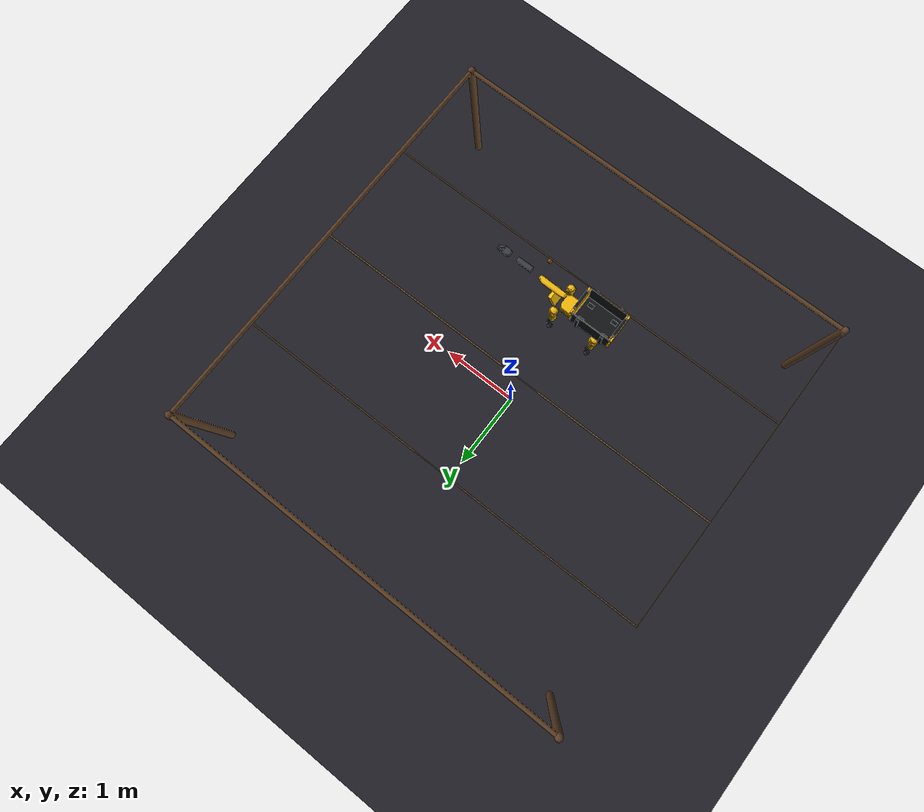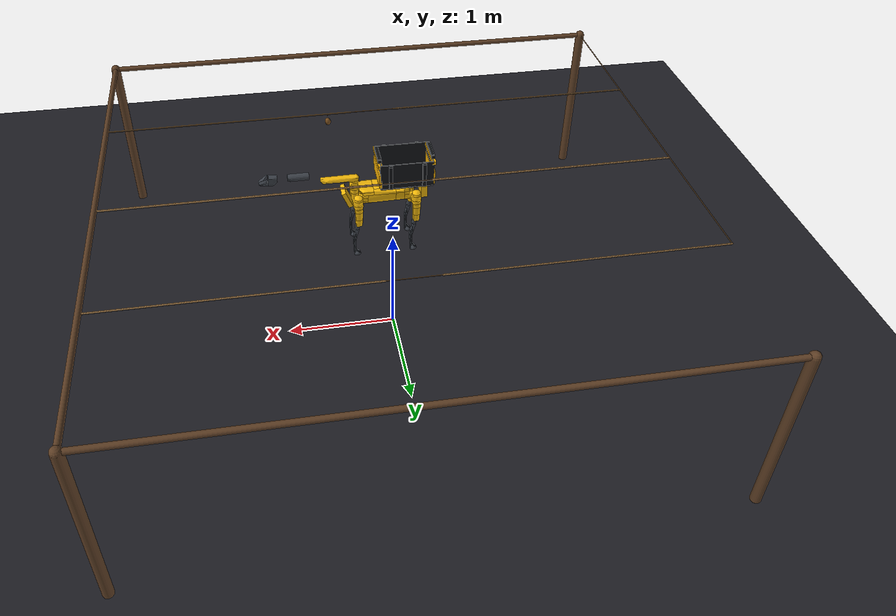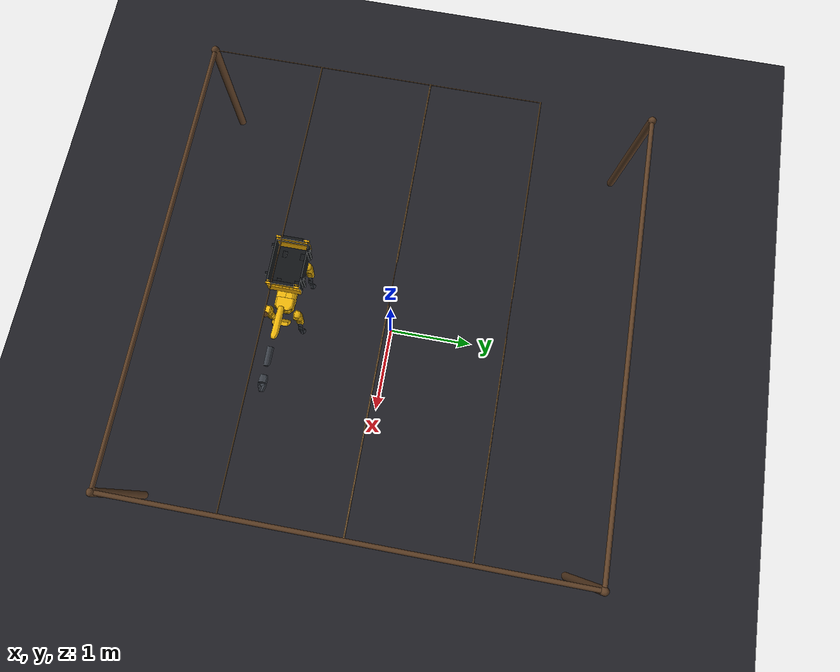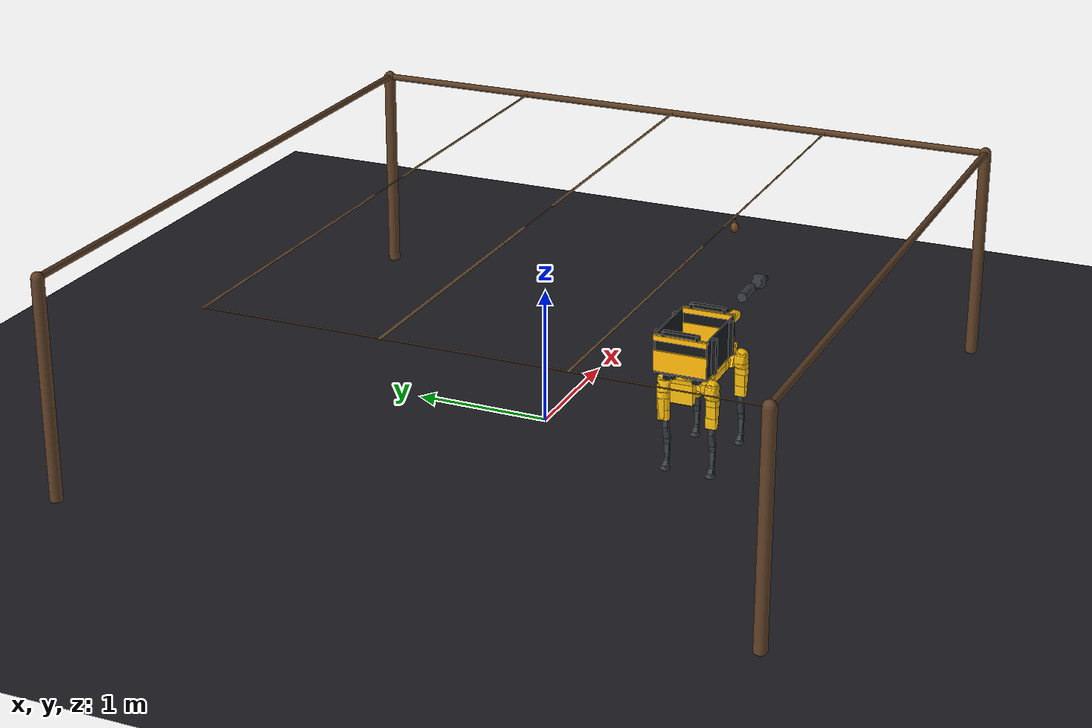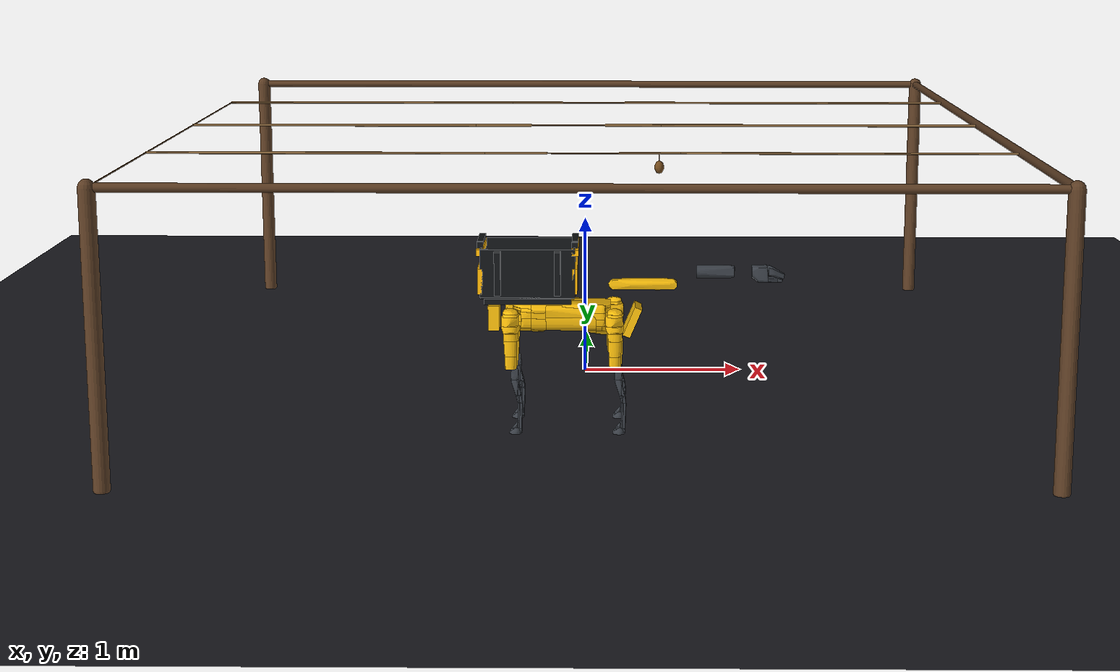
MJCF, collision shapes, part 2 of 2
0.039509000000000002 -0.040918999999999997 0.14663999999999999 0.040773999999999991 -0.040252999999999983 0.22736500000000001 -0.011800999999999996 -0.037497000000000003 0.22830299999999998 -0.0091969999999999968 -0.036964999999999998 0.22292000000000001 -0.011790999999999992 -0.040035999999999988 0.147036 -0.036811999999999984 -0.041954000000000005 0.14608399999999999 -0.035991999999999996 -0.041438999999999976 0.14627699999999999 -0.036507999999999985 -0.043675000000000005 0.15229300000000001 -0.038293999999999995 -0.040174999999999988 0.20288600000000001 -0.012535999999999995 -0.040180999999999994 0.197571 -0.014623999999999995 -0.041562999999999989 0.20243499999999998 0.012636000000000001 -0.04018300000000001 0.19759499999999997 0.014625000000000001 -0.041565000000000005 0.20048199999999999 0.013354000000000001 -0.04163399999999999 0.20808699999999999 0.011977 -0.041591000000000003 0.20243499999999998 0.012636000000000001 -0.04018300000000001 0.20402500000000001 0.012481000000000003 -0.04163399999999999 0.20243499999999998 0.012636000000000001 -0.04018300000000001 0.20048199999999999 0.013354000000000001 -0.04163399999999999 0.20402500000000001 0.012481000000000003 -0.04163399999999999 0.19759499999999997 0.014625000000000001 -0.041565000000000005 0.20243499999999998 0.012636000000000001 -0.04018300000000001 0.15709100000000001 0.036103999999999997 -0.041491 0.1487 0.036677000000000001 -0.040182999999999996 0.148614 0.036077999999999999 -0.041542999999999997 0.14957899999999999 0.037395999999999999 -0.041581999999999994 0.1487 0.036677000000000001 -0.040182999999999996 0.14854400000000001 -0.035406000000000007 -0.041600999999999999 0.148614 0.036077999999999999 -0.041542999999999997 0.1487 0.036677000000000001 -0.040182999999999996 0.14880399999999999 -0.036852999999999983 -0.040175999999999989 0.14854400000000001 -0.035406000000000007 -0.041600999999999999 0.14902699999999999 -0.036830999999999989 -0.04157799999999999 0.14880399999999999 -0.036852999999999983 -0.040175999999999989 0.15174499999999999 -0.038278999999999994 -0.041564000000000004 0.14854400000000001 -0.035406000000000007 -0.041600999999999999 0.14880399999999999 -0.036852999999999983 -0.040175999999999989 0.14902699999999999 -0.036830999999999989 -0.04157799999999999 0.22514499999999998 -0.012047999999999993 -0.037054000000000004 0.22736500000000001 -0.011800999999999996 -0.037497000000000003 0.222549 -0.011877999999999996 -0.040133000000000002 0.21736800000000001 0.011991 -0.041458000000000009 0.22031099999999998 0.012051000000000001 -0.039807999999999996 0.20808699999999999 0.011977 -0.041591000000000003 0.22031099999999998 0.012051000000000001 -0.039807999999999996 0.20243499999999998 0.012636000000000001 -0.04018300000000001 0.20808699999999999 0.011977 -0.041591000000000003 0.222916 0.011821999999999999 -0.040028999999999981 0.22278300000000001 0.011853000000000002 -0.04005199999999999 0.22762099999999999 0.011112000000000002 -0.037357999999999995 0.22278300000000001 0.011853000000000002 -0.04005199999999999 0.22830299999999998 -0.0091969999999999968 -0.036964999999999998 0.22830299999999998 0.0091999999999999998 -0.036964999999999998 0.21706300000000001 0.011769000000000002 -0.041662999999999992 0.20982200000000001 -0.011761999999999998 -0.041664999999999994 0.21706300000000001 -0.011757 -0.041664999999999994 0.21706300000000001 0.011769000000000002 -0.041662999999999992 0.20982200000000001 0.011762999999999999 -0.041662999999999992 0.20982200000000001 -0.011761999999999998 -0.041664999999999994 0.20982200000000001 0.011762999999999999 -0.041662999999999992 0.207012 -0.012101999999999991 -0.041561000000000015 0.20982200000000001 -0.011761999999999998 -0.041664999999999994 0.20808699999999999 0.011977 -0.041591000000000003 0.207012 -0.012101999999999991 -0.041561000000000015 0.20982200000000001 0.011762999999999999 -0.041662999999999992 0.20503299999999997 0.012143000000000001 -0.04166499999999998 0.20402500000000001 0.012481000000000003 -0.04163399999999999 0.20037199999999999 -0.013310999999999993 -0.041664999999999994 0.20174500000000001 -0.013047 -0.041620000000000004 0.20503299999999997 0.012143000000000001 -0.04166499999999998 0.20037199999999999 -0.013310999999999993 -0.041664999999999994 0.20808699999999999 0.011977 -0.041591000000000003 0.20174500000000001 -0.013047 -0.041620000000000004 0.20503199999999999 -0.012137999999999993 -0.04166499999999998 0.20048199999999999 0.013354000000000001 -0.04163399999999999 0.19759499999999997 0.014625000000000001 -0.041565000000000005 0.15957399999999999 -0.03458399999999999 -0.041665999999999995 0.15958 0.034595000000000001 -0.041666999999999996 0.156024 -0.036306999999999992 -0.041663999999999979 0.195964 0.015221000000000002 -0.041664999999999994 0.15958 0.034595000000000001 -0.041666999999999996 0.15127299999999999 -0.037817999999999991 -0.041675000000000018 0.15234300000000001 -0.037727999999999984 -0.041663999999999993 0.148614 0.036077999999999999 -0.041542999999999997 0.14854400000000001 -0.035406000000000007 -0.041600999999999999 0.156024 0.036306999999999992 -0.041663999999999993 0.15958 0.034595000000000001 -0.041666999999999996 0.14902699999999999 -0.036830999999999989 -0.04157799999999999 0.15006 -0.037512999999999991 -0.04166099999999999 0.15124799999999999 0.037815000000000001 -0.041675000000000004 0.14957899999999999 0.037395999999999999 -0.041581999999999994 0.152341 0.037723 -0.041666000000000009 0.22278300000000001 0.011853000000000002 -0.04005199999999999 0.22148200000000001 0.011818000000000002 -0.040745999999999977 0.22164099999999998 -0.011768999999999991 -0.040710999999999997 0.22148200000000001 0.011818000000000002 -0.040745999999999977 0.22016199999999997 0.011825000000000002 -0.041154999999999997 0.22002299999999997 -0.011854999999999994 -0.041207000000000008 0.22002299999999997 -0.011854999999999994 -0.041207000000000008 0.22016199999999997 0.011825000000000002 -0.041154999999999997 0.21851400000000001 -0.011856000000000002 -0.041494999999999976 0.22016199999999997 0.011825000000000002 -0.041154999999999997 0.218414 0.011817000000000001 -0.041525999999999993 0.21851400000000001 -0.011856000000000002 -0.041494999999999976 0.219587 -0.011828999999999996 -0.041247999999999993 0.22002299999999997 -0.011854999999999994 -0.041207000000000008 0.21851400000000001 -0.011856000000000002 -0.041494999999999976 0.22002299999999997 -0.011854999999999994 -0.041207000000000008 0.22021099999999999 -0.012059999999999991 -0.039916999999999994 0.22164099999999998 -0.011768999999999991 -0.040710999999999997 0.22021099999999999 -0.012059999999999991 -0.039916999999999994 0.222549 -0.011877999999999996 -0.040133000000000002 0.22164099999999998 -0.011768999999999991 -0.040710999999999997 0.197571 -0.014623999999999995 -0.041562999999999989 0.20174500000000001 -0.013047 -0.041620000000000004 0.20037199999999999 -0.013310999999999993 -0.041664999999999994 0.20174500000000001 -0.013047 -0.041620000000000004 0.207012 -0.012101999999999991 -0.041561000000000015 0.20503199999999999 -0.012137999999999993 -0.04166499999999998 0.15124799999999999 0.037815000000000001 -0.041675000000000004 0.15149199999999999 0.038073999999999997 -0.041616 0.15005299999999999 0.037516000000000001 -0.041660000000000003 0.15958 0.034595000000000001 -0.041666999999999996 0.15709100000000001 0.036103999999999997 -0.041491 0.156024 0.036306999999999992 -0.041663999999999993 0.15709100000000001 0.036103999999999997 -0.041491 0.152341 0.037723 -0.041666000000000009 0.156024 0.036306999999999992 -0.041663999999999993 0.19759499999999997 0.014625000000000001 -0.041565000000000005 0.15709100000000001 0.036103999999999997 -0.041491 0.195964 0.015221000000000002 -0.041664999999999994 0.15709100000000001 0.036103999999999997 -0.041491 0.15958 0.034595000000000001 -0.041666999999999996 0.195964 0.015221000000000002 -0.041664999999999994 0.20808699999999999 0.011977 -0.041591000000000003 0.20402500000000001 0.012481000000000003 -0.04163399999999999 0.20503299999999997 0.012143000000000001 -0.04166499999999998 0.21736800000000001 0.011991 -0.041458000000000009 0.20808699999999999 0.011977 -0.041591000000000003 0.21706300000000001 0.011769000000000002 -0.041662999999999992 0.20808699999999999 0.011977 -0.041591000000000003 0.20982200000000001 0.011762999999999999 -0.041662999999999992 0.21706300000000001 0.011769000000000002 -0.041662999999999992 0.22148200000000001 0.011818000000000002 -0.040745999999999977 0.22031099999999998 0.012051000000000001 -0.039807999999999996 0.22016199999999997 0.011825000000000002 -0.041154999999999997 0.222916 0.011821999999999999 -0.040028999999999981 0.22608200000000001 0.012123999999999999 -0.037479999999999992 0.22278300000000001 0.011853000000000002 -0.04005199999999999 0.14621700000000001 -0.04050999999999999 -0.041415999999999981 0.152305 -0.038592999999999988 -0.044800999999999994 0.15232699999999999 -0.039101999999999984 -0.045014999999999999 0.153557 -0.038743999999999987 -0.045114000000000001 0.152305 -0.038592999999999988 -0.044800999999999994 0.15232699999999999 -0.039101999999999984 -0.045014999999999999 0.15523899999999999 -0.037519999999999984 -0.046147000000000007 0.15718299999999999 -0.036490000000000009 -0.046804999999999986 0.154948 -0.038134999999999988 -0.046109999999999998 0.15718299999999999 -0.036490000000000009 -0.046804999999999986 0.154948 -0.038134999999999988 -0.046109999999999998 0.15731400000000001 -0.03710999999999999 -0.047010999999999983 0.19661400000000001 -0.016015999999999992 -0.052822999999999995 0.198549 -0.015152000000000009 -0.052634999999999987 0.19642899999999999 -0.016122999999999995 -0.052485999999999977 0.20641899999999999 -0.013103999999999994 -0.052941000000000002 0.198549 -0.015152000000000009 -0.052634999999999987 0.203291 -0.013751999999999997 -0.053143999999999997 0.225159 -0.012886999999999999 -0.053139000000000006 0.22715099999999999 -0.011114000000000002 -0.052793999999999994 0.22536600000000001 -0.012074999999999992 -0.053032999999999997 0.22942499999999999 0.0097390000000000011 -0.052886000000000002 0.227742 0.012125 -0.053039000000000003 0.22976299999999997 0.010991000000000001 -0.052930999999999992 0.227742 0.012125 -0.053039000000000003 0.23003000000000001 0.010866000000000001 -0.052914000000000003 0.22976299999999997 0.010991000000000001 -0.052930999999999992 0.227742 0.012125 -0.053039000000000003 0.23003000000000001 0.010866000000000001 -0.052914000000000003 0.227989 0.012151000000000002 -0.053170000000000009 0.22517000000000001 0.012903000000000001 -0.053071999999999994 0.20970899999999998 0.012886999999999999 -0.053031000000000023 0.22539899999999996 0.012007000000000002 -0.053018999999999997 0.20970899999999998 0.012886999999999999 -0.053031000000000023 0.22539899999999996 0.012007000000000002 -0.053018999999999997 0.209704 0.012054 -0.053032000000000024 0.19661600000000001 0.016004999999999998 -0.052812000000000012 0.19867199999999996 0.015161000000000001 -0.05254099999999999 0.19720399999999999 0.015454000000000002 -0.052711999999999981 0.17568099999999998 0.027463000000000001 -0.049952999999999997 0.18585499999999999 0.021066999999999999 -0.051616000000000009 0.177981 0.025583999999999999 -0.050540000000000002 0.16617399999999999 0.031106999999999999 -0.048540000000000014 0.17568099999999998 0.027463000000000001 -0.049952999999999997 0.16811100000000001 0.031315999999999997 -0.049086000000000005 0.16617399999999999 0.031106999999999999 -0.048540000000000014 0.17568099999999998 0.027463000000000001 -0.049952999999999997 0.177981 0.025583999999999999 -0.050540000000000002 0.17568099999999998 0.027463000000000001 -0.049952999999999997 0.16811100000000001 0.031315999999999997 -0.049086000000000005 0.16001499999999999 0.035637000000000002 -0.047369000000000008 0.16617399999999999 0.031106999999999999 -0.048540000000000014 0.16811100000000001 0.031315999999999997 -0.049086000000000005 0.16001499999999999 0.035637000000000002 -0.047369000000000008 0.15925 0.036199999999999996 -0.047121999999999983 0.159884 0.035952999999999999 -0.047029000000000001 0.16001499999999999 0.035637000000000002 -0.047369000000000008 0.15749299999999999 0.036339999999999997 -0.046901999999999985 0.155693 0.037388999999999999 -0.046307000000000001 0.15437400000000001 0.038261000000000003 -0.045915999999999998 0.15427099999999999 0.038529000000000001 -0.045445999999999986 0.14621799999999999 0.040514999999999995 -0.041419999999999998 0.14663999999999999 0.040773999999999991 -0.040252999999999983 0.150314 0.038383 -0.043556999999999998 0.15226200000000001 0.037504999999999997 -0.044753000000000001 0.15231500000000001 0.037311999999999998 -0.044482000000000008 0.15749299999999999 0.036339999999999997 -0.046901999999999985 0.159306 0.034446999999999998 -0.047135999999999997 0.159442 0.035400000000000001 -0.047361 0.15636700000000001 0.036177000000000001 -0.046398000000000009 0.15551999999999999 0.036462000000000001 -0.046093000000000009 0.15427199999999999 0.036600999999999995 -0.045458999999999999 0.15431900000000001 0.037383 -0.045772999999999994 0.15636700000000001 0.036177000000000001 -0.046398000000000009 0.15551999999999999 0.036462000000000001 -0.046093000000000009 0.15431900000000001 0.037383 -0.045772999999999994 0.15226200000000001 0.037504999999999997 -0.044753000000000001 0.15231500000000001 0.037311999999999998 -0.044482000000000008 0.15431900000000001 0.037383 -0.045772999999999994 0.15231500000000001 0.037311999999999998 -0.044482000000000008 0.15427199999999999 0.036600999999999995 -0.045458999999999999 0.16617399999999999 0.031106999999999999 -0.048540000000000014 0.177981 0.025583999999999999 -0.050540000000000002 0.17766499999999999 0.024951000000000001 -0.050302999999999987 0.16617399999999999 0.031106999999999999 -0.048540000000000014 0.159306 0.034446999999999998 -0.047135999999999997 0.159442 0.035400000000000001 -0.047361 0.19720399999999999 0.015454000000000002 -0.052711999999999981 0.197016 0.014298999999999999 -0.052410999999999999 0.19617799999999999 0.015207999999999999 -0.052444000000000005 0.20280400000000001 0.012638999999999999 -0.052784999999999999 0.20022400000000001 0.013013 -0.052437999999999999 0.20022999999999999 0.013231 -0.052786 0.19932800000000001 0.013752 -0.052726000000000009 0.20022400000000001 0.013013 -0.052437999999999999 0.20022999999999999 0.013231 -0.052786 0.20280400000000001 0.012638999999999999 -0.052784999999999999 0.20349499999999998 0.012118000000000002 -0.052574999999999997 0.203481 0.012278000000000001 -0.052943000000000004 0.19932800000000001 0.013752 -0.052726000000000009 0.20035500000000001 0.014338 -0.053019999999999998 0.20022999999999999 0.013231 -0.052786 0.227273 0.011132 -0.052599999999999994 0.22740899999999997 0.011057000000000001 -0.05297700000000001 0.22539899999999996 0.012007000000000002 -0.053018999999999997 0.227742 0.012125 -0.053039000000000003 0.22740899999999997 0.011057000000000001 -0.05297700000000001 0.22539899999999996 0.012007000000000002 -0.053018999999999997 0.22809099999999999 -0.011060999999999991 -0.052963999999999997 0.22821900000000001 -0.010231999999999998 -0.052560999999999997 0.22959199999999996 -0.0089609999999999967 -0.052982000000000001 0.206654 -0.012094000000000004 -0.052988999999999994 0.20499200000000001 -0.011899999999999997 -0.052610000000000018 0.20348099999999997 -0.012260000000000004 -0.052947000000000008 0.20288999999999999 -0.012691999999999991 -0.052798999999999999 0.20348099999999997 -0.012260000000000004 -0.052947000000000008 0.20349499999999998 -0.012146000000000001 -0.052574999999999997 0.206654 -0.012094000000000004 -0.052988999999999994 0.20348099999999997 -0.012260000000000004 -0.052947000000000008 0.20349500000000001 -0.013230000000000002 -0.053056000000000006 0.20288999999999999 -0.012691999999999991 -0.052798999999999999 0.20348099999999997 -0.012260000000000004 -0.052947000000000008 0.20349500000000001 -0.013230000000000002 -0.053056000000000006 0.198549 -0.015152000000000009 -0.052634999999999987 0.19872699999999999 -0.013971999999999995 -0.052517999999999995 0.200239 -0.013233999999999992 -0.052805000000000005 0.20288999999999999 -0.012691999999999991 -0.052798999999999999 0.200239 -0.013233999999999992 -0.052805000000000005 0.20022999999999999 -0.013052999999999992 -0.052439 0.19872699999999999 -0.013971999999999995 -0.052517999999999995 0.19720399999999999 -0.015453999999999999 -0.052711999999999995 0.19658900000000001 -0.015096999999999996 -0.052660999999999986 0.19872699999999999 -0.013971999999999995 -0.052517999999999995 0.19617799999999996 -0.015207999999999989 -0.052444000000000005 0.19700400000000001 -0.014347000000000002 -0.052547999999999984 0.189106 -0.019668999999999996 -0.052000000000000005 0.17768500000000001 -0.02493699999999999 -0.050327999999999998 0.178008 -0.025595999999999997 -0.050543999999999978 0.16212299999999999 -0.033755000000000007 -0.047865000000000005 0.17768500000000001 -0.02493699999999999 -0.050327999999999998 0.178008 -0.025595999999999997 -0.050543999999999978 0.15718299999999999 -0.036490000000000009 -0.046804999999999986 0.159305 -0.034443000000000001 -0.04713299999999998 0.157141 -0.035398999999999986 -0.046496999999999997 0.155198 -0.036561999999999997 -0.045987 0.15718299999999999 -0.036490000000000009 -0.046804999999999986 0.157141 -0.035398999999999986 -0.046496999999999997 0.150474 -0.038235999999999992 -0.043750999999999998 0.152305 -0.038592999999999988 -0.044800999999999994 0.15226100000000001 -0.037506999999999985 -0.044749999999999998 0.150474 -0.038235999999999992 -0.043750999999999998 0.149731 -0.038505999999999985 -0.043348999999999999 0.152313 -0.037324999999999983 -0.044485999999999998 0.22830299999999998 0.0091999999999999998 -0.036964999999999998 0.23565399999999997 0.0094369999999999992 -0.039330999999999977 0.22813899999999998 0.010185000000000001 -0.03706000000000001 0.22514499999999998 -0.012047999999999993 -0.037054000000000004 0.22111500000000001 -0.013398999999999998 -0.039412000000000003 0.23169000000000001 -0.012908999999999986 -0.040197999999999984 0.080996000000000012 -0.0035549999999999957 -0.049121999999999999 0.080068000000000014 -0.004550999999999996 -0.036202999999999992 0.080997000000000013 -0.0021669999999999918 -0.049204999999999985 0.080997000000000013 -0.0021669999999999918 -0.049204999999999985 0.080069000000000001 -0.004489999999999994 -0.036205999999999995 0.080998000000000001 0.00078000000000000291 -0.049248 0.080963000000000007 0.013743000000000002 -0.047233999999999998 0.080071000000000003 0.0048850000000000005 -0.036190999999999994 0.080958000000000002 0.016102000000000005 -0.0465 0.080970000000000014 0.012311000000000001 -0.047639999999999988 0.080071000000000017 0.0048170000000000018 -0.036198000000000001 0.080963000000000007 0.013743000000000002 -0.047233999999999998 0.080982000000000012 0.0094720000000000013 -0.048305000000000001 0.080070000000000016 0.004779000000000002 -0.036200999999999997 0.080970000000000014 0.012311000000000001 -0.047639999999999988 0.145949 -0.040667000000000009 -0.049167000000000002 0.14618 -0.028680000000000001 -0.052186999999999997 0.146204 -0.040771999999999989 -0.048526 0.14623900000000001 -0.035145999999999983 -0.050026000000000001 0.14624400000000001 -0.036369999999999986 -0.048996999999999999 0.146204 -0.040771999999999989 -0.048526 0.12610199999999999 0.035077999999999998 -0.053955000000000003 0.12606800000000001 0.038511999999999998 -0.051879999999999982 0.14422099999999999 0.040913999999999992 -0.048763000000000001 0.14294999999999999 -0.015778999999999991 -0.022359000000000004 0.14299700000000001 -0.013999999999999995 -0.022328000000000001 0.080750000000000016 -0.027765999999999989 -0.022419999999999989 0.14405899999999999 0.014000000000000002 -0.023246000000000003 0.14299700000000001 -0.013999999999999995 -0.022328000000000001 0.14412 -0.013999999999999995 -0.023273999999999996 0.132766 -0.0001460000000000003 -0.059994000000000006 0.13830700000000001 0.0074820000000000008 -0.057492999999999989 0.13835 -0.0074819999999999956 -0.057472999999999996 0.090378000000000014 0.039206999999999992 0.026263000000000002 0.08135400000000001 0.023827000000000001 0.028802000000000001 0.081217000000000011 0.021205999999999999 0.030682999999999998 0.08135400000000001 0.018520999999999999 0.032469999999999999 0.093192999999999998 0.039290999999999993 0.028670000000000001 0.081217000000000011 0.021205999999999999 0.030682999999999998 0.081217000000000011 0.026165999999999998 0.026579999999999999 0.080181000000000002 0.025949 0.025193 0.080982999999999999 0.023602999999999999 0.028531000000000001 0.12601999999999999 0.041727 -0.044706999999999997 0.095901000000000014 0.040783 -0.048279000000000002 0.094742999999999994 0.041387 -0.04579699999999999 0.081183000000000019 0.028303999999999999 0.024174000000000001 0.080179000000000014 0.028105999999999999 0.022734000000000001 0.080176999999999998 0.026172999999999998 0.024967 0.081153000000000003 0.030273999999999999 0.021634 0.080183000000000004 0.028228 0.022571000000000001 0.080180000000000001 0.028170000000000001 0.022655000000000002 0.081153000000000003 0.030273999999999999 0.021634 0.087162000000000017 0.039100000000000003 0.021465000000000001 0.081249000000000016 0.032117 0.018994 0.087162000000000017 0.039100000000000003 0.021465000000000001 0.08115 0.033534000000000001 0.016102999999999999 0.081249000000000016 0.032117 0.018994 0.086749000000000021 0.03941299999999999 0.019401000000000002 0.086073000000000011 0.039326 0.015849000000000002 0.086174000000000001 0.039240999999999998 0.017866 0.086073000000000011 0.039326 0.015849000000000002 0.081220000000000001 0.037097999999999992 0.0038009999999999988 0.086174000000000001 0.039240999999999998 0.017866 0.081220000000000001 0.037097999999999992 0.0038009999999999988 0.081110000000000002 0.036442000000000002 0.0069239999999999996 0.086174000000000001 0.039240999999999998 0.017866 0.081110000000000002 0.036442000000000002 0.0069239999999999996 0.081328000000000011 0.035970000000000002 0.010144999999999998 0.086174000000000001 0.039240999999999998 0.017866 0.080227000000000021 0.035492999999999997 0.0060499999999999998 0.081110000000000002 0.036442000000000002 0.0069239999999999996 0.081220000000000001 0.037097999999999992 0.0038009999999999988 0.081191000000000013 0.037215999999999999 0 0.080147999999999997 0.036297000000000003 0.00032000000000000084 0.081220000000000001 0.037097999999999992 0.0038009999999999988 0.096684999999999993 0.039588999999999999 -0.050479999999999997 0.12603900000000001 0.040854000000000001 -0.048623 0.12606800000000001 0.038511999999999998 -0.051879999999999982 0.08114200000000002 0.037187999999999999 -0.032104999999999995 0.080156000000000005 0.036235000000000003 -0.0030559999999999997 0.080140000000000017 0.036303000000000002 -0.0026660000000000017 0.097910999999999998 -0.039825999999999986 0.030095 0.096084000000000003 -0.039778000000000008 0.029388000000000001 0.087992000000000001 -0.041711999999999985 -0.027786000000000005 0.091308 -0.039652999999999994 0.025814 0.085721000000000019 -0.041637999999999994 -0.029867999999999999 0.087992000000000001 -0.041711999999999985 -0.027786000000000005 0.10164900000000002 -0.039280999999999996 0.031731000000000002 0.10248500000000002 -0.039838999999999986 0.031308999999999997 0.11745 -0.040337999999999985 0.030425000000000001 0.10248500000000002 -0.039838999999999986 0.031308999999999997 0.101522 -0.039879999999999999 0.031022999999999998 0.11745 -0.040337999999999985 0.030425000000000001 0.101522 -0.039879999999999999 0.031022999999999998 0.10295000000000001 -0.039958000000000007 0.030425000000000001 0.11745 -0.040337999999999985 0.030425000000000001 0.091308 -0.039652999999999994 0.025814 0.088574 -0.039581999999999992 0.022124999999999999 0.085721000000000019 -0.041637999999999994 -0.029867999999999999 0.088574 -0.039581999999999992 0.022124999999999999 0.086908000000000013 -0.03953799999999999 0.018137 0.085721000000000019 -0.041637999999999994 -0.029867999999999999 0.086908000000000013 -0.03953799999999999 0.018137 0.08476800000000001 -0.04153599999999999 -0.032844999999999992 0.085721000000000019 -0.041637999999999994 -0.029867999999999999 0.101522 -0.039879999999999999 0.031022999999999998 0.097910999999999998 -0.039825999999999986 0.030095 0.10295000000000001 -0.039958000000000007 0.030425000000000001 0.101522 -0.039879999999999999 0.031022999999999998 0.099388000000000004 -0.039684999999999984 0.030942000000000001 0.097910999999999998 -0.039825999999999986 0.030095 0.094114000000000003 -0.039543999999999996 0.028838000000000003 0.092813000000000007 -0.039637999999999993 0.027682999999999999 0.096084000000000003 -0.039778000000000008 0.029388000000000001 0.092813000000000007 -0.039637999999999993 0.027682999999999999 0.091308 -0.039652999999999994 0.025814 0.096084000000000003 -0.039778000000000008 0.029388000000000001 0.092813000000000007 -0.039637999999999993 0.027682999999999999 0.089932000000000012 -0.039555999999999994 0.024903000000000002 0.091308 -0.039652999999999994 0.025814 0.089932000000000012 -0.039555999999999994 0.024903000000000002 0.088574 -0.039581999999999992 0.022124999999999999 0.091308 -0.039652999999999994 0.025814 0.13125300000000001 -0.021253000000000005 -0.058387000000000008 0.13153799999999999 -0.020423999999999994 -0.058523000000000019 0.13228999999999999 -0.021968999999999999 -0.057673000000000002 0.132766 -0.014047 -0.059055999999999997 0.13245299999999999 -0.021057999999999997 -0.057729000000000016 0.13228999999999999 -0.021968999999999999 -0.057673000000000002 0.13245299999999999 -0.021057999999999997 -0.057729000000000016 0.12547800000000001 -0.039499999999999993 -0.013185999999999996 0.13228999999999999 -0.021968999999999999 -0.057673000000000002 0.12606800000000001 -0.038511999999999991 -0.051879999999999996 0.12610199999999999 -0.035077999999999984 -0.053955000000000003 0.13228999999999999 -0.021968999999999999 -0.057673000000000002 0.141127 -0.039139999999999994 0.027104 0.139066 -0.04038499999999999 0.029139999999999999 0.139131 -0.040433999999999984 0.026977999999999999 0.117289 0.0058390000000000039 0.037580000000000002 0.081173000000000009 3.4694469519536142e-18 0.037152999999999999 0.116259 -0.0060719999999999975 0.037524000000000002 0.100077 -0.0058999999999999955 0.037266000000000001 0.098833000000000004 -0.0059409999999999949 0.037238 0.116259 -0.0060719999999999975 0.037524000000000002 0.102492 -0.033593999999999985 0.032738000000000003 0.10164900000000002 -0.039280999999999996 0.031731000000000002 0.116259 -0.0060719999999999975 0.037524000000000002 0.102492 -0.033593999999999985 0.032738000000000003 0.081240000000000007 -0.0064139999999999961 0.036752999999999994 0.10164900000000002 -0.039280999999999996 0.031731000000000002 0.081240000000000007 -0.0064139999999999961 0.036752999999999994 0.099292000000000019 -0.039035999999999987 0.031473000000000001 0.10164900000000002 -0.039280999999999996 0.031731000000000002 0.099388000000000004 -0.039684999999999984 0.030942000000000001 0.10248500000000002 -0.039838999999999986 0.031308999999999997 0.10164900000000002 -0.039280999999999996 0.031731000000000002 0.099388000000000004 -0.039684999999999984 0.030942000000000001 0.101522 -0.039879999999999999 0.031022999999999998 0.10248500000000002 -0.039838999999999986 0.031308999999999997 0.13250100000000001 0.021142999999999999 -0.057759000000000005 0.13152900000000001 0.020417000000000001 -0.05852400000000002 0.13123699999999999 0.021325 -0.058372999999999994 0.081217000000000011 -0.037103999999999984 0.0038019999999999998 0.081207000000000001 -0.037286 0.00058599999999999972 0.08476800000000001 -0.04153599999999999 -0.032844999999999992 0.089932000000000012 -0.039555999999999994 0.024903000000000002 0.088732000000000005 -0.039470999999999992 0.023602999999999999 0.088574 -0.039581999999999992 0.022124999999999999 0.088732000000000005 -0.039470999999999992 0.023602999999999999 0.087914999999999993 -0.039499999999999993 0.021735999999999998 0.088574 -0.039581999999999992 0.022124999999999999 0.087914999999999993 -0.039499999999999993 0.021735999999999998 0.086908000000000013 -0.03953799999999999 0.018137 0.088574 -0.039581999999999992 0.022124999999999999 0.087914999999999993 -0.039499999999999993 0.021735999999999998 0.086964000000000014 -0.039349000000000009 0.01992 0.086908000000000013 -0.03953799999999999 0.018137 0.086249999999999993 -0.039217999999999989 0.018317 0.086114999999999997 -0.039325999999999986 0.016237999999999999 0.086908000000000013 -0.03953799999999999 0.018137 0.095213000000000006 -0.038920999999999997 0.030027999999999999 0.095784999999999995 -0.039321999999999996 0.030068000000000001 0.097750000000000004 -0.039344999999999991 0.030848 0.099292000000000019 -0.039035999999999987 0.031473000000000001 0.081395999999999996 -0.012665999999999993 0.035181999999999998 0.097750000000000004 -0.039344999999999991 0.030848 0.095213000000000006 -0.038920999999999997 0.030027999999999999 0.093846000000000013 -0.038880999999999985 0.0293 0.095784999999999995 -0.039321999999999996 0.030068000000000001 0.093846000000000013 -0.038880999999999985 0.0293 0.092467999999999995 -0.039269999999999985 0.028146000000000001 0.095784999999999995 -0.039321999999999996 0.030068000000000001 0.092467999999999995 -0.039269999999999985 0.028146000000000001 0.094114000000000003 -0.039543999999999996 0.028838000000000003 0.095784999999999995 -0.039321999999999996 0.030068000000000001 0.091024999999999995 -0.039380999999999985 0.026669999999999999 0.089932000000000012 -0.039555999999999994 0.024903000000000002 0.092813000000000007 -0.039637999999999993 0.027682999999999999 0.10295000000000001 -0.039958000000000007 0.030425000000000001 0.12056 -0.041971999999999995 -0.028160000000000004 0.11745 -0.040337999999999985 0.030425000000000001 0.13128500000000001 -0.015382000000000003 -0.059492000000000003 0.132766 -0.014047 -0.059055999999999997 0.13153799999999999 -0.020423999999999994 -0.058523000000000019 0.13128500000000001 -0.015382000000000003 -0.059492000000000003 0.13131000000000001 -0.010315999999999995 -0.060109999999999997 0.132766 -0.014047 -0.059055999999999997 0.132766 -0.0080530000000000011 -0.059692000000000009 0.132766 -0.0064679999999999981 -0.059803000000000009 0.132766 -0.0012059999999999953 -0.059976000000000002 0.132766 -0.0080530000000000011 -0.059692000000000009 0.132766 -0.0012059999999999953 -0.059976000000000002 0.132766 -0.0001460000000000003 -0.059994000000000006 0.132766 -0.0080530000000000011 -0.059692000000000009 0.132766 -0.0001460000000000003 -0.059994000000000006 0.132766 0.005587 -0.05985299999999999 0.132766 -0.0080530000000000011 -0.059692000000000009 0.132766 0.005587 -0.05985299999999999 0.132766 0.006714000000000003 -0.059786999999999993 0.132766 -0.0080530000000000011 -0.059692000000000009 0.132766 0.012141000000000001 -0.059281 0.132766 0.012720000000000002 -0.059227000000000002 0.098833000000000004 0.0059410000000000001 0.037238 0.100065 0.0058990000000000032 0.037266000000000001 0.117289 0.0058390000000000039 0.037580000000000002 0.100065 0.0058990000000000032 0.037266000000000001 0.081173000000000009 3.4694469519536142e-18 0.037152999999999999 0.117289 0.0058390000000000039 0.037580000000000002 0.098833000000000004 0.0059410000000000001 0.037238 0.081240000000000007 0.0064139999999999996 0.036753000000000001 0.081173000000000009 3.4694469519536142e-18 0.037152999999999999 0.081240000000000007 0.0064139999999999996 0.036753000000000001 0.081060999999999994 0.0031720000000000047 0.036873999999999997 0.081173000000000009 3.4694469519536142e-18 0.037152999999999999 0.081060999999999994 0.0031720000000000047 0.036873999999999997 0.080139000000000016 0.0042300000000000046 0.036020999999999997 0.081173000000000009 3.4694469519536142e-18 0.037152999999999999 0.081191000000000013 0.037215999999999999 0 0.081220000000000001 0.037097999999999992 0.0038009999999999988 0.084810999999999998 0.041406999999999999 -0.031504999999999991 0.081076000000000009 -0.0031809999999999998 0.036887000000000003 0.081240000000000007 -0.0064139999999999961 0.036752999999999994 0.081173000000000009 3.4694469519536142e-18 0.037152999999999999 0.081240000000000007 -0.0064139999999999961 0.036752999999999994 0.098833000000000004 -0.0059409999999999949 0.037238 0.081173000000000009 3.4694469519536142e-18 0.037152999999999999 0.086749000000000021 0.03941299999999999 0.019401000000000002 0.086857000000000018 0.039537000000000003 0.017926000000000001 0.084810999999999998 0.041406999999999999 -0.031504999999999991 0.081240000000000007 -0.0064139999999999961 0.036752999999999994 0.097908999999999996 -0.0064039999999999965 0.037144000000000003 0.098833000000000004 -0.0059409999999999949 0.037238 0.097908999999999996 -0.0064039999999999965 0.037144000000000003 0.102492 -0.033593999999999985 0.032738000000000003 0.098833000000000004 -0.0059409999999999949 0.037238 0.097908999999999996 -0.0064039999999999965 0.037144000000000003 0.081240000000000007 -0.0064139999999999961 0.036752999999999994 0.102492 -0.033593999999999985 0.032738000000000003 0.081076000000000009 -0.0031809999999999998 0.036887000000000003 0.080130000000000021 -0.0047249999999999966 0.035985999999999997 0.081240000000000007 -0.0064139999999999961 0.036752999999999994 0.087482000000000018 0.039434999999999998 0.021318 0.089695000000000011 0.039611 0.024184000000000001 0.087909000000000015 0.039564000000000002 0.021124 0.087482000000000018 0.039434999999999998 0.021318 0.088294000000000011 0.039299000000000001 0.023234999999999999 0.089695000000000011 0.039611 0.024184000000000001 0.081153000000000003 -0.0095369999999999969 0.035966999999999999 0.099292000000000019 -0.039035999999999987 0.031473000000000001 0.081240000000000007 -0.0064139999999999961 0.036752999999999994 0.088294000000000011 0.039299000000000001 0.023234999999999999 0.089164999999999994 0.039302999999999998 0.024580000000000001 0.089695000000000011 0.039611 0.024184000000000001 0.081153000000000003 -0.0095369999999999969 0.035966999999999999 0.081395999999999996 -0.012665999999999993 0.035181999999999998 0.099292000000000019 -0.039035999999999987 0.031473000000000001 0.090948000000000001 0.039607000000000003 0.025753999999999999 0.092409000000000019 0.039682000000000002 0.02707 0.089695000000000011 0.039611 0.024184000000000001 0.093384999999999996 0.039598999999999995 0.028376999999999999 0.095323000000000019 0.039759000000000003 0.029016 0.093639 0.039713999999999999 0.028003 0.14288999999999999 -0.033545999999999992 -0.018289 0.14270099999999999 -0.034083000000000002 -0.018720000000000001 0.14294999999999999 -0.032382999999999995 -0.018412999999999999 0.093384999999999996 0.039598999999999995 0.028376999999999999 0.097043000000000018 0.039745000000000003 0.030053 0.095323000000000019 0.039759000000000003 0.029016 0.097043000000000018 0.039745000000000003 0.030053 0.10049500000000001 0.039841000000000001 0.030919000000000002 0.098636000000000001 0.039844999999999992 0.030029 0.097043000000000018 0.039745000000000003 0.030053 0.098346000000000017 0.039361 0.031022999999999998 0.10049500000000001 0.039841000000000001 0.030919000000000002 0.081120999999999999 -0.036451999999999984 0.0069269999999999991 0.08022600000000002 -0.035522999999999999 0.0060249999999999991 0.081217000000000011 -0.037103999999999984 0.0038019999999999998 0.086114999999999997 -0.039325999999999986 0.016237999999999999 0.086249999999999993 -0.039217999999999989 0.018317 0.081217000000000011 -0.037103999999999984 0.0038019999999999998 0.086249999999999993 -0.039217999999999989 0.018317 0.081120999999999999 -0.036451999999999984 0.0069269999999999991 0.081217000000000011 -0.037103999999999984 0.0038019999999999998 0.081178 -0.03722700000000001 -0.032274999999999998 0.080156000000000005 -0.036237999999999992 -0.0030559999999999962 0.081025000000000014 -0.036320999999999992 -0.033234 0.093192999999999998 0.039290999999999993 0.028670000000000001 0.08135400000000001 0.018520999999999999 0.032469999999999999 0.095033999999999993 0.038915999999999992 0.029954999999999999 0.092008999999999994 0.039409 0.027556000000000001 0.090378000000000014 0.039206999999999992 0.026263000000000002 0.091797000000000017 0.038816000000000003 0.027829 0.089164999999999994 0.039302999999999998 0.024580000000000001 0.081217000000000011 0.026165999999999998 0.026579999999999999 0.090378000000000014 0.039206999999999992 0.026263000000000002 0.081217000000000011 0.026165999999999998 0.026579999999999999 0.08135400000000001 0.023827000000000001 0.028802000000000001 0.090378000000000014 0.039206999999999992 0.026263000000000002 0.092008999999999994 0.039409 0.027556000000000001 0.089164999999999994 0.039302999999999998 0.024580000000000001 0.090378000000000014 0.039206999999999992 0.026263000000000002 0.092008999999999994 0.039409 0.027556000000000001 0.090948000000000001 0.039607000000000003 0.025753999999999999 0.089164999999999994 0.039302999999999998 0.024580000000000001 0.095039000000000012 0.039492999999999993 0.029572999999999999 0.097043000000000018 0.039745000000000003 0.030053 0.093384999999999996 0.039598999999999995 0.028376999999999999 0.087410000000000015 -0.039109000000000005 0.021988000000000001 0.086249999999999993 -0.039217999999999989 0.018317 0.086964000000000014 -0.039349000000000009 0.01992 0.081328000000000011 -0.035969999999999988 0.010145 0.081120999999999999 -0.036451999999999984 0.0069269999999999991 0.086249999999999993 -0.039217999999999989 0.018317 0.081395999999999996 -0.012665999999999993 0.035181999999999998 0.081165000000000015 -0.015581999999999995 0.033799000000000003 0.095213000000000006 -0.038920999999999997 0.030027999999999999 0.081165000000000015 -0.015581999999999995 0.033799000000000003 0.081349000000000005 -0.018519999999999991 0.032468999999999998 0.095213000000000006 -0.038920999999999997 0.030027999999999999 0.081349000000000005 -0.018519999999999991 0.032468999999999998 0.093846000000000013 -0.038880999999999985 0.0293 0.095213000000000006 -0.038920999999999997 0.030027999999999999 0.081349000000000005 -0.018519999999999991 0.032468999999999998 0.092467999999999995 -0.039269999999999985 0.028146000000000001 0.093846000000000013 -0.038880999999999985 0.0293 0.081349000000000005 -0.018519999999999991 0.032468999999999998 0.081207000000000001 -0.021201999999999988 0.030675999999999995 0.092467999999999995 -0.039269999999999985 0.028146000000000001 0.081207000000000001 -0.021201999999999988 0.030675999999999995 0.090788000000000008 -0.038770999999999986 0.026919999999999999 0.092467999999999995 -0.039269999999999985 0.028146000000000001 0.090788000000000008 -0.038770999999999986 0.026919999999999999 0.081336000000000019 -0.023824000000000001 0.028798000000000001 0.089499999999999996 -0.039179999999999993 0.025257999999999999 0.081336000000000019 -0.023824000000000001 0.028798000000000001 0.081228999999999996 -0.026169999999999995 0.026584 0.089499999999999996 -0.039179999999999993 0.025257999999999999 0.080180000000000015 0.028149 0.022682999999999998 0.080179000000000014 0.028105999999999999 0.022734000000000001 0.081183000000000019 0.028303999999999999 0.024174000000000001 0.132766 0.012141000000000001 -0.059281 0.13128400000000001 0.010072000000000001 -0.060138000000000011 0.132766 0.012720000000000002 -0.059227000000000002 0.13131000000000001 0.015133000000000001 -0.059524000000000007 0.13276499999999999 0.017628999999999999 -0.058482999999999979 0.132766 0.012720000000000002 -0.059227000000000002 0.13276499999999999 0.017628999999999999 -0.058482999999999979 0.13276499999999999 0.018679999999999999 -0.058323000000000014 0.132766 0.012720000000000002 -0.059227000000000002 0.13276499999999999 0.018679999999999999 -0.058323000000000014 0.13276499999999999 0.02 -0.058075000000000002 0.132766 0.012720000000000002 -0.059227000000000002 0.13152900000000001 0.020417000000000001 -0.05852400000000002 0.13276499999999999 0.018679999999999999 -0.058323000000000014 0.13131000000000001 0.015133000000000001 -0.059524000000000007 0.13276499999999999 0.018679999999999999 -0.058323000000000014 0.13152900000000001 0.020417000000000001 -0.05852400000000002 0.13276499999999999 0.02 -0.058075000000000002 0.13276499999999999 0.018679999999999999 -0.058323000000000014 0.13276499999999999 0.017628999999999999 -0.058482999999999979 0.13131000000000001 0.015133000000000001 -0.059524000000000007 0.13250100000000001 0.021142999999999999 -0.057759000000000005 0.131025 0.041816999999999993 -0.041937000000000016 0.13276499999999999 0.02 -0.058075000000000002 0.131879 0.022383 -0.057508999999999991 0.12606800000000001 0.038511999999999998 -0.051879999999999982 0.13250100000000001 0.021142999999999999 -0.057759000000000005 0.132766 -0.0001460000000000003 -0.059994000000000006 0.131328 0.0049800000000000018 -0.060496000000000008 0.132766 0.005587 -0.05985299999999999 0.102492 0.033593999999999999 0.032738000000000003 0.081240000000000007 0.0064139999999999996 0.036753000000000001 0.119325 0.039560999999999999 0.032215000000000001 0.081240000000000007 0.0064139999999999996 0.036753000000000001 0.097949999999999995 0.0063500000000000015 0.037155000000000001 0.119325 0.039560999999999999 0.032215000000000001 0.080146999999999996 0.036309000000000001 -0.0019629999999999995 0.080144999999999994 0.036306999999999999 0 0.081191000000000013 0.037215999999999999 0 0.097949999999999995 0.0063500000000000015 0.037155000000000001 0.098833000000000004 0.0059410000000000001 0.037238 0.119325 0.039560999999999999 0.032215000000000001 0.097949999999999995 0.0063500000000000015 0.037155000000000001 0.081240000000000007 0.0064139999999999996 0.036753000000000001 0.098833000000000004 0.0059410000000000001 0.037238 0.080142000000000005 0.0050160000000000014 0.035933 0.081240000000000007 0.0064139999999999996 0.036753000000000001 0.081159000000000009 0.0095370000000000021 0.035970000000000002 0.10087699999999999 0.039077000000000001 0.031711000000000003 0.100414 0.039276999999999992 0.031580999999999998 0.081159000000000009 0.0095370000000000021 0.035970000000000002 0.100414 0.039276999999999992 0.031580999999999998 0.081400000000000014 0.012667000000000001 0.035182999999999999 0.081159000000000009 0.0095370000000000021 0.035970000000000002 0.102492 0.033593999999999999 0.032738000000000003 0.10248699999999999 0.039387999999999999 0.031729 0.081240000000000007 0.0064139999999999996 0.036753000000000001 0.081150000000000014 0.015573999999999999 0.033783000000000007 0.080203999999999998 0.016187 0.032160000000000001 0.080988000000000004 0.012550000000000002 0.034859000000000001 0.10248699999999999 0.039387999999999999 0.031729 0.10087699999999999 0.039077000000000001 0.031711000000000003 0.081240000000000007 0.0064139999999999996 0.036753000000000001 0.10087699999999999 0.039077000000000001 0.031711000000000003 0.081159000000000009 0.0095370000000000021 0.035970000000000002 0.081240000000000007 0.0064139999999999996 0.036753000000000001 0.081150000000000014 0.015573999999999999 0.033783000000000007 0.080151000000000014 0.018925999999999998 0.030764 0.080203999999999998 0.016204 0.032152 0.081217000000000011 0.021205999999999999 0.030682999999999998 0.080168000000000017 0.021475999999999999 0.029099 0.080151000000000014 0.018942000000000001 0.030755000000000005 0.081159000000000009 0.0095370000000000021 0.035970000000000002 0.080165000000000014 0.0055830000000000046 0.035798000000000003 0.080142000000000005 0.0050160000000000014 0.035933 0.080988000000000004 0.018356999999999998 0.032183000000000003 0.080151000000000014 0.018925999999999998 0.030764 0.081150000000000014 0.015573999999999999 0.033783000000000007 0.080988000000000004 0.018356999999999998 0.032183000000000003 0.080151000000000014 0.018942000000000001 0.030755000000000005 0.080151000000000014 0.018933999999999999 0.030759999999999999 0.081217000000000011 0.021205999999999999 0.030682999999999998 0.080171000000000006 0.021573999999999999 0.029027000000000001 0.080168000000000017 0.021475999999999999 0.029099 0.081153000000000003 -0.0095369999999999969 0.035966999999999999 0.08016100000000001 -0.0055849999999999927 0.035790000000000002 0.080969000000000013 -0.012651999999999993 0.034782 0.08115 0.033534000000000001 0.016102999999999999 0.080156000000000005 0.033972000000000002 0.012687 0.081249000000000016 0.032117 0.018994 0.086412000000000017 0.039069999999999994 0.019508999999999999 0.080138000000000015 0.034216000000000003 0.012185 0.087162000000000017 0.039100000000000003 0.021465000000000001 0.086174000000000001 0.039240999999999998 0.017866 0.080138000000000015 0.034222000000000002 0.012171 0.086412000000000017 0.039069999999999994 0.019508999999999999 0.081328000000000011 0.035970000000000002 0.010144999999999998 0.080154000000000003 0.034380000000000001 0.011559000000000002 0.080143000000000006 0.034287999999999999 0.011925 0.086574000000000012 0.041681000000000003 -0.028899000000000001 0.102492 0.039946000000000002 0.030859999999999999 0.119325 0.040386999999999992 0.031230999999999998 0.089499999999999996 -0.039179999999999993 0.025257999999999999 0.088732000000000005 -0.039470999999999992 0.023602999999999999 0.089932000000000012 -0.039555999999999994 0.024903000000000002 0.14288999999999999 -0.033545999999999992 -0.018289 0.14294999999999999 -0.032382999999999995 -0.018412999999999999 0.14293800000000001 -0.035221000000000002 -0.017468999999999998 0.14285800000000001 -0.035073999999999994 -0.017891000000000004 0.14288999999999999 -0.033545999999999992 -0.018289 0.14293800000000001 -0.035221000000000002 -0.017468999999999998 0.131879 0.022383 -0.057508999999999991 0.12610199999999999 0.035077999999999998 -0.053955000000000003 0.12606800000000001 0.038511999999999998 -0.051879999999999982 0.14107500000000001 0.039061999999999999 -0.017459000000000002 0.13913700000000001 0.040433999999999998 0.026325000000000001 0.14113700000000001 0.039143999999999998 0.026325000000000001 0.081328000000000011 -0.035969999999999988 0.010145 0.080159000000000008 -0.03438999999999999 0.011540000000000002 0.081120999999999999 -0.036451999999999984 0.0069269999999999991 0.131879 0.022383 -0.057508999999999991 0.13123699999999999 0.021325 -0.058372999999999994 0.13097800000000001 0.022065000000000001 -0.058176999999999993 0.084810999999999998 0.041406999999999999 -0.031504999999999991 0.086857000000000018 0.039537000000000003 0.017926000000000001 0.086574000000000012 0.041681000000000003 -0.028899000000000001 0.086857000000000018 0.039537000000000003 0.017926000000000001 0.0872 0.039545999999999998 0.019258000000000001 0.086574000000000012 0.041681000000000003 -0.028899000000000001 0.0872 0.039545999999999998 0.019258000000000001 0.087909000000000015 0.039564000000000002 0.021124 0.086574000000000012 0.041681000000000003 -0.028899000000000001 0.092409000000000019 0.039682000000000002 0.02707 0.093639 0.039713999999999999 0.028003 0.086574000000000012 0.041681000000000003 -0.028899000000000001 0.093639 0.039713999999999999 0.028003 0.095323000000000019 0.039759000000000003 0.029016 0.086574000000000012 0.041681000000000003 -0.028899000000000001 0.095323000000000019 0.039759000000000003 0.029016 0.098636000000000001 0.039844999999999992 0.030029 0.086574000000000012 0.041681000000000003 -0.028899000000000001 0.098636000000000001 0.039844999999999992 0.030029 0.10049500000000001 0.039841000000000001 0.030919000000000002 0.102492 0.039946000000000002 0.030859999999999999 0.080969000000000013 -0.012651999999999993 0.034782 0.080213000000000007 -0.016201999999999998 0.032134999999999997 0.081165000000000015 -0.015581999999999995 0.033799000000000003 0.080213000000000007 -0.016201999999999998 0.032134999999999997 0.080147999999999997 -0.018902999999999993 0.030803000000000001 0.081165000000000015 -0.015581999999999995 0.033799000000000003 0.080303000000000013 -0.01338 0.033298000000000001 0.080213000000000007 -0.016201999999999998 0.032134999999999997 0.080969000000000013 -0.012651999999999993 0.034782 0.081336000000000019 -0.023824000000000001 0.028798000000000001 0.090788000000000008 -0.038770999999999986 0.026919999999999999 0.081207000000000001 -0.021201999999999988 0.030675999999999995 0.080982999999999999 -0.018345999999999991 0.032164999999999999 0.08014700000000001 -0.018968999999999989 0.030765000000000001 0.081207000000000001 -0.021201999999999988 0.030675999999999995 0.080183000000000004 -0.025970999999999998 0.025139000000000005 0.081228999999999996 -0.026169999999999995 0.026584 0.080982999999999999 -0.023602999999999996 0.028531000000000001 0.080177000000000012 0.026152000000000002 0.024990999999999999 0.080177000000000012 0.026088 0.025061000000000003 0.081217000000000011 0.026165999999999998 0.026579999999999999 0.132766 -0.0001460000000000003 -0.059994000000000006 0.132766 -0.0012059999999999953 -0.059976000000000002 0.13144 -0.00012199999999999711 -0.060593999999999995 0.100414 0.039276999999999992 0.031580999999999998 0.10248500000000001 0.039838999999999999 0.031308999999999997 0.10049500000000001 0.039841000000000001 0.030919000000000002 0.10248500000000001 0.039838999999999999 0.031308999999999997 0.119325 0.040386999999999992 0.031230999999999998 0.102492 0.039946000000000002 0.030859999999999999 0.12610199999999999 0.035077999999999998 -0.053955000000000003 0.13097800000000001 0.022065000000000001 -0.058176999999999993 0.13034999999999999 0.022433000000000002 -0.058172000000000001 0.098346000000000017 0.039361 0.031022999999999998 0.081400000000000014 0.012667000000000001 0.035182999999999999 0.100414 0.039276999999999992 0.031580999999999998 0.098346000000000017 0.039361 0.031022999999999998 0.096828999999999998 0.03918 0.03066 0.081400000000000014 0.012667000000000001 0.035182999999999999 0.096828999999999998 0.03918 0.03066 0.095033999999999993 0.038915999999999992 0.029954999999999999 0.081400000000000014 0.012667000000000001 0.035182999999999999 0.095033999999999993 0.038915999999999992 0.029954999999999999 0.081150000000000014 0.015573999999999999 0.033783000000000007 0.081400000000000014 0.012667000000000001 0.035182999999999999 0.095033999999999993 0.038915999999999992 0.029954999999999999 0.08135400000000001 0.018520999999999999 0.032469999999999999 0.081150000000000014 0.015573999999999999 0.033783000000000007 0.093192999999999998 0.039290999999999993 0.028670000000000001 0.091797000000000017 0.038816000000000003 0.027829 0.081217000000000011 0.021205999999999999 0.030682999999999998 0.119325 0.040386999999999992 0.031230999999999998 0.13594999999999999 0.040821999999999997 -0.017498000000000007 0.128188 0.040619000000000002 -0.011413 0.13594999999999999 0.040821999999999997 -0.017498000000000007 0.13594999999999999 0.040515000000000002 -0.018189999999999998 0.128188 0.040619000000000002 -0.011413 0.136818 0.040530999999999998 -0.018169000000000005 0.13594999999999999 0.040821999999999997 -0.017498000000000007 0.13681499999999999 0.040844999999999999 -0.017528999999999996 0.14027800000000001 0.039059999999999997 0.032500000000000001 0.139345 0.039217000000000002 0.032754999999999999 0.13988800000000001 0.038740999999999998 0.032853 0.13892399999999999 -0.040295999999999985 0.031175000000000001 0.14099200000000001 -0.039084000000000008 0.029397 0.14015 -0.039399999999999991 0.032046999999999999 0.140704 0.038975999999999997 0.031611 0.141682 0.038238999999999995 0.029489999999999999 0.14099200000000001 0.039083999999999994 0.029397 0.14175299999999999 -0.038442999999999991 -0.017448999999999999 0.14261099999999999 -0.036748000000000003 0.025238 0.14246700000000001 -0.037173999999999985 0.025375999999999999 0.14193 0.035430000000000003 0.033014000000000002 0.14132600000000001 0.030214999999999999 0.034079999999999999 0.14189099999999999 0.030119 0.033523999999999998 0.14095299999999999 -0.038529999999999995 0.032224999999999997 0.140704 -0.038975999999999997 0.031611 0.141655 -0.038319999999999993 0.029356 0.13924500000000001 0.040357999999999991 -0.017485000000000001 0.14107500000000001 0.039061999999999999 -0.017459000000000002 0.139318 0.040153000000000001 -0.018035999999999996 0.14107500000000001 0.039061999999999999 -0.017459000000000002 0.14153299999999999 0.038719000000000003 -0.017451999999999995 0.139318 0.040153000000000001 -0.018035999999999996 0.136771 0.040779000000000003 0.031875000000000001 0.11931799999999999 0.040113999999999997 0.031877999999999997 0.13675100000000001 0.040322999999999991 0.032465000000000001 0.14099200000000001 -0.039084000000000008 0.029397 0.14166799999999999 -0.038527999999999993 0.027300999999999999 0.141655 -0.038319999999999993 0.029356 0.142927 0.032587999999999999 0.025877000000000001 0.14291400000000001 0.033408 0.025242000000000001 0.142932 0.031766999999999997 0.027276999999999999 0.14113700000000001 0.039143999999999998 0.026325000000000001 0.141127 0.039140000000000008 0.027104 0.14197799999999999 0.038121000000000002 0.026325000000000001 0.1391 0.039648000000000003 -0.018431000000000003 0.136852 0.038516999999999996 -0.019173999999999997 0.136818 0.040530999999999998 -0.018169000000000005 0.142876 0.035223999999999998 0.024868000000000001 0.14285800000000001 0.031703000000000002 0.028462999999999999 0.142932 0.031766999999999997 0.027276999999999999 0.14285800000000001 0.031703000000000002 0.028462999999999999 0.140815 0.027770999999999997 0.034514000000000003 0.142932 0.031766999999999997 0.027276999999999999 0.14280100000000001 0.036162 -0.017434000000000005 0.142927 0.032587999999999999 0.025877000000000001 0.142932 0.031766999999999997 0.027276999999999999 0.141373 -0.037881999999999985 0.032344999999999999 0.141655 -0.038319999999999993 0.029356 0.14188100000000001 -0.037072000000000008 0.031912999999999997 0.14185500000000001 0.036424999999999999 0.032749 0.14235800000000001 0.034852000000000001 0.031724000000000002 0.14213000000000001 0.037004000000000002 0.030745000000000001 0.14280100000000001 0.036162 -0.017434000000000005 0.14291400000000001 0.033408 0.025242000000000001 0.142927 0.032587999999999999 0.025877000000000001 0.14280100000000001 0.036162 -0.017434000000000005 0.142876 0.035223999999999998 0.024868000000000001 0.14291400000000001 0.033408 0.025242000000000001 0.141127 0.039140000000000008 0.027104 0.141682 0.038238999999999995 0.029489999999999999 0.14197799999999999 0.038121000000000002 0.026325000000000001 0.14280100000000001 0.036162 -0.017434000000000005 0.142759 0.036270999999999998 0.024974 0.142876 0.035223999999999998 0.024868000000000001 0.14117299999999999 0.038213999999999998 0.032285000000000001 0.14027800000000001 0.039059999999999997 0.032500000000000001 0.140846 0.038099999999999995 0.032813000000000002 0.14113700000000001 0.039143999999999998 0.026325000000000001 0.14153299999999999 0.038719000000000003 -0.017451999999999995 0.14107500000000001 0.039061999999999999 -0.017459000000000002 0.1391 0.039648000000000003 -0.018431000000000003 0.14004 0.037656999999999996 -0.019075000000000009 0.13916500000000001 0.038072999999999996 -0.019137000000000001 0.14189099999999999 0.030119 0.033523999999999998 0.14132600000000001 0.030214999999999999 0.034079999999999999 0.140815 0.027770999999999997 0.034514000000000003 0.13786499999999999 0.040196999999999997 0.032494000000000002 0.13819600000000001 0.039775999999999992 0.032643999999999999 0.139345 0.039217000000000002 0.032754999999999999 0.14132600000000001 0.030214999999999999 0.034079999999999999 0.14125699999999999 0.035219 0.033480000000000003 0.140815 0.027770999999999997 0.034514000000000003 0.13675100000000001 0.040322999999999991 0.032465000000000001 0.136049 0.040077000000000002 0.032555000000000001 0.13819600000000001 0.039775999999999992 0.032643999999999999 0.13924500000000001 0.040357999999999991 -0.017485000000000001 0.136818 0.040530999999999998 -0.018169000000000005 0.13681499999999999 0.040844999999999999 -0.017528999999999996 0.142927 -0.032587999999999992 0.025877000000000001 0.14291699999999999 -0.033402000000000001 0.025232000000000001 0.14294999999999999 -0.034846999999999989 -0.017517999999999999 0.136771 0.040779000000000003 0.031875000000000001 0.136851 0.040839 0.030980000000000001 0.119325 0.040386999999999992 0.031230999999999998 0.136851 0.040839 0.030980000000000001 0.136798 0.040842000000000003 0.028930999999999998 0.119325 0.040386999999999992 0.031230999999999998 0.136794 0.040843999999999991 0.026751 0.136793 0.040843999999999991 0.026325000000000001 0.119325 0.040386999999999992 0.031230999999999998 0.14121500000000001 0.038438 -0.018172000000000001 0.14235900000000001 0.037116999999999997 -0.017439999999999997 0.14280100000000001 0.036162 -0.017434000000000005 0.14131099999999999 -0.036482000000000001 0.033182999999999997 0.14133399999999999 -0.03500099999999999 0.033500000000000002 0.14050799999999999 -0.037542999999999993 0.033123 0.132518 0.040732999999999991 0.018863000000000001 0.136793 0.040843999999999991 0.026325000000000001 0.13594999999999999 0.040821999999999997 -0.017498000000000007 0.14293800000000001 -0.035221000000000002 -0.017468999999999998 0.14294999999999999 -0.032382999999999995 -0.018412999999999999 0.14294999999999999 -0.034846999999999989 -0.017517999999999999 0.13877 0.040233999999999992 0.032014000000000001 0.139345 0.039217000000000002 0.032754999999999999 0.139679 0.039584999999999995 0.032388 0.136793 0.040843999999999991 0.026325000000000001 0.136794 0.040843999999999991 0.026751 0.13681499999999999 0.040844999999999999 -0.017528999999999996 0.14131099999999999 -0.036482000000000001 0.033182999999999997 0.14101900000000001 -0.037782999999999983 0.032883000000000003 0.14189299999999999 -0.03624899999999999 0.032759999999999997 0.142093 0.034865 0.032815999999999998 0.14189099999999999 0.030119 0.033523999999999998 0.14235800000000001 0.034852000000000001 0.031724000000000002 0.136851 0.040839 0.030980000000000001 0.13913700000000001 0.040433999999999998 0.026325000000000001 0.13681499999999999 0.040844999999999999 -0.017528999999999996 0.14189099999999999 0.030119 0.033523999999999998 0.14260200000000001 0.032712999999999992 0.030481000000000001 0.14235800000000001 0.034852000000000001 0.031724000000000002 0.14189099999999999 0.030119 0.033523999999999998 0.14272299999999999 0.032141999999999997 0.029522 0.14260200000000001 0.032712999999999992 0.030481000000000001 0.136852 0.038516999999999996 -0.019173999999999997 0.13594999999999999 0.040515000000000002 -0.018189999999999998 0.136818 0.040530999999999998 -0.018169000000000005 0.142093 0.034865 0.032815999999999998 0.14193 0.035430000000000003 0.033014000000000002 0.14189099999999999 0.030119 0.033523999999999998 0.142759 0.036270999999999998 0.024974 0.14235900000000001 0.037116999999999997 -0.017439999999999997 0.14247099999999999 0.037176000000000001 0.025364000000000001 0.141373 -0.037881999999999985 0.032344999999999999 0.14095299999999999 -0.038529999999999995 0.032224999999999997 0.141655 -0.038319999999999993 0.029356 0.141509 0.035727000000000002 0.033347000000000002 0.14125699999999999 0.035219 0.033480000000000003 0.14132600000000001 0.030214999999999999 0.034079999999999999 0.14118700000000001 0.036358000000000001 0.033286999999999997 0.14049900000000001 0.037537000000000001 0.033124000000000001 0.14125699999999999 0.035219 0.033480000000000003 0.13892399999999999 0.040295999999999998 0.031175000000000001 0.140237 0.039282999999999998 0.032070000000000001 0.14099200000000001 0.039083999999999994 0.029397 0.14049900000000001 0.037537000000000001 0.033124000000000001 0.119325 0.039560999999999999 0.032215000000000001 0.13594999999999999 0.027812 0.034408000000000001 0.140237 0.039282999999999998 0.032070000000000001 0.140704 0.038975999999999997 0.031611 0.14099200000000001 0.039083999999999994 0.029397 0.119325 0.039560999999999999 0.032215000000000001 0.11745 0.040337999999999999 0.030425000000000001 0.13594999999999999 0.027812 0.034408000000000001 0.140237 0.039282999999999998 0.032070000000000001 0.14027800000000001 0.039059999999999997 0.032500000000000001 0.14117299999999999 0.038213999999999998 0.032285000000000001 0.140237 0.039282999999999998 0.032070000000000001 0.13892399999999999 0.040295999999999998 0.031175000000000001 0.139679 0.039584999999999995 0.032388 0.13892399999999999 0.040295999999999998 0.031175000000000001 0.13877 0.040233999999999992 0.032014000000000001 0.139679 0.039584999999999995 0.032388 0.14188799999999999 -0.034932999999999992 0.033202000000000002 0.142093 -0.034865000000000007 0.032815999999999998 0.14258299999999999 -0.032832999999999987 0.030592999999999999 0.13877 0.040233999999999992 0.032014000000000001 0.138013 0.040525999999999993 0.031966000000000001 0.13786499999999999 0.040196999999999997 0.032494000000000002 0.141127 -0.039139999999999994 0.027104 0.14113700000000001 -0.039143999999999984 0.026325000000000001 0.14166799999999999 -0.038527999999999993 0.027300999999999999 0.136794 0.040843999999999991 0.026751 0.136798 0.040842000000000003 0.028930999999999998 0.136851 0.040839 0.030980000000000001 0.138013 0.040525999999999993 0.031966000000000001 0.139066 0.040384999999999997 0.029139999999999999 0.136851 0.040839 0.030980000000000001 0.136852 0.038516999999999996 -0.019173999999999997 0.13916500000000001 0.038072999999999996 -0.019137000000000001 0.13594999999999999 0.038486999999999993 -0.019168999999999999 0.13916500000000001 0.038072999999999996 -0.019137000000000001 0.14004 0.037656999999999996 -0.019075000000000009 0.13594999999999999 0.038486999999999993 -0.019168999999999999 0.139066 0.040384999999999997 0.029139999999999999 0.13913200000000001 0.040430999999999995 0.027038 0.136851 0.040839 0.030980000000000001 0.13913200000000001 0.040430999999999995 0.027038 0.13913700000000001 0.040433999999999998 0.026325000000000001 0.136851 0.040839 0.030980000000000001 0.14188799999999999 -0.034932999999999992 0.033202000000000002 0.14258299999999999 -0.032832999999999987 0.030592999999999999 0.14133399999999999 -0.03500099999999999 0.033500000000000002 0.138013 0.040525999999999993 0.031966000000000001 0.13892399999999999 0.040295999999999998 0.031175000000000001 0.139066 0.040384999999999997 0.029139999999999999 0.139318 0.040153000000000001 -0.018035999999999996 0.14153299999999999 0.038719000000000003 -0.017451999999999995 0.14121500000000001 0.038438 -0.018172000000000001 0.14153299999999999 0.038719000000000003 -0.017451999999999995 0.14235900000000001 0.037116999999999997 -0.017439999999999997 0.14121500000000001 0.038438 -0.018172000000000001 0.14153299999999999 0.038719000000000003 -0.017451999999999995 0.14247099999999999 0.037176000000000001 0.025364000000000001 0.14235900000000001 0.037116999999999997 -0.017439999999999997 0.14155000000000001 0.037536 0.032405999999999997 0.14188100000000001 0.037072000000000008 0.031912999999999997 0.14213000000000001 0.037004000000000002 0.030745000000000001 0.14188100000000001 0.037072000000000008 0.031912999999999997 0.14185500000000001 0.036424999999999999 0.032749 0.14213000000000001 0.037004000000000002 0.030745000000000001 0.14101900000000001 -0.037782999999999983 0.032883000000000003 0.14172999999999999 -0.037045999999999996 0.032487000000000002 0.14189299999999999 -0.03624899999999999 0.032759999999999997 0.14172199999999999 0.037044000000000001 0.032487000000000002 0.14155000000000001 0.037536 0.032405999999999997 0.14185500000000001 0.036424999999999999 0.032749 0.14155000000000001 0.037536 0.032405999999999997 0.14122199999999999 0.037470999999999997 0.032908 0.14185500000000001 0.036424999999999999 0.032749 0.14122199999999999 0.037470999999999997 0.032908 0.141509 0.035727000000000002 0.033347000000000002 0.14185500000000001 0.036424999999999999 0.032749 0.14193 0.035430000000000003 0.033014000000000002 0.142093 0.034865 0.032815999999999998 0.14185500000000001 0.036424999999999999 0.032749 0.14122199999999999 0.037470999999999997 0.032908 0.14118700000000001 0.036358000000000001 0.033286999999999997 0.141509 0.035727000000000002 0.033347000000000002 0.13988800000000001 0.038740999999999998 0.032853 0.139345 0.039217000000000002 0.032754999999999999 0.14049900000000001 0.037537000000000001 0.033124000000000001 0.139345 0.039217000000000002 0.032754999999999999 0.13819600000000001 0.039775999999999992 0.032643999999999999 0.14049900000000001 0.037537000000000001 0.033124000000000001 0.136049 0.040077000000000002 0.032555000000000001 0.139353 0.038063 0.033005 0.14049900000000001 0.037537000000000001 0.033124000000000001 0.139353 0.038063 0.033005 0.119325 0.039560999999999999 0.032215000000000001 0.14049900000000001 0.037537000000000001 0.033124000000000001 0.139353 0.038063 0.033005 0.136049 0.040077000000000002 0.032555000000000001 0.119325 0.039560999999999999 0.032215000000000001 0.136049 0.040077000000000002 0.032555000000000001 0.13675100000000001 0.040322999999999991 0.032465000000000001 0.119325 0.039560999999999999 0.032215000000000001 0.13675100000000001 0.040322999999999991 0.032465000000000001 0.11931799999999999 0.040113999999999997 0.031877999999999997 0.119325 0.039560999999999999 0.032215000000000001 0.11931799999999999 0.040113999999999997 0.031877999999999997 0.11745 0.040337999999999999 0.030425000000000001 0.119325 0.039560999999999999 0.032215000000000001 0.11931799999999999 0.040113999999999997 0.031877999999999997 0.119325 0.040386999999999992 0.031230999999999998 0.11745 0.040337999999999999 0.030425000000000001 0.080146000000000009 -0.035242999999999997 -0.0090849999999999959 0.080130000000000007 -0.034949000000000008 -0.010244000000000003 0.080313999999999997 -0.034720999999999988 -0.0090410000000000004 0.080172999999999994 -0.028354000000000001 -0.022652000000000005 0.080313999999999997 -0.029725999999999999 -0.020090999999999991 0.080170000000000019 -0.030192 -0.02019 0.080232999999999999 -0.024373999999999996 0.026627000000000001 0.079949999999999993 -0.025126999999999993 0.027295000000000003 0.079916000000000015 -0.027387000000000005 0.025211999999999998 0.080121000000000012 -0.008196999999999996 -0.035519000000000002 0.080106000000000011 -0.0067469999999999995 -0.035927000000000001 0.080303000000000013 -0.0075599999999999973 -0.03508 0.080148999999999998 -0.031787999999999983 -0.017600999999999999 0.080170000000000019 -0.030192 -0.02019 0.081025000000000014 -0.036320999999999992 -0.033234 0.080116000000000021 0.033304 -0.014867999999999999 0.080095 0.03388 -0.013575999999999998 0.080303000000000013 0.0327 -0.014781000000000002 0.080150000000000013 -0.036298999999999984 0.00032899999999999943 0.081207000000000001 -0.037286 0.00058599999999999972 0.081217000000000011 -0.037103999999999984 0.0038019999999999998 0.080140000000000017 0.036303000000000002 -0.0026660000000000017 0.080313999999999997 0.035749000000000003 -0.0030430000000000006 0.080156000000000005 0.036235000000000003 -0.0030559999999999997 0.080264000000000002 0.008124000000000001 0.035090000000000003 0.080256999999999995 0.0077520000000000037 0.035207000000000002 0.080313999999999997 0.0075589999999999997 0.035073 0.080234 0.035045999999999994 0.0085119999999999987 0.080235000000000001 0.034944999999999997 0.0090600000000000003 0.080303000000000013 0.034728000000000002 0.0090419999999999997 0.080142000000000019 -0.036326999999999984 -0.00068899999999999864 0.08476800000000001 -0.04153599999999999 -0.032844999999999992 0.081207000000000001 -0.037286 0.00058599999999999972 0.080079000000000011 0.0012240000000000029 -0.036351000000000001 0.080077999999999996 -0.0012390000000000005 -0.036337000000000001 0.07983800000000002 3.4694469519536142e-18 -0.037340999999999999 0.080215000000000009 0.033196999999999997 0.014274000000000002 0.080231999999999998 0.032927999999999999 0.014814000000000001 0.080303000000000013 0.0327 0.014781000000000001 0.080145000000000008 -0.036316999999999988 -0.0019479999999999949 0.079843999999999998 -0.037327999999999986 3.4694469519536142e-18 0.079843999999999998 -0.037199999999999983 -0.0030820000000000014 0.080152000000000015 -0.014241 -0.033252999999999998 0.080149999999999999 -0.01364099999999999 -0.033512 0.080200000000000007 -0.013421999999999993 -0.033403000000000002 0.080308000000000018 -0.010489999999999996 0.034327999999999997 0.080309000000000019 -0.010525999999999997 0.034317 0.080313999999999997 -0.010505999999999991 0.034306000000000003 0.080219000000000013 0.036045000000000001 0.0024850000000000011 0.080234 0.035974999999999993 0.0030489999999999996 0.080303000000000013 0.035756999999999997 0.003043000000000004 0.080176999999999998 -0.001403999999999999 0.036068999999999997 0.080185000000000006 0.0013810000000000003 0.036077999999999999 0.079916000000000015 3.4694469519536142e-18 0.037225000000000001 0.080147999999999997 -0.035473999999999992 -0.0077930000000000013 0.079843999999999998 -0.036184999999999995 -0.0091629999999999975 0.080146000000000009 -0.035242999999999997 -0.0090849999999999959 0.080169000000000018 -0.024166999999999991 -0.027092000000000005 0.080168000000000017 -0.02347999999999999 -0.027677999999999994 0.080303000000000013 -0.023708999999999997 -0.026939000000000005 0.080166000000000001 0.028400999999999996 -0.022662000000000009 0.080303000000000013 0.029732000000000001 -0.020095000000000002 0.080313999999999997 0.027914999999999999 -0.022540000000000004 0.080148999999999998 -0.031787999999999983 -0.017600999999999999 0.079843999999999998 -0.031248999999999989 -0.020416000000000004 0.080170000000000019 -0.030192 -0.02019 0.080147999999999997 0.036060000000000002 -0.0043769999999999989 0.080156000000000005 0.036235000000000003 -0.0030559999999999997 0.080313999999999997 0.035749000000000003 -0.0030430000000000006 0.080159000000000008 0.024223999999999999 -0.027108 0.080155000000000004 0.024974 -0.026374999999999996 0.080313999999999997 0.023703999999999999 -0.026932999999999999 0.08012900000000002 -0.0092849999999999946 -0.035165000000000002 0.080121000000000012 -0.008196999999999996 -0.035519000000000002 0.080303000000000013 -0.0075599999999999973 -0.03508 0.080149999999999999 -0.01364099999999999 -0.033512 0.080148999999999998 -0.013236000000000001 -0.033674999999999997 0.080200000000000007 -0.013421999999999993 -0.033403000000000002 0.080144000000000021 0.013712999999999999 -0.033540999999999994 0.080144000000000021 0.014522999999999999 -0.033193999999999994 0.08021300000000002 0.013418000000000001 -0.033392999999999992 0.080070000000000016 0.004779000000000002 -0.036200999999999997 0.080070000000000002 0.0047100000000000006 -0.036207000000000003 0.079843999999999998 0.0030820000000000014 -0.037199999999999997 0.080139000000000016 0.0042300000000000046 0.036020999999999997 0.080313999999999997 0.0075589999999999997 0.035073 0.080165000000000014 0.0055830000000000046 0.035798000000000003 0.080144000000000021 0.035231999999999999 -0.0090839999999999949 0.080145999999999995 0.035458000000000003 -0.0078280000000000016 0.080303000000000013 0.034728000000000002 -0.0090420000000000014 0.080156000000000005 -0.036237999999999992 -0.0030559999999999962 0.080147999999999997 -0.036060000000000009 -0.0043759999999999979 0.080313999999999997 -0.035748999999999989 -0.0030430000000000006 0.080177000000000012 -0.028174999999999995 0.022694000000000002 0.088439000000000018 -0.039144999999999985 0.023798 0.080180000000000001 -0.026124999999999999 0.024986000000000001 0.080238000000000018 -0.023538999999999994 0.027369999999999998 0.080240000000000006 -0.023961 0.027002000000000002 0.080303000000000013 -0.023708999999999997 0.026938999999999998 0.080147999999999997 -0.018902999999999993 0.030803000000000001 0.080982999999999999 -0.018345999999999991 0.032164999999999999 0.081165000000000015 -0.015581999999999995 0.033799000000000003 0.080134000000000011 0.0047310000000000008 0.035989 0.081060999999999994 0.0031720000000000047 0.036873999999999997 0.081240000000000007 0.0064139999999999996 0.036753000000000001 0.080148999999999998 -0.013236000000000001 -0.033674999999999997 0.08021300000000002 -0.010537999999999999 -0.034410999999999997 0.080200000000000007 -0.013421999999999993 -0.033403000000000002 0.080106000000000011 -0.0067469999999999995 -0.035927000000000001 0.080079999999999998 -0.0053839999999999999 -0.036110000000000003 0.080303000000000013 -0.0075599999999999973 -0.03508 0.080162000000000011 0.027768999999999999 -0.023423999999999993 0.080166000000000001 0.028400999999999996 -0.022662000000000009 0.080313999999999997 0.027914999999999999 -0.022540000000000004 0.080236000000000002 -0.03589500000000001 0.0036699999999999997 0.080236000000000002 -0.035989999999999994 0.0030489999999999996 0.080313999999999997 -0.035748999999999989 0.0030430000000000006 0.080237000000000003 0.02351 0.027428000000000001 0.080221000000000015 0.022925000000000001 0.027918000000000002 0.080313999999999997 0.023703999999999999 0.026932999999999999 0.080256999999999995 0.0077520000000000037 0.035207000000000002 0.080246000000000012 0.0073540000000000012 0.035326000000000003 0.080313999999999997 0.0075589999999999997 0.035073 0.080157000000000006 0.019345999999999999 -0.030783999999999999 0.080154000000000017 0.020216000000000001 -0.030177999999999996 0.08031400000000001 0.018811000000000001 -0.030551999999999996 0.080138000000000001 -0.0049979999999999955 0.035932999999999993 0.081240000000000007 -0.0064139999999999961 0.036752999999999994 0.080130000000000021 -0.0047249999999999966 0.035985999999999997 0.080238000000000018 -0.034959000000000004 0.0090610000000000013 0.080236000000000016 -0.035072999999999993 0.0084580000000000002 0.080313999999999997 -0.034720999999999988 0.0090410000000000004 0.080129000000000006 0.034946999999999992 -0.010209999999999997 0.080144000000000021 0.035231999999999999 -0.0090839999999999949 0.080303000000000013 0.034728000000000002 -0.0090420000000000014 0.080164000000000013 -0.020055999999999994 -0.030225999999999996 0.080168000000000017 -0.019286999999999995 -0.030761999999999991 0.080303000000000013 -0.018814999999999988 -0.030558000000000002 0.080103999999999995 0.0067230000000000015 -0.035949000000000002 0.080118999999999996 0.0082249999999999997 -0.035534999999999997 0.080313999999999997 0.0075589999999999997 -0.035072999999999993 0.080308000000000018 -0.010489999999999996 0.034327999999999997 0.080253000000000019 -0.0077339999999999978 0.035200000000000002 0.079843999999999998 -0.009163000000000001 0.036185000000000002 0.080166000000000001 -0.024829 -0.026444000000000002 0.080169000000000018 -0.024166999999999991 -0.027092000000000005 0.080303000000000013 -0.023708999999999997 -0.026939000000000005 0.080146000000000009 0.031813000000000001 -0.017605999999999997 0.080303000000000013 0.0327 -0.014781000000000002 0.080313999999999997 0.031322999999999997 -0.017497999999999993 0.080220000000000014 -0.036065 0.0024349999999999997 0.079844000000000012 -0.037199999999999983 0.0030820000000000049 0.079843999999999998 -0.037327999999999986 3.4694469519536142e-18 0.080212000000000006 -0.0066769999999999989 0.035498000000000002 0.080243000000000009 -0.0073739999999999986 0.035307999999999999 0.080303000000000013 -0.0075600000000000007 0.03508 0.080294000000000018 0.013722000000000002 0.033186 0.080302000000000012 0.013524000000000001 0.033267999999999999 0.080313999999999997 0.013378000000000001 0.033291000000000001 0.080077000000000009 -0.0018429999999999974 -0.036318999999999997 0.080077999999999996 -0.0012390000000000005 -0.036337000000000001 0.080135000000000012 -0.0015329999999999962 -0.036097999999999991 0.080235000000000001 0.034944999999999997 0.0090600000000000003 0.080221000000000015 0.03483 0.0095889999999999986 0.080303000000000013 0.034728000000000002 0.0090419999999999997 0.080157999999999993 0.023446000000000002 -0.027772000000000005 0.080159000000000008 0.024223999999999999 -0.027108 0.080313999999999997 0.023703999999999999 -0.026932999999999999 0.080079000000000011 0.0053250000000000016 -0.036135 0.080103999999999995 0.0067230000000000015 -0.035949000000000002 0.080313999999999997 0.0075589999999999997 -0.035072999999999993 0.080303000000000013 -0.0075599999999999973 -0.03508 0.080070000000000002 -0.0048669999999999963 -0.036178999999999996 0.080069000000000001 -0.004489999999999994 -0.036205999999999995 0.08017100000000002 -0.021535999999999989 0.029024000000000001 0.081207000000000001 -0.021201999999999988 0.030675999999999995 0.080170000000000005 -0.02147 0.029072000000000001 0.080243000000000009 -0.0073739999999999986 0.035307999999999999 0.080253000000000019 -0.0077339999999999978 0.035200000000000002 0.080303000000000013 -0.0075600000000000007 0.03508 0.080240000000000006 0.023994000000000001 0.027007 0.080237000000000003 0.02351 0.027428000000000001 0.080313999999999997 0.023703999999999999 0.026932999999999999 0.080079000000000011 0.0012240000000000029 -0.036351000000000001 0.08007800000000001 0.0018600000000000005 -0.036332000000000003 0.080140000000000017 0.0015340000000000041 -0.0361 0.08016100000000001 -0.0055849999999999927 0.035790000000000002 0.080212000000000006 -0.0066769999999999989 0.035498000000000002 0.080303000000000013 -0.0075600000000000007 0.03508 0.080304000000000014 0.013414000000000002 0.033311 0.080305000000000015 0.013348000000000002 0.033335999999999998 0.080313999999999997 0.013378000000000001 0.033291000000000001 0.080096000000000014 -0.033904999999999991 -0.013545000000000001 0.080118999999999996 -0.033313999999999996 -0.014867999999999999 0.080313999999999997 -0.032693999999999987 -0.014777999999999999 0.080225000000000019 -0.023029999999999998 0.027796000000000001 0.080238000000000018 -0.023538999999999994 0.027369999999999998 0.080303000000000013 -0.023708999999999997 0.026938999999999998 0.080118999999999996 -0.033313999999999996 -0.014867999999999999 0.079928000000000013 -0.032447999999999991 -0.017745999999999998 0.080148999999999998 -0.031787999999999983 -0.017600999999999999 0.080309000000000019 -0.010525999999999997 0.034317 0.080303000000000013 -0.01338 0.033298000000000001 0.080313999999999997 -0.010505999999999991 0.034306000000000003 0.080246000000000012 0.0073540000000000012 0.035326000000000003 0.08021300000000002 0.0066130000000000026 0.035525000000000001 0.080313999999999997 0.0075589999999999997 0.035073 0.080302000000000012 0.013524000000000001 0.033267999999999999 0.080304000000000014 0.013414000000000002 0.033311 0.080313999999999997 0.013378000000000001 0.033291000000000001 0.08012900000000002 -0.0092849999999999946 -0.035165000000000002 0.080138000000000015 -0.010857999999999996 -0.034591999999999998 0.079843999999999998 -0.012119999999999995 -0.035305000000000003 0.080264000000000002 0.008124000000000001 0.035090000000000003 0.080301000000000011 0.010518000000000001 0.034318000000000001 0.079916000000000001 0.012087000000000002 0.035208000000000003 0.080162999999999998 0.030195 -0.020193000000000003 0.080313999999999997 0.031322999999999997 -0.017497999999999993 0.080303000000000013 0.029732000000000001 -0.020095000000000002 0.080134000000000011 -0.0042519999999999954 0.036018000000000001 0.081076000000000009 -0.0031809999999999998 0.036887000000000003 0.081173000000000009 3.4694469519536142e-18 0.037152999999999999 0.080224000000000018 -0.034833000000000003 0.0096319999999999999 0.080238000000000018 -0.034959000000000004 0.0090610000000000013 0.080313999999999997 -0.034720999999999988 0.0090410000000000004 0.08014300000000002 0.013170000000000001 -0.033758000000000003 0.080144000000000021 0.013712999999999999 -0.033540999999999994 0.08021300000000002 0.013418000000000001 -0.033392999999999992 0.080231000000000011 0.024469000000000001 0.026575999999999999 0.080240000000000006 0.023994000000000001 0.027007 0.080313999999999997 0.023703999999999999 0.026932999999999999 0.080168000000000017 -0.019286999999999995 -0.030761999999999991 0.080169000000000018 -0.018375000000000006 -0.031344999999999998 0.080303000000000013 -0.018814999999999988 -0.030558000000000002 0.080234 0.035974999999999993 0.0030489999999999996 0.080235000000000001 0.035887000000000002 0.0036090000000000046 0.080303000000000013 0.035756999999999997 0.003043000000000004 0.080235000000000001 -0.032944000000000001 0.014814000000000001 0.080217000000000011 -0.033230999999999983 0.014231000000000001 0.080313999999999997 -0.032694000000000001 0.014777999999999999 0.080158000000000007 0.018318000000000001 -0.031438999999999995 0.080157000000000006 0.019345999999999999 -0.030783999999999999 0.08031400000000001 0.018811000000000001 -0.030551999999999996 0.080118999999999996 0.0082249999999999997 -0.035534999999999997 0.080127000000000004 0.0093740000000000039 -0.035165000000000002 0.080313999999999997 0.0075589999999999997 -0.035072999999999993 0.08014700000000001 -0.018968999999999989 0.030765000000000001 0.080170000000000005 -0.02147 0.029072000000000001 0.081207000000000001 -0.021201999999999988 0.030675999999999995 0.080305000000000015 0.013348000000000002 0.033335999999999998 0.080303000000000013 0.010508000000000002 0.034313000000000003 0.080313999999999997 0.013378000000000001 0.033291000000000001 0.080172999999999994 -0.028354000000000001 -0.022652000000000005 0.08017100000000002 -0.027789000000000005 -0.023330999999999998 0.080303000000000013 -0.02791999999999999 -0.022544000000000002 0.079843999999999998 0.0030820000000000014 -0.037199999999999997 0.08007800000000001 0.0018600000000000005 -0.036332000000000003 0.080079000000000011 0.0012240000000000029 -0.036351000000000001 0.061226000000000017 -0.03805299999999999 0.0017500000000000016 0.061220000000000011 -0.038051999999999989 -0.0017500000000000016 0.074224000000000012 -0.03805299999999999 -0.0017499999999999981 0.055762000000000006 -0.036339999999999983 -0.0092020000000000018 0.055567000000000033 -0.036840999999999985 -0.0061479999999999972 0.055500000000000008 -0.036576999999999985 -0.0061879999999999956 0.061244000000000007 -0.030454999999999992 0.022882 0.055762000000000006 -0.029581999999999994 0.023025 0.05576200000000002 -0.031382999999999994 0.020503 0.061244000000000007 -0.030454999999999992 0.022882 0.061217999999999995 -0.032424999999999995 0.019989 0.074205999999999994 -0.032426999999999984 0.019990000000000001 0.074205999999999994 -0.032426999999999984 0.019990000000000001 0.074232000000000006 -0.033522999999999983 0.018086000000000001 0.079450000000000021 -0.033068 0.017895999999999999 0.055875000000000022 -0.012197999999999997 0.035531000000000007 0.061244000000000007 -0.012272999999999996 0.036061999999999997 0.061218000000000009 -0.010172999999999995 0.036706999999999997 0.079843999999999998 -0.034183999999999992 0.014993999999999999 0.079450000000000021 -0.034432999999999991 0.015103999999999999 0.079450000000000021 -0.035562999999999997 0.012208999999999999 0.079450000000000021 -0.036448999999999995 0.0092300000000000004 0.079450000000000021 -0.037086999999999995 0.0061890000000000035 0.079699999999999993 -0.037020999999999984 0.0061779999999999995 0.055762000000000006 -0.034328999999999985 0.015057999999999998 0.055762000000000006 -0.035455999999999988 0.012172000000000001 0.061243999999999993 -0.035847000000000004 0.012888999999999999 0.079450000000000021 -0.034432999999999991 -0.015103999999999999 0.079450000000000021 -0.035562999999999984 -0.012208999999999998 0.074205999999999994 -0.03584699999999999 -0.012888999999999998 0.055762000000000006 -0.034328999999999985 0.015057999999999998 0.061218000000000009 -0.03504199999999999 0.014933000000000002 0.061244000000000007 -0.033524999999999999 0.018086999999999999 0.079700000000000007 -0.033008999999999983 -0.017864000000000005 0.079844000000000012 -0.034183999999999992 -0.014994 0.079450000000000021 -0.034432999999999991 -0.015103999999999999 0.079450000000000021 -0.036448999999999995 -0.0092300000000000021 0.079450000000000021 -0.037086999999999995 -0.0061889999999999966 0.074205999999999994 -0.037366999999999984 -0.0074019999999999989 0.074232000000000006 -0.029083999999999988 -0.024598000000000002 0.079450000000000021 -0.027662999999999997 -0.025465999999999996 0.079450000000000021 -0.029671999999999994 -0.023093999999999996 0.074205999999999994 -0.030454999999999992 -0.022882 0.079450000000000021 -0.029671999999999994 -0.023093999999999996 0.079450000000000021 -0.031476999999999991 -0.020565 0.079450000000000021 -0.025465999999999992 -0.027663 0.079450000000000021 -0.027662999999999997 -0.025465999999999996 0.074205999999999994 -0.026704999999999996 -0.027165999999999989 0.079450000000000021 -0.037471999999999991 -0.0031049999999999967 0.079450000000000021 -0.037599999999999995 0 0.074224000000000012 -0.03805299999999999 -0.0017499999999999981 0.079699999999999993 -0.037020999999999984 -0.0061779999999999995 0.079843999999999998 -0.037199999999999983 -0.0030820000000000014 0.079450000000000021 -0.037471999999999991 -0.0031049999999999967 0.074206000000000008 -0.022357999999999992 -0.030842000000000008 0.074232000000000006 -0.025092999999999994 -0.028658000000000003 0.061244000000000007 -0.025093999999999995 -0.028660000000000012 0.079450000000000021 -0.035562999999999984 -0.012208999999999998 0.079450000000000021 -0.036448999999999995 -0.0092300000000000021 0.074232000000000006 -0.036875999999999992 -0.0095429999999999959 0.055500000000000008 -0.0091080000000000015 0.035964999999999997 0.055500000000000008 -0.012045999999999991 0.035090000000000003 0.055567000000000019 -0.012127999999999989 0.035326000000000003 0.074205999999999994 -0.0045889999999999993 0.037816000000000002 0.074232000000000006 -0.0067609999999999962 0.037485999999999998 0.079450000000000021 -0.0061889999999999966 0.037087000000000002 0.061243999999999993 -0.0010989999999999958 0.038078000000000001 0.061218000000000009 -0.0045889999999999959 0.037814 0.074205999999999994 -0.0045889999999999993 0.037816000000000002 0.074205999999999994 -0.0045889999999999993 0.037816000000000002 0.061218000000000009 -0.0045889999999999959 0.037814 0.061243999999999993 -0.0067619999999999972 0.037489000000000001 0.074205999999999994 -0.010173999999999996 0.03671 0.074232000000000006 -0.0067609999999999962 0.037485999999999998 0.061243999999999993 -0.0067619999999999972 0.037489000000000001 0.074205999999999994 -0.010173999999999996 0.03671 0.061218000000000009 -0.010172999999999995 0.036706999999999997 0.061244000000000007 -0.012272999999999996 0.036061999999999997 0.074206000000000008 -0.015531 0.034783000000000008 0.074232000000000006 -0.012271999999999995 0.036059999999999995 0.061244000000000007 -0.012272999999999996 0.036061999999999997 0.061243999999999993 -0.017510999999999995 0.033829999999999999 0.061218000000000009 -0.020541 0.032078000000000002 0.074205999999999994 -0.020542000000000001 0.032079999999999997 0.074232000000000006 -0.02235599999999999 0.030839999999999999 0.079450000000000021 -0.023094 0.029672000000000004 0.079450000000000021 -0.020564999999999996 0.031477000000000005 0.079844000000000012 -0.037199999999999983 0.0030820000000000049 0.079450000000000021 -0.037472000000000005 0.0031050000000000001 0.079450000000000021 -0.037599999999999995 0 0.079843999999999998 0.029456999999999997 -0.022926999999999996 0.080166000000000001 0.028400999999999996 -0.022662000000000009 0.080162000000000011 0.027768999999999999 -0.023423999999999993 0.079843999999999998 0.025281000000000001 -0.027462999999999994 0.079844000000000012 0.022926999999999999 -0.029456999999999997 0.079450000000000021 0.023094 -0.029671999999999997 0.079843999999999998 -0.029456999999999994 -0.022927000000000003 0.080172999999999994 -0.028354000000000001 -0.022652000000000005 0.080170000000000019 -0.030192 -0.02019 0.061244000000000007 0.022357999999999999 -0.030842000000000001 0.061217999999999995 0.025093000000000001 -0.028658000000000003 0.074206000000000008 0.025094000000000002 -0.028659999999999998 0.061217999999999995 0.020541 -0.032078000000000002 0.061244000000000007 0.017510999999999999 -0.033829999999999992 0.055762000000000006 0.017842 -0.032969000000000005 0.055762000000000006 0.029581999999999997 0.023025 0.055875000000000008 0.027639 0.025443 0.061243999999999993 0.029085 0.0246 0.079950000000000007 0.025127 0.027295000000000003 0.080240000000000006 0.023994000000000001 0.027007 0.080231000000000011 0.024469000000000001 0.026575999999999999 0.079950000000000007 0.025127 0.027295000000000003 0.079950000000000007 0.022787000000000002 0.029277000000000004 0.080237000000000003 0.02351 0.027428000000000001 0.079950000000000007 0.022787000000000002 0.029277000000000004 0.079916000000000001 0.02036 0.031164000000000001 0.080221000000000015 0.022925000000000001 0.027918000000000002 0.079699999999999993 -0.012186999999999993 0.035499000000000003 0.079843999999999998 -0.009163000000000001 0.036185000000000002 0.079450000000000021 -0.0092299999999999986 0.036449000000000002 0.074205999999999994 -0.0067619999999999937 -0.037489000000000001 0.079450000000000021 -0.0061889999999999966 -0.037087000000000002 0.079450000000000021 -0.0092299999999999952 -0.036449000000000002 0.074232000000000006 -0.010172999999999995 -0.036707000000000004 0.079450000000000021 -0.0092299999999999952 -0.036449000000000002 0.079450000000000021 -0.012208999999999994 -0.03556299999999999 0.074232000000000006 -0.0045889999999999959 -0.037814 0.079450000000000021 -0.0031049999999999967 -0.037471999999999998 0.079450000000000021 -0.0061889999999999966 -0.037087000000000002 0.074205999999999994 -0.0010989999999999958 -0.038078000000000001 0.079450000000000021 0 -0.037600000000000001 0.079450000000000021 -0.0031049999999999967 -0.037471999999999998 0.061244000000000007 -0.029084999999999989 -0.02459999999999999 0.061217999999999995 -0.030453000000000004 -0.022881000000000006 0.05576200000000002 -0.029581999999999994 -0.023024999999999997 0.061243999999999993 -0.0045889999999999993 -0.037816000000000002 0.061218000000000009 -0.0010979999999999983 -0.038074999999999998 0.074205999999999994 -0.0010989999999999958 -0.038078000000000001 0.074205999999999994 -0.0067619999999999937 -0.037489000000000001 0.061218000000000009 -0.0067609999999999962 -0.037485999999999998 0.061243999999999993 -0.0045889999999999993 -0.037816000000000002 0.074205999999999994 -0.0067619999999999937 -0.037489000000000001 0.074232000000000006 -0.010172999999999995 -0.036707000000000004 0.061244000000000007 -0.010173999999999999 -0.036709999999999993 0.055999999999999994 -0.025465999999999992 -0.027663000000000007 0.05565100000000002 -0.025353999999999998 -0.027540999999999996 0.055651000000000006 -0.022992999999999996 -0.029541000000000005 0.074232000000000006 0.010173000000000003 0.036706999999999997 0.079450000000000021 0.0092300000000000021 0.036449000000000002 0.079450000000000021 0.012209000000000001 0.035562999999999997 0.074231999999999992 0.017510000000000001 -0.033827999999999997 0.079450000000000021 0.017895999999999999 -0.033067999999999993 0.079450000000000007 0.015103999999999999 -0.034432999999999998 0.055762000000000006 -0.036339999999999983 0.0092020000000000001 0.055875000000000008 -0.03705399999999999 0.006183000000000001 0.061243999999999993 -0.037366999999999984 0.0074019999999999989 0.061243999999999993 0.020542000000000001 0.032079999999999997 0.061217999999999995 0.017510000000000001 0.033827999999999997 0.074206000000000008 0.017510999999999999 0.033829999999999999 0.074206000000000008 0.012273000000000001 0.036061999999999997 0.074232000000000006 0.015531 0.034780999999999999 0.061244000000000007 0.015531 0.034783000000000001 0.074206000000000008 0.010174000000000002 -0.036709999999999993 0.061217999999999995 0.010173000000000001 -0.036707000000000004 0.061244000000000007 0.012273000000000001 -0.03606199999999999 0.074205999999999994 0.0067620000000000041 0.037489000000000001 0.074232000000000006 0.010173000000000003 0.036706999999999997 0.061244000000000007 0.010174000000000002 0.036710000000000007 0.074205999999999994 0.0067620000000000041 0.037489000000000001 0.061217999999999995 0.0067610000000000014 0.037485999999999998 0.061243999999999993 0.0045890000000000011 0.037816000000000002 0.079700000000000007 3.4694469519536142e-18 0.037532999999999997 0.07983800000000002 0.0030840000000000034 0.037213999999999997 0.079450000000000021 0.0031050000000000001 0.037471999999999998 0.061243999999999993 0.0045890000000000011 0.037816000000000002 0.061218000000000009 0.0010979999999999983 0.038074999999999998 0.074205999999999994 0.0010989999999999993 0.038078000000000001 0.055772000000000002 -0.03736600000000001 -0.003096000000000005 0.061233999999999997 -0.037887999999999991 -0.0039409999999999966 0.061220000000000011 -0.038051999999999989 -0.0017500000000000016 0.061217999999999995 -0.029083999999999988 0.024597999999999998 0.055875000000000008 -0.027639 0.025443 0.055762000000000006 -0.029581999999999994 0.023025 0.079450000000000021 -0.034432999999999991 0.015103999999999999 0.074205999999999994 -0.035043999999999992 0.014934000000000001 0.074232000000000006 -0.035845000000000002 0.012887999999999998 0.061217999999999995 -0.02235599999999999 -0.030840000000000006 0.055999999999999994 -0.023094 -0.029671999999999997 0.055762000000000006 -0.020503000000000004 -0.031383000000000001 0.079450000000000021 -0.012208999999999994 -0.03556299999999999 0.079843999999999998 -0.012119999999999995 -0.035305000000000003 0.079843999999999998 -0.014994000000000004 -0.034183999999999999 0.055875000000000022 0.012198000000000002 0.035530999999999993 0.055999999999999994 0.0092300000000000021 0.036449000000000002 0.061244000000000007 0.010174000000000002 0.036710000000000007 0.05576200000000002 -0.015057999999999985 -0.034328999999999991 0.055762000000000006 -0.012171999999999999 -0.035455999999999994 0.061217999999999995 -0.012271999999999988 -0.036060000000000002 0.05576200000000002 -0.015057999999999985 -0.034328999999999991 0.061244000000000007 -0.015531 -0.034783000000000001 0.061217999999999995 -0.017510000000000001 -0.033828000000000004 0.079450000000000021 -0.025465999999999992 0.027663000000000004 0.079450000000000021 -0.027662999999999997 0.025466000000000003 0.079699999999999993 -0.027613999999999982 0.025420000000000002 0.061244000000000007 0.0010990000000000028 -0.038078000000000001 0.061217999999999995 0.0045890000000000011 -0.037814 0.074205999999999994 0.0045889999999999993 -0.037816000000000002 0.055762000000000006 -0.029581999999999994 0.023025 0.055500000000000022 -0.029062999999999995 0.023040000000000005 0.055499999999999994 -0.031059 0.020291999999999998 0.074205999999999994 -0.029084999999999996 0.0246 0.074232000000000006 -0.030452999999999997 0.022880999999999999 0.079450000000000021 -0.029671999999999987 0.023094 0.080130000000000007 -0.034949000000000008 -0.010244000000000003 0.080146000000000009 -0.035242999999999997 -0.0090849999999999959 0.079843999999999998 -0.036184999999999995 -0.0091629999999999975 0.079844000000000012 -0.037199999999999983 0.0030820000000000049 0.080236000000000002 -0.035989999999999994 0.0030489999999999996 0.080236000000000002 -0.03589500000000001 0.0036699999999999997 0.074205999999999994 0.026705 0.027165999999999999 0.074232000000000006 0.025093000000000001 0.028657999999999999 0.079450000000000021 0.025465999999999999 0.027663 0.055500000000000008 0.029062999999999999 -0.023040000000000005 0.055762000000000006 0.029581999999999997 -0.023025000000000011 0.055762000000000006 0.02758 -0.025388999999999995 0.07423200000000002 0.037365000000000002 -0.0074019999999999989 0.079450000000000021 0.037087000000000002 -0.0061890000000000001 0.079450000000000007 0.036448999999999995 -0.0092300000000000021 0.074206000000000008 0.036877999999999994 -0.0095439999999999969 0.079450000000000007 0.036448999999999995 -0.0092300000000000021 0.079450000000000021 0.035562999999999997 -0.012208999999999998 0.074206000000000008 0.036877999999999994 -0.0095439999999999969 0.07423200000000002 0.035845000000000002 -0.012887999999999997 0.061244000000000007 0.035846999999999997 -0.012888999999999998 0.074205999999999994 -0.017510999999999995 -0.033829999999999999 0.074232000000000006 -0.020541 -0.032078000000000009 0.061243999999999993 -0.020542000000000001 -0.032079999999999997 0.055762000000000006 0.034328999999999998 -0.015058000000000002 0.05576200000000002 0.035456000000000001 -0.012172000000000002 0.061244000000000007 0.035846999999999997 -0.012888999999999998 0.079843999999999998 0.034183999999999999 0.014994 0.080231999999999998 0.032927999999999999 0.014814000000000001 0.080215000000000009 0.033196999999999997 0.014274000000000002 0.055500000000000008 -0.035893999999999995 0.0093460000000000019 0.055762000000000006 -0.036339999999999983 0.0092020000000000001 0.055762000000000006 -0.035455999999999988 0.012172000000000001 0.055499999999999994 0.035894000000000002 -0.0093460000000000001 0.055762000000000006 0.036339999999999997 -0.0092020000000000018 0.05576200000000002 0.035456000000000001 -0.012172000000000002 0.061244000000000007 0.035043999999999992 0.014933999999999999 0.061218000000000009 0.033522999999999997 0.018086000000000001 0.074206000000000008 0.033524999999999999 0.018086999999999999 0.079843999999999998 0.037199999999999997 -0.0030820000000000014 0.080156000000000005 0.036235000000000003 -0.0030559999999999997 0.080147999999999997 0.036060000000000002 -0.0043769999999999989 0.080156000000000005 0.036235000000000003 -0.0030559999999999997 0.079843999999999998 0.037199999999999997 -0.0030820000000000014 0.080140000000000017 0.036303000000000002 -0.0026660000000000017 0.079843999999999998 0.037199999999999997 -0.0030820000000000014 0.079843999999999998 0.037328 0 0.080146999999999996 0.036309000000000001 -0.0019629999999999995 0.079450000000000007 0.036448999999999995 -0.0092300000000000021 0.079450000000000021 0.037087000000000002 -0.0061890000000000001 0.079699999999999993 0.037020999999999998 -0.0061779999999999995 0.079844000000000012 -0.034183999999999992 -0.014994 0.080118999999999996 -0.033313999999999996 -0.014867999999999999 0.080096000000000014 -0.033904999999999991 -0.013545000000000001 0.061244000000000007 0.022357999999999999 -0.030842000000000001 0.061217999999999995 0.020541 -0.032078000000000002 0.05576200000000002 0.020503 -0.031383000000000001 0.079844000000000012 -0.036184999999999995 0.009163000000000001 0.080238000000000018 -0.034959000000000004 0.0090610000000000013 0.080224000000000018 -0.034833000000000003 0.0096319999999999999 0.079844000000000012 -0.036184999999999995 0.009163000000000001 0.079927999999999999 -0.03647099999999999 0.0061410000000000006 0.080236000000000016 -0.035072999999999993 0.0084580000000000002 0.074232000000000006 -0.017510000000000001 0.033827999999999997 0.079450000000000021 -0.017895999999999999 0.033068 0.079450000000000021 -0.015103999999999996 0.034432999999999998 0.074205999999999994 -0.012272999999999996 -0.036061999999999997 0.079450000000000021 -0.012208999999999994 -0.03556299999999999 0.079450000000000021 -0.015103999999999996 -0.034432999999999991 0.079450000000000007 0.029672 -0.023094000000000003 0.079843999999999998 0.029456999999999997 -0.022926999999999996 0.079843999999999998 0.027463000000000001 -0.025280999999999998 0.07423200000000002 0.035845000000000002 -0.012887999999999997 0.079450000000000021 0.035562999999999997 -0.012208999999999998 0.079450000000000021 0.034432999999999998 -0.015103999999999992 0.061243999999999993 -0.037366999999999984 0.0074019999999999989 0.07423200000000002 -0.037365000000000009 0.0074019999999999989 0.074206000000000008 -0.036877999999999994 0.0095440000000000021 0.074205999999999994 0.035043999999999999 -0.014934000000000003 0.074232000000000006 0.033522999999999997 -0.018086000000000005 0.061244000000000007 0.033524999999999999 -0.018086999999999999 0.055762000000000006 0.034328999999999998 -0.015058000000000002 0.061218000000000009 0.035041999999999997 -0.014933000000000002 0.061244000000000007 0.033524999999999999 -0.018086999999999999 0.074205999999999994 -0.012272999999999996 -0.036061999999999997 0.061217999999999995 -0.012271999999999988 -0.036060000000000002 0.061244000000000007 -0.010173999999999999 -0.036709999999999993 0.074206000000000008 0.010174000000000002 -0.036709999999999993 0.07423200000000002 0.0067610000000000014 -0.037485999999999998 0.061243999999999993 0.0067620000000000041 -0.037489000000000001 0.079844000000000012 0.031248999999999999 -0.020416000000000004 0.079927999999999999 0.032447999999999998 -0.017745999999999998 0.080146000000000009 0.031813000000000001 -0.017605999999999997 0.055875000000000022 0.033038999999999999 0.01788 0.055762000000000006 0.031383000000000001 0.020503 0.061244000000000007 0.032426999999999997 0.019990000000000001 0.079450000000000021 0.0061890000000000001 -0.037087000000000002 0.079450000000000007 0.0031050000000000001 -0.037471999999999998 0.074205999999999994 0.0045889999999999993 -0.037816000000000002 0.074232000000000006 0.032425000000000002 0.019989 0.079450000000000021 0.031476999999999998 0.020565000000000003 0.079450000000000021 0.033068 0.017895999999999999 0.074205999999999994 -0.017510999999999995 -0.033829999999999999 0.07423200000000002 -0.015531 -0.034780999999999999 0.079450000000000021 -0.015103999999999996 -0.034432999999999991 0.061244000000000007 0.036878000000000001 0.0095440000000000004 0.061217999999999995 0.035845000000000002 0.012887999999999998 0.074206000000000008 0.03584699999999999 0.012888999999999999 0.080116000000000021 0.033304 -0.014867999999999999 0.080146000000000009 0.031813000000000001 -0.017605999999999997 0.079927999999999999 0.032447999999999998 -0.017745999999999998 0.055762000000000006 0.015058 -0.034328999999999998 0.055762000000000006 0.017842 -0.032969000000000005 0.061244000000000007 0.017510999999999999 -0.033829999999999992 0.079843999999999998 -0.034183999999999992 0.014993999999999999 0.079843999999999998 -0.035305000000000003 0.012120000000000002 0.080217000000000011 -0.033230999999999983 0.014231000000000001 0.074205999999999994 0.020542000000000001 -0.032079999999999997 0.079450000000000021 0.020565 -0.031476999999999991 0.079450000000000021 0.017895999999999999 -0.033067999999999993 0.055762000000000006 -0.012171999999999999 -0.035455999999999994 0.055762000000000006 -0.0092019999999999949 -0.036339999999999997 0.061244000000000007 -0.010173999999999999 -0.036709999999999993 0.055875000000000022 0.033038999999999999 -0.01788 0.061244000000000007 0.033524999999999999 -0.018086999999999999 0.061217999999999995 0.032425000000000002 -0.019989 0.074206000000000008 0.012273000000000001 0.036061999999999997 0.079450000000000021 0.012209000000000001 0.035562999999999997 0.079450000000000021 0.015103999999999999 0.034432999999999998 0.055499999999999994 0.031059 0.020291999999999998 0.055500000000000008 0.029062999999999999 0.023040000000000005 0.055762000000000006 0.029581999999999997 0.023025 0.055762000000000006 0.031383000000000001 0.020503 0.055762000000000006 0.029581999999999997 0.023025 0.061218000000000009 0.030453000000000001 0.022880999999999999 0.061244000000000007 0.032426999999999997 0.019990000000000001 0.061218000000000009 0.030453000000000001 0.022880999999999999 0.074206000000000008 0.030454999999999999 0.022882 0.079450000000000021 -0.0061889999999999966 0.037087000000000002 0.079450000000000021 -0.0092299999999999986 0.036449000000000002 0.079843999999999998 -0.009163000000000001 0.036185000000000002 0.079791000000000001 -0.017819999999999992 -0.032929 0.079843999999999998 -0.020416 -0.031248999999999999 0.079450000000000021 -0.020564999999999996 -0.031476999999999991 0.074205999999999994 0.020542000000000001 -0.032079999999999997 0.074231999999999992 0.017510000000000001 -0.033827999999999997 0.061244000000000007 0.017510999999999999 -0.033829999999999992 0.074205999999999994 0.022357999999999999 0.030842000000000001 0.07423200000000002 0.020541 0.032078000000000002 0.079450000000000021 0.020565 0.031476999999999998 0.055500000000000008 0.031059 -0.020292000000000004 0.055762000000000006 0.031383000000000001 -0.020503 0.055762000000000006 0.029581999999999997 -0.023025000000000011 0.079450000000000021 0.015103999999999999 0.034432999999999998 0.079450000000000021 0.012209000000000001 0.035562999999999997 0.079699999999999993 0.012187000000000002 0.035499000000000003 0.055772000000000002 -0.025393999999999989 0.027584999999999995 0.055875000000000008 -0.027639 0.025443 0.061243999999999993 -0.026704999999999996 0.027165999999999996 0.08017100000000002 -0.027789000000000005 -0.023330999999999998 0.080172999999999994 -0.028354000000000001 -0.022652000000000005 0.079843999999999998 -0.029456999999999994 -0.022927000000000003 0.079843999999999998 -0.025281000000000001 -0.027463000000000001 0.079844000000000012 -0.022926999999999993 -0.02945699999999999 0.080168000000000017 -0.02347999999999999 -0.027677999999999994 0.079843999999999998 -0.025281000000000001 -0.027463000000000001 0.080169000000000018 -0.024166999999999991 -0.027092000000000005 0.080166000000000001 -0.024829 -0.026444000000000002 0.079843999999999998 -0.020416 -0.031248999999999999 0.080168000000000017 -0.019286999999999995 -0.030761999999999991 0.080164000000000013 -0.020055999999999994 -0.030225999999999996 0.079843999999999998 -0.020416 -0.031248999999999999 0.079950000000000007 -0.017658000000000004 -0.03262799999999999 0.080169000000000018 -0.018375000000000006 -0.031344999999999998 0.080313999999999997 0.0075589999999999997 -0.035072999999999993 0.080140000000000017 0.0015340000000000041 -0.0361 0.080069000000000015 0.004582000000000001 -0.036214999999999997 0.080140000000000017 0.0015340000000000041 -0.0361 0.08007800000000001 0.0018600000000000005 -0.036332000000000003 0.080069000000000015 0.004582000000000001 -0.036214999999999997 0.080313999999999997 0.0075589999999999997 -0.035072999999999993 0.080071000000000017 0.0048170000000000018 -0.036198000000000001 0.080079000000000011 0.0053250000000000016 -0.036135 0.080069000000000015 0.004582000000000001 -0.036214999999999997 0.080070000000000002 0.0047100000000000006 -0.036207000000000003 0.080313999999999997 0.0075589999999999997 -0.035072999999999993 0.080070000000000002 0.0047100000000000006 -0.036207000000000003 0.080070000000000016 0.004779000000000002 -0.036200999999999997 0.080071000000000017 0.0048170000000000018 -0.036198000000000001 0.080071000000000017 0.0048170000000000018 -0.036198000000000001 0.080071000000000003 0.0048850000000000005 -0.036190999999999994 0.080079000000000011 0.0053250000000000016 -0.036135 0.079950000000000007 0.0061060000000000038 -0.036594000000000002 0.080103999999999995 0.0067230000000000015 -0.035949000000000002 0.080079000000000011 0.0053250000000000016 -0.036135 0.079843999999999998 0.009163000000000001 -0.036185000000000002 0.080118999999999996 0.0082249999999999997 -0.035534999999999997 0.080103999999999995 0.0067230000000000015 -0.035949000000000002 0.079843999999999998 0.009163000000000001 -0.036185000000000002 0.079844000000000012 0.012120000000000002 -0.035305000000000003 0.080127000000000004 0.0093740000000000039 -0.035165000000000002 0.080303000000000013 -0.0075600000000000007 0.03508 0.080253000000000019 -0.0077339999999999978 0.035200000000000002 0.080308000000000018 -0.010489999999999996 0.034327999999999997 0.079916000000000015 -0.012086999999999997 0.035208000000000003 0.080309000000000019 -0.010525999999999997 0.034317 0.080308000000000018 -0.010489999999999996 0.034327999999999997 0.079950000000000007 -0.022786999999999991 0.029277000000000004 0.080238000000000018 -0.023538999999999994 0.027369999999999998 0.080225000000000019 -0.023029999999999998 0.027796000000000001 0.079949999999999993 -0.025126999999999993 0.027295000000000003 0.080240000000000006 -0.023961 0.027002000000000002 0.080238000000000018 -0.023538999999999994 0.027369999999999998 0.079450000000000021 0.023094 0.029672000000000004 0.079450000000000021 0.020565 0.031476999999999998 0.079699999999999993 0.020528999999999999 0.031420999999999998 0.061244000000000007 0.025094000000000002 0.028659999999999998 0.061217999999999995 0.022356000000000001 0.030839999999999996 0.074205999999999994 0.022357999999999999 0.030842000000000001 0.056000000000000008 0.0031050000000000001 0.037471999999999998 0.055875000000000022 0 0.037567000000000003 0.061218000000000009 0.0010979999999999983 0.038074999999999998 0.079450000000000021 0.023094 -0.029671999999999997 0.079844000000000012 0.022926999999999999 -0.029456999999999997 0.079843999999999998 0.020416 -0.031248999999999999 0.079843999999999998 -0.014994000000000004 -0.034183999999999999 0.080149999999999999 -0.01364099999999999 -0.033512 0.080152000000000015 -0.014241 -0.033252999999999998 0.079843999999999998 -0.014994000000000004 -0.034183999999999999 0.079843999999999998 -0.012119999999999995 -0.035305000000000003 0.080148999999999998 -0.013236000000000001 -0.033674999999999997 0.08021300000000002 -0.010537999999999999 -0.034410999999999997 0.080138000000000015 -0.010857999999999996 -0.034591999999999998 0.08012900000000002 -0.0092849999999999946 -0.035165000000000002 0.079843999999999998 -0.0091629999999999975 -0.036185000000000002 0.080121000000000012 -0.008196999999999996 -0.035519000000000002 0.08012900000000002 -0.0092849999999999946 -0.035165000000000002 0.079843999999999998 -0.0091629999999999975 -0.036185000000000002 0.079949999999999993 -0.0061059999999999968 -0.036593999999999995 0.080106000000000011 -0.0067469999999999995 -0.035927000000000001 0.079949999999999993 -0.0061059999999999968 -0.036593999999999995 0.079844000000000012 -0.0030820000000000014 -0.037199999999999997 0.080079999999999998 -0.0053839999999999999 -0.036110000000000003 0.079844000000000012 -0.0030820000000000014 -0.037199999999999997 0.080077000000000009 -0.0018429999999999974 -0.036318999999999997 0.080069000000000001 -0.004489999999999994 -0.036205999999999995 0.079844000000000012 -0.0030820000000000014 -0.037199999999999997 0.080069000000000001 -0.004489999999999994 -0.036205999999999995 0.080068000000000014 -0.004550999999999996 -0.036202999999999992 0.080070000000000002 -0.0048669999999999963 -0.036178999999999996 0.080079999999999998 -0.0053839999999999999 -0.036110000000000003 0.079844000000000012 -0.0030820000000000014 -0.037199999999999997 0.080069000000000001 -0.0047009999999999968 -0.036193000000000003 0.080070000000000002 -0.0048669999999999963 -0.036178999999999996 0.079844000000000012 -0.0030820000000000014 -0.037199999999999997 0.079844000000000012 -0.0030820000000000014 -0.037199999999999997 0.080068000000000014 -0.004550999999999996 -0.036202999999999992 0.080068000000000014 -0.0045789999999999928 -0.036200999999999997 0.080077999999999996 -0.0012390000000000005 -0.036337000000000001 0.080079000000000011 0.0012240000000000029 -0.036351000000000001 0.080140000000000017 0.0015340000000000041 -0.0361 0.074231999999999992 -0.032425000000000009 -0.019989000000000007 0.079450000000000021 -0.031476999999999991 -0.020565 0.079450000000000021 -0.033068 -0.017895999999999995 0.079450000000000021 0.036448999999999995 0.0092300000000000021 0.079450000000000021 0.035562999999999997 0.012208999999999999 0.079843999999999998 0.035305000000000003 0.012120000000000001 0.079843999999999998 0.014994000000000002 -0.034183999999999999 0.080144000000000021 0.013712999999999999 -0.033540999999999994 0.08014300000000002 0.013170000000000001 -0.033758000000000003 0.079843999999999998 0.014994000000000002 -0.034183999999999999 0.079949999999999993 0.017658 -0.032627999999999997 0.080144000000000021 0.014522999999999999 -0.033193999999999994 0.079843999999999998 0.020416 -0.031248999999999999 0.080157000000000006 0.019345999999999999 -0.030783999999999999 0.080158000000000007 0.018318000000000001 -0.031438999999999995 0.079843999999999998 0.020416 -0.031248999999999999 0.079844000000000012 0.022926999999999999 -0.029456999999999997 0.080154000000000017 0.020216000000000001 -0.030177999999999996 0.079450000000000021 -0.031476999999999991 0.020565 0.079450000000000021 -0.033068 0.017895999999999999 0.079699999999999993 -0.033008999999999983 0.017864000000000001 0.079843999999999998 -0.027462999999999991 -0.025280999999999998 0.079450000000000021 -0.027662999999999997 -0.025465999999999996 0.079450000000000021 -0.025465999999999992 -0.027663 0.080303000000000013 0.010508000000000002 0.034313000000000003 0.080301000000000011 0.010518000000000001 0.034318000000000001 0.080264000000000002 0.008124000000000001 0.035090000000000003 0.079843999999999998 0.009163000000000001 0.036185000000000002 0.080256999999999995 0.0077520000000000037 0.035207000000000002 0.080264000000000002 0.008124000000000001 0.035090000000000003 0.079843999999999998 0.009163000000000001 0.036185000000000002 0.079843999999999998 0.0061440000000000019 0.036818999999999998 0.080246000000000012 0.0073540000000000012 0.035326000000000003 0.079843999999999998 0.0061440000000000019 0.036818999999999998 0.07983800000000002 0.0030840000000000034 0.037213999999999997 0.08021300000000002 0.0066130000000000026 0.035525000000000001 0.07983800000000002 0.0030840000000000034 0.037213999999999997 0.079916000000000015 3.4694469519536142e-18 0.037225000000000001 0.080139000000000016 0.0042300000000000046 0.036020999999999997 0.07983800000000002 0.0030840000000000034 0.037213999999999997 0.080139000000000016 0.0042300000000000046 0.036020999999999997 0.080134999999999998 0.0044790000000000038 0.03601 0.080165000000000014 0.0055830000000000046 0.035798000000000003 0.08021300000000002 0.0066130000000000026 0.035525000000000001 0.07983800000000002 0.0030840000000000034 0.037213999999999997 0.080142000000000005 0.0050160000000000014 0.035933 0.080165000000000014 0.0055830000000000046 0.035798000000000003 0.07983800000000002 0.0030840000000000034 0.037213999999999997 0.07983800000000002 0.0030840000000000034 0.037213999999999997 0.080134999999999998 0.0044790000000000038 0.03601 0.080134000000000011 0.0047310000000000008 0.035989 0.080134000000000011 -0.0042519999999999954 0.036018000000000001 0.079916000000000015 3.4694469519536142e-18 0.037225000000000001 0.079843999999999998 -0.0030819999999999979 0.037199999999999997 0.079843999999999998 -0.0030819999999999979 0.037199999999999997 0.080212000000000006 -0.0066769999999999989 0.035498000000000002 0.08016100000000001 -0.0055849999999999927 0.035790000000000002 0.079843999999999998 -0.0030819999999999979 0.037199999999999997 0.08016100000000001 -0.0055849999999999927 0.035790000000000002 0.080138000000000001 -0.0049979999999999955 0.035932999999999993 0.080131000000000008 -0.0044879999999999955 0.036006000000000003 0.080134000000000011 -0.0042519999999999954 0.036018000000000001 0.079843999999999998 -0.0030819999999999979 0.037199999999999997 0.079843999999999998 -0.0030819999999999979 0.037199999999999997 0.080138000000000001 -0.0049979999999999955 0.035932999999999993 0.080130000000000021 -0.0047249999999999966 0.035985999999999997 0.079843999999999998 -0.0061439999999999967 0.036818999999999998 0.080243000000000009 -0.0073739999999999986 0.035307999999999999 0.080212000000000006 -0.0066769999999999989 0.035498000000000002 0.079843999999999998 -0.009163000000000001 0.036185000000000002 0.080253000000000019 -0.0077339999999999978 0.035200000000000002 0.080243000000000009 -0.0073739999999999986 0.035307999999999999 0.079450000000000021 0.0092300000000000021 -0.036449000000000002 0.079450000000000021 0.012209000000000001 -0.035562999999999997 0.079844000000000012 0.012120000000000002 -0.035305000000000003 0.079699999999999993 0.033008999999999997 -0.017863999999999998 0.079844000000000012 0.031248999999999999 -0.020416000000000004 0.079450000000000007 0.031476999999999998 -0.020565 0.061243999999999993 0.029085 0.0246 0.061217999999999995 0.026703000000000001 0.027164000000000001 0.074205999999999994 0.026705 0.027165999999999999 0.05576200000000002 0.037359000000000003 -0.0030959999999999981 0.055772000000000002 0.037494 0 0.061226000000000017 0.03805299999999999 -0.0017500000000000016 0.079450000000000021 -0.023094 0.029672000000000004 0.079450000000000021 -0.025465999999999992 0.027663000000000004 0.079791000000000001 -0.025357999999999995 0.027546999999999995 0.079843999999999998 0.034183999999999999 -0.014994 0.079450000000000021 0.034432999999999998 -0.015103999999999992 0.079450000000000021 0.035562999999999997 -0.012208999999999998 0.079450000000000021 -0.015103999999999996 0.034432999999999998 0.079450000000000021 -0.017895999999999999 0.033068 0.079791000000000001 -0.017819999999999999 0.032929 0.055772000000000016 0.037365999999999996 0.0030960000000000015 0.061234000000000011 0.037887999999999998 0.0039410000000000035 0.061220000000000011 0.038052000000000002 0.0017500000000000016 0.055500000000000008 -0.009107999999999998 -0.035964999999999997 0.055762000000000006 -0.0092019999999999949 -0.036339999999999997 0.055762000000000006 -0.012171999999999999 -0.035455999999999994 0.080077999999999996 -0.0012390000000000005 -0.036337000000000001 0.080077000000000009 -0.0018429999999999974 -0.036318999999999997 0.079844000000000012 -0.0030820000000000014 -0.037199999999999997 0.074224000000000012 0.038052999999999997 0.0017500000000000016 0.074230000000000018 0.038052000000000002 -0.0017499999999999981 0.061226000000000017 0.03805299999999999 -0.0017500000000000016 0.055500000000000008 0.037100000000000001 0 0.055500000000000008 0.036969000000000002 0.0031009999999999996 0.055772000000000016 0.037365999999999996 0.0030960000000000015 0.080303000000000013 -0.031328999999999996 -0.017500999999999996 0.080148999999999998 -0.031787999999999983 -0.017600999999999999 0.080170000000000019 -0.030192 -0.02019 0.055875000000000022 0.037053999999999997 0.006183000000000001 0.061218000000000009 0.037365000000000002 0.0074019999999999989 0.061234000000000011 0.037887999999999998 0.0039410000000000035 0.079450000000000021 -0.012208999999999994 0.035562999999999997 0.079450000000000021 -0.0092299999999999986 0.036449000000000002 0.074205999999999994 -0.010173999999999996 0.03671 0.074205999999999994 0.037366999999999997 0.0074019999999999989 0.074224000000000012 0.03788699999999999 0.0039410000000000035 0.061234000000000011 0.037887999999999998 0.0039410000000000035 0.055499999999999994 -0.037099999999999994 0 0.055500000000000008 -0.036968999999999988 -0.0031009999999999961 0.055772000000000002 -0.03736600000000001 -0.003096000000000005 0.079450000000000021 -0.037472000000000005 0.0031050000000000001 0.074216000000000018 -0.037887999999999991 0.0039410000000000001 0.074230000000000004 -0.038051999999999989 0.0017500000000000016 0.074206000000000008 0.010174000000000002 -0.036709999999999993 0.074232000000000006 0.012272000000000002 -0.036060000000000002 0.079450000000000021 0.012209000000000001 -0.035562999999999997 0.079791000000000029 0.0061630000000000018 -0.036930999999999999 0.079843999999999998 0.0030820000000000014 -0.037199999999999997 0.079450000000000007 0.0031050000000000001 -0.037471999999999998 0.074216000000000018 0.037887999999999991 -0.0039410000000000001 0.061226000000000003 0.037886999999999997 -0.0039409999999999966 0.061226000000000017 0.03805299999999999 -0.0017500000000000016 0.079843999999999998 -0.031248999999999989 -0.020416000000000004 0.079450000000000021 -0.031476999999999991 -0.020565 0.079450000000000021 -0.029671999999999994 -0.023093999999999996 0.079843999999999998 0.025281000000000001 -0.027462999999999994 0.080159000000000008 0.024223999999999999 -0.027108 0.080157999999999993 0.023446000000000002 -0.027772000000000005 0.079843999999999998 0.025281000000000001 -0.027462999999999994 0.079843999999999998 0.027463000000000001 -0.025280999999999998 0.080155000000000004 0.024974 -0.026374999999999996 0.074232000000000006 0.026703000000000001 -0.027164000000000001 0.079450000000000021 0.027663 -0.025466000000000003 0.079450000000000021 0.025465999999999999 -0.027663 0.079949999999999993 0.017658 0.032628000000000004 0.080302000000000012 0.013524000000000001 0.033267999999999999 0.080294000000000018 0.013722000000000002 0.033186 0.079843999999999998 0.014994000000000002 0.034183999999999999 0.080304000000000014 0.013414000000000002 0.033311 0.080302000000000012 0.013524000000000001 0.033267999999999999 0.079843999999999998 0.014994000000000002 0.034183999999999999 0.079916000000000001 0.012087000000000002 0.035208000000000003 0.080305000000000015 0.013348000000000002 0.033335999999999998 0.079450000000000021 -0.0031049999999999967 -0.037471999999999998 0.079450000000000021 0 -0.037600000000000001 0.07983800000000002 3.4694469519536142e-18 -0.037340999999999999 0.08021300000000002 0.0015270000000000006 0.035956000000000002 0.080185000000000006 0.0013810000000000003 0.036077999999999999 0.080176999999999998 -0.001403999999999999 0.036068999999999997 0.055762000000000006 0.0061700000000000001 -0.036975000000000001 0.061243999999999993 0.0067620000000000041 -0.037489000000000001 0.061217999999999995 0.0045890000000000011 -0.037814 0.079450000000000021 -0.036448999999999995 0.0092300000000000004 0.074206000000000008 -0.036877999999999994 0.0095440000000000021 0.07423200000000002 -0.037365000000000009 0.0074019999999999989 0.079791000000000029 0.017819999999999999 -0.032928999999999993 0.079843999999999998 0.014994000000000002 -0.034183999999999999 0.079450000000000007 0.015103999999999999 -0.034432999999999998 0.061218000000000009 -0.037365000000000009 -0.0074019999999999989 0.055875000000000008 -0.03705399999999999 -0.006183000000000001 0.055762000000000006 -0.036339999999999983 -0.0092020000000000018 0.074205999999999994 0.037366999999999997 0.0074019999999999989 0.074232000000000006 0.036875999999999992 0.0095429999999999977 0.079450000000000021 0.036448999999999995 0.0092300000000000021 0.061244000000000007 -0.022357999999999992 0.030842000000000001 0.061218000000000009 -0.025092999999999994 0.028657999999999999 0.074205999999999994 -0.025093999999999995 0.028660000000000005 0.074206000000000008 0.017510999999999999 0.033829999999999999 0.074232000000000006 0.015531 0.034780999999999999 0.079450000000000021 0.015103999999999999 0.034432999999999998 0.061243999999999993 0.0045890000000000011 0.037816000000000002 0.061217999999999995 0.0067610000000000014 0.037485999999999998 0.055762000000000006 0.0061700000000000001 0.036974999999999994 0.074224000000000012 0.038052999999999997 0.0017500000000000016 0.074224000000000012 0.03788699999999999 0.0039410000000000035 0.079450000000000021 0.037471999999999991 0.0031050000000000036 0.055500000000000008 0.0091079999999999998 0.035964999999999997 0.05565100000000002 0.0091900000000000037 0.036289000000000002 0.055567000000000019 0.012128 0.03532600000000001 0.05576200000000002 -0.029581999999999994 -0.023024999999999997 0.055762000000000006 -0.031382999999999994 -0.020503 0.055500000000000008 -0.031058999999999993 -0.020291999999999998 0.055875000000000022 0.037053999999999997 -0.006183000000000001 0.05576200000000002 0.037359000000000003 -0.0030959999999999981 0.061226000000000003 0.037886999999999997 -0.0039409999999999966 0.055500000000000008 0.036576999999999998 0.0061879999999999991 0.055499999999999994 0.035964999999999997 0.009107999999999998 0.055762000000000006 0.036339999999999997 0.0092020000000000001 0.074232000000000006 -0.033522999999999983 0.018086000000000001 0.074205999999999994 -0.035043999999999992 0.014934000000000001 0.079450000000000021 -0.034432999999999991 0.015103999999999999 0.074206000000000008 -0.033524999999999985 -0.018086999999999999 0.074232000000000006 -0.035042000000000004 -0.014933000000000002 0.061243999999999993 -0.035043999999999992 -0.014934000000000003 0.055762000000000006 0.036339999999999997 0.0092020000000000001 0.061244000000000007 0.036878000000000001 0.0095440000000000004 0.061218000000000009 0.037365000000000002 0.0074019999999999989 0.074232000000000006 0.0045889999999999993 0.037814 0.079450000000000021 0.0031050000000000001 0.037471999999999998 0.079450000000000021 0.0061890000000000018 0.037087000000000002 0.074205999999999994 -0.030454999999999992 -0.022882 0.074231999999999992 -0.032425000000000009 -0.019989000000000007 0.061243999999999993 -0.032426999999999984 -0.019990000000000001 0.055762000000000006 -0.035455999999999988 0.012172000000000001 0.055762000000000006 -0.036339999999999983 0.0092020000000000001 0.061218000000000009 -0.036875999999999992 0.0095429999999999994 0.055762000000000006 -0.0061699999999999949 0.036975000000000001 0.061243999999999993 -0.0067619999999999972 0.037489000000000001 0.061218000000000009 -0.0045889999999999959 0.037814 0.079450000000000007 0.029672 0.023094 0.079450000000000021 0.027663 0.025465999999999999 0.079699999999999993 0.027614 0.025420000000000002 0.074205999999999994 -0.03584699999999999 -0.012888999999999998 0.074232000000000006 -0.036875999999999992 -0.0095429999999999959 0.061244000000000007 -0.036877999999999994 -0.0095439999999999969 0.079450000000000021 0.037599999999999995 3.4694469519536142e-18 0.079843999999999998 0.037328 0 0.079843999999999998 0.037199999999999997 -0.0030820000000000014 0.074230000000000018 0.038052000000000002 -0.0017499999999999981 0.079450000000000021 0.037599999999999995 3.4694469519536142e-18 0.079450000000000021 0.037471999999999991 -0.0031049999999999967 0.074216000000000018 0.037887999999999991 -0.0039410000000000001 0.07423200000000002 0.037365000000000002 -0.0074019999999999989 0.061243999999999993 0.037366999999999997 -0.0074019999999999989 0.074205999999999994 0.029085 -0.02459999999999999 0.074232000000000006 0.026703000000000001 -0.027164000000000001 0.061243999999999993 0.026705 -0.027166000000000003 0.061243999999999993 0.037366999999999997 -0.0074019999999999989 0.061217999999999995 0.036875999999999992 -0.0095429999999999959 0.055762000000000006 0.036339999999999997 -0.0092020000000000018 0.079450000000000021 -0.029671999999999987 0.023094 0.079450000000000021 -0.031476999999999991 0.020565 0.079791000000000015 -0.031344999999999998 0.020479000000000004 0.074205999999999994 -0.012272999999999996 -0.036061999999999997 0.07423200000000002 -0.015531 -0.034780999999999999 0.061244000000000007 -0.015531 -0.034783000000000001 0.074205999999999994 0.032426999999999997 -0.019990000000000001 0.074232000000000006 0.030453000000000001 -0.022880999999999999 0.061244000000000007 0.030454999999999996 -0.022882 0.061243999999999993 -0.035847000000000004 0.012888999999999999 0.061218000000000009 -0.036875999999999992 0.0095429999999999994 0.074206000000000008 -0.036877999999999994 0.0095440000000000021 0.074205999999999994 0.0067620000000000041 0.037489000000000001 0.079450000000000021 0.0061890000000000018 0.037087000000000002 0.079450000000000021 0.0092300000000000021 0.036449000000000002 0.074205999999999994 -0.026704999999999996 -0.027165999999999989 0.074232000000000006 -0.029083999999999988 -0.024598000000000002 0.061244000000000007 -0.029084999999999989 -0.02459999999999999 0.080313999999999997 -0.035748999999999989 -0.0030430000000000006 0.080145000000000008 -0.036316999999999988 -0.0019479999999999949 0.080140000000000017 -0.036303999999999989 -0.0026080000000000027 0.074224000000000012 0.038052999999999997 0.0017500000000000016 0.061220000000000011 0.038052000000000002 0.0017500000000000016 0.061234000000000011 0.037887999999999998 0.0039410000000000035 0.080147999999999997 -0.036060000000000009 -0.0043759999999999979 0.080156000000000005 -0.036237999999999992 -0.0030559999999999962 0.079843999999999998 -0.037199999999999983 -0.0030820000000000014 0.061233999999999997 -0.037887999999999991 -0.0039409999999999966 0.061218000000000009 -0.037365000000000009 -0.0074019999999999989 0.074205999999999994 -0.037366999999999984 -0.0074019999999999989 0.061226000000000017 -0.03805299999999999 0.0017500000000000016 0.074230000000000004 -0.038051999999999989 0.0017500000000000016 0.074216000000000018 -0.037887999999999991 0.0039410000000000001 0.061243999999999993 -0.037366999999999984 0.0074019999999999989 0.061226000000000017 -0.03788699999999999 0.0039410000000000035 0.074216000000000018 -0.037887999999999991 0.0039410000000000001 0.074205999999999994 0.0010989999999999993 0.038078000000000001 0.079450000000000021 3.4694469519536142e-18 0.037600000000000001 0.079450000000000021 0.0031050000000000001 0.037471999999999998 0.055999999999999994 0.0092300000000000021 0.036449000000000002 0.055762000000000006 0.0061700000000000001 0.036974999999999994 0.061217999999999995 0.0067610000000000014 0.037485999999999998 0.079700000000000007 0.037020999999999998 0.0061779999999999995 0.079843999999999998 0.037199999999999997 0.0030820000000000049 0.079450000000000021 0.037471999999999991 0.0031050000000000036 0.074206000000000008 0.036877999999999994 -0.0095439999999999969 0.061217999999999995 0.036875999999999992 -0.0095429999999999959 0.061243999999999993 0.037366999999999997 -0.0074019999999999989 0.061217999999999995 0.036875999999999992 -0.0095429999999999959 0.061244000000000007 0.035846999999999997 -0.012888999999999998 0.05576200000000002 0.035456000000000001 -0.012172000000000002 0.055762000000000006 0.034328999999999998 0.015058 0.061244000000000007 0.035043999999999992 0.014933999999999999 0.061217999999999995 0.035845000000000002 0.012887999999999998 0.061243999999999993 -0.032426999999999984 -0.019990000000000001 0.061217999999999995 -0.033522999999999983 -0.018086000000000005 0.055875000000000022 -0.033038999999999999 -0.01788 0.055762000000000006 0.012172000000000002 -0.035456000000000001 0.061244000000000007 0.012273000000000001 -0.03606199999999999 0.061217999999999995 0.010173000000000001 -0.036707000000000004 0.061217999999999995 -0.032424999999999995 0.019989 0.05576200000000002 -0.031382999999999994 0.020503 0.055875000000000036 -0.033038999999999999 0.01788 0.055762000000000006 -0.034328999999999985 -0.015058000000000002 0.061243999999999993 -0.035043999999999992 -0.014934000000000003 0.061218000000000009 -0.035845000000000002 -0.012887999999999997 0.055875000000000008 -0.020546999999999999 0.031448999999999998 0.055762000000000006 -0.023025 0.029581999999999997 0.061244000000000007 -0.022357999999999992 0.030842000000000001 0.055762000000000006 0.017842 0.032968999999999998 0.061217999999999995 0.017510000000000001 0.033827999999999997 0.061243999999999993 0.020542000000000001 0.032079999999999997 0.055762000000000006 0.025388999999999998 0.02758 0.061244000000000007 0.025094000000000002 0.028659999999999998 0.061217999999999995 0.026703000000000001 0.027164000000000001 0.074205999999999994 0.0045889999999999993 -0.037816000000000002 0.061217999999999995 0.0045890000000000011 -0.037814 0.061243999999999993 0.0067620000000000041 -0.037489000000000001 0.079791000000000001 -0.0061629999999999949 -0.036930999999999999 0.079843999999999998 -0.0091629999999999975 -0.036185000000000002 0.079450000000000021 -0.0092299999999999952 -0.036449000000000002 0.055762000000000006 -0.017841999999999993 0.032968999999999998 0.055875000000000008 -0.020546999999999999 0.031448999999999998 0.061218000000000009 -0.020541 0.032078000000000002 0.056000000000000008 0.015103999999999999 0.034432999999999998 0.055875000000000022 0.012198000000000002 0.035530999999999993 0.061217999999999995 0.012272 0.036060000000000002 0.074232000000000006 -0.030452999999999997 0.022880999999999999 0.074205999999999994 -0.032426999999999984 0.019990000000000001 0.079450000000000021 -0.031476999999999991 0.020565 0.079791000000000001 0.025357999999999999 0.027546999999999999 0.079791000000000015 0.022997 0.029547000000000004 0.079950000000000007 0.022787000000000002 0.029277000000000004 0.055762000000000006 0.029581999999999997 -0.023025000000000011 0.061244000000000007 0.030454999999999996 -0.022882 0.061218000000000009 0.029083999999999999 -0.024597999999999995 0.05576200000000002 -0.0061699999999999949 -0.036975000000000001 0.055762000000000006 -0.0030959999999999946 -0.037359000000000003 0.061243999999999993 -0.0045889999999999993 -0.037816000000000002 0.05576200000000002 -0.037359000000000003 0.0030960000000000015 0.055772000000000002 -0.037494 0 0.061226000000000017 -0.03805299999999999 0.0017500000000000016 0.055762000000000006 -0.0030959999999999946 -0.037359000000000003 0.055762000000000006 0 -0.037486999999999999 0.061218000000000009 -0.0010979999999999983 -0.038074999999999998 0.055999999999999994 -0.015104000000000003 0.034432999999999998 0.055762000000000006 -0.017841999999999993 0.032968999999999998 0.061243999999999993 -0.017510999999999995 0.033829999999999999 0.074232000000000006 0.029083999999999999 0.024597999999999998 0.079450000000000021 0.027663 0.025465999999999999 0.079450000000000007 0.029672 0.023094 0.079450000000000007 0.029672 -0.023094000000000003 0.079450000000000021 0.027663 -0.025466000000000003 0.074205999999999994 0.029085 -0.02459999999999999 0.061243999999999993 -0.026704999999999996 0.027165999999999996 0.061217999999999995 -0.029083999999999988 0.024597999999999998 0.074205999999999994 -0.029084999999999996 0.0246 0.074232000000000006 0.022356000000000001 -0.030839999999999999 0.079450000000000021 0.023094 -0.029671999999999997 0.079450000000000021 0.020565 -0.031476999999999991 0.080162999999999998 0.030195 -0.020193000000000003 0.080166000000000001 0.028400999999999996 -0.022662000000000009 0.079843999999999998 0.029456999999999997 -0.022926999999999996 0.079699999999999993 0.033008999999999997 0.017864000000000005 0.079843999999999998 0.034183999999999999 0.014994 0.079450000000000021 0.034432999999999998 0.015104000000000001 0.079450000000000021 0.033068 -0.017895999999999995 0.079450000000000007 0.031476999999999998 -0.020565 0.074205999999999994 0.032426999999999997 -0.019990000000000001 0.080095 0.03388 -0.013575999999999998 0.080116000000000021 0.033304 -0.014867999999999999 0.079843999999999998 0.034183999999999999 -0.014994 0.079843999999999998 0.036184999999999995 -0.0091629999999999975 0.080144000000000021 0.035231999999999999 -0.0090839999999999949 0.080129000000000006 0.034946999999999992 -0.010209999999999997 0.079843999999999998 0.036184999999999995 -0.0091629999999999975 0.079927999999999999 0.036471000000000003 -0.0061409999999999972 0.080145999999999995 0.035458000000000003 -0.0078280000000000016 0.056000000000000008 0.015103999999999999 0.034432999999999998 0.061244000000000007 0.015531 0.034783000000000001 0.061217999999999995 0.017510000000000001 0.033827999999999997 0.079844000000000012 0.036184999999999995 0.009163000000000001 0.080235000000000001 0.034944999999999997 0.0090600000000000003 0.080234 0.035045999999999994 0.0085119999999999987 0.079844000000000012 0.036184999999999995 0.009163000000000001 0.079843999999999998 0.035305000000000003 0.012120000000000001 0.080221000000000015 0.03483 0.0095889999999999986 0.080313999999999997 -0.032693999999999987 -0.014777999999999999 0.080118999999999996 -0.033313999999999996 -0.014867999999999999 0.080148999999999998 -0.031787999999999983 -0.017600999999999999 0.079843999999999998 -0.035304999999999989 -0.012119999999999992 0.079843999999999998 -0.036184999999999995 -0.0091629999999999975 0.079450000000000021 -0.036448999999999995 -0.0092300000000000021 0.055762000000000006 -0.023025 0.029581999999999997 0.055772000000000002 -0.025393999999999989 0.027584999999999995 0.061218000000000009 -0.025092999999999994 0.028657999999999999 0.074206000000000008 -0.033524999999999985 -0.018086999999999999 0.079450000000000021 -0.033068 -0.017895999999999995 0.079450000000000021 -0.034432999999999991 -0.015103999999999999 0.079450000000000021 0.0061890000000000018 0.037087000000000002 0.079450000000000021 0.0031050000000000001 0.037471999999999998 0.07983800000000002 0.0030840000000000034 0.037213999999999997 0.079843999999999998 0.037199999999999997 0.0030820000000000049 0.080234 0.035974999999999993 0.0030489999999999996 0.080219000000000013 0.036045000000000001 0.0024850000000000011 0.079843999999999998 0.037199999999999997 0.0030820000000000049 0.079927999999999999 0.036471000000000003 0.0061410000000000006 0.080235000000000001 0.035887000000000002 0.0036090000000000046 0.074206000000000008 -0.022357999999999992 -0.030842000000000008 0.074232000000000006 -0.020541 -0.032078000000000009 0.079450000000000021 -0.020564999999999996 -0.031476999999999991 0.079450000000000021 -0.017895999999999999 0.033068 0.079450000000000021 -0.020564999999999996 0.031477000000000005 0.079700000000000007 -0.020528999999999995 0.031421000000000004 0.055999999999999994 0.023094 -0.029672000000000004 0.055999999999999994 0.025465999999999999 -0.027663000000000007 0.061217999999999995 0.025093000000000001 -0.028658000000000003 0.061244000000000007 -0.033524999999999999 0.018086999999999999 0.061218000000000009 -0.03504199999999999 0.014933000000000002 0.074205999999999994 -0.035043999999999992 0.014934000000000001 0.074206000000000008 0.015531 -0.034783000000000001 0.074232000000000006 0.012272000000000002 -0.036060000000000002 0.061244000000000007 0.012273000000000001 -0.03606199999999999 0.074206000000000008 0.03584699999999999 0.012888999999999999 0.07423200000000002 0.035041999999999997 0.014933000000000002 0.079450000000000021 0.034432999999999998 0.015104000000000001 0.055875000000000008 0.020546999999999999 0.031448999999999998 0.061243999999999993 0.020542000000000001 0.032079999999999997 0.061217999999999995 0.022356000000000001 0.030839999999999996 0.055762000000000006 -0.0092019999999999949 -0.036339999999999997 0.05576200000000002 -0.0061699999999999949 -0.036975000000000001 0.061218000000000009 -0.0067609999999999962 -0.037485999999999998 0.074232000000000006 -0.026703000000000001 0.027164000000000001 0.079450000000000021 -0.027662999999999997 0.025466000000000003 0.079450000000000021 -0.025465999999999992 0.027663000000000004 0.055500000000000008 0.0091080000000000015 -0.035964999999999997 0.055500000000000008 0.012046000000000001 -0.035089999999999996 0.055762000000000006 0.012172000000000002 -0.035456000000000001 0.14300599999999999 0.017316999999999999 -0.023253999999999997 0.144367 0.015734000000000001 -0.023662000000000002 0.14479600000000001 0.016990000000000002 -0.024885000000000004 0.14405899999999999 0.014000000000000002 -0.023246000000000003 0.144367 0.015734000000000001 -0.023662000000000002 0.14294999999999999 0.015779000000000001 -0.022359000000000004 0.14412 -0.013999999999999995 -0.023273999999999996 0.14299700000000001 -0.013999999999999995 -0.022328000000000001 0.14294999999999999 -0.015778999999999991 -0.022359000000000004 0.14283999999999999 -0.035989999999999994 -0.017433000000000004 0.14293800000000001 -0.035221000000000002 -0.017468999999999998 0.14285200000000001 -0.035925999999999986 0.024788999999999999 0.142738 -0.035967999999999986 -0.017856999999999998 0.14285800000000001 -0.035073999999999994 -0.017891000000000004 0.14293800000000001 -0.035221000000000002 -0.017468999999999998 0.14285200000000001 -0.035925999999999986 0.024788999999999999 0.14293800000000001 -0.035221000000000002 -0.017468999999999998 0.14294999999999999 -0.034846999999999989 -0.017517999999999999 0.119325 -0.039560999999999985 0.032215000000000001 0.102492 -0.033593999999999985 0.032738000000000003 0.10295000000000001 -0.039958000000000007 0.030425000000000001 0.14261099999999999 -0.036748000000000003 0.025238 0.14210400000000001 -0.037033999999999984 0.030637000000000001 0.141655 -0.038319999999999993 0.029356 0.14169499999999999 -0.038394999999999999 -0.017827999999999997 0.142738 -0.035967999999999986 -0.017856999999999998 0.14283999999999999 -0.035989999999999994 -0.017433000000000004 0.080069000000000015 0.004582000000000001 -0.036214999999999997 0.080996000000000012 0.0037040000000000024 -0.049110000000000001 0.08007800000000001 0.0018600000000000005 -0.036332000000000003 0.080996000000000012 0.0037040000000000024 -0.049110000000000001 0.080998000000000001 0.00078000000000000291 -0.049248 0.08007800000000001 0.0018600000000000005 -0.036332000000000003 0.080998000000000001 0.00078000000000000291 -0.049248 0.080069000000000001 -0.004489999999999994 -0.036205999999999995 0.080077000000000009 -0.0018429999999999974 -0.036318999999999997 0.080998000000000001 0.00078000000000000291 -0.049248 0.080077000000000009 -0.0018429999999999974 -0.036318999999999997 0.080077999999999996 -0.0012390000000000005 -0.036337000000000001 0.080998000000000001 0.00078000000000000291 -0.049248 0.080077999999999996 -0.0012390000000000005 -0.036337000000000001 0.080079000000000011 0.0012240000000000029 -0.036351000000000001 0.080996000000000012 -0.0035549999999999957 -0.049121999999999999 0.080068000000000014 -0.0045789999999999928 -0.036200999999999997 0.080068000000000014 -0.004550999999999996 -0.036202999999999992 0.080997000000000013 -0.0021669999999999918 -0.049204999999999985 0.080068000000000014 -0.004550999999999996 -0.036202999999999992 0.080069000000000001 -0.004489999999999994 -0.036205999999999995 0.080963000000000007 0.013743000000000002 -0.047233999999999998 0.080071000000000017 0.0048170000000000018 -0.036198000000000001 0.080071000000000003 0.0048850000000000005 -0.036190999999999994 0.080970000000000014 0.012311000000000001 -0.047639999999999988 0.080070000000000016 0.004779000000000002 -0.036200999999999997 0.080071000000000017 0.0048170000000000018 -0.036198000000000001 0.080982000000000012 0.0094720000000000013 -0.048305000000000001 0.080070000000000002 0.0047100000000000006 -0.036207000000000003 0.080070000000000016 0.004779000000000002 -0.036200999999999997 0.14405899999999999 0.014000000000000002 -0.023246000000000003 0.143011 0.014000000000000002 -0.022388999999999999 0.14299700000000001 -0.013999999999999995 -0.022328000000000001 0.081217000000000011 0.026165999999999998 0.026579999999999999 0.080177000000000012 0.026088 0.025061000000000003 0.080181000000000002 0.025949 0.025193 0.12601999999999999 0.041727 -0.044706999999999997 0.12603900000000001 0.040854000000000001 -0.048623 0.095901000000000014 0.040783 -0.048279000000000002 0.081153000000000003 0.030273999999999999 0.021634 0.081249000000000016 0.032117 0.018994 0.080183000000000004 0.028228 0.022571000000000001 0.080227000000000021 0.035492999999999997 0.0060499999999999998 0.080227000000000021 0.035485000000000003 0.0060949999999999997 0.081110000000000002 0.036442000000000002 0.0069239999999999996 0.081191000000000013 0.037215999999999999 0 0.080144999999999994 0.036306999999999999 0 0.080147999999999997 0.036297000000000003 0.00032000000000000084 0.08114200000000002 0.037187999999999999 -0.032104999999999995 0.081022000000000011 0.036292999999999992 -0.033321999999999991 0.080156000000000005 0.036235000000000003 -0.0030559999999999997 0.141127 -0.039139999999999994 0.027104 0.14099200000000001 -0.039084000000000008 0.029397 0.139066 -0.04038499999999999 0.029139999999999999 0.13250100000000001 0.021142999999999999 -0.057759000000000005 0.13276499999999999 0.02 -0.058075000000000002 0.13152900000000001 0.020417000000000001 -0.05852400000000002 0.10295000000000001 -0.039958000000000007 0.030425000000000001 0.087992000000000001 -0.041711999999999985 -0.027786000000000005 0.12056 -0.041971999999999995 -0.028160000000000004 0.081060999999999994 0.0031720000000000047 0.036873999999999997 0.080134999999999998 0.0044790000000000038 0.03601 0.080139000000000016 0.0042300000000000046 0.036020999999999997 0.081076000000000009 -0.0031809999999999998 0.036887000000000003 0.080131000000000008 -0.0044879999999999955 0.036006000000000003 0.080130000000000021 -0.0047249999999999966 0.035985999999999997 0.081120999999999999 -0.036451999999999984 0.0069269999999999991 0.08022600000000002 -0.035508999999999985 0.0061080000000000023 0.08022600000000002 -0.035522999999999999 0.0060249999999999991 0.081178 -0.03722700000000001 -0.032274999999999998 0.080140000000000017 -0.036303999999999989 -0.0026080000000000027 0.080156000000000005 -0.036237999999999992 -0.0030559999999999962 0.081183000000000019 0.028303999999999999 0.024174000000000001 0.088294000000000011 0.039299000000000001 0.023234999999999999 0.087162000000000017 0.039100000000000003 0.021465000000000001 0.087162000000000017 0.039100000000000003 0.021465000000000001 0.080180000000000015 0.028149 0.022682999999999998 0.081183000000000019 0.028303999999999999 0.024174000000000001 0.095952999999999997 -0.040767999999999985 -0.048346000000000014 0.12603900000000001 -0.040853999999999988 -0.048623 0.12601999999999999 -0.041727 -0.044706999999999997 0.081191000000000013 0.037215999999999999 0 0.084810999999999998 0.041406999999999999 -0.031504999999999991 0.080140000000000017 0.036303000000000002 -0.0026660000000000017 0.084810999999999998 0.041406999999999999 -0.031504999999999991 0.08114200000000002 0.037187999999999999 -0.032104999999999995 0.080140000000000017 0.036303000000000002 -0.0026660000000000017 0.081191000000000013 0.037215999999999999 0 0.080140000000000017 0.036303000000000002 -0.0026660000000000017 0.080146999999999996 0.036309000000000001 -0.0019629999999999995 0.080142000000000005 0.0050160000000000014 0.035933 0.080134000000000011 0.0047310000000000008 0.035989 0.081240000000000007 0.0064139999999999996 0.036753000000000001 0.081150000000000014 0.015573999999999999 0.033783000000000007 0.080203999999999998 0.016204 0.032152 0.080203999999999998 0.016187 0.032160000000000001 0.081159000000000009 0.0095370000000000021 0.035970000000000002 0.080988000000000004 0.012550000000000002 0.034859000000000001 0.080165000000000014 0.0055830000000000046 0.035798000000000003 0.080988000000000004 0.018356999999999998 0.032183000000000003 0.080151000000000014 0.018933999999999999 0.030759999999999999 0.080151000000000014 0.018925999999999998 0.030764 0.080988000000000004 0.018356999999999998 0.032183000000000003 0.081217000000000011 0.021205999999999999 0.030682999999999998 0.080151000000000014 0.018942000000000001 0.030755000000000005 0.081217000000000011 0.021205999999999999 0.030682999999999998 0.080982999999999999 0.023602999999999999 0.028531000000000001 0.080171000000000006 0.021573999999999999 0.029027000000000001 0.081153000000000003 -0.0095369999999999969 0.035966999999999999 0.080138000000000001 -0.0049979999999999955 0.035932999999999993 0.08016100000000001 -0.0055849999999999927 0.035790000000000002 0.08115 0.033534000000000001 0.016102999999999999 0.080146999999999996 0.034098999999999997 0.012425 0.080156000000000005 0.033972000000000002 0.012687 0.086412000000000017 0.039069999999999994 0.019508999999999999 0.080138000000000015 0.034222000000000002 0.012171 0.080138000000000015 0.034216000000000003 0.012185 0.086174000000000001 0.039240999999999998 0.017866 0.080138000000000001 0.034228000000000001 0.012151 0.080138000000000015 0.034222000000000002 0.012171 0.081328000000000011 0.035970000000000002 0.010144999999999998 0.081110000000000002 0.036442000000000002 0.0069239999999999996 0.080154000000000003 0.034380000000000001 0.011559000000000002 0.089499999999999996 -0.039179999999999993 0.025257999999999999 0.088439000000000018 -0.039144999999999985 0.023798 0.088732000000000005 -0.039470999999999992 0.023602999999999999 0.14107500000000001 0.039061999999999999 -0.017459000000000002 0.13924500000000001 0.040357999999999991 -0.017485000000000001 0.13913700000000001 0.040433999999999998 0.026325000000000001 0.081328000000000011 -0.035969999999999988 0.010145 0.080147999999999997 -0.034295000000000006 0.011918 0.080159000000000008 -0.03438999999999999 0.011540000000000002 0.131879 0.022383 -0.057508999999999991 0.13250100000000001 0.021142999999999999 -0.057759000000000005 0.13123699999999999 0.021325 -0.058372999999999994 0.132766 -0.0012059999999999953 -0.059976000000000002 0.132766 -0.0064679999999999981 -0.059803000000000009 0.13128400000000001 -0.0052250000000000005 -0.060491000000000003 0.080982999999999999 -0.018345999999999991 0.032164999999999999 0.080146999999999996 -0.018935999999999998 0.030786000000000001 0.08014700000000001 -0.018968999999999989 0.030765000000000001 0.080183000000000004 -0.025970999999999998 0.025139000000000005 0.080180000000000001 -0.026077999999999987 0.025038000000000001 0.081228999999999996 -0.026169999999999995 0.026584 0.081217000000000011 0.026165999999999998 0.026579999999999999 0.089164999999999994 0.039302999999999998 0.024580000000000001 0.088294000000000011 0.039299000000000001 0.023234999999999999 0.088294000000000011 0.039299000000000001 0.023234999999999999 0.080177000000000012 0.026152000000000002 0.024990999999999999 0.081217000000000011 0.026165999999999998 0.026579999999999999 0.100414 0.039276999999999992 0.031580999999999998 0.10248699999999999 0.039387999999999999 0.031729 0.10248500000000001 0.039838999999999999 0.031308999999999997 0.10248500000000001 0.039838999999999999 0.031308999999999997 0.11931799999999999 0.040113999999999997 0.031877999999999997 0.119325 0.040386999999999992 0.031230999999999998 0.136818 0.040530999999999998 -0.018169000000000005 0.13594999999999999 0.040515000000000002 -0.018189999999999998 0.13594999999999999 0.040821999999999997 -0.017498000000000007 0.14027800000000001 0.039059999999999997 0.032500000000000001 0.139679 0.039584999999999995 0.032388 0.139345 0.039217000000000002 0.032754999999999999 0.13892399999999999 -0.040295999999999985 0.031175000000000001 0.139066 -0.04038499999999999 0.029139999999999999 0.14099200000000001 -0.039084000000000008 0.029397 0.140704 0.038975999999999997 0.031611 0.14117299999999999 0.038213999999999998 0.032285000000000001 0.141682 0.038238999999999995 0.029489999999999999 0.14175299999999999 -0.038442999999999991 -0.017448999999999999 0.14283999999999999 -0.035989999999999994 -0.017433000000000004 0.14261099999999999 -0.036748000000000003 0.025238 0.14193 0.035430000000000003 0.033014000000000002 0.141509 0.035727000000000002 0.033347000000000002 0.14132600000000001 0.030214999999999999 0.034079999999999999 0.136771 0.040779000000000003 0.031875000000000001 0.119325 0.040386999999999992 0.031230999999999998 0.11931799999999999 0.040113999999999997 0.031877999999999997 0.14099200000000001 -0.039084000000000008 0.029397 0.141127 -0.039139999999999994 0.027104 0.14166799999999999 -0.038527999999999993 0.027300999999999999 0.1391 0.039648000000000003 -0.018431000000000003 0.13916500000000001 0.038072999999999996 -0.019137000000000001 0.136852 0.038516999999999996 -0.019173999999999997 0.14185500000000001 0.036424999999999999 0.032749 0.142093 0.034865 0.032815999999999998 0.14235800000000001 0.034852000000000001 0.031724000000000002 0.141127 0.039140000000000008 0.027104 0.14099200000000001 0.039083999999999994 0.029397 0.141682 0.038238999999999995 0.029489999999999999 0.14113700000000001 0.039143999999999998 0.026325000000000001 0.14197799999999999 0.038121000000000002 0.026325000000000001 0.14153299999999999 0.038719000000000003 -0.017451999999999995 0.1391 0.039648000000000003 -0.018431000000000003 0.14121500000000001 0.038438 -0.018172000000000001 0.14004 0.037656999999999996 -0.019075000000000009 0.13924500000000001 0.040357999999999991 -0.017485000000000001 0.139318 0.040153000000000001 -0.018035999999999996 0.136818 0.040530999999999998 -0.018169000000000005 0.13877 0.040233999999999992 0.032014000000000001 0.13786499999999999 0.040196999999999997 0.032494000000000002 0.139345 0.039217000000000002 0.032754999999999999 0.136852 0.038516999999999996 -0.019173999999999997 0.13594999999999999 0.038486999999999993 -0.019168999999999999 0.13594999999999999 0.040515000000000002 -0.018189999999999998 0.142759 0.036270999999999998 0.024974 0.14280100000000001 0.036162 -0.017434000000000005 0.14235900000000001 0.037116999999999997 -0.017439999999999997 0.080172999999999994 -0.028354000000000001 -0.022652000000000005 0.080303000000000013 -0.02791999999999999 -0.022544000000000002 0.080313999999999997 -0.029725999999999999 -0.020090999999999991 0.080232999999999999 -0.024373999999999996 0.026627000000000001 0.080240000000000006 -0.023961 0.027002000000000002 0.079949999999999993 -0.025126999999999993 0.027295000000000003 0.081025000000000014 -0.036320999999999992 -0.033234 0.080082000000000014 -0.034227000000000007 -0.012777999999999998 0.080096000000000014 -0.033904999999999991 -0.013545000000000001 0.081025000000000014 -0.036320999999999992 -0.033234 0.080096000000000014 -0.033904999999999991 -0.013545000000000001 0.080118999999999996 -0.033313999999999996 -0.014867999999999999 0.08017100000000002 -0.027789000000000005 -0.023330999999999998 0.080157000000000006 -0.026181999999999993 -0.025077000000000002 0.081025000000000014 -0.036320999999999992 -0.033234 0.080172999999999994 -0.028354000000000001 -0.022652000000000005 0.08017100000000002 -0.027789000000000005 -0.023330999999999998 0.081025000000000014 -0.036320999999999992 -0.033234 0.081025000000000014 -0.036320999999999992 -0.033234 0.080118999999999996 -0.033313999999999996 -0.014867999999999999 0.080148999999999998 -0.031787999999999983 -0.017600999999999999 0.080170000000000019 -0.030192 -0.02019 0.080172999999999994 -0.028354000000000001 -0.022652000000000005 0.081025000000000014 -0.036320999999999992 -0.033234 0.080150000000000013 -0.036298999999999984 0.00032899999999999943 0.080145999999999995 -0.036311999999999983 4.9000000000003902e-05 0.081207000000000001 -0.037286 0.00058599999999999972 0.080140000000000017 0.036303000000000002 -0.0026660000000000017 0.080146999999999996 0.036309000000000001 -0.0019629999999999995 0.080313999999999997 0.035749000000000003 -0.0030430000000000006 0.081207000000000001 -0.037286 0.00058599999999999972 0.080145999999999995 -0.036311999999999983 4.9000000000003902e-05 0.080142000000000019 -0.036326999999999984 -0.00068899999999999864 0.080142000000000019 -0.036326999999999984 -0.00068899999999999864 0.084472000000000019 -0.041200999999999988 -0.032830999999999999 0.08476800000000001 -0.04153599999999999 -0.032844999999999992 0.079843999999999998 -0.037199999999999983 -0.0030820000000000014 0.080156000000000005 -0.036237999999999992 -0.0030559999999999962 0.080140000000000017 -0.036303999999999989 -0.0026080000000000027 0.080140000000000017 -0.036303999999999989 -0.0026080000000000027 0.080145000000000008 -0.036316999999999988 -0.0019479999999999949 0.079843999999999998 -0.037199999999999983 -0.0030820000000000014 0.080147999999999997 -0.035473999999999992 -0.0077930000000000013 0.079927999999999999 -0.03647099999999999 -0.0061410000000000006 0.079843999999999998 -0.036184999999999995 -0.0091629999999999975 0.080166000000000001 0.028400999999999996 -0.022662000000000009 0.080162999999999998 0.030195 -0.020193000000000003 0.080303000000000013 0.029732000000000001 -0.020095000000000002 0.080148999999999998 -0.031787999999999983 -0.017600999999999999 0.079928000000000013 -0.032447999999999991 -0.017745999999999998 0.079843999999999998 -0.031248999999999989 -0.020416000000000004 0.079843999999999998 0.0030820000000000014 -0.037199999999999997 0.080079000000000011 0.0053250000000000016 -0.036135 0.080071000000000003 0.0048850000000000005 -0.036190999999999994 0.079843999999999998 0.0030820000000000014 -0.037199999999999997 0.080071000000000003 0.0048850000000000005 -0.036190999999999994 0.080071000000000017 0.0048170000000000018 -0.036198000000000001 0.080069000000000015 0.004582000000000001 -0.036214999999999997 0.08007800000000001 0.0018600000000000005 -0.036332000000000003 0.079843999999999998 0.0030820000000000014 -0.037199999999999997 0.080070000000000002 0.0047100000000000006 -0.036207000000000003 0.080069000000000015 0.004582000000000001 -0.036214999999999997 0.079843999999999998 0.0030820000000000014 -0.037199999999999997 0.079843999999999998 0.0030820000000000014 -0.037199999999999997 0.080071000000000017 0.0048170000000000018 -0.036198000000000001 0.080070000000000016 0.004779000000000002 -0.036200999999999997 0.080313999999999997 0.0075589999999999997 0.035073 0.08021300000000002 0.0066130000000000026 0.035525000000000001 0.080165000000000014 0.0055830000000000046 0.035798000000000003 0.080165000000000014 0.0055830000000000046 0.035798000000000003 0.080142000000000005 0.0050160000000000014 0.035933 0.080139000000000016 0.0042300000000000046 0.036020999999999997 0.080142000000000005 0.0050160000000000014 0.035933 0.080134000000000011 0.0047310000000000008 0.035989 0.080134999999999998 0.0044790000000000038 0.03601 0.080139000000000016 0.0042300000000000046 0.036020999999999997 0.080142000000000005 0.0050160000000000014 0.035933 0.080134999999999998 0.0044790000000000038 0.03601 0.080177000000000012 -0.028174999999999995 0.022694000000000002 0.087410000000000015 -0.039109000000000005 0.021988000000000001 0.088439000000000018 -0.039144999999999985 0.023798 0.080147999999999997 -0.018902999999999993 0.030803000000000001 0.080146999999999996 -0.018935999999999998 0.030786000000000001 0.080982999999999999 -0.018345999999999991 0.032164999999999999 0.080134000000000011 0.0047310000000000008 0.035989 0.080134999999999998 0.0044790000000000038 0.03601 0.081060999999999994 0.0031720000000000047 0.036873999999999997 0.080148999999999998 -0.013236000000000001 -0.033674999999999997 0.080138000000000015 -0.010857999999999996 -0.034591999999999998 0.08021300000000002 -0.010537999999999999 -0.034410999999999997 0.080138000000000001 -0.0049979999999999955 0.035932999999999993 0.081153000000000003 -0.0095369999999999969 0.035966999999999999 0.081240000000000007 -0.0064139999999999961 0.036752999999999994 0.080146000000000009 0.031813000000000001 -0.017605999999999997 0.080116000000000021 0.033304 -0.014867999999999999 0.080303000000000013 0.0327 -0.014781000000000002 0.080220000000000014 -0.036065 0.0024349999999999997 0.080236000000000002 -0.035989999999999994 0.0030489999999999996 0.079844000000000012 -0.037199999999999983 0.0030820000000000049 0.080303000000000013 -0.0075599999999999973 -0.03508 0.080079999999999998 -0.0053839999999999999 -0.036110000000000003 0.080070000000000002 -0.0048669999999999963 -0.036178999999999996 0.080070000000000002 -0.0048669999999999963 -0.036178999999999996 0.080069000000000001 -0.0047009999999999968 -0.036193000000000003 0.080069000000000001 -0.004489999999999994 -0.036205999999999995 0.080069000000000001 -0.0047009999999999968 -0.036193000000000003 0.080068000000000014 -0.0045789999999999928 -0.036200999999999997 0.080069000000000001 -0.004489999999999994 -0.036205999999999995 0.080068000000000014 -0.0045789999999999928 -0.036200999999999997 0.080068000000000014 -0.004550999999999996 -0.036202999999999992 0.080069000000000001 -0.004489999999999994 -0.036205999999999995 0.080069000000000001 -0.004489999999999994 -0.036205999999999995 0.080077000000000009 -0.0018429999999999974 -0.036318999999999997 0.080135000000000012 -0.0015329999999999962 -0.036097999999999991 0.080135000000000012 -0.0015329999999999962 -0.036097999999999991 0.080303000000000013 -0.0075599999999999973 -0.03508 0.080069000000000001 -0.004489999999999994 -0.036205999999999995 0.08017100000000002 -0.021535999999999989 0.029024000000000001 0.080982999999999999 -0.023602999999999996 0.028531000000000001 0.081207000000000001 -0.021201999999999988 0.030675999999999995 0.080303000000000013 -0.0075600000000000007 0.03508 0.080134000000000011 -0.0042519999999999954 0.036018000000000001 0.08016100000000001 -0.0055849999999999927 0.035790000000000002 0.080134000000000011 -0.0042519999999999954 0.036018000000000001 0.080131000000000008 -0.0044879999999999955 0.036006000000000003 0.080138000000000001 -0.0049979999999999955 0.035932999999999993 0.08016100000000001 -0.0055849999999999927 0.035790000000000002 0.080134000000000011 -0.0042519999999999954 0.036018000000000001 0.080138000000000001 -0.0049979999999999955 0.035932999999999993 0.080131000000000008 -0.0044879999999999955 0.036006000000000003 0.080130000000000021 -0.0047249999999999966 0.035985999999999997 0.080138000000000001 -0.0049979999999999955 0.035932999999999993 0.080118999999999996 -0.033313999999999996 -0.014867999999999999 0.079844000000000012 -0.034183999999999992 -0.014994 0.079928000000000013 -0.032447999999999991 -0.017745999999999998 0.080162999999999998 0.030195 -0.020193000000000003 0.080146000000000009 0.031813000000000001 -0.017605999999999997 0.080313999999999997 0.031322999999999997 -0.017497999999999993 0.080134000000000011 -0.0042519999999999954 0.036018000000000001 0.080131000000000008 -0.0044879999999999955 0.036006000000000003 0.081076000000000009 -0.0031809999999999998 0.036887000000000003 0.080305000000000015 0.013348000000000002 0.033335999999999998 0.080301000000000011 0.010518000000000001 0.034318000000000001 0.080303000000000013 0.010508000000000002 0.034313000000000003 0.101797 0.0084709999999999994 -0.06031099999999999 0.08912500000000001 0.012139000000000004 -0.059270000000000003 0.101797 0.014196 -0.059692000000000009 0.085314000000000001 -0.041301999999999991 -0.035998000000000002 0.081724000000000019 -0.036421000000000009 -0.034970000000000001 0.081516000000000005 -0.030898999999999986 -0.039847000000000007 0.12601999999999999 -0.041727 -0.044706999999999997 0.089963000000000001 -0.041604000000000002 -0.034895000000000002 0.085647000000000015 -0.041551999999999992 -0.035824000000000002 0.131025 -0.041816999999999993 -0.041936999999999988 0.12056 -0.041971999999999995 -0.028160000000000004 0.088800000000000018 -0.041626999999999983 -0.033000000000000002 0.093841000000000008 -0.041445999999999983 -0.044450000000000003 0.12601999999999999 -0.041727 -0.044706999999999997 0.085647000000000015 -0.041551999999999992 -0.035824000000000002 0.088800000000000018 0.041626999999999997 -0.033000000000000002 0.086678000000000005 0.041522000000000003 -0.037315000000000001 0.086574000000000012 0.041681000000000003 -0.028899000000000001 0.084899000000000002 -0.01108799999999999 -0.056112000000000009 0.081060000000000007 -0.015118999999999997 -0.047297999999999993 0.081143999999999994 -0.0094719999999999943 -0.049075999999999995 0.131025 0.041816999999999993 -0.041937000000000016 0.088800000000000018 0.041626999999999997 -0.033000000000000002 0.120175 0.041972000000000002 -0.027970999999999996 0.12601999999999999 0.041727 -0.044706999999999997 0.089964000000000016 0.041604000000000002 -0.034908000000000002 0.088800000000000018 0.041626999999999997 -0.033000000000000002 0.087521000000000015 -0.023774 -0.053975999999999996 0.081516000000000005 -0.030898999999999986 -0.039847000000000007 0.081655000000000005 -0.026304999999999999 -0.043202000000000004 0.13591900000000001 -0.041808999999999985 -0.044688999999999993 0.13181200000000001 -0.041873999999999995 -0.038999999999999993 0.12056 -0.041971999999999995 -0.028160000000000004 0.089963000000000001 -0.041604000000000002 -0.034895000000000002 0.12601999999999999 -0.041727 -0.044706999999999997 0.088800000000000018 -0.041626999999999983 -0.033000000000000002 0.089963000000000001 -0.041604000000000002 -0.034895000000000002 0.088800000000000018 -0.041626999999999983 -0.033000000000000002 0.085647000000000015 -0.041551999999999992 -0.035824000000000002 0.087635000000000018 0.024213999999999999 -0.05387299999999999 0.081655000000000019 0.026304999999999999 -0.043202000000000004 0.081470000000000001 0.030925999999999999 -0.039762000000000006 0.12056 -0.041971999999999995 -0.028160000000000004 0.092247999999999997 -0.041684999999999986 -0.031308999999999997 0.088800000000000018 -0.041626999999999983 -0.033000000000000002 0.13181200000000001 0.041873999999999995 -0.038999999999999993 0.13591700000000001 0.041808999999999999 -0.044687999999999992 0.120175 0.041972000000000002 -0.027970999999999996 0.081724000000000019 -0.036421000000000009 -0.034970000000000001 0.085314000000000001 -0.041301999999999991 -0.035998000000000002 0.081539 -0.037170000000000009 -0.033901000000000001 0.088800000000000018 0.041626999999999997 -0.033000000000000002 0.092268000000000017 0.041685 -0.031324000000000005 0.120175 0.041972000000000002 -0.027970999999999996 0.081470000000000001 0.030925999999999999 -0.039762000000000006 0.081655000000000019 0.026304999999999999 -0.043202000000000004 0.081128000000000006 0.023632 -0.043971999999999997 0.081470000000000001 0.030925999999999999 -0.039762000000000006 0.081517000000000006 0.037170000000000002 -0.0339 0.086439000000000016 0.041251000000000003 -0.037554000000000004 0.081470000000000001 0.030925999999999999 -0.039762000000000006 0.081250000000000017 0.031140000000000001 -0.039013000000000006 0.081224000000000018 0.036200999999999997 -0.034291000000000002 0.081301000000000012 -0.019092000000000001 -0.0465 0.085646 -0.015446999999999992 -0.055709999999999996 0.081128000000000006 -0.023631999999999997 -0.043971999999999997 0.085647000000000015 -0.041551999999999992 -0.035824000000000002 0.088800000000000018 -0.041626999999999983 -0.033000000000000002 0.087992000000000001 -0.041711999999999985 -0.027786000000000005 0.088800000000000018 -0.041626999999999983 -0.033000000000000002 0.092247999999999997 -0.041684999999999986 -0.031308999999999997 0.087992000000000001 -0.041711999999999985 -0.027786000000000005 0.092247999999999997 -0.041684999999999986 -0.031308999999999997 0.12056 -0.041971999999999995 -0.028160000000000004 0.087992000000000001 -0.041711999999999985 -0.027786000000000005 0.120175 0.041972000000000002 -0.027970999999999996 0.086574000000000012 0.041681000000000003 -0.028899000000000001 0.090945999999999999 0.041693000000000001 -0.026834000000000004 0.10394299999999999 0.025503999999999999 -0.057505000000000001 0.094083000000000014 0.030665000000000001 -0.055413999999999991 0.095979000000000009 0.034804000000000002 -0.054051999999999989 0.120175 0.041972000000000002 -0.027970999999999996 0.092268000000000017 0.041685 -0.031324000000000005 0.086574000000000012 0.041681000000000003 -0.028899000000000001 0.081128000000000006 -0.023631999999999997 -0.043971999999999997 0.087322000000000011 -0.023406 -0.053906999999999997 0.081655000000000005 -0.026304999999999999 -0.043202000000000004 0.092268000000000017 0.041685 -0.031324000000000005 0.088800000000000018 0.041626999999999997 -0.033000000000000002 0.086574000000000012 0.041681000000000003 -0.028899000000000001 0.093828999999999996 0.041440999999999992 -0.04446 0.089964000000000016 0.041604000000000002 -0.034908000000000002 0.12601999999999999 0.041727 -0.044706999999999997 0.140291 0.041581 -0.046766000000000016 0.095901000000000014 0.040783 -0.048279000000000002 0.094742999999999994 0.041387 -0.04579699999999999 0.102022 -0.024409999999999998 -0.057732999999999993 0.10421900000000001 -0.025580000000000002 -0.057484999999999994 0.092351000000000016 -0.02605 -0.056712000000000012 0.13830700000000001 0.0074820000000000008 -0.057492999999999989 0.132766 0.006714000000000003 -0.059786999999999993 0.13128400000000001 0.010072000000000001 -0.060138000000000011 0.14582899999999999 0.023216000000000001 -0.053176000000000001 0.13830700000000001 0.0074820000000000008 -0.057492999999999989 0.13128400000000001 0.010072000000000001 -0.060138000000000011 0.132766 0.006714000000000003 -0.059786999999999993 0.13830700000000001 0.0074820000000000008 -0.057492999999999989 0.131328 0.0049800000000000018 -0.060496000000000008 0.081470000000000001 0.030925999999999999 -0.039762000000000006 0.092619000000000007 0.037043 -0.049550999999999998 0.090663000000000007 0.032938000000000002 -0.051091999999999999 0.096834000000000003 -0.038696999999999995 -0.051547999999999997 0.095999000000000001 -0.039629999999999985 -0.050235000000000002 0.096209000000000017 -0.037953999999999988 -0.05211600000000001 0.12610199999999999 -0.035077999999999984 -0.053955000000000003 0.130326 -0.022420999999999993 -0.058176999999999993 0.145949 -0.040667000000000009 -0.049167000000000002 0.13153799999999999 -0.020423999999999994 -0.058523000000000019 0.14618 -0.028680000000000001 -0.052186999999999997 0.145949 -0.040667000000000009 -0.049167000000000002 0.12603900000000001 0.040854000000000001 -0.048623 0.095901000000000014 0.040783 -0.048279000000000002 0.14422099999999999 0.040913999999999992 -0.048763000000000001 0.095901000000000014 0.040783 -0.048279000000000002 0.140291 0.041581 -0.046766000000000016 0.14422099999999999 0.040913999999999992 -0.048763000000000001 0.088583999999999996 -0.0077550000000000015 -0.059715000000000004 0.101797 -0.003035999999999997 -0.06060900000000001 0.101797 -0.0080639999999999913 -0.060342999999999994 0.14618 0.028680000000000001 -0.052186999999999983 0.13123699999999999 0.021325 -0.058372999999999994 0.14422099999999999 0.040913999999999992 -0.048763000000000001 0.12950400000000001 0.022707000000000001 -0.058176999999999993 0.11630500000000001 0.024334999999999999 -0.057787999999999992 0.12610199999999999 0.035077999999999998 -0.053955000000000003 0.13034999999999999 0.022433000000000002 -0.058172000000000001 0.12610199999999999 0.035077999999999998 -0.053955000000000003 0.14422099999999999 0.040913999999999992 -0.048763000000000001 0.081252000000000019 0.018886 -0.0465 0.086694999999999994 0.021007000000000001 -0.054450999999999999 0.085721000000000006 0.016383000000000002 -0.055384000000000003 0.132766 -0.0001460000000000003 -0.059994000000000006 0.13835 -0.0074819999999999956 -0.057472999999999996 0.13144 -0.00012199999999999711 -0.060593999999999995 0.13830700000000001 0.0074820000000000008 -0.057492999999999989 0.132766 -0.0001460000000000003 -0.059994000000000006 0.13144 -0.00012199999999999711 -0.060593999999999995 0.13835 -0.0074819999999999956 -0.057472999999999996 0.132766 -0.0080530000000000011 -0.059692000000000009 0.13128400000000001 -0.0052250000000000005 -0.060491000000000003 0.145874 -0.023122 -0.053251000000000007 0.13131000000000001 -0.010315999999999995 -0.060109999999999997 0.132766 -0.0080530000000000011 -0.059692000000000009 0.088800000000000018 -0.041626999999999983 -0.033000000000000002 0.12601999999999999 -0.041727 -0.044706999999999997 0.12056 -0.041971999999999995 -0.028160000000000004 0.101797 0.0084709999999999994 -0.06031099999999999 0.088767000000000013 0.009582000000000002 -0.059562999999999991 0.08912500000000001 0.012139000000000004 -0.059270000000000003 0.10394299999999999 0.025503999999999999 -0.057505000000000001 0.102136 0.024381 -0.057766999999999985 0.094083000000000014 0.030665000000000001 -0.055413999999999991 0.081128000000000006 -0.023631999999999997 -0.043971999999999997 0.086615000000000011 -0.020286999999999989 -0.054793999999999995 0.087322000000000011 -0.023406 -0.053906999999999997 0.081470000000000001 0.030925999999999999 -0.039762000000000006 0.086439000000000016 0.041251000000000003 -0.037554000000000004 0.092619000000000007 0.037043 -0.049550999999999998 0.088583999999999996 -0.0077550000000000015 -0.059715000000000004 0.087895000000000001 -0.0047109999999999999 -0.059803000000000009 0.101797 -0.003035999999999997 -0.06060900000000001 0.081252000000000019 0.018886 -0.0465 0.081128000000000006 0.023632 -0.043971999999999997 0.086694999999999994 0.021007000000000001 -0.054450999999999999 0.085500999999999994 0.014458000000000002 -0.055816999999999992 0.081252000000000019 0.018886 -0.0465 0.085721000000000006 0.016383000000000002 -0.055384000000000003 0.22942499999999999 0.0097390000000000011 -0.052886000000000002 0.227742 0.012125 -0.053039000000000003 0.22740899999999997 0.011057000000000001 -0.05297700000000001 0.094857999999999998 -0.040536000000000003 -0.048201000000000022 0.094798999999999994 -0.041078000000000003 -0.047028999999999987 0.086661000000000016 -0.041516999999999984 -0.03733199999999999 0.101797 -0.0080639999999999913 -0.060342999999999994 0.13128400000000001 -0.0052250000000000005 -0.060491000000000003 0.13131000000000001 -0.010315999999999995 -0.060109999999999997 0.095952999999999997 -0.040767999999999985 -0.048346000000000014 0.141985 -0.041407999999999986 -0.047338000000000005 0.094739000000000018 -0.041371999999999992 -0.045866000000000004 0.14621700000000001 -0.04050999999999999 -0.041415999999999981 0.143812 -0.041181999999999996 -0.040386999999999992 0.143682 -0.041345000000000007 -0.040673000000000001 0.094328000000000009 -0.033581999999999987 -0.054147000000000001 0.093555000000000013 -0.032583999999999988 -0.05423699999999998 0.092199000000000003 -0.029461999999999992 -0.055216999999999988 0.22740899999999997 0.011057000000000001 -0.05297700000000001 0.23093799999999998 0.0091459999999999996 -0.053471000000000005 0.227989 0.012151000000000002 -0.053170000000000009 0.095460000000000003 -0.039305999999999994 -0.050196999999999992 0.094354999999999994 -0.040388999999999994 -0.047883999999999996 0.092231000000000007 -0.03633299999999999 -0.049796999999999994 0.081006999999999996 0.017357999999999998 -0.046381999999999993 0.081129000000000021 0.013965000000000002 -0.047967999999999997 0.080963000000000007 0.013743000000000002 -0.047233999999999998 0.085647000000000015 -0.041551999999999992 -0.035824000000000002 0.085721000000000019 -0.041637999999999994 -0.029867999999999999 0.08476800000000001 -0.04153599999999999 -0.032844999999999992 0.129917 -0.021549999999999996 -0.058425999999999978 0.12896199999999999 -0.023185999999999988 -0.057992000000000002 0.117184 -0.024249000000000003 -0.057808000000000012 0.095460000000000003 -0.039305999999999994 -0.050196999999999992 0.094857999999999998 -0.040536000000000003 -0.048201000000000022 0.094354999999999994 -0.040388999999999994 -0.047883999999999996 0.088079000000000018 -0.014457999999999995 -0.058396000000000003 0.084899000000000002 -0.01108799999999999 -0.056112000000000009 0.088162000000000018 -0.012598999999999996 -0.058938000000000004 0.084521000000000013 -0.0060480000000000013 -0.056728000000000001 0.08439300000000001 -0.0060409999999999978 -0.056472000000000008 0.084269000000000011 -0.0012279999999999999 -0.056814000000000003 0.081006999999999996 0.017357999999999998 -0.046381999999999993 0.081053000000000014 0.020383999999999999 -0.045219999999999996 0.081129000000000007 0.018155999999999999 -0.0465 0.095333000000000001 -0.035053999999999988 -0.053821999999999995 0.095279000000000003 -0.036322999999999994 -0.052870999999999987 0.094771999999999995 -0.035181999999999991 -0.053372000000000003 0.081084000000000003 0.0066630000000000005 -0.049229000000000009 0.081144000000000008 0.0096220000000000003 -0.049045999999999992 0.081155000000000005 0.0037620000000000015 -0.049855999999999998 0.085647000000000015 -0.041551999999999992 -0.035824000000000002 0.087992000000000001 -0.041711999999999985 -0.027786000000000005 0.085721000000000019 -0.041637999999999994 -0.029867999999999999 0.090663000000000007 0.032938000000000002 -0.051091999999999999 0.090579999999999994 0.032592999999999997 -0.051285999999999998 0.081470000000000001 0.030925999999999999 -0.039762000000000006 0.081533999999999995 -0.036129999999999995 -0.034933000000000006 0.081136000000000014 -0.030554999999999995 -0.039161000000000001 0.081516000000000005 -0.030898999999999986 -0.039847000000000007 0.095460000000000003 -0.039305999999999994 -0.050196999999999992 0.095222000000000001 -0.04025999999999999 -0.048856999999999998 0.094857999999999998 -0.040536000000000003 -0.048201000000000022 0.08895900000000001 0.028643999999999999 -0.052435999999999997 0.087635000000000018 0.024213999999999999 -0.05387299999999999 0.081470000000000001 0.030925999999999999 -0.039762000000000006 0.081145000000000009 -0.018284999999999999 -0.046511999999999998 0.085646 -0.015446999999999992 -0.055709999999999996 0.081301000000000012 -0.019092000000000001 -0.0465 0.087824000000000013 -0.007812999999999997 -0.059559000000000001 0.087179000000000006 -0.0078389999999999987 -0.059124999999999997 0.086959000000000009 -0.0048099999999999948 -0.059305999999999998 0.12601999999999999 -0.041727 -0.044706999999999997 0.13591900000000001 -0.041808999999999985 -0.044688999999999993 0.088800000000000018 -0.041626999999999983 -0.033000000000000002 0.084579000000000015 0.0068849999999999988 -0.056673000000000001 0.084481000000000001 0.0048530000000000031 -0.056764999999999996 0.084281999999999996 0.0020170000000000014 -0.056801000000000004 0.089954000000000006 -0.017122999999999996 -0.058593999999999979 0.090017000000000014 -0.021838 -0.057358999999999993 0.088850000000000012 -0.017283999999999997 -0.058168999999999998 0.144288 0.04105099999999999 -0.048236000000000001 0.14447099999999999 0.041202000000000003 -0.041097000000000009 0.14621799999999999 0.040514999999999995 -0.041419999999999998 0.090260000000000021 0.023765000000000001 -0.056681999999999996 0.090129000000000015 0.022171 -0.057301000000000005 0.086694999999999994 0.021007000000000001 -0.054450999999999999 0.132746 -0.020288999999999991 -0.058018000000000014 0.132766 -0.014047 -0.059055999999999997 0.20250699999999999 -0.012319999999999994 -0.059227000000000016 0.086661000000000016 -0.041516999999999984 -0.03733199999999999 0.093841000000000008 -0.041445999999999983 -0.044450000000000003 0.085647000000000015 -0.041551999999999992 -0.035824000000000002 0.225159 -0.012886999999999999 -0.053139000000000006 0.22536600000000001 -0.012074999999999992 -0.053032999999999997 0.22814099999999998 -0.01211499999999999 -0.053424000000000013 0.084472000000000019 -0.041200999999999988 -0.032830999999999999 0.081539 -0.037170000000000009 -0.033901000000000001 0.085314000000000001 -0.041301999999999991 -0.035998000000000002 0.080950000000000008 0.023237000000000001 -0.043247999999999995 0.081128000000000006 0.023632 -0.043971999999999997 0.081053000000000014 0.020383999999999999 -0.045219999999999996 0.086439000000000016 0.041251000000000003 -0.037554000000000004 0.081517000000000006 0.037170000000000002 -0.0339 0.084866000000000011 0.041319000000000002 -0.034755000000000001 0.131025 0.041816999999999993 -0.041937000000000016 0.13591700000000001 0.041808999999999999 -0.044687999999999992 0.088800000000000018 0.041626999999999997 -0.033000000000000002 0.088047000000000014 0.014468999999999999 -0.05842 0.085721000000000006 0.016383000000000002 -0.055384000000000003 0.088969999999999994 0.017604000000000002 -0.058150999999999994 0.146204 -0.040771999999999989 -0.048526 0.14430200000000001 -0.041192999999999994 -0.041006000000000001 0.143682 -0.041345000000000007 -0.040673000000000001 0.085646 -0.015446999999999992 -0.055709999999999996 0.086615000000000011 -0.020286999999999989 -0.054793999999999995 0.081128000000000006 -0.023631999999999997 -0.043971999999999997 0.19867199999999996 0.015161000000000001 -0.05254099999999999 0.19932800000000001 0.013752 -0.052726000000000009 0.19720399999999999 0.015454000000000002 -0.052711999999999981 0.081135000000000013 -0.036129999999999995 -0.034137000000000001 0.081724000000000019 -0.036421000000000009 -0.034970000000000001 0.081539 -0.037170000000000009 -0.033901000000000001 0.087521000000000015 -0.023774 -0.053975999999999996 0.090017000000000014 -0.021838 -0.057358999999999993 0.090262000000000009 -0.02376399999999999 -0.056679999999999994 0.144288 0.04105099999999999 -0.048236000000000001 0.15232399999999999 0.039107999999999997 -0.045026999999999998 0.15224399999999999 0.039056 -0.05146199999999998 0.152305 -0.038592999999999988 -0.044800999999999994 0.15523899999999999 -0.037519999999999984 -0.046147000000000007 0.15232699999999999 -0.039101999999999984 -0.045014999999999999 0.081006999999999996 0.017357999999999998 -0.046381999999999993 0.081129000000000007 0.018155999999999999 -0.0465 0.081116999999999995 0.016796999999999999 -0.047031000000000003 0.084458000000000019 0.0068780000000000004 -0.056447999999999984 0.081155000000000005 0.0037620000000000015 -0.049855999999999998 0.081144000000000008 0.0096220000000000003 -0.049045999999999992 0.084281999999999996 0.0020170000000000014 -0.056801000000000004 0.081157000000000007 0.00079299999999999857 -0.049993999999999997 0.081155000000000005 0.0037620000000000015 -0.049855999999999998 0.080950000000000008 0.0195 -0.045062000000000005 0.081053000000000014 0.020383999999999999 -0.045219999999999996 0.081006999999999996 0.017357999999999998 -0.046381999999999993 0.081250000000000017 0.031140000000000001 -0.039013000000000006 0.081152000000000002 0.030571999999999998 -0.039203000000000002 0.081224000000000018 0.036200999999999997 -0.034291000000000002 0.141985 -0.041407999999999986 -0.047338000000000005 0.146204 -0.040771999999999989 -0.048526 0.143682 -0.041345000000000007 -0.040673000000000001 0.090579999999999994 0.032592999999999997 -0.051285999999999998 0.08895900000000001 0.028643999999999999 -0.052435999999999997 0.081470000000000001 0.030925999999999999 -0.039762000000000006 0.081145000000000009 -0.018284999999999999 -0.046511999999999998 0.081301000000000012 -0.019092000000000001 -0.0465 0.081128000000000006 -0.023631999999999997 -0.043971999999999997 0.095202000000000009 0.040244000000000002 -0.048860999999999988 0.095901000000000014 0.040783 -0.048279000000000002 0.096092000000000011 0.040595000000000006 -0.04871399999999998 0.132766 -0.0001460000000000003 -0.059994000000000006 0.132766 0.005587 -0.05985299999999999 0.20389199999999996 0.011990000000000001 -0.059248000000000023 0.095999000000000001 -0.039629999999999985 -0.050235000000000002 0.095222000000000001 -0.04025999999999999 -0.048856999999999998 0.095460000000000003 -0.039305999999999994 -0.050196999999999992 0.081145000000000009 -0.018284999999999999 -0.046511999999999998 0.081034999999999996 -0.02034999999999999 -0.045146000000000006 0.081002000000000018 -0.017284000000000004 -0.046377000000000002 0.132766 -0.012137999999999999 -0.059258999999999992 0.132766 -0.010645999999999999 -0.059416999999999998 0.20250699999999999 -0.012319999999999994 -0.059227000000000016 0.13591700000000001 0.041808999999999999 -0.044687999999999992 0.12601999999999999 0.041727 -0.044706999999999997 0.088800000000000018 0.041626999999999997 -0.033000000000000002 0.137907 -0.041767999999999986 -0.045527999999999999 0.13181200000000001 -0.041873999999999995 -0.038999999999999993 0.13591900000000001 -0.041808999999999985 -0.044688999999999993 0.087635000000000018 0.024213999999999999 -0.05387299999999999 0.090260000000000021 0.023765000000000001 -0.056681999999999996 0.086694999999999994 0.021007000000000001 -0.054450999999999999 0.23093799999999998 0.0091459999999999996 -0.053471000000000005 0.23121199999999997 0.0070819999999999998 -0.053235999999999992 0.230906 -0.0091749999999999991 -0.053508999999999987 0.081155000000000005 -0.0036109999999999996 -0.049867000000000009 0.080997000000000013 -0.0021669999999999918 -0.049204999999999985 0.08115600000000002 -0.0022009999999999946 -0.049951000000000009 0.13276499999999999 0.018679999999999999 -0.058323000000000014 0.13276499999999999 0.02 -0.058075000000000002 0.17893400000000001 0.024178000000000002 -0.057131000000000001 0.131103 0.011142999999999998 -0.060040999999999997 0.101797 0.014196 -0.059692000000000009 0.13131000000000001 0.015133000000000001 -0.059524000000000007 0.081470000000000001 0.030925999999999999 -0.039762000000000006 0.081128000000000006 0.023632 -0.043971999999999997 0.081130000000000008 0.026379 -0.042113999999999999 0.141985 -0.041407999999999986 -0.047338000000000005 0.137854 -0.041759000000000004 -0.045659999999999992 0.094739000000000018 -0.041371999999999992 -0.045866000000000004 0.095621000000000012 -0.037631999999999985 -0.052012000000000003 0.095460000000000003 -0.039305999999999994 -0.050196999999999992 0.092231000000000007 -0.03633299999999999 -0.049796999999999994 0.093103000000000019 -0.029259999999999998 -0.055755000000000013 0.094328000000000009 -0.033581999999999987 -0.054147000000000001 0.092199000000000003 -0.029461999999999992 -0.055216999999999988 0.22558600000000001 -0.011534999999999993 -0.059285999999999978 0.20250699999999999 -0.012319999999999994 -0.059227000000000016 0.22830800000000001 -0.0085679999999999992 -0.059628 0.094328000000000009 -0.033581999999999987 -0.054147000000000001 0.094771999999999995 -0.035181999999999991 -0.053372000000000003 0.093555000000000013 -0.032583999999999988 -0.05423699999999998 0.094739000000000018 -0.041371999999999992 -0.045866000000000004 0.12601999999999999 -0.041727 -0.044706999999999997 0.093841000000000008 -0.041445999999999983 -0.044450000000000003 0.15232399999999999 0.039107999999999997 -0.045026999999999998 0.15229899999999999 0.038601999999999997 -0.044801999999999995 0.144791 0.040773999999999991 -0.040753999999999999 0.094380000000000019 0.040419999999999998 -0.047882999999999995 0.092619000000000007 0.037043 -0.049550999999999998 0.086439000000000016 0.041251000000000003 -0.037554000000000004 0.13591900000000001 -0.041808999999999985 -0.044688999999999993 0.131025 -0.041816999999999993 -0.041936999999999988 0.088800000000000018 -0.041626999999999983 -0.033000000000000002 0.132766 0.012141000000000001 -0.059281 0.132766 0.012720000000000002 -0.059227000000000002 0.20389199999999996 0.011990000000000001 -0.059248000000000023 0.084269000000000011 -0.0012279999999999999 -0.056814000000000003 0.081155000000000005 -0.0036109999999999996 -0.049867000000000009 0.08115600000000002 -0.0022009999999999946 -0.049951000000000009 0.081128000000000006 -0.023631999999999997 -0.043971999999999997 0.080949999999999994 -0.023236999999999997 -0.043247999999999995 0.081034999999999996 -0.02034999999999999 -0.045146000000000006 0.088240000000000013 3.6000000000004778e-05 -0.060002 0.101797 -0.003035999999999997 -0.06060900000000001 0.087895000000000001 -0.0047109999999999999 -0.059803000000000009 0.13131000000000001 -0.010315999999999995 -0.060109999999999997 0.145874 -0.023122 -0.053251000000000007 0.13128500000000001 -0.015382000000000003 -0.059492000000000003 0.084973000000000021 0.011668000000000001 -0.056035999999999989 0.088047000000000014 0.014468999999999999 -0.05842 0.087368000000000001 0.0096860000000000019 -0.05897100000000001 0.081277000000000016 0.037239999999999995 -0.033112999999999997 0.084810999999999998 0.041406999999999999 -0.031504999999999991 0.084866000000000011 0.041319000000000002 -0.034755000000000001 0.094857999999999998 -0.040536000000000003 -0.048201000000000022 0.086661000000000016 -0.041516999999999984 -0.03733199999999999 0.086439000000000016 -0.041250999999999996 -0.037553999999999997 0.086962000000000012 0.0048680000000000025 -0.059304000000000009 0.087473999999999996 7.1999999999999148e-05 -0.05985 0.086824999999999999 7.2000000000002617e-05 -0.059416999999999998 0.20250699999999999 -0.012319999999999994 -0.059227000000000016 0.20458599999999999 -0.013159000000000001 -0.058069999999999983 0.19620000000000001 -0.016309000000000001 -0.057617000000000002 0.093562000000000006 0.032578999999999997 -0.054233999999999991 0.090663000000000007 0.032938000000000002 -0.051091999999999999 0.094771999999999995 0.035181999999999998 -0.053372000000000003 0.13122900000000001 -0.023141999999999992 -0.057385000000000005 0.20250699999999999 -0.012319999999999994 -0.059227000000000016 0.130189 -0.023941 -0.057230000000000003 0.086678000000000005 0.041522000000000003 -0.037315000000000001 0.084810999999999998 0.041406999999999999 -0.031504999999999991 0.086574000000000012 0.041681000000000003 -0.028899000000000001 0.081084000000000003 0.0066630000000000005 -0.049229000000000009 0.080996000000000012 0.0037040000000000024 -0.049110000000000001 0.080982000000000012 0.0094720000000000013 -0.048305000000000001 0.081128000000000006 0.023632 -0.043971999999999997 0.080950000000000008 0.023237000000000001 -0.043247999999999995 0.081130000000000008 0.026379 -0.042113999999999999 0.081025000000000014 -0.036320999999999992 -0.033234 0.081539 -0.037170000000000009 -0.033901000000000001 0.081284999999999996 -0.037230999999999986 -0.033077000000000002 0.10474700000000001 0.025575000000000001 -0.057480000000000003 0.10394299999999999 0.025503999999999999 -0.057505000000000001 0.095979000000000009 0.034804000000000002 -0.054051999999999989 0.23093799999999998 0.0091459999999999996 -0.053471000000000005 0.22740899999999997 0.011057000000000001 -0.05297700000000001 0.22919999999999996 0.0081410000000000041 -0.052943999999999991 0.16006799999999999 -0.03555599999999999 -0.053473999999999994 0.20250699999999999 -0.012319999999999994 -0.059227000000000016 0.19620000000000001 -0.016309000000000001 -0.057617000000000002 0.22944100000000001 -0.0079590000000000008 -0.058918999999999999 0.22830800000000001 -0.0085679999999999992 -0.059628 0.22915999999999997 0.0082140000000000025 -0.059236999999999998 0.22806399999999999 -0.010648999999999999 -0.05888400000000002 0.226186 -0.012348999999999995 -0.058399999999999994 0.22558600000000001 -0.011534999999999993 -0.059285999999999978 0.088047000000000014 0.014468999999999999 -0.05842 0.088010000000000005 0.0096530000000000019 -0.059404999999999999 0.087368000000000001 0.0096860000000000019 -0.05897100000000001 0.092231000000000007 -0.03633299999999999 -0.049796999999999994 0.086439000000000016 -0.041250999999999996 -0.037553999999999997 0.090428000000000008 -0.032406999999999991 -0.051259999999999986 0.087322000000000011 -0.023406 -0.053906999999999997 0.087521000000000015 -0.023774 -0.053975999999999996 0.081655000000000005 -0.026304999999999999 -0.043202000000000004 0.094798999999999994 -0.041078000000000003 -0.047028999999999987 0.094739000000000018 -0.041371999999999992 -0.045866000000000004 0.086661000000000016 -0.041516999999999984 -0.03733199999999999 0.081128000000000006 -0.023631999999999997 -0.043971999999999997 0.081141000000000019 -0.026392999999999996 -0.042174000000000003 0.080949999999999994 -0.023236999999999997 -0.043247999999999995 0.087635000000000018 0.024213999999999999 -0.05387299999999999 0.08752600000000002 0.024025999999999999 -0.053830000000000003 0.081655000000000019 0.026304999999999999 -0.043202000000000004 0.22493399999999997 0.012776000000000001 -0.058169999999999986 0.206202 0.012977000000000001 -0.058188000000000004 0.20747599999999999 0.013080000000000001 -0.053588999999999998 0.081178 -0.03722700000000001 -0.032274999999999998 0.081025000000000014 -0.036320999999999992 -0.033234 0.081284999999999996 -0.037230999999999986 -0.033077000000000002 0.15947600000000001 -0.036071999999999993 -0.047244999999999995 0.153557 -0.038743999999999987 -0.045114000000000001 0.15731400000000001 -0.03710999999999999 -0.047010999999999983 0.086678000000000005 0.041522000000000003 -0.037315000000000001 0.084866000000000011 0.041319000000000002 -0.034755000000000001 0.084810999999999998 0.041406999999999999 -0.031504999999999991 0.10326399999999999 0.024077000000000001 -0.057866000000000001 0.11630500000000001 0.024334999999999999 -0.057787999999999992 0.12950400000000001 0.022707000000000001 -0.058176999999999993 0.13591700000000001 0.041808999999999999 -0.044687999999999992 0.13181200000000001 0.041873999999999995 -0.038999999999999993 0.13602500000000001 0.041755 -0.036241000000000002 0.096015000000000003 -0.036904999999999993 -0.052895999999999999 0.095621000000000012 -0.037631999999999985 -0.052012000000000003 0.095279000000000003 -0.036322999999999994 -0.052870999999999987 0.181924 0.024011999999999999 -0.051310000000000008 0.19661600000000001 0.016004999999999998 -0.052812000000000012 0.19952900000000001 0.014711999999999999 -0.057952000000000004 0.081022000000000011 0.036292999999999992 -0.033321999999999991 0.08114200000000002 0.037187999999999999 -0.032104999999999995 0.081277000000000016 0.037239999999999995 -0.033112999999999997 0.081143999999999994 -0.0094719999999999943 -0.049075999999999995 0.080981999999999998 -0.009323999999999999 -0.048335000000000003 0.081078000000000011 -0.0065089999999999974 -0.049222000000000016 0.081655000000000005 -0.026304999999999999 -0.043202000000000004 0.081141000000000019 -0.026392999999999996 -0.042174000000000003 0.081128000000000006 -0.023631999999999997 -0.043971999999999997 0.131103 0.020171000000000001 -0.058703999999999978 0.129917 0.021544000000000001 -0.058427000000000007 0.12950400000000001 0.022707000000000001 -0.058176999999999993 0.081152000000000002 0.030571999999999998 -0.039203000000000002 0.080950000000000008 0.023237000000000001 -0.043247999999999995 0.08100400000000002 0.030269999999999998 -0.038387999999999992 0.12610199999999999 0.035077999999999998 -0.053955000000000003 0.15224399999999999 0.039056 -0.05146199999999998 0.15938099999999999 0.03584699999999999 -0.053380999999999998 0.081022000000000011 0.036292999999999992 -0.033321999999999991 0.081517000000000006 0.037170000000000002 -0.0339 0.081224000000000018 0.036200999999999997 -0.034291000000000002 0.081252000000000019 0.018886 -0.0465 0.081116999999999995 0.016796999999999999 -0.047031000000000003 0.081129000000000007 0.018155999999999999 -0.0465 0.087473999999999996 7.1999999999999148e-05 -0.05985 0.087991000000000014 0.0048490000000000026 -0.059813999999999992 0.088240000000000013 3.6000000000004778e-05 -0.060002 0.085500999999999994 0.014458000000000002 -0.055816999999999992 0.081116999999999995 0.016796999999999999 -0.047031000000000003 0.081252000000000019 0.018886 -0.0465 0.091164999999999996 0.026672000000000001 -0.05598800000000001 0.093118000000000006 0.030941999999999997 -0.054980000000000001 0.092142000000000002 0.026474000000000001 -0.056534999999999988 0.094354999999999994 -0.040388999999999994 -0.047883999999999996 0.094857999999999998 -0.040536000000000003 -0.048201000000000022 0.086439000000000016 -0.041250999999999996 -0.037553999999999997 0.081517000000000006 0.037170000000000002 -0.0339 0.081470000000000001 0.030925999999999999 -0.039762000000000006 0.081224000000000018 0.036200999999999997 -0.034291000000000002 0.081116999999999995 0.016796999999999999 -0.047031000000000003 0.084973000000000021 0.011668000000000001 -0.056035999999999989 0.081129000000000021 0.013965000000000002 -0.047967999999999997 0.14430200000000001 -0.041192999999999994 -0.041006000000000001 0.14621700000000001 -0.04050999999999999 -0.041415999999999981 0.143682 -0.041345000000000007 -0.040673000000000001 0.096209000000000003 0.037954000000000002 -0.052115999999999996 0.095656000000000019 0.037803999999999997 -0.051873000000000002 0.095978000000000008 0.03851099999999999 -0.051420000000000007 0.081157000000000007 0.00079299999999999857 -0.049993999999999997 0.080996000000000012 0.0037040000000000024 -0.049110000000000001 0.081155000000000005 0.0037620000000000015 -0.049855999999999998 0.131103 -0.011144999999999999 -0.060045000000000001 0.101797 -0.0080639999999999913 -0.060342999999999994 0.13131000000000001 -0.010315999999999995 -0.060109999999999997 0.094742999999999994 0.041387 -0.04579699999999999 0.09481100000000002 0.041099999999999998 -0.046958 0.086678000000000005 0.041522000000000003 -0.037315000000000001 0.20690700000000001 0.012949000000000002 -0.053096999999999991 0.20970899999999998 0.012886999999999999 -0.053031000000000023 0.20747599999999999 0.013080000000000001 -0.053588999999999998 0.081516000000000005 -0.030898999999999986 -0.039847000000000007 0.081141000000000019 -0.026392999999999996 -0.042174000000000003 0.081655000000000005 -0.026304999999999999 -0.043202000000000004 0.15731400000000001 -0.03710999999999999 -0.047010999999999983 0.154948 -0.038134999999999988 -0.046109999999999998 0.153091 -0.03876099999999999 -0.051753000000000007 0.143812 -0.041181999999999996 -0.040386999999999992 0.13603399999999999 -0.041732999999999992 -0.036223999999999992 0.143682 -0.041345000000000007 -0.040673000000000001 0.13152900000000001 0.020417000000000001 -0.05852400000000002 0.14582899999999999 0.023216000000000001 -0.053176000000000001 0.13131000000000001 0.015133000000000001 -0.059524000000000007 0.095992999999999995 0.039645 -0.050211999999999979 0.095460000000000003 0.039306000000000001 -0.050197000000000006 0.095202000000000009 0.040244000000000002 -0.048860999999999988 0.09481100000000002 0.041099999999999998 -0.046958 0.094699000000000005 0.040891999999999998 -0.047312000000000007 0.086678000000000005 0.041522000000000003 -0.037315000000000001 0.093555000000000013 -0.032583999999999988 -0.05423699999999998 0.094771999999999995 -0.035181999999999991 -0.053372000000000003 0.090428000000000008 -0.032406999999999991 -0.051259999999999986 0.081143999999999994 -0.0094719999999999943 -0.049075999999999995 0.081078000000000011 -0.0065089999999999974 -0.049222000000000016 0.081155000000000005 -0.0036109999999999996 -0.049867000000000009 0.089964000000000016 0.041604000000000002 -0.034908000000000002 0.086678000000000005 0.041522000000000003 -0.037315000000000001 0.088800000000000018 0.041626999999999997 -0.033000000000000002 0.131103 0.020171000000000001 -0.058703999999999978 0.13123699999999999 0.021325 -0.058372999999999994 0.13152900000000001 0.020417000000000001 -0.05852400000000002 0.094739000000000018 -0.041371999999999992 -0.045866000000000004 0.093841000000000008 -0.041445999999999983 -0.044450000000000003 0.086661000000000016 -0.041516999999999984 -0.03733199999999999 0.092231000000000007 -0.03633299999999999 -0.049796999999999994 0.094354999999999994 -0.040388999999999994 -0.047883999999999996 0.086439000000000016 -0.041250999999999996 -0.037553999999999997 0.090428000000000008 -0.032406999999999991 -0.051259999999999986 0.086439000000000016 -0.041250999999999996 -0.037553999999999997 0.085314000000000001 -0.041301999999999991 -0.035998000000000002 0.081252000000000019 0.018886 -0.0465 0.081129000000000007 0.018155999999999999 -0.0465 0.081128000000000006 0.023632 -0.043971999999999997 0.081250000000000017 0.031140000000000001 -0.039013000000000006 0.081470000000000001 0.030925999999999999 -0.039762000000000006 0.081152000000000002 0.030571999999999998 -0.039203000000000002 0.131025 -0.041816999999999993 -0.041936999999999988 0.13591900000000001 -0.041808999999999985 -0.044688999999999993 0.12056 -0.041971999999999995 -0.028160000000000004 0.096684999999999993 0.039588999999999999 -0.050479999999999997 0.096834000000000003 0.038696999999999995 -0.051547999999999997 0.095992999999999995 0.039645 -0.050211999999999979 0.081157000000000007 0.00079299999999999857 -0.049993999999999997 0.08115600000000002 -0.0022009999999999946 -0.049951000000000009 0.080998000000000001 0.00078000000000000291 -0.049248 0.181924 0.024011999999999999 -0.051310000000000008 0.19617799999999999 0.015207999999999999 -0.052444000000000005 0.196378 0.014505000000000001 -0.052400000000000002 0.181924 0.024011999999999999 -0.051310000000000008 0.19617799999999999 0.015207999999999999 -0.052444000000000005 0.19642899999999999 0.016122999999999998 -0.052485999999999991 0.096638000000000002 0.036832999999999998 -0.053069000000000005 0.096086000000000005 0.036485999999999998 -0.053180999999999992 0.096209000000000003 0.037954000000000002 -0.052115999999999996 0.081006999999999996 0.017357999999999998 -0.046381999999999993 0.080963000000000007 0.013743000000000002 -0.047233999999999998 0.080958000000000002 0.016102000000000005 -0.0465 0.155693 0.037388999999999999 -0.046307000000000001 0.15803300000000001 0.036874999999999991 -0.047295999999999977 0.15437400000000001 0.038261000000000003 -0.045915999999999998 0.13591700000000001 0.041808999999999999 -0.044687999999999992 0.131025 0.041816999999999993 -0.041937000000000016 0.120175 0.041972000000000002 -0.027970999999999996 0.15224399999999999 0.039056 -0.05146199999999998 0.15232399999999999 0.039107999999999997 -0.045026999999999998 0.15437400000000001 0.038261000000000003 -0.045915999999999998 0.22539799999999999 0.011643000000000002 -0.059290999999999996 0.227824 0.010925000000000001 -0.058882000000000004 0.22731399999999999 0.0084890000000000018 -0.059716000000000005 0.13250100000000001 0.021142999999999999 -0.057759000000000005 0.131879 0.022383 -0.057508999999999991 0.17893400000000001 0.024178000000000002 -0.057131000000000001 0.087824000000000013 -0.007812999999999997 -0.059559000000000001 0.088162000000000018 -0.012598999999999996 -0.058938000000000004 0.087179000000000006 -0.0078389999999999987 -0.059124999999999997 0.22728300000000001 0.012688000000000001 -0.053651999999999991 0.22493399999999997 0.012776000000000001 -0.058169999999999986 0.20747599999999999 0.013080000000000001 -0.053588999999999998 0.181924 0.024011999999999999 -0.051310000000000008 0.17764099999999999 0.024457 -0.050328999999999985 0.196378 0.014505000000000001 -0.052400000000000002 0.084521000000000013 -0.0060480000000000013 -0.056728000000000001 0.084473999999999994 -0.0048540000000000007 -0.056773000000000004 0.086959000000000009 -0.0048099999999999948 -0.059305999999999998 0.23093799999999998 0.0091459999999999996 -0.053471000000000005 0.22915999999999997 0.0082140000000000025 -0.059236999999999998 0.227824 0.010925000000000001 -0.058882000000000004 0.084579000000000015 0.0068849999999999988 -0.056673000000000001 0.086962000000000012 0.0048680000000000025 -0.059304000000000009 0.084481000000000001 0.0048530000000000031 -0.056764999999999996 0.20250699999999999 -0.012319999999999994 -0.059227000000000016 0.13245299999999999 -0.021057999999999997 -0.057729000000000016 0.132688 -0.020811999999999994 -0.057913999999999993 0.14474200000000001 0.041082999999999995 -0.04094399999999998 0.15232399999999999 0.039107999999999997 -0.045026999999999998 0.14447099999999999 0.041202000000000003 -0.041097000000000009 0.15947600000000001 -0.036071999999999993 -0.047244999999999995 0.15731400000000001 -0.03710999999999999 -0.047010999999999983 0.16076299999999999 -0.035427999999999987 -0.047940999999999998 0.137854 -0.041759000000000004 -0.045659999999999992 0.13591900000000001 -0.041808999999999985 -0.044688999999999993 0.12601999999999999 -0.041727 -0.044706999999999997 0.230906 -0.0091749999999999991 -0.053508999999999987 0.22806399999999999 -0.010648999999999999 -0.05888400000000002 0.22944100000000001 -0.0079590000000000008 -0.058918999999999999 0.090663000000000007 0.032938000000000002 -0.051091999999999999 0.092619000000000007 0.037043 -0.049550999999999998 0.094771999999999995 0.035181999999999998 -0.053372000000000003 0.130326 -0.022420999999999993 -0.058176999999999993 0.129917 -0.021549999999999996 -0.058425999999999978 0.131103 -0.020182999999999996 -0.05870199999999999 0.081155000000000005 -0.0036109999999999996 -0.049867000000000009 0.080996000000000012 -0.0035549999999999957 -0.049121999999999999 0.080997000000000013 -0.0021669999999999918 -0.049204999999999985 0.081724000000000019 -0.036421000000000009 -0.034970000000000001 0.081533999999999995 -0.036129999999999995 -0.034933000000000006 0.081516000000000005 -0.030898999999999986 -0.039847000000000007 0.084458000000000019 0.0068780000000000004 -0.056447999999999984 0.081144000000000008 0.0096220000000000003 -0.049045999999999992 0.081135000000000013 0.012508000000000002 -0.048377000000000003 0.101797 -0.013062999999999995 -0.05983999999999999 0.089954000000000006 -0.017122999999999996 -0.058593999999999979 0.089119000000000004 -0.012300000000000002 -0.059274000000000021 0.096209000000000017 -0.037953999999999988 -0.05211600000000001 0.095999000000000001 -0.038518999999999984 -0.051427000000000014 0.095621000000000012 -0.037631999999999985 -0.052012000000000003 0.146204 -0.040771999999999989 -0.048526 0.153091 -0.03876099999999999 -0.051753000000000007 0.15232699999999999 -0.039101999999999984 -0.045014999999999999 0.101797 0.0084709999999999994 -0.06031099999999999 0.131103 0.011142999999999998 -0.060040999999999997 0.13128400000000001 0.010072000000000001 -0.060138000000000011 0.22806399999999999 -0.010648999999999999 -0.05888400000000002 0.230906 -0.0091749999999999991 -0.053508999999999987 0.226186 -0.012348999999999995 -0.058399999999999994 0.14621799999999999 0.040514999999999995 -0.041419999999999998 0.15427099999999999 0.038529000000000001 -0.045445999999999986 0.15232399999999999 0.039107999999999997 -0.045026999999999998 0.22814099999999998 -0.01211499999999999 -0.053424000000000013 0.225159 -0.012886999999999999 -0.053139000000000006 0.22507399999999997 -0.013013999999999994 -0.053671999999999997 0.132766 -0.014047 -0.059055999999999997 0.132766 -0.012137999999999999 -0.059258999999999992 0.20250699999999999 -0.012319999999999994 -0.059227000000000016 0.227824 0.010925000000000001 -0.058882000000000004 0.22915999999999997 0.0082140000000000025 -0.059236999999999998 0.22731399999999999 0.0084890000000000018 -0.059716000000000005 0.23093799999999998 0.0091459999999999996 -0.053471000000000005 0.227824 0.010925000000000001 -0.058882000000000004 0.22728300000000001 0.012688000000000001 -0.053651999999999991 0.088969999999999994 0.017604000000000002 -0.058150999999999994 0.090129000000000015 0.022171 -0.057301000000000005 0.090021000000000018 0.017444999999999999 -0.058539999999999995 0.22959199999999996 -0.0089609999999999967 -0.052982000000000001 0.230906 -0.0091749999999999991 -0.053508999999999987 0.22919600000000001 -0.0079629999999999979 -0.052934999999999996 0.16006799999999999 -0.03555599999999999 -0.053473999999999994 0.18906899999999999 -0.020117999999999994 -0.052124999999999991 0.16076299999999999 -0.035427999999999987 -0.047940999999999998 0.203259 0.013761000000000002 -0.053138000000000005 0.20747599999999999 0.013080000000000001 -0.053588999999999998 0.206202 0.012977000000000001 -0.058188000000000004 0.093118000000000006 0.030941999999999997 -0.054980000000000001 0.08895900000000001 0.028643999999999999 -0.052435999999999997 0.090579999999999994 0.032592999999999997 -0.051285999999999998 0.16076299999999999 -0.035427999999999987 -0.047940999999999998 0.17768500000000001 -0.02493699999999999 -0.050327999999999998 0.178008 -0.025595999999999997 -0.050543999999999978 0.14447099999999999 0.041202000000000003 -0.041097000000000009 0.14474200000000001 0.041082999999999995 -0.04094399999999998 0.14621799999999999 0.040514999999999995 -0.041419999999999998 0.096015000000000003 -0.036904999999999993 -0.052895999999999999 0.096209000000000017 -0.037953999999999988 -0.05211600000000001 0.095621000000000012 -0.037631999999999985 -0.052012000000000003 0.140405 0.041611000000000002 -0.046482000000000023 0.140291 0.041581 -0.046766000000000016 0.13591700000000001 0.041808999999999999 -0.044687999999999992 0.13123699999999999 0.021325 -0.058372999999999994 0.13034999999999999 0.022433000000000002 -0.058172000000000001 0.13097800000000001 0.022065000000000001 -0.058176999999999993 0.132766 0.012720000000000002 -0.059227000000000002 0.13276499999999999 0.017628999999999999 -0.058482999999999979 0.20389199999999996 0.011990000000000001 -0.059248000000000023 0.177981 0.025583999999999999 -0.050540000000000002 0.17764099999999999 0.024457 -0.050328999999999985 0.181924 0.024011999999999999 -0.051310000000000008 0.23121199999999997 0.0070819999999999998 -0.053235999999999992 0.23123899999999997 -0.0070540000000000012 -0.053174999999999986 0.230906 -0.0091749999999999991 -0.053508999999999987 0.13153799999999999 -0.020423999999999994 -0.058523000000000019 0.145874 -0.023122 -0.053251000000000007 0.14618 -0.028680000000000001 -0.052186999999999997 0.13112399999999999 0.023164000000000001 -0.057367000000000001 0.13036800000000001 0.023689999999999999 -0.057272000000000003 0.17893400000000001 0.024178000000000002 -0.057131000000000001 0.12896199999999999 -0.023185999999999988 -0.057992000000000002 0.129917 -0.021549999999999996 -0.058425999999999978 0.130326 -0.022420999999999993 -0.058176999999999993 0.096823999999999993 0.038115999999999997 -0.052096000000000003 0.12610199999999999 0.035077999999999998 -0.053955000000000003 0.096638000000000002 0.036832999999999998 -0.053069000000000005 0.096086000000000005 0.036485999999999998 -0.053180999999999992 0.095333000000000001 0.035054000000000002 -0.053822000000000009 0.095279000000000003 0.036322999999999994 -0.052870999999999987 0.096823999999999993 0.038115999999999997 -0.052096000000000003 0.096638000000000002 0.036832999999999998 -0.053069000000000005 0.096209000000000003 0.037954000000000002 -0.052115999999999996 0.087521000000000015 -0.023774 -0.053975999999999996 0.088727 -0.027870999999999996 -0.052774999999999989 0.081516000000000005 -0.030898999999999986 -0.039847000000000007 0.085314000000000001 -0.041301999999999991 -0.035998000000000002 0.085647000000000015 -0.041551999999999992 -0.035824000000000002 0.08476800000000001 -0.04153599999999999 -0.032844999999999992 0.16076299999999999 -0.035427999999999987 -0.047940999999999998 0.17755599999999999 -0.024447 -0.050297000000000008 0.17768500000000001 -0.02493699999999999 -0.050327999999999998 0.096125000000000016 -0.036257999999999985 -0.053336000000000008 0.096638000000000002 -0.036832999999999991 -0.053068999999999977 0.096015000000000003 -0.036904999999999993 -0.052895999999999999 0.20458599999999999 -0.013159000000000001 -0.058069999999999983 0.22507399999999997 -0.013013999999999994 -0.053671999999999997 0.20757100000000001 -0.013077999999999996 -0.053683999999999996 0.20250699999999999 -0.012319999999999994 -0.059227000000000016 0.226186 -0.012348999999999995 -0.058399999999999994 0.20458599999999999 -0.013159000000000001 -0.058069999999999983 0.081128000000000006 0.023632 -0.043971999999999997 0.081129000000000007 0.018155999999999999 -0.0465 0.081053000000000014 0.020383999999999999 -0.045219999999999996 0.081152000000000002 0.030571999999999998 -0.039203000000000002 0.081130000000000008 0.026379 -0.042113999999999999 0.080950000000000008 0.023237000000000001 -0.043247999999999995 0.084473999999999994 -0.0048540000000000007 -0.056773000000000004 0.084521000000000013 -0.0060480000000000013 -0.056728000000000001 0.084269000000000011 -0.0012279999999999999 -0.056814000000000003 0.087824000000000013 -0.007812999999999997 -0.059559000000000001 0.087895000000000001 -0.0047109999999999999 -0.059803000000000009 0.088583999999999996 -0.0077550000000000015 -0.059715000000000004 0.080950000000000008 0.023237000000000001 -0.043247999999999995 0.081053000000000014 0.020383999999999999 -0.045219999999999996 0.080950000000000008 0.0195 -0.045062000000000005 0.225159 -0.012886999999999999 -0.053139000000000006 0.20971099999999998 -0.012885999999999998 -0.053034999999999999 0.20757100000000001 -0.013077999999999996 -0.053683999999999996 0.088162000000000018 -0.012598999999999996 -0.058938000000000004 0.084899000000000002 -0.01108799999999999 -0.056112000000000009 0.087179000000000006 -0.0078389999999999987 -0.059124999999999997 0.096576999999999996 -0.039792999999999995 -0.050203999999999999 0.095952999999999997 -0.040767999999999985 -0.048346000000000014 0.095999000000000001 -0.039629999999999985 -0.050235000000000002 0.13276499999999999 0.02 -0.058075000000000002 0.13250100000000001 0.021142999999999999 -0.057759000000000005 0.17893400000000001 0.024178000000000002 -0.057131000000000001 0.13181200000000001 -0.041873999999999995 -0.038999999999999993 0.13603399999999999 -0.041732999999999992 -0.036223999999999992 0.12056 -0.041971999999999995 -0.028160000000000004 0.22558600000000001 -0.011534999999999993 -0.059285999999999978 0.226186 -0.012348999999999995 -0.058399999999999994 0.20250699999999999 -0.012319999999999994 -0.059227000000000016 0.091164999999999996 0.026672000000000001 -0.05598800000000001 0.090260000000000021 0.023765000000000001 -0.056681999999999996 0.087635000000000018 0.024213999999999999 -0.05387299999999999 0.087473999999999996 7.1999999999999148e-05 -0.05985 0.086962000000000012 0.0048680000000000025 -0.059304000000000009 0.087991000000000014 0.0048490000000000026 -0.059813999999999992 0.13602500000000001 0.041755 -0.036241000000000002 0.140405 0.041611000000000002 -0.046482000000000023 0.13591700000000001 0.041808999999999999 -0.044687999999999992 0.089964000000000016 0.041604000000000002 -0.034908000000000002 0.093828999999999996 0.041440999999999992 -0.04446 0.086678000000000005 0.041522000000000003 -0.037315000000000001 0.081006999999999996 0.017357999999999998 -0.046381999999999993 0.080958000000000002 0.016102000000000005 -0.0465 0.080950000000000008 0.0195 -0.045062000000000005 0.081145000000000009 -0.018284999999999999 -0.046511999999999998 0.081128000000000006 -0.023631999999999997 -0.043971999999999997 0.081034999999999996 -0.02034999999999999 -0.045146000000000006 0.080981999999999998 -0.009323999999999999 -0.048335000000000003 0.081143999999999994 -0.0094719999999999943 -0.049075999999999995 0.081060999999999994 -0.012269999999999993 -0.048080999999999999 0.093118000000000006 0.030941999999999997 -0.054980000000000001 0.095333000000000001 0.035054000000000002 -0.053822000000000009 0.094083000000000014 0.030665000000000001 -0.055413999999999991 0.085647000000000015 -0.041551999999999992 -0.035824000000000002 0.085314000000000001 -0.041301999999999991 -0.035998000000000002 0.086661000000000016 -0.041516999999999984 -0.03733199999999999 0.084899000000000002 -0.01108799999999999 -0.056112000000000009 0.081145000000000009 -0.018284999999999999 -0.046511999999999998 0.081060000000000007 -0.015118999999999997 -0.047297999999999993 0.19661600000000001 0.016004999999999998 -0.052812000000000012 0.19714799999999999 0.015914000000000001 -0.052957999999999991 0.19952900000000001 0.014711999999999999 -0.057952000000000004 0.22806399999999999 -0.010648999999999999 -0.05888400000000002 0.22558600000000001 -0.011534999999999993 -0.059285999999999978 0.22830800000000001 -0.0085679999999999992 -0.059628 0.081145000000000009 -0.018284999999999999 -0.046511999999999998 0.081002000000000018 -0.017284000000000004 -0.046377000000000002 0.081060000000000007 -0.015118999999999997 -0.047297999999999993 0.080982000000000012 0.0094720000000000013 -0.048305000000000001 0.081144000000000008 0.0096220000000000003 -0.049045999999999992 0.081084000000000003 0.0066630000000000005 -0.049229000000000009 0.081155000000000005 0.0037620000000000015 -0.049855999999999998 0.080996000000000012 0.0037040000000000024 -0.049110000000000001 0.081084000000000003 0.0066630000000000005 -0.049229000000000009 0.08115600000000002 -0.0022009999999999946 -0.049951000000000009 0.080997000000000013 -0.0021669999999999918 -0.049204999999999985 0.080998000000000001 0.00078000000000000291 -0.049248 0.080996000000000012 -0.0035549999999999957 -0.049121999999999999 0.081155000000000005 -0.0036109999999999996 -0.049867000000000009 0.081078000000000011 -0.0065089999999999974 -0.049222000000000016 0.081002000000000018 -0.017284000000000004 -0.046377000000000002 0.080950000000000008 -0.015930999999999997 -0.0465 0.081060000000000007 -0.015118999999999997 -0.047297999999999993 0.090129000000000015 0.022171 -0.057301000000000005 0.091113 0.021977 -0.057671 0.090021000000000018 0.017444999999999999 -0.058539999999999995 0.131103 -0.00012199999999999711 -0.060651999999999998 0.101797 0.0027219999999999987 -0.060616999999999976 0.131103 0.0037200000000000046 -0.060563999999999993 0.092231000000000007 -0.03633299999999999 -0.049796999999999994 0.094771999999999995 -0.035181999999999991 -0.053372000000000003 0.095279000000000003 -0.036322999999999994 -0.052870999999999987 0.132766 -0.010645999999999999 -0.059416999999999998 0.132766 -0.0080530000000000011 -0.059692000000000009 0.20250699999999999 -0.012319999999999994 -0.059227000000000016 0.20035500000000001 0.014338 -0.053019999999999998 0.203259 0.013761000000000002 -0.053138000000000005 0.19952900000000001 0.014711999999999999 -0.057952000000000004 0.13591900000000001 -0.041808999999999985 -0.044688999999999993 0.137854 -0.041759000000000004 -0.045659999999999992 0.137907 -0.041767999999999986 -0.045527999999999999 0.093828999999999996 0.041440999999999992 -0.04446 0.094742999999999994 0.041387 -0.04579699999999999 0.086678000000000005 0.041522000000000003 -0.037315000000000001 0.131103 -0.020182999999999996 -0.05870199999999999 0.10179700000000001 -0.018291999999999992 -0.059047000000000002 0.131103 -0.018511999999999997 -0.058987999999999999 0.144288 0.04105099999999999 -0.048236000000000001 0.140405 0.041611000000000002 -0.046482000000000023 0.14447099999999999 0.041202000000000003 -0.041097000000000009 0.19952900000000001 0.014711999999999999 -0.057952000000000004 0.203259 0.013761000000000002 -0.053138000000000005 0.206202 0.012977000000000001 -0.058188000000000004 0.088010000000000005 0.0096530000000000019 -0.059404999999999999 0.088767000000000013 0.009582000000000002 -0.059562999999999991 0.087991000000000014 0.0048490000000000026 -0.059813999999999992 0.095333000000000001 0.035054000000000002 -0.053822000000000009 0.096086000000000005 0.036485999999999998 -0.053180999999999992 0.095979000000000009 0.034804000000000002 -0.054051999999999989 0.153091 -0.03876099999999999 -0.051753000000000007 0.16006799999999999 -0.03555599999999999 -0.053473999999999994 0.16076299999999999 -0.035427999999999987 -0.047940999999999998 0.19952900000000001 0.014711999999999999 -0.057952000000000004 0.15938099999999999 0.03584699999999999 -0.053380999999999998 0.16811100000000001 0.031315999999999997 -0.049086000000000005 0.090428000000000008 -0.032406999999999991 -0.051259999999999986 0.092199000000000003 -0.029461999999999992 -0.055216999999999988 0.093555000000000013 -0.032583999999999988 -0.05423699999999998 0.14422099999999999 0.040913999999999992 -0.048763000000000001 0.15224399999999999 0.039056 -0.05146199999999998 0.12606800000000001 0.038511999999999998 -0.051879999999999982 0.10179700000000001 -0.018291999999999992 -0.059047000000000002 0.13128500000000001 -0.015382000000000003 -0.059492000000000003 0.131103 -0.018511999999999997 -0.058987999999999999 0.081152000000000002 0.030571999999999998 -0.039203000000000002 0.08100400000000002 0.030269999999999998 -0.038387999999999992 0.081022000000000011 0.036292999999999992 -0.033321999999999991 0.22830800000000001 -0.0085679999999999992 -0.059628 0.20250699999999999 -0.012319999999999994 -0.059227000000000016 0.22731399999999999 0.0084890000000000018 -0.059716000000000005 0.13125300000000001 -0.021253000000000005 -0.058387000000000008 0.130326 -0.022420999999999993 -0.058176999999999993 0.131103 -0.020182999999999996 -0.05870199999999999 0.15803300000000001 0.036874999999999991 -0.047295999999999977 0.15224399999999999 0.039056 -0.05146199999999998 0.15437400000000001 0.038261000000000003 -0.045915999999999998 0.090428000000000008 -0.032406999999999991 -0.051259999999999986 0.081516000000000005 -0.030898999999999986 -0.039847000000000007 0.088727 -0.027870999999999996 -0.052774999999999989 0.087521000000000015 -0.023774 -0.053975999999999996 0.087322000000000011 -0.023406 -0.053906999999999997 0.086615000000000011 -0.020286999999999989 -0.054793999999999995 0.087179000000000006 -0.0078389999999999987 -0.059124999999999997 0.084521000000000013 -0.0060480000000000013 -0.056728000000000001 0.086959000000000009 -0.0048099999999999948 -0.059305999999999998 0.20690700000000001 0.012949000000000002 -0.053096999999999991 0.20349400000000001 0.013222000000000001 -0.05305600000000002 0.203481 0.012278000000000001 -0.052943000000000004 0.091023000000000021 -0.021643999999999993 -0.057742000000000002 0.10179700000000001 -0.018291999999999992 -0.059047000000000002 0.101797 -0.022704999999999999 -0.058177999999999994 0.084458000000000019 0.0068780000000000004 -0.056447999999999984 0.081135000000000013 0.012508000000000002 -0.048377000000000003 0.081129000000000021 0.013965000000000002 -0.047967999999999997 0.094739000000000018 -0.041371999999999992 -0.045866000000000004 0.137854 -0.041759000000000004 -0.045659999999999992 0.12601999999999999 -0.041727 -0.044706999999999997 0.14474200000000001 0.041082999999999995 -0.04094399999999998 0.144791 0.040773999999999991 -0.040753999999999999 0.14621799999999999 0.040514999999999995 -0.041419999999999998 0.096638000000000002 -0.036832999999999991 -0.053068999999999977 0.096209000000000017 -0.037953999999999988 -0.05211600000000001 0.096015000000000003 -0.036904999999999993 -0.052895999999999999 0.13602500000000001 0.041755 -0.036241000000000002 0.13181200000000001 0.041873999999999995 -0.038999999999999993 0.120175 0.041972000000000002 -0.027970999999999996 0.084458000000000019 0.0068780000000000004 -0.056447999999999984 0.084579000000000015 0.0068849999999999988 -0.056673000000000001 0.084281999999999996 0.0020170000000000014 -0.056801000000000004 0.131103 -0.0037219999999999961 -0.060561000000000004 0.101797 -0.003035999999999997 -0.06060900000000001 0.131103 -0.00012199999999999711 -0.060651999999999998 0.132766 -0.0080530000000000011 -0.059692000000000009 0.132766 -0.0064679999999999981 -0.059803000000000009 0.20250699999999999 -0.012319999999999994 -0.059227000000000016 0.131103 0.020171000000000001 -0.058703999999999978 0.13131000000000001 0.015133000000000001 -0.059524000000000007 0.131103 0.018509999999999999 -0.058986999999999984 0.081224000000000018 0.036200999999999997 -0.034291000000000002 0.081152000000000002 0.030571999999999998 -0.039203000000000002 0.081022000000000011 0.036292999999999992 -0.033321999999999991 0.12610199999999999 -0.035077999999999984 -0.053955000000000003 0.117184 -0.024249000000000003 -0.057808000000000012 0.12896199999999999 -0.023185999999999988 -0.057992000000000002 0.081135000000000013 0.012508000000000002 -0.048377000000000003 0.080963000000000007 0.013743000000000002 -0.047233999999999998 0.081129000000000021 0.013965000000000002 -0.047967999999999997 0.146204 -0.040771999999999989 -0.048526 0.145949 -0.040667000000000009 -0.049167000000000002 0.153091 -0.03876099999999999 -0.051753000000000007 0.081517000000000006 0.037170000000000002 -0.0339 0.081277000000000016 0.037239999999999995 -0.033112999999999997 0.084866000000000011 0.041319000000000002 -0.034755000000000001 0.17571200000000001 -0.02625499999999999 -0.056592000000000003 0.129272 -0.024070999999999999 -0.057197999999999999 0.130189 -0.023941 -0.057230000000000003 0.087473999999999996 7.1999999999999148e-05 -0.05985 0.088240000000000013 3.6000000000004778e-05 -0.060002 0.087895000000000001 -0.0047109999999999999 -0.059803000000000009 0.102022 -0.024409999999999998 -0.057732999999999993 0.10175600000000001 -0.023494999999999992 -0.057977000000000001 0.103091 -0.024279999999999999 -0.05781699999999998 0.10175600000000001 -0.023494999999999992 -0.057977000000000001 0.101797 -0.022704999999999999 -0.058177999999999994 0.103091 -0.024279999999999999 -0.05781699999999998 0.117184 -0.024249000000000003 -0.057808000000000012 0.10421900000000001 -0.025580000000000002 -0.057484999999999994 0.103091 -0.024279999999999999 -0.05781699999999998 0.081116999999999995 0.016796999999999999 -0.047031000000000003 0.081129000000000021 0.013965000000000002 -0.047967999999999997 0.081006999999999996 0.017357999999999998 -0.046381999999999993 0.101797 -0.003035999999999997 -0.06060900000000001 0.101797 0.0027219999999999987 -0.060616999999999976 0.131103 -0.00012199999999999711 -0.060651999999999998 0.101797 -0.013062999999999995 -0.05983999999999999 0.101797 -0.011143999999999998 -0.060033000000000003 0.131103 -0.011144999999999999 -0.060045000000000001 0.13128500000000001 -0.015382000000000003 -0.059492000000000003 0.101797 -0.013062999999999995 -0.05983999999999999 0.131103 -0.011144999999999999 -0.060045000000000001 0.10179700000000001 -0.018291999999999992 -0.059047000000000002 0.101797 -0.013062999999999995 -0.05983999999999999 0.13128500000000001 -0.015382000000000003 -0.059492000000000003 0.13131000000000001 0.015133000000000001 -0.059524000000000007 0.101797 0.014196 -0.059692000000000009 0.131103 0.018509999999999999 -0.058986999999999984 0.096092000000000011 0.040595000000000006 -0.04871399999999998 0.095992999999999995 0.039645 -0.050211999999999979 0.095202000000000009 0.040244000000000002 -0.048860999999999988 0.096092000000000011 0.040595000000000006 -0.04871399999999998 0.096513000000000015 0.040021000000000001 -0.049828999999999998 0.095992999999999995 0.039645 -0.050211999999999979 0.13128400000000001 0.010072000000000001 -0.060138000000000011 0.131103 0.011142999999999998 -0.060040999999999997 0.13131000000000001 0.015133000000000001 -0.059524000000000007 0.13131000000000001 -0.010315999999999995 -0.060109999999999997 0.13128500000000001 -0.015382000000000003 -0.059492000000000003 0.131103 -0.011144999999999999 -0.060045000000000001 0.13125300000000001 -0.021253000000000005 -0.058387000000000008 0.131103 -0.020182999999999996 -0.05870199999999999 0.13153799999999999 -0.020423999999999994 -0.058523000000000019 0.131103 0.020171000000000001 -0.058703999999999978 0.13152900000000001 0.020417000000000001 -0.05852400000000002 0.13131000000000001 0.015133000000000001 -0.059524000000000007 0.101797 0.019876999999999999 -0.058761000000000008 0.091113 0.021977 -0.057671 0.101797 0.022706 -0.058177999999999994 0.095952999999999997 -0.040767999999999985 -0.048346000000000014 0.094798999999999994 -0.041078000000000003 -0.047028999999999987 0.094857999999999998 -0.040536000000000003 -0.048201000000000022 0.090428000000000008 -0.032406999999999991 -0.051259999999999986 0.094771999999999995 -0.035181999999999991 -0.053372000000000003 0.092231000000000007 -0.03633299999999999 -0.049796999999999994 0.095621000000000012 -0.037631999999999985 -0.052012000000000003 0.092231000000000007 -0.03633299999999999 -0.049796999999999994 0.095279000000000003 -0.036322999999999994 -0.052870999999999987 0.088727 -0.027870999999999996 -0.052774999999999989 0.091049000000000019 -0.026332999999999992 -0.056077000000000016 0.092199000000000003 -0.029461999999999992 -0.055216999999999988 0.090428000000000008 -0.032406999999999991 -0.051259999999999986 0.088727 -0.027870999999999996 -0.052774999999999989 0.092199000000000003 -0.029461999999999992 -0.055216999999999988 0.086615000000000011 -0.020286999999999989 -0.054793999999999995 0.088850000000000012 -0.017283999999999997 -0.058168999999999998 0.090017000000000014 -0.021838 -0.057358999999999993 0.085646 -0.015446999999999992 -0.055709999999999996 0.088850000000000012 -0.017283999999999997 -0.058168999999999998 0.086615000000000011 -0.020286999999999989 -0.054793999999999995 0.088850000000000012 -0.017283999999999997 -0.058168999999999998 0.085646 -0.015446999999999992 -0.055709999999999996 0.088079000000000018 -0.014457999999999995 -0.058396000000000003 0.084899000000000002 -0.01108799999999999 -0.056112000000000009 0.084521000000000013 -0.0060480000000000013 -0.056728000000000001 0.087179000000000006 -0.0078389999999999987 -0.059124999999999997 0.084281999999999996 0.0020170000000000014 -0.056801000000000004 0.086824999999999999 7.2000000000002617e-05 -0.059416999999999998 0.084269000000000011 -0.0012279999999999999 -0.056814000000000003 0.084281999999999996 0.0020170000000000014 -0.056801000000000004 0.086962000000000012 0.0048680000000000025 -0.059304000000000009 0.086824999999999999 7.2000000000002617e-05 -0.059416999999999998 0.086962000000000012 0.0048680000000000025 -0.059304000000000009 0.084281999999999996 0.0020170000000000014 -0.056801000000000004 0.084481000000000001 0.0048530000000000031 -0.056764999999999996 0.086962000000000012 0.0048680000000000025 -0.059304000000000009 0.084579000000000015 0.0068849999999999988 -0.056673000000000001 0.087368000000000001 0.0096860000000000019 -0.05897100000000001 0.084579000000000015 0.0068849999999999988 -0.056673000000000001 0.084973000000000021 0.011668000000000001 -0.056035999999999989 0.087368000000000001 0.0096860000000000019 -0.05897100000000001 0.084973000000000021 0.011668000000000001 -0.056035999999999989 0.085500999999999994 0.014458000000000002 -0.055816999999999992 0.088047000000000014 0.014468999999999999 -0.05842 0.091164999999999996 0.026672000000000001 -0.05598800000000001 0.087635000000000018 0.024213999999999999 -0.05387299999999999 0.08895900000000001 0.028643999999999999 -0.052435999999999997 0.093118000000000006 0.030941999999999997 -0.054980000000000001 0.091164999999999996 0.026672000000000001 -0.05598800000000001 0.08895900000000001 0.028643999999999999 -0.052435999999999997 0.093562000000000006 0.032578999999999997 -0.054233999999999991 0.093118000000000006 0.030941999999999997 -0.054980000000000001 0.090579999999999994 0.032592999999999997 -0.051285999999999998 0.092619000000000007 0.037043 -0.049550999999999998 0.095279000000000003 0.036322999999999994 -0.052870999999999987 0.094771999999999995 0.035181999999999998 -0.053372000000000003 0.095279000000000003 0.036322999999999994 -0.052870999999999987 0.092619000000000007 0.037043 -0.049550999999999998 0.095458000000000015 0.036856 -0.052562999999999999 0.092619000000000007 0.037043 -0.049550999999999998 0.095656000000000019 0.037803999999999997 -0.051873000000000002 0.095458000000000015 0.036856 -0.052562999999999999 0.084866000000000011 0.041319000000000002 -0.034755000000000001 0.086678000000000005 0.041522000000000003 -0.037315000000000001 0.086439000000000016 0.041251000000000003 -0.037554000000000004 0.22493399999999997 0.012776000000000001 -0.058169999999999986 0.22728300000000001 0.012688000000000001 -0.053651999999999991 0.227824 0.010925000000000001 -0.058882000000000004 0.15803300000000001 0.036874999999999991 -0.047295999999999977 0.159442 0.035400000000000001 -0.047361 0.15676999999999999 0.035402999999999997 -0.046565000000000009 0.15803300000000001 0.036874999999999991 -0.047295999999999977 0.15676999999999999 0.035402999999999997 -0.046565000000000009 0.15551999999999999 0.036462000000000001 -0.046093000000000009 0.15803300000000001 0.036874999999999991 -0.047295999999999977 0.155693 0.037388999999999999 -0.046307000000000001 0.15551999999999999 0.036462000000000001 -0.046093000000000009 0.159305 -0.034443000000000001 -0.04713299999999998 0.16076299999999999 -0.035427999999999987 -0.047940999999999998 0.16001199999999999 -0.035622999999999988 -0.047372999999999998 0.22959199999999996 -0.0089609999999999967 -0.052982000000000001 0.22814099999999998 -0.01211499999999999 -0.053424000000000013 0.230906 -0.0091749999999999991 -0.053508999999999987 0.22814099999999998 -0.01211499999999999 -0.053424000000000013 0.22959199999999996 -0.0089609999999999967 -0.052982000000000001 0.22675999999999999 -0.011052999999999997 -0.052946000000000007 0.22536600000000001 -0.012074999999999992 -0.053032999999999997 0.22814099999999998 -0.01211499999999999 -0.053424000000000013 0.22675999999999999 -0.011052999999999997 -0.052946000000000007 0.20690700000000001 0.012949000000000002 -0.053096999999999991 0.20691100000000001 0.012026999999999999 -0.052981 0.203481 0.012278000000000001 -0.052943000000000004 0.20035500000000001 0.014338 -0.053019999999999998 0.19717199999999999 0.014536 -0.052710999999999994 0.20022999999999999 0.013231 -0.052786 0.19717199999999999 0.014536 -0.052710999999999994 0.19720399999999999 0.015454000000000002 -0.052711999999999981 0.20035500000000001 0.014338 -0.053019999999999998 0.19714799999999999 0.015914000000000001 -0.052957999999999991 0.20035500000000001 0.014338 -0.053019999999999998 0.19952900000000001 0.014711999999999999 -0.057952000000000004 0.22944100000000001 -0.0079590000000000008 -0.058918999999999999 0.22915999999999997 0.0082140000000000025 -0.059236999999999998 0.23093799999999998 0.0091459999999999996 -0.053471000000000005 0.22944100000000001 -0.0079590000000000008 -0.058918999999999999 0.23093799999999998 0.0091459999999999996 -0.053471000000000005 0.230906 -0.0091749999999999991 -0.053508999999999987 0.20458599999999999 -0.013159000000000001 -0.058069999999999983 0.226186 -0.012348999999999995 -0.058399999999999994 0.22507399999999997 -0.013013999999999994 -0.053671999999999997 0.20757100000000001 -0.013077999999999996 -0.053683999999999996 0.203291 -0.013751999999999997 -0.053143999999999997 0.20458599999999999 -0.013159000000000001 -0.058069999999999983 0.20035700000000001 -0.014345999999999987 -0.053027000000000005 0.20458599999999999 -0.013159000000000001 -0.058069999999999983 0.203291 -0.013751999999999997 -0.053143999999999997 0.20035700000000001 -0.014345999999999987 -0.053027000000000005 0.19620000000000001 -0.016309000000000001 -0.057617000000000002 0.20458599999999999 -0.013159000000000001 -0.058069999999999983 0.19620000000000001 -0.016309000000000001 -0.057617000000000002 0.20035700000000001 -0.014345999999999987 -0.053027000000000005 0.19714799999999999 -0.015915999999999996 -0.052960999999999994 0.19714799999999999 -0.015915999999999996 -0.052960999999999994 0.19661400000000001 -0.016015999999999992 -0.052822999999999995 0.19620000000000001 -0.016309000000000001 -0.057617000000000002 0.19661400000000001 -0.016015999999999992 -0.052822999999999995 0.18906899999999999 -0.020117999999999994 -0.052124999999999991 0.19620000000000001 -0.016309000000000001 -0.057617000000000002 0.19620000000000001 -0.016309000000000001 -0.057617000000000002 0.18906899999999999 -0.020117999999999994 -0.052124999999999991 0.16006799999999999 -0.03555599999999999 -0.053473999999999994 0.15731400000000001 -0.03710999999999999 -0.047010999999999983 0.153091 -0.03876099999999999 -0.051753000000000007 0.16076299999999999 -0.035427999999999987 -0.047940999999999998 0.146204 -0.040771999999999989 -0.048526 0.15232699999999999 -0.039101999999999984 -0.045014999999999999 0.14430200000000001 -0.041192999999999994 -0.041006000000000001 0.154948 -0.038134999999999988 -0.046109999999999998 0.15232699999999999 -0.039101999999999984 -0.045014999999999999 0.153091 -0.03876099999999999 -0.051753000000000007 0.13603399999999999 -0.041732999999999992 -0.036223999999999992 0.137907 -0.041767999999999986 -0.045527999999999999 0.143682 -0.041345000000000007 -0.040673000000000001 0.137907 -0.041767999999999986 -0.045527999999999999 0.141985 -0.041407999999999986 -0.047338000000000005 0.143682 -0.041345000000000007 -0.040673000000000001 0.13122900000000001 -0.023141999999999992 -0.057385000000000005 0.131967 -0.022235999999999995 -0.057540999999999981 0.20250699999999999 -0.012319999999999994 -0.059227000000000016 0.20250699999999999 -0.012319999999999994 -0.059227000000000016 0.131967 -0.022235999999999995 -0.057540999999999981 0.13228999999999999 -0.021968999999999999 -0.057673000000000002 0.13245299999999999 -0.021057999999999997 -0.057729000000000016 0.20250699999999999 -0.012319999999999994 -0.059227000000000016 0.13228999999999999 -0.021968999999999999 -0.057673000000000002 0.132746 -0.020288999999999991 -0.058018000000000014 0.20250699999999999 -0.012319999999999994 -0.059227000000000016 0.132688 -0.020811999999999994 -0.057913999999999993 0.132766 -0.0064679999999999981 -0.059803000000000009 0.132766 -0.0012059999999999953 -0.059976000000000002 0.20250699999999999 -0.012319999999999994 -0.059227000000000016 0.132766 -0.0012059999999999953 -0.059976000000000002 0.132766 -0.0001460000000000003 -0.059994000000000006 0.20250699999999999 -0.012319999999999994 -0.059227000000000016 0.20250699999999999 -0.012319999999999994 -0.059227000000000016 0.132766 -0.0001460000000000003 -0.059994000000000006 0.22731399999999999 0.0084890000000000018 -0.059716000000000005 0.132766 -0.0001460000000000003 -0.059994000000000006 0.20389199999999996 0.011990000000000001 -0.059248000000000023 0.22731399999999999 0.0084890000000000018 -0.059716000000000005 0.20389199999999996 0.011990000000000001 -0.059248000000000023 0.22539799999999999 0.011643000000000002 -0.059290999999999996 0.22731399999999999 0.0084890000000000018 -0.059716000000000005 0.132766 0.005587 -0.05985299999999999 0.132766 0.006714000000000003 -0.059786999999999993 0.20389199999999996 0.011990000000000001 -0.059248000000000023 0.132766 0.006714000000000003 -0.059786999999999993 0.132766 0.0082480000000000019 -0.059644000000000003 0.20389199999999996 0.011990000000000001 -0.059248000000000023 0.132766 0.0082480000000000019 -0.059644000000000003 0.132766 0.012141000000000001 -0.059281 0.20389199999999996 0.011990000000000001 -0.059248000000000023 0.13276499999999999 0.017628999999999999 -0.058482999999999979 0.13276499999999999 0.018679999999999999 -0.058323000000000014 0.20389199999999996 0.011990000000000001 -0.059248000000000023 0.20389199999999996 0.011990000000000001 -0.059248000000000023 0.13276499999999999 0.018679999999999999 -0.058323000000000014 0.17893400000000001 0.024178000000000002 -0.057131000000000001 0.131879 0.022383 -0.057508999999999991 0.13112399999999999 0.023164000000000001 -0.057367000000000001 0.17893400000000001 0.024178000000000002 -0.057131000000000001 0.13036800000000001 0.023689999999999999 -0.057272000000000003 0.12995599999999999 0.023945999999999999 -0.057223999999999983 0.17893400000000001 0.024178000000000002 -0.057131000000000001 0.12995599999999999 0.023945999999999999 -0.057223999999999983 0.15938099999999999 0.03584699999999999 -0.053380999999999998 0.17893400000000001 0.024178000000000002 -0.057131000000000001 0.12995599999999999 0.023945999999999999 -0.057223999999999983 0.121765 0.030499999999999999 -0.055464000000000013 0.15938099999999999 0.03584699999999999 -0.053380999999999998 0.121765 0.030499999999999999 -0.055464000000000013 0.12610199999999999 0.035077999999999998 -0.053955000000000003 0.15938099999999999 0.03584699999999999 -0.053380999999999998 0.12610199999999999 -0.035077999999999984 -0.053955000000000003 0.12119099999999999 -0.031501999999999988 -0.05515299999999998 0.16006799999999999 -0.03555599999999999 -0.053473999999999994 0.12119099999999999 -0.031501999999999988 -0.05515299999999998 0.121765 -0.030499999999999982 -0.055463999999999986 0.16006799999999999 -0.03555599999999999 -0.053473999999999994 0.20250699999999999 -0.012319999999999994 -0.059227000000000016 0.17571200000000001 -0.02625499999999999 -0.056592000000000003 0.130189 -0.023941 -0.057230000000000003 0.17571200000000001 -0.02625499999999999 -0.056592000000000003 0.121588 -0.029842999999999998 -0.055661000000000016 0.129272 -0.024070999999999999 -0.057197999999999999 0.121588 -0.029842999999999998 -0.055661000000000016 0.17571200000000001 -0.02625499999999999 -0.056592000000000003 0.121765 -0.030499999999999982 -0.055463999999999986 0.17571200000000001 -0.02625499999999999 -0.056592000000000003 0.16006799999999999 -0.03555599999999999 -0.053473999999999994 0.121765 -0.030499999999999982 -0.055463999999999986 0.15938099999999999 0.03584699999999999 -0.053380999999999998 0.15803300000000001 0.036874999999999991 -0.047295999999999977 0.16811100000000001 0.031315999999999997 -0.049086000000000005 0.181924 0.024011999999999999 -0.051310000000000008 0.19952900000000001 0.014711999999999999 -0.057952000000000004 0.16811100000000001 0.031315999999999997 -0.049086000000000005 0.14447099999999999 0.041202000000000003 -0.041097000000000009 0.140405 0.041611000000000002 -0.046482000000000023 0.13602500000000001 0.041755 -0.036241000000000002 0.15232399999999999 0.039107999999999997 -0.045026999999999998 0.144288 0.04105099999999999 -0.048236000000000001 0.14447099999999999 0.041202000000000003 -0.041097000000000009 0.15938099999999999 0.03584699999999999 -0.053380999999999998 0.15224399999999999 0.039056 -0.05146199999999998 0.15803300000000001 0.036874999999999991 -0.047295999999999977 0.081470000000000001 0.030925999999999999 -0.039762000000000006 0.081130000000000008 0.026379 -0.042113999999999999 0.081152000000000002 0.030571999999999998 -0.039203000000000002 0.226186 -0.012348999999999995 -0.058399999999999994 0.230906 -0.0091749999999999991 -0.053508999999999987 0.22814099999999998 -0.01211499999999999 -0.053424000000000013 0.226186 -0.012348999999999995 -0.058399999999999994 0.22814099999999998 -0.01211499999999999 -0.053424000000000013 0.22507399999999997 -0.013013999999999994 -0.053671999999999997 0.145949 -0.040667000000000009 -0.049167000000000002 0.12606800000000001 -0.038511999999999991 -0.051879999999999996 0.153091 -0.03876099999999999 -0.051753000000000007 0.153091 -0.03876099999999999 -0.051753000000000007 0.12610199999999999 -0.035077999999999984 -0.053955000000000003 0.16006799999999999 -0.03555599999999999 -0.053473999999999994 0.153091 -0.03876099999999999 -0.051753000000000007 0.12606800000000001 -0.038511999999999991 -0.051879999999999996 0.12610199999999999 -0.035077999999999984 -0.053955000000000003 0.12603900000000001 -0.040853999999999988 -0.048623 0.095952999999999997 -0.040767999999999985 -0.048346000000000014 0.096576999999999996 -0.039792999999999995 -0.050203999999999999 0.081060000000000007 -0.015118999999999997 -0.047297999999999993 0.081060999999999994 -0.012269999999999993 -0.048080999999999999 0.081143999999999994 -0.0094719999999999943 -0.049075999999999995 0.12606800000000001 -0.038511999999999991 -0.051879999999999996 0.096576999999999996 -0.039792999999999995 -0.050203999999999999 0.096834000000000003 -0.038696999999999995 -0.051547999999999997 0.096823999999999993 -0.038128000000000009 -0.052084000000000005 0.12606800000000001 -0.038511999999999991 -0.051879999999999996 0.096834000000000003 -0.038696999999999995 -0.051547999999999997 0.094739000000000018 -0.041371999999999992 -0.045866000000000004 0.094798999999999994 -0.041078000000000003 -0.047028999999999987 0.095952999999999997 -0.040767999999999985 -0.048346000000000014 0.12606800000000001 0.038511999999999998 -0.051879999999999982 0.15224399999999999 0.039056 -0.05146199999999998 0.12610199999999999 0.035077999999999998 -0.053955000000000003 0.096823999999999993 0.038115999999999997 -0.052096000000000003 0.096834000000000003 0.038696999999999995 -0.051547999999999997 0.12606800000000001 0.038511999999999998 -0.051879999999999982 0.15224399999999999 0.039056 -0.05146199999999998 0.14422099999999999 0.040913999999999992 -0.048763000000000001 0.144288 0.04105099999999999 -0.048236000000000001 0.140291 0.041581 -0.046766000000000016 0.140405 0.041611000000000002 -0.046482000000000023 0.144288 0.04105099999999999 -0.048236000000000001 0.15938099999999999 0.03584699999999999 -0.053380999999999998 0.19952900000000001 0.014711999999999999 -0.057952000000000004 0.17893400000000001 0.024178000000000002 -0.057131000000000001 0.19952900000000001 0.014711999999999999 -0.057952000000000004 0.20389199999999996 0.011990000000000001 -0.059248000000000023 0.17893400000000001 0.024178000000000002 -0.057131000000000001 0.20389199999999996 0.011990000000000001 -0.059248000000000023 0.19952900000000001 0.014711999999999999 -0.057952000000000004 0.206202 0.012977000000000001 -0.058188000000000004 0.22539799999999999 0.011643000000000002 -0.059290999999999996 0.20389199999999996 0.011990000000000001 -0.059248000000000023 0.206202 0.012977000000000001 -0.058188000000000004 0.22493399999999997 0.012776000000000001 -0.058169999999999986 0.22539799999999999 0.011643000000000002 -0.059290999999999996 0.206202 0.012977000000000001 -0.058188000000000004 0.22493399999999997 0.012776000000000001 -0.058169999999999986 0.227824 0.010925000000000001 -0.058882000000000004 0.22539799999999999 0.011643000000000002 -0.059290999999999996 0.22915999999999997 0.0082140000000000025 -0.059236999999999998 0.22830800000000001 -0.0085679999999999992 -0.059628 0.22731399999999999 0.0084890000000000018 -0.059716000000000005 0.22944100000000001 -0.0079590000000000008 -0.058918999999999999 0.22806399999999999 -0.010648999999999999 -0.05888400000000002 0.22830800000000001 -0.0085679999999999992 -0.059628 0.16006799999999999 -0.03555599999999999 -0.053473999999999994 0.17571200000000001 -0.02625499999999999 -0.056592000000000003 0.20250699999999999 -0.012319999999999994 -0.059227000000000016 0.137907 -0.041767999999999986 -0.045527999999999999 0.137854 -0.041759000000000004 -0.045659999999999992 0.141985 -0.041407999999999986 -0.047338000000000005 0.096513000000000015 0.040021000000000001 -0.049828999999999998 0.096684999999999993 0.039588999999999999 -0.050479999999999997 0.095992999999999995 0.039645 -0.050211999999999979 0.095992999999999995 0.039645 -0.050211999999999979 0.095978000000000008 0.03851099999999999 -0.051420000000000007 0.095460000000000003 0.039306000000000001 -0.050197000000000006 0.096086000000000005 0.036485999999999998 -0.053180999999999992 0.095279000000000003 0.036322999999999994 -0.052870999999999987 0.095458000000000015 0.036856 -0.052562999999999999 0.095279000000000003 0.036322999999999994 -0.052870999999999987 0.095333000000000001 0.035054000000000002 -0.053822000000000009 0.094771999999999995 0.035181999999999998 -0.053372000000000003 0.095333000000000001 -0.035053999999999988 -0.053821999999999995 0.094771999999999995 -0.035181999999999991 -0.053372000000000003 0.094328000000000009 -0.033581999999999987 -0.054147000000000001 0.091650000000000009 -0.026239999999999989 -0.056516999999999984 0.092351000000000016 -0.02605 -0.056712000000000012 0.093103000000000019 -0.029259999999999998 -0.055755000000000013 0.088850000000000012 -0.017283999999999997 -0.058168999999999998 0.088079000000000018 -0.014457999999999995 -0.058396000000000003 0.088162000000000018 -0.012598999999999996 -0.058938000000000004 0.091023000000000021 -0.021643999999999993 -0.057742000000000002 0.091650000000000009 -0.026239999999999989 -0.056516999999999984 0.090017000000000014 -0.021838 -0.057358999999999993 0.088850000000000012 -0.017283999999999997 -0.058168999999999998 0.088162000000000018 -0.012598999999999996 -0.058938000000000004 0.089954000000000006 -0.017122999999999996 -0.058593999999999979 0.087824000000000013 -0.007812999999999997 -0.059559000000000001 0.086959000000000009 -0.0048099999999999948 -0.059305999999999998 0.087895000000000001 -0.0047109999999999999 -0.059803000000000009 0.087824000000000013 -0.007812999999999997 -0.059559000000000001 0.088583999999999996 -0.0077550000000000015 -0.059715000000000004 0.089119000000000004 -0.012300000000000002 -0.059274000000000021 0.088162000000000018 -0.012598999999999996 -0.058938000000000004 0.087824000000000013 -0.007812999999999997 -0.059559000000000001 0.089119000000000004 -0.012300000000000002 -0.059274000000000021 0.088162000000000018 -0.012598999999999996 -0.058938000000000004 0.089119000000000004 -0.012300000000000002 -0.059274000000000021 0.089954000000000006 -0.017122999999999996 -0.058593999999999979 0.088010000000000005 0.0096530000000000019 -0.059404999999999999 0.088047000000000014 0.014468999999999999 -0.05842 0.089027000000000009 0.014374000000000001 -0.058930999999999983 0.088047000000000014 0.014468999999999999 -0.05842 0.088969999999999994 0.017604000000000002 -0.058150999999999994 0.089027000000000009 0.014374000000000001 -0.058930999999999983 0.089027000000000009 0.014374000000000001 -0.058930999999999983 0.088969999999999994 0.017604000000000002 -0.058150999999999994 0.090021000000000018 0.017444999999999999 -0.058539999999999995 0.08912500000000001 0.012139000000000004 -0.059270000000000003 0.088010000000000005 0.0096530000000000019 -0.059404999999999999 0.089027000000000009 0.014374000000000001 -0.058930999999999983 0.088767000000000013 0.009582000000000002 -0.059562999999999991 0.088010000000000005 0.0096530000000000019 -0.059404999999999999 0.08912500000000001 0.012139000000000004 -0.059270000000000003 0.093118000000000006 0.030941999999999997 -0.054980000000000001 0.094083000000000014 0.030665000000000001 -0.055413999999999991 0.092142000000000002 0.026474000000000001 -0.056534999999999988 0.094083000000000014 0.030665000000000001 -0.055413999999999991 0.095333000000000001 0.035054000000000002 -0.053822000000000009 0.095979000000000009 0.034804000000000002 -0.054051999999999989 0.095222000000000001 -0.04025999999999999 -0.048856999999999998 0.095952999999999997 -0.040767999999999985 -0.048346000000000014 0.094857999999999998 -0.040536000000000003 -0.048201000000000022 0.095999000000000001 -0.039629999999999985 -0.050235000000000002 0.095952999999999997 -0.040767999999999985 -0.048346000000000014 0.095222000000000001 -0.04025999999999999 -0.048856999999999998 0.095999000000000001 -0.038518999999999984 -0.051427000000000014 0.095999000000000001 -0.039629999999999985 -0.050235000000000002 0.095460000000000003 -0.039305999999999994 -0.050196999999999992 0.096125000000000016 -0.036257999999999985 -0.053336000000000008 0.095333000000000001 -0.035053999999999988 -0.053821999999999995 0.095979000000000009 -0.034803999999999988 -0.054052000000000003 0.22817299999999999 0.010178000000000001 -0.052560999999999983 0.22919999999999996 0.0081410000000000041 -0.052943999999999991 0.22740899999999997 0.011057000000000001 -0.05297700000000001 0.137907 -0.041767999999999986 -0.045527999999999999 0.13603399999999999 -0.041732999999999992 -0.036223999999999992 0.13181200000000001 -0.041873999999999995 -0.038999999999999993 0.23093799999999998 0.0091459999999999996 -0.053471000000000005 0.22728300000000001 0.012688000000000001 -0.053651999999999991 0.227989 0.012151000000000002 -0.053170000000000009 0.23121199999999997 0.0070819999999999998 -0.053235999999999992 0.23093799999999998 0.0091459999999999996 -0.053471000000000005 0.22919999999999996 0.0081410000000000041 -0.052943999999999991 0.22728300000000001 0.012688000000000001 -0.053651999999999991 0.22517000000000001 0.012903000000000001 -0.053071999999999994 0.227989 0.012151000000000002 -0.053170000000000009 0.20970899999999998 0.012886999999999999 -0.053031000000000023 0.22728300000000001 0.012688000000000001 -0.053651999999999991 0.20747599999999999 0.013080000000000001 -0.053588999999999998 0.20970899999999998 0.012886999999999999 -0.053031000000000023 0.22517000000000001 0.012903000000000001 -0.053071999999999994 0.22728300000000001 0.012688000000000001 -0.053651999999999991 0.203259 0.013761000000000002 -0.053138000000000005 0.20690700000000001 0.012949000000000002 -0.053096999999999991 0.20747599999999999 0.013080000000000001 -0.053588999999999998 0.20690700000000001 0.012949000000000002 -0.053096999999999991 0.20349400000000001 0.013222000000000001 -0.05305600000000002 0.203259 0.013761000000000002 -0.053138000000000005 0.19720399999999999 0.015454000000000002 -0.052711999999999981 0.20035500000000001 0.014338 -0.053019999999999998 0.19714799999999999 0.015914000000000001 -0.052957999999999991 0.23123899999999997 -0.0070540000000000012 -0.053174999999999986 0.230906 -0.0091749999999999991 -0.053508999999999987 0.22919600000000001 -0.0079629999999999979 -0.052934999999999996 0.19661600000000001 0.016004999999999998 -0.052812000000000012 0.19720399999999999 0.015454000000000002 -0.052711999999999981 0.19714799999999999 0.015914000000000001 -0.052957999999999991 0.22507399999999997 -0.013013999999999994 -0.053671999999999997 0.225159 -0.012886999999999999 -0.053139000000000006 0.20757100000000001 -0.013077999999999996 -0.053683999999999996 0.16811100000000001 0.031315999999999997 -0.049086000000000005 0.15803300000000001 0.036874999999999991 -0.047295999999999977 0.16001499999999999 0.035637000000000002 -0.047369000000000008 0.181924 0.024011999999999999 -0.051310000000000008 0.16811100000000001 0.031315999999999997 -0.049086000000000005 0.177981 0.025583999999999999 -0.050540000000000002 0.19661600000000001 0.016004999999999998 -0.052812000000000012 0.181924 0.024011999999999999 -0.051310000000000008 0.19642899999999999 0.016122999999999998 -0.052485999999999991 0.20757100000000001 -0.013077999999999996 -0.053683999999999996 0.20690700000000001 -0.012947999999999991 -0.053089999999999998 0.203291 -0.013751999999999997 -0.053143999999999997 0.20971099999999998 -0.012885999999999998 -0.053034999999999999 0.20690700000000001 -0.012947999999999991 -0.053089999999999998 0.20757100000000001 -0.013077999999999996 -0.053683999999999996 0.15803300000000001 0.036874999999999991 -0.047295999999999977 0.15925 0.036199999999999996 -0.047121999999999983 0.16001499999999999 0.035637000000000002 -0.047369000000000008 0.15925 0.036199999999999996 -0.047121999999999983 0.15803300000000001 0.036874999999999991 -0.047295999999999977 0.159442 0.035400000000000001 -0.047361 0.18906899999999999 -0.020117999999999994 -0.052124999999999991 0.178257 -0.025954999999999995 -0.050393000000000007 0.16076299999999999 -0.035427999999999987 -0.047940999999999998 0.15232399999999999 0.039107999999999997 -0.045026999999999998 0.14474200000000001 0.041082999999999995 -0.04094399999999998 0.144791 0.040773999999999991 -0.040753999999999999 0.14474200000000001 0.041082999999999995 -0.04094399999999998 0.13602500000000001 0.041755 -0.036241000000000002 0.144791 0.040773999999999991 -0.040753999999999999 0.14474200000000001 0.041082999999999995 -0.04094399999999998 0.14447099999999999 0.041202000000000003 -0.041097000000000009 0.13602500000000001 0.041755 -0.036241000000000002 0.16001199999999999 -0.035622999999999988 -0.047372999999999998 0.15947600000000001 -0.036071999999999993 -0.047244999999999995 0.16076299999999999 -0.035427999999999987 -0.047940999999999998 0.15523899999999999 -0.037519999999999984 -0.046147000000000007 0.154948 -0.038134999999999988 -0.046109999999999998 0.15232699999999999 -0.039101999999999984 -0.045014999999999999 0.15232699999999999 -0.039101999999999984 -0.045014999999999999 0.143812 -0.041181999999999996 -0.040386999999999992 0.14430200000000001 -0.041192999999999994 -0.041006000000000001 0.143849 -0.040849999999999984 -0.040224999999999983 0.143812 -0.041181999999999996 -0.040386999999999992 0.15232699999999999 -0.039101999999999984 -0.045014999999999999 0.085314000000000001 -0.041301999999999991 -0.035998000000000002 0.086439000000000016 -0.041250999999999996 -0.037553999999999997 0.086661000000000016 -0.041516999999999984 -0.03733199999999999 0.084472000000000019 -0.041200999999999988 -0.032830999999999999 0.085314000000000001 -0.041301999999999991 -0.035998000000000002 0.08476800000000001 -0.04153599999999999 -0.032844999999999992 0.094380000000000019 0.040419999999999998 -0.047882999999999995 0.094699000000000005 0.040891999999999998 -0.047312000000000007 0.094900999999999999 0.040509999999999997 -0.04826699999999999 0.084899000000000002 -0.01108799999999999 -0.056112000000000009 0.08439300000000001 -0.0060409999999999978 -0.056472000000000008 0.084521000000000013 -0.0060480000000000013 -0.056728000000000001 0.159305 -0.034443000000000001 -0.04713299999999998 0.16076299999999999 -0.035427999999999987 -0.047940999999999998 0.17755599999999999 -0.024447 -0.050297000000000008 0.153557 -0.038743999999999987 -0.045114000000000001 0.154948 -0.038134999999999988 -0.046109999999999998 0.15731400000000001 -0.03710999999999999 -0.047010999999999983 0.22697800000000001 -0.012763999999999994 -0.052850999999999995 0.225159 -0.012886999999999999 -0.053139000000000006 0.22725200000000001 -0.012522000000000002 -0.052930999999999992 0.22517000000000001 0.012903000000000001 -0.053071999999999994 0.227742 0.012125 -0.053039000000000003 0.227989 0.012151000000000002 -0.053170000000000009 0.19867199999999996 0.015161000000000001 -0.05254099999999999 0.20643099999999998 0.013101000000000002 -0.052949999999999983 0.203259 0.013761000000000002 -0.053138000000000005 0.20035500000000001 0.014338 -0.053019999999999998 0.19867199999999996 0.015161000000000001 -0.05254099999999999 0.203259 0.013761000000000002 -0.053138000000000005 0.19867199999999996 0.015161000000000001 -0.05254099999999999 0.19661600000000001 0.016004999999999998 -0.052812000000000012 0.19642899999999999 0.016122999999999998 -0.052485999999999991 0.15427099999999999 0.038529000000000001 -0.045445999999999986 0.15749299999999999 0.036339999999999997 -0.046901999999999985 0.15437400000000001 0.038261000000000003 -0.045915999999999998 0.15232399999999999 0.039107999999999997 -0.045026999999999998 0.15427099999999999 0.038529000000000001 -0.045445999999999986 0.15437400000000001 0.038261000000000003 -0.045915999999999998 0.140291 0.041581 -0.046766000000000016 0.094742999999999994 0.041387 -0.04579699999999999 0.13591700000000001 0.041808999999999999 -0.044687999999999992 0.094742999999999994 0.041387 -0.04579699999999999 0.12601999999999999 0.041727 -0.044706999999999997 0.13591700000000001 0.041808999999999999 -0.044687999999999992 0.094742999999999994 0.041387 -0.04579699999999999 0.093828999999999996 0.041440999999999992 -0.04446 0.12601999999999999 0.041727 -0.044706999999999997 0.095901000000000014 0.040783 -0.048279000000000002 0.09481100000000002 0.041099999999999998 -0.046958 0.094742999999999994 0.041387 -0.04579699999999999 0.095901000000000014 0.040783 -0.048279000000000002 0.094900999999999999 0.040509999999999997 -0.04826699999999999 0.09481100000000002 0.041099999999999998 -0.046958 0.094900999999999999 0.040509999999999997 -0.04826699999999999 0.094699000000000005 0.040891999999999998 -0.047312000000000007 0.09481100000000002 0.041099999999999998 -0.046958 0.095460000000000003 0.039306000000000001 -0.050197000000000006 0.092619000000000007 0.037043 -0.049550999999999998 0.094380000000000019 0.040419999999999998 -0.047882999999999995 0.095460000000000003 0.039306000000000001 -0.050197000000000006 0.095656000000000019 0.037803999999999997 -0.051873000000000002 0.092619000000000007 0.037043 -0.049550999999999998 0.091164999999999996 0.026672000000000001 -0.05598800000000001 0.090129000000000015 0.022171 -0.057301000000000005 0.090260000000000021 0.023765000000000001 -0.056681999999999996 0.084269000000000011 -0.0012279999999999999 -0.056814000000000003 0.081157000000000007 0.00079299999999999857 -0.049993999999999997 0.084281999999999996 0.0020170000000000014 -0.056801000000000004 0.090021000000000018 0.017444999999999999 -0.058539999999999995 0.08912500000000001 0.012139000000000004 -0.059270000000000003 0.089027000000000009 0.014374000000000001 -0.058930999999999983 0.101797 -0.0080639999999999913 -0.060342999999999994 0.101797 -0.011143999999999998 -0.060033000000000003 0.088583999999999996 -0.0077550000000000015 -0.059715000000000004 0.131103 -0.020182999999999996 -0.05870199999999999 0.101797 -0.022704999999999999 -0.058177999999999994 0.10179700000000001 -0.018291999999999992 -0.059047000000000002 0.129917 -0.021549999999999996 -0.058425999999999978 0.103091 -0.024279999999999999 -0.05781699999999998 0.101797 -0.022704999999999999 -0.058177999999999994 0.131103 -0.020182999999999996 -0.05870199999999999 0.129917 -0.021549999999999996 -0.058425999999999978 0.101797 -0.022704999999999999 -0.058177999999999994 0.101797 -0.011143999999999998 -0.060033000000000003 0.089119000000000004 -0.012300000000000002 -0.059274000000000021 0.088583999999999996 -0.0077550000000000015 -0.059715000000000004 0.10179100000000002 0.023532000000000001 -0.05797200000000001 0.092142000000000002 0.026474000000000001 -0.056534999999999988 0.102136 0.024381 -0.057766999999999985 0.087895000000000001 -0.0047109999999999999 -0.059803000000000009 0.086824999999999999 7.2000000000002617e-05 -0.059416999999999998 0.087473999999999996 7.1999999999999148e-05 -0.05985 0.117184 -0.024249000000000003 -0.057808000000000012 0.103091 -0.024279999999999999 -0.05781699999999998 0.129917 -0.021549999999999996 -0.058425999999999978 0.13128400000000001 0.010072000000000001 -0.060138000000000011 0.131328 0.0049800000000000018 -0.060496000000000008 0.101797 0.0084709999999999994 -0.06031099999999999 0.08439300000000001 -0.0060409999999999978 -0.056472000000000008 0.081143999999999994 -0.0094719999999999943 -0.049075999999999995 0.081155000000000005 -0.0036109999999999996 -0.049867000000000009 0.10421900000000001 -0.025580000000000002 -0.057484999999999994 0.102022 -0.024409999999999998 -0.057732999999999993 0.103091 -0.024279999999999999 -0.05781699999999998 0.12950400000000001 0.022707000000000001 -0.058176999999999993 0.101797 0.019876999999999999 -0.058761000000000008 0.101797 0.022706 -0.058177999999999994 0.10421900000000001 -0.025580000000000002 -0.057484999999999994 0.093103000000000019 -0.029259999999999998 -0.055755000000000013 0.092351000000000016 -0.02605 -0.056712000000000012 0.092199000000000003 -0.029461999999999992 -0.055216999999999988 0.091650000000000009 -0.026239999999999989 -0.056516999999999984 0.093103000000000019 -0.029259999999999998 -0.055755000000000013 0.095242999999999994 -0.033286999999999983 -0.05457300000000001 0.095333000000000001 -0.035053999999999988 -0.053821999999999995 0.093103000000000019 -0.029259999999999998 -0.055755000000000013 0.095333000000000001 -0.035053999999999988 -0.053821999999999995 0.094328000000000009 -0.033581999999999987 -0.054147000000000001 0.093103000000000019 -0.029259999999999998 -0.055755000000000013 0.132766 0.006714000000000003 -0.059786999999999993 0.131328 0.0049800000000000018 -0.060496000000000008 0.13128400000000001 0.010072000000000001 -0.060138000000000011 0.13131000000000001 0.015133000000000001 -0.059524000000000007 0.14582899999999999 0.023216000000000001 -0.053176000000000001 0.13128400000000001 0.010072000000000001 -0.060138000000000011 0.10421900000000001 -0.025580000000000002 -0.057484999999999994 0.095242999999999994 -0.033286999999999983 -0.05457300000000001 0.093103000000000019 -0.029259999999999998 -0.055755000000000013 0.095242999999999994 -0.033286999999999983 -0.05457300000000001 0.095979000000000009 -0.034803999999999988 -0.054052000000000003 0.095333000000000001 -0.035053999999999988 -0.053821999999999995 0.096125000000000016 -0.036257999999999985 -0.053336000000000008 0.096015000000000003 -0.036904999999999993 -0.052895999999999999 0.095333000000000001 -0.035053999999999988 -0.053821999999999995 0.13830700000000001 0.0074820000000000008 -0.057492999999999989 0.13144 -0.00012199999999999711 -0.060593999999999995 0.131328 0.0049800000000000018 -0.060496000000000008 0.117184 -0.024249000000000003 -0.057808000000000012 0.12610199999999999 -0.035077999999999984 -0.053955000000000003 0.10421900000000001 -0.025580000000000002 -0.057484999999999994 0.096015000000000003 -0.036904999999999993 -0.052895999999999999 0.095279000000000003 -0.036322999999999994 -0.052870999999999987 0.095333000000000001 -0.035053999999999988 -0.053821999999999995 0.12610199999999999 -0.035077999999999984 -0.053955000000000003 0.095979000000000009 -0.034803999999999988 -0.054052000000000003 0.10421900000000001 -0.025580000000000002 -0.057484999999999994 0.095979000000000009 -0.034803999999999988 -0.054052000000000003 0.095242999999999994 -0.033286999999999983 -0.05457300000000001 0.10421900000000001 -0.025580000000000002 -0.057484999999999994 0.12610199999999999 -0.035077999999999984 -0.053955000000000003 0.096638000000000002 -0.036832999999999991 -0.053068999999999977 0.095979000000000009 -0.034803999999999988 -0.054052000000000003 0.096638000000000002 -0.036832999999999991 -0.053068999999999977 0.096125000000000016 -0.036257999999999985 -0.053336000000000008 0.095979000000000009 -0.034803999999999988 -0.054052000000000003 0.095999000000000001 -0.038518999999999984 -0.051427000000000014 0.095460000000000003 -0.039305999999999994 -0.050196999999999992 0.095621000000000012 -0.037631999999999985 -0.052012000000000003 0.08752600000000002 0.024025999999999999 -0.053830000000000003 0.081128000000000006 0.023632 -0.043971999999999997 0.081655000000000019 0.026304999999999999 -0.043202000000000004 0.096823999999999993 -0.038128000000000009 -0.052084000000000005 0.096834000000000003 -0.038696999999999995 -0.051547999999999997 0.096209000000000017 -0.037953999999999988 -0.05211600000000001 0.12603900000000001 -0.040853999999999988 -0.048623 0.141985 -0.041407999999999986 -0.047338000000000005 0.095952999999999997 -0.040767999999999985 -0.048346000000000014 0.095999000000000001 -0.039629999999999985 -0.050235000000000002 0.095999000000000001 -0.038518999999999984 -0.051427000000000014 0.096209000000000017 -0.037953999999999988 -0.05211600000000001 0.12603900000000001 -0.040853999999999988 -0.048623 0.145949 -0.040667000000000009 -0.049167000000000002 0.141985 -0.041407999999999986 -0.047338000000000005 0.096834000000000003 -0.038696999999999995 -0.051547999999999997 0.096576999999999996 -0.039792999999999995 -0.050203999999999999 0.095999000000000001 -0.039629999999999985 -0.050235000000000002 0.096576999999999996 -0.039792999999999995 -0.050203999999999999 0.145949 -0.040667000000000009 -0.049167000000000002 0.12603900000000001 -0.040853999999999988 -0.048623 0.145949 -0.040667000000000009 -0.049167000000000002 0.146204 -0.040771999999999989 -0.048526 0.141985 -0.041407999999999986 -0.047338000000000005 0.12606800000000001 -0.038511999999999991 -0.051879999999999996 0.145949 -0.040667000000000009 -0.049167000000000002 0.096576999999999996 -0.039792999999999995 -0.050203999999999999 0.12606800000000001 -0.038511999999999991 -0.051879999999999996 0.12610199999999999 -0.035077999999999984 -0.053955000000000003 0.145949 -0.040667000000000009 -0.049167000000000002 0.130326 -0.022420999999999993 -0.058176999999999993 0.13125300000000001 -0.021253000000000005 -0.058387000000000008 0.145949 -0.040667000000000009 -0.049167000000000002 0.081078000000000011 -0.0065089999999999974 -0.049222000000000016 0.080981999999999998 -0.009323999999999999 -0.048335000000000003 0.080996000000000012 -0.0035549999999999957 -0.049121999999999999 0.13125300000000001 -0.021253000000000005 -0.058387000000000008 0.13153799999999999 -0.020423999999999994 -0.058523000000000019 0.145949 -0.040667000000000009 -0.049167000000000002 0.081060999999999994 -0.012269999999999993 -0.048080999999999999 0.080950000000000008 -0.015930999999999997 -0.0465 0.080981999999999998 -0.009323999999999999 -0.048335000000000003 0.081002000000000018 -0.017284000000000004 -0.046377000000000002 0.080949999999999994 -0.0195 -0.045062000000000005 0.080950000000000008 -0.015930999999999997 -0.0465 0.081060999999999994 -0.012269999999999993 -0.048080999999999999 0.081060000000000007 -0.015118999999999997 -0.047297999999999993 0.080950000000000008 -0.015930999999999997 -0.0465 0.12606800000000001 0.038511999999999998 -0.051879999999999982 0.096684999999999993 0.039588999999999999 -0.050479999999999997 0.14422099999999999 0.040913999999999992 -0.048763000000000001 0.096684999999999993 0.039588999999999999 -0.050479999999999997 0.096513000000000015 0.040021000000000001 -0.049828999999999998 0.14422099999999999 0.040913999999999992 -0.048763000000000001 0.081002000000000018 -0.017284000000000004 -0.046377000000000002 0.081034999999999996 -0.02034999999999999 -0.045146000000000006 0.080949999999999994 -0.0195 -0.045062000000000005 0.081034999999999996 -0.02034999999999999 -0.045146000000000006 0.080949999999999994 -0.023236999999999997 -0.043247999999999995 0.080949999999999994 -0.0195 -0.045062000000000005 0.096513000000000015 0.040021000000000001 -0.049828999999999998 0.096092000000000011 0.040595000000000006 -0.04871399999999998 0.14422099999999999 0.040913999999999992 -0.048763000000000001 0.096092000000000011 0.040595000000000006 -0.04871399999999998 0.12603900000000001 0.040854000000000001 -0.048623 0.14422099999999999 0.040913999999999992 -0.048763000000000001 0.081144000000000008 0.0096220000000000003 -0.049045999999999992 0.080970000000000014 0.012311000000000001 -0.047639999999999988 0.081135000000000013 0.012508000000000002 -0.048377000000000003 0.13152900000000001 0.020417000000000001 -0.05852400000000002 0.13123699999999999 0.021325 -0.058372999999999994 0.14618 0.028680000000000001 -0.052186999999999983 0.095979000000000009 0.034804000000000002 -0.054051999999999989 0.096638000000000002 0.036832999999999998 -0.053069000000000005 0.12610199999999999 0.035077999999999998 -0.053955000000000003 0.140291 0.041581 -0.046766000000000016 0.144288 0.04105099999999999 -0.048236000000000001 0.14422099999999999 0.040913999999999992 -0.048763000000000001 0.081141000000000019 -0.026392999999999996 -0.042174000000000003 0.081136000000000014 -0.030554999999999995 -0.039161000000000001 0.080949999999999994 -0.023236999999999997 -0.043247999999999995 0.13034999999999999 0.022433000000000002 -0.058172000000000001 0.12950400000000001 0.022707000000000001 -0.058176999999999993 0.12610199999999999 0.035077999999999998 -0.053955000000000003 0.081136000000000014 -0.030554999999999995 -0.039161000000000001 0.081012000000000001 -0.030243999999999997 -0.038393999999999998 0.080949999999999994 -0.023236999999999997 -0.043247999999999995 0.13123699999999999 0.021325 -0.058372999999999994 0.13097800000000001 0.022065000000000001 -0.058176999999999993 0.14422099999999999 0.040913999999999992 -0.048763000000000001 0.13097800000000001 0.022065000000000001 -0.058176999999999993 0.13034999999999999 0.022433000000000002 -0.058172000000000001 0.14422099999999999 0.040913999999999992 -0.048763000000000001 0.11630500000000001 0.024334999999999999 -0.057787999999999992 0.10474700000000001 0.025575000000000001 -0.057480000000000003 0.12610199999999999 0.035077999999999998 -0.053955000000000003 0.081136000000000014 -0.030554999999999995 -0.039161000000000001 0.081025000000000014 -0.036320999999999992 -0.033234 0.081012000000000001 -0.030243999999999997 -0.038393999999999998 0.10474700000000001 0.025575000000000001 -0.057480000000000003 0.095979000000000009 0.034804000000000002 -0.054051999999999989 0.12610199999999999 0.035077999999999998 -0.053955000000000003 0.081136000000000014 -0.030554999999999995 -0.039161000000000001 0.081135000000000013 -0.036129999999999995 -0.034137000000000001 0.081025000000000014 -0.036320999999999992 -0.033234 0.096834000000000003 0.038696999999999995 -0.051547999999999997 0.096684999999999993 0.039588999999999999 -0.050479999999999997 0.12606800000000001 0.038511999999999998 -0.051879999999999982 0.12603900000000001 0.040854000000000001 -0.048623 0.096092000000000011 0.040595000000000006 -0.04871399999999998 0.095901000000000014 0.040783 -0.048279000000000002 0.091049000000000019 -0.026332999999999992 -0.056077000000000016 0.087521000000000015 -0.023774 -0.053975999999999996 0.090262000000000009 -0.02376399999999999 -0.056679999999999994 0.095978000000000008 0.03851099999999999 -0.051420000000000007 0.095656000000000019 0.037803999999999997 -0.051873000000000002 0.095460000000000003 0.039306000000000001 -0.050197000000000006 0.131103 0.020171000000000001 -0.058703999999999978 0.13034999999999999 0.022433000000000002 -0.058172000000000001 0.13123699999999999 0.021325 -0.058372999999999994 0.096209000000000003 0.037954000000000002 -0.052115999999999996 0.095458000000000015 0.036856 -0.052562999999999999 0.095656000000000019 0.037803999999999997 -0.051873000000000002 0.131103 0.020171000000000001 -0.058703999999999978 0.12950400000000001 0.022707000000000001 -0.058176999999999993 0.13034999999999999 0.022433000000000002 -0.058172000000000001 0.101797 -0.0080639999999999913 -0.060342999999999994 0.131103 -0.0037219999999999961 -0.060561000000000004 0.13128400000000001 -0.0052250000000000005 -0.060491000000000003 0.096834000000000003 0.038696999999999995 -0.051547999999999997 0.096209000000000003 0.037954000000000002 -0.052115999999999996 0.095992999999999995 0.039645 -0.050211999999999979 0.096209000000000003 0.037954000000000002 -0.052115999999999996 0.096086000000000005 0.036485999999999998 -0.053180999999999992 0.095458000000000015 0.036856 -0.052562999999999999 0.096209000000000003 0.037954000000000002 -0.052115999999999996 0.095978000000000008 0.03851099999999999 -0.051420000000000007 0.095992999999999995 0.039645 -0.050211999999999979 0.096834000000000003 0.038696999999999995 -0.051547999999999997 0.096823999999999993 0.038115999999999997 -0.052096000000000003 0.096209000000000003 0.037954000000000002 -0.052115999999999996 0.096638000000000002 0.036832999999999998 -0.053069000000000005 0.095979000000000009 0.034804000000000002 -0.054051999999999989 0.096086000000000005 0.036485999999999998 -0.053180999999999992 0.088969999999999994 0.017604000000000002 -0.058150999999999994 0.086694999999999994 0.021007000000000001 -0.054450999999999999 0.090129000000000015 0.022171 -0.057301000000000005 0.086439000000000016 0.041251000000000003 -0.037554000000000004 0.094699000000000005 0.040891999999999998 -0.047312000000000007 0.094380000000000019 0.040419999999999998 -0.047882999999999995 0.101797 0.022706 -0.058177999999999994 0.091768000000000016 0.024115000000000001 -0.057163999999999993 0.10179100000000002 0.023532000000000001 -0.05797200000000001 0.092142000000000002 0.026474000000000001 -0.056534999999999988 0.090129000000000015 0.022171 -0.057301000000000005 0.091164999999999996 0.026672000000000001 -0.05598800000000001 0.129917 0.021544000000000001 -0.058427000000000007 0.131103 0.020171000000000001 -0.058703999999999978 0.101797 0.019876999999999999 -0.058761000000000008 0.091768000000000016 0.024115000000000001 -0.057163999999999993 0.091113 0.021977 -0.057671 0.092142000000000002 0.026474000000000001 -0.056534999999999988 0.094083000000000014 0.030665000000000001 -0.055413999999999991 0.102136 0.024381 -0.057766999999999985 0.092142000000000002 0.026474000000000001 -0.056534999999999988 0.086959000000000009 -0.0048099999999999948 -0.059305999999999998 0.084269000000000011 -0.0012279999999999999 -0.056814000000000003 0.086824999999999999 7.2000000000002617e-05 -0.059416999999999998 0.10326399999999999 0.024077000000000001 -0.057866000000000001 0.12950400000000001 0.022707000000000001 -0.058176999999999993 0.101797 0.022706 -0.058177999999999994 0.096823999999999993 -0.038128000000000009 -0.052084000000000005 0.12610199999999999 -0.035077999999999984 -0.053955000000000003 0.12606800000000001 -0.038511999999999991 -0.051879999999999996 0.13144 -0.00012199999999999711 -0.060593999999999995 0.13128400000000001 -0.0052250000000000005 -0.060491000000000003 0.131103 -0.00012199999999999711 -0.060651999999999998 0.13128400000000001 -0.0052250000000000005 -0.060491000000000003 0.131103 -0.0037219999999999961 -0.060561000000000004 0.131103 -0.00012199999999999711 -0.060651999999999998 0.10394299999999999 0.025503999999999999 -0.057505000000000001 0.10326399999999999 0.024077000000000001 -0.057866000000000001 0.102136 0.024381 -0.057766999999999985 0.13144 -0.00012199999999999711 -0.060593999999999995 0.13835 -0.0074819999999999956 -0.057472999999999996 0.13128400000000001 -0.0052250000000000005 -0.060491000000000003 0.132766 -0.0080530000000000011 -0.059692000000000009 0.13131000000000001 -0.010315999999999995 -0.060109999999999997 0.13128400000000001 -0.0052250000000000005 -0.060491000000000003 0.088010000000000005 0.0096530000000000019 -0.059404999999999999 0.086962000000000012 0.0048680000000000025 -0.059304000000000009 0.087368000000000001 0.0096860000000000019 -0.05897100000000001 0.101797 0.019876999999999999 -0.058761000000000008 0.131103 0.018509999999999999 -0.058986999999999984 0.101797 0.014196 -0.059692000000000009 0.13153799999999999 -0.020423999999999994 -0.058523000000000019 0.131103 -0.020182999999999996 -0.05870199999999999 0.13128500000000001 -0.015382000000000003 -0.059492000000000003 0.12610199999999999 -0.035077999999999984 -0.053955000000000003 0.12896199999999999 -0.023185999999999988 -0.057992000000000002 0.130326 -0.022420999999999993 -0.058176999999999993 0.131103 -0.020182999999999996 -0.05870199999999999 0.131103 -0.018511999999999997 -0.058987999999999999 0.13128500000000001 -0.015382000000000003 -0.059492000000000003 0.084973000000000021 0.011668000000000001 -0.056035999999999989 0.084579000000000015 0.0068849999999999988 -0.056673000000000001 0.081129000000000021 0.013965000000000002 -0.047967999999999997 0.084579000000000015 0.0068849999999999988 -0.056673000000000001 0.084458000000000019 0.0068780000000000004 -0.056447999999999984 0.081129000000000021 0.013965000000000002 -0.047967999999999997 0.101797 -0.022704999999999999 -0.058177999999999994 0.092351000000000016 -0.02605 -0.056712000000000012 0.091023000000000021 -0.021643999999999993 -0.057742000000000002 0.096576999999999996 -0.039792999999999995 -0.050203999999999999 0.12606800000000001 -0.038511999999999991 -0.051879999999999996 0.12603900000000001 -0.040853999999999988 -0.048623 0.090021000000000018 0.017444999999999999 -0.058539999999999995 0.101797 0.014196 -0.059692000000000009 0.08912500000000001 0.012139000000000004 -0.059270000000000003 0.12610199999999999 -0.035077999999999984 -0.053955000000000003 0.130326 -0.022420999999999993 -0.058176999999999993 0.13125300000000001 -0.021253000000000005 -0.058387000000000008 0.131025 0.041816999999999993 -0.041937000000000016 0.120175 0.041972000000000002 -0.027970999999999996 0.13181200000000001 0.041873999999999995 -0.038999999999999993 0.081178 -0.03722700000000001 -0.032274999999999998 0.081284999999999996 -0.037230999999999986 -0.033077000000000002 0.084472000000000019 -0.041200999999999988 -0.032830999999999999 0.088240000000000013 3.6000000000004778e-05 -0.060002 0.087991000000000014 0.0048490000000000026 -0.059813999999999992 0.101797 0.0027219999999999987 -0.060616999999999976 0.11630500000000001 0.024334999999999999 -0.057787999999999992 0.10326399999999999 0.024077000000000001 -0.057866000000000001 0.10474700000000001 0.025575000000000001 -0.057480000000000003 0.10326399999999999 0.024077000000000001 -0.057866000000000001 0.10394299999999999 0.025503999999999999 -0.057505000000000001 0.10474700000000001 0.025575000000000001 -0.057480000000000003 0.094380000000000019 0.040419999999999998 -0.047882999999999995 0.094900999999999999 0.040509999999999997 -0.04826699999999999 0.095202000000000009 0.040244000000000002 -0.048860999999999988 0.095460000000000003 0.039306000000000001 -0.050197000000000006 0.094380000000000019 0.040419999999999998 -0.047882999999999995 0.095202000000000009 0.040244000000000002 -0.048860999999999988 0.10179100000000002 0.023532000000000001 -0.05797200000000001 0.10326399999999999 0.024077000000000001 -0.057866000000000001 0.101797 0.022706 -0.058177999999999994 0.10179100000000002 0.023532000000000001 -0.05797200000000001 0.102136 0.024381 -0.057766999999999985 0.10326399999999999 0.024077000000000001 -0.057866000000000001 0.093118000000000006 0.030941999999999997 -0.054980000000000001 0.093562000000000006 0.032578999999999997 -0.054233999999999991 0.095333000000000001 0.035054000000000002 -0.053822000000000009 0.093562000000000006 0.032578999999999997 -0.054233999999999991 0.094771999999999995 0.035181999999999998 -0.053372000000000003 0.095333000000000001 0.035054000000000002 -0.053822000000000009 0.13128400000000001 -0.0052250000000000005 -0.060491000000000003 0.132766 -0.0064679999999999981 -0.059803000000000009 0.132766 -0.0080530000000000011 -0.059692000000000009 0.13128400000000001 0.010072000000000001 -0.060138000000000011 0.13131000000000001 0.015133000000000001 -0.059524000000000007 0.132766 0.012720000000000002 -0.059227000000000002 0.095952999999999997 -0.040767999999999985 -0.048346000000000014 0.12601999999999999 -0.041727 -0.044706999999999997 0.094739000000000018 -0.041371999999999992 -0.045866000000000004 0.091650000000000009 -0.026239999999999989 -0.056516999999999984 0.091023000000000021 -0.021643999999999993 -0.057742000000000002 0.092351000000000016 -0.02605 -0.056712000000000012 0.10175600000000001 -0.023494999999999992 -0.057977000000000001 0.102022 -0.024409999999999998 -0.057732999999999993 0.092351000000000016 -0.02605 -0.056712000000000012 0.12601999999999999 0.041727 -0.044706999999999997 0.088800000000000018 0.041626999999999997 -0.033000000000000002 0.131025 0.041816999999999993 -0.041937000000000016 0.101797 0.0084709999999999994 -0.06031099999999999 0.131103 0.0037200000000000046 -0.060563999999999993 0.101797 0.0027219999999999987 -0.060616999999999976 0.096513000000000015 0.040021000000000001 -0.049828999999999998 0.096092000000000011 0.040595000000000006 -0.04871399999999998 0.12603900000000001 0.040854000000000001 -0.048623 0.132766 -0.0012059999999999953 -0.059976000000000002 0.13128400000000001 -0.0052250000000000005 -0.060491000000000003 0.13144 -0.00012199999999999711 -0.060593999999999995 0.090017000000000014 -0.021838 -0.057358999999999993 0.091049000000000019 -0.026332999999999992 -0.056077000000000016 0.090262000000000009 -0.02376399999999999 -0.056679999999999994 0.090017000000000014 -0.021838 -0.057358999999999993 0.091650000000000009 -0.026239999999999989 -0.056516999999999984 0.091049000000000019 -0.026332999999999992 -0.056077000000000016 0.131103 0.0037200000000000046 -0.060563999999999993 0.131328 0.0049800000000000018 -0.060496000000000008 0.131103 -0.00012199999999999711 -0.060651999999999998 0.131328 0.0049800000000000018 -0.060496000000000008 0.13144 -0.00012199999999999711 -0.060593999999999995 0.131103 -0.00012199999999999711 -0.060651999999999998 0.087991000000000014 0.0048490000000000026 -0.059813999999999992 0.101797 0.0084709999999999994 -0.06031099999999999 0.101797 0.0027219999999999987 -0.060616999999999976 0.132766 0.006714000000000003 -0.059786999999999993 0.13128400000000001 0.010072000000000001 -0.060138000000000011 0.132766 0.012141000000000001 -0.059281 0.088079000000000018 -0.014457999999999995 -0.058396000000000003 0.085646 -0.015446999999999992 -0.055709999999999996 0.084899000000000002 -0.01108799999999999 -0.056112000000000009 0.081533999999999995 -0.036129999999999995 -0.034933000000000006 0.081135000000000013 -0.036129999999999995 -0.034137000000000001 0.081136000000000014 -0.030554999999999995 -0.039161000000000001 0.081145000000000009 -0.018284999999999999 -0.046511999999999998 0.084899000000000002 -0.01108799999999999 -0.056112000000000009 0.085646 -0.015446999999999992 -0.055709999999999996 0.089954000000000006 -0.017122999999999996 -0.058593999999999979 0.091023000000000021 -0.021643999999999993 -0.057742000000000002 0.090017000000000014 -0.021838 -0.057358999999999993 0.084472000000000019 -0.041200999999999988 -0.032830999999999999 0.081284999999999996 -0.037230999999999986 -0.033077000000000002 0.081539 -0.037170000000000009 -0.033901000000000001 0.088047000000000014 0.014468999999999999 -0.05842 0.085500999999999994 0.014458000000000002 -0.055816999999999992 0.085721000000000006 0.016383000000000002 -0.055384000000000003 0.081135000000000013 -0.036129999999999995 -0.034137000000000001 0.081533999999999995 -0.036129999999999995 -0.034933000000000006 0.081724000000000019 -0.036421000000000009 -0.034970000000000001 0.087521000000000015 -0.023774 -0.053975999999999996 0.086615000000000011 -0.020286999999999989 -0.054793999999999995 0.090017000000000014 -0.021838 -0.057358999999999993 0.084458000000000019 0.0068780000000000004 -0.056447999999999984 0.084281999999999996 0.0020170000000000014 -0.056801000000000004 0.081155000000000005 0.0037620000000000015 -0.049855999999999998 0.095202000000000009 0.040244000000000002 -0.048860999999999988 0.094900999999999999 0.040509999999999997 -0.04826699999999999 0.095901000000000014 0.040783 -0.048279000000000002 0.131103 0.011142999999999998 -0.060040999999999997 0.101797 0.0084709999999999994 -0.06031099999999999 0.101797 0.014196 -0.059692000000000009 0.084269000000000011 -0.0012279999999999999 -0.056814000000000003 0.08439300000000001 -0.0060409999999999978 -0.056472000000000008 0.081155000000000005 -0.0036109999999999996 -0.049867000000000009 0.088240000000000013 3.6000000000004778e-05 -0.060002 0.101797 0.0027219999999999987 -0.060616999999999976 0.101797 -0.003035999999999997 -0.06060900000000001 0.081277000000000016 0.037239999999999995 -0.033112999999999997 0.08114200000000002 0.037187999999999999 -0.032104999999999995 0.084810999999999998 0.041406999999999999 -0.031504999999999991 0.093562000000000006 0.032578999999999997 -0.054233999999999991 0.090579999999999994 0.032592999999999997 -0.051285999999999998 0.090663000000000007 0.032938000000000002 -0.051091999999999999 0.081025000000000014 -0.036320999999999992 -0.033234 0.081135000000000013 -0.036129999999999995 -0.034137000000000001 0.081539 -0.037170000000000009 -0.033901000000000001 0.081022000000000011 0.036292999999999992 -0.033321999999999991 0.081277000000000016 0.037239999999999995 -0.033112999999999997 0.081517000000000006 0.037170000000000002 -0.0339 0.085500999999999994 0.014458000000000002 -0.055816999999999992 0.084973000000000021 0.011668000000000001 -0.056035999999999989 0.081116999999999995 0.016796999999999999 -0.047031000000000003 0.081157000000000007 0.00079299999999999857 -0.049993999999999997 0.080998000000000001 0.00078000000000000291 -0.049248 0.080996000000000012 0.0037040000000000024 -0.049110000000000001 0.131103 -0.011144999999999999 -0.060045000000000001 0.101797 -0.011143999999999998 -0.060033000000000003 0.101797 -0.0080639999999999913 -0.060342999999999994 0.081516000000000005 -0.030898999999999986 -0.039847000000000007 0.081136000000000014 -0.030554999999999995 -0.039161000000000001 0.081141000000000019 -0.026392999999999996 -0.042174000000000003 0.13152900000000001 0.020417000000000001 -0.05852400000000002 0.14618 0.028680000000000001 -0.052186999999999983 0.14582899999999999 0.023216000000000001 -0.053176000000000001 0.101797 -0.013062999999999995 -0.05983999999999999 0.10179700000000001 -0.018291999999999992 -0.059047000000000002 0.089954000000000006 -0.017122999999999996 -0.058593999999999979 0.13153799999999999 -0.020423999999999994 -0.058523000000000019 0.13128500000000001 -0.015382000000000003 -0.059492000000000003 0.145874 -0.023122 -0.053251000000000007 0.096823999999999993 0.038115999999999997 -0.052096000000000003 0.12606800000000001 0.038511999999999998 -0.051879999999999982 0.12610199999999999 0.035077999999999998 -0.053955000000000003 0.090428000000000008 -0.032406999999999991 -0.051259999999999986 0.085314000000000001 -0.041301999999999991 -0.035998000000000002 0.081516000000000005 -0.030898999999999986 -0.039847000000000007 0.091023000000000021 -0.021643999999999993 -0.057742000000000002 0.089954000000000006 -0.017122999999999996 -0.058593999999999979 0.10179700000000001 -0.018291999999999992 -0.059047000000000002 0.096638000000000002 -0.036832999999999991 -0.053068999999999977 0.096823999999999993 -0.038128000000000009 -0.052084000000000005 0.096209000000000017 -0.037953999999999988 -0.05211600000000001 0.081135000000000013 0.012508000000000002 -0.048377000000000003 0.080970000000000014 0.012311000000000001 -0.047639999999999988 0.080963000000000007 0.013743000000000002 -0.047233999999999998 0.101797 0.019876999999999999 -0.058761000000000008 0.090021000000000018 0.017444999999999999 -0.058539999999999995 0.091113 0.021977 -0.057671 0.084269000000000011 -0.0012279999999999999 -0.056814000000000003 0.08115600000000002 -0.0022009999999999946 -0.049951000000000009 0.081157000000000007 0.00079299999999999857 -0.049993999999999997 0.101797 -0.011143999999999998 -0.060033000000000003 0.101797 -0.013062999999999995 -0.05983999999999999 0.089119000000000004 -0.012300000000000002 -0.059274000000000021 0.10179100000000002 0.023532000000000001 -0.05797200000000001 0.091768000000000016 0.024115000000000001 -0.057163999999999993 0.092142000000000002 0.026474000000000001 -0.056534999999999988 0.087895000000000001 -0.0047109999999999999 -0.059803000000000009 0.086959000000000009 -0.0048099999999999948 -0.059305999999999998 0.086824999999999999 7.2000000000002617e-05 -0.059416999999999998 0.08439300000000001 -0.0060409999999999978 -0.056472000000000008 0.084899000000000002 -0.01108799999999999 -0.056112000000000009 0.081143999999999994 -0.0094719999999999943 -0.049075999999999995 0.12950400000000001 0.022707000000000001 -0.058176999999999993 0.129917 0.021544000000000001 -0.058427000000000007 0.101797 0.019876999999999999 -0.058761000000000008 0.092199000000000003 -0.029461999999999992 -0.055216999999999988 0.091049000000000019 -0.026332999999999992 -0.056077000000000016 0.091650000000000009 -0.026239999999999989 -0.056516999999999984 0.08752600000000002 0.024025999999999999 -0.053830000000000003 0.086694999999999994 0.021007000000000001 -0.054450999999999999 0.081128000000000006 0.023632 -0.043971999999999997 0.081144000000000008 0.0096220000000000003 -0.049045999999999992 0.080982000000000012 0.0094720000000000013 -0.048305000000000001 0.080970000000000014 0.012311000000000001 -0.047639999999999988 0.091049000000000019 -0.026332999999999992 -0.056077000000000016 0.088727 -0.027870999999999996 -0.052774999999999989 0.087521000000000015 -0.023774 -0.053975999999999996 0.101797 -0.0080639999999999913 -0.060342999999999994 0.101797 -0.003035999999999997 -0.06060900000000001 0.131103 -0.0037219999999999961 -0.060561000000000004 0.088969999999999994 0.017604000000000002 -0.058150999999999994 0.085721000000000006 0.016383000000000002 -0.055384000000000003 0.086694999999999994 0.021007000000000001 -0.054450999999999999 0.086439000000000016 0.041251000000000003 -0.037554000000000004 0.086678000000000005 0.041522000000000003 -0.037315000000000001 0.094699000000000005 0.040891999999999998 -0.047312000000000007 0.101797 0.022706 -0.058177999999999994 0.091113 0.021977 -0.057671 0.091768000000000016 0.024115000000000001 -0.057163999999999993 0.092142000000000002 0.026474000000000001 -0.056534999999999988 0.091113 0.021977 -0.057671 0.090129000000000015 0.022171 -0.057301000000000005 0.086959000000000009 -0.0048099999999999948 -0.059305999999999998 0.084473999999999994 -0.0048540000000000007 -0.056773000000000004 0.084269000000000011 -0.0012279999999999999 -0.056814000000000003 0.096823999999999993 -0.038128000000000009 -0.052084000000000005 0.096638000000000002 -0.036832999999999991 -0.053068999999999977 0.12610199999999999 -0.035077999999999984 -0.053955000000000003 0.088010000000000005 0.0096530000000000019 -0.059404999999999999 0.087991000000000014 0.0048490000000000026 -0.059813999999999992 0.086962000000000012 0.0048680000000000025 -0.059304000000000009 0.101797 0.019876999999999999 -0.058761000000000008 0.131103 0.020171000000000001 -0.058703999999999978 0.131103 0.018509999999999999 -0.058986999999999984 0.096684999999999993 0.039588999999999999 -0.050479999999999997 0.096513000000000015 0.040021000000000001 -0.049828999999999998 0.12603900000000001 0.040854000000000001 -0.048623 0.101797 -0.022704999999999999 -0.058177999999999994 0.10175600000000001 -0.023494999999999992 -0.057977000000000001 0.092351000000000016 -0.02605 -0.056712000000000012 0.090021000000000018 0.017444999999999999 -0.058539999999999995 0.101797 0.019876999999999999 -0.058761000000000008 0.101797 0.014196 -0.059692000000000009 0.132766 -0.0001460000000000003 -0.059994000000000006 0.13144 -0.00012199999999999711 -0.060593999999999995 0.131328 0.0049800000000000018 -0.060496000000000008 0.101797 0.0084709999999999994 -0.06031099999999999 0.131328 0.0049800000000000018 -0.060496000000000008 0.131103 0.0037200000000000046 -0.060563999999999993 0.087991000000000014 0.0048490000000000026 -0.059813999999999992 0.088767000000000013 0.009582000000000002 -0.059562999999999991 0.101797 0.0084709999999999994 -0.06031099999999999" face="0 1 2 3 4 5 6 7 8 9 10 11 12 13 14 15 16 17 18 19 20 21 22 23 24 25 26 27 28 29 30 31 32 33 34 35 36 37 38 39 40 41 42 43 44 45 46 47 48 49 50 51 52 53 54 55 56 57 58 59 60 61 62 63 64 65 66 67 68 69 70 71 72 73 74 75 76 77 78 79 80 81 82 83 84 85 86 87 88 89 90 91 92 93 94 95 96 97 98 99 100 101 102 103 104 105 106 107 108 109 110 111 112 113 114 115 116 117 118 119 120 121 122 123 124 125 126 127 128 129 130 131 132 133 134 135 136 137 138 139 140 141 142 143 144 145 146 147 148 149 150 151 152 153 154 155 156 157 158 159 160 161 162 163 164 165 166 167 168 169 170 171 172 173 174 175 176 177 178 179 180 181 182 183 184 185 186 187 188 189 190 191 192 193 194 195 196 197 198 199 200 201 202 203 204 205 206 207 208 209 210 211 212 213 214 215 216 217 218 219 220 221 222 223 224 225 226 227 228 229 230 231 232 233 234 235 236 237 238 239 240 241 242 243 244 245 246 247 248 249 250 251 252 253 254 255 256 257 258 259 260 261 262 263 264 265 266 267 268 269 270 271 272 273 274 275 276 277 278 279 280 281 282 283 284 285 286 287 288 289 290 291 292 293 294 295 296 297 298 299 300 301 302 303 304 305 306 307 308 309 310 311 312 313 314 315 316 317 318 319 320 321 322 323 324 325 326 327 328 329 330 331 332 333 334 335 336 337 338 339 340 341 342 343 344 345 346 347 348 349 350 351 352 353 354 355 356 357 358 359 360 361 362 363 364 365 366 367 368 369 370 371 372 373 374 375 376 377 378 379 380 381 382 383 384 385 386 387 388 389 390 391 392 393 394 395 396 397 398 399 400 401 402 403 404 405 406 407 408 409 410 411 412 413 414 415 416 417 418 419 420 421 422 423 424 425 426 427 428 429 430 431 432 433 434 435 436 437 438 439 440 441 442 443 444 445 446 447 448 449 450 451 452 453 454 455 456 457 458 459 460 461 462 463 464 465 466 467 468 469 470 471 472 473 474 475 476 477 478 479 480 481 482 483 484 485 486 487 488 489 490 491 492 493 494 495 496 497 498 499 500 501 502 503 504 505 506 507 508 509 510 511 512 513 514 515 516 517 518 519 520 521 522 523 524 525 526 527 528 529 530 531 532 533 534 535 536 537 538 539 540 541 542 543 544 545 546 547 548 549 550 551 552 553 554 555 556 557 558 559 560 561 562 563 564 565 566 567 568 569 570 571 572 573 574 575 576 577 578 579 580 581 582 583 584 585 586 587 588 589 590 591 592 593 594 595 596 597 598 599 600 601 602 603 604 605 606 607 608 609 610 611 612 613 614 615 616 617 618 619 620 621 622 623 624 625 626 627 628 629 630 631 632 633 634 635 636 637 638 639 640 641 642 643 644 645 646 647 648 649 650 651 652 653 654 655 656 657 658 659 660 661 662 663 664 665 666 667 668 669 670 671 672 673 674 675 676 677 678 679 680 681 682 683 684 685 686 687 688 689 690 691 692 693 694 695 696 697 698 699 700 701 702 703 704 705 706 707 708 709 710 711 712 713 714 715 716 717 718 719 720 721 722 723 724 725 726 727 728 729 730 731 729 731 732 733 734 735 733 735 736 737 738 739 737 739 740 741 742 743 741 743 744 745 746 747 745 747 748 745 748 749 750 751 752 750 752 753 754 755 756 757 758 759 760 761 762 763 764 765 766 767 768 769 770 771 772 773 774 775 776 777 778 779 780 781 782 783 784 785 786 787 788 789 790 791 792 793 794 795 796 797 798 799 800 801 802 803 804 805 806 807 808 809 810 811 812 813 814 815 816 817 818 819 820 821 822 823 824 825 826 827 828 829 830 831 832 833 834 835 836 837 838 839 840 841 842 843 844 845 846 847 848 849 850 851 852 853 854 855 856 857 858 859 860 861 862 863 864 865 866 867 868 869 870 871 872 873 874 875 876 877 878 879 880 881 882 883 884 885 886 887 888 889 890 891 892 893 894 895 896 897 898 899 900 901 902 903 904 905 906 907 908 909 910 911 912 913 914 915 916 917 918 919 920 921 922 923 924 925 926 927 928 929 930 931 932 933 934 935 936 937 938 939 940 941 942 943 944 945 946 947 948 949 950 951 952 953 954 955 956 957 958 959 960 961 962 963 964 965 966 967 968 969 970 971 972 973 974 975 976 977 978 979 980 981 982 983 984 985 986 987 988 989 990 991 992 993 994 995 996 997 998 999 1000 1001 1002 1003 1004 1005 1006 1007 1008 1009 1010 1011 1012 1013 1014 1015 1016 1017 1018 1019 1020 1021 1022 1023 1024 1025 1026 1027 1028 1029 1030 1031 1032 1033 1034 1035 1036 1037 1038 1039 1040 1041 1042 1043 1044 1045 1046 1047 1048 1049 1050 1051 1052 1053 1054 1055 1056 1057 1058 1059 1060 1061 1062 1063 1064 1065 1066 1067 1068 1069 1070 1071 1072 1073 1074 1075 1076 1077 1078 1079 1080 1081 1082 1083 1084 1085 1086 1087 1088 1089 1090 1091 1092 1093 1094 1095 1096 1097 1098 1099 1100 1101 1102 1103 1104 1105 1106 1107 1108 1109 1110 1111 1112 1113 1114 1115 1116 1117 1118 1119 1120 1121 1122 1123 1124 1125 1126 1127 1128 1129 1130 1131 1132 1133 1134 1135 1136 1137 1138 1139 1140 1141 1142 1143 1144 1145 1146 1147 1148 1149 1150 1151 1152 1153 1154 1155 1156 1157 1158 1159 1160 1161 1162 1163 1164 1165 1166 1167 1168 1169 1170 1171 1172 1173 1174 1175 1176 1177 1178 1179 1180 1181 1182 1183 1184 1185 1186 1187 1188 1189 1190 1191 1192 1193 1194 1195 1196 1197 1198 1199 1200 1201 1202 1203 1204 1205 1206 1207 1208 1209 1210 1211 1212 1213 1214 1215 1216 1217 1218 1219 1220 1221 1222 1223 1224 1225 1226 1227 1228 1229 1230 1231 1232 1233 1234 1235 1236 1237 1238 1239 1240 1241 1242 1243 1244 1245 1246 1247 1248 1249 1250 1251 1252 1253 1254 1255 1256 1257 1258 1259 1260 1261 1262 1263 1264 1265 1266 1267 1268 1269 1270 1271 1272 1273 1274 1275 1276 1277 1278 1279 1280 1281 1282 1283 1284 1285 1286 1287 1288 1289 1290 1291 1292 1293 1294 1295 1296 1297 1298 1299 1300 1301 1302 1303 1304 1305 1306 1307 1308 1309 1310 1311 1312 1313 1314 1315 1316 1317 1318 1319 1320 1321 1322 1323 1324 1325 1326 1327 1328 1329 1330 1331 1332 1333 1334 1335 1336 1337 1338 1339 1340 1341 1342 1343 1344 1345 1346 1347 1348 1349 1350 1351 1352 1353 1354 1355 1356 1357 1358 1359 1360 1361 1362 1363 1364 1365 1366 1367 1368 1369 1370 1371 1372 1373 1374 1375 1376 1377 1378 1379 1380 1381 1382 1383 1384 1385 1386 1387 1388 1389 1390 1391 1392 1393 1394 1395 1396 1397 1398 1399 1400 1401 1402 1403 1404 1405 1406 1407 1408 1409 1410 1411 1412 1413 1414 1415 1416 1417 1418 1419 1420 1421 1422 1423 1424 1425 1426 1427 1428 1429 1430 1431 1432 1433 1434 1435 1436 1437 1438 1439 1440 1441 1442 1443 1444 1445 1446 1447 1448 1449 1450 1451 1452 1453 1454 1455 1456 1457 1458 1459 1460 1461 1462 1463 1464 1465 1466 1467 1468 1469 1470 1471 1472 1473 1474 1475 1476 1477 1478 1479 1480 1481 1482 1483 1484 1485 1486 1487 1488 1489 1490 1491 1492 1493 1494 1495 1496 1497 1498 1499 1500 1501 1502 1503 1504 1505 1506 1507 1508 1509 1510 1511 1512 1513 1514 1515 1516 1517 1518 1519 1520 1521 1522 1523 1524 1525 1526 1527 1528 1529 1530 1531 1532 1533 1534 1535 1536 1537 1538 1539 1540 1541 1542 1543 1544 1545 1546 1547 1548 1549 1550 1551 1552 1553 1554 1555 1556 1557 1558 1559 1560 1561 1562 1563 1564 1565 1566 1567 1568 1569 1570 1571 1572 1573 1574 1575 1576 1577 1578 1579 1580 1581 1582 1583 1584 1585 1586 1587 1588 1589 1590 1591 1592 1593 1594 1595 1596 1597 1598 1599 1600 1601 1602 1603 1604 1605 1606 1607 1608 1609 1610 1611 1612 1613 1614 1615 1616 1617 1618 1619 1620 1621 1622 1623 1624 1625 1626 1627 1628 1629 1630 1631 1632 1633 1634 1635 1636 1637 1638 1639 1640 1641 1642 1643 1644 1645 1646 1647 1648 1649 1650 1651 1652 1653 1654 1655 1656 1657 1658 1659 1660 1661 1662 1663 1664 1665 1666 1667 1668 1669 1670 1671 1672 1673 1674 1675 1676 1677 1678 1679 1680 1681 1682 1683 1684 1685 1686 1687 1688 1689 1690 1691 1692 1693 1694 1695 1696 1697 1698 1699 1700 1701 1702 1703 1704 1705 1706 1707 1708 1709 1710 1711 1712 1713 1714 1715 1716 1717 1718 1719 1720 1721 1722 1723 1724 1725 1726 1727 1728 1729 1730 1731 1732 1733 1734 1735 1736 1737 1738 1739 1740 1741 1742 1743 1744 1745 1746 1747 1748 1749 1750 1751 1752 1753 1754 1755 1756 1757 1758 1759 1760 1761 1762 1763 1764 1765 1766 1767 1768 1769 1770 1771 1772 1773 1774 1775 1776 1777 1778 1779 1780 1781 1782 1783 1784 1785 1786 1787 1788 1789 1790 1791 1792 1793 1794 1795 1796 1797 1798 1799 1800 1801 1802 1803 1804 1805 1806 1807 1808 1809 1810 1811 1812 1813 1814 1815 1816 1817 1818 1819 1820 1821 1822 1823 1824 1825 1826 1827 1828 1829 1830 1831 1832 1833 1834 1835 1836 1837 1838 1839 1840 1841 1842 1843 1844 1845 1846 1847 1848 1849 1850 1851 1852 1853 1854 1855 1856 1857 1858 1859 1860 1861 1862 1863 1864 1865 1866 1867 1868 1869 1870 1871 1872 1873 1874 1875 1876 1877 1878 1879 1880 1881 1882 1883 1884 1885 1886 1887 1888 1889 1890 1891 1892 1893 1894 1895 1896 1897 1898 1899 1900 1901 1902 1903 1904 1905 1906 1907 1908 1909 1910 1911 1912 1913 1914 1915 1916 1917 1918 1919 1920 1921 1922 1923 1924 1925 1926 1927 1928 1929 1930 1931 1932 1933 1934 1935 1936 1937 1938 1939 1940 1941 1942 1943 1944 1945 1946 1947 1948 1949 1950 1951 1952 1953 1954 1955 1956 1957 1958 1959 1960 1961 1962 1963 1964 1965 1966 1967 1968 1969 1970 1971 1972 1973 1974 1975 1976 1977 1978 1979 1980 1981 1982 1983 1984 1985 1986 1987 1988 1989 1990 1991 1992 1993 1994 1995 1996 1997 1998 1999 2000 2001 2002 2003 2004 2005 2006 2007 2008 2009 2010 2011 2012 2013 2014 2015 2016 2017 2018 2019 2020 2021 2022 2023 2024 2025 2026 2027 2028 2029 2030 2031 2032 2033 2034 2035 2036 2037 2038 2039 2040 2041 2042 2043 2044 2045 2046 2047 2048 2049 2050 2051 2052 2053 2054 2055 2056 2057 2058 2059 2060 2061 2062 2063 2064 2065 2066 2067 2068 2069 2070 2071 2072 2073 2074 2075 2076 2077 2078 2079 2080 2081 2082 2083 2084 2085 2086 2087 2088 2089 2090 2091 2092 2093 2094 2095 2096 2097 2098 2099 2100 2101 2102 2103 2104 2105 2106 2107 2108 2109 2110 2111 2112 2113 2114 2115 2116 2117 2118 2119 2120 2121 2122 2123 2124 2125 2126 2127 2128 2129 2130 2131 2132 2133 2134 2135 2136 2137 2138 2139 2140 2141 2142 2143 2144 2145 2146 2147 2148 2149 2150 2151 2152 2153 2154 2155 2156 2157 2158 2159 2160 2161 2162 2163 2164 2165 2166 2167 2168 2169 2170 2171 2172 2173 2174 2175 2176 2177 2178 2179 2180 2181 2182 2183 2184 2185 2186 2187 2188 2189 2190 2191 2192 2193 2194 2195 2196 2197 2198 2199 2200 2201 2202 2203 2204 2205 2206 2207 2208 2209 2210 2211 2212 2213 2214 2215 2216 2217 2218 2219 2220 2221 2222 2223 2224 2225 2226 2227 2228 2229 2230 2231 2232 2233 2234 2235 2236 2237 2238 2239 2240 2241 2242 2243 2244 2245 2246 2247 2248 2249 2250 2251 2252 2253 2254 2255 2256 2257 2258 2259 2260 2261 2262 2263 2264 2265 2266 2267 2268 2269 2270 2271 2272 2273 2274 2275 2276 2277 2278 2279 2280 2281 2282 2283 2284 2285 2286 2287 2288 2289 2290 2291 2292 2293 2294 2295 2296 2297 2298 2299 2300 2301 2302 2303 2304 2305 2306 2307 2308 2309 2310 2311 2312 2313 2314 2315 2316 2317 2318 2319 2320 2321 2322 2323 2324 2325 2326 2327 2328 2329 2330 2331 2332 2333 2334 2335 2336 2337 2338 2339 2340 2341 2342 2343 2344 2345 2346 2347 2348 2349 2350 2351 2352 2353 2354 2355 2356 2357 2358 2359 2360 2361 2362 2363 2364 2365 2366 2367 2368 2369 2370 2371 2372 2373 2374 2375 2376 2377 2378 2379 2380 2381 2382 2383 2384 2385 2386 2387 2388 2389 2390 2391 2392 2393 2394 2395 2396 2397 2398 2399 2400 2401 2402 2403 2404 2405 2406 2407 2408 2409 2410 2411 2412 2413 2414 2415 2416 2417 2418 2419 2420 2421 2422 2423 2424 2425 2426 2427 2428 2429 2430 2431 2432 2433 2434 2435 2436 2437 2438 2439 2440 2441 2442 2443 2444 2445 2446 2447 2448 2449 2450 2451 2452 2453 2454 2455 2456 2457 2458 2459 2460 2461 2462 2463 2464 2465 2466 2467 2468 2469 2470 2471 2472 2473 2474 2475 2476 2477 2478 2479 2480 2481 2482 2483 2484 2485 2486 2487 2488 2489 2490 2491 2492 2493 2494 2495 2496 2497 2498 2499 2500 2501 2502 2503 2504 2505 2506 2507 2508 2509 2510 2511 2512 2513 2514 2515 2516 2517 2518 2519 2520 2521 2522 2523 2524 2525 2526 2527 2528 2529 2530 2531 2532 2533 2534 2535 2536 2537 2538 2539 2540 2541 2542 2543 2544 2545 2546 2547 2548 2549 2550 2551 2552 2553 2554 2555 2556 2557 2558 2559 2560 2561 2562 2563 2564 2565 2566 2567 2568 2569 2570 2571 2572 2573 2574 2575 2576 2577 2578 2579 2580 2581 2582 2583 2584 2585 2586 2587 2588 2589 2590 2591 2592 2593 2594 2595 2596 2597 2598 2599 2600 2601 2602 2603 2604 2605 2606 2607 2608 2609 2610 2611 2612 2613 2614 2615 2616 2617 2618 2619 2620 2621 2622 2623 2624 2625 2626 2627 2628 2629 2630 2631 2632 2633 2634 2635 2636 2637 2638 2639 2640 2641 2642 2643 2644 2645 2646 2647 2648 2649 2650 2651 2652 2653 2654 2655 2656 2657 2658 2659 2660 2661 2662 2663 2664 2665 2666 2667 2668 2669 2670 2671 2672 2673 2674 2675 2676 2677 2678 2679 2680 2681 2682 2683 2684 2685 2686 2687 2688 2689 2690 2691 2692 2693 2694 2695 2696 2697 2698 2699 2700 2701 2702 2703 2704 2705 2706 2707 2708 2709 2710 2711 2712 2713 2714 2715 2716 2717 2718 2719 2720 2721 2722 2723 2724 2725 2726 2727 2728 2729 2730 2731 2732 2733 2734 2735 2736 2737 2738 2739 2740 2741 2742 2743 2744 2745 2746 2747 2748 2749 2750 2751 2752 2753 2754 2755 2756 2757 2758 2759 2760 2761 2762 2763 2764 2765 2766 2767 2768 2769 2770 2771 2772 2773 2774 2775 2776 2777 2778 2779 2780 2781 2782 2783 2784 2785 2786 2787 2788 2789 2790 2791 2792 2793 2794 2795 2796 2797 2798 2799 2800 2801 2802 2803 2804 2805 2806 2807 2808 2809 2810 2811 2812 2813 2814 2815 2816 2817 2818 2819 2820 2821 2822 2823 2824 2825 2826 2827 2828 2829 2830 2831 2832 2833 2834 2835 2836 2837 2838 2839 2840 2841 2842 2843 2844 2845 2846 2847 2848 2849 2850 2851 2852 2853 2854 2855 2856 2857 2858 2859 2860 2861 2862 2863 2864 2865 2866 2867 2868 2869 2870 2871 2872 2873 2874 2875 2876 2877 2878 2879 2880 2881 2882 2883 2884 2885 2886 2887 2888 2889 2890 2891 2892 2893 2894 2895 2896 2897 2898 2899 2900 2901 2902 2903 2904 2905 2906 2907 2908 2909 2910 2911 2912 2913 2914 2915 2916 2917 2918 2919 2920 2921 2922 2923 2924 2925 2926 2927 2928 2929 2930 2931 2932 2933 2934 2935 2936 2937 2938 2939 2940 2941 2942 2943 2944 2945 2946 2947 2948 2949 2950 2951 2952 2953 2954 2955 2956 2957 2958 2959 2960 2961 2962 2963 2964 2965 2966 2967 2968 2969 2970 2971 2972 2973 2974 2975 2976 2977 2978 2979 2980 2981 2982 2983 2984 2985 2986 2987 2988 2989 2990 2991 2992 2993 2994 2995 2996 2997 2998 2999 3000 3001 3002 3003 3004 3005 3006 3007 3008 3009 3010 3011 3012 3013 3014 3015 3016 3017 3018 3019 3020 3021 3022 3023 3024 3025 3026 3027 3028 3029 3030 3031 3032 3033 3034 3035 3036 3037 3038 3039 3040 3041 3042 3043 3044 3045 3046 3047 3048 3049 3050 3051 3052 3053 3054 3055 3056 3057 3058 3059 3060 3061 3062 3063 3064 3065 3066 3067 3068 3069 3070 3071 3072 3073 3074 3075 3076 3077 3078 3079 3080 3081 3082 3083 3084 3085 3086 3087 3088 3089 3090 3091 3092 3093 3094 3095 3096 3097 3098 3099 3100 3101 3102 3103 3104 3105 3106 3107 3108 3109 3110 3111 3112 3113 3114 3115 3116 3117 3118 3119 3120 3121 3122 3123 3124 3125 3126 3127 3128 3129 3130 3131 3132 3133 3134 3135 3136 3137 3138 3139 3140 3141 3142 3143 3144 3145 3146 3147 3148 3149 3150 3151 3152 3153 3154 3155 3156 3157 3158 3159 3160 3161 3162 3163 3164 3165 3166 3167 3168 3169 3170 3171 3172 3173 3174 3175 3176 3177 3178 3179 3180 3181 3182 3183 3184 3185 3186 3187 3188 3189 3190 3191 3192 3193 3194 3195 3196 3197 3198 3199 3200 3201 3202 3203 3204 3205 3206 3207 3208 3209 3210 3211 3212 3213 3214 3215 3216 3217 3218 3219 3220 3221 3222 3223 3224 3225 3226 3227 3228 3229 3230 3231 3232 3233 3234 3235 3236 3237 3238 3239 3240 3241 3242 3243 3244 3245 3246 3247 3248 3249 3250 3251 3252 3253 3254 3255 3256 3257 3258 3259 3260 3261 3262 3263 3264 3265 3266 3267 3268 3269 3270 3271 3272 3273 3274 3275 3276 3277 3278 3279 3280 3281 3282 3283 3284 3285 3286 3287 3288 3289 3290 3291 3292 3293 3294 3295 3296 3297 3298 3299 3300 3301 3302 3303 3304 3305 3306 3307 3308 3309 3310 3311 3312 3313 3314 3315 3316 3317 3318 3319 3320 3321 3322 3323 3324 3325 3326 3327 3328 3329 3330 3331 3332 3333 3334 3335 3336 3337 3338 3339 3340 3341 3342 3343 3344 3345 3346 3347 3348 3349 3350 3351 3352 3353 3354 3355 3356 3357 3358 3359 3360 3361 3362 3363 3364 3365 3366 3367 3368 3369 3370 3371 3372 3373 3374 3375 3376 3377 3378 3379 3380 3381 3382 3383 3384 3385 3386 3387 3388 3389 3390 3391 3392 3393 3394 3395 3396 3397 3398 3399 3400 3401 3402 3403 3404 3405 3406 3407 3408 3409 3410 3411 3412 3413 3414 3415 3416 3417 3418 3419 3420 3421 3422 3423 3424 3425 3426 3427 3428 3429 3430 3431 3432 3433 3434 3435 3436 3437 3438 3439 3440 3441 3442 3443 3444 3445 3446 3447 3448 3449 3450 3451 3452 3453 3454 3455 3456 3457 3458 3459 3460 3461 3462 3463 3464 3465 3466 3467 3468 3469 3470 3471 3472 3473 3474 3475 3476 3477 3478 3479 3480 3481 3482 3483 3484 3485 3486 3487 3488 3489 3490 3491 3492 3493 3494 3495 3496 3497 3498 3499 3500 3501 3502 3503 3504 3505 3506 3507 3508 3509 3510 3511 3512 3513 3514 3515 3516 3517 3518 3519 3520 3521 3522 3523 3524 3525 3526 3527 3528 3529 3530 3531 3532 3533 3534 3535 3536 3537 3538 3539 3540 3541 3542 3543 3544 3545 3546 3547 3548 3549 3550 3551 3552 3553 3554 3555 3556 3557 3558 3559 3560 3561 3562 3563 3564 3565 3566 3567 3568 3569 3570 3571 3572 3573 3574 3575 3576 3577 3578 3579 3580 3581 3582 3583 3584 3585 3586 3587 3588 3589 3590 3591 3592 3593 3594 3595 3596 3597 3598 3599 3600 3601 3602 3603 3604 3605 3606 3607 3608 3609 3610 3611 3612 3613 3614 3615 3616 3617 3618 3619 3620 3621 3622 3623 3624 3625 3626 3627 3628 3629 3630 3631 3632 3633 3634 3635 3636 3637 3638 3639 3640 3641 3642 3643 3644 3645 3646 3647 3648 3649 3650 3651 3652 3653 3654 3655 3656 3657 3658 3659 3660 3661 3662 3663 3664 3665 3666 3667 3668 3669 3670 3671 3672 3673 3674 3675 3676 3677 3678 3679 3680 3681 3682 3683 3684 3685 3686 3687 3688 3689 3690 3691 3692 3693 3694 3695 3696 3697 3698 3699 3700 3701 3702 3703 3704 3705 3706 3707 3708 3709 3710 3711 3712 3713 3714 3715 3716 3717 3718 3719 3720 3721 3722 3723 3724 3725 3726 3727 3728 3729 3730 3731 3732 3733 3734 3735 3736 3737 3738 3739 3740 3741 3742 3743 3744 3745 3746 3747 3748 3749 3750 3751 3752 3753 3754 3755 3756 3757 3758 3759 3760 3761 3762 3763 3764 3765 3766 3767 3768 3769 3770 3771 3772 3773 3774 3775 3776 3777 3778 3779 3780 3781 3782 3783 3784 3785 3786 3787 3788 3789 3790 3791 3792 3793 3794 3795 3796 3797 3798 3799 3800 3801 3802 3803 3804 3805 3806 3807 3808 3809 3810 3811 3812 3813 3814 3815 3816 3817 3818 3819 3820 3821 3822 3823 3824 3825 3826 3827 3828 3829 3830 3831 3832 3833 3834 3835 3836 3837 3838 3839 3840 3841 3842 3843 3844 3845 3846 3847 3848 3849 3850 3851 3852 3853 3854 3855 3856 3857 3858 3859 3860 3861 3862 3863 3864 3865 3866 3867 3868 3869 3870 3871 3872 3873 3874 3875 3876 3877 3878 3879 3880 3881 3882 3883 3884 3885 3886 3887 3888 3889 3890 3891 3892 3893 3894 3895 3896 3897 3898 3899 3900 3901 3902 3903 3904 3905 3906 3907 3908 3909 3910 3911 3912 3913 3914 3915 3916 3917 3918 3919 3920 3921 3922 3923 3924 3925 3926 3927 3928 3929 3930 3931 3932 3933 3934 3935 3936 3937 3938 3939 3940 3941 3942 3943 3944 3945 3946 3947 3948 3949 3950 3951 3952 3953 3954 3955 3956 3957 3958 3959 3960 3961 3962 3963 3964 3965 3966 3967 3968 3969 3970 3971 3972 3973 3974 3975 3976 3977 3978 3979 3980 3981 3982 3983 3984 3985 3986 3987 3988 3989 3990 3991 3992 3993 3994 3995 3996 3997 3998 3999 4000 4001 4002 4003 4004 4005 4006 4007 4008 4009 4010 4011 4012 4013 4014 4015 4016 4017 4018 4019 4020 4021 4022 4023 4024 4025 4026 4027 4028 4029 4030 4031 4032 4033 4034 4035 4036 4037 4038 4039 4040 4041 4042 4043 4044 4045 4046 4047 4048 4049 4050 4051 4052 4053 4054 4055 4056 4057 4058 4059 4060 4061 4062 4063 4064 4065 4066 4067 4068 4069 4070 4071 4072 4073 4074 4075 4076 4077 4078 4079 4080 4081 4082 4083 4084 4085 4086 4087 4088 4089 4090 4091 4092 4093 4094 4095 4096 4097 4098 4099 4100 4101 4102 4103 4104 4105 4106 4107 4108 4109 4110 4111 4112 4113 4114 4115 4116 4117 4118 4119 4120 4121 4122 4123 4124 4125 4126 4127 4128 4129 4130 4131 4132 4133 4134 4135 4136 4137 4138 4139 4140 4141 4142 4143 4144 4145 4146 4147 4148 4149 4150 4151 4152 4153 4154 4155 4156 4157 4158 4159 4160 4161 4162 4163 4164 4165 4166 4167 4168 4169 4170 4171 4172 4173 4174 4175 4176 4177 4178 4179 4180 4181 4182 4183 4184 4185 4186 4187 4188 4189 4190 4191 4192 4193 4194 4195 4196 4197 4198 4199 4200 4201 4202 4203 4204 4205 4206 4207 4208 4209 4210 4211 4212 4213 4214 4215 4216 4217 4218 4219 4220 4221 4222 4223 4224 4225 4226 4227 4228 4229 4230 4231 4232 4233 4234 4235 4236 4237 4238 4239 4240 4241 4242 4243 4244 4245 4246 4247 4248 4249 4250 4251 4252 4253 4254 4255 4256 4257 4258 4259 4260 4261 4262 4263 4264 4265 4266 4267 4268 4269 4270 4271 4272 4273 4274 4275 4276 4277 4278 4279 4280 4281 4282 4283 4284 4285 4286 4287 4288 4289 4290 4291 4292 4293 4294 4295 4296 4297 4298 4299 4300 4301 4302 4303 4304 4305 4306 4307 4308 4309 4310 4311 4312 4313 4314 4315 4316 4317 4318 4319 4320 4321 4322 4323 4324 4325 4326 4327 4328 4329 4330 4331 4332 4333 4334 4335 4336 4337 4338 4339 4340 4341 4342 4343 4344 4345 4346 4347 4348 4349 4350 4351 4352 4353 4354 4355 4356 4357 4358 4359 4360 4361 4362 4363 4364 4365 4366 4367 4368 4369 4370 4371 4372 4373 4374 4375 4376 4377 4378 4379 4380 4381 4382 4383 4384 4385 4386 4387 4388 4389 4390 4391 4392 4393 4394 4395 4396 4397 4398 4399 4400 4401 4402 4403 4404 4405 4406 4407 4408 4409 4410 4411 4412 4413 4414 4415 4416 4417 4418 4419 4420 4421 4422 4423 4424 4425 4426 4427 4428 4429 4430 4431 4432 4433 4434 4435 4436 4437 4438 4439 4440 4441 4442 4443 4441 4443 4444 4445 4446 4447 4448 4449 4450 4451 4452 4453 4454 4455 4456 4457 4458 4459 4460 4461 4462 4463 4464 4465 4466 4467 4468 4469 4470 4471 4472 4473 4474 4475 4476 4477 4478 4479 4480 4481 4482 4483 4484 4485 4486 4487 4488 4489 4490 4491 4492 4493 4494 4495 4496 4497 4498 4499 4500 4501 4502 4503 4504 4505 4506 4507 4508 4509 4510 4511 4512 4513 4514 4515 4516 4517 4518 4519 4520 4521 4522 4523 4524 4525 4526 4527 4528 4529 4530 4531 4532 4533 4534 4535 4536 4537 4538 4539 4540 4541 4542 4543 4544 4545 4546 4547 4548 4549 4550 4551 4552 4553 4554 4555 4556 4557 4558 4559 4560 4561 4562 4563 4564 4565 4566 4567 4568 4569 4570 4571 4572 4573 4574 4575 4576 4577 4578 4579 4580 4581 4582 4583 4584 4585 4586 4587 4588 4589 4590 4591 4592 4593 4594 4595 4596 4597 4598 4599 4600 4601 4602 4603 4604 4605 4606 4607 4608 4609 4610 4611 4612 4613 4614 4615 4616 4617 4618 4619 4620 4621 4622 4623 4624 4625 4626 4627 4628 4629 4630 4631 4632 4633 4634 4635 4636 4637 4638 4639 4640 4641 4642 4643 4644 4645 4646 4647 4648 4649 4650 4651 4652 4653 4654 4655 4656 4657 4658 4659 4660 4661 4662 4663 4664 4665 4666 4667 4668 4669 4670 4671 4672 4673 4674 4675 4676 4677 4678 4679 4680 4681 4682 4683 4684 4685 4686 4687 4688 4689 4690 4691 4692 4693 4694 4695 4696 4697 4698 4699 4700 4701 4702 4703 4704 4705 4706 4707 4708 4709 4710 4711 4712 4713 4714 4715 4716 4717 4718 4719 4720 4721 4722 4723 4724 4725 4726 4727 4728 4729 4730 4731 4732 4733 4734 4735 4736 4737 4738 4739 4740 4741 4742 4743 4744 4745 4746 4747 4748 4749 4750 4751 4752 4753 4754 4755 4756 4757 4758 4759 4760 4761 4762 4763 4764 4765 4766 4767 4768 4769 4770 4771 4772 4773 4774 4775 4776 4777 4778 4779 4780 4781 4782 4783 4784 4785 4786 4787 4788 4789 4790 4791 4792 4793 4794 4795 4796 4797 4798 4799 4800 4801 4802 4803 4804 4805 4806 4807 4808 4809 4810 4811 4812 4813 4814 4815 4816 4817 4818 4819 4820 4821 4822 4823 4824 4825 4826 4827 4828 4829 4830 4831 4832 4833 4834 4835 4836 4837 4838 4839 4840 4841 4842 4843 4844 4845 4846 4847 4848 4849 4850 4851 4852 4853 4854 4855 4856 4857 4858 4859 4860 4861 4862 4863 4864 4865 4866 4867 4868 4869 4870 4871 4872 4873 4874 4875 4876 4877 4878 4879 4880 4881 4882 4883 4884 4885 4886 4887 4888 4889 4890 4891 4892 4893 4894 4892 4894 4895 4896 4897 4898 4896 4898 4899 4900 4901 4902 4900 4902 4903 4900 4903 4904 4905 4906 4907 4908 4909 4910 4911 4912 4913 4914 4915 4916 4917 4918 4919 4920 4921 4922 4923 4924 4925 4926 4927 4928 4929 4930 4931 4932 4933 4934 4935 4936 4937 4938 4939 4940 4941 4942 4943 4944 4945 4946 4947 4948 4949 4950 4951 4952 4953 4954 4955 4956 4957 4958 4959 4960 4961 4962 4963 4964 4965 4966 4967 4968 4969 4970 4971 4972 4973 4974 4975 4976 4977 4978 4979 4980 4981 4982 4983 4984 4985 4986 4987 4988 4989 4990 4991 4992 4993 4994 4995 4996 4997 4998 4999 5000 5001 5002 5003 5004 5005 5006 5007 5008 5009 5010 5011 5012 5010 5012 5013 5014 5015 5016 5014 5016 5017 5018 5019 5020 5018 5020 5021 5022 5023 5024 5022 5024 5025 5026 5027 5028 5026 5028 5029 5030 5031 5032 5030 5032 5033 5034 5035 5036 5034 5036 5037 5038 5039 5040 5041 5042 5043 5044 5045 5046 5047 5048 5049 5050 5051 5052 5053 5054 5055 5056 5057 5058 5059 5060 5061 5062 5063 5064 5065 5066 5067 5068 5069 5070 5071 5072 5073 5074 5075 5076 5077 5078 5079 5080 5081 5082 5083 5084 5085 5086 5087 5088 5089 5090 5091 5092 5093 5094 5095 5096 5097 5098 5099 5100 5101 5102 5103 5104 5105 5106 5107 5108 5109 5110 5111 5112 5113 5114 5115 5116 5117 5118 5119 5120 5121 5122 5123 5124 5125 5126 5127 5128 5129 5130 5131 5132 5133 5134 5135 5136 5137 5138 5139 5140 5141 5142 5143 5144 5145 5146 5147 5148 5149 5150 5151 5152 5153 5154 5155 5156 5157 5158 5159 5160 5161 5162 5163 5164 5165 5166 5167 5168 5169 5170 5171 5172 5173 5174 5175 5176 5177 5178 5179 5180 5181 5182 5183 5184 5185 5186 5187 5188 5189 5190 5191 5192 5193 5194 5195 5196 5197 5198 5199 5200 5201 5202 5203 5204 5205 5206 5207 5208 5209 5210 5211 5212 5213 5214 5215 5216 5217 5218 5219 5220 5221 5222 5223 5224 5225 5226 5227 5228 5229 5230 5231 5232 5233 5234 5235 5236 5237 5238 5239 5240 5241 5242 5243 5244 5245 5246 5247 5248 5249 5250 5251 5252 5253 5254 5255 5256 5257 5258 5259 5260 5261 5262 5263 5264 5265 5266 5267 5268 5269 5270 5271 5272 5273 5274 5275 5276 5277 5278 5279 5280 5281 5282 5283 5284 5285 5286 5287 5288 5289 5290 5291 5292 5293 5294 5295 5296 5297 5298 5299 5300 5301 5302 5303 5304 5305 5306 5307 5308 5309 5310 5311 5312 5313 5314 5315 5316 5317 5318 5319 5320 5321 5322 5323 5324 5325 5326 5327 5328 5329 5330 5331 5332 5333 5334 5335 5336 5337 5338 5339 5340 5341 5342 5343 5344 5345 5346 5347 5348 5349 5350 5351 5352 5353 5354 5355 5356 5357 5358 5359 5360 5361 5362 5363 5364 5365 5366 5367 5368 5369 5370 5371 5372 5373 5374 5375 5376 5377 5378 5379 5380 5381 5382 5383 5384 5385 5386 5387 5388 5389 5390 5391 5392 5393 5394 5395 5396 5397 5398 5399 5400 5401 5402 5403 5404 5405 5406 5407 5408 5409 5410 5411 5412 5413 5414 5415 5416 5417 5418 5419 5420 5421 5422 5423 5424 5425 5426 5427 5428 5429 5430 5431 5432 5433 5434 5435 5436 5437 5438 5439 5440 5441 5442 5443 5444 5445 5446 5447 5448 5449 5450 5451 5452 5453 5454 5455 5456 5457 5458 5459 5460 5461 5462 5463 5464 5465 5466 5467 5468 5469 5470 5471 5472 5473 5474 5475 5476 5477 5478 5479 5480 5481 5482 5483 5484 5485 5486 5487 5488 5489 5490 5491 5492 5493 5494 5495 5496 5497 5498 5499 5500 5501 5502 5503 5504 5505 5506 5507 5508 5509 5510 5511 5512 5513 5514 5515 5516 5517 5518 5519 5520 5521 5522 5523 5524 5525 5526 5527 5528 5529 5530 5531 5532 5533 5534 5535 5536 5537 5538 5539 5540 5541 5542 5543 5544 5545 5546 5547 5548 5549 5550 5551 5552 5553 5554 5555 5556 5557 5558 5559 5560 5561 5562 5563 5564 5565 5566 5567 5568 5569 5570 5571 5572 5573 5574 5575 5576 5577 5578 5579 5580 5581 5582 5583 5584 5585 5586 5587 5588 5589 5590 5591 5592 5593 5594 5595 5593 5595 5596 5597 5598 5599 5597 5599 5600 5601 5602 5603 5604 5605 5606 5607 5608 5609 5610 5611 5612 5613 5614 5615 5616 5617 5618 5619 5620 5621 5622 5623 5624 5625 5626 5627 5628 5629 5630 5631 5632 5633 5634 5635 5636 5637 5638 5639 5640 5641 5642 5643 5644 5645 5646 5647 5648 5649 5650 5651 5652 5653 5654 5655 5656 5657 5658 5659 5660 5661 5662 5663 5664 5665 5666 5667 5668 5669 5670 5671 5672 5673 5674 5675 5676 5677 5678 5679 5680 5681 5682 5683 5684 5685 5686 5687 5688 5689 5690 5691 5692 5693 5694 5695 5696 5697 5698 5699 5700 5701 5702 5703 5704 5705 5706 5707 5708 5709 5710 5711 5712 5713 5714 5715 5716 5717 5718 5719 5720 5721 5722 5723 5724 5725 5726 5727 5728 5729 5730 5731 5732 5733 5734 5735 5736 5737 5738 5739 5740 5741 5742 5743 5744 5745 5746 5747 5748 5749 5750 5751 5752 5753 5754 5755 5756 5757 5758 5759 5760 5761 5762 5763 5764 5765 5766 5767 5768 5769 5770 5771 5772 5773 5774 5775 5776 5777 5778 5779 5780 5781 5782 5783 5784 5785 5786 5787 5788 5789 5790 5791 5792 5793 5794 5795 5796 5797 5798 5799 5800 5801 5802 5803 5804 5805 5806 5807 5808 5809 5810 5811 5812 5813 5814 5815 5816 5817 5818 5819 5820 5821 5822 5823 5824 5825 5826 5827 5828 5829 5830 5831 5832 5833 5834 5835 5836 5837 5838 5839 5840 5841 5842 5843 5844 5845 5846 5847 5848 5849 5850 5851 5852 5853 5854 5855 5856 5857 5858 5859 5860 5861 5862 5863 5864 5865 5866 5867 5868 5869 5870 5871 5872 5873 5871 5873 5874 5875 5876 5877 5875 5877 5878 5879 5880 5881 5882 5883 5884 5885 5886 5887 5888 5889 5890 5891 5892 5893 5894 5895 5896 5897 5898 5899 5900 5901 5902 5903 5904 5905 5906 5907 5908 5909 5910 5911 5912 5913 5914 5915 5916 5917 5918 5919 5920 5921 5922 5923 5924 5925 5926 5927 5928 5929 5930 5931 5932 5933 5934 5935 5936 5937 5938 5939 5940 5941 5942 5943 5944 5945 5946 5947 5948 5949 5950 5951 5952 5953 5954 5955 5956 5957 5958 5959 5960 5961 5962 5963 5964 5965 5966 5967 5968 5969 5970 5971 5972 5973 5974 5975 5976 5977 5978 5979 5980 5981 5982 5983 5984 5985 5986 5987 5988 5989 5990 5991 5992 5993 5994 5995 5996 5997 5998 5999 6000 6001 6002 6003 6004 6005 6006 6007 6008 6009 6010 6011 6012 6013 6014 6015 6016 6017 6018 6019 6020 6021 6022 6023 6024 6025 6026 6027 6028 6029 6030 6031 6032 6033 6034 6035 6036 6037 6038 6039 6040 6041 6042 6043 6044 6045 6046 6047 6048 6049 6050 6051 6052 6053 6054 6055 6056 6057 6058 6059 6060 6061 6062 6063 6064 6065 6066 6067 6068 6069 6070 6071 6072 6073 6074 6075 6076 6077 6078 6079 6080 6081 6082 6083 6084 6085 6086 6087 6088 6089 6090 6091 6092 6093 6094 6095 6096 6097 6098 6099 6100 6101 6102 6103 6104 6105 6106 6107 6108 6109 6110 6111 6112 6113 6114 6115 6116 6117 6118 6119 6120 6121 6122 6123 6124 6125 6126 6127 6128 6129 6130 6131 6132 6133 6134 6135 6136 6137 6138 6139 6140 6141 6142 6143 6144 6145 6146 6147 6148 6149 6150 6151 6152 6153 6154 6155 6156 6157 6158 6159 6160 6161 6162 6163 6164 6165 6166 6167 6168 6169 6170 6171 6172 6173 6174 6175 6176 6177 6178 6179 6180 6181 6182 6183 6184 6185 6186 6187 6188 6189 6190 6191 6192 6193 6194 6195 6196 6197 6198 6199 6200 6201 6202 6203 6204 6205 6206 6207 6208 6209 6210 6211 6212 6213 6214 6215 6216 6217 6215 6217 6218 6215 6218 6219 6220 6221 6222 6223 6224 6225 6226 6227 6228 6229 6230 6231 6232 6233 6234 6235 6236 6237 6238 6239 6240 6241 6242 6243 6244 6245 6246 6247 6248 6249 6250 6251 6252 6253 6254 6255 6256 6257 6258 6259 6260 6261 6262 6263 6264 6265 6266 6267 6268 6269 6270 6271 6272 6273 6274 6275 6276 6277 6278 6279 6280 6281 6282 6283 6284 6285 6286 6287 6288 6289 6290 6291 6292 6293 6294 6295 6296 6297 6298 6299 6300 6301 6302 6303 6304 6305 6306 6307 6308 6309 6310 6311 6312 6313 6314 6315 6316 6317 6318 6319 6320 6321 6322 6323 6324 6325 6326 6327 6328 6329 6330 6331 6332 6333 6334 6335 6336 6337 6338 6339 6340 6341 6342 6343 6344 6345 6346 6347 6348 6349 6350 6351 6352 6353 6354 6355 6356 6357 6358 6359 6360 6361 6362 6363 6364 6365 6366 6367 6368 6369 6370 6371 6372 6373 6374 6375 6376 6377 6378 6379 6380 6381 6382 6383 6384 6385 6386 6387 6388 6389 6390 6391 6392 6393 6394 6395 6396 6397 6398 6399 6400 6401 6402 6403 6404 6405 6406 6407 6408 6409 6410 6411 6412 6413 6414 6415 6416 6417 6418 6419 6420 6421 6422 6423 6424 6425 6426 6427 6428 6429 6430 6431 6432 6433 6434 6435 6436 6437 6438 6439 6440 6441 6442 6443 6444 6445 6446 6447 6448 6449 6450 6451 6452 6453 6454 6455 6456 6457 6458 6459 6460 6461 6462 6463 6464 6465 6466 6467 6468 6469 6470 6471 6472 6473 6474 6475 6476 6477 6478 6479 6480 6481 6482 6483 6484 6485 6486 6487 6488 6489 6490 6491 6492 6493 6494 6495 6496 6497 6498 6499 6500 6501 6502 6503 6504 6505 6506 6507 6508 6509 6510 6511 6512 6513 6514 6515 6516 6517 6518 6519 6520 6521 6522 6523 6524 6525 6526 6527 6528 6529 6530 6531 6532 6533 6534 6535 6536 6537 6538 6539 6540 6538 6540 6541 6542 6543 6544 6542 6544 6545 6546 6547 6548 6549 6550 6551 6552 6553 6554 6555 6556 6557 6558 6559 6560 6561 6562 6563 6564 6565 6566 6567 6568 6569 6570 6571 6572 6573 6574 6575 6576 6577 6578 6579 6580 6581 6582 6583 6584 6585 6586 6587 6588 6589 6590 6591 6592 6593 6594 6595 6596 6594 6596 6597 6598 6599 6600 6598 6600 6601 6602 6603 6604 6605 6606 6607 6608 6609 6610 6611 6612 6613 6614 6615 6616 6617 6618 6619 6620 6621 6622 6623 6624 6625 6626 6627 6628 6629 6630 6631 6632 6633 6634 6635 6636 6637 6638 6639 6640 6641 6642 6643 6644 6645 6646 6647 6648 6649 6650 6651 6652 6653 6654 6655 6656 6657 6658 6659 6660 6661 6662 6663 6664 6665 6666 6667 6668 6669 6670 6671 6672 6673 6674 6675 6676 6677 6678 6679 6680 6681 6682 6683 6684 6685 6686 6687 6688 6689 6690 6691 6692 6693 6694 6695 6696 6697 6698 6699 6700 6701 6702 6703 6704 6705 6706 6707 6708 6709 6710 6711 6712 6713 6714 6715 6716 6717 6718 6719 6720 6721 6722 6723 6724 6725 6726 6727 6728 6729 6730 6731 6732 6733 6734 6735 6736 6737 6738 6739 6740 6741 6742 6743 6744 6745 6746 6747 6748 6749 6750 6751 6752 6753 6754 6755 6756 6757 6758 6759 6760 6761 6762 6763 6764 6765 6766 6767 6768 6769 6770 6771 6772 6773 6774 6775 6776 6777 6778 6779 6780 6781 6782 6783 6784 6785 6786 6787 6788 6789 6790 6791 6792 6793 6794 6795 6796 6797 6798 6799 6800 6801 6802 6803 6804 6805 6806 6807 6808 6809 6810 6811 6812 6813 6814 6815 6816 6817 6818 6819 6820 6821 6822 6823 6824 6825 6826 6827 6828 6829 6830 6831 6832 6833 6834 6835 6836 6837 6838 6839 6840 6841 6842 6843 6844 6845 6846 6847 6848 6849 6850 6851 6852 6853 6854 6855 6856 6857 6858 6859 6860 6861 6862 6863 6864 6865 6866 6867 6868 6869 6870 6871 6872 6873 6874 6875 6876 6877 6878 6879 6880 6881 6882 6883 6884 6885 6886 6887 6888 6889 6890 6891 6892 6893 6894 6895 6896 6897 6898 6899 6900 6901 6902 6903 6904 6905 6906 6907 6908 6909 6910 6911 6912 6913 6914 6915 6916 6917 6918 6919 6920 6921 6922 6923 6924 6925 6926 6927 6928 6929 6930 6931 6932 6933 6934 6935 6936 6937 6938 6939 6940 6941 6942 6943 6944 6945 6946 6947 6948 6949 6950 6951 6952 6953 6954 6955 6956 6957 6958 6959 6960 6961 6962 6963 6964 6965 6966 6967 6965 6967 6968 6969 6970 6971 6969 6971 6972 6973 6974 6975 6973 6975 6976 6977 6978 6979 6980 6981 6982 6983 6984 6985 6986 6987 6988 6989 6990 6991 6992 6993 6994 6995 6996 6997 6998 6999 7000 7001 7002 7003 7004 7005 7006 7007 7008 7009 7010 7011 7012 7013 7014 7015 7016 7017 7018 7019 7020 7021 7022 7023 7024 7025 7026 7027 7028 7029 7030 7031 7032 7033 7034 7035 7036 7037 7038 7039 7040 7041 7042 7043 7044 7045 7046 7047 7048 7049 7050 7051 7052 7053 7054 7055 7056 7057 7058 7059 7060 7061 7062 7063 7064 7065 7066 7067 7068 7069 7070 7071 7072 7073 7074 7075 7076 7077 7078 7079 7080 7081 7082 7083 7084 7085 7086 7087 7088 7089 7090 7091 7092 7093 7094 7095 7096 7097 7098 7099 7100 7101 7102 7103 7104 7105 7106 7107 7108 7109 7110 7111 7112 7113 7114 7115 7116 7117 7118 7119 7120 7118 7120 7121 7122 7123 7124 7122 7124 7125 7126 7127 7128 7129 7130 7131 7132 7133 7134 7135 7136 7137 7138 7139 7140 7141 7142 7143 7144 7145 7146 7147 7148 7149 7150 7151 7152 7153 7154 7155 7156 7157 7158 7159 7160 7161 7162 7163 7164 7165 7166 7167 7168 7169 7170 7171 7172 7173 7174 7175 7176 7177 7178 7179 7180 7181 7182 7183 7184 7185 7186 7187 7188 7189 7190 7191 7192 7193 7194 7195 7196 7197 7198 7199 7200 7201 7202 7203 7204 7205 7206 7207 7208 7209 7210 7211 7212 7210 7212 7213 7210 7213 7214 7215 7216 7217 7218 7219 7220 7221 7222 7223 7224 7225 7226 7227 7228 7229 7230 7231 7232 7233 7234 7235 7236 7237 7238 7239 7240 7241 7242 7243 7244 7245 7246 7247 7248 7249 7250 7251 7252 7253 7254 7255 7256 7257 7258 7259 7260 7261 7262 7263 7264 7265 7266 7267 7268 7269 7270 7271 7272 7273 7274 7275 7276 7277 7278 7279 7280 7281 7282 7283 7284 7285 7286 7287 7288 7289 7290 7291 7292 7293 7294 7295 7296 7297 7298 7299 7300 7301 7302 7303 7304 7305 7306 7307 7308 7309 7310 7311 7312 7313 7314 7315 7316 7317 7318 7319 7320 7321 7322 7323 7324 7325 7326 7327 7328 7329 7330 7331 7332 7333 7334 7335 7336 7337 7338 7339 7340 7341 7342 7343 7344 7345 7346 7347 7348 7349 7350 7351 7352 7353 7354 7355 7356 7357 7358 7359 7360 7361 7362 7363 7364 7365 7366 7367 7368 7369 7370 7371 7372 7373 7374 7375 7376 7377 7378 7379 7380 7381 7382 7383 7384 7385 7386 7387 7388 7389 7390 7391 7392 7393 7394 7395 7396 7397 7398 7399 7400 7401 7402 7403 7404 7405 7406 7407 7408 7409 7410 7411 7412 7413 7414 7415 7416 7417 7418 7419 7420 7421 7422 7423 7424 7425 7426 7427 7428 7429 7430 7431 7432 7433 7434 7435 7436 7437 7438 7439 7440 7441 7442 7443 7444 7445 7446 7447 7448 7449 7450 7451 7452 7453 7454 7455 7456 7457 7458 7459 7460 7461 7462 7463 7464 7465 7466 7467 7468 7469 7470 7471 7472 7473 7474 7475 7476 7477 7478 7479 7480 7481 7482 7483 7484 7485 7486 7487 7488 7489 7490 7491 7492 7493 7494 7495 7496 7497 7498 7499 7500 7501 7502 7503 7504 7505 7506 7507 7508 7509 7510 7511 7512 7513 7514 7515 7516 7517 7518 7519 7520 7521 7522 7523 7524 7525 7526 7527 7528 7529 7530 7531 7532 7533 7534 7535 7536 7537 7538 7539 7540 7541 7542 7543 7544 7545 7546 7547 7548 7549 7550 7551 7552 7553 7554 7555 7556 7557 7558 7559 7560 7561 7562 7563 7564 7565 7566 7567 7568 7569 7570 7571 7572 7573 7574 7575 7576 7577 7578 7579 7580 7581 7582 7583 7584 7585 7586 7587 7588 7589 7590 7591 7592 7593 7594 7595 7596 7597 7598 7599 7600 7601 7602 7603 7604 7605 7606 7607 7608 7609 7610 7611 7612 7613 7614 7615 7616 7617 7618 7619 7620 7621 7622 7623 7624 7625 7626 7627 7628 7629 7630 7631 7632 7633 7634 7635 7636 7637 7638 7639 7640 7641 7642 7643 7641 7643 7644 7645 7646 7647 7648 7649 7650 7651 7652 7653 7654 7655 7656 7657 7658 7659 7660 7661 7662 7663 7664 7665 7666 7667 7668 7669 7670 7671 7672 7673 7674 7675 7676 7677 7678 7679 7680 7681 7682 7683 7684 7685 7686 7687 7688 7689 7690 7691 7692 7693 7694 7695 7696 7697 7698 7699 7700 7701 7699 7701 7702 7703 7704 7705 7706 7707 7708 7709 7710 7711 7712 7713 7714 7715 7716 7717 7718 7719 7720 7718 7720 7721 7722 7723 7724 7725 7726 7727 7728 7729 7730 7731 7732 7733 7734 7735 7736 7737 7738 7739 7740 7741 7742 7743 7744 7745 7746 7747 7748 7749 7750 7751 7752 7753 7754 7755 7756 7757 7758 7759 7760 7761 7762 7763 7764 7765 7766 7767 7768 7769 7770 7771 7772 7773 7774 7775 7776 7777 7778 7779 7780 7781 7782 7783 7784 7785 7786 7787 7788 7789 7790 7791 7792 7793 7794 7795 7796 7797 7798 7799 7800 7801 7802 7803 7804 7805 7806 7807 7808 7809 7810 7811 7812 7813 7814 7815 7816 7817 7818 7819 7820 7821 7822 7823 7824 7825 7826 7827 7828 7829 7830 7831 7832 7833 7834 7835 7836 7837 7838 7839 7840 7841 7842 7843 7844 7845 7846 7847 7848 7849 7850 7851 7852 7853 7854 7855 7856 7857 7858 7859 7860 7861 7862 7863 7864 7865 7866 7867 7868 7869 7870 7871 7872 7873 7874 7875 7876 7877 7878 7879 7880 7881 7882 7883 7884 7885 7886 7887 7888 7889 7890 7891 7892 7893 7894 7895 7893 7895 7896 7893 7896 7897 7898 7899 7900 7898 7900 7901 7902 7903 7904 7905 7906 7907 7908 7909 7910 7911 7912 7913 7914 7915 7916 7917 7918 7919 7920 7921 7922 7923 7924 7925 7926 7927 7928 7929 7930 7931 7932 7933 7934 7935 7936 7937 7938 7939 7940 7941 7942 7943 7944 7945 7946 7947 7948 7949 7950 7951 7952 7953 7954 7955 7956 7957 7958 7959 7960 7961 7962 7963 7964 7965 7966 7967 7968 7969 7970 7971 7972 7973 7974 7975 7976 7977 7978 7979 7980 7981 7982 7983 7984 7985 7986 7987 7988 7989 7990 7991 7992 7993 7994 7995 7996 7997 7998 7999 8000 8001 8002 8003 8004 8005 8006 8007 8008 8009 8010 8011 8012 8013 8014 8015 8016 8017 8018 8019 8020 8021 8022 8023 8024 8025 8026 8027 8028 8029 8030 8031 8032 8033 8034 8035 8036 8037 8038 8039 8040 8041 8042 8043 8044 8045 8046 8047 8048 8049 8050 8051 8052 8053 8054 8055 8056 8057 8058 8059 8060 8061 8062 8063 8064 8065 8066 8067 8068 8069 8070 8071 8072 8073 8074 8075 8076 8077 8078 8079 8080 8081 8082 8083 8084 8085 8086 8087 8088 8089 8090 8091 8092 8093 8094 8095 8096 8097 8098 8099 8100 8101 8102 8103 8104 8105 8106 8107 8108 8109 8110 8111 8112 8113 8114 8115 8116 8117 8118 8119 8120 8121 8122 8123 8124 8125 8126 8127 8128 8129 8130 8131 8132 8133 8134 8135 8136 8137 8138 8139 8140 8141 8142 8143 8144 8145 8146 8147 8148 8149 8150 8151 8152 8153 8154 8155 8156 8154 8156 8157 8158 8159 8160 8161 8162 8163 8164 8165 8166 8167 8168 8169 8170 8171 8172 8173 8174 8175 8176 8177 8178 8179 8180 8181 8182 8183 8184 8185 8186 8187 8188 8189 8190 8191 8192 8193 8194 8195 8196 8197 8198 8199 8200 8201 8202 8203 8204 8205 8206 8207 8208 8209 8210 8211 8212 8213 8214 8215 8216 8217 8218 8219 8220 8221 8222 8223 8224 8225 8226 8227 8228 8229 8230 8231 8232 8233 8234 8235 8236 8237 8238 8239 8240 8241 8242 8243 8244 8245 8246 8247 8248 8249 8250 8251 8252 8253 8254 8255 8256 8257 8258 8259 8260 8261 8262 8263 8264 8265 8266 8267 8268 8269 8270 8271 8272 8273 8274 8275 8276 8277 8278 8279 8280 8281 8282 8283 8284 8285 8286 8287 8288 8289 8290 8291 8292 8293 8294 8295 8296 8297 8298 8299 8300 8301 8302 8303 8304 8305 8306 8307 8308 8309 8310 8311 8312 8313 8314 8315 8316 8317 8318 8319 8320 8321 8322 8323 8324 8325 8326 8327 8328 8329 8330 8331 8332 8333 8334 8335 8336 8337 8338 8339 8340 8341 8342 8343 8344 8345 8346 8347 8348 8349 8350 8351 8352 8353 8354 8355 8356 8357 8358 8359 8360 8361 8362 8363 8364 8365 8366 8367 8368 8369 8370 8371 8372 8373 8374 8375 8376 8377 8378 8379 8380 8381 8382 8383 8384 8385 8386 8387 8388 8389 8390 8391 8392 8393 8394 8395 8396 8397 8398 8399 8400 8401 8402 8403 8404 8405 8406 8407 8408 8409 8410 8411 8412 8413 8414 8415 8416 8417 8418 8419 8420 8421 8422 8423 8424 8425 8426 8427 8428 8429 8430 8431 8432 8433 8434 8435 8436 8437 8438 8439 8440 8441 8442 8443 8444 8445 8446 8447 8448 8449 8450 8451 8452 8453 8454 8455 8456 8457 8458 8459 8460 8461 8462 8463 8464 8465 8466 8467 8468 8469 8470 8471 8472 8473 8474 8475 8476 8477 8478 8479 8480 8481 8482 8483 8484 8485 8486 8487 8488 8489 8490 8491 8492 8493 8494 8495 8496 8497 8498 8499 8500 8501 8502 8503 8504 8505 8506 8507 8508 8509 8510 8511 8512 8513 8514 8515 8516 8517 8518 8519 8520 8521 8522 8523 8524 8525 8526 8527 8528 8529 8530 8531 8532 8533 8534 8535 8536 8537 8538 8539 8540 8541 8542 8543 8544 8545 8546 8547 8548 8549 8550 8551 8552 8553 8554 8555 8556 8557 8558 8559 8560 8561 8562 8563 8564 8565 8566 8567 8568 8569 8570 8571 8572 8573 8574 8575 8576 8577 8578 8579 8580 8581 8582 8583 8584 8585 8586 8587 8588 8589 8590 8591 8592 8593 8594 8595 8596 8597 8598 8599 8600 8601 8602 8603 8604 8605 8606 8607 8608 8609 8610 8611 8612 8613 8614 8615 8616 8617 8618 8619 8620 8621 8622 8623 8624 8625 8626 8627 8628 8629 8630 8631 8632 8633 8634 8635 8636 8637 8638 8639 8640 8641 8642 8643 8644 8645 8646 8647 8648 8649 8650 8651 8652 8653 8654 8655 8656 8657 8658 8659 8660 8661 8662 8663 8664 8665 8666 8667 8668 8669 8670 8671 8672 8673 8674 8675 8676 8677 8678 8679 8680 8681 8682 8683 8684 8685 8686 8687 8688 8689 8690 8691 8692 8693 8694 8695 8696 8697 8698 8699 8700 8701 8702 8703 8704 8705 8706 8707 8708 8709 8710 8711 8712 8713 8714 8715 8716 8717 8718 8719 8720 8721 8722 8723 8724 8725 8726 8727 8728 8729 8730 8731 8732 8733 8734 8735 8736 8737 8738 8739 8740 8741 8742 8743 8744 8745 8746 8747 8748 8749 8750 8751 8752 8753 8754 8755 8756 8757 8758 8759 8760 8761 8762 8763 8764 8765 8766 8767 8768 8769 8770 8771 8772 8773 8774 8775 8776 8777 8778 8779 8780 8781 8782 8783 8784 8785 8786 8787 8788 8789 8790 8791 8792 8793 8794 8795 8796 8797 8798 8799 8800 8801 8802 8803 8804 8805 8806 8807 8808 8809 8810 8811 8812 8813 8814 8815 8816 8817 8818 8819 8820 8821 8822 8823 8824 8825 8826 8827 8828 8829 8830 8831 8832 8833 8834 8835 8836 8837 8838 8839 8840 8841 8842 8843 8844 8845 8846 8847 8848 8849 8850 8851 8852 8853 8854 8855 8856 8857 8858 8859 8860 8861 8862 8863 8864 8865 8866 8867 8868 8869 8870 8871 8872 8873 8874 8875 8876 8877 8878 8879 8880 8881 8882 8883 8884 8885 8886 8887 8888 8889 8890 8891 8892 8893 8894 8895 8896 8897 8898 8899 8900 8901 8902 8903 8904 8905 8906 8907 8908 8909 8910 8911 8912 8913 8914 8915 8916 8914 8916 8917 8918 8919 8920 8918 8920 8921 8922 8923 8924 8925 8926 8927 8928 8929 8930 8931 8932 8933 8934 8935 8936 8937 8938 8939 8940 8941 8942 8943 8944 8945 8946 8947 8948 8949 8950 8951 8952 8953 8954 8955 8956 8957 8958 8959 8960 8961 8962 8963 8964 8965 8966 8967 8968 8969 8970 8971 8972 8973 8974 8975 8976 8977 8978 8979 8980 8981 8982 8983 8984 8985 8986 8987 8988 8989 8990 8991 8992 8993 8994 8995 8996 8997 8998 8999 9000 9001 9002 9003 9004 9005 9006 9007 9008 9009 9010 9011 9012 9013 9014 9015 9016 9017 9018 9019 9020 9021 9022 9023 9024 9025 9026 9024 9026 9027 9028 9029 9030 9028 9030 9031 9032 9033 9034 9035 9036 9037 9038 9039 9040 9041 9042 9043 9044 9045 9046 9047 9048 9049 9050 9051 9052 9053 9054 9055 9056 9057 9058 9059 9060 9061 9062 9063 9064 9065 9066 9067 9068 9069 9070 9071 9072 9073 9074 9075 9076 9077 9078 9079 9080 9081 9082 9083 9084 9085 9086 9087 9088 9089 9090 9091 9092 9093 9094 9095 9096 9097 9098 9099 9100 9101 9102 9103 9104 9105 9106 9107 9108 9109 9110 9111 9112 9113 9114 9115 9116 9117 9118 9119 9120 9121 9122 9123 9124 9125 9126 9127 9128 9129 9130 9131 9132 9133 9134 9135 9136 9137 9138 9139 9140 9141 9142 9143 9144 9145 9146 9147 9148 9149 9150 9151 9152 9153 9154 9155 9156 9157 9158 9159 9160 9161 9162 9163 9164 9165 9166 9167 9168 9169 9170 9171 9172 9173 9174 9175 9176 9177 9178 9179 9180 9181 9182 9183 9184 9185 9186 9187 9188 9189 9190 9191 9192 9193 9194 9195 9196 9197 9198 9199 9200 9201 9202 9203 9204 9205 9206 9207 9208 9209 9210 9211 9212 9213 9214 9215 9216 9217 9218 9219 9220 9221 9222 9223 9224 9225 9226 9227 9228 9229 9230 9231 9232 9233 9234 9235 9236 9237 9238 9236 9238 9239 9240 9241 9242 9240 9242 9243 9244 9245 9246 9247 9248 9249 9250 9251 9252 9253 9254 9255 9256 9257 9258 9259 9260 9261 9262 9263 9264 9265 9266 9267 9268 9269 9270 9271 9272 9273 9274 9275 9276 9274 9276 9277 9278 9279 9280 9278 9280 9281 9282 9283 9284 9285 9286 9287 9288 9289 9290 9291 9292 9293 9294 9295 9296 9297 9298 9299 9300 9301 9302 9303 9304 9305 9306 9307 9308 9309 9310 9311 9312 9313 9314 9315 9316 9317 9318 9319 9320 9321 9322 9323 9324 9325 9326 9327 9328 9329 9330 9331 9332 9333 9334 9335 9336 9337 9338 9339 9340 9341 9342 9343 9344 9345 9346 9347 9348 9349 9350 9351 9352 9353 9354 9355 9356 9357 9358 9359 9360 9361 9362 9363 9364 9365 9366 9367 9368 9369 9370 9371 9372 9373 9374 9375 9376 9377 9378 9379 9380 9381 9382 9383 9384 9385 9386 9387 9388 9389 9390 9391 9392 9393 9394 9395 9396 9397 9398 9399 9400 9401 9402 9403 9404 9405 9406 9407 9408 9409 9410 9411 9412 9413 9414 9415 9416 9417 9418 9419 9420 9421 9422 9423 9424 9425 9426 9427 9428 9429 9430 9431 9432 9433 9434 9435 9436 9437 9438 9439 9440 9441 9442 9443 9444 9445 9446 9447 9448 9449 9450 9451 9452 9453 9454 9455 9456 9457 9458 9459 9460 9461 9462 9463 9464 9465 9466 9467 9468 9469 9470 9468 9470 9471 9472 9473 9474 9472 9474 9475 9476 9477 9478 9476 9478 9479 9480 9481 9482 9483 9484 9485 9486 9487 9488 9489 9490 9491 9492 9493 9494 9492 9494 9495 9496 9497 9498 9496 9498 9499 9500 9501 9502 9503 9504 9505 9506 9507 9508 9509 9510 9511 9512 9513 9514 9515 9516 9517 9518 9519 9520 9521 9522 9523 9524 9525 9526 9527 9528 9529 9530 9531 9532 9533 9534 9535 9536 9537 9538 9539 9540 9541 9542 9543 9544 9545 9546 9547 9548 9549 9550 9551 9552 9553 9554 9555 9556 9557 9558 9559 9560 9561 9562 9563 9564 9565 9566 9567 9568 9569 9570 9571 9572 9573 9574 9575 9576 9577 9578 9579 9580 9578 9580 9581 9582 9583 9584 9582 9584 9585 9586 9587 9588 9586 9588 9589 9590 9591 9592 9593 9594 9595 9596 9597 9598 9599 9600 9601 9602 9603 9604 9605 9606 9607 9608 9609 9610 9611 9612 9613 9614 9615 9616 9617 9618 9619 9620 9621 9622 9623 9624 9625 9626 9627 9628 9629 9630 9631 9632 9633 9634 9635 9636 9637 9638 9639 9640 9641 9642 9643 9644 9645 9646 9647 9648 9649 9650 9651 9652 9653 9654 9655 9656 9657 9658 9659 9660 9661 9662 9663 9664 9665 9666 9667 9668 9669 9670 9671 9672 9673 9674 9675 9676 9677 9678 9679 9680 9681 9682 9683 9684 9685 9686 9687 9688 9689 9690 9691 9692 9693 9694 9695 9696 9697 9698 9699 9700 9701 9702 9703 9704 9705 9706 9707 9708 9709 9710 9711 9712 9713 9714 9715 9716 9717 9718 9719 9720 9721 9722 9723 9724 9725 9726 9727 9728 9729 9730 9731 9732 9733 9734 9735 9736 9737 9738 9739 9740 9741 9742 9743 9744 9745 9746 9747 9748 9749 9750 9751 9752 9753 9754 9755 9756 9757 9758 9759 9760 9761 9762 9763 9764 9765 9766 9767 9768 9769 9770 9771 9772 9773 9774 9775 9776 9777 9778 9779 9780 9781 9782 9783 9784 9785 9786 9787 9788 9789 9790 9791 9792 9793 9794 9795 9796 9797 9798 9799 9800 9801 9802 9803 9804 9805 9806 9807 9808 9809 9810 9811 9812 9813 9814 9815 9816 9817 9818 9819 9820 9821 9822 9823 9824 9825 9826 9827 9828 9829 9830 9831 9832 9833 9834 9835 9836 9837 9838 9839 9840 9841 9842 9843 9844 9845 9846 9847 9848 9849 9850 9851 9852 9853 9854 9855 9856 9857 9858 9859 9860 9861 9862 9863 9864 9865 9866 9867 9868 9869 9870 9871 9872 9873 9874 9875 9876 9877 9878 9879 9880 9881 9882 9883 9884 9885 9886 9887 9888 9889 9890 9891 9892 9893 9894 9895 9896 9897 9898 9899 9900 9901 9902 9903 9904 9905 9906 9907 9908 9909 9910 9911 9912 9913 9914 9915 9916 9917 9918 9919 9920 9921 9922 9923 9924 9925 9926 9927 9928 9929 9930 9931 9932 9933 9934 9932 9934 9935 9936 9937 9938 9936 9938 9939 9936 9939 9940 9941 9942 9943 9941 9943 9944 9945 9946 9947 9945 9947 9948 9949 9950 9951 9949 9951 9952 9953 9954 9955 9956 9957 9958 9959 9960 9961 9962 9963 9964 9965 9966 9967 9968 9969 9970 9971 9972 9973 9974 9975 9976 9977 9978 9979 9980 9981 9982 9983 9984 9985 9986 9987 9988 9989 9990 9991 9992 9993 9994 9992 9994 9995 9996 9997 9998 9996 9998 9999 10000 10001 10002 10000 10002 10003 10004 10005 10006 10004 10006 10007 10008 10009 10010 10008 10010 10011 10012 10013 10014 10012 10014 10015 10016 10017 10018 10016 10018 10019 10020 10021 10022 10023 10024 10025 10026 10027 10028 10029 10030 10031 10032 10033 10034 10035 10036 10037 10038 10039 10040 10041 10042 10043 10044 10045 10046 10047 10048 10049 10050 10051 10052 10053 10054 10055 10056 10057 10058 10059 10060 10061 10062 10063 10064 10065 10066 10067 10068 10069 10070 10071 10072 10073 10074 10075 10076 10077 10078 10079 10080 10081 10082 10083 10084 10085 10086 10087 10088 10089 10090 10091 10092 10093 10094 10095 10096 10097 10098 10099 10100 10101 10102 10103 10104 10105 10106 10107 10108 10109 10110 10111 10112 10113 10114 10115 10116 10117 10118 10119 10120 10121 10122 10123 10124 10125 10126 10127 10128 10129 10130 10131 10132 10133 10134 10135 10136 10137 10138 10139 10140 10141 10142 10143 10144 10145 10146 10147 10148 10149 10150 10151 10152 10153 10154 10155 10156 10157 10158 10159 10160 10161 10162 10163 10164 10165 10166 10167 10168 10169 10170 10171 10172 10173 10174 10175 10176 10177 10178 10179 10180 10181 10179 10181 10182 10183 10184 10185 10186 10187 10188 10189 10190 10191 10192 10193 10194 10195 10196 10197 10198 10199 10200 10201 10202 10203 10204 10205 10206 10207 10208 10209 10210 10211 10212 10213 10214 10215 10216 10217 10218 10219 10220 10221 10222 10223 10224 10225 10226 10227 10228 10229 10230 10231 10232 10233 10234 10235 10236 10237 10238 10239 10240 10241 10242 10243 10244 10245 10246 10247 10248 10249 10250 10251 10252 10253 10254 10255 10256 10257 10258 10259 10260 10261 10262 10263 10264 10265 10266 10267 10268 10269 10270 10271 10272 10273 10274 10275 10276 10277 10278 10279 10280 10281 10282 10283 10284 10285 10286 10287 10288 10289 10290 10291 10292 10293 10294 10295 10296 10297 10298 10299 10300 10301 10302 10303 10304 10305 10306 10307 10308 10309 10310 10311 10312 10313 10314 10315 10316 10317 10318 10319 10320 10321 10322 10323 10324 10325 10326 10327 10328 10329 10330 10331 10332 10333 10334 10335 10336 10337 10338 10339 10340 10341 10342 10343 10344 10345 10346 10347 10348 10349 10350 10351 10352 10353 10354 10355 10356 10357 10358 10359 10360 10361 10362 10363 10364 10365 10366 10367 10368 10369 10370 10371 10372 10373 10374 10375 10376 10377 10378 10379 10380 10381 10382 10383 10384 10385 10386 10387 10388 10389 10390 10391 10392 10393 10394 10395 10396 10397 10398 10399 10400 10401 10402 10403 10404 10405 10406 10407 10408 10409 10410 10411 10412 10413 10414 10415 10416 10417 10418 10419 10420 10421 10422 10423 10424 10425 10426 10427 10428 10429 10430 10431 10432 10433 10434 10435 10436 10437 10438 10439 10440 10441 10442 10443 10444 10445 10446 10447 10448 10449 10450 10451 10452 10450 10452 10453 10454 10455 10456 10457 10458 10459 10460 10461 10462 10463 10464 10465 10463 10465 10466 10467 10468 10469 10470 10471 10472 10470 10472 10473 10474 10475 10476 10474 10476 10477 10478 10479 10480 10478 10480 10481 10482 10483 10484 10482 10484 10485 10486 10487 10488 10489 10490 10491 10492 10493 10494 10492 10494 10495 10492 10495 10496 10497 10498 10499 10497 10499 10500 10501 10502 10503 10501 10503 10504 10505 10506 10507 10505 10507 10508 10509 10510 10511 10512 10513 10514 10515 10516 10517 10518 10519 10520 10521 10522 10523 10524 10525 10526 10527 10528 10529 10527 10529 10530 10531 10532 10533 10531 10533 10534 10535 10536 10537 10535 10537 10538 10539 10540 10541 10539 10541 10542 10543 10544 10545 10543 10545 10546 10547 10548 10549 10547 10549 10550 10551 10552 10553 10554 10555 10556 10557 10558 10559 10560 10561 10562 10563 10564 10565 10566 10567 10568 10569 10570 10571 10572 10573 10574 10575 10576 10577 10578 10579 10580 10581 10582 10583 10584 10585 10586 10587 10588 10589 10590 10591 10592 10593 10594 10595 10596 10597 10598 10599 10600 10601 10602 10603 10604 10605 10606 10607 10608 10609 10610 10611 10612 10613 10614 10615 10616 10617 10618 10619 10620 10621 10622 10623 10624 10625 10626 10627 10628 10629 10630 10631 10632 10633 10634 10635 10636 10637 10638 10639 10640 10641 10642 10643 10644 10645 10646 10647 10648 10649 10650 10651 10652 10653 10654 10655 10656 10657 10658 10659 10660 10661 10662 10663 10664 10665 10666 10667 10668 10669 10670 10671 10672 10673 10674 10675 10676 10677 10678 10679 10680 10681 10682 10683 10684 10685 10686 10687 10688 10689 10690 10691 10692 10693 10694 10695 10696 10697 10698 10699 10700 10701 10702 10703 10704 10705 10706 10707 10708 10709 10710 10711 10712 10713 10714 10715 10716 10717 10718 10719 10720 10721 10722 10723 10724 10725 10726 10727 10728 10729 10730 10731 10732 10733 10734 10735 10736 10737 10738 10739 10740 10741 10742 10743 10744 10745 10746 10747 10748 10749 10750 10751 10752 10753 10754 10755 10756 10757 10758 10759 10760 10761 10762 10763 10764 10765 10766 10767 10768 10769 10770 10771 10772 10773 10774 10775 10776 10777 10778 10779 10780 10781 10782 10783 10784 10785 10786 10787 10788 10789 10790 10791 10792 10793 10794 10795 10796 10797 10798 10799 10800 10801 10802 10803 10804 10805 10806 10807 10808 10809 10810 10811 10812 10813 10814 10815 10816 10817 10818 10819 10820 10821 10822 10823 10824 10825 10826 10824 10826 10827 10824 10827 10828 10829 10830 10831 10829 10831 10832 10833 10834 10835 10836 10837 10838 10836 10838 10839 10840 10841 10842 10840 10842 10843 10844 10845 10846 10844 10846 10847 10848 10849 10850 10848 10850 10851 10852 10853 10854 10852 10854 10855 10856 10857 10858 10856 10858 10859 10860 10861 10862 10863 10864 10865 10866 10867 10868 10869 10870 10871 10869 10871 10872 10869 10872 10873 10874 10875 10876 10877 10878 10879 10877 10879 10880 10881 10882 10883 10884 10885 10886 10884 10886 10887 10888 10889 10890 10888 10890 10891 10892 10893 10894 10892 10894 10895 10896 10897 10898 10899 10900 10901 10902 10903 10904 10905 10906 10907 10908 10909 10910 10911 10912 10913 10914 10915 10916 10917 10918 10919 10920 10921 10922 10923 10924 10925 10926 10927 10928 10929 10930 10931 10932 10933 10934 10935 10936 10937 10938 10939 10940 10941 10942 10943 10944 10945 10946 10947 10948 10949 10950 10951 10952 10953 10954 10955 10956 10957 10958 10959 10960 10961 10962 10963 10964 10965 10966 10967 10968 10969 10970 10971 10972 10973 10974 10975 10976 10977 10978 10979 10980 10981 10982 10983 10984 10985 10986 10987 10988 10989 10990 10991 10992 10993 10994 10995 10996 10997 10998 10999 11000 11001 11002 11003 11004 11005 11006 11007 11008 11009 11010 11011 11012 11013 11014 11015 11016 11017 11018 11019 11020 11021 11022 11023 11024 11025 11026 11027 11025 11027 11028 11029 11030 11031 11029 11031 11032 11033 11034 11035 11033 11035 11036 11037 11038 11039 11037 11039 11040 11041 11042 11043 11041 11043 11044 11045 11046 11047 11045 11047 11048 11049 11050 11051 11052 11053 11054 11055 11056 11057 11058 11059 11060 11061 11062 11063 11064 11065 11066 11067 11068 11069 11070 11071 11072 11073 11074 11075 11076 11077 11078 11079 11080 11081 11082 11083 11084 11085 11086 11087 11085 11087 11088 11089 11090 11091 11089 11091 11092 11093 11094 11095 11093 11095 11096 11097 11098 11099 11097 11099 11100 11101 11102 11103 11101 11103 11104 11105 11106 11107 11105 11107 11108 11109 11110 11111 11112 11113 11114 11112 11114 11115 11116 11117 11118 11116 11118 11119 11116 11119 11120 11121 11122 11123 11121 11123 11124 11125 11126 11127 11125 11127 11128 11129 11130 11131 11129 11131 11132 11133 11134 11135 11136 11137 11138 11139 11140 11141 11142 11143 11144 11145 11146 11147 11148 11149 11150 11151 11152 11153 11154 11155 11156 11157 11158 11159 11160 11161 11162 11163 11164 11165 11166 11167 11168 11169 11170 11171 11172 11173 11174 11175 11176 11177 11178 11179 11180 11181 11182 11183 11184 11185 11186 11187 11188 11189 11190 11191 11192 11193 11194 11195 11196 11197 11198 11199 11200 11201 11202 11203 11204 11205 11206 11207 11208 11209 11210 11208 11210 11211 11212 11213 11214 11212 11214 11215 11216 11217 11218 11216 11218 11219 11220 11221 11222 11223 11224 11225 11226 11227 11228 11226 11228 11229 11230 11231 11232 11230 11232 11233 11234 11235 11236 11234 11236 11237 11238 11239 11240 11241 11242 11243 11241 11243 11244 11245 11246 11247 11245 11247 11248 11249 11250 11251 11249 11251 11252 11253 11254 11255 11256 11257 11258 11259 11260 11261 11259 11261 11262 11263 11264 11265 11263 11265 11266 11267 11268 11269 11267 11269 11270 11271 11272 11273 11271 11273 11274 11275 11276 11277 11278 11279 11280 11278 11280 11281 11282 11283 11284 11282 11284 11285 11286 11287 11288 11286 11288 11289 11286 11289 11290 11291 11292 11293 11294 11295 11296 11297 11298 11299 11300 11301 11302 11303 11304 11305 11306 11307 11308 11309 11310 11311 11312 11313 11314 11315 11316 11317 11315 11317 11318 11319 11320 11321 11322 11323 11324 11322 11324 11325 11326 11327 11328 11326 11328 11329 11326 11329 11330 11331 11332 11333 11334 11335 11336 11337 11338 11339 11340 11341 11342 11343 11344 11345 11346 11347 11348 11349 11350 11351 11352 11353 11354 11355 11356 11357 11358 11359 11360 11361 11362 11363 11364 11365 11366 11367 11368 11369 11370 11371 11372 11373 11374 11375 11376 11377 11378 11379 11380 11381 11382 11383 11384 11385 11386 11387 11388 11389 11390 11391 11392 11393 11394 11395 11396 11397 11398 11399 11400 11401 11402 11403 11404 11405 11406 11407 11408 11409 11410 11411 11412 11413 11414 11415 11416 11417 11418 11419 11420 11421 11422 11423 11424 11425 11426 11427 11428 11429 11430 11431 11432 11433 11434 11435 11436 11437 11438 11439 11440 11441 11442 11443 11444 11445 11446 11447 11448 11449 11450 11451 11452 11453 11454 11455 11456 11457 11458 11459 11460 11461 11462 11463 11464 11465 11466 11467 11468 11469 11470 11471 11472 11473 11474 11475 11476 11477 11478 11479 11480 11481 11482 11483 11484 11485 11486 11487 11488 11489 11490 11491 11492 11493 11494 11495 11496 11497 11498 11499 11500 11501 11502 11503 11504 11505 11506 11507 11508 11509 11510 11511 11512 11513 11514 11515 11516 11517 11518 11519 11520 11521 11522 11523 11524 11525 11526 11527 11528 11529 11530 11531 11532 11533 11534 11535 11536 11537 11538 11539 11540 11541 11542 11543 11544 11545 11546 11547 11548 11549 11550 11551 11552 11553 11554 11555 11556 11557 11558 11559 11560 11561 11562 11563 11564 11565 11566 11567 11568 11569 11570 11571 11572 11573 11574 11575 11576 11577 11578 11579 11580 11581 11582 11583 11584 11585 11586 11587 11588 11589 11590 11591 11592 11593 11594 11595 11596 11597 11598 11599 11600 11601 11602 11603 11604 11605 11606 11607 11608 11609 11610 11611 11612 11613 11614 11615 11616 11617 11618 11619 11620 11621 11622 11623 11624 11625 11626 11627 11628 11629 11630 11631 11632 11633 11634 11635 11636 11637 11638 11639 11640 11641 11642 11643 11644 11645 11646 11647 11648 11649 11650 11651 11652 11653 11654 11655 11656 11657 11658 11659 11660 11661 11662 11663 11664 11665 11666 11667 11668 11669 11670 11671 11672 11673 11674 11675 11676 11677 11678 11679 11680 11681 11682 11683 11684 11685 11686 11687 11688 11689 11690 11691 11692 11693 11694 11695 11696 11697 11698 11699 11700 11701 11702 11703 11704 11705 11706 11707 11708 11709 11710 11711 11712 11713 11714 11715 11716 11717 11718 11719 11720 11721 11722 11723 11724 11725 11726 11727 11728 11729 11730 11731 11732 11733 11734 11735 11736 11737 11738 11739 11740 11741 11742 11743 11744 11745 11746 11747 11748 11749 11750 11751 11752 11753 11754 11755 11756 11757 11758 11759 11760 11761 11762 11763 11764 11765 11766 11767 11768 11769 11770 11771 11772 11773 11774 11775 11776 11777 11778 11779 11780 11781 11782 11783 11784 11785 11786 11787 11788 11789 11790 11791 11792 11793 11794 11795 11796 11797 11798 11799 11800 11801 11802 11803 11804 11805 11806 11807 11808 11809 11810 11811 11812 11813 11814 11815 11816 11817 11818 11819 11820 11821 11822 11823 11824 11825 11826 11827 11828 11829 11830 11831 11832 11833 11834 11835 11836 11837 11838 11839 11840 11841 11842 11843 11844 11845 11846 11847 11848 11849 11850 11851 11852 11853 11854 11855 11856 11857 11858 11859 11860 11861 11862 11863 11864 11865 11866 11867 11868 11869 11870 11871 11872 11873 11874 11875 11876 11877 11878 11879 11880 11881 11882 11883 11884 11885 11886 11887 11888 11889 11890 11891 11892 11893 11894 11895 11896 11897 11898 11899 11900 11901 11902 11903 11904 11905 11906 11907 11908 11909 11910 11911 11912 11913 11914 11915 11916 11917 11918 11919 11920 11921 11922 11923 11924 11925 11926 11927 11928 11929 11930 11931 11932 11933 11934 11935 11936 11937 11938 11939 11940 11941 11942 11943 11944 11945 11946 11947 11948 11949 11950 11951 11952 11953 11954 11955 11956 11957 11958 11959 11960 11961 11962 11963 11964 11965 11966 11967 11968 11969 11970 11971 11972 11973 11974 11975 11976 11977 11978 11979 11980 11981 11982 11983 11984 11985 11986 11987 11988 11989 11990 11991 11992 11993 11994 11995 11996 11997 11998 11999 12000 12001 12002 12003 12004 12005 12006 12007 12008 12009 12010 12011 12012 12013 12014 12015 12016 12017 12018 12019 12020 12021 12022 12023 12024 12025 12026 12027 12028 12029 12030 12031 12032 12033 12034 12035 12036 12037 12038 12039 12040 12041 12042 12043 12044 12045 12046 12047 12048 12049 12050 12051 12052 12053 12051 12053 12054 12051 12054 12055 12056 12057 12058 12059 12060 12061 12062 12063 12064 12065 12066 12067 12068 12069 12070 12071 12072 12073 12074 12075 12076 12077 12078 12079 12080 12081 12082 12083 12084 12085 12086 12087 12088 12089 12090 12091 12092 12093 12094 12095 12096 12097 12098 12099 12100 12101 12102 12103 12104 12105 12106 12107 12108 12109 12107 12109 12110 12107 12110 12111 12112 12113 12114 12112 12114 12115 12116 12117 12118 12116 12118 12119 12120 12121 12122 12120 12122 12123 12124 12125 12126 12127 12128 12129 12130 12131 12132 12130 12132 12133 12130 12133 12134 12130 12134 12135 12136 12137 12138 12139 12140 12141 12142 12143 12144 12145 12146 12147 12148 12149 12150 12151 12152 12153 12154 12155 12156 12154 12156 12157 12158 12159 12160 12161 12162 12163 12164 12165 12166 12167 12168 12169 12170 12171 12172 12173 12174 12175 12176 12177 12178 12179 12180 12181 12182 12183 12184 12185 12186 12187 12188 12189 12190 12191 12192 12193 12194 12195 12196 12197 12198 12199 12200 12201 12202 12203 12204 12205 12206 12207 12208 12209 12210 12211 12212 12213 12214 12215 12216 12217 12218 12219 12220 12221 12222 12223 12224 12225 12226 12227 12228 12229 12230 12231 12232 12233 12234 12235 12236 12237 12238 12239 12240 12241 12242 12243 12244 12245 12246 12247 12248 12249 12250 12251 12252 12253 12254 12255 12256 12257 12258 12259 12260 12261 12262 12263 12264 12265 12266 12267 12268 12269 12270 12271 12272 12273 12274 12275 12276 12277 12278 12279 12280 12281 12282 12283 12284 12285 12286 12287 12288 12289 12290 12291 12292 12293 12294 12295 12296 12297 12298 12299 12300 12301 12302 12303 12304 12305 12306 12307 12308 12309 12310 12308 12310 12311 12312 12313 12314 12315 12316 12317 12318 12319 12320 12321 12322 12323 12324 12325 12326 12327 12328 12329 12330 12331 12332 12333 12334 12335 12336 12337 12338 12339 12340 12341 12342 12343 12344 12345 12346 12347 12348 12349 12350 12351 12352 12353 12354 12355 12356 12357 12358 12359 12360 12361 12362 12363 12364 12365 12366 12367 12368 12369 12370 12371 12372 12373 12374 12375 12376 12377 12378 12379 12380 12381 12382 12383 12384 12385 12386 12387 12388 12389 12390 12391 12392 12393 12394 12395 12396 12397 12398 12399 12400 12401 12402 12403 12404 12405 12406 12407 12408 12409 12410 12411 12412 12413 12414 12415 12416 12417 12418 12419 12420 12421 12422 12423 12424 12425 12426 12427 12428 12429 12430 12431 12432 12433 12434 12435 12436 12437 12438 12439 12440 12441 12442 12443 12444 12445 12446 12447 12448 12449 12450 12451 12452 12453 12454 12455 12456 12457 12458 12459 12460 12461 12462 12463 12464 12465 12466 12467 12468 12469 12470 12471 12472 12473 12474 12475 12476 12477 12478 12479 12480 12481 12482 12483 12484 12485 12486 12487 12488 12489 12490 12491 12492 12493 12494 12495 12496 12497 12498 12499 12500 12501 12502 12503 12504 12505 12506 12507 12508 12509 12510 12511 12512 12513 12514 12515 12516 12517 12518 12519 12520 12521 12522 12523 12524 12525 12526 12527 12528 12529 12530 12531 12532 12533 12534 12535 12536 12537 12538 12539 12540 12541 12542 12543 12544 12545 12546 12547 12548 12549 12550 12551 12552 12553 12554 12555 12556 12557 12558 12559 12560 12561 12562 12563 12564 12565 12566 12567 12568 12569 12570 12571 12572 12573 12574 12575 12576 12577 12578 12579 12580 12581 12582 12583 12584 12585 12586 12587 12588 12589 12590 12591 12592 12593 12594 12595 12596 12597 12598 12599 12600 12601 12602 12603 12604 12605 12606 12607 12608 12609 12610 12611 12612 12613 12614 12615 12616 12617 12618 12619 12620 12621 12622 12623 12624 12625 12626 12627 12628 12629 12630 12631 12632 12633 12634 12635 12636 12637 12638 12639 12640 12641 12642 12643 12644 12645 12646 12647 12648 12649 12650 12651 12652 12653 12654 12655 12656 12657 12658 12659 12660 12661 12662 12663 12664 12665 12666 12667 12668 12669 12670 12671 12672 12673 12674 12675 12676 12677 12678 12679 12680 12681 12682 12683 12684 12685 12686 12687 12688 12689 12690 12691 12692 12693 12694 12695 12696 12697 12698 12699 12700 12701 12702 12703 12704 12705 12706 12707 12708 12709 12710 12711 12712 12713 12714 12715 12716 12717 12718 12719 12720 12721 12722 12723 12724 12725 12726 12727 12728 12729 12730 12731 12732 12733 12734 12735 12736 12737 12738 12739 12740 12741 12742 12743 12744 12745 12746 12747 12748 12749 12750 12751 12752 12753 12754 12755 12756 12757 12758 12759 12760 12761 12762 12763 12764 12765 12766 12767 12768 12769 12770 12771 12772 12773 12774 12775 12776 12777 12778 12779 12780 12781 12782 12783 12784 12785 12786 12787 12788 12789 12790 12791 12792 12793 12794 12795 12796 12797 12798 12799 12800 12801 12802 12803 12804 12805 12806 12807 12808 12809 12810 12811 12812 12813 12814 12815 12816 12817 12818 12819 12820 12821 12822 12823 12824 12825 12826 12827 12828 12829 12830 12831 12832 12833 12834 12835 12836 12837 12838 12839 12840 12841 12842 12843 12844 12845 12846 12847 12848 12849 12850 12851 12852 12853 12854 12855 12856 12857 12858 12859 12860 12861 12862 12863 12864 12865 12866 12867 12868 12869 12870 12871 12872 12873 12874 12875 12876 12877 12878 12879 12880 12881 12882 12883 12884 12885 12886 12887 12888 12889 12890 12891 12892 12893 12894 12895 12896 12897 12898 12899 12900 12901 12902 12903 12904 12905 12906 12907 12908 12909 12910 12911 12912 12913 12914 12915 12916 12917 12918 12919 12920 12921 12922 12923 12924 12925 12926 12927 12928 12929 12930 12931 12932 12933 12934 12935 12936 12937 12938 12939 12940 12941 12942 12943 12944 12945 12946 12947 12948 12949 12950 12951 12952 12953 12954 12955 12956 12957 12958 12959 12960 12961 12962 12963 12964 12965 12966 12967 12968 12969 12970 12971 12972 12973 12974 12975 12976 12977 12978 12979 12980 12981 12982 12983 12984 12985 12986 12987 12988 12989 12990 12991 12992 12993 12994 12995 12996 12997 12998 12999 13000 13001 13002 13003 13004 13005 13006 13007 13008 13009 13010 13011 13012 13013 13014 13015 13016 13017 13018 13019 13020 13021 13022 13023 13024 13025 13026 13027 13028 13029 13030 13031 13032 13033 13034 13035 13036 13037 13038 13039 13040 13041 13042 13043 13044 13045 13046 13047 13048 13049 13050 13051 13052 13053 13054 13055 13056 13057 13058 13059 13060 13061 13062 13063 13064 13065 13066 13067 13068 13069 13070 13071 13072 13073 13074 13075 13076 13077 13078 13079 13080 13081 13082 13083 13084 13085 13086 13087 13088 13089 13090 13091 13092 13093 13094 13095 13096 13097 13098 13099 13100 13101 13102 13103 13104 13105 13106 13107 13108 13109 13110 13111 13112 13113 13114 13115 13116 13117 13118 13119 13120 13121 13122 13123 13124 13125 13126 13127 13128 13129 13130 13131 13132 13133 13134 13135 13136 13137 13138 13139 13140 13141 13142 13143 13144 13145 13146 13147 13148 13149 13150 13151 13152 13153 13154 13155 13156 13157 13158 13159 13160 13161 13162 13163 13164 13165 13166 13167 13168 13169 13170 13171 13172 13173 13174 13175 13176 13177 13178 13179 13180 13181 13182 13183 13184 13185 13186 13187 13188 13189 13190 13191 13192 13193 13194 13195 13196 13197 13198 13199 13200 13201 13202 13203 13204 13205 13206 13207 13208 13209 13210 13211 13212 13213 13214 13215 13216 13217 13218 13219 13220 13221 13222 13223 13224 13225 13226 13227 13228 13229 13230 13231 13232 13233 13234 13235 13236 13237 13238 13239 13240 13241 13242 13243 13244 13245 13246 13247 13248 13249 13250 13251 13252 13253 13254 13255 13256 13257 13258 13259 13260 13261 13262 13263 13264 13265 13266 13267 13268 13269 13270 13271 13272 13273 13274 13275 13276 13277 13278 13279 13280 13281 13282 13283 13284 13285 13286 13287 13288 13289 13290 13291 13292 13293 13294 13295 13296 13297 13298 13299 13300 13301 13302 13303 13304 13305 13306 13307 13308 13309 13310 13311 13312 13313 13314 13315 13316 13317 13318 13319 13320 13321 13322 13323 13324 13325 13326 13327 13328 13329 13330 13331 13332 13333 13334 13335 13336 13337 13338 13339 13340 13341 13342 13343 13344 13345 13346 13347 13348 13349 13350 13351 13352 13353 13354 13355 13356 13357 13358 13359 13360 13361 13362 13363 13364 13365 13366 13367 13368 13369 13370 13371 13372 13373 13374 13375 13376 13377 13378 13379 13380 13381 13382 13383 13384 13385 13386 13387 13388 13389 13390 13391 13392 13393 13394 13395 13396 13397 13398 13399 13400 13401 13402 13403 13404 13405 13406 13407 13408 13409 13410 13411 13412 13413 13414 13415 13416 13417 13418 13419 13420 13421 13422 13423 13424 13425 13426 13427 13428 13429 13430 13431 13432 13433 13434 13435 13436 13437 13438 13439 13440 13441 13442 13443 13444 13445 13446 13447 13448 13449 13450 13451 13452 13453 13454 13455 13456 13457 13458 13459 13460 13461 13462 13463 13464 13465 13466 13467 13468 13469 13470 13471 13472 13473 13474 13475 13476 13477 13478 13479 13480 13481 13482 13483 13484 13485 13486 13487 13488 13489 13490 13491 13492 13493 13494 13495 13496 13497 13498 13499 13500 13501 13502 13503 13504 13505 13506 13507 13508 13509 13510 13511 13512 13513 13514 13515 13516 13517 13518 13519 13520 13521 13522 13523 13524 13525 13526 13527 13528 13529 13530 13531 13532 13533 13534 13535 13536 13537 13538 13539 13540 13541 13542 13543 13544 13545 13546 13547 13548 13549 13550 13551 13552 13553 13554 13555 13556 13557 13558 13559 13560 13561 13562 13563 13564 13565 13566 13567 13568 13569 13570 13571 13572 13573 13574 13575 13576 13577 13578 13579 13580 13581 13582 13583 13584 13585 13586 13587 13588 13589 13590 13591 13592 13593 13594 13595 13596 13597 13598 13599 13600 13601 13602 13603 13604 13605 13606 13607 13608 13609 13610 13611 13612 13613 13614 13615 13616 13617 13618 13619 13620 13621 13622 13623 13624 13625 13626 13627 13628 13629 13630 13631 13632 13633 13634 13635 13636 13637 13638 13639 13640 13641 13642 13643 13644 13645 13646 13647 13648 13649 13650 13651 13652 13653 13654 13655 13656 13657 13658 13659 13660 13661 13662 13663 13664 13665 13666 13667 13668 13669 13670 13671 13672 13673 13674 13675 13676 13677 13678 13679 13680 13681 13682 13683 13684 13685 13686 13687 13688 13689 13690 13691 13692 13693 13694 13695 13696 13697 13698 13699 13700 13701 13702 13703 13704 13705 13706 13707 13708 13709 13710 13711 13712 13713 13714 13715 13716 13717 13718 13719 13720 13721 13722 13723 13724 13725 13726 13727 13728 13729 13730 13731 13732 13733 13734 13735 13736 13737 13738 13739 13740 13741 13742 13743 13744 13745 13746 13747 13748 13749 13750 13751 13752 13753 13754 13755 13756 13757 13758 13759 13760 13761 13762 13763 13764 13765 13766 13767 13768 13769 13770 13771 13772 13773 13774 13775 13776 13777 13778 13779 13780 13781 13782 13783 13784 13785 13786 13787 13788 13789 13790 13791 13792 13793 13794 13795 13796 13797 13798 13799 13800 13801 13802 13803 13804 13805 13806 13807 13808 13809 13810 13811 13812 13813 13814 13815 13816 13817 13818 13819 13820 13821 13822 13823 13824 13825 13826 13827 13828 13829 13830 13831 13832 13833 13834 13835 13836 13837 13838 13839 13840 13841 13842 13843 13844 13845 13846 13847 13848 13849 13850 13851 13852 13853 13854 13855 13856 13857 13858 13859 13860 13861 13862 13863 13864 13865 13866 13867 13868 13869 13870 13871 13872 13873 13874 13875 13876 13877 13878 13879 13880 13881 13882 13883 13884 13885 13886 13887 13888 13889 13890 13891 13892 13893 13894 13895 13896 13897 13898 13899 13900 13901 13902 13903 13904 13905 13906 13907 13908 13909 13910 13911 13912 13913 13914 13915 13916 13917 13918 13919 13920 13921 13922 13923 13924 13925 13926 13927 13928 13929 13930 13931 13932 13933 13934 13935 13936 13937 13938 13939 13940 13941 13942 13943 13944 13945 13946 13947 13948 13949 13950 13951 13952 13953 13954 13955 13956 13957 13958 13959 13960 13961 13962 13963 13964 13965 13966 13967 13968 13969 13970 13971 13972 13973 13974 13975 13976 13977 13978 13979 13980 13981 13982 13983 13984 13985 13986 13987 13988 13989 13990 13991 13992 13993 13994 13995 13996 13997 13998 13999 14000 14001 14002 14003 14004 14005 14006 14007 14008 14009 14010 14011 14012 14013 14014 14015 14016 14017 14018 14019 14020 14021 14022 14023 14024 14025 14026 14027 14028 14029 14030 14031 14032 14033 14034 14035 14036 14037 14038 14039 14040 14041 14042 14043 14044 14045 14046 14047 14048 14049 14050 14051 14052 14053 14054 14055 14056 14057 14058 14059 14060 14061 14062 14063 14064 14065 14066 14067 14068 14069 14070 14071 14072 14073 14074 14075 14076 14077 14078 14079 14080 14081 14082 14083 14084 14085 14086 14087 14088 14089 14090 14091 14092 14093 14094 14095 14096 14097 14098 14099 14100 14101 14102 14103 14104 14105 14106 14107 14108 14109 14110 14111 14112 14113 14114 14115 14116 14117 14118 14119 14120 14121 14122 14123 14124 14125 14126 14127 14128 14129 14130 14131 14132 14133 14134 14135 14136 14137 14138 14139 14140 14141 14142 14143 14144 14145 14146 14147 14148 14149 14150 14151 14152 14153 14154 14155 14156 14157 14158 14159 14160 14161 14162 14163 14164 14165 14166 14167 14168 14169 14170 14171 14172 14173 14174 14175 14176 14177 14178 14179 14180 14181 14182 14183 14184 14185 14186 14187 14188 14189 14190 14191 14192 14193 14194 14195 14196 14197 14198 14199 14200 14201 14202 14203 14204 14205 14206 14207 14208 14209 14210 14211 14212 14213 14214 14215 14216 14217 14218 14219 14220 14221 14222 14223 14224 14225 14226 14227 14228 14229 14230 14231 14232 14233 14234 14235 14236 14237 14238 14239 14240 14241 14242 14243 14244 14245 14246 14247 14248 14249 14250 14251 14252 14253 14254 14255 14256 14257 14258 14259 14260 14261 14262 14263 14264 14265 14266 14267 14268 14269 14270 14271 14272 14273 14274 14275 14276 14277 14278 14279 14280 14281 14282 14283 14284 14285 14286 14287 14288 14289 14290 14291 14292 14293 14294 14295 14296 14297 14298 14299 14300 14301 14302 14303 14304 14305 14306 14307 14308 14309 14310 14311 14312 14313 14314 14315 14316 14317 14318 14319 14320 14321 14322 14323 14324 14325 14326 14327 14328 14329 14330 14331 14332 14333 14334 14335 14336 14337 14338 14339 14340 14341 14342 14343 14344 14345 14346 14347 14348 14349 14350 14351 14352 14353 14354 14355 14356 14357 14358 14359 14360 14361 14362 14363 14364 14365 14366 14367 14368 14369 14370 14371 14372 14373 14374 14375 14376 14377 14378 14379 14380 14381 14382 14383 14384 14385 14386 14387 14388 14389 14390 14391 14392 14393 14394 14395 14396 14397 14398 14399 14400 14401 14402 14403 14404 14405 14406 14407 14408 14409 14410 14411 14412 14413 14414 14415 14416 14417 14418 14419 14420 14421 14422 14423 14424 14425 14426 14427 14428 14429 14430 14431 14432 14433 14434 14435 14436 14437 14438 14439 14440 14441 14442 14443 14444 14445 14446 14447 14448 14449 14450 14451 14452 14453 14454 14455 14456 14457 14458 14459 14460 14461 14462 14463 14464 14465 14466 14467 14468 14469 14470 14471 14472 14473 14474 14475 14476 14477 14478 14479 14480 14481 14482 14483 14484 14485 14486 14487 14488 14489 14490 14491 14492 14493 14494 14495 14496 14497 14498 14499 14500 14501 14502 14503 14504 14505 14506 14507 14508 14509 14510 14511 14512 14513 14514 14515 14516 14517 14518 14519 14520 14521 14522 14523 14524 14525 14526 14527 14528 14529 14530 14531 14532 14533 14534 14535 14536 14537 14538 14539 14540 14541 14542 14543 14544 14545 14546 14547 14548 14549 14550 14551 14552 14553 14554 14555 14556 14557 14558 14559 14560 14561 14562 14563 14564 14565 14566 14567 14568 14569 14570 14571 14572 14573 14574 14575 14576 14577 14578 14579 14580 14581 14582 14583 14584 14585 14586 14587 14588 14589 14590 14591 14592 14593 14594 14595 14596 14597 14598 14599 14600 14601 14602 14603 14604 14605 14606 14607 14608 14609 14610 14611 14612 14613 14614 14615 14616 14617 14618 14619 14620 14621 14622 14623 14624 14625 14626 14627 14628 14629 14630 14631 14632 14633 14634 14635 14636 14637 14638 14639 14640 14641 14642 14643 14644 14645 14646 14647 14648 14649 14650 14651 14652 14653 14654 14655 14656 14657 14658 14659 14660 14661 14662 14663 14664 14665 14666 14667 14668 14669 14670 14671 14672 14673 14674 14675 14676 14677 14678 14679 14680 14681 14682 14683 14684 14685 14686 14687 14688 14689 14690 14691 14692 14693 14694 14695 14696 14697 14698 14699 14700 14701 14702 14703 14704 14705 14706 14707 14708 14709 14710 14711 14712 14713 14714 14715 14716 14717 14718 14719 14720 14721 14722 14723 14724 14725 14726 14727 14728 14729 14730 14731 14732 14733 14734 14735 14736 14737 14738 14739 14740 14741 14742 14743 14744 14745 14746 14747 14748 14749 14750 14751 14752 14753 14754 14755 14756 14757 14758 14759 14760 14761 14762 14763 14764 14765 14766 14767 14768 14769 14770 14771 14772 14773 14774 14775 14776 14777 14778 14779 14780 14781 14782 14783 14784 14785 14786 14787 14788 14789 14790 14791 14792 14793 14794 14795 14796 14797 14798 14799 14800 14801 14802 14803 14804 14805 14806 14807 14808 14809 14810 14811 14812 14813 14814 14815 14816 14817 14818 14819 14820 14821 14822 14823 14824 14825 14826 14827 14828 14829 14830 14831 14832 14833 14834 14835 14836 14837 14838 14839 14840 14841 14842 14843 14844 14845 14846 14847 14848 14849 14850 14851 14852 14853 14854 14855 14856 14857 14858 14859 14860 14861 14862 14863 14864 14865 14866 14867 14868 14869 14870 14871 14872 14873 14874 14875 14876 14877 14878 14879 14880 14881 14882 14883 14884 14885 14886 14887 14888 14889 14890 14891 14892 14893 14894 14895 14896 14897 14898 14899 14900 14901 14902 14903 14904 14905 14906 14907 14908 14909 14910 14911 14912 14913 14914 14915 14916 14917 14918 14919 14920 14921 14922 14923 14924 14925 14926 14927 14928 14929 14930 14931 14932 14933 14934 14935 14936 14937 14938 14939 14940 14941 14942 14943 14944 14945 14946 14947 14948 14949 14950 14951 14952 14953 14954 14955 14956 14957 14958 14959 14960 14961 14962 14963 14964 14965 14966 14967 14968 14969 14970 14971 14972 14973 14974 14975 14976 14977 14978 14979 14980 14981 14982 14983 14984 14985 14986 14987 14988 14989 14990 14991 14992 14993 14994 14995 14996 14997 14998 14999 15000 15001 15002 15003 15004 15005 15006 15007 15008 15009 15010 15011 15012 15013 15014 15015 15016 15017 15018 15019 15020 15021 15022 15023 15024 15025 15026 15027 15028 15029 15030 15031 15032 15033 15034 15035 15036 15037 15038 15039 15040 15041 15042 15043 15044 15045 15046 15047 15048 15049 15050 15051 15052 15053 15054 15055 15056 15057 15058 15059 15060 15061 15062 15063 15064 15065 15066 15067 15068 15069 15070 15071 15072 15073 15074 15075 15076 15077 15078 15079 15080 15081 15082 15083 15084 15085 15086 15087 15088 15089 15090 15091 15092 15093 15094 15095 15096 15097 15098 15099 15100 15101 15102 15103 15104 15105 15106 15107 15108 15109 15110 15111 15112 15113 15114 15115 15116 15117 15118 15119 15120 15121 15122 15123 15124 15125 15126 15127 15128 15129 15130 15131 15132 15133 15134 15135 15136 15137 15138 15139 15140 15141 15142 15143 15144 15145 15146 15147 15148 15149 15150 15151 15152 15153 15154 15155 15156 15157 15158 15159 15160 15161 15162 15163 15164 15165 15166 15167 15168 15169 15170 15171 15172 15173 15174 15175 15176 15177 15178 15179 15180 15181 15182 15183 15184 15185 15186 15187 15188 15189 15190 15191 15192 15193 15194 15195 15196 15197 15198 15199 15200 15201 15202 15203 15204 15205 15206 15207 15208 15209 15210 15211 15212 15213 15214 15215 15216 15217 15218 15219 15220 15221 15222 15223 15224 15225 15226 15227 15228 15229 15230 15231 15232 15233 15234 15235 15236 15237 15238 15239 15240 15241 15242 15243 15244 15245 15246 15247 15248 15249 15250 15251 15252 15253 15254 15255 15256 15257 15258 15259 15260 15261 15262 15263 15264 15265 15266 15267 15268 15269 15270 15271 15272 15273 15274 15275 15276 15277 15278 15279 15280 15281 15282 15283 15284 15285 15286 15287 15288 15289 15290 15291 15292 15293 15294 15295 15296 15297 15298 15299 15300 15301 15302 15303 15304 15305 15306 15307 15308 15309 15310 15311 15312 15313 15314 15315 15316 15317 15318 15319 15320 15321 15322 15323 15324 15325 15326 15327 15328 15329 15330 15331 15332 15333 15334 15335 15336 15337 15338 15339 15340 15341 15342 15343 15344 15345 15346 15347 15348 15349 15350 15351 15352 15353 15354 15355 15356 15357 15358 15359 15360 15361 15362 15363 15364 15365 15366 15367 15368 15369 15370 15371 15372 15373 15374 15375 15376 15377 15378 15379 15380 15381 15382 15383 15384 15385 15386 15387 15388 15389 15390 15391 15392 15393 15394 15395 15396 15397 15398 15399 15400 15401 15402 15403 15404 15405 15406 15407 15408 15409 15410 15411 15412 15413 15414 15415 15416 15417 15418 15419 15420 15421 15422 15423 15424 15425 15426 15427 15428 15429 15430 15431 15432 15433 15434 15435 15436 15437 15438 15439 15440 15441 15442 15443 15444 15445 15446 15447 15448 15449 15450 15451 15452 15453 15454 15455 15456 15457 15458 15459 15460 15461 15462 15463 15464 15465 15466 15467 15468 15469 15470 15471 15472 15473 15474 15475 15476 15477 15478 15479 15480 15481 15482 15483 15484 15485 15486 15487 15488 15489 15490 15491 15492 15493 15494 15495 15496 15497 15498 15499 15500 15501 15502 15503 15504 15505 15506 15507 15508 15509 15510 15511 15512 15513 15514 15515 15516 15517 15518 15519 15520 15521 15522 15523 15524 15525 15526 15527 15528 15529 15530 15531 15532 15533 15534 15535 15536 15537 15538 15539 15540 15541 15542 15543 15544 15545 15546 15547 15548 15549 15550 15551 15552 15553 15554 15555 15556 15557 15558 15559 15560 15561 15562 15563 15564 15565 15566 15567 15568 15569 15570 15571 15572 15573 15574 15575 15576 15577 15578 15579 15580 15581 15582 15583 15584 15585 15586 15587 15588 15589 15590 15591 15592 15593 15594 15595 15596 15597 15598 15599 15600 15601 15602 15603 15604 15605 15606 15607 15608 15609 15610 15611 15612 15613 15614 15615 15616 15617 15618 15619 15620 15621 15622 15623 15624 15625 15626 15627 15628 15629 15630 15631 15632 15633 15634 15635 15636 15637 15638 15639 15640 15641 15642 15643 15644 15645 15646 15647 15648 15649 15650 15651 15652 15653 15654 15655 15656 15657 15658 15659 15660 15661 15662 15663 15664 15665 15666 15667 15668 15669 15670 15671 15672 15673 15674 15675 15676 15677 15678 15679 15680 15681 15682 15683 15684 15685 15686 15687 15688 15689 15690 15691 15692 15693 15694 15695 15696 15697 15698 15699 15700 15701 15702 15703 15704 15705 15706 15707 15708 15709 15710 15711 15712 15713 15714 15715 15716 15717 15718 15719 15720 15721 15722 15723 15724 15725 15726 15727 15728 15729 15730 15731 15732 15733 15734 15735 15736 15737 15738 15739 15740 15741 15742 15743 15744 15745 15746 15747 15748 15749 15750 15751 15752 15753 15754 15755 15756 15757 15758 15759 15760 15761 15762 15763 15764 15765 15766 15767 15768 15769 15770 15771 15772 15773 15774 15775 15776 15777 15778 15779 15780 15781 15782 15783 15784 15785 15786 15787 15788 15789 15790 15791 15792 15793 15794 15795 15796 15797 15798 15799 15800 15801 15802 15803 15804 15805 15806 15807 15808 15809 15810 15811 15812 15813 15814 15815 15816 15817 15818 15819 15820 15821 15822 15823 15824 15825 15826 15827 15828 15829 15830 15831 15832 15833 15834 15835 15836 15837 15838 15839 15840 15841 15842 15843 15844 15845 15846 15847 15848 15849 15850 15851 15852 15853 15854 15855 15856 15857 15858 15859 15860 15861 15862 15863 15864 15865 15866 15867 15868 15869 15870 15871 15872 15873 15874 15875 15876 15877 15878 15879 15880 15881 15882 15883 15884 15885 15886 15887 15888 15889 15890 15891 15892 15893 15894 15895 15896 15897 15898 15899 15900 15901 15902 15903 15904 15905 15906 15907 15908 15909 15910 15911 15912 15913 15914 15915 15916 15917 15918 15919 15920 15921 15922 15923 15924 15925 15926 15927 15928 15929 15930 15931 15932 15933 15934 15935 15936 15937 15938 15939 15940 15941 15942 15943 15944 15945 15946 15947 15948 15949 15950 15951 15952 15953 15954 15955 15956 15957 15958 15959 15960 15961 15962 15963 15964 15965 15966 15967 15968 15969 15970 15971 15972 15973 15974 15975 15976 15977 15978 15979 15980 15981 15982 15983 15984 15985 15986 15987 15988 15989 15990 15991 15992 15993 15994 15995 15996 15997 15998 15999 16000 16001 16002 16003 16004 16005 16006 16007 16008 16009 16010 16011 16012 16013 16014 16015 16016 16017 16018 16019 16020 16021 16022 16023 16024 16025 16026 16027 16028 16029 16030 16031 16032 16033 16034 16035 16036 16037 16038 16039 16040 16041 16042 16043 16044 16045 16046 16047 16048 16049 16050 16051 16052 16053 16054 16055 16056 16057 16058 16059 16060 16061 16062 16063 16064 16065 16066 16067 16068 16069 16070 16071 16072 16073 16074 16075 16076 16077 16078 16079 16080 16081 16082 16083 16084 16085 16086 16087 16088 16089 16090 16091 16092 16093 16094 16095 16096 16097 16098 16099 16100 16101 16102 16103 16104 16105 16106 16107 16108 16109 16110 16111 16112 16113 16114 16115 16116 16117 16118 16119 16120 16121 16122 16123 16124 16125 16126 16127 16128 16129 16130 16131 16132 16133 16134 16135 16136 16137 16138 16139 16140 16141 16142 16143 16144 16145 16146 16147 16148 16149 16150 16151 16152 16153 16154 16155 16156 16157 16158 16159 16160 16161 16162 16163 16164 16165 16166 16167 16168 16169 16170 16171 16172 16173 16174 16175 16176 16177 16178 16179 16180 16181 16182 16183 16184 16185 16186 16187 16188 16189 16190 16191 16192 16193 16194 16195 16196 16197 16198 16199 16200 16201 16202 16203 16204 16205 16206 16207 16208 16209 16210 16211 16212 16213 16214 16215 16216 16217 16218 16219 16220 16221 16222 16223 16224 16225 16226 16227 16228 16229 16230 16231 16232 16233 16234 16235 16236 16237 16238 16239 16240 16241 16242 16243 16244 16245 16246 16247 16248 16249 16250 16251 16252 16253 16254 16255 16256 16257 16258 16259 16260 16261 16262 16263 16264 16265 16266 16267 16268 16269 16270 16271 16272 16273 16274 16275 16276 16277 16278 16279 16280 16281 16282 16283 16284 16285 16286 16287 16288 16289 16290 16291 16292 16293 16294 16295 16296 16297 16298 16299 16300 16301 16302 16303 16304 16305 16306 16307 16308 16309 16310 16311 16312 16313 16314 16315 16316 16317 16318 16319 16320 16321 16322 16323 16324 16325 16326 16327 16328 16329 16330 16331 16332 16333 16334 16335 16336 16337 16338 16339 16340 16341 16342 16343 16344 16345 16346 16347 16348 16349 16350 16351 16352 16353 16354 16355 16356 16357 16358 16359 16360 16361 16362 16363 16364 16365 16366 16367 16368 16369 16370 16371 16372 16373 16374 16375 16376 16377 16378 16379 16380 16381 16382 16383 16384 16385 16386 16387 16388 16389 16390 16391 16392 16393 16394 16395 16396 16397 16398 16399 16400 16401 16402 16403 16404 16405 16406 16407 16408 16409 16410 16411 16412 16413 16414 16415 16416 16417 16418 16419 16420 16421 16422 16423 16424 16425 16426 16427 16428 16429 16430 16431 16432 16433 16434 16435 16436 16437 16438 16439 16440 16441 16442 16443 16444 16445 16446 16447 16448 16449 16450 16451 16452 16453 16454 16455 16456 16457 16458 16459 16460 16461 16462 16463 16464 16465 16466 16467 16468 16469 16470 16471 16472 16473 16474 16475 16476 16477 16478 16479 16480 16481 16482 16483 16484 16485 16486 16487 16488 16489 16490 16491 16492 16493 16494 16495 16496 16497 16498 16499 16500 16501 16502 16503 16504 16505 16506 16507 16508 16509 16510 16511 16512 16513 16514 16515 16516 16517 16518 16519 16520 16521 16522 16523 16524 16525 16526 16527 16528 16529 16530 16531 16532 16533 16534 16535 16536 16537 16538 16539 16540 16541 16542 16543 16544 16545 16546 16547 16548 16549 16550 16551 16552 16553 16554 16555 16556 16557 16558 16559 16560 16561 16562 16563 16564 16565 16566 16567 16568 16569 16570 16571 16572 16573 16574 16575 16576 16577 16578 16579 16580 16581 16582 16583 16584 16585 16586 16587 16588 16589 16590 16591 16592 16593 16594 16595 16596 16597 16598 16599 16600 16601 16602 16603 16604 16605 16606 16607 16608 16609 16610 16611 16612 16613 16614 16615 16616 16617 16618 16619 16620 16621 16622 16623 16624 16625 16626 16627 16628 16629 16630 16631 16632 16633 16634 16635 16636 16637 16638 16639 16640 16641 16642 16643 16644 16645 16646 16647 16648 16649 16650 16651 16652 16653 16654 16655 16656 16657 16658 16659 16660 16661 16662 16663 16664 16665 16666 16667 16668 16669 16670 16671 16672 16673 16674 16675 16676 16677 16678 16679 16680 16681 16682 16683 16684 16685 16686 16687 16688 16689 16690 16691 16692 16693 16694 16695 16696 16697 16698 16699 16700 16701 16702 16703 16704 16705 16706 16707 16708 16709 16710 16711 16712 16713 16714 16715 16716 16717 16718 16719 16720 16721 16722 16723 16724 16725 16726 16727 16728 16729 16730 16731 16732 16733 16734 16735 16736 16737 16738 16739 16740 16741 16742 16743 16744 16745 16746 16747 16748 16749 16750 16751 16752 16753 16754 16755 16756 16757 16758 16759 16760 16761 16762 16763 16764 16765 16766 16767 16768 16769 16770 16771 16772 16773 16774 16775 16776 16777 16778 16779 16780 16781 16782 16783 16784 16785 16786 16787 16788 16789 16790 16791 16792 16793 16794 16795 16796 16797 16798 16799 16800 16801 16802 16803 16804 16805 16806 16807 16808 16809 16810 16811 16812 16813 16814 16815 16816 16817 16818 16819 16820 16821 16822 16823 16824 16825 16826 16827 16828 16829 16830 16831 16832 16833 16834 16835 16836 16837 16838 16839 16840 16841 16842 16843 16844 16845 16846 16847 16848 16849 16850 16851 16852 16853 16854 16855 16856 16857 16858 16859 16860 16861 16862 16863 16864 16865 16866 16867 16868 16869 16870 16871 16872 16873 16874 16875 16876 16877 16878 16879 16880 16881 16882 16883 16884 16885 16886 16887 16888 16889 16890 16891 16892 16893 16894 16895 16896 16897 16898 16899 16900 16901 16902 16903 16904 16905 16906 16907 16908 16909 16910 16911 16912 16913 16914 16915 16916 16917 16918 16919 16920 16921 16922 16923 16924 16925 16926 16927 16928 16929 16930 16931 16932 16933 16934 16935 16936 16937 16938 16939 16940 16941 16942 16943 16944 16945 16946 16947 16948 16949 16950 16951 16952 16953 16954 16955 16956 16957 16958 16959 16960 16961 16962 16963 16964 16965 16966 16967 16968 16969 16970 16971 16972 16973 16974 16975 16976 16977 16978 16979 16980 16981 16982 16983 16984 16985 16986 16987 16988 16989 16990 16991 16992 16993 16994 16995 16996 16997 16998 16999 17000 17001 17002 17003 17004 17005 17006 17007 17008 17009 17010 17011 17012 17013 17014 17015 17016 17017 17018 17019 17020 17021 17022 17023 17024 17025 17026 17027 17028 17029 17030 17031 17032 17033 17034 17035 17036 17037 17038 17039 17040 17041 17042 17043 17044 17045 17046 17047 17048 17049 17050 17051 17052 17053 17054 17055 17056 17057 17058 17059 17060 17061 17062 17063 17064 17065 17066 17067 17068 17069 17070 17071 17072 17073 17074 17075 17076 17077 17078 17079 17080 17081 17082 17083 17084 17085 17086 17087 17088 17089 17090 17091 17092 17093 17094 17095 17096 17097 17098 17099 17100 17101 17102 17103 17104 17105 17106 17107 17108 17109 17110 17111 17112 17113 17114 17115 17116 17117 17118 17119 17120 17121 17122 17123 17124 17125 17126 17127 17128 17129 17130 17131 17132 17133 17134 17135 17136 17137 17138 17139 17140 17141 17142 17143 17144 17145 17146 17147 17148 17149 17150 17151 17152 17153 17154 17155 17156 17157 17158 17159 17160 17161 17162 17163 17164 17165 17166 17167 17168 17169 17170 17171 17172 17173 17174 17175 17176 17177 17178 17179 17180 17181 17182 17183 17184 17185 17186 17187 17188 17189 17190 17191 17192 17193 17194 17195 17196 17197 17198 17199 17200 17201 17202 17203 17204 17205 17206 17207 17208 17209 17210 17211 17212 17213 17214 17215 17216 17217 17218 17219 17220 17221 17222 17223 17224 17225 17226 17227 17228 17229 17230 17231 17232 17233 17234 17235 17236 17237 17238 17239 17240 17241 17242 17243 17244 17245 17246 17247 17248 17249 17250 17251 17252 17253 17254 17255 17256 17257 17258 17259 17260 17261 17262 17263 17264 17265 17266 17267 17268 17269 17270 17271 17272 17273 17274 17275 17276 17277 17278 17279 17280 17281 17282 17283 17284 17285 17286 17287 17288 17289 17290 17291 17292 17293 17294 17295 17296 17297 17298 17299 17300 17301 17302 17303 17304 17305 17306 17307 17308 17309 17310 17311 17312 17313 17314 17315 17316 17317 17318 17319 17320 17321 17322 17323 17324 17325 17326 17327 17328 17329 17330 17331 17332 17333 17334 17335 17336 17337 17338 17339 17340 17341 17342 17343 17344 17345 17346 17347 17348 17349 17350 17351 17352 17353 17354 17355 17356 17357 17358 17359 17360 17361 17362 17363 17364 17365 17366 17367 17368 17369 17370 17371 17372 17373 17374 17375 17376 17377 17378 17379 17380 17381 17382 17383 17384 17385 17386 17387 17388 17389 17390 17391 17392 17393 17394 17395 17396 17397 17398 17399 17400 17401 17402 17403 17404 17405 17406 17407 17408 17409 17410 17411 17412 17413 17414 17415 17416 17417 17418 17419 17420 17421 17422 17423 17424 17425 17426 17427 17428 17429 17430 17431 17432 17433 17434 17435 17436 17437 17438 17439 17440 17441 17442 17443 17444 17445 17446 17447 17448 17449 17450 17451 17452 17453 17454 17455 17456 17457 17458 17459 17460 17461 17462 17463 17464 17465 17466 17467 17468 17469 17470 17471 17472 17473 17474 17475 17476 17477 17478 17479 17480 17481 17482 17483 17484 17485 17486 17487 17488 17489 17490 17491 17492 17493 17494 17495 17496 17497 17498 17499 17500 17501 17502 17503 17504 17505 17506 17507 17508 17509 17510 17511 17512 17513 17514 17515 17516 17517 17518 17519 17520 17521 17522 17523 17524 17525 17526 17527 17528 17529 17530 17531 17532 17533 17534 17535 17536 17537 17538 17539 17540 17541 17542 17543 17544 17545 17546 17547 17548 17549 17550 17551 17552 17553 17554 17555 17556 17557 17558 17559 17560 17561 17562 17563 17564 17565 17566 17567 17568 17569 17570 17571 17572 17573 17574 17575 17576 17577 17578 17579 17580 17581 17582 17583 17584 17585 17586 17587 17588 17589 17590 17591 17592 17593 17594 17595 17596 17597 17598 17599 17600 17601 17602 17603 17604 17605 17606 17607 17608 17609 17610 17611 17612 17613 17614 17615 17616 17617 17618 17619 17620 17621 17622 17623 17624 17625 17626 17627 17628 17629 17630 17631 17632 17633 17634 17635 17636 17637 17638 17639 17640 17641 17642 17643 17644 17645 17646 17647 17648 17649 17650 17651 17652 17653 17654 17655 17656 17657 17658 17659 17660 17661 17662 17663 17664 17665 17666 17667 17668 17669 17670 17671 17672 17673 17674 17675 17676 17677 17678 17679 17680 17681 17682 17683 17684 17685 17686 17687 17688 17689 17690 17691 17692 17693 17694 17695 17696 17697 17698 17699 17700 17701 17702 17703 17704 17705 17706 17707 17708 17709 17710 17711 17712 17713 17714 17715 17716 17717 17718 17719 17720 17721 17722 17723 17724 17725 17726 17727 17728 17729 17730 17731 17732 17733 17734 17735 17736 17737 17738 17739 17740 17741 17742 17743 17744 17745 17746 17747 17748 17749 17750 17751 17752 17753 17754 17755 17756 17757 17758 17759 17760 17761 17762 17763 17764 17765 17766 17767 17768 17769 17770 17771 17772 17773 17774 17775 17776 17777 17778 17779 17780 17781 17782 17783 17784 17785 17786 17787 17788 17789 17790 17791 17792 17793 17794 17795 17796 17797 17798 17799 17800 17801 17802 17803 17804 17805 17806 17807 17808 17809 17810 17811 17812 17813 17814 17815 17816 17817 17818 17819 17820 17821 17822 17823 17824 17825 17826 17827 17828 17829 17830 17831 17832 17833 17834 17835 17836 17837 17838 17839 17840 17841 17842 17843 17844 17845 17846 17847 17848 17849 17850 17851 17852 17853 17854 17855 17856 17857 17858 17859 17860 17861 17862 17863 17864 17865 17866 17867 17868 17869 17870 17871 17872 17873 17874 17875 17876 17877 17878 17879 17880 17881 17882 17883 17884 17885 17886 17887 17888 17889 17890 17891 17892 17893 17894 17895 17896 17897 17898 17899 17900 17901 17902 17903 17904 17905 17906 17907 17908 17909 17910 17911 17912 17913 17914 17915 17916 17917 17918 17919 17920 17921 17922 17923 17924 17925 17926 17927 17928 17929 17930 17931 17932 17933 17934 17935 17936 17937 17938 17939 17940 17941 17942 17943 17944 17945 17946 17947 17948 17949 17950 17951 17952 17953 17954 17955 17956 17957 17958 17959 17960 17961 17962 17963 17964 17965 17966 17967 17968 17969 17970 17971 17972 17973 17974 17975 17976 17977 17978 17979 17980 17981 17982 17983 17984 17985 17986 17987 17988 17989 17990 17991 17992 17993 17994 17995 17996 17997 17998 17999 18000 18001 18002 18003 18004 18005 18006 18007 18008 18009 18010 18011 18012 18013 18014 18015 18016 18017 18018 18019 18020 18021 18022 18023 18024 18025 18026 18027 18028 18029 18030 18031 18032 18033 18034 18035 18036 18037 18038 18039 18040 18041 18042 18043 18044 18045 18046 18047 18048 18049 18050 18051 18052 18053 18054 18055 18056 18057 18058 18059 18060 18061 18062 18063 18064 18065 18066 18067 18068 18069 18070 18071 18072 18073 18074 18075 18076 18077 18078 18079 18080 18081 18082 18083 18084 18085 18086 18087 18088 18089 18090 18091 18092 18093 18094 18095 18096 18097 18098 18099 18100 18101 18102 18103 18104 18105 18106 18107 18108 18109 18110 18111 18112 18113 18114 18115 18116 18117 18118 18119 18120 18121 18122 18123 18124 18125 18126 18127 18128 18129 18130 18131 18132 18133 18134 18135 18136 18137 18138 18139 18140 18141 18142 18143 18144 18145 18146 18147 18148 18149 18150 18151 18152 18153 18154 18155 18156 18157 18158 18159 18160 18161 18162 18163 18164 18165 18166 18167 18168 18169 18170 18171 18172 18173 18174 18175 18176 18177 18178 18179 18180 18181 18182 18183 18184 18185 18186 18187 18188 18189 18190 18191 18192 18193 18194 18195 18196 18197 18198 18199 18200 18201 18202 18203 18204 18205 18206 18207 18208 18209 18210 18211 18212 18213 18214 18215 18216 18217 18218 18219 18220 18221 18222 18223 18224 18225 18226 18227 18228 18229 18230 18231 18232 18233 18234 18235 18236 18237 18238 18239 18240 18241 18242 18243 18244 18245 18246 18247 18248 18249 18250 18251 18252 18253 18254 18255 18256 18257 18258 18259 18260 18261 18262 18263 18264 18265 18266 18267 18268 18269 18270 18271 18272 18273 18274 18275 18276 18277 18278 18279 18280 18281 18282 18283 18284 18285 18286 18287 18288 18289 18290 18291 18292 18293 18294 18295 18296 18297 18298 18299 18300 18301 18302 18303 18304 18305 18306 18307 18308 18309 18310 18311 18312 18313 18314 18315 18316 18317 18318 18319 18320 18321 18322 18323 18324 18325 18326 18327 18328 18329 18330 18331 18332 18333 18334 18335 18336 18337 18338 18339 18340 18341 18342 18343 18344 18345 18346 18347 18348 18349 18350 18351 18352 18353 18354 18355 18356 18357 18358 18359 18360 18361 18362 18363 18364 18365 18366 18367 18368 18369 18370 18371 18372 18373 18374 18375 18376 18377 18378 18379 18380 18381 18382 18383 18384 18385 18386 18387 18388 18389 18390 18391 18392 18393 18394 18395 18396 18397 18398 18399 18400 18401 18402 18403 18404 18405 18406 18407 18408 18409 18410 18411 18412 18413 18414 18415 18416 18417 18418 18419 18420 18421 18422 18423 18424 18425 18426 18427 18428 18429 18430 18431 18432 18433 18434 18435 18436 18437 18438 18439 18440 18441 18442 18443 18444 18445 18446 18447 18448 18449 18450 18451 18452 18453 18454 18455 18456 18457 18458 18459 18460 18461 18462 18463 18464 18465 18466 18467 18468 18469 18470 18471 18472 18473 18474 18475 18476 18477 18478 18479 18480 18481 18482 18483 18484 18485 18486 18487 18488 18489 18490 18491 18492 18493 18494 18495 18496 18497 18498 18499 18500 18501 18502 18503 18504 18505 18506 18507 18508 18509 18510 18511 18512 18513 18514 18515 18516 18517 18518 18519 18520 18521 18522 18523 18524 18525 18526 18527 18528 18529 18530 18531 18532 18533 18534 18535 18536 18537 18538 18539 18540 18541 18542 18543 18544 18545 18546 18547 18548 18549 18550 18551 18552 18553 18554 18555 18556 18557 18558 18559 18560 18561 18562 18563 18564 18565 18566 18567 18568 18569 18570 18571 18572 18573 18574 18575 18576 18577 18578 18579 18580 18581 18582 18583 18584 18585 18586 18587 18588 18589 18590 18591 18592 18593 18594 18595 18596 18597 18598 18599 18600 18601 18602 18603 18604 18605 18606 18607 18608 18609 18610 18611 18612 18613 18614 18615 18616 18617 18618 18619 18620 18621 18622 18623 18624 18625 18626 18627 18628 18629 18630 18631 18632 18633 18634 18635 18636 18637 18638 18639 18640 18641 18642 18643 18644 18645 18646 18647 18648 18649 18650 18651 18652 18653 18654 18655 18656 18657 18658 18659 18660 18661 18662 18663 18664 18665 18666 18667 18668 18669 18670 18671 18672 18673 18674 18675 18676 18677 18678 18679 18680 18681 18682 18683 18684 18685 18686 18687 18688 18689 18690 18691 18692 18693 18694 18695 18696 18697 18698 18699 18700 18701 18702 18703 18704 18705 18706 18707 18708 18709 18710 18711 18712 18713 18714 18715 18716 18717 18718 18719 18720 18721 18722 18723 18724 18725 18726 18727 18728 18729 18730 18731 18732 18733 18734" /><mesh name="kiwi_centered_mesh_0" vertex="-0.0077328193001449108 0.0011165655450895429 -0.067873053252696991 -0.0073138955049216747 0.024916553869843483 -0.037700649350881577 0.010509674437344074 0.0026753596030175686 -0.069142170250415802 -0.01765548437833786 -0.005849495530128479 -0.062366645783185959 -0.0069824014790356159 0.030337125062942505 -0.030870791524648666 -0.017617540434002876 0.002999977208673954 -0.050951853394508362 -0.017570648342370987 0.013671142049133778 -0.037170946598052979 -0.017528846859931946 0.023020371794700623 -0.025086890906095505 0.01079266145825386 0.0030050203204154968 -0.068773627281188965 0.010604875162243843 0.0020206484477967024 -0.068627014756202698 -0.01360371895134449 -0.034751590341329575 -0.039624933153390884 -0.0047548087313771248 0.066406257450580597 0.014572036452591419 -0.017490377649664879 0.023844689130783081 -0.023521449416875839 0.01253107562661171 0.0050315763801336288 -0.066507831215858459 0.0115707628428936 -0.0047967415302991867 -0.063262753188610077 -0.0025249652098864317 -0.044613707810640335 -0.031887251883745193 -0.0073770000599324703 -0.04773099347949028 0.033936981111764908 0.0027947030030190945 0.067051351070404053 0.014046822674572468 -0.017345005646348 0.025882290676236153 -0.018929177895188332 -0.008637414313852787 -0.0037663227412849665 0.069819219410419464 0.015398122370243073 0.010668179951608181 -0.05985516682267189 0.012308527715504169 -0.010010618716478348 -0.059160210192203522 0.0031878519803285599 -0.044830851256847382 -0.031729497015476227 -0.0071892431005835533 -0.046417552977800369 0.03824906051158905 0.016158547252416611 0.01558405626565218 -0.041518732905387878 0.015328950248658657 0.021452933549880981 -0.046136666089296341 0.0093490965664386749 0.020297486335039139 0.050835266709327698 -0.0062866657972335815 -0.020534709095954895 0.083013482391834259 0.015826938673853874 0.016103239730000496 -0.053024228662252426 0.016663191840052605 0.010234932415187359 -0.048406761139631271 0.016227614134550095 0.0047992942854762077 -0.055237226188182831 0.014323175884783268 -0.0076549793593585491 -0.056525401771068573 0.0049215652979910374 -0.043815989047288895 -0.032532371580600739 0.0031870610546320677 -0.043588005006313324 0.021283324807882309 0.0024575269781053066 -0.041360866278409958 0.036642715334892273 -0.0016307370970025659 -0.043520476669073105 0.038352139294147491 -0.007142355665564537 -0.045562978833913803 0.039972659200429916 0.017107632011175156 0.0087652308866381645 -0.036153301596641541 0.015758667141199112 0.016848741099238396 -0.052064623683691025 0.01119918841868639 0.0066641089506447315 0.061562880873680115 0.0029348868411034346 -0.036157086491584778 0.04364287480711937 0.00055459007853642106 -0.014546175487339497 0.078283675014972687 0.017176803201436996 -0.0020195224788039923 -0.04987180233001709 0.014436347410082817 -0.015674978494644165 -0.051313329488039017 0.013244363479316235 -0.019498800858855247 -0.051693491637706757 0.0075256740674376488 -0.042148884385824203 -0.033850681036710739 0.010292173363268375 -0.036140196025371552 0.015299854800105095 0.0086477817967534065 -0.037471279501914978 0.022470366209745407 0.017306681722402573 0.0018907736521214247 -0.030742347240447998 0.011265111155807972 0.0028968548867851496 0.064528219401836395 0.0064869923517107964 -0.032403763383626938 0.040680151432752609 0.0037259086966514587 -0.011470450088381767 0.07585521787405014 0.017667002975940704 -0.0034706825390458107 -0.037620335817337036 0.01310283038765192 -0.020428679883480072 -0.050961185246706009 0.0099817318841814995 -0.032704964280128479 0.029811639338731766 0.011300154961645603 0.00087747228099033237 0.066117756068706512 0.0049062855541706085 -0.010120576247572899 0.074789904057979584 0.011286480352282524 -0.00263792066834867 0.061652529984712601 0.011143815703690052 -0.024069394916296005 0.034108791500329971 0.010984849184751511 -0.029169285669922829 0.027026122435927391 0.010334995575249195 -0.022266484797000885 0.043801743537187576 0.010498518124222755 -0.0026409879792481661 0.068889252841472626 0.0070849056355655193 -0.007479080930352211 0.072705559432506561 0.0083222296088933945 -0.0057840999215841293 0.07136845588684082" face="3 1 0 7 12 11 18 19 11 18 11 12 4 7 11 4 1 7 5 1 3 20 28 29 48 55 52 6 7 1 6 1 5 15 16 10 15 22 16 36 35 27 34 40 27 34 27 35 42 29 52 38 29 28 38 25 29 24 17 26 24 25 17 24 29 25 41 27 40 41 40 51 49 55 48 49 48 39 23 16 35 23 35 36 47 46 54 47 54 34 30 20 29 30 29 42 30 13 20 43 42 52 43 52 46 37 26 39 37 24 26 37 39 48 37 29 24 37 52 29 37 48 52 50 56 51 50 51 40 50 40 34 50 34 54 50 62 56 57 52 55 57 58 52 57 55 61 57 61 58 60 54 58 60 58 61 60 61 63 60 50 54 60 63 62 60 62 50 59 46 52 59 52 58 59 54 46 59 58 54 33 47 34 33 46 47 33 22 32 33 16 22 33 35 16 33 34 35 8 9 2 8 13 9 14 13 21 14 9 13 31 13 30 31 30 42 31 42 43 31 21 13 45 46 33 45 33 32 45 43 46 45 53 43 44 43 53 44 21 31 44 31 43 23 27 19 23 12 7 23 18 12 23 7 6 23 19 18 23 5 3 23 3 10 23 10 16 23 6 5 23 36 27 63 61 55 63 11 19 63 19 27 63 17 11 63 26 17 63 39 26 63 56 62 63 27 41 63 41 51 63 51 56 63 55 49 63 49 39 8 2 0 8 0 1 8 11 17 8 4 11 8 28 20 8 1 4 8 38 28 8 17 25 8 20 13 8 25 38 44 0 2 44 3 0 44 32 22 44 22 15 44 10 3 44 2 9 44 15 10 44 45 32 44 14 21 44 9 14 44 53 45" /><mesh name="kiwi_centered_mesh_1" vertex="0.0040248390287160873 -0.06084645539522171 0.062782883644104004 0.0082485880702733994 -0.018742326647043228 0.067443273961544037 -0.0035604569129645824 -0.060117412358522415 0.063012272119522095 0.011216982267796993 -0.046944558620452881 -0.069256141781806946 0.0091127064079046249 -0.010114823468029499 0.068398252129554749 -0.011983847245573997 -0.025167781859636307 0.067112363874912262 -0.0078221149742603302 -0.045114662498235703 -0.068680375814437866 0.013397286646068096 -0.025053538382053375 -0.066832780838012695 0.0096793072298169136 -0.0044474205933511257 0.069025598466396332 -0.011950137093663216 -0.021629422903060913 0.067510254681110382 -0.012094514444470406 -0.024525774642825127 0.061412472277879715 -0.013437829911708832 -0.016715837642550468 -0.0079286694526672363 -0.013939610682427883 -0.013787825591862202 -0.033926893025636673 -0.014437368139624596 -0.010849629528820515 -0.059923950582742691 -0.014347626827657223 -0.010007131844758987 -0.06459934264421463 0.013839047402143478 -0.016385441645979881 -0.065865024924278259 0.012069476768374443 0.021454326808452606 0.071896634995937347 0.010537449270486832 0.0041805594228208065 0.06998075544834137 -0.011932339519262314 -0.019791183993220329 0.067716963589191437 -0.012043006718158722 -0.019149176776409149 0.062017064541578293 -0.01410682313144207 -0.012801250442862511 -0.04259171336889267 -0.012710415758192539 -0.01524390559643507 0.027339953929185867 -0.014360237866640091 -0.0054860757663846016 -0.059321325272321701 -0.014343586750328541 -0.0098160961642861366 -0.06457790732383728 0.0095648132264614105 0.043499022722244263 -0.059036955237388611 0.010702664963901043 0.037151243537664413 -0.0023300556931644678 0.011560860089957714 0.032290395349264145 0.041002023965120316 0.011732098646461964 0.03131403774023056 0.049667716026306152 0.011900365352630615 0.030337877571582794 0.058334287256002426 0.012078596279025078 0.028579182922840118 0.072698965668678284 -0.006855853833258152 0.039066940546035767 0.074247881770133972 -0.0082913637161254883 0.036845367401838303 0.033839777112007141 -0.010154529474675655 0.046457864344120026 -0.058320824056863785 -0.012545041739940643 -0.016219731420278549 0.036006119102239609 -0.01402936689555645 -0.0049964818172156811 -0.064041152596473694 0.0091372644528746605 0.045901216566562653 -0.05875808373093605 0.0087742358446121216 0.047924939543008804 -0.058523092418909073 0.0088666779920458794 0.047405343502759933 -0.053814869374036789 0.010051890276372433 0.040613062679767609 0.0068647777661681175 0.010892031714320183 0.035755403339862823 0.050184279680252075 0.011059245094656944 0.034768659621477127 0.058849681168794632 0.011324784718453884 0.033012155443429947 0.073212914168834686 -0.0059190890751779079 0.048485413193702698 0.075290538370609283 -0.008450808934867382 0.06358751654624939 -0.056424506008625031 0.0049963095225393772 0.053946103900671005 -0.057771548628807068 0.00988040491938591 0.041590895503759384 -0.00181403080932796 0.0075502311810851097 0.039096496999263763 0.073971502482891083 -0.0004126935382373631 0.0462007075548172 0.074926294386386871 -0.0072861895896494389 0.063103117048740387 -0.056501679122447968 0.0029483148828148842 0.056503534317016602 -0.057443730533123016 0.003733642864972353 0.043824043124914169 0.074578091502189636 0.0012084833579137921 0.058659892529249191 -0.057167068123817444 0.0023140639532357454 0.044641498476266861 0.074697725474834442 -0.00052526511717587709 0.046853885054588318 0.069227688014507294 -0.0020392229780554771 0.055736009031534195 -0.008768557570874691 -0.002515164902433753 0.058682501316070557 -0.034765202552080154 -0.0028357680421322584 0.060644157230854034 -0.052096504718065262 -0.0029211908113211393 0.061173759400844574 -0.056803740561008453 -0.00069268129300326109 0.047842264175415039 0.060550395399332047 -0.001027385238558054 0.060023132711648941 -0.056970112025737762" face="13 14 6 13 22 14 2 5 6 42 47 43 34 22 32 31 18 30 31 32 18 1 0 3 1 3 4 8 4 3 8 3 7 8 7 17 16 17 7 15 29 16 15 16 7 23 14 22 23 22 34 21 32 22 21 33 32 21 22 13 19 18 32 19 32 33 28 29 15 48 43 47 50 46 51 50 51 59 50 59 57 9 18 19 25 15 24 41 29 28 10 6 5 10 11 6 10 5 9 10 9 19 10 19 11 12 13 6 12 6 11 26 15 25 35 25 24 35 36 25 56 57 48 56 48 55 56 50 57 56 55 50 54 55 48 52 50 55 49 51 46 49 46 44 39 44 46 20 13 12 20 21 13 20 33 21 20 12 11 20 19 33 20 11 19 27 28 15 27 15 26 27 39 28 37 25 36 37 26 25 37 27 26 37 36 44 58 52 55 58 55 54 58 54 48 40 41 28 40 28 39 40 46 41 40 39 46 38 39 27 38 27 37 38 44 39 53 47 52 53 52 58 53 48 47 53 58 48 45 37 44 45 44 38 45 38 37 2 6 3 2 3 0 31 43 32 31 30 42 31 42 43 52 30 18 52 42 30 52 2 0 52 8 17 52 16 29 52 5 2 52 29 41 52 0 1 52 47 42 52 1 4 52 4 8 52 17 16 52 9 5 52 46 50 52 18 9 52 41 46 49 32 43 49 3 6 49 6 14 49 7 3 49 24 15 49 14 23 49 59 51 49 34 32 49 15 7 49 43 48 49 23 34 49 48 57 49 57 59 49 35 24 49 44 36 49 36 35" /><mesh name="kiwi_centered_mesh_2" vertex="-0.0027829860337078571 0.053114686161279678 -0.022936493158340454 -0.010403117164969444 0.026462072506546974 0.015632009133696556 -0.0046636532060801983 0.037556059658527374 0.010965235531330109 0.0057757426984608173 0.052099481225013733 -0.023815149441361427 -0.002788180485367775 0.053083524107933044 -0.02295108325779438 -0.016926029697060585 0.0055088172666728497 0.0059621706604957581 -0.0156113151460886 0.013317856937646866 0.009617597796022892 -0.013832978904247284 0.021079756319522858 0.013229166157543659 -0.010232662782073021 0.022897455841302872 0.023599885404109955 -0.0047434740699827671 0.033858925104141235 0.018890485167503357 -0.004740079864859581 0.034018091857433319 0.018549306318163872 -0.013826780021190643 0.01737581193447113 0.021138330921530724 0.0062357918359339237 0.047362219542264938 -0.013860462233424187 0.017798859626054764 0.0042203459888696671 0.032751619815826416 0.016837550327181816 0.013230870477855206 0.012976931408047676 0.016703326255083084 0.014422562904655933 0.01029258593916893 0.0099231237545609474 0.0059539075009524822 -0.045966692268848419 -0.0037397623527795076 0.047335825860500336 -0.025642335414886475 -0.015533004887402058 0.0096053602173924446 0.017519360408186913 -0.018202219158411026 -0.0023047924041748047 0.0023027879651635885 -0.00975052360445261 0.015508756972849369 0.039396751672029495 -0.01363295316696167 0.0099498089402914047 0.036930769681930542 -0.013468693010509014 0.0062271170318126678 0.04482370987534523 -0.0044653019867837429 0.030122721567749977 0.026771729812026024 -0.0094793317839503288 0.01180507056415081 0.04729379341006279 -0.015348069369792938 0.00218041124753654 0.033312711864709854 0.0090622575953602791 0.016224047169089317 0.051642298698425293 0.018259916454553604 -0.00084449717542156577 0.043094612658023834 0.0049585988745093346 -0.037276484072208405 -0.044407427310943604 0.0041250800713896751 -0.028831435367465019 -0.062252476811408997 -0.011260513216257095 0.00043023648322559893 -0.047616325318813324 -0.011646290309727192 -0.00050348916556686163 -0.045484606176614761 -0.011289222165942192 -0.0016628290759399533 -0.048611048609018326 -0.01089072972536087 -0.005053382832556963 -0.050242971628904343 -0.017920196056365967 -0.013444465585052967 0.025995973497629166 -0.013360883109271526 0.0050264662131667137 0.047349836677312851 -0.015089830383658409 -0.0027412907220423222 0.043733198195695877 -0.0093626305460929871 0.010603364557027817 0.049819007515907288 -0.0037583401426672935 0.022649852558970451 0.04248158261179924 -0.0032796086743474007 0.017687994986772537 0.052909336984157562 0.012093249708414078 -0.037841394543647766 0.025773422792553902 0.0077807409688830376 -0.047162264585494995 -0.0054640877060592175 0.0075932587496936321 -0.047558672726154327 -0.0068322839215397835 0.0063429567962884903 -0.04786217212677002 -0.018660461530089378 0.0053215255029499531 -0.041003450751304626 -0.036534573882818222 0.0018842995632439852 -0.036617215722799301 -0.034288395196199417 0.00067267863778397441 -0.024419568479061127 -0.059993397444486618 -0.0082500027492642403 -0.011036508716642857 -0.053212277591228485 -0.010965306311845779 -0.0062542487867176533 -0.048252761363983154 0.0066195176914334297 -0.03849446028470993 0.025715604424476624 0.0066645853221416473 -0.047029871493577957 -0.0053495010361075401 4.130356501264032e-06 -0.041865404695272446 0.0070426263846457005 -0.0014687181683257222 -0.04094330221414566 0.002486254321411252 -0.0020967996679246426 -0.028172876685857773 -0.039749119430780411 -0.0029359117615967989 -0.019703337922692299 -0.057582259178161621 -0.0090768551453948021 -0.010464711114764214 -0.050343722105026245 -0.017664914950728416 -0.01836581714451313 0.036416761577129364 -0.01620006375014782 -0.020779626443982124 0.022425804287195206 -0.001503020292147994 -0.03705456480383873 0.026776202023029327 -0.009108726866543293 -0.032610677182674408 0.029242465272545815 -0.011684613302350044 -0.030176879838109016 0.03051970899105072 -0.013159548863768578 -0.028723424300551414 0.031279545277357101 -0.015831854194402695 -0.025706429034471512 0.032838780432939529 -0.0048921597190201283 -0.02385484054684639 -0.03756505623459816" face="3 15 16 28 29 16 28 27 40 28 16 15 6 7 0 13 27 28 13 3 12 13 26 27 13 12 26 1 0 7 42 43 28 33 19 32 17 30 19 31 30 32 31 32 19 31 19 30 5 6 0 5 17 19 5 18 6 14 15 3 14 3 13 14 28 15 14 13 28 2 0 1 37 39 24 37 24 35 23 9 24 8 9 1 48 33 47 48 47 55 48 19 33 45 62 53 63 55 47 63 62 55 63 53 62 63 47 54 63 54 53 34 5 19 22 36 35 22 8 21 22 35 24 25 36 22 25 22 21 25 56 36 25 34 56 25 18 5 25 5 34 11 6 18 11 18 25 11 25 21 11 7 6 11 1 7 11 8 1 11 21 8 4 5 0 4 17 5 10 1 9 10 2 1 38 24 39 38 23 24 20 24 9 20 9 8 20 22 24 20 8 22 41 40 49 41 49 42 41 28 40 41 42 28 59 51 58 50 43 42 50 51 43 50 58 51 50 49 58 50 42 49 52 60 61 52 59 60 52 51 59 52 43 51 52 61 62 52 45 43 52 62 45 57 55 62 57 48 55 57 19 48 57 34 19 57 62 56 57 56 34 44 29 28 44 45 29 44 28 43 44 43 45 46 29 45 46 53 54 46 45 53 38 39 26 38 3 0 38 26 12 38 0 2 38 12 3 38 10 9 38 9 23 38 2 10 59 26 39 59 39 37 59 27 26 59 35 36 59 40 27 59 36 56 59 49 40 59 61 60 59 62 61 59 56 62 59 37 35 59 58 49 46 0 3 46 4 0 46 16 29 46 3 16 46 33 32 46 32 30 46 47 33 46 30 17 46 54 47 46 17 4" /><mesh name="kiwi_centered_mesh_3" vertex="-0.0063729668036103249 -0.024906545877456665 -0.057300981134176254 -0.0066505237482488155 -0.020304938778281212 -0.05746932327747345 0.0028100239578634501 -0.022541403770446777 -0.057091247290372849 -0.0089542809873819351 -0.022083166986703873 0.024106180295348167 -0.009229050949215889 -0.017504468560218811 0.023938721045851707 -0.0096475612372159958 0.0030292992014437914 0.02321358397603035 -0.0070178457535803318 0.00021838623797520995 -0.058192472904920578 0.0085034109652042389 0.0098095117136836052 -0.05803188681602478 0.012743824161589146 -0.015676561743021011 0.043708499521017075 -0.0092854993417859077 -0.01765979640185833 0.032683953642845154 -0.0098704388365149498 0.0033456401433795691 0.031937174499034882 -0.0094778463244438171 0.0120895029976964 0.031646523624658585 -0.0092332018539309502 0.011792897246778011 0.02292294055223465 -0.0066092084161937237 0.0089238714426755905 -0.058481283485889435 -0.0067494204267859459 0.0059424317441880703 -0.058382380753755569 0.0043637026101350784 0.025943771004676819 -0.05872272327542305 0.012341448105871677 -0.015237469226121902 0.056374512612819672 -0.0089854970574378967 -0.021642986685037613 0.034573499113321304 -0.0097754150629043579 0.003743388457223773 0.040657050907611847 -0.0093974033370614052 0.011940693482756615 0.040384884923696518 -0.0086367642506957054 0.016804547980427742 0.03150978684425354 -0.0060619516298174858 0.012024493888020515 -0.058571387082338333 0.0018586368532851338 0.024510322138667107 -0.05875261127948761 0.0040609678253531456 0.026341097429394722 -0.049948412925004959 0.0040694107301533222 0.016946626827120781 0.055621691048145294 0.0038853459991514683 -0.017415395006537437 0.056181378662586212 -0.0079273106530308723 0.0049223997630178928 0.050052225589752197 -0.0086225513368844986 0.01088654063642025 0.047334644943475723 -0.0084306132048368454 0.016692757606506348 0.040250856429338455 -0.0054232547990977764 0.021819043904542923 0.031438037753105164 -0.005219979677349329 0.021667579188942909 0.022708108648657799 -0.0052758511155843735 0.02192818745970726 0.040169581770896912 -0.0026099453680217266 0.018860990181565285 -0.058698724955320358 -0.0057712099514901638 0.013642872683703899 -0.058618254959583282 -0.0058679934591054916 0.013745879754424095 -0.055632606148719788 0.00032469953293912113 0.022576499730348587 -0.05873430147767067 0.0013228778261691332 0.024874012917280197 -0.047048289328813553 0.0039633503183722496 0.026460373774170876 -0.047019399702548981 0.004047831054776907 0.017030732706189156 0.055618088692426682 0.0040595792233943939 0.016948739066720009 0.055621307343244553 -0.0020035307388752699 -0.018958823755383492 0.05542311817407608 0.0021301561500877142 -0.010574650950729847 0.055888473987579346 -0.0075802067294716835 -0.020808983594179153 0.045630406588315964 -0.0061083510518074036 0.0027674094308167696 0.054182134568691254 -0.0065408004447817802 0.0086226314306259155 0.053306683897972107 -0.0060708653181791306 -0.020232172682881355 0.050057224929332733 -0.0037082883063703775 0.021402407437562943 0.048968236893415451 -0.00082064088201150298 0.027507539838552475 0.031387053430080414 -0.00035430860589258373 0.026686813682317734 0.0052284048870205879 -0.00044043431989848614 0.027672000229358673 0.040124073624610901 0.0006685038679279387 0.027028098702430725 0.048912256956100464 0.00075734383426606655 0.025479603558778763 -0.029626987874507904 0.0037746662274003029 0.026669476181268692 -0.041116118431091309 0.0021576678846031427 0.024480964988470078 0.054361730813980103 -0.0019805708434432745 0.020535007119178772 0.053797431290149689 -0.0021890697535127401 0.015284442342817783 0.0541960708796978 -0.0049389093182981014 -0.003425355302169919 0.054679244756698608 -3.2746203942224383e-05 -0.0021349887829273939 0.055416062474250793 0.0014410174917429686 0.027676301077008247 0.049706198275089264 0.0014251575339585543 0.02894962951540947 0.036041520535945892 0.0015231760917231441 0.028979727998375893 0.031410474330186844 0.0022991953883320093 0.028285924345254898 0.005257265642285347 0.0028515113517642021 0.027686415240168571 -0.012164680287241936 0.0013138508656993508 0.028729995712637901 0.04339170828461647" face="8 2 7 25 16 24 41 40 25 38 53 54 58 54 53 49 47 31 49 58 63 10 5 4 21 34 33 55 54 43 55 38 54 55 43 38 56 38 43 39 24 38 39 25 24 39 41 25 39 38 41 46 54 58 46 31 28 27 54 46 27 46 28 27 28 19 11 5 10 59 49 63 59 60 47 59 47 49 50 49 31 50 58 49 50 31 46 50 46 58 48 60 61 48 47 60 48 30 47 48 51 30 48 61 62 48 62 51 36 22 35 36 37 22 36 52 37 36 62 52 36 51 62 23 15 22 23 22 37 32 36 35 32 33 34 32 30 51 32 51 36 20 32 34 20 30 32 20 28 31 20 19 28 20 11 19 29 31 47 29 47 30 29 20 31 29 30 20 14 5 13 14 6 5 1 0 3 1 3 4 1 5 6 1 4 5 9 10 4 9 3 17 9 4 3 45 40 56 45 56 43 57 41 38 57 38 56 57 40 41 57 56 40 44 43 54 44 54 27 26 42 45 26 45 43 26 43 44 26 44 27 18 17 42 18 27 19 18 42 26 18 26 27 18 9 17 18 10 9 18 19 11 18 11 10 12 34 21 12 20 34 12 11 20 12 21 13 12 13 5 12 5 11 23 8 7 23 24 16 23 7 15 23 63 58 23 62 61 23 16 8 23 38 24 23 59 63 23 53 38 23 58 53 23 61 60 23 52 62 23 60 59 23 37 52 1 2 0 1 15 7 1 7 2 1 13 21 1 35 22 1 14 13 1 22 15 1 32 35 1 21 33 1 33 32 1 6 14 45 0 2 45 16 25 45 8 16 45 2 8 45 25 40 45 3 0 45 42 17 45 17 3" /><mesh name="kiwi_centered_mesh_4" vertex="0.014974475838243961 -0.012710342183709145 0.044137082993984222 0.015442498028278351 -0.0063075036741793156 0.040560405701398849 0.014693065546452999 -0.012696205638349056 0.044125568121671677 0.015453973785042763 -0.033927455544471741 0.0063751041889190674 0.01710902526974678 0.016489574685692787 0.027822030708193779 0.014899639412760735 0.0089787393808364868 0.031997978687286377 -0.0025080784689635038 0.0098498016595840454 0.031279485672712326 -0.017953395843505859 0.018244108185172081 0.026374936103820801 0.013581184670329094 -0.012644263915717602 0.044073086231946945 0.014151610434055328 -0.034246098250150681 0.0056371134705841541 0.01876547560095787 -0.0068041416816413403 -0.041248880326747894 0.017665158957242966 0.024082822725176811 0.02355353906750679 0.01601092517375946 0.024165922775864601 0.023485841229557991 -0.017397273331880569 0.025837844237685204 0.022107312455773354 -0.018554890528321266 0.0095759723335504532 0.030432352796196938 0.013320408761501312 -0.012634590268135071 0.044056307524442673 0.013810688629746437 -0.034328777343034744 0.0054452335461974144 -0.00046173966256901622 -0.0081034619361162186 -0.040762986987829208 0.019369650632143021 0.0014506053412333131 -0.045879259705543518 0.018061110749840736 0.029092632234096527 0.02002793550491333 0.016415221616625786 0.029289752244949341 0.019896283745765686 0.0077487179078161716 0.030285092070698738 0.019226990640163422 -0.016896020621061325 0.032290216535329819 0.017779413610696793 0.0057657300494611263 -0.012536399997770786 0.043245613574981689 -0.018772419542074203 0.0062577216885983944 0.03167455643415451 -0.019607285037636757 -0.032224349677562714 0.0048364792019128799 -0.0091678975149989128 -0.0076512494124472141 -0.041127618402242661 0.018440978601574898 0.0016571251908317208 -0.046007085591554642 0.018928574398159981 0.02096758596599102 -0.01114315539598465 0.018339183181524277 0.030194984748959541 0.014586218632757664 0.0080655626952648163 0.032357588410377502 0.014028740115463734 -0.016650859266519547 0.034911569207906723 0.015006561763584614 0.0015486381016671658 -0.013579974882304668 0.040834944695234299 -0.019700434058904648 -0.02810259535908699 0.012172328308224678 -0.016350740566849709 -0.0057756179012358189 -0.042272675782442093 -0.015388148836791515 -0.0064136390574276447 -0.041901972144842148 0.017735801637172699 0.0018122262554243207 -0.046103186905384064 0.017294727265834808 0.021329207345843315 -0.01136708352714777 0.018398059532046318 0.03031606413424015 0.01329612173140049 -0.016555203124880791 0.035157583653926849 0.012971092946827412 -0.016599880531430244 0.035149741917848587 0.014053221791982651 0.016505816951394081 0.030722878873348236 0.012955181300640106 0.013612726703286171 0.031392719596624374 0.0089298607781529427 0.0082473084330558777 0.032044496387243271 0.0092032849788665771 -0.015570804476737976 0.0048805275000631809 -0.048250079154968262 0.012827140279114246 0.0025191984605044127 -0.046562738716602325 0.00874293502420187 0.018303798511624336 -0.019775131717324257 0.008645741268992424 0.022563904523849487 -0.0121706398203969 0.018554966896772385 0.029641153290867805 0.008633490651845932 -0.016449801623821259 0.034548219293355942 0.0096475128084421158 0.018635561689734459 0.029074292629957199 0.0059682461433112621 0.016777608543634415 0.028812374919652939 0.0039685149677097797 0.0083759613335132599 0.030066844075918198 0.0036318905185908079 -0.016313884407281876 0.032651245594024658 0.0039976341649889946 -0.015915768221020699 0.02012261189520359 -0.021110169589519501 0.0090875169262290001 0.0030564952176064253 -0.046912111341953278 -0.016012962907552719 0.024382708594202995 -0.013505675829946995 -0.016032593324780464 0.025166472420096397 -0.012063885107636452 -0.016121562570333481 0.028490824624896049 -0.0058090435341000557 0.0085345935076475143 0.026637202128767967 -0.0044544776901602745 0.018699046224355698 0.027995435521006584 0.0030926007311791182 0.018792698159813881 0.025817805901169777 -0.0018690198194235563 -0.016151709482073784 0.02927512489259243 -0.004109598696231842 -0.016278728842735291 0.031940486282110214 0.0022660954855382442" face="5 1 4 5 4 7 6 7 1 6 5 7 6 1 5 9 10 3 9 16 10 14 24 23 15 7 14 15 14 23 12 7 4 34 35 25 26 16 25 26 25 35 8 7 15 32 24 33 32 23 24 13 7 12 13 12 22 11 12 4 11 22 12 43 53 49 52 53 43 52 43 42 17 10 16 17 16 26 55 44 46 54 46 44 2 7 8 2 0 1 2 1 7 48 50 42 48 42 38 30 29 38 30 19 29 30 31 19 30 42 43 39 43 49 39 30 43 51 42 50 51 52 42 56 46 54 21 31 22 21 22 11 41 38 42 41 42 30 41 30 38 40 31 30 40 30 39 47 57 58 47 56 57 47 46 56 47 37 46 61 28 37 27 28 18 27 37 28 27 36 37 45 37 36 45 55 46 45 46 37 20 19 31 20 31 21 20 11 19 20 21 11 63 53 52 63 52 62 59 58 62 59 62 52 59 47 58 59 52 51 59 51 61 59 37 47 59 61 37 60 51 50 60 61 51 2 3 0 2 25 16 2 9 3 2 33 25 2 16 9 2 15 23 2 23 32 2 8 15 2 32 33 45 18 10 45 34 44 45 10 17 45 35 34 45 26 35 45 17 26 45 44 55 45 27 18 45 36 27 63 25 33 63 57 56 63 14 7 63 34 25 63 49 53 63 22 31 63 54 44 63 7 13 63 24 14 63 33 24 63 44 34 63 13 22 63 31 40 63 39 49 63 58 57 63 56 54 63 40 39 63 62 58 60 4 1 60 3 10 60 1 0 60 0 3 60 10 18 60 11 4 60 50 48 60 29 19 60 38 29 60 19 11 60 48 38 60 18 28 60 28 61" /><mesh name="kiwi_centered_mesh_5" vertex="-0.01319453027099371 0.019387597218155861 -0.1071317195892334 -0.0030655320733785629 0.033693350851535797 -0.10697294026613235 -0.0010553833562880754 0.032276537269353867 -0.10702377557754517 -0.00072768155951052904 0.02976524829864502 0.097622506320476532 0.0014249803498387337 0.028144868090748787 0.10629129409790039 -0.00062889052787795663 0.029592500999569893 0.10634323954582214 -0.00048588879872113466 0.02927638404071331 0.12081115692853928 -0.0020193317905068398 0.031857658177614212 -0.011756759136915207 -0.013129370287060738 0.016166327521204948 -0.011930921114981174 -0.012261779978871346 0.014411754906177521 0.071286052465438843 -0.013176337815821171 0.015930388122797012 -0.0071960305795073509 -0.013670489192008972 -0.019527150318026543 -0.077694281935691833 -0.014150632545351982 0.01758168451488018 -0.09442698210477829 -0.0140727823600173 0.017880868166685104 -0.099709346890449524 -0.011611379683017731 -0.020649537444114685 -0.10792488604784012 -0.01014106348156929 -0.023831965401768684 -0.012739713303744793 -0.0083922157064080238 -0.026541562750935555 0.11982320994138718 -0.0024920161813497543 -0.029245618730783463 -0.012933602556586266 -0.00061236077453941107 -0.028434151783585548 -0.1082036942243576 0.015060670673847198 -0.00067522277822718024 -0.10784919559955597 0.016888566315174103 -0.012227287515997887 -0.10809402912855148 0.01151497196406126 -0.019356491044163704 -0.10816936194896698 0.0097147449851036072 -0.021014941856265068 -0.10818047821521759 0.00034100527409464121 -0.029347004368901253 -0.086775705218315125 0.0098578836768865585 -0.02127525769174099 -0.095458641648292542 0.0098389247432351112 -0.021482920274138451 -0.086734212934970856 0.013800044544041157 -0.017638387158513069 -0.095434203743934631 0.013648528605699539 -0.017389902845025063 -0.10815617442131042 0.017033552750945091 -0.012471148744225502 -0.095371901988983154 0.017017807811498642 -0.012710609473288059 -0.086648121476173401 0.013790714554488659 -0.017728639766573906 -0.086707614362239838 -0.0011030565947294235 -0.031700503081083298 0.11963844299316406 -0.00076160993194207549 -0.03109368309378624 0.11964620649814606 0.0019381629535928369 -0.025162914767861366 0.11972950398921967 0.0095428237691521645 -0.0063287224620580673 0.12000533193349838 0.013203548267483711 0.0067933634854853153 0.12021658569574356 0.012342818081378937 0.0020585493184626102 0.12013499438762665 0.016448827460408211 -0.0067240949720144272 -0.095253877341747284 0.012043621391057968 0.012705568224191666 0.12034450471401215 0.0098931267857551575 0.019571593031287193 0.12050241976976395 0.009816659614443779 0.019786348566412926 0.10603176802396774 0.011924564838409424 0.011141203343868256 -0.094855464994907379 0.010099234990775585 0.017078103497624397 -0.085991084575653076 0.0098632527515292168 0.017512751743197441 -0.10743669420480728 0.011822907254099846 0.011310006491839886 -0.10357913374900818 0.015214952640235424 -0.00091978581622242928 -0.095127187669277191 0.016299273818731308 -0.0064711133018136024 -0.10797578096389771 0.011772233992815018 0.011390263214707375 -0.10757740586996078 0.0073246872052550316 0.023915451020002365 -0.10728321969509125 0.0045014345087110996 0.027474477887153625 -0.10718145221471786 0.006988156121224165 0.02334088459610939 0.10613350570201874 0.0070248688571155071 0.02306998148560524 0.1206035390496254 0.0015538266161456704 0.027808759361505508 0.12075898796319962 -0.010784071870148182 0.014731680043041706 0.12064971774816513 -0.012016735039651394 0.014440944418311119 0.080138213932514191" face="11 14 15 11 15 16 17 23 31 18 23 17 24 27 26 9 11 16 20 26 27 22 23 18 22 24 23 25 30 31 25 31 23 25 23 24 25 24 26 25 26 30 51 39 50 54 16 53 54 9 16 29 30 26 29 34 33 29 31 30 37 38 35 37 35 29 37 20 46 21 27 24 21 24 22 3 1 7 52 4 6 52 51 50 52 50 4 2 1 3 2 3 4 2 4 50 2 50 49 10 11 9 10 12 11 10 8 12 13 14 11 13 11 12 13 0 14 13 8 0 13 12 8 28 26 20 28 29 26 28 20 37 28 37 29 36 29 35 36 34 29 32 31 29 32 29 33 40 39 38 40 50 39 40 48 49 40 49 50 45 38 37 45 37 46 5 6 4 5 4 3 43 44 47 43 48 40 41 40 38 41 38 45 41 45 44 41 44 43 19 45 46 19 47 44 19 44 45 42 43 40 42 40 41 42 41 43 17 31 16 17 16 15 18 17 15 18 15 14 8 1 0 8 7 1 32 35 38 32 6 53 32 16 31 32 53 16 32 52 6 32 36 35 32 38 39 32 33 34 32 39 51 32 51 52 32 34 36 5 53 6 5 54 53 5 10 9 5 9 54 5 3 7 5 7 8 5 8 10 19 0 1 19 14 0 19 49 48 19 1 2 19 18 14 19 20 27 19 46 20 19 22 18 19 27 21 19 21 22 19 2 49 19 48 43 19 43 47" /><mesh name="kiwi_centered_mesh_6" vertex="0.011628963053226471 0.024565219879150391 0.030219048261642456 -0.014332049526274204 0.019702967256307602 0.010949934832751751 -0.024477938190102577 0.011918922886252403 0.010153714567422867 -0.023370571434497833 0.0056526861153542995 0.012305400334298611 0.018923034891486168 -0.016411086544394493 0.036038804799318314 0.012127343565225601 0.023959942162036896 -0.030789913609623909 -0.014342335052788258 0.019628912210464478 0.0046052616089582443 -0.02454456128180027 0.01251531857997179 0.0038851364515721798 -0.024538950994610786 0.012429901398718357 0.0053978543728590012 -0.018201503902673721 -0.023300811648368835 0.014049493707716465 0.019501673057675362 -0.017113838344812393 -0.034795045852661133 -0.023195350542664528 0.0055785817094147205 -0.013025225140154362 -0.024110212922096252 0.010635538958013058 -0.011446233838796616 -0.024277828633785248 0.011561855673789978 -0.011151667684316635 -0.014156174845993519 0.019474145025014877 -0.01191724743694067 -0.014267094433307648 0.019527383148670197 -0.0054970504716038704 -0.014254576526582241 0.019512180238962173 -0.0070294239558279514 -0.024490982294082642 0.012443310581147671 -0.0024798370432108641 -0.017969787120819092 -0.023582227528095245 -0.014315863139927387 -0.02274886891245842 0.0030900044366717339 -0.013218705542385578 -0.024317428469657898 0.011739393696188927 -0.0099262511357665062 -0.024459375068545341 0.012354842387139797 -0.0049474048428237438" face="3 4 0 3 0 2 11 5 10 1 2 0 9 4 3 19 10 18 19 11 10 7 1 6 8 2 1 8 1 7 13 14 5 17 14 21 20 21 14 20 14 13 12 5 11 12 13 5 16 14 17 16 17 7 15 7 6 15 16 7 5 4 10 5 0 4 9 10 4 9 18 10 12 11 19 12 3 2 12 9 3 12 2 8 12 18 9 12 19 18 12 21 20 12 8 7 12 17 21 12 7 17 12 20 13 15 0 5 15 1 0 15 6 1 15 5 14 15 14 16" /><mesh name="kiwi_centered_mesh_7" vertex="0.0088932355865836143 0.036149200052022934 -0.02225487120449543 0.013681797310709953 0.02360040508210659 -0.054246272891759872 -0.031564828008413315 0.020640004426240921 -0.016511987894773483 0.0088988253846764565 0.036226034164428711 0.022933462634682655 0.018475014716386795 0.011045899242162704 -0.083060756325721741 -0.026452047750353813 0.0072700055316090584 -0.036610417068004608 -0.031560726463794708 0.020696381106972694 0.016645763069391251 0.018600272014737129 0.011055160313844681 0.082954451441764832 0.020372496917843819 0.0060877865180373192 -0.088625282049179077 -0.019618062302470207 -0.010580521076917648 -0.053368136286735535 -0.026462206616997719 0.007444851566106081 0.036735992878675461 0.02046499028801918 0.006205395795404911 0.088726073503494263 0.021432822570204735 0.003324724268168211 -0.087995707988739014 0.020440001040697098 0.0031297304667532444 -0.087734848260879517 -0.017702963203191757 -0.015576944686472416 -0.055165383964776993 -0.018485251814126968 -0.013536069542169571 -0.054474353790283203 -0.01960054412484169 -0.010409986600279808 0.053518123924732208 0.020999392494559288 0.0048121786676347256 0.088728375732898712 -0.017689291387796402 -0.015389041043817997 0.055349156260490417 0.021713005378842354 0.0025968712288886309 -0.086709804832935333 -0.0098095722496509552 -0.036132935434579849 -0.04400349035859108 -0.010096085257828236 -0.035387277603149414 -0.044647026807069778 -0.013478595763444901 -0.026582162827253342 -0.051223788410425186 -0.015041508711874485 -0.022513251751661301 -0.054042816162109375 -0.016159549355506897 -0.019599409773945808 -0.05451633408665657 0.020472796633839607 0.0034133635926991701 0.08786281943321228 0.021458907052874565 0.0036129350773990154 0.088105358183383942 -0.016579959541559219 -0.018282042816281319 0.054902542382478714 0.024607002735137939 -0.0049186153337359428 -0.072201661765575409 -0.0087902694940567017 -0.03573550283908844 -0.04398699477314949 -0.0097512379288673401 -0.036275148391723633 -0.039125051349401474 -0.01503881998360157 -0.022301211953163147 0.054249484091997147 -0.014406190253794193 -0.023952443152666092 0.053297407925128937 -0.0098093375563621521 -0.035955194383859634 0.044168435037136078 0.024338752031326294 -0.0039219437167048454 0.074785195291042328 0.02520424872636795 -0.0064617977477610111 -0.065341897308826447 -0.0033767439890652895 -0.033197179436683655 -0.039131071418523788 -0.007258217316120863 -0.03525494784116745 -0.039127092808485031 -0.0067062745802104473 -0.035028804093599319 -0.030395431444048882 -0.0064487485215067863 -0.034907486289739609 0.021927906200289726 -0.009748462587594986 -0.036271564662456512 -0.033778145909309387 0.02461632527410984 -0.0046505434438586235 0.072338588535785675 0.025620006024837494 -0.0075280717574059963 -0.056625325232744217 -0.0027658748440444469 -0.033127404749393463 -0.030399153009057045 0.025760043412446976 -0.0078754918649792671 -0.047892540693283081 -0.0024236263707280159 -0.033011931926012039 0.021924184635281563 -0.0024675296153873205 -0.032988741993904114 0.03065626323223114 -0.0064647877588868141 -0.034848008304834366 0.030659917742013931 -0.0097383428364992142 -0.036167599260807037 0.030662566423416138 -0.0097266025841236115 -0.036215871572494507 0.02193053625524044 -0.009762963280081749 -0.036086700856685638 0.03892594575881958 -0.0062750964425504208 -0.034653529524803162 0.038593176752328873 -0.0025026053190231323 -0.032969135791063309 0.035169940441846848 -0.0035785206127911806 -0.033103819936513901 0.040985912084579468 0.025779878720641136 -0.007917303591966629 -0.042996965348720551 0.025795323774218559 -0.0079498421400785446 -0.039177607744932175 -0.0024443438742309809 -0.033014483749866486 0.017410583794116974 0.025801334530115128 -0.0078320717439055443 0.026790788397192955 0.025800736621022224 -0.0078051607124507427 0.039324760437011719 0.025798089802265167 -0.0079118246212601662 -0.016817837953567505 0.0257676150649786 -0.0077011468820273876 0.048056799918413162 0.025610506534576416 -0.0072739273309707642 0.05677090585231781 0.025384524837136269 -0.0066748452372848988 0.061682820320129395 0.025190494954586029 -0.0061612729914486408 0.065501183271408081" face="1 2 0 1 4 2 5 4 8 5 8 9 5 2 4 7 3 6 18 11 16 10 16 11 10 11 7 10 7 6 29 30 20 15 9 8 15 8 14 26 33 34 38 39 30 45 58 46 45 38 43 45 46 39 45 39 38 47 39 46 13 12 20 13 22 23 13 8 12 13 23 24 13 24 14 13 14 8 36 42 44 36 44 43 19 28 29 19 20 12 19 29 20 25 32 33 25 33 26 25 31 32 25 27 31 25 18 27 40 30 39 40 39 49 37 30 29 37 38 30 37 43 38 37 36 43 37 29 36 54 55 43 54 43 44 56 43 55 56 55 45 56 45 43 57 58 45 21 13 20 21 22 13 35 42 36 35 29 28 35 36 29 17 25 26 17 11 18 17 18 25 41 53 63 41 34 33 41 33 53 51 53 33 51 33 50 51 50 47 62 53 61 62 63 53 52 61 53 52 60 61 52 53 51 52 58 60 52 46 58 52 47 46 52 51 47 59 45 55 59 57 45 48 47 50 48 49 39 48 39 47 6 3 0 6 0 2 59 7 11 59 0 3 59 34 41 59 8 4 59 1 0 59 4 1 59 12 8 59 3 7 59 28 19 59 35 28 59 62 61 59 61 60 59 26 34 59 11 17 59 44 42 59 55 54 59 19 12 59 54 44 59 60 58 59 58 57 59 42 35 59 17 26 59 41 63 59 63 62 48 6 2 48 32 31 48 31 27 48 2 5 48 23 22 48 20 30 48 5 9 48 24 23 48 33 32 48 10 6 48 9 15 48 18 16 48 16 10 48 50 33 48 15 14 48 14 24 48 27 18 48 30 40 48 40 49 48 21 20 48 22 21" /><mesh name="kiwi_centered_mesh_8" vertex="-0.0052090110257267952 -0.022647576406598091 0.038298748433589935 -0.0058133089914917946 -0.022108055651187897 0.038087848573923111 -0.0051807845011353493 -0.02282085083425045 0.037757199257612228 0.018150830641388893 0.0061783050186932087 0.027561679482460022 -0.005380664486438036 -0.023333393037319183 0.035033661872148514 -0.005034314002841711 -0.023663410916924477 0.035090763121843338 -0.006941760890185833 -0.019535638391971588 0.037099018692970276 -0.0097585916519165039 -0.022427495568990707 0.0033052007202059031 -0.0062502287328243256 0.03193320706486702 0.01753653958439827 0.024643661454319954 0.0023812016006559134 -0.0054171760566532612 -0.0082522835582494736 -0.024785041809082031 -0.0027939367573708296 -0.00075053720502182841 -0.022547785192728043 0.022528957575559616 -0.0044254753738641739 -0.02748958021402359 -0.0017291263211518526 -0.0039449944160878658 -0.026536166667938232 0.0049228356219828129 0.0029027133714407682 -0.023281581699848175 0.0037507382221519947 -0.010188078507781029 -0.011012069880962372 0.0338272824883461 -0.011253535747528076 -0.017529025673866272 0.0014284794451668859 -0.014629645273089409 -0.0050638015381991863 -0.034548468887805939 -0.013134640641510487 -0.0099567975848913193 -0.032673832029104233 0.021761698648333549 0.0043841227889060974 -0.0063099940307438374 0.014824592508375645 0.0088141718879342079 -0.0095091573894023895 0.010357632301747799 0.011215728707611561 -0.012780114077031612 0.0028331370558589697 0.013570957817137241 -0.022827502340078354 0.00059017672901973128 0.013163970783352852 -0.028799986466765404 -5.312101620802423e-06 0.01052937563508749 -0.037168662995100021 -0.0051241791807115078 0.011793062090873718 -0.037664808332920074 -0.015540920197963715 0.020468560978770256 0.02180689200758934 0.024644633755087852 0.0023424648679792881 -0.0055190580897033215 0.0094338953495025635 -0.018994349986314774 -0.0050472859293222427 8.6044274212326854e-05 -0.023989638313651085 -0.0042782053351402283 -0.0078875571489334106 -0.013665094040334225 -0.031213827431201935 -0.0011355734895914793 -0.010134989395737648 -0.032491594552993774 -0.011546952649950981 -0.0059456774033606052 0.03188801184296608 -0.011336901225149632 -0.014432737603783607 0.0095766196027398109 -0.012291506864130497 -0.011678260751068592 -0.00080595520557835698 -0.012466704472899437 -0.0054665920324623585 0.015489392913877964 -0.012380476109683514 -0.0085725029930472374 0.0073385308496654034 -0.014784544706344604 -0.00084239058196544647 -0.023621290922164917 -0.015024895779788494 -0.0015209278790280223 -0.035899285227060318 -0.013230724260210991 -0.0060940152034163475 -0.0029381141066551208 -0.014021466486155987 -0.0034426301717758179 -0.013292762450873852 9.8772734418162145e-06 0.0094846859574317932 -0.039940301328897476 -0.0051004746928811073 0.011086988262832165 -0.039543375372886658 -0.015224827453494072 0.016959218308329582 0.023144202306866646 -0.015054491348564625 -0.00046087303780950606 -0.033100463449954987 0.021672828122973442 -0.0049192924052476883 -0.013283038511872292 0.024715982377529144 -0.0010524395620450377 -0.014478154480457306 0.011252447962760925 -0.017024686560034752 -0.0065801595337688923 0.01948251947760582 -0.0076484982855618 -0.012343293055891991 0.014197095297276974 -0.013796598650515079 -0.0089637916535139084 -0.01232142373919487 -0.001629278645850718 0.030239475890994072 -0.012547362595796585 -0.0023646124172955751 0.023641819134354591 -0.013417548500001431 0.00010345736518502235 0.013362521305680275 -0.013501030392944813 0.0032018013298511505 0.021516302600502968 -0.014110799878835678 -0.00034932329435832798 -0.0051307124085724354 -0.014283656142652035 0.0058326376602053642 0.011175953783094883 -0.014364349655807018 0.0089290104806423187 0.019330510869622231 -0.01517038606107235 0.014677588827908039 0.017137141898274422 -0.0050916816107928753 0.010736588388681412 -0.040464967489242554 0.0090866349637508392 0.0030698259361088276 -0.037414692342281342 0.0042788279242813587 -0.0037216376513242722 -0.03487836942076683 -0.012598901055753231 -7.9403012932743877e-05 0.029647545889019966 -0.013555548153817654 0.005483484361320734 0.02752334251999855 -0.014415882527828217 0.011214216239750385 0.025336239486932755" face="3 9 8 21 22 8 23 8 22 18 7 17 10 7 18 16 17 7 16 7 15 14 12 28 42 41 58 20 21 8 24 8 23 24 25 8 24 42 25 24 41 42 43 26 44 6 15 7 5 10 12 19 8 9 19 20 8 1 6 7 61 62 51 33 32 51 33 15 32 33 16 15 34 17 16 34 39 17 11 14 28 11 5 14 13 12 14 13 5 12 13 14 5 29 28 12 29 12 31 29 31 28 30 31 12 57 43 44 40 17 39 52 39 34 52 40 39 2 0 1 2 1 5 4 1 7 4 5 1 4 7 10 4 10 5 50 51 32 50 61 51 36 34 16 36 52 34 27 45 46 60 59 46 60 46 45 56 62 63 56 63 43 56 43 57 37 17 40 37 57 44 37 55 56 37 56 57 37 38 17 37 44 38 54 52 55 54 40 52 54 55 37 54 37 40 53 51 62 53 62 56 53 55 52 53 56 55 35 16 33 35 36 16 35 33 51 35 51 53 35 52 36 35 53 52 47 28 31 47 31 49 48 49 31 48 31 60 48 60 45 44 26 8 44 8 25 44 42 58 44 58 38 44 25 42 30 12 10 30 10 18 50 8 26 50 0 3 50 3 8 50 26 43 50 1 0 50 32 15 50 63 62 50 15 6 50 6 1 50 62 61 50 43 63 27 41 24 27 19 9 27 22 21 27 23 22 27 59 41 27 21 20 27 24 23 27 46 59 27 20 19 60 38 58 60 17 38 60 58 41 60 18 17 60 41 59 60 30 18 60 31 30 48 3 0 48 9 3 48 11 28 48 0 2 48 5 11 48 27 9 48 2 5 48 45 27 48 28 47 48 47 49" /><mesh name="kiwi_centered_mesh_9" vertex="0.014835203997790813 0.013971989974379539 -0.032149933278560638 0.015094883739948273 0.012384054251015186 -0.03214634582400322 -0.011827174574136734 0.023057874292135239 -0.032160244882106781 0.01485914271324873 0.014109276235103607 0.026909003034234047 0.013709179125726223 0.0057507902383804321 -0.032130364328622818 0.015118823386728764 0.012521340511739254 0.026912588626146317 -0.012608061544597149 0.020766381174325943 -0.032154601067304611 -0.011801165528595448 0.023207033053040504 0.032005574554204941 0.014844024553894997 0.014120353385806084 0.029314789921045303 0.013295362703502178 0.0037800376303493977 -0.032125614583492279 0.013319302350282669 0.0039173243567347527 0.026933319866657257 0.01502623688429594 0.012565468437969685 0.032019440084695816 0.013257012702524662 0.0039511281065642834 0.032040178775787354 -0.0069364747032523155 -0.02460964024066925 -0.032051421701908112 -0.0070496080443263054 -0.024413065984845161 0.032114345580339432 -0.012582052499055862 0.020915539935231209 0.032011218369007111 0.014794949442148209 0.014143728651106358 0.032015863806009293 0.0044735344126820564 -0.020861115306615829 -0.032064758241176605 0.0022017930168658495 -0.027578294277191162 0.027011040598154068 0.0020618713460862637 -0.027518035843968391 0.032117869704961777 0.0020112493075430393 -0.027658805251121521 -0.03204796090722084" face="14 6 13 15 6 14 17 18 20 17 9 18 12 19 18 10 18 9 10 12 18 8 16 11 4 10 9 5 11 12 5 12 10 5 4 1 5 10 4 5 3 8 5 8 11 18 13 20 18 19 14 18 14 13 15 2 6 15 7 2 12 7 15 12 16 7 12 14 19 12 11 16 12 15 14 8 0 2 8 7 16 8 2 7 8 3 0 4 6 2 4 2 0 4 9 17 4 13 6 4 20 13 4 0 1 4 17 20 5 1 0 5 0 3" /><mesh name="kiwi_centered_mesh_10" vertex="0.0018172416603192687 0.018789691850543022 -0.073195964097976685 0.0016409833915531635 0.0187846589833498 -0.07400241494178772 0.0052939071319997311 0.024442052468657494 0.0037951893173158169 -0.0050702234730124474 0.023925689980387688 0.0037861077580600977 -0.0028624753467738628 0.018559966236352921 -0.073937259614467621 -0.0020501110702753067 -0.018588799983263016 -0.074870951473712921 0.0034859939478337765 -0.018313229084014893 -0.074812300503253937 0.0051719346083700657 -0.023306353017687798 0.0035715792328119278 0.0043142037466168404 -0.01829906553030014 -0.068982936441898346 0.0025515714660286903 0.0187990702688694 -0.067343585193157196 0.0040525286458432674 0.01879308745265007 -0.049971554428339005 0.0049339951947331429 -0.0082618743181228638 -0.050097644329071045 0.0051150880753993988 -0.018346747383475304 -0.0501447394490242 0.0054865209385752678 -0.023558132350444794 0.061095643788576126 -0.0059123439714312553 -0.024126049131155014 0.06108565628528595 -0.0038758364971727133 -0.023757133632898331 0.0035636513493955135 -0.0024538480211049318 -0.018617842346429825 -0.072951436042785645 -0.003325203899294138 -0.018686141818761826 -0.067599654197692871 -0.0043402058072388172 -0.018817974254488945 -0.050122324377298355 -0.0047994740307331085 -1.4893374100211076e-05 -0.050065293908119202 -0.005108534824103117 0.017440862953662872 -0.04998377338051796 -0.0059071178548038006 -0.024095207452774048 0.054508332163095474 -0.0051240967586636543 0.018335888162255287 -0.049979593604803085 -0.0048125786706805229 0.023671073839068413 0.061310123652219772 0.0054546804167330265 0.024182612076401711 0.061319120228290558" face="23 3 14 15 5 7 12 13 7 17 15 18 21 18 15 2 24 13 2 13 12 6 7 5 16 5 15 16 15 17 4 16 17 4 5 16 8 12 7 8 7 6 8 6 0 1 3 2 1 4 3 1 2 0 1 0 6 1 6 5 1 5 4 22 3 4 22 4 17 22 21 14 22 14 3 11 2 12 11 10 2 11 12 8 11 8 10 9 8 0 9 10 8 9 0 2 9 2 10 19 18 21 19 17 18 20 21 22 20 19 21 20 22 17 20 17 19 23 13 24 23 14 13 21 13 14 21 7 13 21 15 7 2 23 24 2 3 23" /><mesh name="kiwi_centered_mesh_11" vertex="0.0033228057436645031 -0.03778679296374321 0.033042646944522858 0.0014522926649078727 -0.035587497055530548 0.024208510294556618 -0.0027333465404808521 -0.032461635768413544 -0.019588658586144447 0.00075994327198714018 -0.037836145609617233 -0.019341325387358665 0.0015927545027807355 -0.035088744014501572 0.03291814774274826 0.0033840283285826445 -0.037539847195148468 0.037030629813671112 0.0018094009719789028 -0.034275703132152557 0.046348530799150467 -0.0025955932214856148 -0.031969144940376282 -0.010877637192606926 -0.003860000753775239 -0.023913295939564705 0.045856531709432602 -0.0048163533210754395 -0.027681654319167137 -0.019823160022497177 -0.0051072854548692703 -0.028791796416044235 -0.040292024612426758 -0.0028459660243242979 -0.032938022166490555 -0.028300926089286804 -0.0029575787484645844 -0.033414430916309357 -0.037012208253145218 -0.0029956856742501259 -0.033576644957065582 -0.04005766287446022 0.0027245723176747561 -0.040079113095998764 -0.010505113750696182 -6.8792352976743132e-05 -0.031271088868379593 0.046209197491407394 -0.0016538373893126845 -0.028714690357446671 0.046090468764305115 0.0035319237504154444 -0.036938194185495377 0.046471171081066132 -0.002850955119356513 -0.02611609548330307 0.045963902026414871 -0.00482529541477561 -0.019546862691640854 0.045629013329744339 -0.0056371996179223061 -0.01585778035223484 0.045436739921569824 -0.0068124639801681042 -0.02062547393143177 -0.040718961507081985 0.00050995510537177324 -0.038891691714525223 -0.03981379047036171 0.006226064171642065 -0.021420570090413094 0.045575704425573349 -0.0074941860511898994 -0.0041171596385538578 0.044814508408308029 -0.0087466929107904434 -0.0089672878384590149 -0.041335545480251312 0.0023462888784706593 -0.041484996676445007 -0.039696585386991501 0.0023837261833250523 -0.041350025683641434 -0.036649618297815323 0.0024958066642284393 -0.040935210883617401 -0.027934940531849861 0.0044595822691917419 0.032721787691116333 0.042609795928001404 0.0062580551020801067 -0.020026862621307373 -0.0003085747011937201 0.0088140815496444702 0.028173761442303658 -0.023102188482880592 -0.0074526662938296795 -0.00072706304490566254 0.044626638293266296 -0.0086870947852730751 -0.0048475670628249645 -0.041563976556062698 -0.0074164634570479393 0.0021296108607202768 0.044468313455581665 0.005420217290520668 -0.02377987839281559 -0.040718287229537964 -0.0041117146611213684 0.034212186932563782 0.042649086564779282 0.006225495133548975 -0.02014714851975441 -0.0028486030641943216 0.0086368042975664139 0.027199119329452515 -0.040525194257497787 0.0087288860231637955 0.02768581360578537 -0.031814206391572952 -0.0086538055911660194 -0.002627289853990078 -0.041687101125717163 -0.0070375758223235607 0.010906077921390533 0.043978102505207062 0.0083187203854322433 0.027078697457909584 -0.043568987399339676 0.0061163557693362236 -0.020595720037817955 -0.0096413362771272659 -0.0041340929456055164 0.034125067293643951 0.041072044521570206 -0.0043359841220080853 0.03290877491235733 0.042724274098873138 -0.0078519806265830994 0.0077595966868102551 -0.01299777626991272 -0.0082680173218250275 0.0061479778960347176 -0.042177345603704453 -0.0066543519496917725 0.015627101063728333 0.043711859732866287 -0.0052860029973089695 0.029444323852658272 -0.043506618589162827 -0.0042145769111812115 0.033803738653659821 0.035261586308479309 -0.0051302015781402588 0.028252426534891129 0.042992774397134781 -0.0051972190849483013 0.027991525828838348 0.038269948214292526 -0.0063976114615797997 0.019364694133400917 0.038763552904129028 -0.007538375910371542 0.014863555319607258 -0.042669173330068588 -0.0067645222879946232 0.017920263111591339 0.012629006989300251 -0.0063286265358328819 0.019625253975391388 0.043486367911100388 -0.0053506442345678806 0.029072003439068794 -0.043485131114721298 -0.0051668477244675159 0.029948262497782707 -0.034415338188409805 -0.0056813796982169151 0.024300266057252884 0.043218925595283508 -0.005316899623721838 0.027509573847055435 0.029558090493083 -0.0062740813009440899 0.023655006662011147 -0.040117822587490082 -0.0063133495859801769 0.023486103862524033 -0.043162889778614044 -0.0048127244226634502 0.031394973397254944 -0.0082797501236200333" face="20 24 25 31 29 23 9 20 10 21 10 20 21 20 25 19 9 8 19 20 9 2 8 9 2 9 10 13 12 10 30 38 39 30 39 31 30 31 23 42 38 35 58 61 63 54 47 55 54 55 52 11 10 12 11 2 10 43 35 38 32 25 24 32 34 25 40 34 41 57 58 49 57 61 58 50 63 52 45 52 51 45 50 52 60 63 61 60 52 63 60 61 54 60 54 52 59 51 52 59 52 55 15 4 6 15 16 4 7 4 16 7 16 18 7 18 8 7 8 2 0 6 4 28 14 22 3 13 22 3 12 13 3 11 12 3 14 0 3 22 14 3 2 11 37 38 30 37 43 38 33 25 34 33 34 40 46 47 40 46 40 41 46 41 48 62 54 61 62 61 57 44 45 36 44 50 45 53 56 59 53 59 55 53 55 47 53 47 46 53 48 56 53 46 48 5 17 6 5 6 0 1 0 4 1 7 2 1 4 7 1 2 3 1 3 0 27 22 26 27 28 22 15 29 36 15 32 24 15 24 20 15 59 56 15 23 29 15 56 48 15 6 17 15 19 8 15 17 23 15 20 19 15 8 18 15 36 45 15 41 34 15 48 41 15 18 16 15 34 32 15 45 51 15 51 59 62 35 26 62 49 42 62 10 21 62 21 25 62 13 10 62 26 22 62 57 49 62 42 35 62 47 54 62 22 13 62 40 47 62 25 33 62 33 40 44 36 29 44 39 38 44 49 58 44 29 31 44 31 39 44 42 49 44 38 42 44 58 63 44 63 50 27 23 17 27 37 30 27 26 35 27 35 43 27 30 23 27 17 5 27 0 14 27 14 28 27 43 37 27 5 0" /><mesh name="kiwi_centered_mesh_12" vertex="-0.0042511392384767532 0.012307450175285339 -0.081558771431446075 -0.0041471514850854874 0.015290729701519012 -0.081404387950897217 0.00035157660022377968 0.012131058610975742 -0.080307625234127045 0.00029919212101958692 0.015120310708880424 -0.080194316804409027 0.0069330735132098198 -0.01009598933160305 -0.062013432383537292 0.00075835245661437511 0.015077134594321251 -0.078285999596118927 0.0015960413729771972 0.014993914403021336 -0.074494145810604095 0.0029728661756962538 0.012697680853307247 0.082512833178043365 -0.0021646870300173759 0.012652038596570492 0.098026461899280548 0.0029061960522085428 0.012574818916618824 0.091239243745803833 0.0069367717951536179 -0.010100916028022766 -0.06167878583073616 0.0016578182112425566 0.014948844909667969 -0.071499988436698914 0.0069302706979215145 -0.010289776138961315 -0.061681497842073441 0.0069265719503164291 -0.010284849442541599 -0.062016140669584274 -4.6308374294312671e-05 0.0034104054793715477 -0.080148361623287201 -0.0010861600749194622 -0.001636010012589395 -0.079473040997982025 -0.00044199731200933456 -0.010758670978248119 -0.071786545217037201 0.0024747720453888178 -0.011683139018714428 -0.065403610467910767 0.0024516910780221224 -0.01196032389998436 -0.058231912553310394 -0.0034700834657996893 -0.015030489303171635 0.067132160067558289 -0.0048839561641216278 -0.014271712861955166 -0.057523958384990692 -0.0049154292792081833 -0.012178204022347927 -0.066453605890274048 -0.0049233627505600452 -0.01104307547211647 -0.070505201816558838 -0.0042896834202110767 -0.010626854375004768 -0.07174208015203476 -0.0027165943756699562 -0.0015801531262695789 -0.079454198479652405 -0.0046014855615794659 0.0016058862674981356 -0.080150298774242401 -0.0045433579944074154 0.0034096899908035994 -0.080467730760574341 -0.0048688449896872044 -0.0088226785883307457 -0.072370029985904694 -0.0031557260081171989 -0.012763264589011669 0.087613135576248169 -0.0027565180789679289 -0.0038303644396364689 0.095675982534885406 -0.0025786899495869875 0.00096087693236768246 0.096860252320766449 -0.0023578472901135683 0.0071224714629352093 0.09770425409078598 -0.0022680077236145735 0.0096657825633883476 0.09793863445520401 0.0017835067119449377 0.012534581124782562 0.096739493310451508 0.0016356144333258271 0.0095497239381074905 0.096661172807216644 0.00084941682871431112 0.00085504638263955712 0.096010968089103699 -0.0026300735771656036 -0.00046834690147079527 0.096650838851928711 0.00024827837478369474 -0.0035804135259240866 0.095457524061203003 -0.0028841583989560604 -0.0067560034804046154 0.093304023146629333 9.3451519205700606e-05 -0.012466910295188427 0.08705979585647583 -0.0030097020789980888 -0.0095391636714339256 0.09069109708070755 -0.0032443038653582335 -0.014019628055393696 0.083672754466533661 0.00033656638697721064 -0.012937441468238831 0.082164555788040161 0.0014405309921130538 -0.0076947021298110485 0.082229539752006531 0.00039227481465786695 -0.013214519247412682 0.073441386222839355 -0.0033959017600864172 -0.014998677186667919 0.073456987738609314 -0.0033636491280049086 -0.014895312488079071 0.075941473245620728 0.00271033332683146 0.009591088630259037 0.091197475790977478 0.0017880939412862062 0.0008934594807215035 0.091079622507095337 0.00060198095161467791 -0.0069727320224046707 0.090419121086597443" face="11 6 7 11 4 6 1 8 7 27 23 22 16 20 21 16 22 23 16 21 22 2 0 1 25 23 27 19 27 22 19 22 21 19 25 27 19 21 20 19 1 0 19 8 1 17 20 16 3 4 2 3 2 1 3 1 7 14 0 2 42 43 39 24 23 25 24 25 15 26 19 0 26 25 19 26 0 14 26 15 25 26 14 15 18 19 20 18 20 17 5 6 4 5 4 3 5 7 6 5 3 7 12 42 44 12 43 42 12 19 18 12 47 43 9 47 12 38 39 37 38 37 29 13 18 17 13 12 18 13 17 16 13 16 15 13 15 14 13 2 4 13 14 2 34 35 47 34 9 33 34 47 9 48 43 47 48 47 35 48 35 37 10 7 9 10 11 7 10 4 11 10 9 12 41 39 28 41 42 39 41 46 42 45 12 44 45 19 12 45 44 42 45 42 46 40 28 39 40 39 38 49 37 39 49 48 37 49 39 43 49 43 48 36 29 37 36 37 35 36 35 30 31 30 35 31 35 34 32 31 34 32 33 8 32 34 33 24 15 16 24 16 23 9 8 33 9 7 8 10 12 13 10 13 4 32 41 28 32 8 19 32 29 36 32 19 45 32 38 29 32 46 41 32 45 46 32 28 40 32 40 38 32 36 30 32 30 31" /><mesh name="kiwi_centered_mesh_13" vertex="0.018788915127515793 0.023341067135334015 -0.035273641347885132 0.020077206194400787 0.017737315967679024 -0.05968182161450386 -0.017822509631514549 0.015150963328778744 -0.057669941335916519 -0.02183416485786438 0.02924058586359024 0.027455424889922142 0.015245983377099037 0.032495658844709396 0.028665240854024887 0.015897033736109734 0.032540418207645416 0.028689328581094742 0.020495569333434105 0.012475518509745598 -0.058265957981348038 -0.015306106768548489 0.011417560279369354 -0.074503369629383087 -0.016931233927607536 0.011274128220975399 -0.074556216597557068 -0.021924657747149467 0.029395369812846184 0.02981814369559288 -0.022165261209011078 0.029741184785962105 0.036278631538152695 -0.019825324416160583 0.02992326021194458 0.036360330879688263 -0.011133280582726002 0.030580921098589897 0.036668118089437485 -0.0024290026631206274 0.031088123098015785 0.037011094391345978 0.015688398852944374 0.032135892659425735 0.036203205585479736 -0.016546880826354027 0.0065087452530860901 -0.073441870510578156 -0.015826927497982979 0.0075440863147377968 -0.073641568422317505 0.020853608846664429 0.0066455439664423466 -0.053452916443347931 0.0020236039999872446 -0.027094012126326561 -0.044211156666278839 -0.022186789661645889 0.029454823583364487 0.037717867642641068 -0.022241758182644844 0.02865603007376194 0.04157634824514389 -0.011204306967556477 0.029472600668668747 0.041860487312078476 0.015673013404011726 0.032097585499286652 0.036780353635549545 -0.0024912003427743912 0.029945183545351028 0.042025923728942871 -0.012186176143586636 -0.024420466274023056 -0.051061861217021942 -0.014508049935102463 -0.024696871638298035 -0.051443036645650864 -0.003229635301977396 -0.028781959787011147 -0.045265123248100281 0.010595862753689289 -0.024898583069443703 -0.036025982350111008 0.020746255293488503 -0.0095461932942271233 -0.0062045282684266567 0.020855432376265526 -0.011177048087120056 -0.0058243456296622753 0.020941335707902908 -0.013156848959624767 -0.014320372603833675 0.018456924706697464 -0.021082581952214241 -0.021599298343062401 0.017687397077679634 -0.021237213164567947 -0.026620665565133095 0.0049281567335128784 -0.027068851515650749 -0.038836661726236343 -0.010890739969909191 0.024971647188067436 0.04443398118019104 -0.0021980686578899622 0.025697588920593262 0.044540174305438995 0.0022704678121954203 0.030066266655921936 0.042051170021295547 0.015127286314964294 0.028927169740200043 0.042000897228717804 0.015795983374118805 0.028777949512004852 0.042008809745311737 0.0058533796109259129 0.026600576937198639 0.044175300747156143 -0.011807376518845558 -0.030348312109708786 -0.046621613204479218 -0.014136062934994698 -0.030595086514949799 -0.046873718500137329 -0.0033533466048538685 -0.029810467734932899 -0.038669198751449585 0.013274530880153179 -0.023923927918076515 -0.029605714604258537 0.020390819758176804 -0.023629132658243179 0.042949233204126358 0.019167691469192505 -0.019898867234587669 -0.012866120785474777 0.0049050790257751942 -0.027379663661122322 -0.029836289584636688 -0.021917544305324554 0.024023052304983139 0.044180717319250107 -0.0015929783694446087 0.017567308619618416 0.047999285161495209 0.0071039949543774128 0.018290894106030464 0.048093914985656738 0.015378392301499844 0.025086093693971634 0.044704180210828781 0.016044406220316887 0.024980057030916214 0.044677380472421646 -0.0119971614331007 -0.031066089868545532 -0.038837157189846039 -0.014275253750383854 -0.031117655336856842 -0.041174955666065216 0.019440077245235443 -0.019493633881211281 0.060962162911891937 0.019745102152228355 -0.023705275729298592 0.042846333235502243 0.01585048995912075 0.018799055367708206 0.047250226140022278 0.016509205102920532 0.018818661570549011 0.047106865793466568 -0.014335689134895802 -0.031265653669834137 -0.038914769887924194 -0.021296372637152672 0.015822825953364372 0.047335162758827209 -0.0208083875477314 0.0096828369423747063 0.048993512988090515 -0.020628171041607857 0.0074186623096466064 0.049596812576055527 -0.018136316910386086 -0.023486357182264328 0.056848328560590744 -0.017426522448658943 -0.026573793962597847 0.04340042918920517" face="3 0 2 1 6 7 29 44 30 43 44 27 43 31 44 45 30 44 45 44 31 45 31 30 32 43 27 32 31 43 17 30 31 17 29 30 17 31 32 17 32 27 46 27 44 28 44 29 28 29 17 16 7 6 16 6 15 18 15 6 18 26 15 18 6 17 18 17 27 42 46 44 38 50 51 59 54 48 55 63 58 19 20 12 4 0 3 24 15 26 52 42 44 52 44 55 52 55 58 33 26 18 33 42 26 33 18 27 33 27 46 33 46 42 56 57 51 56 51 50 56 54 57 37 38 22 37 22 36 37 36 50 37 50 38 61 62 54 21 12 20 21 13 12 47 59 48 39 50 36 11 10 19 11 19 12 11 4 10 11 12 4 9 4 3 9 10 4 14 13 22 5 12 13 5 4 12 5 13 14 5 0 4 25 15 24 53 52 58 53 41 52 40 52 41 40 42 52 40 26 42 40 24 26 40 41 25 40 25 24 49 48 54 49 54 56 49 56 50 49 50 39 49 35 48 49 39 35 60 54 59 60 61 54 23 21 35 23 39 36 23 35 39 23 36 22 23 22 13 23 13 21 34 20 47 34 21 20 34 35 21 34 48 35 34 47 48 8 0 1 8 2 0 8 1 7 16 8 7 16 15 8 55 44 54 55 62 63 55 54 62 5 54 44 5 22 38 5 1 0 5 57 54 5 6 1 5 17 6 5 44 28 5 28 17 5 51 57 5 38 51 5 14 22 60 62 61 60 3 2 60 2 8 60 47 20 60 15 25 60 58 63 60 8 15 60 63 62 60 9 3 60 20 19 60 19 10 60 53 58 60 59 47 60 10 9 60 25 41 60 41 53" /><mesh name="kiwi_centered_mesh_14" vertex="0.012653922662138939 0.0048800273798406124 0.062689967453479767 0.0092014409601688385 0.0048276875168085098 0.061668355017900467 0.0096913287416100502 0.00058303424157202244 0.060064006596803665 0.013133007101714611 0.00072960666147992015 0.061117295175790787 0.011286077089607716 0.030337782576680183 -0.013494347222149372 0.0052837897092103958 0.004914209246635437 0.060075119137763977 0.0025811174418777227 0.00079075893154367805 0.057021632790565491 0.0044571375474333763 -0.0055793942883610725 0.054065261036157608 0.0099644819274544716 -0.0076486715115606785 0.054601471871137619 0.014092424884438515 -0.0072248321957886219 0.055850036442279816 0.012107727117836475 0.0251600481569767 -0.027695339173078537 0.011269525624811649 0.030591834336519241 -0.014255608431994915 0.0018896448891609907 0.0050135413184762001 0.058622293174266815 -0.0018030788050964475 0.0012595022562891245 0.054132480174303055 -0.0048204581253230572 -0.0056030978448688984 0.045978829264640808 0.001832831185311079 -0.0071348655037581921 0.050300430506467819 0.0069298562593758106 -0.010456576012074947 0.051063474267721176 0.012787411920726299 -0.010645070113241673 0.051888663321733475 0.014523549005389214 -0.010556353256106377 0.052043210715055466 0.012504437007009983 0.022522427141666412 -0.033735539764165878 -0.008219454437494278 0.01943359337747097 -0.032180309295654297 -0.017027383670210838 0.018952267244458199 -0.02579817920923233 -0.017517874017357826 0.015721932053565979 0.020154925063252449 -0.0024926713667809963 0.0055012940429151058 0.055677242577075958 -0.0070204497314989567 0.0020863728132098913 0.049894057214260101 -0.015697767958045006 -0.0039595365524291992 0.037381347268819809 -0.014523451216518879 -0.0041448078118264675 0.038332827389240265 -0.0092168152332305908 -0.0049619623459875584 0.042572792619466782 -0.012616520747542381 -0.0086505981162190437 0.035371776670217514 -0.012184143997728825 -0.029081737622618675 -0.0056756907142698765 -0.010429266840219498 -0.028644990175962448 -0.0063762846402823925 -0.0066009252332150936 -0.027661103755235672 -0.0079971682280302048 0.011961109936237335 -0.020369270816445351 -0.023355383425951004 0.01331817265599966 -0.019590334966778755 -0.025209385901689529 0.016186874359846115 -0.017889345064759254 -0.029290350154042244 0.016710013151168823 -0.017384063452482224 -0.030614800751209259 0.016773007810115814 -0.017317209392786026 -0.030792156234383583 0.012902676127851009 0.019380910322070122 -0.036871947348117828 0.01331583596765995 0.016079237684607506 -0.0398741215467453 -0.016668619588017464 0.016679015010595322 -0.031925048679113388 -0.017109561711549759 0.0081225922331213951 0.042896542698144913 -0.0076206126250326633 0.0063346805982291698 0.051449935883283615 -0.011423389427363873 0.0028499534819275141 0.046121589839458466 -0.015396110713481903 -0.0063537396490573883 0.035091985017061234 -0.015986934304237366 0.0037445744965225458 0.041904613375663757 -0.016619173809885979 0.0038686527404934168 0.041319981217384338 -0.014776129275560379 -0.010875381529331207 0.028021080419421196 -0.012861909344792366 -0.016467461362481117 -0.043424889445304871 0.016442310065031052 -0.011162400245666504 -0.04921090230345726 0.013658235780894756 0.013151120394468307 -0.041224431246519089 -0.0160475242882967 0.011288326233625412 -0.033904694020748138 -0.0073882495053112507 0.012430529110133648 -0.036081917583942413 -0.016526728868484497 0.0080026192590594292 0.043452117592096329 -0.012023718096315861 0.0071014300920069218 0.047667987644672394 -0.014114901423454285 -0.0054968046024441719 -0.039997637271881104 0.01519444677978754 -0.00024980996386148036 -0.045719631016254425 0.014250371605157852 0.008001372218132019 -0.043049965053796768" face="22 11 21 54 48 47 20 39 21 20 21 11 51 56 54 55 54 56 55 48 54 28 29 16 25 43 28 17 16 29 17 29 18 50 39 51 50 51 54 38 39 20 10 20 11 10 19 20 10 11 4 46 29 28 46 28 43 2 3 0 31 32 18 9 17 18 9 16 17 37 20 19 37 38 20 49 56 51 49 51 39 49 39 38 23 13 12 1 2 0 7 13 14 27 14 13 27 28 14 35 36 18 35 18 34 33 18 32 33 34 18 30 18 29 30 31 18 53 42 41 24 41 42 24 23 41 24 13 23 24 25 13 24 42 25 5 2 1 6 7 2 6 5 12 6 2 5 6 12 13 6 13 7 15 16 7 15 7 14 15 28 16 15 14 28 8 2 7 8 9 3 8 3 2 8 16 9 8 7 16 26 13 25 26 27 13 26 25 28 26 28 27 52 40 45 52 45 53 44 42 53 44 53 45 44 45 25 44 25 42 49 4 0 49 18 36 49 36 48 49 55 56 49 0 3 49 10 4 49 48 55 49 37 19 49 3 9 49 19 10 49 9 18 49 38 37 30 29 47 30 48 36 30 47 48 30 33 32 30 36 35 30 32 31 30 35 34 30 34 33 45 54 47 45 47 29 45 21 39 45 22 21 45 40 22 45 29 46 45 39 50 45 43 25 45 50 54 45 46 43 52 0 4 52 22 40 52 4 11 52 11 22 52 23 12 52 1 0 52 41 23 52 12 5 52 53 41 52 5 1" /><mesh name="kiwi_centered_mesh_15" vertex="-0.0048046465963125229 0.024272650480270386 0.046194259077310562 -0.01310865581035614 0.018526522442698479 0.042184788733720779 0.0059666135348379612 0.0081569552421569824 0.046981941908597946 -0.0019072029972448945 0.025808341801166534 0.037992507219314575 -0.017313674092292786 -0.01697237603366375 -0.0059471805579960346 -0.01637197844684124 -0.021304406225681305 -0.0016891260165721178 -0.00393297104164958 -0.02563505619764328 0.037157509475946426 -0.021454557776451111 0.0091828983277082443 -0.034855145961046219 0.0061859912239015102 0.0094318520277738571 0.044700484722852707 0.010868839919567108 -0.013834888115525246 0.044596020132303238 0.017754321917891502 -0.011703982017934322 0.025616683065891266 0.019494097679853439 -0.010792295448482037 0.020478690043091774 0.019787544384598732 -0.0082980385050177574 0.017571844160556793 2.5592460588086396e-05 0.024973601102828979 0.035185795277357101 0.0026684498880058527 0.027904195711016655 0.018302643671631813 -0.01094745472073555 -0.032020516693592072 0.0024338236544281244 0.010906725190579891 -0.015366427600383759 0.04432263970375061 -0.018677502870559692 0.010654781013727188 -0.042716111987829208 0.0043715960346162319 0.018471216782927513 0.035503610968589783 0.019236637279391289 -0.0022787554189562798 0.012314948253333569 0.01178418006747961 0.011290833353996277 0.018412293866276741 0.0081352591514587402 0.019368508830666542 0.018635693937540054 0.014817885123193264 -0.013272606767714024 0.0336778424680233 0.020284414291381836 -0.010416960343718529 0.017350628972053528 0.0035609286278486252 0.026800848543643951 0.018411340191960335 0.0029246641788631678 0.028006263077259064 0.016887282952666283 0.0037355590611696243 -0.024238286539912224 -0.039129171520471573 0.0036713418085128069 0.026075316593050957 -0.032829619944095612 0.0017374324379488826 -0.019371790811419487 -0.041965220123529434 0.016742981970310211 0.003739301348105073 0.010841984301805496 0.019585896283388138 0.007303411141037941 -0.024387570098042488 0.017663905397057533 0.013067830353975296 -0.025633919984102249 0.013323282822966576 0.021105149760842323 -0.016777453944087029 0.0094891935586929321 0.019842036068439484 0.0098093589767813683 0.0051079969853162766 0.027408018708229065 0.009678257629275322 0.020264362916350365 -0.010648966766893864 0.012878074310719967 0.0042192633263766766 0.028513956815004349 0.0095713697373867035 0.0026409670244902372 -0.021535161882638931 -0.040736116468906403 0.0058007468469440937 -0.022807644680142403 -0.038099423050880432 0.0093180742114782333 0.01766137033700943 -0.032466202974319458 0.0038226265460252762 -0.017930544912815094 -0.040992103517055511 0.0085636498406529427 0.029671607539057732 -0.026151290163397789 0.0094357263296842575 0.02855377085506916 -0.026060055941343307 0.0023707125801593065 -0.020881572738289833 -0.041113078594207764 0.018711654469370842 -0.0042521185241639614 -0.027296235784888268 0.018071630969643593 0.0026401756331324577 -0.028410546481609344 0.020067401230335236 -0.010997438803315163 0.0084418347105383873 0.01409992016851902 0.010377949103713036 -0.03193172812461853 0.013899128884077072 0.021045470610260963 -0.025872953236103058 0.008942008949816227 0.028671078383922577 -0.016908591613173485 0.008038143627345562 0.029766546562314034 -0.017022786661982536 0.0076418318785727024 -0.021527664735913277 -0.037087667733430862 0.010365212336182594 -0.013382923789322376 -0.037416834384202957 0.012344993650913239 -0.0014402893139049411 -0.034989625215530396 0.0081531638279557228 0.029771709814667702 -0.018490010872483253 0.015671668574213982 -0.015629779547452927 -0.029733728617429733 0.016041012480854988 -0.0095505667850375175 -0.031209088861942291 0.015425510704517365 -0.015956131741404533 -0.029535012319684029 0.012115026824176311 -0.018381029367446899 -0.033877894282341003 0.012982577085494995 -0.017755633220076561 -0.032945975661277771 0.015227512456476688 -0.016121774911880493 -0.030216464772820473" face="27 28 17 7 4 1 5 15 6 5 6 1 5 1 4 19 23 30 56 52 53 9 10 2 11 2 10 20 19 21 57 60 55 57 55 46 35 30 23 35 46 30 44 46 55 44 30 46 44 55 56 40 53 52 40 28 27 49 32 48 29 21 19 29 19 32 39 47 53 39 53 40 39 40 27 3 13 14 22 9 16 22 10 9 12 11 23 12 23 19 12 2 11 45 44 56 45 56 53 45 53 47 45 30 44 51 52 58 59 55 60 59 56 55 59 52 56 59 58 52 31 48 32 31 19 30 31 32 19 31 47 48 31 30 45 31 45 47 42 49 48 42 27 41 42 39 27 42 48 47 42 47 39 34 32 49 8 20 21 8 21 18 8 19 20 8 2 12 8 12 19 43 28 40 43 40 37 38 26 37 38 37 40 38 40 52 38 52 51 54 50 49 54 42 41 54 49 42 24 21 34 24 18 21 24 13 18 24 14 13 33 34 21 33 32 34 33 21 29 33 29 32 36 49 50 36 34 49 25 14 24 25 24 34 25 34 36 9 0 1 9 1 6 9 6 16 9 2 0 8 0 2 8 3 0 8 13 3 8 18 13 43 26 15 43 17 28 43 7 17 43 5 4 43 4 7 43 15 5 43 37 26 38 16 6 38 60 57 38 6 15 38 15 26 38 35 23 38 22 16 38 23 11 38 11 10 38 57 46 38 46 35 38 59 60 38 10 22 38 51 58 38 58 59 25 1 0 25 17 7 25 27 17 25 41 27 25 7 1 25 0 3 25 3 14 25 54 41 25 50 54 25 36 50" /><mesh name="kiwi_centered_mesh_16" vertex="0.0013784922193735838 0.023269699886441231 -0.027745736762881279 0.0015205736272037029 0.023400306701660156 -0.027235375717282295 0.014651057310402393 0.0029371907003223896 -0.033449180424213409 -0.00071672553895041347 0.021312197670340538 -0.033947959542274475 0.016332691535353661 0.0044725947082042694 -0.026970438659191132 0.001921960967592895 0.023612640798091888 -0.019208727404475212 0.016985580325126648 -0.00043670402374118567 -0.033201303333044052 -0.00073618110036477447 0.021284442394971848 -0.033959969878196716 -0.0040617440827190876 0.017903974279761314 -0.03195006400346756 0.016589729115366936 0.0045809992589056492 -0.020671486854553223 0.019815526902675629 0.00019302648433949798 -0.021026268601417542 0.019764179363846779 -0.0012358427047729492 -0.024932045489549637 0.019570628181099892 -0.0013981703668832779 -0.026282794773578644 0.018643420189619064 -0.0021935871336609125 -0.032005805522203445 0.0019318788545206189 0.023612925782799721 -0.018801821395754814 0.018371028825640678 -0.002442339900881052 -0.03305322676897049 -0.020772092044353485 0.00087476085172966123 -0.021838260814547539 -0.00076181808253750205 0.019675387069582939 0.032956779003143311 0.015339544042944908 -0.007123932708054781 0.035717710852622986 -0.0025968528352677822 -0.023810328915715218 -0.020365094766020775 -0.0091111036017537117 -0.023943595588207245 -0.018300877884030342 -0.0086074648424983025 -0.025251638144254684 -0.016719799488782883 -0.018227685242891312 7.2781193011905998e-05 0.0086050303652882576 -0.017909642308950424 0.001642168965190649 0.012920895591378212 -0.01790015771985054 0.0029430931899696589 0.012509965337812901 -0.0041894647292792797 0.016181554645299911 0.035063739866018295 -0.00019399382290430367 0.014835781417787075 0.034209705889225006 0.0097535848617553711 -0.012816482223570347 0.039097897708415985 -0.0063032452017068863 -0.027587603777647018 -0.018115714192390442 -0.006316362414509058 -0.027566544711589813 -0.018124228343367577 -0.0064951037056744099 -0.027806190773844719 -0.017029851675033569 -0.006063858512789011 -0.027461955323815346 -0.01328707579523325 -0.0056098396889865398 -0.027059130370616913 -0.011045532301068306 -0.014522174373269081 -0.002751439344137907 0.013135668821632862 -0.012445509433746338 -0.00086210184963420033 0.021419890224933624 -0.016426114365458488 0.0042287535034120083 0.020719798281788826 -0.010876985266804695 0.0093664238229393959 0.039110507816076279 0.0091835577040910721 -0.013345325365662575 0.037254255264997482 0.0062534008175134659 -0.0093157393857836723 0.039175894111394882 -0.001523155253380537 -0.0026377732865512371 0.037493094801902771 -0.0076486836187541485 0.0035721915774047375 0.037605505436658859 -0.016319477930665016 0.0043262043036520481 0.021127022802829742 -0.010136901400983334 0.0083362143486738205 0.039177723228931427 -0.011449784971773624 0.0088347550481557846 0.037268545478582382 0.00045921915443614125 -0.0035204077139496803 0.0393049456179142 -0.0009503557812422514 -0.0021061047445982695 0.039335057139396667 -0.0070787235163152218 0.0041009662672877312 0.039449185132980347" face="10 18 11 10 17 18 9 14 17 9 17 10 4 10 11 4 9 10 26 17 25 26 18 17 20 30 21 20 21 16 31 21 30 13 15 6 13 6 4 2 4 6 2 0 1 2 1 4 5 4 1 5 14 9 5 9 4 3 2 7 3 0 2 12 4 11 12 13 4 8 3 7 28 20 29 28 30 20 39 40 32 46 40 39 46 43 40 22 31 32 22 32 23 22 21 31 22 16 21 22 23 16 24 16 23 34 32 40 19 28 29 37 27 39 37 39 32 45 46 39 42 36 43 42 43 46 33 23 32 33 32 34 33 34 23 41 40 43 41 34 40 44 45 39 35 23 34 35 34 41 35 24 23 38 39 27 38 44 39 19 20 16 19 6 15 19 16 8 19 2 6 19 7 2 19 29 20 19 8 7 37 18 27 37 11 18 37 19 15 37 31 30 37 12 11 37 32 31 37 15 13 37 13 12 37 30 28 37 28 19 35 17 14 35 14 5 35 25 17 35 1 0 35 0 3 35 8 16 35 5 1 35 36 25 35 43 36 35 3 8 35 16 24 35 41 43 38 27 18 38 18 26 38 26 25 38 25 36 38 36 42 38 46 45 38 42 46 38 45 44" /><mesh name="kiwi_centered_mesh_17" vertex="-0.0057431682944297791 0.012483731843531132 -0.038749426603317261 -0.020181866362690926 -0.00097496196394786239 -0.039390243589878082 -0.0027248153928667307 0.015301854349672794 -0.0385427325963974 0.0029128359165042639 0.015912894159555435 -0.036991685628890991 -0.0034565087407827377 0.0099665746092796326 -0.037420026957988739 -0.017894759774208069 -0.003492213087156415 -0.038068827241659164 -0.020746843889355659 -0.00085597101133316755 -0.029285723343491554 0.0036555798724293709 0.021270085126161575 -0.037931736558675766 0.0059474869631230831 0.018751822412014008 -0.0366961769759655 0.0078727845102548599 0.010426976718008518 -0.033568739891052246 0.0015239665517583489 0.004453207366168499 -0.033884428441524506 -0.011225393041968346 -0.0074446443468332291 -0.034457176923751831 -0.012907620519399643 -0.0090127531439065933 -0.03453277051448822 -0.01321721263229847 -0.011166254058480263 0.017029335722327232 -0.015990523621439934 0.0075204186141490936 0.032788190990686417 -0.00083187740528956056 0.022215196862816811 0.042325649410486221 0.010795147158205509 0.013387897051870823 -0.033304989337921143 0.012129142880439758 0.011882887221872807 -0.031771324574947357 0.010666421614587307 0.0072710271924734116 -0.030270315706729889 0.0043172813020646572 0.0012972665717825294 -0.030579006299376488 -0.0020566484890878201 -0.0046491483226418495 -0.030873384326696396 -0.010852008126676083 -0.011334765702486038 -0.032109774649143219 -0.011717555113136768 -0.012887356802821159 0.019359080120921135 -0.014821674674749374 0.0089050717651844025 0.037470687180757523 -0.010127315297722816 0.0134070860221982 0.039660274982452393 -0.0009602460777387023 -0.024716002866625786 0.025343190878629684 0.00018879967683460563 0.021182956174015999 0.041024643927812576 0.013588394969701767 0.010233912616968155 -0.030038664117455482 0.015100467018783092 0.0085063101723790169 -0.027850380167365074 0.016699463129043579 0.0066756531596183777 -0.025458702817559242 0.01372140645980835 0.0037727220915257931 -0.025685986503958702 0.0073498841375112534 -0.0021769637241959572 -0.02599601075053215 0.00098043738398700953 -0.0081282071769237518 -0.026289977133274078 -0.0070740901865065098 -0.015650352463126183 -0.026659669354557991 -0.010113858617842197 -0.01216878741979599 -0.031235339120030403 -0.0092740710824728012 -0.015574430115520954 0.020723294466733932 -0.012070355005562305 0.011560549028217793 0.039018973708152771 0.023770160973072052 -0.0026590235065668821 0.010831243358552456 0.0012075558770447969 -0.025172566995024681 -0.013427565805613995 0.018007401376962662 0.0051761316135525703 -0.023459004238247871 0.019442856311798096 0.0035302266478538513 -0.021260438486933708 0.016464298591017723 0.00062745827017351985 -0.021479938179254532 0.0037229482550173998 -0.01127344835549593 -0.022075943648815155 -0.002649419941008091 -0.017227411270141602 -0.022370047867298126 -0.0050542834214866161 -0.017966708168387413 -0.023557230830192566 0.024415958672761917 -0.0027950359508395195 -0.0007187168812379241 -0.0015083159087225795 -0.022044532001018524 -0.017877498641610146 0.00017391152505297214 -0.020476425066590309 -0.017801905050873756 0.012915653176605701 -0.0085711386054754257 -0.017213840037584305 0.022011525928974152 -0.0057589882053434849 -0.012445483356714249 0.0092533128336071968 -0.017671108245849609 -0.013042299076914787 0.02081901952624321 0.0019488914404064417 -0.019081879407167435 0.023598611354827881 -0.0012484736507758498 -0.014611747115850449 0.019285380840301514 -0.0026191344950348139 -0.016911949962377548 -0.0022523852530866861 -0.021188076585531235 -0.019085567444562912 -0.0043316474184393883 -0.018795520067214966 -0.022445641458034515 0.022019544616341591 -0.0057683857157826424 -0.012428998947143555 0.025054614990949631 -0.0029256595298647881 -0.012221557088196278 0.015641357749700546 -0.011710899882018566 -0.012739488855004311" face="6 13 14 36 23 25 22 23 14 22 14 13 17 18 9 17 27 18 17 9 16 26 25 37 26 15 25 45 56 57 24 25 15 24 36 25 35 25 23 35 23 22 8 16 9 5 1 0 5 0 4 10 4 9 10 9 18 10 18 19 3 9 4 3 8 9 3 4 0 3 7 8 28 18 27 28 29 18 2 7 3 2 3 0 11 21 12 11 10 21 11 4 10 20 34 21 20 10 19 20 21 10 51 41 40 51 52 41 49 52 57 49 57 56 49 38 48 47 48 38 42 41 48 42 48 47 33 34 20 33 20 19 53 41 52 53 52 49 53 48 41 53 49 48 50 38 49 46 47 38 43 42 47 31 41 42 58 56 50 58 49 56 58 50 49 44 43 55 44 33 43 54 47 46 54 43 47 54 55 43 32 33 19 32 19 31 32 43 33 32 42 43 32 31 42 30 19 18 30 31 19 30 41 31 30 18 29 30 29 39 30 39 40 30 40 41 2 15 7 2 24 15 2 1 6 2 14 23 2 6 14 2 23 36 2 36 24 2 0 1 11 12 5 11 5 4 51 7 15 51 28 27 51 27 17 51 15 26 51 8 7 51 45 57 51 17 16 51 26 37 51 37 45 51 16 8 51 57 52 51 29 28 51 40 39 51 39 29 50 25 38 50 45 37 50 37 25 50 56 45 54 38 25 54 25 35 54 6 1 54 21 34 54 13 6 54 22 13 54 1 5 54 35 22 54 5 12 54 12 21 54 34 33 54 46 38 54 44 55 54 33 44" /><mesh name="kiwi_centered_mesh_18" vertex="-0.0020502351690083742 -0.04559764638543129 0.042397424578666687 0.0054677641019225121 -0.031290557235479355 0.0031341300345957279 0.0050031989812850952 -0.032102283090353012 0.042756598442792892 -0.0091104879975318909 -0.04190739244222641 0.042391110211610794 -0.0010470151901245117 -0.043825909495353699 -0.043874058872461319 0.01347743533551693 -0.015790747478604317 0.0035455869510769844 0.006010228767991066 -0.030332539230585098 -0.043514885008335114 0.013056612573564053 -0.016499469056725502 0.038438864052295685 0.012997808866202831 -0.016594599932432175 0.043168041855096817 -0.014326279051601887 0.024854209274053574 0.043701522052288055 -0.015960076823830605 0.021585749462246895 -0.039653286337852478 -0.0084211062639951706 -0.04051709920167923 -0.023385146632790565 -0.0080921081826090813 -0.040143582969903946 -0.043880362063646317 0.016252350062131882 -0.0089823836460709572 0.0037176769692450762 0.014019900001585484 -0.01483272947371006 -0.043103426694869995 0.014992992393672466 -0.012456031516194344 -0.04304330050945282 0.015930108726024628 -0.0095266932621598244 0.029887044802308083 0.015762714669108391 -0.0098053691908717155 0.043339621275663376 -0.0083840889856219292 0.036223422735929489 0.044004108756780624 -0.015874015167355537 0.02174796350300312 -0.041077345609664917 -0.00823175348341465 -0.040225900709629059 -0.038045041263103485 -0.0083533534780144691 -0.040397446602582932 -0.029211517423391342 -0.0157750453799963 0.021934546530246735 -0.042694821953773499 0.017135437577962875 -0.0045244363136589527 0.0038194977678358555 0.01666472852230072 -0.0053571970202028751 0.043441463261842728 0.016556482762098312 -0.0084452712908387184 -0.022436041384935379 0.016791481524705887 -0.0080307414755225182 -0.042931504547595978 -0.001671684323810041 0.035721223801374435 0.044071853160858154 -0.0074459323659539223 0.037965491414070129 0.013134684413671494 -0.0075836982578039169 0.037607084959745407 -0.042277704924345016 0.015979455783963203 0.0015170208644121885 0.04357466846704483 0.017100417986512184 -0.0064739817753434181 -0.04289594292640686 0.017537295818328857 -0.0038062278181314468 -0.031057795509696007 0.016545172780752182 0.0025075983721762896 -0.004754374735057354 0.0011079638497903943 0.034941799938678741 0.044088169932365417 -0.0023883574176579714 0.036918181926012039 0.013171989470720291 -0.0072233323007822037 0.038361545652151108 -0.0042944471351802349 0.014874083921313286 0.0078083272092044353 0.043691016733646393 0.017670853063464165 -0.0035708518698811531 -0.042829688638448715 0.016845785081386566 0.0030470024794340134 -0.030925093218684196 0.015740415081381798 0.0093383090570569038 -0.030808744952082634 0.0034552030265331268 0.03428235650062561 0.04410191997885704 0.0042330562137067318 0.035657990723848343 -0.02167360857129097 -0.0021819630637764931 0.037283230572938919 -0.0042579681612551212 -0.0071783252060413361 0.038402844220399857 -0.030478367581963539 -0.0073130512610077858 0.038130611181259155 -0.038934867829084396 -0.0071923313662409782 0.038372721523046494 -0.03242168202996254 0.016763685271143913 0.0034032163675874472 -0.042697012424468994 0.016803734004497528 0.003301131771877408 -0.039647795259952545 0.013076000846922398 0.021408090367913246 -0.0218634232878685 0.014287845231592655 0.014329438097774982 -0.0045378422364592552 0.0086783124133944511 0.031178960576653481 0.044098924845457077 0.0088379895314574242 0.031461436301469803 0.030646335333585739 0.009149736724793911 0.032004017382860184 0.0044768098741769791 0.0094538694247603416 0.032541129738092422 -0.021676907315850258 0.0086746597662568092 0.032763276249170303 -0.036349482834339142 0.015509309247136116 0.0094001488760113716 -0.04258844256401062 0.011542708612978458 0.027128921821713448 -0.021763766184449196 0.0098150717094540596 0.02825876884162426 0.04405217245221138 0.0089431451633572578 0.031638622283935547 0.021923765540122986 0.010832244530320168 0.025883404538035393 0.039283402264118195 0.011432827450335026 0.027280904352664948 -0.03049035370349884 0.011612353846430779 0.02268422394990921 0.043958589434623718 0.010773526504635811 0.025788228958845139 0.044012580066919327" face="35 41 42 13 23 24 52 42 41 2 0 1 2 1 5 15 5 14 15 13 5 7 5 13 7 8 2 7 2 5 7 17 8 51 52 41 34 41 35 34 35 27 16 24 17 16 13 24 16 7 13 16 17 7 32 38 39 33 23 32 33 32 39 33 39 40 33 40 37 58 52 51 58 63 60 10 12 20 10 11 3 10 3 9 43 35 42 43 42 44 28 18 27 28 27 35 25 15 26 25 13 15 25 23 13 31 38 32 31 32 23 31 23 25 31 25 26 48 40 39 48 47 40 48 38 47 48 39 38 56 40 47 56 49 40 56 61 49 30 33 37 30 24 23 30 23 33 59 52 58 53 42 52 53 54 42 53 52 59 53 60 54 53 58 60 53 59 58 55 42 54 55 29 45 55 45 42 55 54 61 55 56 29 55 61 56 57 49 61 57 54 60 57 61 54 50 37 40 50 40 49 50 49 37 62 37 49 62 60 63 62 57 60 62 49 57 19 22 12 19 12 10 21 11 10 21 10 20 46 44 42 46 42 45 36 35 43 36 28 35 36 43 44 6 0 4 6 1 0 6 5 1 6 14 5 56 4 12 56 47 38 56 6 4 56 12 22 56 14 6 56 15 14 56 22 29 56 26 15 56 38 31 56 31 26 62 18 9 62 3 0 62 17 24 62 63 58 62 9 3 62 0 2 62 51 41 62 27 18 62 2 8 62 8 17 62 41 34 62 24 30 62 34 27 62 58 51 62 30 37 21 0 3 21 4 0 21 3 11 21 12 4 21 20 12 36 9 18 36 29 22 36 45 29 36 10 9 36 18 28 36 22 19 36 44 46 36 19 10 36 46 45" /><mesh name="kiwi_centered_mesh_19" vertex="0.0051417769864201546 -0.013767124153673649 -0.021338153630495071 -0.013223325833678246 -0.0054165637120604515 -0.02213062159717083 0.0062273275107145309 -0.011514629237353802 -0.033152442425489426 0.0032615757081657648 -0.01749882847070694 0.010264639742672443 -0.012326010502874851 -0.0035546526778489351 -0.031896300613880157 0.0024548193905502558 -0.019067807123064995 0.025940181687474251 -0.012171933427453041 -0.002300275256857276 0.027793083339929581 -0.010849744081497192 -0.00023501414398197085 -0.031127737835049629 -0.0076425443403422832 0.0069772852584719658 -0.029434442520141602 0.0077008972875773907 -0.0082005849108099937 -0.032354533672332764 0.011406206525862217 0.001060925773344934 0.030600391328334808 -0.0048174280673265457 0.014237594790756702 0.031621936708688736 -0.0073844641447067261 0.0075578098185360432 -0.029287787154316902 0.0095331305637955666 -0.0040772152133285999 -0.031185368075966835 0.011259304359555244 0.001406109775416553 0.030652705579996109 0.013288990594446659 0.0045250570401549339 -0.018950028344988823 0.0014054672792553902 0.012370017357170582 0.031837653368711472 -0.0030633830465376377 0.017548525705933571 -0.0090471664443612099 -0.0046927984803915024 0.013642881996929646 -0.025759326294064522 0.0079559190198779106 0.00072098459349945188 -0.029223643243312836 0.011044436134397984 -0.00066057790536433458 -0.029203262180089951 0.0093435747548937798 0.0050262273289263248 0.031166886910796165 0.013101507909595966 0.0040107080712914467 -0.025137923657894135 0.010664002969861031 0.0069489465095102787 -0.018729088827967644 0.0029330875258892775 0.011799685657024384 0.031869281083345413 0.0077089411206543446 0.0068238717503845692 0.03135942667722702 -0.0028575106989592314 0.017908867448568344 -0.015676114708185196 -0.0044897398911416531 0.014102132990956306 -0.025480356067419052 0.002694814233109355 0.010393748059868813 -0.025384144857525826 0.012513167224824429 0.0026679725851863623 -0.026741012930870056 0.01024890411645174 0.005917486734688282 -0.025381980463862419 -0.0031617404893040657 0.017157381400465965 -0.020257918164134026 0.0033625201322138309 0.012970948591828346 -0.018060699105262756 0.00094792386516928673 0.01539020799100399 -0.014716009609401226 -0.0028784305322915316 0.017857171595096588 -0.015992486849427223" face="6 1 5 3 1 0 3 5 1 12 19 13 32 22 31 16 17 11 16 24 17 26 24 33 26 17 24 26 33 32 7 2 4 9 12 13 14 10 15 14 15 21 25 15 24 25 21 15 23 33 24 23 24 15 23 15 22 23 22 32 23 32 33 34 32 31 34 26 32 20 13 19 8 2 7 8 9 2 8 12 9 30 22 29 30 31 22 18 19 12 18 20 19 18 27 20 28 27 31 28 31 30 28 30 29 28 29 20 28 20 27 4 2 0 4 0 1 25 5 10 25 10 14 25 6 5 25 11 6 25 24 16 25 16 11 25 14 21 20 10 5 20 0 2 20 5 3 20 29 22 20 3 0 20 15 10 20 22 15 20 2 9 20 9 13 18 4 1 18 1 6 18 34 31 18 6 11 18 11 17 18 7 4 18 17 26 18 31 27 18 26 34 18 12 8 18 8 7" /><mesh name="kiwi_centered_mesh_20" vertex="0.010160713456571102 -0.027119474485516548 -0.10493115335702896 0.0092873517423868179 -0.031951289623975754 0.0026030379813164473 0.0072744563221931458 -0.032554686069488525 -0.10479167848825455 0.0087236501276493073 -0.032377585768699646 -0.0056563327088952065 0.0084958625957369804 -0.032518584281206131 -0.0082286065444350243 0.0082311313599348068 -0.032609783113002777 -0.0094392728060483932 -0.0039950134232640266 -0.034545488655567169 -0.0096365995705127716 -0.0030061707366257906 -0.034182365983724594 -0.10495760291814804 0.0063103977590799332 0.034653831273317337 -0.10732486844062805 0.0095662418752908707 0.014003541320562363 -0.10648124665021896 0.010144637897610664 -0.019981110468506813 -0.10519830882549286 0.01266550924628973 0.022261654958128929 -0.011392288841307163 0.0057306410744786263 0.035626735538244247 -0.080947570502758026 0.0055426051840186119 0.035926550626754761 -0.072238117456436157 0.0029193051159381866 0.032803595066070557 -0.085859023034572601 0.004269678145647049 0.037843063473701477 -0.012169142253696918 0.0027361367829144001 0.03307158499956131 -0.07713896781206131 -0.0014693319099023938 0.028172407299280167 -0.085782736539840698 -0.0010015605948865414 0.027370635420084 -0.10721393674612045 -0.0047534983605146408 0.023156680166721344 -0.10713919997215271 0.0033920137211680412 0.032002605497837067 -0.10729014873504639 -0.013003885746002197 0.013370934873819351 -0.10695543140172958 -0.0093228956684470177 0.01802201010286808 -0.10704807192087173 -0.0096023036167025566 0.018490759655833244 -0.09433448314666748 0.0015901881270110607 0.035012055188417435 -0.012122434563934803 -0.0070923799648880959 0.024547470733523369 0.12081319838762283 -0.00038546771975234151 0.032384946942329407 -0.012067823670804501 -0.013308036141097546 0.014033719897270203 -0.085515424609184265 -0.0096352528780698776 0.018756125122308731 -0.085610918700695038 -0.013283277861773968 0.013839581049978733 -0.09424184262752533 -0.016085999086499214 0.0084717394784092903 -0.10684030503034592 -0.015466624870896339 0.0024311167653650045 -0.10660088062286377 -0.015742106363177299 0.002907060319557786 -0.093887470662593842 -0.016359483823180199 0.0089414231479167938 -0.094126619398593903 -0.016443494707345963 0.0091261761263012886 -0.085401169955730438 -0.015775397419929504 0.0032580622937530279 -0.085167109966278076 -0.0088357469066977501 -0.013688426464796066 0.12220381200313568 -0.009273383766412735 -0.0049292012117803097 0.12186678498983383 -0.0090528968721628189 0.0013571908930316567 0.12163668870925903 -0.0074779260903596878 0.021824624389410019 0.12090645730495453 -0.0020573369693011045 0.03014867752790451 -0.012021119706332684 -0.0037627683486789465 -0.02909473143517971 0.12289152294397354 0.0093449940904974937 -0.031586036086082458 0.011321368627250195 0.0092110522091388702 -0.03125111386179924 0.020036507397890091 0.0076399259269237518 -0.028592541813850403 0.091177009046077728 0.0069148587062954903 -0.027404194697737694 0.12306385487318039 0.0098672835156321526 0.025602485984563828 0.081184461712837219 0.0023080187384039164 0.026035789400339127 0.12096491456031799" face="15 46 11 45 11 46 45 44 11 6 31 7 6 41 36 9 8 11 47 15 25 47 46 15 47 45 46 24 25 15 27 34 25 27 29 34 30 29 21 35 6 36 35 36 34 10 11 0 10 9 11 40 27 25 39 25 34 39 34 38 37 34 36 37 38 34 23 21 29 33 34 29 33 29 30 32 31 6 32 6 35 32 30 31 32 33 30 32 35 34 32 34 33 5 2 4 1 2 0 26 24 27 26 27 40 26 25 24 26 40 25 22 21 23 28 23 29 28 24 23 28 29 27 28 27 24 20 14 8 20 18 14 13 14 15 13 15 11 16 24 15 16 15 14 3 4 2 3 2 1 42 0 11 42 1 0 12 11 8 12 13 11 12 8 14 12 14 13 17 14 18 17 16 14 17 18 19 17 23 24 17 24 16 17 19 22 17 22 23 43 11 44 43 42 11 37 36 41 37 47 25 37 41 45 37 45 47 37 25 39 37 39 38 5 7 2 5 6 7 19 31 30 19 21 22 19 7 31 19 0 2 19 8 9 19 2 7 19 10 0 19 30 21 19 9 10 19 20 8 19 18 20 43 45 41 43 44 45 43 41 6 43 6 5 43 5 4 43 4 3 43 3 1 43 1 42" /><mesh name="kiwi_centered_mesh_21" vertex="-0.0071399128064513206 0.026303110644221306 -0.043228525668382645 -0.0071151941083371639 0.026340633630752563 -0.040546495467424393 -0.0044665178284049034 0.026245953515172005 -0.043252047151327133 -0.0045967814512550831 0.025283101946115494 -0.060682911425828934 -0.007257846649736166 0.025049552321434021 -0.060654893517494202 -0.0060787135735154152 0.027508536353707314 0.070167548954486847 0.0042286664247512817 0.025064419955015182 -0.052036426961421967 0.0041517768986523151 0.024860216304659843 -0.060756146907806396 -0.0034036661963909864 0.027412422001361847 0.070144630968570709 -0.0072875814512372017 0.023913653567433357 -0.068581342697143555 -0.0060359337367117405 0.027116235345602036 0.072839029133319855 0.0088621089234948158 0.023665009066462517 -0.052056573331356049 0.0087708672508597374 0.023504221811890602 -0.060776852071285248 0.0020608610939234495 0.026070145890116692 0.070115983486175537 0.008648422546684742 0.023322967812418938 -0.065428942441940308 0.0033971986267715693 0.023648310452699661 -0.068761378526687622 -0.0034542041830718517 0.026029592379927635 0.079444579780101776 0.0017880747327581048 0.025799468159675598 0.076855994760990143 -1.227274515258614e-05 0.022785166278481483 -0.073926515877246857 -0.00048053154023364186 0.022765377536416054 -0.073921918869018555 -0.00022554937459062785 0.013974352739751339 -0.082456618547439575 -0.0067705498076975346 0.0082052601501345634 -0.083551540970802307 0.0088266199454665184 0.023635827004909515 -0.047503527253866196 0.0088928276672959328 0.022940745577216148 -0.052045371383428574 0.0088009070605039597 0.022795945405960083 -0.060765895992517471 0.0086661325767636299 0.022905401885509491 -0.065422482788562775 0.0027972026728093624 0.00082444463623687625 -0.083660364151000977 0.0017635184340178967 0.0095188785344362259 -0.083182975649833679 0.00025839489535428584 0.013994804583489895 -0.082461364567279816 -0.00058614410227164626 0.024645177647471428 0.082711771130561829 0.0035254538524895906 0.020702855661511421 0.070187702775001526 0.0022958761546760798 0.018993519246578217 0.085752144455909729 -0.0034264067653566599 0.009271363727748394 -0.083529792726039886 -0.00668348278850317 0.0060043362900614738 -0.084157854318618774 0.0088452622294425964 0.023196272552013397 -0.047496728599071503 0.0040263943374156952 0.012124188244342804 0.079042911529541016 0.0030639008618891239 -0.029856786131858826 -0.068602293729782104 0.0043594357557594776 -0.027373461052775383 0.088389784097671509 0.0044187190942466259 -0.027505861595273018 0.07966768741607666 0.0029753805138170719 -0.02993360161781311 -0.073325552046298981 0.0028982958756387234 -0.029998689889907837 -0.077322185039520264 0.0026291948743164539 -0.030050748959183693 -0.079949840903282166 0.0023351816926151514 -0.030098507180809975 -0.082231178879737854 -0.00023835997853893787 -0.030222257599234581 -0.083174966275691986 -0.0024750526063144207 -0.030329629778862 -0.083983659744262695 -0.0034199007786810398 -0.0081842532381415367 -0.084897354245185852 -0.0037909762468189001 0.00052085967035964131 -0.085222423076629639 -0.0058399396948516369 0.024928433820605278 0.083395689725875854 -0.0034509755205363035 0.020505288615822792 0.087546177208423615 -0.00082596793072298169 0.016403071582317352 0.09115283191204071 0.0030571555253118277 0.012722603045403957 0.088354438543319702 2.6014731702161953e-05 0.015415291301906109 0.091160707175731659 0.0027168372180312872 0.011112588457763195 0.091204345226287842 -0.0064576421864330769 0.00040736078517511487 -0.08524816483259201 0.0040135625749826431 0.003529801033437252 0.087902955710887909 0.0042095114476978779 -0.013920402154326439 0.088177844882011414 0.00400504469871521 -0.02733570896089077 0.091802194714546204 -0.0051448815502226353 -0.030448617413640022 -0.084355548024177551 -0.0063454750925302505 -0.002257294487208128 -0.08529345691204071 -0.0054577458649873734 0.017610060051083565 0.090829864144325256 -0.0032986789010465145 0.016853993758559227 0.091168276965618134 0.0033891259226948023 0.0035561416298151016 0.091318011283874512 -0.0035345631185919046 -0.027654340490698814 0.091876141726970673 -0.0054387375712394714 0.01724192313849926 0.091181680560112" face="42 26 25 1 2 0 13 8 17 9 18 19 44 45 26 44 57 45 40 25 24 16 17 8 5 8 2 5 2 1 23 38 36 23 36 24 23 37 38 23 34 37 14 28 18 14 27 28 14 7 12 14 25 26 14 26 27 20 21 9 20 9 19 20 32 21 20 28 32 6 13 11 6 11 12 6 12 7 6 8 13 6 2 8 6 7 2 3 0 2 3 2 7 43 26 42 43 44 26 41 42 25 41 25 40 39 24 36 39 40 24 33 21 32 33 32 53 54 34 35 31 30 17 59 48 47 59 63 60 59 60 49 59 49 48 29 48 49 29 47 48 29 49 31 29 31 17 29 17 16 29 16 47 10 16 8 10 8 5 10 47 16 15 14 18 15 7 14 15 3 7 15 18 9 15 9 3 4 0 3 4 3 9 46 57 58 46 45 57 46 26 45 46 58 53 46 27 26 46 53 32 46 32 28 46 28 27 55 37 34 55 34 54 55 56 37 55 54 56 61 56 54 61 54 52 50 54 35 50 52 54 50 31 52 50 35 30 50 30 31 22 35 34 22 30 35 22 11 13 22 13 17 22 17 30 51 31 49 51 52 31 23 24 12 23 12 11 14 12 24 14 24 25 20 18 28 20 19 18 39 62 57 39 57 44 39 36 38 39 56 62 39 38 37 39 37 56 39 42 41 39 43 42 39 44 43 39 41 40 4 57 62 4 21 33 4 62 63 4 47 10 4 1 0 4 5 1 4 9 21 4 58 57 4 63 59 4 53 58 4 33 53 4 59 47 4 10 5 22 23 11 22 34 23 51 63 62 51 62 56 51 56 61 51 49 60 51 60 63 51 61 52" /><mesh name="kiwi_centered_mesh_22" vertex="-0.016112787649035454 -0.012062870897352695 -0.044653106480836868 -0.001543663558550179 0.019709311425685883 -0.046122085303068161 -0.0014636139385402203 0.019646603614091873 -0.04646383598446846 -0.0040077771991491318 -0.018659012392163277 -0.043919797986745834 -0.016124341636896133 -0.012035670690238476 -0.044274233281612396 -0.0038724599871784449 0.023046994581818581 -0.0087006054818630219 -0.0027677256148308516 0.021004967391490936 -0.03478144109249115 -0.0026476047933101654 0.020832683891057968 -0.036713913083076477 -0.0021266061812639236 0.020190948620438576 -0.043179836124181747 0.014047103002667427 0.01119465846568346 -0.045524217188358307 0.0098096802830696106 -0.023913683369755745 -0.0017815118189901114 -0.016400624066591263 -0.01125828642398119 -0.032909143716096878 -0.016757320612668991 -0.01025070808827877 -0.018164820969104767 -0.017030976712703705 -0.0094747543334960938 -0.0067995702847838402 -0.018146343529224396 -0.0062945634126663208 0.039841733872890472 -0.018183426931500435 -0.0061874627135694027 0.04141727089881897 -0.004242314025759697 0.024207625538110733 0.0086918463930487633 0.014256971888244152 0.011248079128563404 -0.042465027421712875 0.013446628116071224 -0.016565050929784775 0.0042832409963011742 0.012346304953098297 -0.019059887155890465 5.5406535466318019e-06 0.011981594376266003 -0.019838176667690277 -0.00097477453527972102 0.0087544908747076988 -0.020866204053163528 0.04304913803935051 -0.0038744788616895676 0.02570740319788456 0.03958592563867569 0.0073817321099340916 0.01957378163933754 0.040267813950777054 0.012379115447402 -0.014254897832870483 0.042685031890869141 0.012547600083053112 -0.014470886439085007 0.037960954010486603 0.013437672518193722 -0.015743190422654152 0.011823744513094425 0.013448053039610386 -0.016221398487687111 0.0073508862406015396" face="3 9 10 14 15 5 14 5 13 4 5 0 4 11 5 12 13 5 12 5 11 16 15 22 16 5 15 8 0 7 6 0 5 6 7 0 17 23 24 1 2 0 1 0 8 18 9 17 20 10 9 19 9 18 19 20 9 25 17 24 25 26 17 27 18 17 27 17 26 2 3 0 2 9 3 12 15 14 12 0 3 12 21 15 12 3 10 12 4 0 12 14 13 12 10 21 12 11 4 24 15 21 24 23 22 24 22 15 1 9 2 1 17 9 1 6 5 1 22 23 1 5 16 1 16 22 1 8 7 1 7 6 1 23 17 27 21 10 27 24 21 27 10 20 27 19 18 27 25 24 27 20 19 27 26 25" /><mesh name="kiwi_centered_mesh_23" vertex="0.012800903990864754 0.031725641340017319 -0.02697383426129818 0.014377676881849766 -0.021843403577804565 -0.033409297466278076 0.0051843742839992046 0.03728211298584938 -0.027661772444844246 0.0024523010943084955 0.024387340992689133 0.030706863850355148 0.020754259079694748 -0.0045546088367700577 0.035633645951747894 0.021230380982160568 -0.0045385221019387245 0.030492175370454788 0.021305099129676819 -0.0046140067279338837 0.02905525267124176 0.020873110741376877 -0.0039605493657290936 0.025031538680195808 0.0094838803634047508 -0.028769368305802345 -0.035168442875146866 0.0043170093558728695 0.036097783595323563 -0.027968136593699455 -0.012375585734844208 0.021524114534258842 0.032880924642086029 -0.01026745792478323 0.02437804639339447 0.033622458577156067 -0.0063305799849331379 0.029507327824831009 0.034982111304998398 0.0014261472970247269 0.023848578333854675 0.035682711750268936 -0.0010723929153755307 -0.03544485941529274 0.027787741273641586 0.008696800097823143 -0.029314536601305008 -0.030857585370540619 0.0055029052309691906 -0.02585277333855629 -0.035526461899280548 -0.010613975115120411 0.015274243429303169 -0.033296696841716766 -0.01798083633184433 0.010158020071685314 0.0073404712602496147 -0.01937607116997242 0.0089780064299702644 0.015867749229073524 -0.014836378395557404 0.01714114286005497 0.031883377581834793 -0.016521630808711052 0.011292953044176102 -0.0011872822651639581 -0.0036414759233593941 -0.033281244337558746 0.027592012658715248 -0.0008433074108324945 -0.035778392106294632 0.022557469084858894 0.008287413977086544 -0.029597008600831032 -0.028606582432985306 -0.003895200090482831 -0.020666306838393211 -0.02970152348279953 -0.0026958540547639132 -0.019834591075778008 -0.036262348294258118 -0.011505757458508015 0.013504083268344402 -0.03368101641535759 -0.018825145438313484 0.0046012233942747116 -0.011374943889677525 -0.020666126161813736 0.0026937555521726608 0.014844535849988461 -0.020835312083363533 0.0019596477504819632 0.020833086222410202 -0.019420035183429718 0.0065826717764139175 0.029724804684519768 -0.018331166356801987 0.009416334331035614 0.030278423801064491 -0.016481207683682442 0.01394922286272049 0.031183691695332527 -0.020443286746740341 -0.0021888625342398882 -0.01252130139619112 -0.01450286153703928 0.0075412364676594734 -0.034974355250597 -0.0089051639661192894 -0.021057907491922379 0.028168587014079094 -0.018736898899078369 -0.014794451184570789 -0.00027051812503486872 -0.018960075452923775 -0.014030721969902515 -0.0048085544258356094 -0.014965672045946121 -0.017899475991725922 -0.0045675784349441528 -0.013779214583337307 -0.017343269661068916 -0.013211002573370934 -0.010869895108044147 -0.015473359264433384 -0.030318349599838257 -0.0080734444782137871 -0.015837555751204491 -0.036738786846399307 -0.01490044966340065 0.0059710475616157055 -0.035243701189756393 -0.016231309622526169 0.00070218811742961407 -0.036146916449069977 -0.017424499616026878 -0.0001277168485103175 -0.029584743082523346 -0.01893341913819313 -0.0011463916162028909 -0.021051444113254547 -0.020751943811774254 -0.0025227575097233057 -0.0064693884924054146 -0.020170029252767563 -0.0076794209890067577 -0.013160599395632744 -0.017317550256848335 -0.0054907635785639286 -0.030238285660743713 -0.018407763913273811 -0.012728550471365452 -0.013473700731992722 -0.01559016015380621 -0.010582323186099529 -0.030563054606318474 -0.0096734324470162392 -0.01464572362601757 -0.036880213767290115 -0.016208043321967125 -0.00052811671048402786 -0.036297071725130081 -0.01611752063035965 -0.0046719075180590153 -0.036800600588321686 -0.01438724622130394 -0.0097593860700726509 -0.037124332040548325" face="7 1 0 3 13 4 3 4 0 6 7 0 6 1 7 5 0 4 5 6 0 9 10 2 9 17 10 11 12 2 11 2 10 36 31 30 36 30 37 19 30 31 21 10 17 29 30 19 22 23 14 22 37 23 22 36 37 20 10 19 20 19 33 32 19 31 32 33 19 18 19 10 18 10 21 34 29 19 24 23 25 41 25 23 41 23 40 41 51 52 39 40 23 55 52 51 55 51 54 27 21 17 27 35 21 28 18 21 28 21 35 28 19 18 28 34 19 28 35 43 44 28 43 48 37 30 47 30 29 47 29 34 47 48 30 47 34 48 42 26 25 42 41 52 42 25 41 16 25 26 50 41 40 50 51 41 50 48 51 38 23 37 38 39 23 38 37 48 38 48 50 38 40 39 38 50 40 45 28 44 49 48 34 49 34 45 49 54 51 49 51 48 15 16 8 15 24 25 15 25 16 46 34 28 46 45 34 46 28 45 53 54 49 53 45 44 53 49 45 12 0 2 12 3 0 12 13 3 32 14 4 32 22 14 32 4 13 32 13 12 32 11 10 32 12 11 32 31 36 32 10 20 32 36 22 32 20 33 15 4 14 15 1 6 15 8 1 15 5 4 15 6 5 15 14 23 15 23 24 53 2 0 53 0 1 53 27 17 53 9 2 53 1 8 53 43 35 53 17 9 53 44 43 53 52 55 53 42 52 53 55 54 53 35 27 53 8 16 53 26 42 53 16 26" /><mesh name="kiwi_centered_mesh_24" vertex="-0.0041135437786579132 -0.043481484055519104 -0.11165523529052734 -0.015094492584466934 0.037721652537584305 -0.11286844313144684 0.021203268319368362 0.032749827951192856 -0.1128433495759964 -0.0047694197855889797 0.036355964839458466 -0.11286203563213348 -0.0013237997191026807 0.03735799714922905 -0.017640670761466026 -0.00094178604194894433 0.035255089402198792 0.1150171160697937 -0.011662407778203487 0.036673098802566528 0.11501047015190125 -0.01657894067466259 0.02708708681166172 0.11516226828098297 -0.013830308802425861 0.034429788589477539 0.1150473952293396 -0.014985670335590839 0.038836807012557983 -0.039088651537895203 -0.014544219709932804 0.039045426994562149 -0.021647803485393524 -0.014274993911385536 0.039071038365364075 -0.017648700624704361 -0.015101263299584389 0.038317933678627014 -0.073979169130325317 -0.015040344558656216 0.038710463792085648 -0.047813571989536285 -0.015816891565918922 0.033032689243555069 -0.065171219408512115 -0.016914883628487587 0.024646062403917313 -0.047598227858543396 -0.016993813216686249 0.023660531267523766 -0.11265311390161514 -0.017847290262579918 0.014966481365263462 -0.11252041906118393 -0.015871737152338028 0.032310981303453445 -0.11278551816940308 -0.018055049702525139 -0.0088329482823610306 -0.11216011643409729 -0.018200065940618515 0.0062142745591700077 -0.11238753795623779 -0.017856108024716377 0.0096614062786102295 0.11542762815952301 -0.017487676814198494 0.018409928306937218 0.11529478430747986 -0.017790542915463448 -0.0056051658466458321 0.1156584769487381 -0.017921179533004761 0.0008727587410248816 0.11556066572666168 -0.018228666856884956 -0.0025808108039200306 -0.11225445568561554 -0.017908954992890358 -0.0069895535707473755 0.022694453597068787 -0.01563582755625248 -0.017512720078229904 0.08391474187374115 -0.015577881596982479 -0.017031798139214516 0.11582827568054199 -0.013316024094820023 -0.024967638775706291 0.11594519764184952 -0.01362534798681736 -0.028488438576459885 -0.11186890304088593 -0.015706250444054604 -0.018438065424561501 0.02286459319293499 -0.015725273638963699 -0.019042164087295532 -0.01675831526517868 -0.0157270897179842 -0.020501259714365005 -0.11198682337999344 -0.011226159520447254 -0.033205162733793259 -0.11180086433887482 -0.010882548987865448 -0.029692022129893303 0.116013303399086 -0.0072076166979968548 -0.035176388919353485 0.11609119176864624 -0.0037286486476659775 -0.0400390625 0.11615994572639465 -0.0038187939208000898 -0.040240906178951263 0.10168944299221039 6.7773326009046286e-05 -0.044128421694040298 0.10174288600683212 -0.0075427517294883728 -0.038628518581390381 -0.11172391474246979 -2.3925071218400262e-05 -0.045882496982812881 -0.016383280977606773 0.0067142322659492493 -0.045141071081161499 0.093025021255016327 0.0067262761294841766 -0.045009132474660873 0.10174701362848282 0.00016440849867649376 -0.043850071728229523 0.11621221899986267 0.010702526196837425 -0.038110159337520599 0.11611083894968033 0.0066948337480425835 -0.04471384733915329 0.1162162646651268 0.010454312898218632 -0.040832921862602234 -0.064090125262737274 0.0065278285183012486 -0.04719465970993042 -0.04654385894536972 0.010360112413764 -0.041549425572156906 -0.11170444637537003 0.0064681638032197952 -0.047671973705291748 -0.081425778567790985 0.0064075654372572899 -0.04805268719792366 -0.1116006150841713 -0.00020157534163445234 -0.047178503125905991 -0.1116047129034996 -5.3420240874402225e-05 -0.046574946492910385 -0.063988760113716125 0.019004302099347115 0.016126066446304321 -0.11258884519338608 0.011667857877910137 -0.032923631370067596 -0.11183673888444901 0.018227105960249901 0.011442149989306927 0.1153508648276329 0.021127741783857346 0.032310090959072113 -0.084837667644023895 0.020529568195343018 0.028848305344581604 0.11508438736200333" face="4 5 2 3 4 2 57 5 58 57 2 5 54 2 57 56 57 58 56 54 57 26 19 31 29 30 34 21 17 20 21 22 17 55 54 56 32 19 33 32 31 19 32 33 30 32 30 31 25 19 26 25 26 23 35 29 34 38 40 0 38 0 39 38 39 37 9 7 8 41 0 52 41 39 0 41 42 39 44 37 39 43 45 46 43 42 45 43 39 42 47 49 55 47 55 56 47 56 45 47 45 42 24 25 23 24 20 25 24 21 20 27 28 23 27 23 26 27 26 31 27 31 30 27 29 28 27 30 29 36 34 40 36 35 34 36 40 38 36 38 37 10 9 8 10 8 6 10 6 11 53 41 52 18 12 1 13 7 9 13 12 7 15 22 7 15 16 17 15 17 22 50 52 51 50 53 52 50 51 49 14 7 12 14 15 7 14 12 18 14 18 16 14 16 15 48 49 47 48 50 49 48 47 42 48 42 41 48 41 53 48 53 50 6 4 11 6 5 4 43 46 44 43 44 39 36 46 45 36 58 5 36 5 6 36 8 7 36 45 56 36 37 44 36 6 8 36 56 58 36 23 28 36 22 21 36 7 22 36 24 23 36 28 29 36 29 35 36 44 46 36 21 24 18 1 3 18 55 49 18 19 25 18 2 54 18 3 2 18 0 40 18 33 19 18 52 0 18 34 30 18 20 17 18 49 51 18 30 33 18 40 34 18 51 52 18 54 55 18 25 20 18 17 16 13 3 1 13 4 3 13 11 4 13 10 11 13 9 10 13 1 12" /><mesh name="kiwi_centered_mesh_25" vertex="-0.0050829946994781494 -0.01329561322927475 -0.061201091855764389 -0.0051697208546102047 -0.011191511526703835 -0.061182215809822083 0.0038606063462793827 -0.016223618760704994 -0.061720129102468491 -0.012715012766420841 -0.0096315965056419373 0.039897430688142776 -0.0028455103747546673 0.014819864183664322 -0.06113855168223381 -0.0076699443161487579 0.01683867909014225 -0.022910760715603828 -0.006866340059787035 0.01647629402577877 -0.031533591449260712 0.0044697700068354607 -0.011430113576352596 -0.061722185462713242 0.0048618162982165813 -0.016340803354978561 -0.043589126318693161 -0.012000689283013344 -0.0097168944776058197 0.052687220275402069 -0.0043048509396612644 0.016441371291875839 0.03773064911365509 0.0062391944229602814 0.011845664121210575 -0.061665777117013931 0.0046326206065714359 -0.011460126377642155 -0.058746777474880219 0.0061705075204372406 0.0088125625625252724 -0.061682172119617462 0.0063366810791194439 0.008792719803750515 -0.058706879615783691 0.0068215411156415939 0.0087352162227034569 -0.049991551786661148 0.0082745468243956566 0.0085630957037210464 -0.023856468498706818 0.0097158905118703842 0.0083945374935865402 0.0022572437301278114 0.010676115751266479 0.0082826400175690651 0.019688470289111137 0.0053413189016282558 -0.016396680846810341 -0.034884501248598099 -0.011757479980587959 -0.0097965169697999954 0.052673105150461197 -0.0034702469129115343 0.016341712325811386 0.052674025297164917 0.007206733338534832 0.011731117032468319 -0.044257022440433502 0.0051071466878056526 -0.01153960544615984 -0.050031013786792755 0.0073765702545642853 -0.016632011160254478 0.0022209908347576857 0.0069005298428237438 -0.016577141359448433 -0.0064728204160928726 0.0078564789146184921 0.011654320172965527 -0.032555297017097473 0.0083384895697236061 0.011597749777138233 -0.023839801549911499 0.0091354455798864365 0.011504362337291241 -0.0094170952215790749 0.010575785301625729 0.011336120776832104 0.016695674508810043 0.010741953738033772 0.011316673830151558 0.019705027341842651 0.011110010556876659 0.0082416832447052002 0.02839474193751812 0.0088964775204658508 -0.012185459956526756 0.01965135894715786 0.0074759465642273426 -0.011944828554987907 -0.0064740641973912716 -0.0034790255594998598 -0.01250689011067152 0.052181653678417206 -0.0012843767181038857 -0.0057895411737263203 0.052103880792856216 0.0014174990355968475 0.0025000057648867369 0.051897086203098297 0.0027834572829306126 0.014288146980106831 0.051776211708784103 0.0077280411496758461 -0.016672797501087189 0.008616223931312561 0.01102552842348814 0.011290114372968674 0.025413043797016144 0.0091424761340022087 -0.012676149606704712 0.028365125879645348 0.011173953302204609 0.011276337318122387 0.028411408886313438 0.011263728141784668 0.011312982067465782 0.034109640866518021 0.011247562244534492 0.0082978839054703712 0.03713022917509079 0.0083225639536976814 -0.016739249229431152 0.019653042778372765 0.0078528905287384987 -0.016686718910932541 0.010936831124126911 0.0012987215304747224 -0.014076992869377136 0.051391527056694031 0.0039430013857781887 -0.0075082611292600632 0.051165461540222168 0.006216913927346468 0.00092139438493177295 0.050983503460884094 0.0077913817949593067 0.0070764385163784027 0.050691224634647369 0.0046687698923051357 0.013666539452970028 0.051288172602653503 0.0090620340779423714 -0.013379894196987152 0.033600188791751862 0.0086198160424828529 -0.016735471785068512 0.028367245569825172 0.011293476447463036 0.011338440701365471 0.037147942930459976 0.01010272279381752 0.011824615299701691 0.045537814497947693 0.0096719842404127121 0.0092527950182557106 0.046613417565822601 0.0082135247066617012 -0.015567856840789318 0.039457175880670547 0.0022930346895009279 -0.014403931796550751 0.051211625337600708 0.0061664427630603313 -0.015733031556010246 0.045718107372522354 0.0085181556642055511 0.00011138319678138942 0.045959848910570145 0.0087945582345128059 0.012297376058995724 0.049456100910902023 0.008537977933883667 0.012388601899147034 0.050095025449991226 0.008427279070019722 -0.016588740050792694 0.035607375204563141 0.0080413315445184708 -0.016412993893027306 0.039895839989185333" face="6 4 1 6 1 5 3 10 5 3 5 1 3 1 0 59 63 55 60 55 54 58 63 59 36 37 21 36 21 35 34 35 21 34 46 35 16 27 28 33 18 32 33 32 38 45 32 44 45 38 32 49 61 50 49 60 61 49 55 60 49 59 55 49 58 59 49 50 37 20 21 9 20 34 21 14 13 11 14 7 13 22 14 11 29 16 28 8 2 7 12 19 8 12 8 7 12 7 18 43 53 54 43 42 53 43 54 55 48 57 58 48 58 49 48 37 36 48 49 37 26 27 16 26 16 22 15 22 16 15 14 22 15 16 7 15 7 14 17 29 30 17 16 29 17 30 18 17 18 7 17 7 16 25 19 12 23 33 38 23 38 12 23 18 33 23 12 18 62 52 51 40 52 44 40 44 32 40 51 52 40 43 51 56 51 43 56 63 62 56 62 51 56 55 63 56 43 55 31 41 42 31 42 43 31 39 41 31 43 40 31 30 39 31 18 30 31 32 18 31 40 32 47 57 48 47 48 36 47 36 35 47 46 57 47 35 46 24 12 38 24 25 12 3 21 10 3 9 21 13 0 1 13 2 0 13 1 4 13 4 11 13 7 2 26 4 6 26 11 4 26 10 21 26 21 37 26 50 61 26 5 10 26 6 5 26 54 53 26 22 11 26 53 42 26 37 50 26 61 60 26 39 30 26 60 54 26 41 39 26 28 27 26 42 41 26 30 29 26 29 28 24 0 2 24 63 58 24 9 3 24 45 44 24 3 0 24 2 8 24 20 9 24 58 57 24 57 46 24 46 34 24 62 63 24 38 45 24 34 20 24 8 19 24 44 52 24 19 25 24 52 62" /><mesh name="kiwi_centered_mesh_26" vertex="-0.0096666105091571808 0.011936870403587818 0.069781601428985596 -0.010016454383730888 0.0086544249206781387 0.067359648644924164 0.010994451120495796 0.013660780154168606 0.067042574286460876 -0.0078130429610610008 0.071224980056285858 -0.0087394285947084427 -0.012737015262246132 -0.033604864031076431 0.035829216241836548 -0.015429423190653324 -0.025963766500353813 -0.037641920149326324 0.010941122658550739 0.010469920933246613 0.064632028341293335 0.012222660705447197 0.015285588800907135 0.064864635467529297 -0.00030805749702267349 0.071851179003715515 -0.009734361432492733 -0.010223795659840107 0.026139356195926666 -0.042474959045648575 -0.015437077730894089 -0.026092300191521645 -0.037750013172626495 -0.012612943537533283 -0.054049964994192123 0.020292637869715691 0.010700616985559464 -0.0034544661175459623 0.054114308208227158 0.012169333174824715 0.012094729579985142 0.062454085797071457 0.012798813171684742 0.017990490421652794 0.061271391808986664 0.011794179677963257 0.014072160236537457 -0.055943477898836136 0.009037381038069725 0.035666745156049728 0.037956442683935165 -0.010392235592007637 0.02256004698574543 -0.045157689601182938 -0.010913096368312836 -0.064039252698421478 0.012380518950521946 -0.010991713963449001 -0.063637256622314453 0.012700926512479782 -0.011516683734953403 -0.06091061607003212 0.014872536063194275 -0.010546133853495121 0.019160259515047073 -0.047707058489322662 -0.01063284557312727 0.015595258213579655 -0.050394941121339798 -0.010712972842156887 0.012194217182695866 -0.052959714084863663 -0.010829325765371323 0.0052323080599308014 -0.058219119906425476 -0.010871753096580505 -0.0017159436829388142 -0.063482649624347687 -0.010843479074537754 -0.0048999967984855175 -0.065904013812541962 0.010630751959979534 -0.0074043106287717819 0.051131132990121841 0.011575509794056416 -0.022690845653414726 0.036141514778137207 0.012051517143845558 0.0051385760307312012 0.057187262922525406 0.012356500141322613 0.022410569712519646 0.055430293083190918 0.011695719324052334 -0.01572861522436142 0.041400410234928131 0.010924081318080425 -0.060642782598733902 0.0074014905840158463 0.012134688906371593 -0.019981568679213524 0.032542858272790909 0.015585212968289852 -0.004180466290563345 -0.031866233795881271 0.015106146223843098 0.0011048098094761372 -0.038851786404848099 0.013791375793516636 0.0063203568570315838 -0.045726552605628967 0.012322882190346718 0.0045650796964764595 -0.057848099619150162 0.011666065081954002 0.0071092694997787476 -0.061201326549053192 0.0097673404961824417 0.032839234918355942 0.041683085262775421 0.0093631595373153687 -0.062347453087568283 0.0096925031393766403 0.0080608082935214043 -0.00332266790792346 -0.068410150706768036 0.010491213761270046 -0.014360670000314713 0.045880477875471115 0.011172718368470669 -0.059406522661447525 0.0057595414109528065 0.011461412534117699 -0.057941120117902756 0.0038133959751576185 0.015461058355867863 -0.011143026873469353 -0.037124607712030411 0.01497803907841444 -0.0058580804616212845 -0.044109638780355453 0.013663363642990589 -0.00064252561423927546 -0.050984416157007217 0.013303318992257118 -0.012942526489496231 -0.04915677011013031 0.0099563738331198692 2.1905487301410176e-05 -0.066243819892406464 0.0084446482360363007 -0.0026519086677581072 -0.067976407706737518 0.011407753452658653 -0.016287099570035934 -0.051323097199201584 0.012341571971774101 -0.021534433588385582 -0.044397830963134766 0.014035098254680634 -0.018206717446446419 -0.042204719036817551" face="1 0 3 5 3 10 5 1 3 8 16 15 4 5 10 4 1 5 9 10 3 11 4 10 33 14 32 33 34 14 25 26 10 25 10 24 23 24 10 17 21 10 17 10 9 35 30 14 35 14 34 45 35 34 45 46 35 20 11 10 42 40 32 22 10 21 22 23 10 47 35 46 39 30 35 39 15 16 48 47 46 53 52 48 53 46 45 53 48 46 19 10 18 19 20 10 27 42 32 37 38 15 37 47 48 36 15 39 36 39 35 36 35 47 36 37 15 36 47 37 51 48 52 44 52 53 44 53 45 44 34 33 44 45 34 13 14 7 28 32 14 28 14 31 28 27 32 50 51 41 50 48 51 50 49 48 43 33 32 43 44 33 29 31 14 29 14 13 29 28 31 29 13 28 12 13 6 12 27 28 12 28 13 39 8 3 39 3 0 39 16 8 39 7 14 39 14 30 39 0 2 39 2 7 49 38 37 49 37 48 13 7 2 13 2 6 50 9 3 50 3 8 50 8 15 50 41 26 50 21 17 50 26 25 50 15 38 50 25 24 50 24 23 50 17 9 50 22 21 50 23 22 50 38 49 43 18 10 43 10 26 43 32 40 43 26 41 43 40 18 43 41 51 43 51 52 43 52 44 12 1 4 12 0 1 12 18 40 12 2 0 12 4 11 12 40 42 12 11 20 12 19 18 12 20 19 12 42 27 12 6 2" /><mesh name="kiwi_centered_mesh_27" vertex="-0.0012280851369723678 -0.010938985273241997 0.048797108232975006 -0.0015742091927677393 -0.0041382149793207645 0.046078752726316452 -0.0086452336981892586 -0.0049532772973179817 0.044946528971195221 -0.008295736275613308 -0.011754491366446018 0.04766334593296051 0.0059929960407316685 -0.012132330797612667 0.044899284839630127 -0.0028100667987018824 0.020133204758167267 0.036373976618051529 -0.0094740884378552437 0.011224845424294472 0.038470353931188583 -0.01166104432195425 -0.0075873024761676788 0.038759127259254456 -0.01131017692387104 -0.014385526068508625 0.041483234614133835 -0.0098860999569296837 0.019315224140882492 0.03523511067032814 0.0044060675427317619 0.018929008394479752 0.032449714839458466 0.021003546193242073 -0.02499910444021225 0.010883660055696964 0.018337821587920189 0.02846597321331501 -0.010177114047110081 0.0030213440768420696 0.02672860398888588 0.028612960129976273 -0.0035300985909998417 0.027547996491193771 0.031492423266172409 -0.0097030149772763252 0.02701958641409874 0.03096090629696846 -0.012067058123648167 0.00050021748756989837 0.035516258329153061 -0.0171207245439291 0.00063511019106954336 -0.033922117203474045 -0.014435878023505211 -0.038528043776750565 -0.018353264778852463 -0.012405822984874249 0.024745011702179909 0.02563042938709259 -0.012843076139688492 0.016674704849720001 0.02902400866150856 -0.01245870441198349 0.0085875354707241058 0.032270781695842743 0.019459182396531105 -0.028386393561959267 0.0026293261907994747 0.015707066282629967 0.028495423495769501 -0.0097682960331439972 -0.0052162096835672855 0.03120063804090023 0.021636109799146652 -0.0042298482730984688 0.031343452632427216 0.027140125632286072 0.0011869464069604874 0.030928073450922966 0.026004217565059662 0.016392996534705162 0.02420034259557724 -0.020571840927004814 -0.0091093285009264946 0.031023578718304634 0.027827810496091843 -0.017249070107936859 0.0058952504768967628 -0.036056682467460632 -0.0060077030211687088 -0.038701023906469345 -0.01985916867852211 -0.010634874925017357 0.029887907207012177 0.023188626393675804 -0.012274951674044132 0.026907326653599739 0.015142906457185745 -0.014710483141243458 0.02249506488442421 -0.020861746743321419 -0.013440578244626522 0.02147035114467144 0.017592135816812515 -0.017285218462347984 0.008717765100300312 -0.037208177149295807 0.0079136043787002563 0.0018477508565410972 -0.03910360112786293 0.0099381012842059135 0.0081590358167886734 -0.04207230731844902 0.016704564914107323 0.018101932480931282 -0.018127560615539551 -0.0093250703066587448 0.028315942734479904 -0.0070252870209515095 0.0096229901537299156 0.014257518574595451 -0.044515952467918396 -0.01341693289577961 0.025818785652518272 -0.01273404061794281 -0.01675361767411232 0.014798869378864765 -0.039803110063076019 -0.016829825937747955 0.013965924270451069 -0.039447039365768433" face="18 8 17 4 11 12 4 12 10 4 10 5 39 41 28 20 35 29 20 29 17 37 40 27 24 39 28 13 10 12 13 12 26 13 5 10 14 5 13 14 13 26 38 37 27 22 37 38 23 24 12 23 39 24 25 26 12 25 12 24 25 24 28 25 28 14 25 14 26 2 8 3 0 2 3 31 28 41 31 19 28 15 28 19 15 5 14 15 14 28 7 17 8 7 16 17 7 8 2 7 2 6 21 20 17 21 17 16 36 22 30 36 37 22 1 0 4 1 4 5 1 5 2 1 2 0 32 31 41 32 19 31 32 41 33 32 33 19 34 33 42 34 19 33 34 42 43 34 43 35 34 35 20 34 20 19 9 19 20 9 15 19 9 20 21 9 5 15 9 21 16 9 2 5 9 6 2 9 7 6 9 16 7 22 27 12 22 12 11 22 38 27 0 8 18 0 11 4 0 18 30 0 3 8 0 22 11 0 30 22 33 40 42 33 12 27 33 27 40 33 41 39 33 23 12 33 39 23 36 42 40 36 18 17 36 17 29 36 30 18 36 29 35 36 40 37 36 35 43 36 43 42" /><mesh name="kiwi_centered_mesh_28" vertex="0.0071559655480086803 0.0010639833053573966 -0.047805111855268478 -0.015136606991291046 -0.0015631333226338029 -0.037554237991571426 -0.010875166393816471 0.038442429155111313 0.003035140223801136 -0.0028218894731253386 0.039027523249387741 -0.0002608412760309875 0.0032190554775297642 0.039119794964790344 -0.0023454516194760799 0.0054992404766380787 0.03904053196310997 -0.0030046552419662476 0.011113962158560753 0.010618388652801514 -0.036442279815673828 0.012297406792640686 -0.0099054975435137749 -0.037219289690256119 -0.017822673544287682 0.014734323136508465 -0.018148740753531456 -0.012237428687512875 0.033795848488807678 -0.0011182057205587626 -0.022642703726887703 -0.0038127328734844923 -0.032575551420450211 -0.021379729732871056 0.0016605586279183626 -0.029161702841520309 -0.019684730097651482 0.0083723366260528564 -0.023827793076634407 -0.019839955493807793 0.032239485532045364 0.0031165492255240679 -0.012921000830829144 0.038021907210350037 0.0041766166687011719 0.010223849676549435 0.038232520222663879 -0.0036503165028989315 0.013573303818702698 0.016347397118806839 -0.029418954625725746 0.020239746198058128 -0.020273027941584587 -0.019692204892635345 0.0053912061266601086 -0.04163137823343277 0.00053939991630613804 -0.025581313297152519 -0.0052111437544226646 -0.030047232285141945 -0.026493024080991745 -0.00030109588988125324 -0.025289973244071007 -0.025780363008379936 0.0063430313020944595 -0.019558180123567581 -0.021644251421093941 0.025760894641280174 -0.0024423927534371614 -0.02370794303715229 0.030373195186257362 0.0064731379970908165 -0.01949407160282135 0.036332834511995316 0.0082221860066056252 -0.018453087657690048 0.036833565682172775 0.0073205567896366119 0.011686126701533794 0.037914268672466278 -0.003773887176066637 0.01509149931371212 0.018782917410135269 -0.025279926136136055 0.020633641630411148 -0.020759884268045425 -0.01881808415055275 0.022937124595046043 -0.022827371954917908 -0.013567058369517326 0.023296661674976349 -0.022377097979187965 -0.012609446421265602 0.025214897468686104 -0.019466551020741463 -0.0074095637537539005 0.025596994906663895 -0.018455613404512405 -0.0062968051061034203 0.027127770707011223 -0.013212984427809715 -0.0016258847899734974 0.034056425094604492 0.010535345412790775 0.019519180059432983 0.0050981477834284306 -0.0014005695702508092 0.042370617389678955 -0.010819525457918644 -0.042817659676074982 0.0071835368871688843 -0.025989077985286713 -0.0075823506340384483 -0.027260687202215195 -0.026361057534813881 -0.0050590471364557743 -0.028883242979645729 -0.026975305750966072 -0.0046157240867614746 -0.02030477486550808 -0.025385769084095955 0.023903859779238701 0.00086236093193292618 -0.022080618888139725 0.032360002398490906 0.01351518277078867 -0.022271223366260529 0.034970913082361221 0.010656725615262985 0.015313676558434963 0.018839074298739433 -0.024727817624807358 0.031116588041186333 0.016807612031698227 0.013466286472976208 -0.007651014719158411 -0.0023335360456258059 0.047595996409654617 -0.011807672679424286 -0.038272161036729813 0.012373709119856358 -0.016424784436821938 -0.028451913967728615 0.0029016230255365372 -0.024801148101687431 -0.010611157864332199 -0.014310452155768871 -0.025801597163081169 -0.0091476421803236008 -0.025571001693606377 -0.023676365613937378 -0.015146655961871147 -0.019556626677513123 -0.025810040533542633 -0.0024264703970402479 -0.0053391200490295887 -0.022000698372721672 0.031382758170366287 0.01458226703107357 -0.0233266931027174 0.014366799965500832 0.010856643319129944 -0.021690098568797112 0.020704060792922974 0.016628703102469444 -0.017810575664043427 0.019381018355488777 0.026634957641363144 -0.0090049672871828079 -0.0069795078597962856 0.043439242988824844 -0.013018651865422726 -0.030397767201066017 0.021121656522154808 -0.020982779562473297 -0.021103374660015106 -0.013775985687971115 -0.02079097181558609 0.0083985291421413422 0.016701985150575638 -0.019163606688380241 0.014735114760696888 0.022477829828858376 -0.020332451909780502 0.025350302457809448 0.020783940330147743 -0.021949363872408867 0.0020962627604603767 0.01073392853140831 -0.010618486441671848 -0.013315079733729362 0.037657726556062698" face="35 18 34 1 2 0 28 29 18 33 34 18 33 18 32 31 32 18 3 0 2 3 4 0 5 0 4 16 26 27 57 51 48 17 18 7 17 28 18 30 18 29 30 31 18 43 26 44 43 27 26 15 26 16 6 0 5 6 5 15 6 15 16 9 2 1 9 13 2 12 21 22 12 22 13 39 48 51 39 50 48 23 13 22 23 41 42 20 38 39 19 37 38 19 38 20 19 20 10 8 13 9 8 12 13 8 9 1 8 1 12 52 41 23 58 36 48 58 48 50 49 50 39 49 38 37 49 39 38 62 53 51 62 57 63 62 51 57 47 36 46 47 48 36 47 46 57 47 57 48 14 2 13 14 13 25 40 22 21 40 23 22 40 21 20 40 20 39 40 39 51 40 51 53 40 53 52 40 52 23 24 23 42 24 25 13 24 13 23 11 10 20 11 1 10 11 12 1 11 21 12 11 20 21 54 53 60 54 61 52 54 52 53 54 55 61 54 60 55 59 60 53 59 53 62 59 62 63 59 63 56 59 56 60 6 7 0 6 29 28 6 44 34 6 34 33 6 17 7 6 27 43 6 33 32 6 32 31 6 30 29 6 16 27 6 28 17 6 31 30 6 43 44 49 0 7 49 1 0 49 18 36 49 7 18 49 36 58 49 10 1 49 37 19 49 19 10 49 58 50 55 45 35 55 26 15 55 35 34 55 34 44 55 24 42 55 3 2 55 4 3 55 5 4 55 44 26 55 15 5 55 42 41 55 41 52 55 2 14 55 52 61 55 14 25 55 25 24 56 35 45 56 36 18 56 18 35 56 46 36 56 63 57 56 57 46 56 45 55 56 55 60" /><mesh name="kiwi_centered_mesh_29" vertex="-0.018417917191982269 0.0087762093171477318 -0.13612848520278931 0.013459763489663601 0.051648765802383423 -0.13571633398532867 0.018942289054393768 -0.00065445201471447945 -0.13568593561649323 0.01840919628739357 0.0080877654254436493 -0.13568641245365143 0.016143152490258217 0.0079508787021040916 0.051501616835594177 0.014058294706046581 0.051763199269771576 -0.11425621807575226 0.0069322534836828709 0.052406363189220428 0.092063739895820618 0.0062227551825344563 0.052362024784088135 0.14732219278812408 0.0067880423739552498 0.050770774483680725 0.14732789993286133 0.0090260002762079239 0.042283855378627777 0.1473490297794342 0.013829425908625126 0.016544383019208908 0.15388277173042297 0.013301110826432705 0.017896873876452446 0.15387733280658722 -0.0012902093585580587 0.015698883682489395 0.15370051562786102 -0.0028433073312044144 0.050996340811252594 0.14721232652664185 -0.0031235066708177328 0.050929859280586243 0.14720891416072845 -0.0030861077830195427 0.050955720245838165 0.1436341255903244 -0.0031552917789667845 0.049180075526237488 -0.10573828220367432 -0.0023839676287025213 0.051002994179725647 0.091950841248035431 0.00013506216055247933 0.049641571938991547 -0.1358778178691864 -0.02089322917163372 0.025210024788975716 -0.13614708185195923 -0.021505927667021751 0.021221641451120377 -0.040910646319389343 -0.022652784362435341 0.018167825415730476 0.091685011982917786 -0.019576191902160645 0.0084099657833576202 -0.040896151214838028 -0.01997903548181057 0.00041657293331809342 0.091705098748207092 0.0020579055417329073 -0.032103255391120911 0.15370830893516541 0.0043668649159371853 -0.047432627528905869 0.15372565388679504 0.0090619903057813644 -0.040375329554080963 0.15378686785697937 -0.0035544687416404486 -0.061352457851171494 0.091860555112361908 -0.003983695525676012 -0.061417113989591599 0.091855354607105255 -0.0047562499530613422 -0.055370189249515533 -0.13600783050060272 -0.0052860653959214687 -0.059947308152914047 0.091840706765651703 -0.0073253805749118328 -0.057341713458299637 0.091817967593669891 -0.011559155769646168 -0.04910123348236084 0.091772682964801788 -0.0086859893053770065 -0.048928692936897278 -0.13605068624019623 0.014945867471396923 -0.035483181476593018 -0.13575759530067444 0.0057534053921699524 -0.0506792813539505 -0.13587835431098938 0.0018984908238053322 -0.054367739707231522 -0.13592718541622162 0.0091378390789031982 -0.04575309157371521 -0.13583435118198395 0.012713054195046425 -0.040235891938209534 -0.13578765094280243 0.011473839171230793 -0.035602834075689316 0.15381908416748047 0.015622137114405632 -0.016223123297095299 0.15388208627700806 0.013491791673004627 -0.027610989287495613 0.15384875237941742 0.014421096071600914 -0.027545258402824402 0.086362071335315704 0.017061082646250725 -0.027405291795730591 -0.1357266902923584 0.019053976982831955 -0.015890380367636681 -0.13569493591785431 0.019127337262034416 -0.0094490963965654373 -0.13568967580795288 0.015632422640919685 -0.0096517829224467278 0.15388666093349457 0.015400574542582035 -0.00086196378106251359 0.15388983488082886 0.014870073646306992 0.0078764986246824265 0.15388938784599304" face="19 21 14 26 27 38 26 38 39 9 10 5 11 10 7 6 5 1 6 7 5 3 1 5 3 5 4 16 19 14 20 21 19 35 27 36 12 14 21 8 5 7 8 9 5 8 7 10 8 10 9 15 16 14 23 0 33 23 33 32 31 33 29 31 32 33 18 19 16 37 38 27 37 27 35 13 14 12 13 15 14 48 47 4 48 5 10 48 4 5 46 40 45 2 47 46 2 46 45 2 3 4 2 4 47 44 45 40 44 40 43 42 43 40 34 39 38 34 42 39 34 43 42 22 0 23 25 23 32 25 32 31 25 27 26 28 27 25 17 16 15 17 18 16 41 39 42 41 42 40 24 12 21 30 29 28 30 31 29 30 25 31 30 28 25 13 12 11 13 11 7 34 45 44 34 18 1 34 0 19 34 1 3 34 33 0 34 36 29 34 38 37 34 35 36 34 2 45 34 29 33 34 19 18 34 37 35 34 3 2 34 44 43 22 19 0 22 20 19 22 21 20 22 23 21 28 29 36 28 36 27 17 13 7 17 7 6 17 15 13 17 1 18 17 6 1 24 26 39 24 40 46 24 25 26 24 10 11 24 11 12 24 48 10 24 47 48 24 46 47 24 39 41 24 41 40 24 21 23 24 23 25" /><mesh name="kiwi_centered_mesh_30" vertex="-0.0016683049034327269 -0.033689539879560471 -0.0031203031539916992 0.0072836545296013355 -0.01940859854221344 0.04106869176030159 -0.0028151371516287327 -0.032911654561758041 -0.0031502696219831705 0.0094658872112631798 -0.017934735864400864 -0.041990023106336594 0.013764030300080776 -0.0096304053440690041 0.046888317912817001 -0.016565719619393349 0.0082023432478308678 0.045428421348333359 -0.0086615309119224548 -0.028650354593992233 -0.0037999644409865141 0.0083871744573116302 -0.016709031537175179 -0.04284827783703804 0.012616245076060295 -0.013181738555431366 -0.039186790585517883 0.014052260667085648 -0.0092233000323176384 0.045847564935684204 0.0010829875245690346 0.0056919120252132416 0.049466338008642197 -0.011437353678047657 -0.025090062990784645 -0.0066910171881318092 -0.011381265707314014 -0.025171609595417976 -0.0066164578311145306 -0.012283096089959145 0.014664364047348499 0.049274381250143051 -0.02184307761490345 -0.0013787247007712722 -0.034943867474794388 0.008339807391166687 -0.016656886786222458 -0.042883146554231644 0.012530253268778324 -0.010334650985896587 -0.039152622222900391 0.013645046390593052 -0.011628471314907074 -0.038220096379518509 0.020975396037101746 0.00055269594304263592 0.020734984427690506 0.00095493625849485397 0.0069046863354742527 0.04757121205329895 0.018534915521740913 0.0031514102593064308 0.021089231595396996 0.019037995487451553 0.0054976674728095531 0.016110025346279144 -0.006998751312494278 0.022141674533486366 0.030826613306999207 -0.019681617617607117 0.0016797267599031329 -0.042489577084779739 -0.0023194777313619852 0.027855843305587769 -0.027902243658900261 0.0037695444189012051 0.023812804371118546 -0.027889449149370193 0.013883990235626698 0.0075051034800708294 -0.031367622315883636 0.016515059396624565 -0.0042905858717858791 -0.034105595201253891 0.016642449423670769 -0.0070820529945194721 -0.034422419965267181 0.021175244823098183 0.00083203229587525129 0.019876142963767052 0.0072382250800728798 0.014399806968867779 0.022412542253732681 0.00064453319646418095 0.020243972539901733 0.022892562672495842 -0.0050691072829067707 0.024851422756910324 0.023123402148485184 0.0020379410125315189 0.02213609404861927 0.014310247264802456 0.016214422881603241 0.017312759533524513 -0.019629001617431641 0.012840359471738338 0.021823927760124207 -0.020649252459406853 0.005619855597615242 0.026910444721579552 -0.011937940493226051 0.0002030556061072275 0.031741894781589508 -0.021905951201915741 0.010846056044101715 0.01871289499104023 -0.027200495824217796 0.0064498237334191799 0.027955310419201851 -0.020889967679977417 0.016923459246754646 0.012707973830401897 -0.024045350030064583 0.01992790587246418 0.0065338904969394207 -0.023671012371778488 0.019629241898655891 0.0006675668410025537 -0.027564434334635735 0.017568273469805717 -0.0056715412065386772 -0.032958094030618668 0.019765621051192284 -0.0023005432449281216 -0.028393488377332687 0.021511092782020569 0.0011425029952079058 0.011002907529473305 -0.0036783225368708372 0.026739586144685745 0.01453873235732317 -9.6457442850805819e-05 0.031513862311840057 -0.011709500104188919 0.00063774199225008488 0.032413862645626068 -0.020764429122209549 0.020215161144733429 -0.0016043569194152951 -0.027154168114066124" face="11 5 14 6 1 5 38 26 25 42 27 26 12 5 11 12 6 5 2 0 1 2 1 6 16 26 27 16 25 26 41 49 42 41 42 26 37 25 24 39 38 25 39 37 48 39 25 37 39 35 38 19 31 32 19 32 22 19 30 31 19 21 30 19 10 21 43 28 27 17 27 28 17 16 27 15 24 25 15 25 16 15 23 24 45 49 41 34 45 41 34 35 21 34 29 45 34 21 29 40 26 38 40 41 26 40 34 41 40 38 35 40 35 34 47 39 48 9 10 4 9 18 10 20 21 10 20 10 18 20 18 29 20 29 21 44 42 49 44 27 42 44 43 27 8 16 17 7 15 16 7 8 3 7 16 8 33 32 31 33 31 30 33 30 21 46 32 33 36 39 47 36 33 21 36 47 46 36 46 33 36 21 35 36 35 39 13 1 4 13 5 1 13 4 10 19 13 10 19 22 13 8 0 3 8 1 0 8 4 1 8 44 49 8 29 18 8 9 4 8 49 45 8 28 43 8 17 28 8 45 29 8 18 9 8 43 44 7 11 14 7 3 0 7 12 11 7 14 23 7 0 2 7 6 12 7 2 6 7 23 15 46 5 13 46 14 5 46 23 14 46 24 23 46 22 32 46 37 24 46 48 37 46 13 22 46 47 48" /><mesh name="kiwi_centered_mesh_31" vertex="-0.011063183657824993 0.0014448794536292553 -0.043982170522212982 -0.0072993175126612186 0.0020469666924327612 -0.04381169006228447 -0.010412683710455894 -0.0037296921946108341 -0.040268611162900925 -0.012447248212993145 0.0088093867525458336 -0.035164818167686462 -0.0066646300256252289 -0.0030434676446020603 -0.039997395128011703 9.6487332484684885e-05 0.0049533126875758171 -0.041459441184997559 0.013259235769510269 0.0044609247706830502 -0.034041173756122589 -0.0099890539422631264 -0.0073022013530135155 -0.036920875310897827 -0.0084665846079587936 0.019683768972754478 -0.023000394925475121 -0.012700993567705154 -0.0050078672356903553 0.036013063043355942 -0.011239394545555115 0.011327034793794155 0.031422920525074005 -0.010604795068502426 0.018567468971014023 0.025475112721323967 -0.0095135746523737907 0.022424504160881042 0.022424893453717232 -0.0059126205742359161 -0.0093876644968986511 -0.034043483436107635 0.012561297975480556 0.0098879085853695869 -0.037452526390552521 0.01354921143501997 0.0019663106650114059 -0.031523890793323517 -0.0096644293516874313 -0.010053904727101326 -0.034290775656700134 -0.0091681703925132751 0.022821148857474327 0.022147823125123978 -0.0023895599879324436 0.022583050653338432 -0.020469201728701591 -0.012041143141686916 -0.00051043793791905046 0.041184067726135254 -0.0068958722986280918 -0.035896487534046173 -0.00096915842732414603 0.0011161457514390349 -0.012819236144423485 -0.025571111589670181 0.00091596425045281649 -0.018967488780617714 -0.019261160865426064 0.0006043792818672955 -0.023426854982972145 -0.01468481682240963 -0.0052735712379217148 -0.015130807645618916 -0.027369944378733635 0.013956272043287754 -0.0015907646156847477 -0.027737051248550415 0.010897858068346977 0.018738949671387672 -0.026855379343032837 -0.0093048149719834328 -0.013285791501402855 -0.030535217374563217 -0.0039834911003708839 0.024816716089844704 0.021294910460710526 -0.0023009260185062885 0.022625112906098366 -0.020432544872164726 0.0038549897726625204 0.0018585838843137026 0.041700616478919983 -0.0079504437744617462 -0.025905419141054153 -0.014337559230625629 -0.0041967667639255524 -0.025210496038198471 -0.014279287308454514 -0.0053493306040763855 -0.035641271620988846 -0.00088995305122807622 -0.004688492976129055 -0.020585296675562859 -0.020359350368380547 0.014169194735586643 -0.0036768857389688492 -0.024721991270780563 0.014471082016825676 -0.0066728368401527405 -0.020272025838494301 0.0034305721055716276 -0.032388575375080109 0.0016712477663531899 0.0018134963465854526 -0.033230971544981003 0.00091470190091058612 -0.0031395417172461748 -0.035254303365945816 -0.00075067079160362482 -0.0084515931084752083 -0.021191457286477089 -0.020534709095954895 -0.0090396851301193237 -0.015720929950475693 -0.027526101097464561 0.0067307469435036182 0.021120738238096237 -0.023475700989365578 0.002518362132832408 0.024025863036513329 0.02297605387866497 0.0042835664935410023 0.022350119426846504 0.024652769789099693 0.0088425353169441223 0.017421992495656013 0.029484506696462631 0.0093486960977315903 0.016700563952326775 0.030166517943143845 0.00033409628667868674 0.024501441046595573 0.022235972806811333 0.0054219062440097332 0.021704193204641342 -0.022606907412409782 0.01151913870126009 0.00026574998628348112 0.038748044520616531 0.010495812632143497 0.0072414991445839405 0.038247063755989075 0.014586027711629868 -0.0080149360001087189 -0.017654141411185265 0.014746124856173992 -0.0099298255518078804 -0.013798785395920277 0.014760954305529594 -0.010483800433576107 -0.011714461259543896 0.014764058403670788 -0.011196640320122242 -0.0085407532751560211 0.014731400646269321 -0.011548460461199284 -0.005922224372625351 0.014677205123007298 -0.012006869539618492 -0.0021520336158573627 0.014476010575890541 -0.012107723392546177 0.004501973744481802 0.014230284839868546 -0.011607899330556393 0.0097715603187680244 0.013297799043357372 -0.0091983731836080551 0.027416873723268509" face="19 10 9 4 6 13 3 9 10 14 6 5 21 22 13 7 13 16 7 4 13 7 2 4 1 5 6 1 6 4 1 2 0 1 4 2 18 17 29 18 8 17 28 29 17 12 8 3 12 17 8 30 49 50 42 43 26 42 48 43 24 16 13 47 48 29 47 29 28 47 43 48 11 3 10 11 12 3 44 26 43 58 59 37 25 22 21 25 21 13 27 16 24 45 46 26 45 26 44 57 37 56 57 58 37 31 32 20 31 40 32 33 20 32 33 32 39 34 40 24 34 32 40 51 37 36 51 52 37 23 22 25 23 38 39 23 39 32 23 37 38 23 36 37 23 32 34 23 34 24 23 13 22 23 24 13 15 13 6 15 25 13 41 24 40 41 27 24 55 56 37 55 37 54 53 37 52 53 54 37 35 36 23 35 23 25 42 14 5 42 29 48 42 1 0 42 0 3 42 3 8 42 26 14 42 18 29 42 5 1 42 8 18 45 11 10 45 10 19 45 43 47 45 19 30 45 28 17 45 17 12 45 30 50 45 50 46 45 47 28 45 12 11 45 44 43 33 19 9 33 9 20 33 59 49 33 49 30 33 30 19 33 37 59 33 38 37 33 39 38 41 20 9 41 0 2 41 3 0 41 16 27 41 9 3 41 7 16 41 2 7 41 31 20 41 40 31 35 14 26 35 49 59 35 46 50 35 6 14 35 50 49 35 26 46 35 57 56 35 51 36 35 59 58 35 15 6 35 53 52 35 58 57 35 56 55 35 52 51 35 25 15 35 55 54 35 54 53" /><mesh name="kiwi_centered_mesh_32" vertex="0.003760520601645112 -0.024057395756244659 0.036931563168764114 0.0066132652573287487 -0.018977252766489983 0.035280752927064896 0.005407347809523344 -0.020905317738652229 0.035921674221754074 0.00063042348483577371 -0.0194208063185215 0.035652715712785721 0.0032373799476772547 -0.024868721142411232 0.032454598695039749 0.0072476598434150219 -0.023499958217144012 0.0025259198155254126 0.0085791973397135735 -0.014112763106822968 0.033706080168485641 -0.017110079526901245 0.0068105049431324005 0.028276735916733742 -0.0032322783954441547 -0.025208426639437675 0.0031417002901434898 0.0011199850123375654 -0.027251649647951126 0.0039218389429152012 0.0015098814619705081 -0.02783907949924469 -0.0028493243735283613 0.0055629932321608067 -0.025357548147439957 -0.0037726459559053183 0.011906901374459267 -0.015952995046973228 -0.030519410967826843 0.012097849510610104 -0.015100390650331974 -0.027655582875013351 0.0091099664568901062 -0.018618261441588402 0.00095002970192581415 0.0090511627495288849 -0.012795479036867619 0.033282045274972916 0.0078608626499772072 0.030255230143666267 0.020077710971236229 -0.023758156225085258 0.0053147473372519016 -0.0049263895489275455 -0.0038218984846025705 -0.025054922327399254 0.00096599885728210211 -0.005229573231190443 -0.024642955511808395 -0.0041060736402869225 0.011542302556335926 -0.016176221892237663 -0.030436353757977486 0.014088235795497894 -0.00053926819236949086 -0.035349655896425247 0.016316559165716171 0.017752541229128838 0.023593341931700706 0.015920128673315048 0.01549630519002676 0.024303419515490532 0.015660891309380531 0.014023957774043083 0.024766813963651657 0.014468052424490452 0.0081523777917027473 0.026621049270033836 0.013581902720034122 0.0039488696493208408 0.027949776500463486 0.013263336382806301 0.0024403079878538847 0.028426654636859894 0.011869711801409721 -0.0031343880109488964 0.030197408050298691 0.010731926187872887 -0.0074918335303664207 0.031583420932292938 0.010322916321456432 -0.0090558892115950584 0.032080937176942825 -0.022209469228982925 0.0062415315769612789 -0.0053553078323602676 0.0050549907609820366 0.013863581232726574 -0.036293655633926392 -0.00019588577561080456 0.012597661465406418 -0.035697370767593384 -0.00250990130007267 0.012776066549122334 -0.029497301205992699 -0.015800442546606064 0.0095037855207920074 -0.0091685205698013306 -0.02410302497446537 0.0026172290090471506 -0.013690147548913956 -0.0097605669870972633 -0.018296070396900177 -0.0069378321059048176 -0.00044783623889088631 -0.0083461403846740723 -0.032374650239944458 0.0068093650043010712 -0.013905683532357216 -0.030948985368013382 0.0097477138042449951 -0.015396066941320896 -0.030605867505073547 0.0049193156883120537 0.013018001802265644 -0.039161819964647293 -0.00020656992273870856 0.011780126951634884 -0.03857908770442009 -0.024105960503220558 0.002533328952267766 -0.013981460593640804 -0.0240809116512537 0.0024786198046058416 -0.013965606689453125 -0.014549930579960346 -0.011527310125529766 -0.0097699221223592758 -0.0048920949921011925 -0.0011129562044516206 -0.034426163882017136 -0.019334599375724792 -0.004674605093896389 -0.012355794198811054 -0.0091239409521222115 0.0063204346224665642 -0.036547660827636719" face="7 16 17 44 46 38 32 33 16 32 41 33 42 33 41 20 10 19 5 1 0 5 6 1 5 0 4 47 44 38 31 17 16 31 16 35 34 16 33 34 35 16 48 46 44 39 19 38 2 3 0 2 0 1 13 5 12 13 15 6 13 30 15 13 27 28 13 12 21 13 21 22 11 4 10 11 5 4 11 12 5 45 47 38 43 48 44 40 20 19 40 19 39 18 19 10 9 4 8 9 10 4 9 8 18 9 18 10 14 6 5 14 13 6 14 5 13 29 30 13 29 13 28 25 13 24 23 13 22 23 24 13 37 38 19 37 45 38 36 43 44 26 27 13 26 13 25 32 16 22 32 21 41 32 22 21 11 20 12 11 10 20 40 42 41 40 21 12 40 41 21 40 38 46 40 12 20 40 48 42 40 46 48 40 39 38 36 7 17 36 3 7 36 37 19 36 19 18 36 0 3 36 4 0 36 44 47 36 8 4 36 47 45 36 18 8 36 45 37 36 17 31 36 34 33 36 33 42 36 31 35 36 35 34 36 42 48 36 48 43 26 22 16 26 15 30 26 16 7 26 1 6 26 2 1 26 23 22 26 7 3 26 6 15 26 30 29 26 28 27 26 3 2 26 29 28 26 25 24 26 24 23" /><mesh name="kiwi_centered_mesh_33" vertex="-0.009146474301815033 -0.012776557356119156 0.039937261492013931 0.0096760885789990425 -0.014957117848098278 0.038031138479709625 -0.0091034471988677979 -0.012091956101357937 0.040130332112312317 -0.0097559299319982529 -0.019800757989287376 0.030675580725073814 0.0099755162373185158 -0.0074470005929470062 0.032668810337781906 -0.0075993174687027931 0.01295121107250452 0.044165715575218201 0.0090376259759068489 -0.022315628826618195 0.028328657150268555 -0.010854671709239483 -0.013045514933764935 -0.033443339169025421 -0.010838974267244339 -0.013071508146822453 -0.033424656838178635 -0.0053224540315568447 -0.02101544477045536 -0.027762861922383308 -0.0036392987240105867 -0.023081393912434578 -0.026306772604584694 -0.0011602905578911304 -0.026117438450455666 -0.024167317897081375 0.0053178104571998119 -0.029177604243159294 -0.022272726520895958 0.0074537224136292934 -0.029861133545637131 -0.021894879639148712 0.010801078751683235 0.013576486147940159 0.0171098243445158 0.011070589534938335 0.020519809797406197 0.011834968812763691 0.011142773553729057 0.022550320252776146 0.010004950687289238 0.011300778947770596 0.027009936049580574 0.0059625557623803616 0.011315545998513699 0.028031881898641586 0.0041069323197007179 0.011349409818649292 0.030453139916062355 -0.00033818671363405883 -0.0075250179506838322 0.032482631504535675 -0.00031112137367017567 -0.010228809900581837 0.0030905369203537703 -0.045722354203462601 0.0085949068889021873 -0.00043899563024751842 -0.044284176081418991 0.01113217044621706 0.028498737141489983 -0.0049810698255896568 -0.0077816485427320004 0.030998116359114647 -0.0078088035807013512 -0.007760834414511919 0.031154787167906761 -0.0072892773896455765 -0.010215247981250286 0.0032468386925756931 -0.045516263693571091 0.0086412597447633743 9.246537956641987e-05 -0.043573003262281418 0.011051409877836704 0.027709435671567917 -0.0065539078786969185 -0.0081981001421809196 0.026284346356987953 -0.014347461983561516 -0.0091044390574097633 0.015938345342874527 -0.028364701196551323 0.010709842666983604 0.023797687143087387 -0.01180548407137394 0.0093474509194493294 0.0081871990114450455 -0.03273288905620575" face="2 1 5 2 0 1 20 5 19 4 5 1 3 10 11 3 9 10 3 8 9 3 7 8 25 19 24 25 20 19 14 15 5 14 5 4 18 19 5 18 5 17 16 5 15 16 17 5 13 6 3 12 3 11 12 13 3 29 24 28 23 24 19 23 28 24 30 29 28 26 22 21 26 30 28 27 22 26 27 26 32 31 26 28 31 32 26 3 6 1 3 1 0 12 7 21 12 11 10 12 8 7 12 9 8 12 10 9 12 21 22 12 22 13 26 5 20 26 2 5 26 0 2 26 21 7 26 25 24 26 3 0 26 7 3 26 20 25 26 24 29 26 29 30 31 4 1 31 1 6 31 15 14 31 6 13 31 19 18 31 16 15 31 14 4 31 18 17 31 17 16 31 13 22 31 23 19 31 22 27 31 28 23 31 27 32" /><mesh name="kiwi_centered_mesh_34" vertex="-0.01520363986492157 -0.0083403047174215317 -0.031938977539539337 0.0093914512544870377 -0.0063667595386505127 -0.029852302744984627 0.009442710317671299 -0.012993822805583477 -0.024177243933081627 -0.015162210911512375 -0.01376472320407629 -0.027285506948828697 -0.015312756411731243 0.0050092353485524654 -0.04327864944934845 0.0092838378623127937 0.0069209355860948563 -0.041155118495225906 0.017997888848185539 -0.0052075539715588093 -0.028570452705025673 0.018050121143460274 -0.01184170413762331 -0.022903745993971825 0.017891248688101768 0.0080730495974421501 -0.039881628006696701 -0.015153441578149796 -0.014959638006985188 -0.026254806667566299 0.018086759373545647 -0.018357861787080765 -0.017107259482145309 0.0094776703044772148 -0.01949772983789444 -0.018366320058703423 -0.016408763825893402 0.013001044280827045 -0.033859811723232269 0.0092833954840898514 0.0069750505499541759 -0.041201088577508926 0.019553158432245255 0.0035077056381851435 -0.035380098968744278 0.019606413319706917 -0.0031296142842620611 -0.029726387932896614 0.019659183919429779 -0.0097583681344985962 -0.02407342754304409 0.019673198461532593 -0.011534078978002071 -0.022557215765118599 0.017890805378556252 0.0081271640956401825 -0.039927594363689423 0.019513795152306557 0.0083845444023609161 -0.039530538022518158 -0.015119895339012146 -0.021453237161040306 -0.020431734621524811 0.019709836691617966 -0.018050236627459526 -0.016760727390646935 0.019699526950716972 -0.023143963888287544 -0.011617055162787437 0.017837135121226311 -0.024246986955404282 -0.011115105822682381 0.0094466470181941986 -0.025524815544486046 -0.011984148994088173 -0.015138987451791763 -0.027567319571971893 -0.014152096584439278 -0.015498584136366844 0.01349441334605217 -0.033287756145000458 -0.020541198551654816 0.032725609838962555 0.011832174845039845 0.019513353705406189 0.0084386589005589485 -0.03957650437951088 0.019667720422148705 -0.02596379816532135 -0.0083591798320412636 0.014784732833504677 -0.028446396812796593 -0.0073870555497705936 -0.011849097907543182 -0.03690541535615921 -0.0033786376006901264 -0.014137562364339828 -0.037047740072011948 -0.0035241688601672649 -0.01520880963653326 -0.035802774131298065 -0.0050000902265310287 -0.0093286950141191483 0.014532629400491714 -0.032124891877174377 0.012800058349967003 0.035470206290483475 0.013383111916482449 -0.0092778289690613747 0.014539695344865322 -0.032117065042257309 -0.020488671958446503 0.026299295946955681 0.017290962859988213 0.018702637404203415 0.014350187033414841 -0.032609403133392334 0.019499195739626884 -0.028824498876929283 -0.0029114389326423407 0.017649898305535316 -0.029140017926692963 -0.0033855594228953123 -0.01183775719255209 -0.039074234664440155 0.0076858042739331722 -0.013852104544639587 -0.039199512451887131 0.0075577050447463989 -0.015353958122432232 -0.037039302289485931 -0.0015083554899320006 0.012868832796812057 0.035444747656583786 0.013412715867161751 0.018653718754649162 0.014531080611050129 -0.032395977526903152 -0.00057780568022280931 0.015015778131783009 -0.031640313565731049 -0.018301574513316154 -0.013690479099750519 0.022008080035448074 0.0018091880483552814 0.0038625968154519796 0.038922976702451706 0.018677007406949997 0.014486183412373066 -0.032339379191398621 0.019143989309668541 -0.030006479471921921 0.0038300771266222 0.018606949597597122 -0.026543483138084412 0.0088882632553577423 0.01783585362136364 -0.020925873890519142 0.01551978662610054 -0.012084516696631908 -0.037274930626153946 0.0098063917830586433 0.019051564857363701 -0.029416406527161598 0.0047063585370779037 -0.014098864048719406 -0.037400208413600922 0.0096782930195331573 -0.01622169092297554 -0.033852636814117432 0.0090201906859874725 -0.015636425465345383 -0.037938192486763 0.0038125182036310434 0.014457332901656628 0.034827534109354019 0.01412125863134861 0.0061351289041340351 0.0017152084037661552 0.041248399764299393 0.0019022534834221005 0.0038035733159631491 0.038983885198831558 0.017065217718482018 -0.015306605026125908 0.022142441943287849 0.014727643691003323 0.0017570154741406441 0.042212780565023422 0.013346968218684196 0.0016863958444446325 0.042112041264772415" face="12 27 26 49 45 58 37 47 48 55 59 47 55 63 59 55 62 63 60 48 47 60 47 59 54 41 50 54 51 41 46 35 45 44 58 45 44 45 35 38 45 49 56 55 47 42 56 57 42 55 56 53 62 55 53 61 62 52 41 51 19 14 8 5 8 1 5 1 0 39 50 41 39 30 29 2 11 9 2 9 3 2 3 0 2 0 1 36 35 46 36 27 35 43 33 32 43 42 57 43 32 42 20 9 11 31 39 41 31 24 30 6 1 8 6 8 14 10 11 2 34 26 27 34 27 36 25 32 33 25 31 32 25 24 31 25 11 24 25 20 11 40 30 39 40 31 30 40 39 31 15 6 14 23 29 30 23 11 10 23 30 24 23 24 11 7 6 17 7 10 2 7 2 1 7 1 6 16 17 6 16 6 15 22 29 23 22 10 21 22 23 10 44 35 27 44 63 62 44 62 58 44 27 37 44 48 60 44 59 63 44 37 48 44 60 59 53 55 42 53 42 41 52 53 41 52 61 53 18 28 19 18 19 8 5 13 18 5 18 8 5 0 4 5 4 13 31 41 42 31 42 32 34 13 4 34 4 12 34 46 45 34 12 26 34 45 38 34 28 18 34 38 28 34 18 13 34 36 46 25 37 27 25 12 4 25 3 9 25 4 0 25 27 12 25 47 37 25 57 56 25 56 47 25 0 3 25 43 57 25 33 43 25 9 20 7 17 21 7 21 10 22 58 62 22 54 50 22 52 51 22 50 39 22 62 61 22 49 58 22 28 38 22 51 54 22 14 19 22 38 49 22 61 52 22 19 28 22 39 29 22 15 14 22 17 16 22 21 17 22 16 15" /><mesh name="kiwi_centered_mesh_35" vertex="-0.00034513662103563547 -0.020745707675814629 -0.024546556174755096 -0.0083175217732787132 -0.012715988792479038 -0.02316911518573761 0.0017260294407606125 -0.018640648573637009 -0.024678049609065056 0.0026613520458340645 -0.020949644967913628 0.019120112061500549 -0.0082230288535356522 0.015298794955015182 -0.021667268127202988 -0.017207397148013115 -0.0010028060059994459 0.021539220586419106 0.0073069054633378983 -0.011849945411086082 -0.024971956387162209 0.004742979072034359 -0.01880834624171257 0.018989337608218193 0.0025156103074550629 -0.020710943266749382 0.020583337172865868 -0.008230181410908699 0.015313403680920601 -0.021616723388433456 -0.0014818062772974372 0.022096185013651848 -0.022098176181316376 -0.016922973096370697 -0.0011325690429657698 0.023941867053508759 0.0093124173581600189 -0.005785409826785326 -0.024881832301616669 0.012149940244853497 -0.0067988904193043709 0.0099624646827578545 0.012703367508947849 -0.0074030687101185322 0.018662970513105392 0.010142109356820583 -0.011881367303431034 0.018724305555224419 0.0062530329450964928 -0.016627546399831772 0.020361438393592834 0.0045972373336553574 -0.018569644540548325 0.020452562719583511 -0.0014077733503654599 0.022170504555106163 -0.022102925926446915 0.0028838166035711765 0.018750803545117378 0.022671014070510864 0.0086208516731858253 0.0069442829117178917 -0.024112455546855927 0.013112146407365799 0.0049088243395090103 0.010480873286724091 0.012934528291225433 -0.0014045502757653594 0.01016092486679554 0.013372344896197319 -0.0018922863528132439 0.018881404772400856 0.013143051415681839 -0.0037911627441644669 0.020239073783159256 0.012688172049820423 -0.0075326459482312202 0.020090850070118904 0.010953169316053391 -0.0105703454464674 0.020132178440690041 0.010075611062347889 -0.011722477152943611 0.02017383836209774 0.0010592553298920393 0.01954961009323597 -0.022536521777510643 0.0029857608024030924 0.020592210814356804 0.012526665814220905 0.005485230591148138 0.018003882840275764 0.012090988457202911 0.0053684841841459274 0.016147617250680923 0.022236285731196404 0.0032309589441865683 0.019342865794897079 0.021228816360235214 0.0062060006894171238 0.012446114793419838 -0.02352944016456604 0.010646767914295197 0.010915236547589302 0.011097121052443981 0.013635268434882164 0.0045067239552736282 0.019195880740880966 0.013521707616746426 0.0044677252881228924 0.02064029686152935 0.013337872922420502 1.6566340491408482e-05 0.020421659573912621 0.0057142083533108234 0.016738256439566612 0.020794179290533066 0.011034379713237286 0.0098088569939136505 0.019790133461356163 0.0070094959810376167 0.01429914403706789 0.021942190825939178 0.011710701510310173 0.0081562018021941185 0.021053891628980637 0.010813441127538681 0.0093434862792491913 0.021224232390522957" face="1 5 4 9 4 5 12 21 22 12 13 6 12 22 13 35 22 21 35 21 34 2 6 7 2 3 0 2 7 3 28 34 33 10 4 9 20 21 12 20 34 21 20 33 34 30 29 32 30 34 28 30 18 29 30 28 18 14 6 13 14 13 22 14 24 25 39 35 34 39 34 30 39 41 36 39 36 35 15 7 6 15 6 14 15 27 16 15 16 7 23 35 36 23 22 35 23 14 22 23 24 14 31 32 19 42 41 39 42 39 40 17 7 16 26 14 25 26 15 14 26 27 15 37 23 36 37 24 23 38 31 40 38 32 31 38 40 39 38 30 32 38 39 30 3 1 0 3 11 5 3 5 1 3 8 11 10 5 11 10 29 18 10 9 5 10 11 19 10 32 29 10 19 32 20 0 1 20 1 4 20 12 6 20 28 33 20 2 0 20 10 18 20 6 2 20 18 28 20 4 10 17 8 3 17 3 7 37 11 8 37 19 11 37 26 25 37 41 42 37 36 41 37 8 17 37 25 24 37 31 19 37 16 27 37 40 31 37 42 40 37 17 16 37 27 26" /><mesh name="kiwi_centered_mesh_36" vertex="-0.0060531320050358772 -0.0038115219213068485 -0.047759119421243668 -0.010183020494878292 0.0062501048669219017 -0.038369424641132355 -0.0045937160030007362 0.038114000111818314 -0.0076098376885056496 0.003545811865478754 0.038322672247886658 -0.0044135516509413719 0.011436180211603642 0.038088925182819366 -0.00069131789496168494 0.01229216530919075 -0.0049695982597768307 -0.038225572556257248 -0.0109366774559021 -0.012162313796579838 -0.03790920227766037 -0.013016032986342907 0.012506058439612389 -0.031968288123607635 -0.010779925622045994 0.036913290619850159 -0.0085482150316238403 0.019992385059595108 -0.005520164966583252 -0.034131735563278198 0.017020668834447861 -0.0053030997514724731 -0.035718217492103577 0.020355144515633583 0.031941700726747513 0.00046871622907929122 -0.0033554902765899897 -0.040922202169895172 0.0064900829456746578 -0.020226750522851944 -0.022697038948535919 -0.018840283155441284 -0.013243114575743675 0.012998731806874275 -0.031455744057893753 -0.013602988794445992 0.013505807146430016 -0.030660418793559074 -0.032392308115959167 0.017816454172134399 0.0094923656433820724 0.021292813122272491 0.0052365260198712349 -0.023648392409086227 0.023193059489130974 -0.0020205792970955372 -0.028131416067481041 0.024349475279450417 -0.0068289670161902905 -0.030388576909899712 0.022475408390164375 0.035486571490764618 0.0077714729122817516 0.022370373830199242 0.024881092831492424 -0.0042462325654923916 0.010862356051802635 -0.041336756199598312 0.013187767006456852 -0.0065862433984875679 0.0028435068670660257 0.041992992162704468 -0.035645879805088043 0.012252891436219215 0.016054693609476089 -0.027895258739590645 -0.013687627390027046 -0.0020039298105984926 -0.025797735899686813 -0.020614016801118851 -0.0068852631375193596 -0.023258732631802559 -0.024638369679450989 -0.01252414844930172 0.02718806266784668 0.0036835593637079 -0.018895499408245087 0.02811221219599247 -0.0035487799905240536 -0.023833053186535835 0.026245439425110817 -0.0074213007465004921 -0.028727121651172638 0.021985212340950966 0.032336372882127762 0.01206770446151495 0.023559251800179482 0.027259031310677528 0.0085435183718800545 0.025965621694922447 0.023402566090226173 -0.00058737199287861586 0.010898685082793236 -0.041111312806606293 0.013396908529102802 0.0059505384415388107 0.0024779671803116798 0.047898769378662109 0.027959723025560379 0.013013007119297981 -0.0069282762706279755 0.028186716139316559 0.007927299477159977 -0.0088469544425606728 0.028329687193036079 -0.00032358741736970842 -0.011766724288463593 0.028308263048529625 -0.0072917244397103786 -0.01839417964220047 0.028108397498726845 -0.0082981204614043236 -0.026672849431633949 0.019982891157269478 0.027026690542697906 0.018804073333740234 0.025383556261658669 0.020323334261775017 0.0035678944550454617 0.021510809659957886 0.021950691938400269 0.015258160419762135 0.022783396765589714 -0.017863685265183449 -0.00564199173822999 0.011522088199853897 -0.037128221243619919 0.01708286814391613 0.01998625136911869 -0.025711441412568092 -0.0052485130727291107 0.027618436142802238 0.0052616875618696213 -0.0052774995565414429 0.027888359501957893 0.00025609487784095109 -0.0069513698108494282 0.027539102360606194 -0.011497070081532001 -0.022340832278132439 0.026483083143830299 -0.0034456541761755943 -0.0038077095523476601 0.02583659440279007 -0.012587723322212696 -0.011878910474479198 0.025099087506532669 -0.016793990507721901 -0.015810649842023849 0.025840267539024353 -0.015202593989670277 -0.017769087105989456 0.019235340878367424 0.025605278089642525 0.020516591146588326 0.022101057693362236 -0.022071562707424164 -0.0095477430149912834 0.023042475804686546 -0.02044602669775486 -0.011469041928648949 0.012342159636318684 -0.02836737222969532 0.024916931986808777 0.0093072894960641861 -0.0095338616520166397 0.039379365742206573 0.023041144013404846 -0.004102011676877737 0.0061529893428087234 0.017189240083098412 0.021743159741163254 0.025163259357213974 0.021974176168441772 0.0028072637505829334 0.011481696739792824 0.015641352161765099 0.01139184832572937 0.027843626216053963 0.010708347894251347 -0.016457138583064079 0.034204427152872086" face="23 24 12 26 27 12 1 2 0 8 2 1 13 6 12 13 12 27 25 12 24 25 26 12 16 8 15 14 15 8 4 5 0 7 8 1 7 14 8 32 41 43 17 18 9 17 9 4 17 21 28 17 28 18 3 0 2 3 4 0 10 4 9 10 5 4 49 40 39 45 44 57 51 52 39 51 39 50 51 50 57 51 57 44 29 28 36 29 36 37 29 40 30 29 39 40 29 18 28 33 20 32 33 36 28 33 28 21 31 32 20 31 41 32 42 32 43 42 43 61 42 61 47 42 47 36 42 36 33 42 33 32 19 9 18 19 18 29 19 29 30 11 21 17 11 17 4 11 4 20 11 20 33 11 33 21 53 39 52 53 49 39 48 50 39 48 36 47 48 37 36 48 61 50 48 47 61 34 44 45 46 55 44 46 34 22 46 44 34 56 52 51 56 44 55 56 51 44 54 43 41 54 60 43 62 35 58 62 60 35 62 43 60 62 61 43 62 58 61 63 61 58 59 57 50 59 50 61 59 63 57 59 61 63 38 39 29 38 29 37 38 48 39 38 37 48 7 0 6 7 13 27 7 25 24 7 1 0 7 27 26 7 24 16 7 6 13 7 26 25 7 16 15 7 15 14 56 22 12 56 6 0 56 0 5 56 10 9 56 12 6 56 30 40 56 40 49 56 53 52 56 5 10 56 9 19 56 46 22 56 19 30 56 49 53 56 55 46 54 3 2 54 23 35 54 24 23 54 16 24 54 2 8 54 8 16 54 20 4 54 35 60 54 4 3 54 31 20 54 41 31 63 35 23 63 23 12 63 12 22 63 58 35 63 22 34 63 45 57 63 34 45" /><mesh name="kiwi_centered_mesh_37" vertex="-0.016085771843791008 -0.011966896243393421 -0.026780383661389351 -0.021617740392684937 -0.022411873564124107 0.015385781414806843 -0.013735976070165634 0.021720577031373978 -0.006120550911873579 -0.011769157834351063 0.023318406194448471 -0.012343889102339745 -0.015175783075392246 -0.0091028157621622086 -0.026108723133802414 0.01703985221683979 -0.010296223685145378 -0.02699163556098938 -0.015245422720909119 0.014353283680975437 0.024105876684188843 0.023524966090917587 -0.020135125145316124 0.01509789377450943 -0.0070370258763432503 0.023689385503530502 -0.012922430410981178 -0.01099025085568428 0.00044035419705323875 -0.023892072960734367 -0.011894579045474529 -0.0011819679057225585 -0.024265332147479057 0.010816791094839573 0.0014439102960750461 -0.024054285138845444 0.0095143234357237816 0.024357106536626816 -0.012335727922618389 0.0098405946046113968 0.024153506383299828 -0.011425831355154514 0.011568042449653149 0.023038532584905624 -0.0064549925737082958 0.014375426806509495 0.015847194939851761 0.023916976526379585 0.01183435320854187 0.022459832951426506 -0.004002721980214119 -0.0055317790247499943 0.02379017136991024 -0.013035095296800137 -0.0071104597300291061 0.00065033830469474196 -0.023913376033306122 0.00082835252396762371 0.024109059944748878 -0.013067862018942833 0.0033001850824803114 0.024217778816819191 -0.013017531484365463 0.0082871364429593086 0.024333927780389786 -0.012488339096307755 -0.0049095014110207558 0.00076134240953251719 -0.023927412927150726" face="2 0 1 6 2 1 14 7 5 16 15 7 16 7 14 11 12 5 13 14 5 13 5 12 17 18 9 22 18 17 3 10 4 3 9 10 3 4 0 3 0 2 19 11 22 19 22 17 19 20 11 21 12 11 21 11 20 8 17 9 8 9 3 5 7 1 5 1 0 15 1 7 15 6 1 22 5 0 22 0 4 22 9 18 22 11 5 22 10 9 22 4 10 8 6 15 8 2 6 8 14 13 8 16 14 8 15 16 8 13 12 8 19 17 8 3 2 8 12 21 8 20 19 8 21 20" /><mesh name="kiwi_centered_mesh_38" vertex="0.0056771766394376755 0.036425027996301651 -0.00076253869337961078 0.0095450915396213531 0.013365649618208408 -0.023398812860250473 -0.0034013045951724052 0.034959930926561356 -0.00079491158248856664 0.009243963286280632 0.013974101282656193 0.022717418149113655 0.01056236494332552 0.0070811337791383266 -0.029372885823249817 0.010531827807426453 0.0071721663698554039 -0.029470792040228844 0.012415755540132523 -0.0047081997618079185 -0.0044966787099838257 -0.012648685835301876 0.0055369981564581394 -0.027539607137441635 -0.012707148678600788 0.0046605546958744526 0.028520636260509491 0.010191009379923344 0.0079798605293035507 0.028985518962144852 0.012436688877642155 -0.0049104667268693447 -0.016836827620863914 0.0099974488839507103 -0.0049379700794816017 -0.028638768941164017 0.0089180069044232368 0.0017486042343080044 -0.03422478586435318 0.008887534961104393 0.001851511187851429 -0.034311346709728241 0.010445263236761093 0.00636711111292243 0.030671857297420502 0.012325403280556202 -0.0045211906544864178 0.0078316852450370789 0.013319735415279865 -0.010705514810979366 0.0017673184629529715 -0.011120475828647614 -0.0037316009402275085 -0.036634147167205811 -0.011178653687238693 -0.0050347698852419853 0.038658358156681061 0.010923503898084164 -0.010817267931997776 -0.022257715463638306 0.012987839989364147 -0.010968600399792194 -0.01057013776153326 0.0054159387946128845 -0.010217979550361633 -0.03285367414355278 0.0025336251128464937 -0.001133716432377696 -0.036208301782608032 0.0051673529669642448 -0.009951113723218441 -0.033167421817779541 0.012194545939564705 -0.0043406630866229534 0.02016761340200901 0.0088489307090640068 0.00077972473809495568 0.0360979363322258 0.0096291564404964447 -0.0039620227180421352 0.031892690807580948 0.012024444527924061 -0.017347637563943863 -0.0044957180507481098 0.012880510650575161 -0.010578682646155357 0.014098388142883778 0.012011467479169369 -0.017221054062247276 0.0081877186894416809 -0.0061518442817032337 -0.0028863814659416676 -0.036574948579072952 -0.0049318824894726276 -0.00963553786277771 -0.035186070948839188 -0.0097984820604324341 -0.011990289203822613 -0.033604014664888382 -0.010812666267156601 -0.0072643239982426167 0.036925647407770157 0.0024815583601593971 -0.0024580368772149086 0.038327720016241074 0.0056398753076791763 -0.0154847651720047 -0.027448462322354317 0.011237399652600288 -0.015762249007821083 -0.014890678226947784 -0.0037374119274318218 -0.0095578990876674652 -0.035064481198787689 -0.0060201962478458881 -0.0028612075839191675 -0.036570724099874496 0.010611650533974171 -0.0099105210974812508 0.025578087195754051 0.0071439910680055618 -0.00014391301374416798 0.036752760410308838 0.0032912802416831255 -0.0073868804611265659 0.034318104386329651 0.010782753117382526 -0.019064687192440033 -0.010066724382340908 0.011376685462892056 -0.019834140315651894 0.0019335681572556496 0.011121001094579697 -0.015413493849337101 0.018730068579316139 0.010733679868280888 -0.018816838040947914 0.013782503083348274 -0.0088020991533994675 -0.018310397863388062 -0.026995522901415825 -0.010362443514168262 -0.010004770010709763 0.034691780805587769 -0.0036234329454600811 -0.017935099080204964 -0.026507802307605743 0.0055856937542557716 -0.020628027617931366 -0.0098610091954469681 0.0042401514947414398 -0.013122104108333588 0.027780495584011078 0.0057288822717964649 -0.021627850830554962 -0.0047670840285718441 0.0056781102903187275 -0.021605160087347031 0.0084443092346191406 0.0057724127545952797 -0.022045722231268883 0.0019370503723621368 0.0050326799973845482 -0.017865641042590141 0.020206091925501823 0.0054833097383379936 -0.020511286333203316 0.01356771495193243 -0.0075460621155798435 -0.018276512622833252 -0.026818996295332909 -0.0081013655290007591 -0.023028479889035225 -0.0099793523550033569 -0.0094277402386069298 -0.015650121495127678 0.028060197830200195 -0.0079784439876675606 -0.023905383422970772 -0.0047648139297962189 -0.0082139968872070312 -0.022852374240756035 0.01363644190132618 -0.0086452318355441093 -0.020330103114247322 0.020419338718056679 -0.0080463206395506859 -0.023774201050400734 0.008333137258887291 -0.0079520288854837418 -0.024214692413806915 0.0018258063355460763" face="4 5 1 4 1 6 3 1 0 3 6 1 8 2 7 12 5 4 9 14 6 9 6 3 13 5 12 56 57 46 56 48 57 49 57 48 49 48 35 49 35 42 44 39 50 44 28 39 26 14 25 24 39 28 24 28 16 24 14 26 24 26 39 33 34 18 58 50 47 55 61 60 15 6 14 15 16 6 15 14 24 15 24 16 23 22 13 23 37 22 11 12 4 31 17 30 31 32 17 31 22 37 51 57 49 51 49 42 51 42 43 51 43 53 41 47 50 41 50 39 41 39 26 41 33 47 41 34 33 52 55 60 52 45 55 52 43 45 52 53 43 54 61 55 54 58 61 54 50 58 54 55 45 54 45 44 54 44 50 29 16 28 29 45 43 29 44 45 29 28 44 21 13 12 21 23 13 21 12 11 21 11 19 21 19 35 10 20 19 10 11 4 10 19 11 10 16 20 10 4 6 10 6 16 36 19 20 36 42 35 36 35 19 27 43 42 27 42 36 27 36 20 27 20 16 27 16 29 27 29 43 38 22 31 38 31 30 59 57 51 59 53 63 59 51 53 40 34 41 40 26 25 40 41 26 62 52 60 62 63 53 62 53 52 21 35 48 21 56 46 21 46 32 21 31 37 21 48 56 21 37 23 21 32 31 38 7 2 38 0 1 38 2 0 38 1 5 38 17 7 38 5 13 38 13 22 38 30 17 40 0 2 40 3 0 40 25 14 40 14 9 40 2 8 40 8 18 40 9 3 40 18 34 62 7 17 62 18 8 62 46 57 62 17 32 62 47 33 62 58 47 62 8 7 62 60 61 62 32 46 62 33 18 62 61 58 62 57 59 62 59 63" /><mesh name="kiwi_centered_mesh_39" vertex="0.0046539595350623131 -0.045295502990484238 0.11352971941232681 -0.0030615476425737143 -0.044903017580509186 0.11378498375415802 -0.0049674022011458874 -0.044077120721340179 -0.018823008984327316 -0.0048956037499010563 -0.044394511729478836 0.038276772946119308 -0.0049523664638400078 -0.044343676418066025 0.029551705345511436 -0.0088772019371390343 0.036149799823760986 0.11455600708723068 -0.0047107511200010777 -0.044451937079429626 0.047010615468025208 0.0086507564410567284 0.035258155316114426 0.11397609114646912 -0.0081427013501524925 0.037353016436100006 -0.11342868953943253 -0.0049691968597471714 -0.043161775916814804 -0.10738404095172882 -0.0041387402452528477 -0.043167069554328918 -0.11413661390542984 0.0046128612011671066 -0.043612260371446609 -0.11442615836858749 0.0086006997153162956 0.036501284688711166 -0.11398264765739441 0.0083862654864788055 0.030332809314131737 -0.11401982605457306 0.00845290906727314 0.029077418148517609 0.11393827944993973 0.0086479196324944496 0.0363449826836586 -0.085973910987377167 0.004636754747480154 -0.044927440583705902 0.046701353043317795 0.0045610014349222183 -0.044875569641590118 0.037963900715112686 0.0030814921483397484 -0.04448656365275383 -0.019089307636022568" face="9 5 8 10 9 8 2 9 10 2 5 9 15 7 14 15 12 7 13 12 15 13 14 11 13 15 14 17 18 11 6 1 5 6 5 3 4 5 2 4 3 5 16 17 11 16 14 0 16 11 14 1 7 5 1 0 14 1 14 7 12 5 7 12 8 5 18 10 11 18 2 10 13 11 10 13 10 8 13 8 12 16 0 1 16 4 2 16 2 18 16 1 6 16 18 17 16 6 3 16 3 4" /><mesh name="kiwi_centered_mesh_40" vertex="0.0019672014750540257 0.052035141736268997 -0.020807446911931038 0.0063747717067599297 0.049779694527387619 -0.023220496252179146 -0.00034918292658403516 0.051976155489683151 -0.020826395601034164 -0.0073422789573669434 0.045587033033370972 0.044547975063323975 -0.0042916196398437023 0.044855952262878418 0.044180944561958313 0.0037475891876965761 0.041320640593767166 0.035919081419706345 0.0092937294393777847 0.037271510809659958 0.024652998894453049 0.013652550987899303 0.028426213189959526 -0.038034688681364059 0.012193765491247177 0.029305925592780113 -0.044504009187221527 -0.0037376321852207184 0.051735002547502518 -0.02101430669426918 -0.0070885969325900078 0.042585883289575577 0.049969945102930069 -0.01341877318918705 0.04308430477976799 -0.029786689206957817 -0.0027239054907113314 0.041226703673601151 0.048484764993190765 0.0013920385390520096 0.039382252842187881 0.046502143144607544 0.0090154604986310005 0.031817391514778137 0.038538690656423569 0.0096681294962763786 0.034357443451881409 0.028608908876776695 0.016662200912833214 0.018413597717881203 -0.038226135075092316 0.013571695424616337 0.025552663952112198 -0.044457387179136276 -0.0058377711102366447 0.011575234122574329 0.088808357715606689 -0.013432611711323261 0.042986717075109482 -0.029887380078434944 0.0019544926472008228 0.033283479511737823 0.052730191498994827 0.0055680191144347191 0.030016904696822166 0.049285661429166794 0.0093485508114099503 0.025830605998635292 0.044886745512485504 0.010085264220833778 0.028710843995213509 0.03530588373541832 0.017090113833546638 0.012118692509829998 -0.032184131443500519 0.017092213034629822 0.0060246088542044163 -0.038487821817398071 0.016573544591665268 0.012324917130172253 -0.044522587209939957 0.013607414439320564 0.018763033673167229 -0.050354540348052979 0.011933858506381512 0.0247530248016119 -0.049208760261535645 -0.0080488342791795731 -0.0040163733065128326 0.072720721364021301 -0.012210058979690075 0.015782225877046585 -0.058049608021974564 -0.017122136428952217 0.016961460933089256 -0.056726209819316864 0.0032314490526914597 0.0045224339701235294 0.081348322331905365 0.010340622626245022 0.022728614509105682 0.041660062968730927 0.016830591484904289 0.0058718826621770859 -0.026094257831573486 0.010940492153167725 -0.006311511155217886 0.070001810789108276 0.016706319525837898 -0.00021467794431373477 -0.032387875020503998 0.016248194500803947 -1.910278297145851e-05 -0.04472404345870018 0.014879042282700539 0.00023787895042914897 -0.056994516402482986 0.0098518971353769302 0.0093344841152429581 -0.065119720995426178 -0.01625419594347477 -0.02051638625562191 -0.017861083149909973 -0.0052613653242588043 -0.072241105139255524 0.002099188044667244 -0.0093767605721950531 0.0035322806797921658 -0.070772267878055573 -0.017075389623641968 0.014446493238210678 -0.054262328892946243 0.0066407518461346626 0.0010144870029762387 0.077657826244831085 0.010911274701356888 -0.0114277433604002 0.064710170030593872 0.010085792280733585 -0.0032095282804220915 0.073225989937782288 0.014148380607366562 -0.018344271928071976 -0.051094476133584976 0.014553780667483807 -0.012106146663427353 -0.057195980101823807 0.0092731500044465065 -0.02350989542901516 0.052242271602153778 0.013985751196742058 -0.0075356224551796913 -0.063256531953811646 0.013911883346736431 -0.0066514969803392887 -0.064103245735168457 0.011359797790646553 -0.0011098595568910241 -0.069123268127441406 0.010945745743811131 -0.00021337922953534871 -0.06993519514799118 0.0090046906843781471 0.0032909619621932507 -0.07135569304227829 -0.016492579132318497 -0.016683472320437431 -0.02371218241751194 -0.0081171644851565361 -0.030403409153223038 -0.038056030869483948 0.0022986957337707281 -0.072691179811954498 0.0014963436406105757 0.0088847391307353973 0.0024451077915728092 -0.072228454053401947 -0.00854484923183918 -0.024115687236189842 -0.044091105461120605 -0.016843624413013458 0.0019837988074868917 -0.042051322758197784 -0.01688932441174984 0.0044390968978404999 -0.044457521289587021 0.014028429053723812 -0.019190125167369843 -0.051967237144708633 0.014433829113841057 -0.012952000834047794 -0.058068741112947464" face="29 40 41 55 41 40 9 11 3 30 42 31 60 42 55 59 55 42 2 3 0 2 9 3 19 30 31 12 10 18 12 18 13 61 42 60 56 41 55 56 55 59 37 36 48 37 48 26 38 26 48 17 16 26 34 24 35 34 35 45 34 45 36 23 16 15 23 24 16 49 36 45 53 58 54 4 3 10 4 10 12 4 12 13 4 13 5 4 0 3 4 1 0 4 5 1 20 18 32 20 13 18 46 22 44 21 32 44 21 44 22 21 20 32 21 13 20 14 23 15 14 22 23 14 5 13 14 13 21 14 21 22 6 1 5 6 14 15 6 5 14 6 15 16 43 31 42 43 42 61 25 37 26 25 26 16 25 16 24 25 36 37 25 34 36 25 24 34 28 8 17 7 8 1 7 17 8 7 16 17 7 6 16 7 1 6 33 35 24 33 24 23 33 23 22 33 46 35 33 22 46 47 36 49 47 48 36 50 48 63 50 38 48 50 51 38 27 54 39 27 53 54 27 39 28 27 28 17 27 17 26 27 26 38 52 38 51 52 27 38 52 53 27 46 18 29 46 41 57 46 45 35 46 29 41 46 57 49 46 32 18 46 44 32 46 49 45 43 19 31 43 18 10 43 29 18 43 3 11 43 40 29 43 55 40 43 10 3 43 60 55 43 11 19 43 61 60 28 19 11 28 39 54 28 58 42 28 42 30 28 0 1 28 11 9 28 2 0 28 54 58 28 9 2 28 30 19 28 1 8 47 57 62 47 49 57 47 62 63 47 63 48 52 57 41 52 62 57 52 42 58 52 59 42 52 41 56 52 51 50 52 56 59 52 63 62 52 58 53 52 50 63" /><mesh name="kiwi_centered_mesh_41" vertex="-0.0039300816133618355 0.042966585606336594 0.048811290413141251 -0.0040154443122446537 0.037129621952772141 0.048793178051710129 0.0040189027786254883 0.042965184897184372 0.048794589936733246 -0.0037903643678873777 0.043274294584989548 -0.049385134130716324 -0.0040352609939873219 0.028293667361140251 0.048765525221824646 0.0040183453820645809 0.03991520032286644 0.048785030841827393 0.0038119156379252672 0.0432729572057724 -0.049401108175516129 -0.003795708529651165 0.02279839850962162 -0.049449298530817032 -0.0040371231734752655 0.022465704008936882 0.048747260123491287 0.004002430010586977 -0.043329894542694092 0.048524152487516403 0.0037961429916322231 -0.043022125959396362 -0.049671545624732971 -0.003797303419560194 0.014072440564632416 -0.049476645886898041 -0.003963154274970293 -0.04332849383354187 0.048540890216827393 -0.0038061367813497782 -0.043020788580179214 -0.049655571579933167" face="10 5 9 8 4 3 1 0 3 1 3 4 13 12 8 7 8 3 11 13 8 11 8 7 6 0 2 6 3 0 10 6 2 10 2 5 1 8 12 1 2 0 1 12 9 1 9 5 1 5 2 1 4 8 13 9 12 13 10 9 11 3 6 11 6 10 11 10 13 11 7 3" /><mesh name="kiwi_centered_mesh_42" vertex="0.0021056467667222023 -0.026933858171105385 -0.061293769627809525 0.0018314614426344633 -0.026941366493701935 -0.061192821711301804 0.0018205174710601568 -0.024943539872765541 -0.061082463711500168 0.0020932431798428297 -0.024936571717262268 -0.061173863708972931 0.0037915944121778011 -0.027489149942994118 -0.051073875278234482 -0.001090111443772912 -0.027124956250190735 -0.058250188827514648 -0.001968346768990159 -0.025181954726576805 -0.057260431349277496 -0.00183822400867939 -0.0077604679390788078 -0.056213613599538803 0.0019566528499126434 -0.0075240279547870159 -0.059999290853738785 0.0020034825429320335 -0.0075227534398436546 -0.060016389936208725 0.00465759402140975 -0.027744496241211891 -0.045821420848369598 0.004595272708684206 -0.027779074385762215 -0.045747555792331696 -0.0019574174657464027 -0.027179781347513199 -0.057370785623788834 -0.0038500032387673855 -0.02739860862493515 -0.053664010018110275 -0.0044247792102396488 -0.025466263294219971 -0.052444152534008026 -0.0044719441793859005 -0.016754588112235069 -0.051897462457418442 -0.0045077726244926453 -0.0080481991171836853 -0.051362369209527969 0.0021749760489910841 0.0011396851623430848 -0.05812341719865799 0.0020049889571964741 -0.0070936097763478756 -0.059965204447507858 -0.0052546532824635506 0.033227540552616119 -0.041837256401777267 0.0083255581557750702 0.016700968146324158 -0.019118310883641243 0.014299372211098671 -0.031456515192985535 0.021750757470726967 -0.0044108796864748001 -0.027464041486382484 -0.052554994821548462 -0.0060199229046702385 -0.0084410635754466057 -0.044471077620983124 -0.00090991565957665443 0.033423636108636856 -0.044826831668615341 0.00096583575941622257 0.033506568521261215 -0.04608633741736412 0.0036032723728567362 0.033533915877342224 -0.046248536556959152 -0.014467266388237476 0.028755519539117813 0.037610277533531189 0.0083484221249818802 0.017069485038518906 -0.018942911177873611 0.01392187736928463 0.022801725193858147 0.024761125445365906 0.014907684177160263 0.02917090617120266 0.033806990832090378 0.014660859480500221 -0.031940937042236328 0.030527226626873016 0.0087394909933209419 0.024471988901495934 -0.015835154801607132 0.008740205317735672 0.025014854967594147 -0.015777664259076118 -0.0055085276253521442 -0.027770530432462692 -0.047168545424938202 -0.0058335000649094582 -0.027862200513482094 -0.045557066798210144 -0.014042164199054241 -0.03234553337097168 0.03422025591135025 0.0078159058466553688 0.032146420329809189 -0.020712347701191902 -0.014073138125240803 0.028625708073377609 0.039999406784772873 0.0086567960679531097 0.031845554709434509 -0.015617371536791325 0.014494165778160095 0.029084546491503716 0.03531167283654213 0.013786464929580688 0.02964312769472599 0.025155188515782356 0.014229098334908485 -0.032014135271310806 0.031792346388101578 -0.013648035936057568 -0.032475344836711884 0.036609385162591934 0.014140777289867401 -0.032029010355472565 0.032049395143985748" face="23 27 19 36 27 23 36 23 35 16 23 19 25 26 17 24 17 19 24 25 17 34 35 23 34 23 22 31 21 30 31 30 40 29 39 30 29 30 21 41 39 37 41 30 39 18 9 8 7 6 16 7 16 19 7 18 8 7 17 18 7 19 17 14 22 23 11 10 21 20 21 10 42 40 44 42 31 40 33 39 29 33 21 32 33 29 21 2 9 3 2 8 9 2 7 8 2 6 7 2 3 0 15 16 6 15 6 14 15 23 16 15 14 23 13 22 14 13 6 12 13 14 6 4 10 11 28 32 21 28 21 20 1 2 0 5 12 6 5 6 2 5 2 1 43 38 27 43 27 36 43 40 38 43 44 40 41 27 38 41 19 27 41 38 40 41 24 19 41 26 25 41 40 30 41 25 24 41 37 26 28 17 26 28 26 37 28 33 32 28 4 0 28 37 39 28 0 3 28 18 17 28 3 9 28 9 18 28 20 10 28 39 33 28 10 4 5 36 35 5 43 36 5 22 13 5 0 4 5 44 43 5 35 34 5 34 22 5 21 31 5 42 44 5 11 21 5 31 42 5 13 12 5 4 11 5 1 0" /><mesh name="kiwi_centered_mesh_43" vertex="0.017965124920010567 0.0088676493614912033 0.037635847926139832 0.014812915585935116 0.010270846076309681 0.036485958844423294 0.010185904800891876 -0.0092668561264872551 0.036831818521022797 0.018171360716223717 0.0092184571549296379 0.027728203684091568 0.013906544074416161 0.0081579610705375671 0.036392282694578171 0.0079328287392854691 0.013362963683903217 0.033311586827039719 0.0035917428322136402 0.0032360085751861334 0.032870661467313766 0.0070338612422347069 -0.0078633762896060944 0.035673938691616058 0.0036006639711558819 -0.015868443995714188 0.03518291562795639 0.006753518246114254 -0.017270544543862343 0.036301828920841217 0.015074469149112701 0.001187504269182682 -0.034604035317897797 0.0055014169774949551 0.016689900308847427 -0.018201077356934547 0.00015610471018590033 -0.0047729681245982647 0.032515566796064377 0.0068904147483408451 0.013846809975802898 0.032484326511621475 0.003991211298853159 0.015192760154604912 0.030177703127264977 -0.0032143900170922279 -0.012807430699467659 0.032080858945846558 0.0019639960955828428 -0.019685748964548111 0.034861557185649872 0.005118680652230978 -0.021084737032651901 0.0358925461769104 0.014914699830114841 0.00079758459469303489 -0.03595559298992157 0.014392497017979622 -0.00046672747703269124 -0.039599049836397171 -1.316492216574261e-05 0.019206864759325981 -0.021614799275994301 0.0030848400201648474 0.013079875148832798 0.030084025114774704 -0.0037826795596629381 -0.0029440328944474459 0.02937370166182518 -0.0071568391285836697 -0.010979048907756805 0.028986936435103416 0.0028171187732368708 0.015747614204883575 0.0290229432284832 -0.0046833781525492668 -0.016696752980351448 0.031761441379785538 -0.0015990983229130507 -0.018085325136780739 0.03323870524764061 -0.0086241587996482849 -0.014871213585138321 0.028715496882796288 0.0068060918711125851 -0.018214426934719086 -0.04517180472612381 0.014191655442118645 -0.00094140582950785756 -0.040115457028150558 -0.0079822083935141563 0.022662190720438957 -0.022617241367697716 -0.0068653952330350876 0.022187612950801849 -0.022546844556927681 -0.0013580665690824389 0.015179991722106934 0.025703331455588341 -0.0082279937341809273 -0.0008425285923294723 0.024984998628497124 -0.011663355864584446 -0.008851279504597187 0.024597987532615662 -0.013205441646277905 -0.012711672112345695 0.024333318695425987 -0.00045169508666731417 0.017292875796556473 0.025797011330723763 0.0068034250289201736 -0.018213283270597458 -0.045171819627285004 0.013298480771481991 -0.0030308507848531008 -0.040767401456832886 -0.0080251144245266914 0.022590946406126022 -0.020423205569386482 -0.021156169474124908 -0.0078455656766891479 -0.0084936413913965225 -0.0014895261265337467 0.017784321680665016 0.024754030629992485 -0.0052854153327643871 0.01703973300755024 0.021756015717983246 -0.0087199630215764046 0.0090259462594985962 0.021400773897767067 -0.015588797628879547 -0.0069937705993652344 0.02068256214261055 -0.017133453860878944 -0.010853059589862823 0.020417880266904831 -0.01525813527405262 -0.011740408837795258 0.022287363186478615 -0.0088030677288770676 0.021267637610435486 0.016950180754065514 -0.021654488518834114 -0.008693215437233448 0.01544597465544939 -0.0043790438212454319 0.019152617081999779 0.021849695593118668 -0.0054279654286801815 0.019653774797916412 0.02069493755698204 -0.0092490101233124733 0.018934136256575584 0.017377614974975586 -0.019539153203368187 -0.0051050549373030663 0.016304332762956619 -0.021136853843927383 -0.0089412210509181023 0.016031356528401375 -0.0097094392403960228 0.019154751673340797 0.016856502741575241 -0.0083426386117935181 0.021047020331025124 0.017471294850111008 -0.021386591717600822 -0.0088216448202729225 0.015750661492347717 -0.020017649978399277 -0.0048756194300949574 0.015759136527776718 -0.016581956297159195 0.003133697435259819 0.016130166128277779 -0.019599884748458862 -0.0039016436785459518 0.015810230746865273" face="40 30 37 9 16 17 38 28 37 38 37 30 38 30 29 10 11 3 10 18 11 19 29 30 19 20 11 19 11 18 6 1 5 31 19 30 31 20 19 31 30 39 23 12 22 13 6 5 13 14 6 8 16 9 8 9 2 8 2 7 4 12 7 4 7 2 52 44 51 52 51 59 52 59 57 52 57 48 43 44 32 21 22 12 33 22 32 33 32 44 53 45 44 53 44 52 35 27 23 15 16 8 15 12 23 15 7 12 15 8 7 15 27 25 15 23 27 58 51 54 58 59 51 50 55 51 50 51 44 50 44 43 41 32 36 24 36 32 24 21 14 24 32 22 24 22 21 34 22 33 34 33 44 34 23 22 34 35 23 34 44 45 56 52 48 56 53 52 26 16 15 26 15 25 42 49 50 42 50 43 42 43 32 42 41 49 42 32 41 46 34 45 46 35 34 19 17 28 19 9 17 19 0 2 19 3 0 19 18 10 19 2 9 19 28 38 19 38 29 19 10 3 4 6 12 4 1 6 4 2 0 4 0 1 55 47 54 55 54 51 21 12 6 21 6 14 58 47 39 58 39 30 58 30 40 58 40 48 58 48 57 58 57 59 58 54 47 24 13 5 24 1 0 24 39 47 24 0 3 24 5 1 24 3 11 24 11 20 24 31 39 24 47 55 24 20 31 24 14 13 24 49 41 24 50 49 24 55 50 24 41 36 46 28 17 46 17 16 46 37 28 46 48 40 46 40 37 46 56 48 46 27 35 46 25 27 46 45 53 46 16 26 46 53 56 46 26 25" /><mesh name="kiwi_centered_mesh_44" vertex="-0.011059943586587906 0.0049912328831851482 -0.049914851784706116 -0.0098804300650954247 -0.010859106667339802 -0.036218035966157913 -0.011571998707950115 0.018061434850096703 -0.034361865371465683 0.0090054571628570557 0.0079912114888429642 -0.04811830073595047 0.0090097421780228615 0.007986096665263176 -0.048113860189914703 0.010191734880208969 -0.0079322792589664459 -0.034508872777223587 0.011174646206200123 -0.021164478734135628 -0.023177742958068848 0.011665647849440575 -0.02777443639934063 -0.017517287284135818 -0.0088998163118958473 -0.024032650515437126 -0.024817105382680893 -0.0085224425420165062 0.021626239642500877 -0.0304001085460186 -0.010360116139054298 0.019073992967605591 0.039797607809305191 0.0080628450959920883 0.032150875777006149 -0.019369669258594513 0.012012812308967113 -0.031990468502044678 -0.011925668455660343 -0.0084143709391355515 -0.03050079382956028 -0.018987897783517838 -0.0059866327792406082 0.0245867520570755 -0.027110213413834572 -0.009795820340514183 0.011453492566943169 0.046220198273658752 0.0097000980749726295 0.021349050104618073 0.038546178489923477 0.0080593954771757126 0.032238923013210297 -0.019264895468950272 0.0047111310996115208 0.031303908675909042 -0.020080119371414185 0.002095731208100915 0.030275322496891022 -0.021070761606097221 -0.0017876568017527461 0.02872500941157341 -0.02256903238594532 -0.0081161875277757645 -0.033509396016597748 -0.012057234533131123 0.012011656537652016 -0.029880890622735023 -0.0046650944277644157 -0.0076891118660569191 -0.026443477720022202 0.037382107228040695 0.010382262989878654 0.012136806733906269 0.046310294419527054 0.011832719668745995 -0.024822236970067024 0.0024764677509665489 0.011612457223236561 -0.019205471500754356 0.0091477856040000916" face="21 12 23 3 4 0 5 0 4 13 7 12 13 12 21 24 23 26 22 23 12 11 4 3 6 7 0 6 0 5 8 7 13 15 23 24 16 17 10 25 26 23 25 23 22 14 10 20 18 10 17 1 0 7 1 7 8 9 2 10 9 10 14 19 20 10 19 10 18 16 10 15 16 15 24 25 7 6 25 22 12 25 12 7 25 5 4 25 4 11 25 24 26 25 17 16 25 11 17 25 6 5 25 16 24 1 23 15 1 2 0 1 21 23 1 10 2 1 13 21 1 8 13 1 15 10 19 0 2 19 3 0 19 18 17 19 17 11 19 11 3 19 14 20 19 2 9 19 9 14" /><mesh name="kiwi_centered_mesh_45" vertex="-0.0107268076390028 -0.03445935994386673 0.15187697112560272 0.0095871416851878166 -0.039311844855546951 0.019255520775914192 0.0072213201783597469 -0.034105096012353897 0.15177728235721588 0.013089200481772423 -0.042970307171344757 -0.07592233270406723 0.013024453073740005 -0.036708567291498184 -0.07616790384054184 0.0045178616419434547 -0.030316313728690147 -0.13159492611885071 0.0046810517087578773 -0.038210641592741013 -0.1302679181098938 0.0048761270008981228 -0.044754751026630402 -0.11840079724788666 -0.0035268072970211506 -0.043298278003931046 -0.075830049812793732 -0.0034648147411644459 -0.039569467306137085 0.019328007474541664 -0.0033519403077661991 -0.044119663536548615 -0.097996480762958527 -0.0029570541810244322 -0.04443914070725441 -0.10635336488485336 -0.0029315596912056208 -0.044452574104070663 -0.10670924186706543 -0.0001311134546995163 -0.044687151908874512 -0.11412420123815536 -0.0092294374480843544 -0.037067864090204239 -0.13063061237335205 -0.0097178537398576736 -0.013218507170677185 -0.1338125467300415 -0.0018926756456494331 -0.013054031878709793 -0.13360019028186798 0.004165284801274538 -0.012919427827000618 -0.13325014710426331 0.011543936096131802 0.037481170147657394 -0.079074099659919739 0.0041121938265860081 -0.010257604531943798 -0.13334940373897552 -0.0022401092574000359 0.0043655759654939175 -0.13424855470657349 -0.010221515782177448 0.012025076895952225 -0.13478438556194305 -0.010788352228701115 0.040465332567691803 -0.13577036559581757 -0.010745006613433361 0.040821526199579239 -0.12669946253299713 0.0033621578477323055 0.042961534112691879 -0.079255811870098114 0.0026664040051400661 0.04294779896736145 -0.079251945018768311 -0.0024850841145962477 0.045686885714530945 0.14869041740894318 0.0052423919551074505 0.045839414000511169 0.1486475020647049 0.010743138380348682 0.038599152117967606 -0.050126224756240845 0.0030956072732806206 0.040771164000034332 -0.13503608107566833 -0.0029629119671881199 0.040631968528032303 -0.13550306856632233" face="21 15 0 21 0 22 28 27 2 14 0 15 23 0 26 23 22 0 20 21 22 10 0 14 25 23 26 3 4 2 3 2 1 16 15 21 16 21 20 30 19 20 30 29 19 30 20 22 18 2 4 18 28 2 18 19 29 11 14 12 11 10 14 24 27 28 24 28 18 24 18 29 7 6 3 7 14 6 8 0 10 8 10 11 8 11 12 8 7 3 5 3 6 5 4 3 5 15 16 5 14 15 5 6 14 17 20 19 17 16 20 17 5 16 17 4 5 17 18 4 17 19 18 13 12 14 13 14 7 13 8 12 13 7 8 9 0 8 2 27 26 2 26 0 24 26 27 24 25 26 24 23 25 24 22 23 24 30 22 24 29 30 9 2 0 9 1 2 9 3 1 9 8 3" /><mesh name="kiwi_centered_mesh_46" vertex="0.015931915491819382 0.0063174888491630554 0.059319034218788147 0.011596083641052246 0.043112337589263916 0.017909456044435501 -0.010280835442245007 0.0033778536599129438 0.059451628476381302 0.01598726212978363 0.0058030919171869755 0.058856166899204254 0.0094583379104733467 0.042867232114076614 0.017926234751939774 0.013820522464811802 0.020500265061855316 -0.043651312589645386 -0.020577423274517059 0.022115863859653473 -0.038614086806774139 -0.010729368776082993 0.0065014897845685482 0.055926613509654999 -0.013649173080921173 -0.036835916340351105 0.024072015658020973 0.0033518332056701183 -0.045424878597259521 0.014660108834505081 0.018681462854146957 -0.022395187988877296 -0.033683814108371735 0.0068412460386753082 0.042279195040464401 0.01826680451631546 0.015957603231072426 0.00063772936118766665 -0.061524111777544022 -0.019142355769872665 0.0087779946625232697 -0.050615828484296799 -0.018260005861520767 0.002545184688642621 -0.014365322887897491 -0.01304351631551981 0.023805472999811172 0.036419510841369629 -0.012255928479135036 0.029986713081598282 0.029644301161170006 -0.01158960722386837 0.032045431435108185 0.027436060830950737 -0.011286087334156036 0.032770559191703796 0.026666499674320221 -0.010113111697137356 0.033803187310695648 0.025659164413809776 -0.0042698592878878117 0.038833759725093842 0.020767241716384888 -0.0034281678963452578 0.039546094834804535 0.020076245069503784 -0.0027720271609723568 0.039784062653779984 0.019890239462256432 0.00051991152577102184 0.040850356221199036 0.019098861142992973 -0.01150965690612793 0.01226870808750391 0.049424044787883759 -0.017535045742988586 -0.0036031880881637335 -0.0073569957166910172 -0.01239163801074028 -0.048523742705583572 0.013555021956562996 0.0020018336363136768 -0.048414397984743118 0.012145097367465496 0.00086209137225523591 -0.050929628312587738 0.01002950593829155 0.018385788425803185 -0.020078016445040703 -0.040763963013887405 0.017674790695309639 -0.014029603451490402 -0.047227896749973297 0.013795603066682816 0.00061755086062476039 -0.061315666884183884 -0.016868332400918007 0.0074457041919231415 -0.052037753164768219 -0.0177348293364048 -0.0019066863460466266 -0.0092409048229455948 -0.012279828079044819 0.018036391586065292 0.042922165244817734 -0.010352828539907932 -0.049818962812423706 0.012190666981041431 -0.0057647833600640297 -0.051672801375389099 0.010063027031719685 0.016201131045818329 -0.019897205755114555 -0.04057852178812027 0.015510772354900837 -0.014031033962965012 -0.047002583742141724 0.0049509536474943161 0.0012764973798766732 -0.059804067015647888 -0.012278944253921509 0.005547624547034502 -0.054204843938350677 -0.010136176832020283 -0.014050561934709549 -0.03262576088309288 -0.009493563324213028 -0.019877690821886063 -0.026162005960941315 -0.016018291935324669 -0.0003975194413214922 -0.043295904994010925 -0.018215423449873924 0.00090529583394527435 -0.041908223181962967 -0.015380990691483021 -0.006206196267157793 -0.036815200001001358 -0.013457972556352615 -0.023613125085830688 -0.017380092293024063 -0.012588002718985081 -0.046858988702297211 0.011643213219940662 -0.011462973430752754 -0.040971945971250534 0.0021117012947797775 -0.0035456542391330004 -0.016581404954195023 -0.03556462749838829 0.00098972825799137354 -0.01797761395573616 -0.037280123680830002 0.0073483819141983986 -0.019162977114319801 -0.038999181240797043 0.0066438480280339718 -0.013165055774152279 -0.045304689556360245 -0.00017057124932762235 0.0020481965038925409 -0.058582112193107605 -0.0046722134575247765 0.003130745142698288 -0.057148855179548264 -0.0039261262863874435 -0.010699527338147163 -0.042007181793451309 -0.012135125696659088 -0.03521231934428215 -0.0044075972400605679 -0.012790950946509838 -0.029418468475341797 -0.010899537242949009 -0.017529783770442009 -0.0049170078709721565 -0.035444688051939011 -0.01343222614377737 -0.039700716733932495 0.0034474546555429697 -0.014111033640801907 -0.033941838890314102 -0.0030718124471604824 -0.014793969690799713 -0.028144652023911476 -0.0095579484477639198 -0.01547758374363184 -0.022341169416904449 -0.016038417816162109 -0.01684483140707016 -0.010732940398156643 -0.028975421562790871" face="1 5 6 10 28 29 36 29 28 30 31 12 19 6 18 16 6 15 14 15 6 3 9 10 27 28 10 27 10 9 51 36 50 4 1 6 22 6 21 22 23 6 20 21 6 20 6 19 17 18 6 17 6 16 33 25 15 33 15 14 34 15 25 34 25 24 7 8 2 7 25 8 7 24 25 38 31 30 38 30 29 39 31 38 49 50 36 42 49 36 42 41 49 11 6 23 11 4 6 48 35 26 48 36 35 48 59 60 48 60 56 48 42 36 48 56 42 62 63 56 37 38 29 37 51 38 37 29 36 37 36 51 52 38 51 52 39 38 52 51 50 40 49 41 55 54 50 55 50 49 55 40 54 55 49 40 47 48 26 47 59 48 61 56 60 61 62 56 53 39 52 53 50 54 53 52 50 32 43 13 32 40 41 32 41 42 32 42 43 57 42 56 57 46 42 57 56 63 45 43 42 45 42 46 45 13 43 45 44 13 45 46 44 58 44 46 58 57 63 58 46 57 3 12 5 3 5 1 3 1 0 3 29 30 3 10 29 3 30 12 35 28 27 35 0 2 35 8 26 35 2 8 35 36 28 35 3 0 35 9 3 35 27 9 11 0 1 11 2 0 11 21 20 11 15 34 11 19 18 11 1 4 11 22 21 11 16 15 11 18 17 11 7 2 11 23 22 11 20 19 11 17 16 11 34 24 11 24 7 32 5 12 32 6 5 32 12 31 32 13 6 32 31 39 32 53 54 32 54 40 32 39 53 58 6 13 58 26 8 58 14 6 58 8 25 58 25 33 58 47 26 58 33 14 58 60 59 58 13 44 58 61 60 58 63 62 58 59 47 58 62 61" /><mesh name="kiwi_centered_mesh_47" vertex="-0.0074272849597036839 0.033810500055551529 0.033883169293403625 -0.0059516807086765766 0.033931296318769455 0.034059487283229828 0.0056589995510876179 0.029669316485524178 0.051856637001037598 0.0060191075317561626 0.030952142551541328 0.047964077442884445 0.0069873235188424587 0.03243912011384964 0.038842465728521347 -7.0136491558514535e-05 0.033771835267543793 0.029001971706748009 -0.0091362642124295235 0.029905039817094803 0.034460242837667465 -0.014899012632668018 0.031644575297832489 0.019021784886717796 0.010747828520834446 0.03213031217455864 0.0075828270055353642 0.0044791363179683685 0.033134784549474716 0.020473238080739975 -0.012498496100306511 0.020243797451257706 0.028757696971297264 -0.0068745454773306847 0.02201695553958416 0.041227851063013077 0.0052591371349990368 0.024305915459990501 0.054322149604558945 0.0057638785801827908 0.024372318759560585 0.054607894271612167 0.016872165724635124 0.027221495285630226 -0.040307961404323578 -0.012121639214456081 0.01157766580581665 0.029694171622395515 -0.0089445421472191811 0.012697287835180759 0.037798669189214706 -0.0065381256863474846 0.013380699791014194 0.042457755655050278 0.0012351609766483307 0.015007057227194309 0.052284091711044312 0.0051858052611351013 0.015654321759939194 0.055666711181402206 0.0062661422416567802 0.015796607360243797 0.056279733777046204 0.0019152913009747863 -0.031034251675009727 -0.045633379369974136 0.0017340837512165308 -0.022346114739775658 -0.046547088772058487 0.0014896768843755126 -0.013668129220604897 -0.047467838972806931 0.0010556255001574755 -0.0050126672722399235 -0.048410534858703613 0.00060912437038496137 0.0017532241763547063 -0.049161139875650406 -0.00055388023611158133 0.019052993506193161 -0.051083095371723175 -0.00093744962941855192 0.024731183424592018 -0.051714163273572922 -0.012672661803662777 -0.029896806925535202 0.025042265653610229 -0.011532409116625786 -0.029244938865303993 0.030198104679584503 -0.0099893826991319656 -0.028633343055844307 0.034743815660476685 -0.0074371909722685814 -0.013256264850497246 0.040797293186187744 -0.0065946150571107864 -0.027540527284145355 0.042473252862691879 -0.0022426608484238386 0.0055388221517205238 0.048450849950313568 -0.016084086149930954 0.030511762946844101 0.0095711937174201012 -0.015956886112689972 0.026713127270340919 0.0099768210202455521 -0.013753130100667477 -0.030958103016018867 0.01616995595395565 0.0056708310730755329 0.0069992998614907265 0.056699987500905991 0.0068466216325759888 0.0071516293101012707 0.057344447821378708 0.017116336151957512 0.023446168750524521 -0.039764922112226486 0.0019698955584317446 -0.036691498011350632 -0.045046526938676834 0.0019350843504071236 -0.032928179949522018 -0.045436721295118332 -0.0098343072459101677 0.024002861231565475 -0.052777253091335297 -0.0039663123898208141 -0.02683895081281662 0.047158859670162201 -0.00056555139599367976 -0.02041240967810154 0.051356542855501175 -0.00019960271310992539 -0.026044169440865517 0.051980596035718918 0.0022997178602963686 -0.0022927436511963606 0.054266426712274551 -0.0065061561763286591 -0.037385370582342148 -0.04605933278799057 0.017227580770850182 0.016805937513709068 -0.036146681755781174 0.013583462685346603 -0.02969309501349926 0.010693216696381569 -0.0078365989029407501 -0.014431605115532875 -0.04858224093914032 -0.01294386200606823 -0.032836407423019409 -0.001209526788443327 -0.016144301742315292 0.029533989727497101 0.00082079909043386579 0.0038466528058052063 -0.02522655762732029 0.05683523416519165 0.0080297589302062988 -0.010138274170458317 0.059288233518600464 0.014733077026903629 -0.0072236955165863037 0.0011922128032892942 0.014196594245731831 -0.012006626464426517 0.0089587569236755371 0.011225972324609756 -0.026199575513601303 0.043543118983507156 -0.013516240753233433 -0.032250337302684784 0.0044103446416556835 -0.015482355840504169 0.028616469353437424 -0.0078330887481570244 -0.014476196840405464 0.027725992724299431 -0.016456065699458122 -0.015879770740866661 0.029131021350622177 -0.0029637832194566727 0.0077972696162760258 -0.024579184129834175 0.06021885946393013 0.0090104714035987854 -0.024423792958259583 0.060867786407470703" face="41 21 14 51 58 59 25 14 24 23 24 14 32 31 30 32 43 17 3 0 2 16 10 15 16 31 32 16 32 17 16 30 31 16 15 30 11 10 16 11 16 17 11 17 18 11 18 12 56 57 49 56 49 55 48 55 49 48 49 40 52 58 36 50 47 51 50 51 42 60 42 51 60 51 59 35 36 28 35 7 34 35 28 7 35 34 52 35 52 36 26 27 14 26 14 25 22 14 21 22 23 14 29 30 15 29 15 10 29 7 28 29 10 7 9 4 8 9 5 4 1 4 5 1 3 4 1 0 3 38 37 54 38 20 37 19 18 37 19 37 20 19 12 18 13 2 12 13 19 20 13 12 19 45 44 43 46 37 18 46 53 37 46 45 53 46 44 45 33 17 43 33 43 44 33 18 17 33 46 18 33 44 46 62 63 54 62 54 37 62 37 53 6 0 7 6 2 0 6 7 10 6 10 11 6 12 2 6 11 12 39 48 40 39 40 41 39 41 14 61 59 58 61 58 52 22 42 27 22 40 47 22 27 26 22 50 42 22 21 41 22 41 40 22 25 24 22 24 23 22 47 50 22 26 25 62 40 49 62 51 47 62 57 63 62 47 40 62 49 57 62 29 28 62 28 36 62 43 32 62 58 51 62 36 58 62 32 30 62 45 43 62 30 29 62 53 45 39 14 8 39 3 2 39 57 56 39 2 13 39 8 4 39 38 54 39 54 63 39 4 3 39 63 57 39 56 55 39 55 48 39 20 38 39 13 20 61 52 34 61 14 27 61 7 0 61 27 42 61 8 14 61 9 8 61 34 7 61 42 60 61 0 1 61 60 59 61 5 9 61 1 5" /><mesh name="kiwi_centered_mesh_48" vertex="0.010225257836282253 -0.068953953683376312 0.071911722421646118 -0.011319407261908054 -0.070088766515254974 0.060010585933923721 -0.011220674961805344 -0.073076061904430389 0.023193715140223503 -0.011678716167807579 -0.03488578274846077 0.098152220249176025 -0.00011094283399870619 -0.068820089101791382 0.07455955445766449 0.0052602370269596577 -0.068670250475406647 0.075886949896812439 -0.00355346011929214 -0.035373933613300323 0.098213620483875275 0.0041710315272212029 -0.034375153481960297 0.098153293132781982 0.0068484027869999409 -0.068739667534828186 0.074878193438053131 0.0094901518896222115 -0.033811915665864944 0.093848846852779388 0.0075980680994689465 -0.029851362109184265 0.097795426845550537 0.0088609848171472549 -0.023586602881550789 0.097290493547916412 0.009904736652970314 -0.020532760769128799 0.094701722264289856 0.010662292130291462 -0.02104349248111248 0.088335677981376648 0.01024797186255455 -0.029741505160927773 0.089040316641330719 0.010981581173837185 -0.069427616894245148 0.06600247323513031 0.011342893354594707 -0.070130504667758942 0.057307172566652298 0.010601036250591278 0.01372182834893465 0.085514679551124573 0.01022044476121664 0.076166316866874695 0.062940351665019989 0.01057210098952055 0.065583862364292145 -0.067483149468898773 0.011240361258387566 -0.049960978329181671 0.055670358240604401 0.01161128468811512 -0.077891029417514801 -0.03833853080868721 0.011428985744714737 -0.049013514071702957 -0.040682122111320496 0.011049181222915649 0.00031670712633058429 -0.079697065055370331 0.011181238107383251 -0.034448046237230301 -0.076875925064086914 0.0057144174352288246 -0.079449392855167389 -0.056969959288835526 0.010520130395889282 -0.026330960914492607 -0.084646828472614288 0.0090780677273869514 -0.00064375891815871 -0.091340839862823486 0.00070967123610898852 -0.027580983936786652 -0.099101059138774872 0.00020898971706628799 -0.036248084157705307 -0.09799482673406601 -0.0036624751519411802 -0.019089804962277412 -0.10189160704612732 -0.0089759677648544312 -0.044765733182430267 -0.099313855171203613 -0.0089502446353435516 -0.048464976251125336 -0.097400344908237457 -0.0089461738243699074 -0.049064077436923981 -0.097043707966804504 0.00021727653802372515 -0.079380445182323456 -0.055589403957128525 -0.0088244704529643059 -0.078322455286979675 -0.041680123656988144 -0.0098080029711127281 0.061941113322973251 -0.110212542116642 -0.0042551313526928425 0.062137376517057419 -0.10851601511240005 0.00019081996288150549 0.050649326294660568 -0.10553427040576935 0.00010119617218151689 0.062336549162864685 -0.10648280382156372 -0.0096649536862969398 0.075301364064216614 0.054203905165195465 -0.0098337344825267792 0.062731064856052399 -0.10066217929124832 -0.01175460871309042 -0.020158456638455391 0.077485203742980957 -0.011785472743213177 -0.021268963813781738 0.097047075629234314 -0.011676152236759663 -0.021536326035857201 0.044305942952632904 -0.011640544049441814 -0.024236872792243958 0.037421464920043945 -0.01011819951236248 0.040361758321523666 0.09205087274312973 -0.0087228249758481979 0.077888503670692444 0.085989825427532196 -0.0078257974237203598 0.078139178454875946 0.088991791009902954 0.0088385343551635742 0.07827257364988327 0.089025653898715973 0.0094703519716858864 0.014418549835681915 0.094208419322967529 0.010008452460169792 -0.011787539348006248 0.094596400856971741 0.0094523373991250992 -0.011651711538434029 0.096323691308498383 0.010187636129558086 0.065889663994312286 0.081280708312988281 0.0099870171397924423 0.077575996518135071 0.080331951379776001 0.0097793424502015114 0.0635828897356987 -0.092061139643192291 0.010464263148605824 0.064171105623245239 -0.084879733622074127 0.0099636046215891838 0.051886163651943207 -0.091238901019096375 0.0085912281647324562 0.063220836222171783 -0.096407383680343628 0.010372573509812355 -0.00028084986843168736 -0.086994379758834839 0.010033771395683289 0.043191030621528625 -0.090533196926116943 0.0047973250038921833 -0.0098114404827356339 -0.096222773194313049 0.0092718470841646194 0.078148119151592255 0.087450318038463593 -0.011514421552419662 -0.036080561578273773 0.02201211079955101" face="31 2 36 1 4 3 33 35 2 9 7 0 5 3 4 63 36 2 63 45 36 37 39 38 37 36 41 23 22 21 23 19 22 32 2 31 32 33 2 53 18 54 15 16 13 15 9 0 10 7 9 12 51 52 12 13 51 8 0 7 8 7 5 6 3 5 6 5 7 46 48 47 46 47 40 46 40 43 42 40 41 42 43 40 20 16 21 20 21 22 20 19 18 20 22 19 24 26 23 24 23 21 24 21 25 24 25 26 56 19 23 34 35 33 34 33 25 50 52 51 17 51 13 17 53 51 17 13 16 17 16 20 17 18 53 17 20 18 62 53 54 62 51 53 62 49 50 62 50 51 14 15 13 14 9 15 14 13 12 14 12 9 11 12 52 11 10 9 11 9 12 44 36 45 44 41 36 44 42 41 59 23 26 59 60 23 59 26 27 59 27 60 61 28 38 61 38 39 61 27 26 61 26 28 61 39 58 61 58 27 30 37 38 30 38 28 30 36 37 30 31 36 29 32 31 29 31 30 29 30 28 29 33 32 29 25 33 29 26 25 29 28 26 57 58 55 57 55 56 57 60 27 57 27 58 57 23 60 57 56 23 34 0 8 34 2 35 34 4 1 34 15 0 34 1 2 34 21 16 34 5 4 34 25 21 34 16 15 34 8 5 62 18 19 62 40 47 62 54 18 62 47 48 62 55 58 62 37 41 62 41 40 62 48 49 62 39 37 62 56 55 62 58 39 62 19 56 11 48 46 11 52 50 11 43 3 11 3 6 11 49 48 11 7 10 11 6 7 11 46 43 11 50 49 44 2 1 44 1 3 44 3 43 44 63 2 44 45 63 44 43 42" /><mesh name="kiwi_centered_mesh_49" vertex="0.011897009797394276 0.021851526573300362 0.039268765598535538 0.0033432357013225555 0.020929936319589615 0.037811648100614548 0.013383224606513977 0.011095439083874226 0.037347130477428436 0.013329074718058109 0.022069774568080902 0.039154727011919022 0.0060048620216548443 0.0016671213088557124 0.034370236098766327 0.014559472911059856 0.0025900446344166994 0.035820536315441132 0.014815289527177811 0.011313687078654766 0.03723309189081192 0.015046871267259121 0.024807177484035492 0.025161055848002434 0.0072073042392730713 -0.0067965313792228699 0.032630261033773422 0.015760481357574463 -0.0058758947998285294 0.034092247486114502 -0.0036611384712159634 0.0093589238822460175 0.033884730190038681 -0.013594210147857666 0.019357969984412193 0.033510897308588028 0.017190152779221535 -0.0056614582426846027 0.033997692167758942 0.016215702518820763 0.001212370814755559 0.035396166145801544 0.015992255881428719 0.0028094372246414423 0.03570064902305603 -0.025729795917868614 0.020402969792485237 0.018275855109095573 0.022279517725110054 0.026840880513191223 -0.02639177069067955 -0.013539676554501057 0.023588389158248901 -0.031425010412931442 3.8420903365476988e-06 -0.01594017818570137 0.028195146471261978 0.0085028037428855896 -0.015111911110579967 0.030132226645946503 0.017056696116924286 -0.014190130867063999 0.031588371843099594 0.017458800226449966 -0.0074483426287770271 0.03352820873260498 -0.0079940659925341606 -0.016421878710389137 0.026214940473437309 -0.015221563167870045 0.019220011308789253 0.033024482429027557 -0.026916177943348885 0.018512405455112457 0.027940467000007629 -0.015038258396089077 0.022575113922357559 -0.031807184219360352 -0.015685096383094788 0.022135956212878227 -0.031972493976354599 -0.018340444192290306 0.02025478333234787 -0.032666441053152084 0.023421639576554298 0.018575070425868034 -0.027868503704667091 -0.0040866555646061897 -0.020819373428821564 0.025475159287452698 0.00088947400217875838 -0.021289259195327759 0.026227068156003952 0.0096264854073524475 -0.021772939711809158 0.02753748930990696 0.018315088003873825 -0.021689824759960175 0.028713716194033623 0.019680052995681763 -0.021259527653455734 0.028898736461997032 0.018757406622171402 -0.015758750960230827 0.03100484237074852 0.018478715792298317 -0.013987893238663673 0.031556177884340286 -0.021846232935786247 -0.017556803300976753 0.020901542156934738 -0.016443923115730286 -0.017082877457141876 0.023379575461149216 -0.010060064494609833 -0.019233100116252899 0.024686828255653381 -0.019764041528105736 0.018837191164493561 0.031654063612222672 -0.025429964065551758 0.0077563188970088959 0.026018830016255379 -0.012306365184485912 -0.023415267467498779 -0.04046834260225296 0.0026806164532899857 -0.013496368192136288 -0.036688301712274551 0.024652991443872452 -0.019725123420357704 -0.0066529666073620319 -0.015352179296314716 -0.025383658707141876 0.019104380160570145 0.010464596562087536 -0.025627871975302696 0.024738188832998276 0.019082587212324142 -0.025663238018751144 0.026494259014725685 0.020243424922227859 -0.024172822013497353 0.02726699598133564 -0.024253714829683304 -0.00074907607631757855 0.024492239579558372 -0.023057373240590096 -0.0092224497348070145 0.022801952436566353 -0.020304044708609581 -0.026131292805075645 0.016900075599551201 -0.013496708124876022 -0.029136063531041145 0.0091959917917847633 -0.01876404695212841 -0.029517592862248421 0.008887341246008873 -0.0009499166626483202 -0.018266603350639343 -0.038067109882831573 0.024306738749146461 -0.020927930250763893 -0.0033270451240241528 0.023257007822394371 -0.023430312052369118 0.005868169479072094 0.022212641313672066 -0.025088608264923096 0.014371255412697792 0.0036577130667865276 -0.027193473652005196 0.011681791394948959 -0.019407529383897781 -0.029924102127552032 0.013649014756083488 0.019786296412348747 -0.026150999590754509 0.022010471671819687 0.020610922947525978 -0.025553405284881592 0.025799166411161423 0.020434211939573288 -0.024986397475004196 0.02658013254404068 -0.014257477596402168 -0.02958308532834053 0.014799502678215504 0.021200539544224739 -0.025961151346564293 0.022041609510779381" face="17 15 7 17 7 16 26 27 15 28 43 42 53 43 41 53 42 43 56 41 55 54 41 43 54 55 41 44 50 58 52 41 51 52 51 58 62 58 51 62 46 58 25 15 17 25 26 15 57 51 41 57 41 56 45 58 46 45 44 58 38 50 44 9 12 5 9 19 20 32 20 19 59 56 63 59 57 56 59 51 57 59 62 51 59 46 62 59 63 60 59 60 46 29 38 44 29 22 38 37 22 39 37 38 22 37 36 50 37 50 38 13 5 12 13 14 5 6 2 5 6 5 14 61 47 46 61 46 60 33 46 47 33 32 46 33 20 32 21 9 20 21 20 35 21 12 9 30 44 45 30 29 44 30 45 46 30 19 29 18 22 29 18 29 19 40 39 24 40 48 39 49 36 37 49 39 48 49 37 39 4 5 2 4 9 5 34 35 20 34 20 33 31 46 32 31 30 46 31 32 19 31 19 30 8 19 9 8 9 4 8 18 19 8 22 18 10 1 11 10 4 1 10 8 4 10 22 8 10 11 23 10 23 39 10 39 22 25 41 27 25 17 16 25 16 28 25 27 26 25 53 41 25 28 42 25 42 53 1 15 24 1 0 3 1 7 15 1 3 7 1 23 11 1 24 39 1 39 23 6 3 0 6 0 2 49 27 41 49 24 15 49 15 27 49 50 36 49 58 50 49 41 52 49 52 58 49 40 24 49 48 40 4 0 1 4 2 0 34 54 43 34 16 7 34 7 3 34 28 16 34 63 56 34 13 12 34 43 28 34 56 55 34 55 54 34 60 63 34 33 47 34 3 6 34 47 61 34 14 13 34 6 14 34 61 60 34 12 21 34 21 35" /><mesh name="kiwi_centered_mesh_50" vertex="0.016318345442414284 0.012647373601794243 -0.031161582097411156 0.016046032309532166 0.021329555660486221 -0.039971325546503067 0.016149120405316353 0.021414931863546371 -0.031246347352862358 0.015044708736240864 0.029997676610946655 -0.040044356137514114 0.015147893689572811 0.03008306585252285 -0.031319376081228256 0.010095677338540554 -0.022019853815436363 0.11460909992456436 0.0069878469221293926 0.0039612208493053913 0.11439158767461777 0.0023170521017163992 0.042616140097379684 0.11406857520341873 0.013571079820394516 0.043183360248804092 -0.031428925693035126 0.013467991724610329 0.043097984045743942 -0.040153905749320984 -0.00063293363200500607 0.040795125067234039 -0.11374697089195251 0.0071537615731358528 -0.024273758754134178 -0.11320225894451141 0.008851504884660244 -0.039169620722532272 -0.11307647079229355 0.016202451661229134 0.012560466304421425 -0.039886381477117538 0.011487714014947414 -0.037078075110912323 0.091542370617389679 0.010052965953946114 -0.038228742778301239 -0.017858393490314484 -0.0102784289047122 -0.041349124163389206 -0.10008072108030319 -0.0090341456234455109 -0.040509670972824097 -0.017589177936315536 -0.0081424377858638763 -0.039642978459596634 0.06565084308385849 -0.007782256230711937 -0.039525821805000305 0.074498400092124939 -0.0059546763077378273 -0.03896825760602951 0.11498454213142395 0.01173819974064827 -0.036853943020105362 0.11473499238491058 -0.0092888912186026573 -0.024336326867341995 0.11488250643014908 -0.010793969966471195 -0.01572679728269577 0.1148165687918663 -0.012437039986252785 -0.016993673518300056 -0.013030802831053734 -0.013043544255197048 0.0014462854014709592 0.10020139813423157 -0.012856599874794483 0.0015897905686870217 0.1146714836359024 -0.013022491708397865 0.0069982288405299187 0.11461999267339706 -0.0052481726743280888 0.041712086647748947 0.11417528241872787 -0.0088497679680585861 0.040577024221420288 -0.022395657375454903 -0.0090356431901454926 0.040481835603713989 -0.031110068783164024 0.010282652452588081 0.042896851897239685 -0.018665913492441177 -0.0087152048945426941 0.040626589208841324 -0.01839795708656311 0.012083223089575768 0.043078538030385971 -0.022690907120704651 -0.0081759225577116013 0.039893731474876404 -0.11364058405160904 -0.0091661727055907249 0.040284529328346252 -0.052812304347753525 -0.0092100482434034348 0.040314879268407822 -0.048560373485088348 -0.0091483630239963531 0.040395308285951614 -0.039834912866353989 -0.014666486531496048 0.0057154335081577301 -0.013227214105427265 -0.0091155571863055229 0.040253113955259323 -0.057288140058517456 -0.014535127207636833 0.0053502954542636871 -0.018140740692615509 -0.011313170194625854 -0.030570467934012413 -0.10550745576620102 -0.0094304587692022324 -0.035043362528085709 -0.11288119852542877 -0.010847742669284344 -0.035151928663253784 -0.10559854656457901 -0.011006716638803482 -0.035125188529491425 -0.10013303905725479 -0.01010764017701149 -0.041372973471879959 -0.10536929219961166 -0.0085458969697356224 -0.041248627007007599 -0.11283108592033386 -0.014493818394839764 0.0003236143384128809 -0.013175971806049347 0.011597516946494579 -0.036991920322179794 0.10026425123214722" face="11 10 3 9 3 10 45 43 42 1 12 11 1 11 3 6 8 7 16 43 45 46 45 42 41 34 42 41 42 43 13 0 12 13 12 1 13 1 0 4 1 3 4 9 8 4 3 9 4 6 5 4 8 6 24 16 23 18 23 16 33 7 8 33 31 7 25 27 38 25 24 23 36 35 38 39 34 38 39 38 35 40 38 34 40 34 41 40 41 38 44 43 16 44 41 43 2 0 1 2 1 4 2 21 0 2 5 21 2 4 5 14 12 0 15 12 14 22 23 18 17 18 16 29 27 28 29 28 32 29 30 27 26 25 23 26 27 25 37 36 38 37 27 30 37 38 27 47 38 41 47 41 44 47 25 38 47 24 25 47 16 24 47 44 16 48 0 21 48 14 0 48 21 15 48 15 14 19 20 22 19 22 18 19 17 20 19 18 17 46 11 12 46 10 11 46 34 10 46 42 34 32 28 7 32 7 31 17 46 12 17 45 46 17 16 45 17 12 15 17 21 20 17 15 21 26 23 22 26 5 6 26 7 28 26 6 7 26 21 5 26 28 27 26 20 21 26 22 20 37 9 10 37 10 34 37 8 9 37 33 8 37 34 39 37 30 29 37 31 33 37 32 31 37 35 36 37 39 35 37 29 32" /><mesh name="kiwi_centered_mesh_51" vertex="-0.0083204368129372597 0.032179776579141617 -0.015343479812145233 -0.0090229371562600136 0.029733173549175262 -0.00028952962020412087 -0.008472491055727005 0.026940319687128067 0.016952767968177795 -0.0090176090598106384 0.02833101898431778 0.0083553893491625786 -0.0085847368463873863 -0.032626677304506302 -0.0015327648725360632 -0.0085890712216496468 -0.031224500387907028 -0.010177770629525185 -0.0082976091653108597 -0.029816055670380592 -0.018848774954676628 -0.0087225111201405525 0.031141810119152069 -0.0089613208547234535 -0.007899838499724865 -0.028781170025467873 -0.0252121202647686 0.0067275003530085087 -0.033933296799659729 0.007177871186286211 -0.0075721768662333488 -0.034236352890729904 0.0084346616640686989 -0.0080276727676391602 -0.034017123281955719 0.007063563447445631 -0.0048291818238794804 -0.018315179273486137 0.035931944847106934 -0.0031195739284157753 -0.01968163438141346 0.044429652392864227 -0.0051184115000069141 0.022799432277679443 0.04260103777050972 -0.0032658581621944904 0.001260154414921999 0.047826468944549561 -0.0029188340995460749 0.018230020999908447 0.052222523838281631 -0.0026510476600378752 -0.019938187673687935 0.046031426638364792 0.0067924405448138714 -0.019738050177693367 0.045201443135738373 0.0065062008798122406 0.021376626566052437 0.051870271563529968 0.007368696853518486 0.024465654045343399 0.032862424850463867 0.006288974080234766 0.034593299031257629 -0.029598645865917206 0.0076559307053685188 -0.016649000346660614 0.026193508878350258 0.0066214604303240776 -0.026204612106084824 -0.04047621414065361 0.0048142112791538239 0.037202659994363785 -0.045749180018901825 -0.00293927569873631 0.021176446229219437 0.052700430154800415 -0.0034058135934174061 0.021433042362332344 0.051098480820655823 -0.0030480045825242996 0.035283945500850677 -0.034256048500537872 -0.0056357928551733494 0.034011747688055038 -0.026523284614086151 -0.0050674714148044586 -0.026943076401948929 -0.036423344165086746 -0.0026284002233296633 -0.025677023455500603 -0.044124599546194077 -0.00040011899545788765 0.033085953444242477 -0.039285771548748016 8.5079329437576234e-05 -0.024917883798480034 -0.048688851296901703 0.0052421526052057743 -0.023764144629240036 -0.055581394582986832 0.0034994161687791348 0.033966187387704849 -0.04454585537314415 -0.00042061536805704236 0.036040261387825012 -0.03880658745765686 0.003478919854387641 0.036920495331287384 -0.044066671282052994" face="19 21 2 11 2 4 11 12 2 14 2 12 3 4 2 3 1 4 20 21 19 7 0 8 5 4 1 28 29 8 28 8 0 30 28 27 30 29 28 25 19 2 13 17 16 13 14 12 13 12 11 13 11 17 22 23 21 22 21 20 22 9 23 22 18 9 22 19 18 22 20 19 6 1 7 6 5 1 6 7 8 26 2 14 26 25 2 10 17 11 15 13 16 15 14 13 15 26 14 34 24 33 34 33 32 36 24 34 31 34 32 31 32 30 31 27 35 31 30 27 23 24 21 23 33 24 25 18 19 25 16 17 25 17 18 10 4 5 10 33 23 10 8 29 10 11 4 10 6 8 10 32 33 10 29 30 10 23 9 10 5 6 10 30 32 10 18 17 10 9 18 15 16 25 15 25 26 36 2 21 36 3 2 36 21 24 36 0 7 36 28 0 36 1 3 36 7 1 36 27 28 36 35 27 31 35 36 31 36 34" /><mesh name="kiwi_centered_mesh_52" vertex="0.012243939563632011 0.030954979360103607 0.012590465135872364 0.012154582887887955 0.030913732945919037 0.012508624233305454 -0.019431473687291145 0.018714556470513344 0.025241116061806679 -0.019244764000177383 0.018227493390440941 0.028987063094973564 0.013561463914811611 0.025242084637284279 0.028664356097579002 0.01348942331969738 0.0054717720486223698 -0.063628770411014557 0.01089086290448904 0.030327972024679184 0.011343922466039658 -0.020354254171252251 0.015742972493171692 -0.017756480723619461 -0.018974777311086655 0.017044275999069214 0.032223884016275406 0.013987438753247261 0.023172629997134209 0.032848995178937912 0.013542960397899151 0.0051241768524050713 -0.063501134514808655 0.011848067864775658 0.0053997007198631763 -0.063096851110458374 -0.020174900069832802 0.012073315680027008 -0.02873227559030056 -0.0185540821403265 0.014313066378235817 0.033227644860744476 0.016331449151039124 0.0087700206786394119 0.042151566594839096 0.015087121166288853 0.016796229407191277 0.038945361971855164 0.014122968539595604 0.0013907409738749266 -0.061971347779035568 0.010702421888709068 0.0010998238576576114 -0.060903910547494888 0.010050257667899132 0.0053238482214510441 -0.062505051493644714 -0.019989782944321632 0.0084203127771615982 -0.039661247283220291 -0.019342917948961258 0.004170119296759367 -0.038135390728712082 -0.015437468886375427 -0.005968085490167141 0.040446724742650986 0.01718195341527462 0.0032330774702131748 0.044110964983701706 0.014893178828060627 -0.003343112301081419 -0.058920782059431076 0.011308103799819946 -0.0071245944127440453 -0.055422492325305939 0.0056949318386614323 -0.0052603748627007008 -0.054839365184307098 0.0035380818881094456 0.0010454378789290786 -0.057809658348560333 0.0027008645702153444 0.0052494741976261139 -0.05938604474067688 -0.019940430298447609 0.0084115117788314819 -0.039709802716970444 -0.01765001192688942 0.0080248918384313583 -0.041898421943187714 -0.019311491400003433 0.0039669419638812542 -0.038056503981351852 -0.013781075365841389 -0.016816927120089531 0.043964967131614685 0.01847510039806366 -0.0052341772243380547 0.046868771314620972 0.015418784692883492 -0.0065433112904429436 -0.05670122429728508 0.0084024425595998764 -0.010034029372036457 -0.051837686449289322 0.0031958597246557474 -0.0068830819800496101 -0.051019031554460526 -0.00082584598567336798 0.0013866701629012823 -0.054813515394926071 0.00062046304810792208 0.005412376020103693 -0.057957027107477188 -0.013192183338105679 0.0072975233197212219 -0.046083580702543259 -0.014859158545732498 0.0034464157652109861 -0.042321451008319855 -0.018102645874023438 -0.0037631683517247438 -0.034635726362466812 0.019240891560912132 -0.010275528766214848 0.04837847501039505 -0.013140724040567875 -0.029918842017650604 0.0047776717692613602 0.015842141583561897 -0.0089490562677383423 -0.054130997508764267 -0.011008460074663162 -0.0088731637224555016 -0.035888995975255966 0.014248843304812908 -0.010002723895013332 -0.052727010101079941 -0.016295626759529114 -0.014072854071855545 -0.023852674290537834 -0.01643490232527256 -0.013368639163672924 -0.025095265358686447 -0.0077629224397242069 -0.0050403224304318428 -0.04312598705291748 -0.01311013288795948 -0.0044111716561019421 -0.038828250020742416 -0.017480960115790367 -0.003861553268507123 -0.035210322588682175 -0.0040620332583785057 0.0059272143989801407 -0.054300721734762192 -0.0016605718992650509 0.005607022438198328 -0.05634259432554245 -0.010988377034664154 0.0069460943341255188 -0.048128366470336914 -0.010237705893814564 0.0027106651104986668 -0.046605847775936127 -0.017871227115392685 -0.0051550311036407948 -0.033580377697944641 0.019540071487426758 -0.01639690063893795 0.030069701373577118 0.016008339822292328 -0.0098442407324910164 -0.052897829562425613 -0.0093546994030475616 -0.029185926541686058 0.0052330191247165203 -0.0066092093475162983 0.0062930439598858356 -0.052057147026062012 0.019076066091656685 -0.016919380053877831 0.028729448094964027 0.017624111846089363 -0.017861571162939072 0.026592133566737175 0.014762436039745808 -0.019676530733704567 0.022504415363073349 -0.0037663390394300222 -0.027603495866060257 0.0073913265950977802" face="6 7 2 3 4 0 3 8 4 3 0 2 1 2 0 1 6 2 32 31 41 32 21 31 32 22 21 56 60 57 9 4 8 9 8 15 14 15 8 14 8 13 14 13 21 14 21 22 63 58 57 63 57 62 61 57 60 61 62 57 12 19 20 42 57 58 24 25 17 24 34 25 24 33 34 24 17 16 45 57 42 45 42 34 55 49 48 46 47 34 46 34 42 10 16 17 23 33 24 23 24 16 18 17 27 36 25 48 36 48 49 43 57 45 43 34 33 43 45 34 28 20 19 28 29 20 38 20 29 39 54 40 39 20 38 39 38 53 39 53 54 51 52 36 51 36 54 35 25 34 35 48 25 44 47 55 44 55 48 44 48 35 44 34 47 44 35 34 11 5 10 11 10 17 11 17 18 37 36 52 37 27 36 26 25 36 26 36 27 26 17 25 26 27 17 50 40 54 50 54 36 50 36 49 50 55 40 50 49 55 30 39 40 30 20 39 59 54 53 59 51 54 42 61 60 42 41 31 42 56 41 42 60 56 42 58 63 42 63 62 42 62 61 43 0 4 43 5 0 43 41 56 43 14 22 43 32 41 43 22 32 43 4 9 43 56 57 43 33 23 43 9 15 43 15 14 43 10 5 43 16 10 43 23 16 30 2 7 30 3 2 30 13 8 30 31 21 30 8 3 30 7 12 30 47 46 30 42 31 30 21 13 30 12 20 30 40 55 30 55 47 30 46 42 59 0 5 59 1 0 59 7 6 59 6 1 59 52 51 59 12 7 59 19 12 59 53 38 59 5 11 59 28 19 59 18 27 59 29 28 59 38 29 59 37 52 59 11 18 59 27 37" /><mesh name="kiwi_centered_mesh_53" vertex="-0.0097501520067453384 0.02441338449716568 0.055926896631717682 -0.0074839964509010315 -0.014072053134441376 0.052386824041604996 -0.00086088746320456266 0.02518714964389801 0.054831191897392273 -0.011126670055091381 0.0252996776252985 0.045409958809614182 -0.01317509263753891 -0.032912395894527435 0.00049236888298764825 -0.0069381566718220711 -0.022741619497537613 0.051584739238023758 0.017402514815330505 0.028099320828914642 0.038533486425876617 -0.012889062985777855 0.026435038074851036 0.031938306987285614 -0.0059935683384537697 -0.037055604159832001 0.050254784524440765 -0.015140236355364323 0.027888050302863121 0.014701005071401596 -0.016173269599676132 0.02862260676920414 0.0060709952376782894 -0.014045470394194126 -0.032164692878723145 -0.008146943524479866 -0.00057774974266067147 0.021394388750195503 0.054474502801895142 0.00070788961602374911 0.0040741506963968277 0.052846599370241165 0.0013407067162916064 -0.0045938449911773205 0.052033286541700363 0.0014502578414976597 -0.0064840177074074745 0.051859650760889053 0.0018352977931499481 -0.013260857202112675 0.051238112151622772 0.017674697563052177 0.024315806105732918 0.038069814443588257 0.011337161995470524 0.032014179974794388 -0.0079090949147939682 0.0024777273647487164 -0.036318220198154449 0.049210600554943085 -0.016912223771214485 0.029381750151515007 -0.0025845165364444256 -0.014054561965167522 -0.031876713037490845 -0.011213068850338459 0.0019034752622246742 -0.015160633251070976 0.051069069653749466 0.017811115831136703 0.01765904389321804 0.034475691616535187 0.0021392805501818657 -0.021951476112008095 0.050465840846300125 0.0021925247274339199 -0.023852551355957985 0.050298634916543961 0.0023808467667549849 -0.030652515590190887 0.049700841307640076 0.0068740877322852612 0.031887691468000412 -0.044206589460372925 -0.0006002745358273387 0.03329751268029213 -0.03110574372112751 0.013297087512910366 -0.029784666374325752 -0.011517229489982128 -0.016895649954676628 0.030208691954612732 -0.011354745365679264 -0.01673491857945919 0.026405274868011475 -0.011696344241499901 -0.014058748260140419 -0.031340349465608597 -0.016913492232561111 0.015516013838350773 -0.0080080768093466759 -0.0022696817759424448 -0.0065654972568154335 0.033304799348115921 -0.035963065922260284 0.011637646704912186 -0.026583228260278702 -0.046851608902215958 -0.016130510717630386 0.030922228470444679 -0.018320612609386444 -0.015985168516635895 0.027159310877323151 -0.019104704260826111 -0.013267342932522297 -0.03044697642326355 -0.02576848678290844 -0.013806589879095554 -0.031030651181936264 -0.020000973716378212 -0.0094079030677676201 0.03299819678068161 -0.034984074532985687 0.0058166044764220715 0.028671517968177795 -0.055056966841220856 0.0096080135554075241 -0.025273209437727928 -0.062392577528953552 -0.012834934517741203 0.028393713757395744 -0.029691852629184723 -0.015080279670655727 0.027651332318782806 -0.023605708032846451 -0.014780738390982151 0.019008267670869827 -0.024875950068235397 -0.0029589291661977768 0.028209617361426353 -0.046302177011966705 -0.013152190484106541 0.019650017842650414 -0.030387464910745621 -0.010086121968924999 0.020612813532352448 -0.038157135248184204 -0.012480823323130608 -0.024207442998886108 -0.030665379017591476 -0.012185150757431984 -0.029837479814887047 -0.031375203281641006 0.0044397497549653053 0.023391477763652802 -0.056031648069620132 0.00047342732432298362 0.022793181240558624 -0.052854936569929123 0.0033836066722869873 -0.026181304827332497 -0.057734694331884384 0.0049934880807995796 0.0060535632073879242 -0.058133196085691452 -0.0071207270957529545 0.012591606006026268 -0.043896239250898361 0.00049305107677355409 0.014103305526077747 -0.053852114826440811 -0.0034082289785146713 0.013351486064493656 -0.048992622643709183 0.0065857898443937302 0.014997955411672592 -0.058472689241170883 -0.0091957701370120049 -0.028932375833392143 -0.038593549281358719 -0.0054046758450567722 -0.013383738696575165 -0.046582974493503571 -0.001057926332578063 -0.021307032555341721 -0.052319452166557312 -0.0069600953720510006 -0.028319410979747772 -0.043312806636095047 -0.0043995478190481663 -0.027684286236763 -0.048007145524024963" face="1 0 4 9 10 4 5 4 8 5 1 4 35 33 29 23 29 33 23 19 29 7 9 4 32 20 31 13 14 6 15 16 6 15 6 14 17 19 23 17 26 19 17 25 26 17 24 25 17 6 16 3 4 0 3 7 4 30 31 20 11 10 20 11 4 10 27 28 18 52 56 57 52 57 55 43 36 40 12 6 2 12 13 6 22 17 16 22 24 17 21 20 32 21 11 20 39 32 31 39 31 38 34 28 27 34 27 41 34 41 40 48 59 50 48 50 47 48 47 43 48 62 59 48 55 62 48 43 40 48 52 55 54 58 42 54 42 53 54 53 56 60 55 57 60 57 63 60 63 62 60 62 55 61 53 63 61 63 57 61 56 53 61 57 56 46 40 41 46 41 52 46 48 40 46 52 48 51 41 58 51 52 41 51 56 52 51 54 56 51 58 54 44 47 45 44 36 43 44 43 47 49 47 50 49 45 47 49 50 38 49 38 45 37 45 38 37 38 31 37 36 44 37 44 45 37 30 36 37 31 30 58 18 6 58 41 27 58 35 42 58 33 35 58 23 33 58 6 17 58 17 23 58 27 18 22 8 19 22 2 0 22 0 1 22 16 15 22 5 8 22 1 5 22 12 2 22 19 26 22 14 13 22 15 14 22 26 25 22 25 24 22 13 12 34 3 0 34 0 2 34 2 6 34 40 36 34 10 9 34 6 18 34 9 7 34 20 10 34 18 28 34 36 30 34 7 3 34 30 20 62 8 4 62 42 35 62 19 8 62 29 19 62 50 59 62 35 29 62 4 11 62 38 50 62 53 42 62 21 32 62 32 39 62 63 53 62 11 21 62 39 38" /><mesh name="kiwi_centered_mesh_54" vertex="0.0027366108261048794 -0.020474279299378395 0.011289099231362343 0.0041157105006277561 -0.019220698624849319 0.011155526153743267 0.0045897173695266247 -0.018811615183949471 0.019856769591569901 0.0031174118630588055 -0.019959438592195511 0.01999310590326786 3.8957452488830313e-05 -0.021195268258452415 -0.023439053446054459 0.010070479474961758 -0.010941259562969208 0.018718710169196129 0.0013378045987337828 -0.019941892474889755 -0.023567246273159981 0.0013702809810638428 -0.019909191876649857 -0.023570496588945389 0.009846213273704052 -0.010920614935457706 0.020671319216489792 0.0044503165408968925 -0.018307611346244812 0.021275579929351807 0.0027807021979242563 -0.019422996789216995 0.021424060687422752 -0.0060295490548014641 -0.01430954597890377 -0.023259168490767479 0.01217388641089201 -0.0074289427138864994 0.020400620996952057 0.0055313622578978539 -0.012995746918022633 -0.024076499044895172 0.005558911245316267 -0.012948712334036827 -0.024079890921711922 -0.01636088453233242 0.0022962910588830709 0.021991461515426636 -0.0062205926515161991 -0.01407542172819376 -0.023254076018929482 -0.016522584483027458 0.0022168681025505066 0.019576571881771088 0.012140014208853245 -0.0045286724343895912 0.020307501778006554 0.0061607216484844685 0.011534569784998894 -0.024925414472818375 0.0032889524009078741 0.019663328304886818 0.020104523748159409 -0.0053149713203310966 0.01323830708861351 -0.0242130346596241 0.011245016939938068 0.0084480326622724533 0.019940642639994621 0.0045309658162295818 0.017950739711523056 -0.025027306750416756 0.0053452532738447189 0.01749107800424099 0.02003827691078186 0.00351722352206707 0.019902367144823074 0.018655324354767799 0.0026470806915313005 0.020275376737117767 -0.024977616965770721 0.010331804864108562 0.010014776140451431 0.018824443221092224 0.010310694575309753 0.010021381080150604 0.019951459020376205 0.0044941338710486889 0.017996903508901596 -0.025026358664035797 0.005551924929022789 0.017711026594042778 0.018591152504086494" face="1 0 4 19 12 14 25 30 26 24 25 20 24 30 25 2 0 1 23 22 19 23 27 22 23 30 27 18 19 22 18 12 19 6 1 4 6 7 1 17 16 11 17 21 16 28 30 24 28 22 27 28 27 30 5 2 1 5 1 7 5 7 13 5 13 14 5 14 12 3 0 2 3 9 10 3 2 9 29 26 30 29 30 23 8 9 2 8 5 12 8 2 5 17 26 21 17 25 26 17 15 20 17 20 25 3 4 0 3 10 15 3 15 17 3 11 4 3 17 11 29 21 26 29 14 13 29 4 11 29 16 21 29 19 14 29 6 4 29 11 16 29 23 19 29 7 6 29 13 7 8 15 10 8 20 15 8 18 22 8 22 28 8 24 20 8 12 18 8 28 24 8 10 9" /><mesh name="kiwi_centered_mesh_55" vertex="-0.011852581053972244 0.041258949786424637 0.056245960295200348 -0.012087320908904076 0.04372430220246315 -0.038889307528734207 -0.011898634023964405 0.040879786014556885 0.056226734071969986 -0.012109900824725628 0.038213871419429779 0.056116782128810883 -0.0082369083538651466 -0.04507807269692421 0.055031053721904755 -0.0091195078566670418 -0.044767744839191437 0.043411578983068466 -0.013840642757713795 -0.042817499488592148 -0.029955191537737846 -0.013597602024674416 -0.020644776523113251 -0.02938036248087883 -0.012521089054644108 0.014538330025970936 -0.039114650338888168 -0.012463683262467384 0.0083787357434630394 -0.039827354252338409 -0.010615861974656582 -0.0064740306697785854 -0.049179267138242722 -0.012375009246170521 -0.00034966162638738751 -0.040870003402233124 -0.011863667517900467 -0.042543467134237289 -0.041365001350641251 -0.011134114116430283 -0.0061148745007812977 -0.046838391572237015 -0.0099551426246762276 -0.042343821376562119 -0.049872778356075287 0.00098726444412022829 -0.042340859770774841 -0.054549697786569595 -0.0055754152126610279 -0.042231976985931396 -0.056019328534603119 -0.0074632684700191021 0.0099142799153923988 -0.062043074518442154 -0.0072847246192395687 0.015044162049889565 -0.06246030330657959 -0.0072357603348791599 0.015042721293866634 -0.062425054609775543 -0.0071840179152786732 0.042617686092853546 -0.060867130756378174 -0.0091917049139738083 -0.00072459893999621272 -0.055112913250923157 -0.0075416397303342819 0.0088017554953694344 -0.061775531619787216 -0.0071790562942624092 0.044237740337848663 -0.060769259929656982 -0.004108149092644453 0.044134356081485748 -0.058056030422449112 -0.0038369919639080763 0.032361045479774475 -0.058413255959749222 -0.0035487653221935034 0.014912561513483524 -0.058934465050697327 0.0016604841221123934 0.043922945857048035 -0.052294839173555374 -0.0020357405301183462 0.044059615582227707 -0.05603296309709549 0.0052256579510867596 0.043780043721199036 -0.048261199146509171 0.0015419471310451627 0.014712398871779442 -0.053325094282627106 0.0015088515356183052 0.0059903375804424286 -0.053596030920743942 0.0048470660112798214 -0.020308138802647591 -0.05007484182715416 0.0045708776451647282 -0.042481832206249237 -0.05059828981757164 0.0079077323898673058 -0.020474620163440704 -0.044920068234205246 0.0085346447303891182 0.043609440326690674 -0.043050818145275116 0.011774835176765919 0.043432306498289108 -0.037559352815151215 0.011498791165649891 0.014217001385986805 -0.038340162485837936 0.011094926856458187 -0.020657381042838097 -0.039189159870147705 0.0075960531830787659 -0.042647723108530045 -0.045451562851667404 0.010774238035082817 -0.04283122718334198 -0.039688251912593842 0.012664373032748699 -0.042978331446647644 -0.034793861210346222 0.012968920171260834 -0.020804047584533691 -0.034305043518543243 0.013346966356039047 0.014070591889321804 -0.033455170691013336 0.013643503189086914 0.043285556137561798 -0.032669767737388611 0.016293151304125786 0.042739685624837875 -0.012688285671174526 0.014978406950831413 0.04305671900510788 -0.024386711418628693 0.014477872289717197 -0.021035254001617432 -0.026002988219261169 0.015365699306130409 -0.043520927429199219 -0.014960524626076221 0.014195605181157589 -0.043207325041294098 -0.026586601510643959 0.014983703382313251 -0.043683040887117386 -0.0085389632731676102 0.015926515683531761 0.042578347027301788 -0.0063032400794327259 0.015118500217795372 0.04236043244600296 0.0024513897951692343 0.013947075232863426 0.042148377746343613 0.011131297796964645 0.006963181309401989 0.0030018943361938 0.059569098055362701 0.013021819293498993 -0.04411330446600914 0.0088995061814785004 0.01417568139731884 -0.043900955468416214 0.00021566498617175967 0.0054151304066181183 -0.045304574072360992 0.058088261634111404 0.0067223720252513885 -0.014425377361476421 0.05910613015294075 0.006364176981151104 0.03764641284942627 0.060247700661420822 0.0066670370288193226 0.029179206117987633 0.060116946697235107 0.0056154369376599789 0.040969133377075195 0.060157708823680878" face="3 1 7 3 7 6 3 6 5 3 5 4 8 6 7 8 7 1 22 16 14 12 6 11 60 54 53 52 53 54 47 48 49 47 45 48 42 37 43 42 47 49 42 43 47 55 58 57 55 54 58 55 52 54 55 56 52 2 0 1 2 1 3 9 11 6 9 6 8 20 23 24 44 47 43 44 43 37 44 37 36 17 16 22 17 15 16 17 18 15 10 14 12 59 53 61 59 60 53 50 52 56 46 45 47 46 47 44 21 22 14 21 14 10 13 12 11 13 10 12 51 52 50 51 50 48 51 48 45 41 42 49 34 33 32 34 36 37 34 35 36 34 32 35 19 18 20 19 20 24 19 15 18 19 26 15 27 30 26 31 33 15 31 32 33 31 15 26 31 26 30 39 33 34 38 34 37 38 37 42 38 40 39 38 39 34 38 41 40 38 42 41 25 27 26 25 19 24 25 26 19 29 30 27 29 31 30 29 32 31 29 35 32 28 25 24 28 27 25 59 4 57 59 58 54 59 61 0 59 54 60 59 57 58 59 3 4 59 0 2 59 2 3 13 1 23 13 8 1 13 20 18 13 11 9 13 18 17 13 9 8 13 23 20 13 17 22 13 22 21 13 21 10 39 57 4 39 49 48 39 4 5 39 5 6 39 50 56 39 16 15 39 14 16 39 6 12 39 55 57 39 12 14 39 15 33 39 56 55 39 48 50 39 41 49 39 40 41 28 0 61 28 1 0 28 23 1 28 45 46 28 61 53 28 24 23 28 51 45 28 53 52 28 44 36 28 36 35 28 46 44 28 52 51 28 35 29 28 29 27" /><mesh name="kiwi_centered_mesh_56" vertex="0.0039483685977756977 -0.036161378026008606 -0.022004071623086929 -0.0012466824846342206 -0.037553794682025909 -0.030767334625124931 0.0039451229386031628 -0.036079291254281998 -0.03073197603225708 0.0091041494160890579 -0.033177752047777176 -0.030712723731994629 0.0092271314933896065 -0.033099759370088577 -0.02198539674282074 0.0088800368830561638 -0.032714080065488815 0.012897745706140995 0.0085655422881245613 -0.032368086278438568 0.043801713734865189 0.0057049458846449852 -0.034018326550722122 0.043791495263576508 0.0034172944724559784 -0.035562243312597275 0.030327813699841499 -0.0075164283625781536 -0.038886982947587967 -0.004634080920368433 0.0036729988642036915 -0.035486537963151932 -0.036882910877466202 0.0084096081554889679 -0.03316802904009819 -0.036675397306680679 0.011255881749093533 -0.027757074683904648 -0.030751246958971024 0.011391686275601387 -0.027714051306247711 -0.022023404017090797 0.011221207678318024 -0.027527371421456337 -0.0045732329599559307 0.010960694402456284 -0.027247238904237747 0.021584970876574516 0.0107400082051754 -0.027002019807696342 0.043764021247625351 0.009562724269926548 -0.029908543452620506 0.043784443289041519 0.0032802603673189878 -0.035407230257987976 0.043782725930213928 -0.0018938813591375947 -0.036765310913324356 0.043746259063482285 -0.0077164596877992153 -0.038641564548015594 0.012798143550753593 -0.0076216221787035465 -0.03837808221578598 -0.039286583662033081 -0.0050072716549038887 -0.036929924041032791 -0.042587954550981522 0.0031161976512521505 -0.034344762563705444 -0.041268564760684967 0.0029356225859373808 -0.033975772559642792 -0.042541582137346268 0.0089149530977010727 -0.026797816157341003 -0.042561449110507965 0.0096883149817585945 -0.025379598140716553 -0.042569436132907867 0.013903365470468998 -0.014599652960896492 -0.042646680027246475 0.012996009550988674 -0.022021884098649025 -0.022070376202464104 0.012359593994915485 -0.021302144974470139 0.043717116117477417 -0.008470660075545311 -0.03741426020860672 0.043687991797924042 -0.0079520707949995995 -0.037694230675697327 -0.042608805000782013 0.015752067789435387 -0.0098626809194684029 -0.030904354527592659 0.015751548111438751 -0.0098145157098770142 -0.022177925333380699 0.013918515294790268 -0.014665153808891773 0.038928225636482239 -0.014773509465157986 -0.024918265640735626 0.043487116694450378 -0.016014693304896355 -0.021709322929382324 -0.04286576434969902 0.016938243061304092 -0.0035210822243243456 -0.022235700860619545 -0.008864307776093483 0.043119754642248154 0.042793665081262589 -0.016148606315255165 -0.021470271050930023 -0.039819404482841492 -0.016038738191127777 -0.021664947271347046 -0.042486444115638733 -0.0080057438462972641 0.042165748775005341 -0.04349229484796524 0.017918340861797333 0.0030852484051138163 -0.04280225932598114 0.01754407212138176 0.003498217323794961 -0.0048533473163843155 0.015111381188035011 -0.0090966690331697464 0.043609552085399628 -0.0020787727553397417 0.046542786061763763 0.042823337018489838 -0.0083869248628616333 0.042583242058753967 -0.0055605070665478706 -0.0082132136449217796 0.042390219867229462 -0.023018579930067062 -0.0012202084762975574 0.04558878019452095 -0.04346262663602829 0.01710045151412487 0.0075634578242897987 -0.042859911918640137 0.016733353957533836 0.0079717580229043961 -0.0049108751118183136 0.017457425594329834 0.0035944960545748472 0.0038546877913177013 0.016287485137581825 -0.002791781909763813 0.043551545590162277 0.0057777594774961472 0.030975800007581711 0.0430736243724823 0.0066363238729536533 0.030021796002984047 -0.043212339282035828 0.014435381628572941 0.014417531900107861 -0.042962208390235901 0.014148443005979061 0.014742578379809856 -0.013738421723246574 0.016646705567836761 0.008068036288022995 0.0037971599958837032 0.017045933753252029 0.0040571349672973156 0.043483369052410126 0.013561643660068512 0.01536388136446476 0.043323688209056854 0.013706952333450317 0.01522088423371315 0.029868723824620247 0.01397498045116663 0.014935323968529701 0.0036946490872651339 0.016368679702281952 0.0083734188228845596 0.029970915988087654 0.016216708347201347 0.00852962676435709 0.043425668030977249" face="39 35 38 46 39 38 46 47 39 24 25 11 26 11 25 41 36 40 41 40 39 41 39 47 51 58 52 51 57 58 27 11 26 60 53 59 60 61 53 60 57 61 56 55 54 23 22 24 23 24 11 7 0 6 19 9 0 21 31 22 43 51 52 3 13 4 3 2 11 3 0 2 3 4 0 5 6 0 5 0 4 14 4 13 14 13 29 28 29 13 37 42 43 37 43 52 37 52 44 37 44 33 62 63 58 62 58 57 62 57 60 62 59 63 62 60 59 50 42 49 50 43 42 50 49 55 50 55 56 10 22 23 10 21 22 10 11 2 10 23 11 8 7 18 8 0 7 8 18 19 8 19 0 20 19 30 20 9 19 1 9 21 1 2 0 1 0 9 1 10 2 1 21 10 12 13 3 12 28 13 12 11 27 12 3 11 17 6 5 17 5 16 15 4 14 15 29 16 15 14 29 34 44 29 34 33 44 34 29 28 34 28 33 32 27 42 32 33 28 32 12 27 32 28 12 32 42 37 32 37 33 48 45 53 48 53 54 41 38 45 41 46 38 41 45 48 41 47 46 56 54 53 56 53 61 49 48 54 49 22 31 49 42 27 49 31 36 49 24 22 49 41 48 49 54 55 49 25 24 49 26 25 49 36 41 49 27 26 50 51 43 50 57 51 50 56 61 50 61 57 20 30 35 20 36 31 20 40 36 20 35 39 20 39 40 20 31 21 20 21 9 17 45 38 17 59 53 17 38 35 17 53 45 17 35 30 17 52 58 17 58 63 17 30 19 17 29 44 17 7 6 17 16 29 17 63 59 17 18 7 17 19 18 17 44 52 15 5 4 15 16 5" /><mesh name="kiwi_centered_mesh_57" vertex="-0.024237265810370445 0.023873647674918175 -0.016289480030536652 0.016712930053472519 0.025223895907402039 -0.023391107097268105 -0.025712855160236359 0.022427907213568687 -0.026194347068667412 -0.01645694300532341 0.020971279591321945 0.033504154533147812 -0.011415930464863777 0.023998314514756203 0.032311327755451202 0.014560217037796974 0.023114727810025215 -0.037841163575649261 0.024490179494023323 0.024508163332939148 0.026887755841016769 -0.018700355663895607 0.022314039990305901 -0.029920252040028572 -0.025094244629144669 0.01152405422180891 -0.024701079353690147 -0.013996195048093796 -0.022338028997182846 0.039459094405174255 0.015179703012108803 0.012211731635034084 -0.036342024803161621 0.01373306754976511 0.012115315534174442 -0.036445453763008118 0.013496457599103451 0.023044204339385033 -0.037914499640464783 0.024966076016426086 0.016132349148392677 0.028039414435625076 -0.017046069726347923 0.022336751222610474 -0.030438672751188278 -0.017603600397706032 0.0027795960195362568 -0.027239499613642693 -0.024603903293609619 0.0028940371703356504 -0.023514468222856522 -0.002484744880348444 -0.018964571878314018 0.03725176677107811 -0.021308818832039833 -0.026764903217554092 -0.0089942561462521553 0.018932940438389778 -0.031835023313760757 -0.022174205631017685 0.019915400072932243 -0.03113975003361702 -0.015641219913959503 0.015676604583859444 0.0035881439689546824 -0.035111367702484131 0.014230845496058464 0.0034925860818475485 -0.035208918154239655 0.0056466893292963505 0.0032167045865207911 -0.033668145537376404 0.004536862950772047 0.022749718278646469 -0.036353897303342819 0.0068022417835891247 0.022820770740509033 -0.036773260682821274 0.013114456087350845 0.023019170388579369 -0.037938721477985382 1.4240691598388366e-05 -0.01629369892179966 0.036489628255367279 0.022883027791976929 -0.020945888012647629 0.0059622861444950104 -0.012424311600625515 0.022400995716452599 -0.031881269067525864 -0.011314484290778637 0.0028679820243269205 -0.029195519164204597 -0.016471501439809799 -0.0058089476078748703 -0.026023793965578079 -0.023799050599336624 -0.010163172148168087 -0.021310709416866302 -0.024079201743006706 -0.0057012708857655525 -0.022096969187259674 -0.024361085146665573 -0.0011899073142558336 -0.022883035242557526 -0.021818526089191437 -0.026909280568361282 -0.01233363151550293 -0.022033562883734703 -0.026956034824252129 -0.013739199377596378 0.018191682174801826 -0.028250919654965401 -0.026154059916734695 0.016201453283429146 -0.0050070201978087425 -0.033692885190248489 0.014757443219423294 -0.0051008644513785839 -0.033778689801692963 0.0061687654815614223 -0.0053811757825314999 -0.032268267124891281 -0.002859263913705945 0.0030212674755603075 -0.031574632972478867 -0.0038409647531807423 0.020280301570892334 -0.033954698592424393 -0.0017243734328076243 0.022605182603001595 -0.034817762672901154 -0.0039701107889413834 0.022553281858563423 -0.034267231822013855 -0.010788762010633945 -0.0057263253256678581 -0.027771163731813431 -0.015231677331030369 -0.01095937192440033 -0.025266723707318306 -0.023533491417765617 -0.014143382199108601 -0.020507806912064552 -0.022232869639992714 -0.025840861722826958 -0.014774279668927193 0.013193657621741295 -0.02570931613445282 -0.026897991076111794 0.017738969996571541 -0.025344761088490486 -0.028419004753232002 0.016812704503536224 -0.013513345271348953 -0.031693458557128906 0.015379047021269798 -0.013597044162452221 -0.031709764152765274 0.006801453884691 -0.01386649627238512 -0.030124939978122711 -0.0017176240216940641 -0.01407479215413332 -0.028119524940848351 -0.0099180229008197784 -0.013917161151766777 -0.025966772809624672 -0.012330428697168827 -0.016564242541790009 -0.024449756368994713 -0.01806952990591526 -0.013974121771752834 -0.023012606427073479 -0.023022912442684174 -0.019403839483857155 -0.01841144822537899 -0.022651840001344681 -0.022989353165030479 -0.016832994297146797 -0.01767616905272007 -0.022554295137524605 -0.019048463553190231 -0.00066863652318716049 -0.024096494540572166 -0.023630978539586067 -0.0064942841418087482 -0.019136859104037285 -0.025388060137629509 -0.0012197468895465136 -0.020081758499145508 -0.026278022676706314" face="4 0 3 4 1 0 6 1 4 17 20 28 17 9 20 27 28 13 27 17 28 19 35 36 19 18 35 19 9 18 19 20 9 37 49 50 37 19 36 10 11 5 10 21 11 22 21 38 22 11 21 52 51 50 12 5 11 12 11 26 25 11 24 25 26 11 57 47 46 57 46 56 57 56 47 39 38 51 39 51 52 39 22 38 62 50 49 62 49 61 62 61 60 62 60 59 62 59 56 23 24 11 23 11 22 48 59 60 48 60 61 48 61 49 48 37 36 48 49 37 58 47 56 58 56 59 53 52 50 42 23 41 14 29 15 14 15 7 30 15 29 30 42 41 16 15 34 40 22 39 40 23 22 40 39 52 40 52 53 40 41 23 63 50 62 63 53 50 63 62 53 43 24 23 43 23 42 43 42 44 31 15 30 31 32 15 31 47 32 31 46 47 33 34 15 33 15 32 8 15 16 8 2 7 8 7 15 55 56 46 55 62 56 45 30 41 45 31 30 45 41 40 45 46 31 45 55 46 54 40 53 54 53 62 54 62 55 54 45 40 54 55 45 27 13 6 27 6 4 27 4 3 27 3 9 27 9 17 10 28 20 10 1 6 10 13 28 10 6 13 10 5 1 10 20 19 10 37 50 10 50 51 10 38 21 10 51 38 10 19 37 30 29 44 30 44 42 43 1 5 43 2 0 43 0 1 43 7 2 43 25 24 43 5 12 43 44 29 43 12 26 43 26 25 43 29 14 43 14 7 8 0 2 8 3 0 8 9 3 8 18 9 8 36 35 8 35 18 8 32 47 8 47 58 8 48 36 8 59 48 8 58 59 8 34 33 8 16 34 8 33 32" /><mesh name="kiwi_centered_mesh_58" vertex="-0.016016079112887383 0.041712269186973572 0.030326217412948608 -0.012384569272398949 -0.019699674099683762 0.05006052553653717 -0.0075943842530250549 0.043047286570072174 0.029486492276191711 -0.0191473588347435 0.025054207071661949 -0.020664699375629425 -0.01324166264384985 -0.025503411889076233 0.032154079526662827 -0.010584794916212559 -0.034578803926706314 0.025785148143768311 -0.0093829818069934845 -0.026535388082265854 0.050667714327573776 -0.009319111704826355 -0.026106826961040497 0.051989611238241196 0.022657908499240875 0.020068474113941193 0.035474527627229691 0.022684767842292786 0.02006259560585022 0.035439670085906982 0.0078800758346915245 0.026713905856013298 -0.031691469252109528 -0.019296871498227119 0.022405773401260376 -0.028981659561395645 -0.014426976442337036 -0.033562947064638138 0.007284785620868206 -0.014034783467650414 -0.030878571793437004 0.015569524839520454 -0.011378778144717216 -0.039944805204868317 0.0092065054923295975 -0.0022373755928128958 -0.027449499815702438 0.052082736045122147 0.02272232249379158 0.019883396103978157 0.035531416535377502 0.020169408991932869 0.0038018499035388231 -0.015638889744877815 0.0068579958751797676 0.01943090558052063 -0.054194159805774689 0.0076353936456143856 0.024965882301330566 -0.037092812359333038 -0.015082387253642082 -0.02785295806825161 -0.0037085874937474728 -0.019052177667617798 0.021526569500565529 -0.031920108944177628 -0.013968457467854023 -0.036112438887357712 -0.0010846831137314439 -0.011207981035113335 -0.041638869792222977 0.00057360966457054019 -0.004314398393034935 -0.041262187063694 0.0092922700569033623 0.0040820343419909477 -0.029427004978060722 0.032589077949523926 0.0048886919394135475 -0.024056468158960342 0.049174480140209198 0.004952562041580677 -0.023627908900380135 0.050496380776166916 0.0028737983666360378 -0.037475675344467163 0.0077173695899546146 0.024320377036929131 0.011469594202935696 0.038181960582733154 0.01954679936170578 -0.0025338274426758289 -0.031955752521753311 0.019455930218100548 -0.0049942387267947197 -0.036778710782527924 0.019439868628978729 -0.00596651341766119 -0.03848554939031601 0.012590757571160793 -0.007874656468629837 -0.045618679374456406 -0.015190702863037586 0.015935713425278664 -0.051995687186717987 -0.018591627478599548 0.019892865791916847 -0.037383753806352615 -0.016423886641860008 0.00041666609467938542 -0.031174302101135254 -0.012171303853392601 -0.037508901208639145 -0.0066011040471494198 -0.010628515854477882 -0.041832383722066879 -0.0045198588632047176 -0.0144345723092556 -0.0018927149940282106 -0.039704516530036926 -0.013118071481585503 -0.010120091028511524 -0.037100806832313538 -0.0050224959850311279 -0.042326990514993668 0.00049783376744017005 0.0015299534425139427 -0.039543259888887405 -0.0007212483324110508 0.021854689344763756 -0.0050897267647087574 -0.012873128056526184 0.022655196487903595 0.00028155167819932103 0.0036946479231119156 0.01387377455830574 -0.022099409252405167 -0.041069000959396362 0.020429717376828194 -0.011150338687002659 -0.036799639463424683 0.020844083279371262 -0.010128909721970558 -0.031020026654005051 0.013136707246303558 -0.013758916407823563 -0.043737377971410751 -0.015078003518283367 0.013208769261837006 -0.050407245755195618 -0.015560144558548927 0.016110474243760109 -0.051218185573816299 -0.018091302365064621 0.019056681543588638 -0.040339767932891846 -0.017084337770938873 0.017507074400782585 -0.045865904539823532 -0.010920608416199684 -0.011643289588391781 -0.043260887265205383 -0.01076614111661911 -0.012170828878879547 -0.043097320944070816 -0.0095624402165412903 -0.016797438263893127 -0.041114307940006256 -0.0057299602776765823 -0.041462168097496033 -0.0052224756218492985 -0.0089599080383777618 -0.017352579161524773 -0.041504666209220886 -0.00033454850199632347 -0.025042979046702385 -0.039428189396858215 0.0067895669490098953 -0.029333384707570076 -0.038381457328796387 -0.016601201146841049 0.017033357173204422 -0.047660950571298599 -0.013685218058526516 0.0049098036251962185 -0.048076782375574112 0.0090615525841712952 -0.028574911877512932 -0.038737129420042038 -0.0094579122960567474 -0.016356471925973892 -0.041803542524576187" face="2 9 10 19 9 18 19 10 9 17 18 9 17 30 18 8 16 9 8 9 2 31 18 30 31 32 18 12 22 14 24 15 14 3 1 0 3 11 12 23 14 22 23 24 14 28 45 46 28 42 45 28 24 42 28 25 15 28 15 24 6 15 7 6 14 15 6 7 1 13 12 14 13 3 12 33 32 46 33 18 32 43 25 28 27 44 29 5 6 1 5 14 6 5 13 14 20 36 22 20 35 36 20 21 35 20 11 21 20 22 12 20 12 11 48 46 45 48 33 46 37 22 40 53 37 40 62 45 42 56 59 62 56 62 42 47 28 46 47 43 28 26 27 15 26 15 25 26 25 43 4 5 1 4 13 5 4 1 3 4 3 13 51 36 35 51 52 36 39 52 60 39 60 50 39 36 52 39 53 40 39 40 22 39 22 36 38 55 57 38 37 55 38 59 56 38 23 22 38 22 37 63 57 55 61 34 53 61 53 39 41 42 24 41 56 42 41 38 56 41 24 23 41 23 38 58 38 57 58 59 38 54 63 55 54 55 37 54 37 53 49 50 34 49 34 61 49 39 50 49 61 39 27 7 15 27 0 1 27 16 8 27 2 0 27 8 2 27 1 7 27 29 16 47 31 30 47 9 16 47 17 9 47 30 17 47 46 32 47 32 31 47 16 29 47 29 44 47 44 43 26 43 44 26 44 27 51 0 2 51 19 18 51 3 0 51 2 10 51 10 19 51 50 60 51 18 34 51 11 3 51 21 11 51 35 21 51 34 50 51 60 52 54 34 18 54 48 45 54 18 33 54 57 63 54 45 62 54 33 48 54 53 34 54 62 59 54 58 57 54 59 58" /><mesh name="kiwi_centered_mesh_59" vertex="0.010497923940420151 -0.032387878745794296 0.0010459144832566381 0.016249222680926323 -0.022117258980870247 -0.0021482959855347872 0.0033815095666795969 -0.025832626968622208 0.037156455218791962 -0.0040542581118643284 -0.024071959778666496 -0.03939438983798027 0.016910053789615631 -0.019424201920628548 -0.0046554119326174259 0.01356944628059864 0.01799224317073822 0.042502298951148987 -0.011115811765193939 -0.01542653888463974 0.044513076543807983 -0.0067750727757811546 -0.022118976339697838 -0.038013719022274017 -0.0047395043075084686 -0.017243320122361183 -0.040899042040109634 -0.0020063901320099831 -0.019203333184123039 -0.042245529592037201 0.021776523441076279 0.0088340137153863907 -0.03503713384270668 0.005281421821564436 0.023941336199641228 0.046708028763532639 -0.010963927954435349 -0.013913454487919807 0.044769562780857086 -0.013022581115365028 -0.01431632973253727 0.039676260203123093 -0.011132776737213135 -0.012630578130483627 -0.037122752517461777 -0.012951605021953583 -0.017630090937018394 -0.03363511711359024 -0.012904965318739414 -0.00065803551115095615 -0.03466390073299408 -0.0036918986588716507 0.026662386953830719 -0.032279957085847855 0.018964217975735664 0.010441119782626629 -0.042852487415075302 -0.0057849050499498844 0.0080231046304106712 0.047416836023330688 0.0023494455963373184 0.025616830214858055 0.038560111075639725 -0.01607106439769268 -0.0125659154728055 0.031391914933919907 -0.016692735254764557 -0.0087840287014842033 -0.030859529972076416 -0.015777353197336197 -0.01550702191889286 -0.030073033645749092 -0.0094907553866505623 0.018351154401898384 -0.031951066106557846 -0.018463153392076492 0.003470404539257288 -0.027946073561906815 -0.014386864379048347 0.011143370531499386 -0.031404025852680206 -0.0077096610330045223 0.029707428067922592 -0.026622846722602844 -0.0059969020076096058 0.0093250386416912079 0.045157451182603836 -0.019940774887800217 -0.0078477039933204651 0.017888648435473442 -0.017983242869377136 -0.011482084169983864 0.025878312066197395 0.0022462126798927784 0.025577912107110023 0.03841172531247139 -0.0022243193816393614 0.027919672429561615 0.018868502229452133 -0.016345793381333351 -0.014829057268798351 -0.029404319822788239 -0.019273798912763596 -0.0034665754064917564 -0.026939701288938522 -0.020396023988723755 -0.01056707464158535 0.0087576126679778099 -0.013957328163087368 0.021753327921032906 -0.025280697271227837 -0.0092903934419155121 0.029131853953003883 -0.025459026917815208 -0.019812732934951782 0.008108772337436676 -0.023838307708501816 -0.017828332260251045 0.013818484731018543 -0.025057204067707062 -0.0084075387567281723 0.030240807682275772 -0.02554001472890377 -0.0040894881822168827 0.018427381291985512 0.036040846258401871 -0.007901790551841259 0.01952349953353405 0.019184961915016174 -0.011660200543701649 0.011487066745758057 0.01888483390212059 -0.01926816813647747 -0.001820639125071466 0.012786178849637508 -0.020525433123111725 -0.010081608779728413 0.017639666795730591 0.00037556959432549775 0.024850092828273773 0.03575485572218895 -0.0031387628987431526 0.026833781972527504 0.018974263221025467 -0.0038381514605134726 0.028653388842940331 0.010150006040930748 -0.013294179923832417 0.021696899086236954 -0.016194500029087067 -0.0086945090442895889 0.029124436900019646 -0.0163223035633564 -0.0077838962897658348 0.030213078483939171 -0.016426119953393936 -0.0047487644478678703 0.027564747259020805 0.010253822430968285 -0.0092990146949887276 0.02010173536837101 0.010356548242270947" face="9 17 18 10 5 4 1 2 0 1 5 2 1 4 5 44 38 45 8 16 17 8 17 9 3 7 8 3 8 9 24 17 16 24 16 26 36 24 26 50 36 49 12 19 21 30 21 19 29 44 45 29 45 30 29 30 19 43 42 44 35 33 23 35 34 33 35 45 38 35 38 34 14 8 7 14 16 8 25 34 38 25 26 16 27 17 24 39 49 36 39 38 44 39 44 49 39 36 26 39 25 38 39 26 25 51 40 50 37 50 40 37 36 50 37 40 27 37 24 36 37 27 24 52 50 49 13 6 12 13 12 21 15 14 7 31 20 32 31 32 46 28 42 43 28 41 42 28 43 44 28 29 19 28 44 29 47 52 42 47 42 41 47 41 46 47 46 32 53 42 52 53 52 49 53 44 42 53 49 44 48 47 32 48 52 47 22 15 23 22 23 33 22 14 15 22 33 34 22 34 25 22 16 14 22 25 16 3 1 0 3 18 10 3 9 18 3 10 4 3 4 1 12 5 11 12 2 5 12 6 2 12 11 19 15 2 6 15 0 2 15 30 45 15 3 0 15 45 35 15 7 3 15 6 13 15 21 30 15 35 23 15 13 21 28 19 11 28 11 20 28 31 46 28 46 41 28 20 31 48 11 5 48 18 17 48 27 40 48 10 18 48 20 11 48 5 10 48 17 27 48 32 20 48 40 51 48 51 50 48 50 52" /><mesh name="kiwi_centered_mesh_60" vertex="0.0046571954153478146 -0.022269908338785172 0.019723869860172272 0.005272377748042345 -0.0029721683822572231 0.022569535300135612 -0.0049485056661069393 -0.022218989208340645 0.020185124129056931 0.0048735644668340683 -0.02196793258190155 0.017670596018433571 0.0055121839977800846 0.0056510567665100098 0.023842781782150269 0.0052185952663421631 -0.021382369101047516 0.013695308938622475 -0.0044254488311707973 0.019874444231390953 0.026430940255522728 -0.0053464043885469437 -0.020963966846466064 0.011760278604924679 0.0054419697262346745 0.0082885278388857841 0.024238994345068932 0.005279164295643568 -0.016701482236385345 0.014389744959771633 0.0053898654878139496 -0.0080736223608255386 0.015669779852032661 0.005497027188539505 0.00055029860232025385 0.016949394717812538 0.0050471904687583447 0.0065437713637948036 -0.023405715823173523 0.004974480252712965 0.0093583231791853905 -0.02298300713300705 0.0049617346376180649 -0.015389918349683285 -0.02666906826198101 -0.0047123972326517105 0.016408020630478859 0.020837869495153427 -0.0019311518408358097 0.018880961462855339 0.02616514079272747 0.0035789376124739647 0.022358346730470657 -0.020980525761842728 -0.0019355262629687786 0.021101662889122963 -0.020907286554574966 -0.0046136076562106609 0.015223437920212746 -0.021656462922692299 -0.0052867410704493523 -0.016287792474031448 0.01248654443770647 -0.0052157421596348286 0.0065981759689748287 -0.022912900894880295 -0.0053251958452165127 -0.0020257330033928156 -0.024192405864596367 -0.0054917698726058006 -0.015334503725171089 -0.026167102158069611 0.0043502268381416798 0.013815814629197121 0.025113938376307487 0.0047269980423152447 0.015173922292888165 -0.022104987874627113 0.0050003798678517342 -0.0078987153246998787 -0.025554953143000603 0.0050412686541676521 0.00072952231857925653 -0.024271564558148384 -0.004935853648930788 0.009499463252723217 0.016947036609053612 0.0037330684717744589 0.015991281718015671 0.025467157363891602 -0.0051763243973255157 -0.0076700258068740368 0.013834623619914055 -0.005064669530838728 0.00093972170725464821 0.015209384262561798 -0.0049414876848459244 0.0091533632948994637 0.016867911443114281" face="29 24 17 18 19 6 18 6 17 8 17 24 22 23 7 22 7 21 15 21 28 15 19 21 15 6 19 16 17 6 16 29 17 13 8 4 1 0 3 1 3 5 1 5 4 10 14 11 10 11 4 30 31 21 32 28 21 32 21 31 25 17 8 25 8 13 12 4 11 12 13 4 9 5 14 9 14 10 9 4 5 9 10 4 20 21 7 20 30 21 27 12 11 26 11 14 26 27 11 3 2 7 3 0 2 3 23 14 3 7 23 3 14 5 1 2 0 1 6 2 1 16 6 1 8 24 1 24 29 1 4 8 1 29 16 20 2 6 20 7 2 20 6 15 20 28 32 20 15 28 20 31 30 20 32 31 26 14 23 26 23 22 26 19 18 26 21 19 26 18 17 26 22 21 26 17 25 26 25 13 26 13 12 26 12 27" /><mesh name="kiwi_centered_mesh_61" vertex="0.0025734715163707733 -0.0064177182503044605 0.05134933814406395 0.013986559584736824 0.011477870866656303 0.04581112414598465 -0.011234018951654434 -0.014695929363369942 0.051484797149896622 0.0024024236481636763 -0.0077273487113416195 0.049531403928995132 0.02095337025821209 -0.00055822415743023157 0.020392298698425293 0.020485293120145798 0.00025061823544092476 0.022110965102910995 0.0080980183556675911 0.021194087341427803 0.039365664124488831 -0.017205147072672844 -0.0048434422351419926 0.044948942959308624 -0.0061399824917316437 -0.023485394194722176 0.033581212162971497 0.018849592655897141 -0.0056559927761554718 0.016007132828235626 0.021585216745734215 -0.0017704225610941648 0.010716917924582958 -0.00036884038127027452 0.034564852714538574 -0.006553097628057003 -0.00061069399816915393 0.034419853240251541 -0.0065507246181368828 -0.0017888137372210622 0.033709496259689331 -0.0065452284179627895 -0.0081442389637231827 0.029567154124379158 -0.0069833197630941868 -0.01115672942250967 0.026281805709004402 -0.009183625690639019 -0.021837102249264717 0.001546081155538559 -0.036713998764753342 -0.0012873263331130147 -0.032300077378749847 -0.010468109510838985 0.0046210857108235359 -0.027948556467890739 -0.010923317633569241 0.012185128405690193 -0.023741386830806732 -0.019840428605675697 0.015873817726969719 -0.019392210990190506 -0.019013987854123116 0.020207399502396584 -0.0091111930087208748 -0.023645760491490364 0.020781340077519417 -0.0010547857964411378 -0.027489358559250832 0.01035152655094862 0.016067484393715858 -0.044231075793504715 -0.019754698500037193 -0.0020469881128519773 -0.044032856822013855 -0.00114288623444736 -0.032564572989940643 -0.011909129098057747 0.0055040512233972549 -0.029566314071416855 -0.019786592572927475 0.010437813587486744 -0.020937301218509674 -0.026582330465316772 0.016849100589752197 -0.01511610671877861 -0.023712512105703354 0.014101238921284676 -0.010169948451220989 -0.031377926468849182 0.020129760727286339 -0.0033175905700773001 -0.027813658118247986 0.018435586243867874 0.0027589632663875818 -0.033527828752994537 0.01097608357667923 0.015036672353744507 -0.043564546853303909 0.0097991237416863441 0.013762008398771286 -0.044410776346921921 0.0094175394624471664 0.015059317462146282 -0.044897548854351044 0.0091728335246443748 0.014795810915529728 -0.045071210712194443 -0.0031799562275409698 -0.029412457719445229 -0.02691708505153656 -0.00050987780559808016 -0.033744011074304581 -0.019463995471596718 0.0031084450893104076 -0.025689456611871719 -0.027049897238612175 0.013746744021773338 0.0072472309693694115 -0.04015824943780899 0.017323460429906845 0.0013724329182878137 -0.034601923078298569 0.014916281215846539 0.0085347024723887444 -0.03928593173623085" face="15 16 7 35 36 24 33 38 36 33 36 35 5 1 0 5 0 4 9 10 4 14 7 6 14 15 7 21 22 10 29 28 27 29 21 28 29 27 38 34 23 33 34 33 35 3 4 0 3 9 4 3 8 9 19 9 8 19 27 28 13 14 6 30 22 21 30 21 29 39 38 33 39 29 38 18 8 17 18 19 8 20 10 9 20 9 19 20 21 10 20 28 21 20 19 28 37 36 38 12 6 11 12 13 6 31 22 30 32 41 39 32 33 23 32 39 33 26 19 18 26 27 19 26 38 27 26 37 38 40 41 31 40 39 41 40 29 39 40 30 29 40 31 30 25 37 26 25 18 17 25 26 18 6 7 2 6 2 0 6 0 1 3 0 2 3 2 8 12 24 16 12 11 23 12 35 24 12 16 15 12 23 34 12 15 14 12 34 35 12 14 13 32 23 11 32 11 6 32 4 10 32 10 22 32 6 1 32 1 5 32 5 4 32 22 31 32 31 41 25 2 7 25 16 24 25 8 2 25 7 16 25 17 8 25 24 36 25 36 37" /><mesh name="kiwi_centered_mesh_62" vertex="-0.017760766670107841 0.012884399853646755 0.068875439465045929 -0.018261108547449112 0.015327833592891693 0.058131437748670578 0.018535638228058815 0.023236354812979698 0.036955095827579498 -0.02174045518040657 0.029207320883870125 -0.026892621070146561 -0.014910043217241764 -0.024564148858189583 0.052141614258289337 -0.01258145272731781 -0.024310270324349403 0.051867935806512833 0.019634313881397247 0.017870934680104256 0.060547344386577606 0.01599777489900589 0.032503493130207062 -0.027900438755750656 0.015347135253250599 0.032452117651700974 -0.027881821617484093 0.0066573284566402435 0.031700201332569122 -0.027648147195577621 -0.01071749534457922 0.030183102935552597 -0.027184037491679192 -0.022018972784280777 0.029708703979849815 -0.035718530416488647 -0.014615945518016815 -0.028894981369376183 0.048866622149944305 -0.0068052527494728565 0.014186065644025803 0.067124165594577789 0.0083675282076001167 0.0062456685118377209 0.060845285654067993 0.0089136511087417603 0.011007272638380527 0.062113922089338303 -0.012179450131952763 -0.030233202502131462 0.04738105833530426 -0.0036000285763293505 -0.028616458177566528 0.045999851077795029 0.001607303274795413 -0.02692057192325592 0.044993046671152115 0.0086962515488266945 0.016318194568157196 0.063390590250492096 0.020062282681465149 0.012596582062542439 0.059187054634094238 0.015820363536477089 0.032058712095022202 -0.036054126918315887 0.015167162753641605 0.032023344188928604 -0.036078974604606628 -0.0022768969647586346 0.031033029779791832 -0.03633672371506691 -0.010984168387949467 0.030539793893694878 -0.036043401807546616 -0.019678542390465736 0.029890196397900581 -0.03578624501824379 -0.022065149620175362 0.02863004244863987 -0.041030999273061752 -0.014512190595269203 -0.03046681173145771 0.047565605491399765 -0.012321830727159977 -0.030969139188528061 0.039581656455993652 -0.0036798433866351843 -0.029679510742425919 0.039472497999668121 0.0045683830976486206 -0.026949157938361168 0.039685923606157303 0.010323741473257542 -0.024822257459163666 0.036897797137498856 0.020456725731492043 0.0066633583046495914 0.054381381720304489 0.020094532519578934 0.01214176882058382 0.058894459158182144 0.01593916118144989 0.029264921322464943 -0.040837325155735016 0.0024823194835335016 0.030008444562554359 -0.041344303637742996 -0.002309056231752038 0.029885916039347649 -0.041348196566104889 -0.011024651117622852 0.029429825022816658 -0.041245199739933014 -0.019723197445273399 0.028800593689084053 -0.041077662259340286 -0.010695885866880417 0.024915117770433426 -0.04382406547665596 -0.021723495796322823 0.023965533822774887 -0.043620921671390533 -0.014660751447081566 -0.031169068068265915 0.039645109325647354 0.019924325868487358 -0.023785267025232315 -0.041858892887830734 0.020568815991282463 -0.023700367659330368 -0.041997920721769333 0.0046358006075024605 -0.02730289101600647 0.030673043802380562 0.013019529171288013 -0.023752300068736076 0.030432984232902527 0.017333390191197395 -0.021015772596001625 0.027428189292550087 0.018249794840812683 -0.020975060760974884 0.022513637319207191 0.020769376307725906 -0.013109096325933933 0.015232405625283718 0.0206803809851408 -0.011150157079100609 0.0067292558960616589 0.015296086668968201 0.028999365866184235 -0.041243504732847214 0.0060603306628763676 0.026595409959554672 -0.043471816927194595 0.0073186713270843029 0.018228376284241676 -0.0473807193338871 -0.0013773647369816899 0.017499284818768501 -0.047305818647146225 -0.02108435146510601 0.015757575631141663 -0.046749275177717209 -0.017246266826987267 -0.026635801419615746 -0.042688697576522827 0.019725199788808823 -0.019580533728003502 -0.06011321023106575 0.019000431522727013 -0.019908713176846504 0.013768394477665424 0.016230732202529907 0.025033293291926384 -0.043878775089979172 0.016061881557106972 0.018727073445916176 -0.046442560851573944 -0.020405367016792297 0.0073556536808609962 -0.049020193517208099 -0.017875678837299347 -0.023562043905258179 -0.05620429664850235 0.019371537491679192 -0.019616840407252312 -0.06008138507604599 -0.019712809473276138 -0.0011096512898802757 -0.050989974290132523" face="5 0 4 55 42 41 3 2 10 9 10 2 43 31 44 46 32 31 46 47 32 14 0 5 1 2 3 60 54 56 23 37 24 23 24 7 11 3 10 11 10 9 34 35 21 36 21 35 36 37 23 36 39 37 8 2 7 8 9 2 8 7 11 8 11 9 45 31 43 45 43 47 45 46 31 45 47 46 48 32 47 29 43 44 30 44 31 30 29 44 18 14 5 18 31 32 18 30 31 15 6 19 33 18 32 40 26 39 38 37 39 38 39 26 38 24 37 38 26 24 62 60 56 25 26 11 25 24 26 25 7 24 25 11 7 50 34 58 50 35 34 22 21 36 22 36 23 22 7 21 22 23 7 49 43 32 49 32 48 49 48 43 57 47 43 57 48 47 57 43 48 12 27 16 12 5 4 12 16 5 28 29 16 28 27 41 28 16 27 28 43 29 28 42 43 28 41 42 17 5 16 17 18 5 17 16 29 17 29 30 17 30 18 13 15 19 13 0 14 13 14 15 20 14 18 20 18 33 20 15 14 20 6 15 59 58 56 59 56 52 59 52 58 53 56 54 53 52 56 53 54 40 53 40 39 53 39 52 51 58 52 51 50 58 51 35 50 51 52 39 51 36 35 51 39 36 63 62 61 63 60 62 62 55 61 62 42 55 62 56 43 62 43 42 13 6 2 13 19 6 13 1 0 13 2 1 20 7 2 20 56 58 20 2 6 20 43 56 20 21 7 20 34 21 20 32 43 20 58 34 20 33 32 63 4 0 63 61 55 63 11 26 63 0 1 63 55 41 63 12 4 63 26 40 63 1 3 63 54 60 63 3 11 63 41 27 63 40 54 63 27 12" /><mesh name="kiwi_centered_mesh_63" vertex="-0.0034458404406905174 0.020817495882511139 -0.028946587815880775 -0.0014607110060751438 0.020674070343375206 -0.012889349833130836 -0.0014551534550264478 0.020590225234627724 -0.028944313526153564 -0.0041951551102101803 0.010464094579219818 -0.028842993080615997 -0.0034613590687513351 0.021045541390776634 0.015276444144546986 -0.0014698782470077276 0.0208092350512743 0.013279610313475132 0.0045327292755246162 0.019935779273509979 0.022011784836649895 0.0045491144992411137 0.019665172323584557 -0.027662293985486031 0.0045494749210774899 0.019657418131828308 -0.028934979811310768 0.0045415349304676056 0.019795620813965797 -0.0041571231558918953 0.0045462986454367638 0.019713597372174263 -0.018933741375803947 -0.00017480383394286036 -0.035969898104667664 -0.028378382325172424 -0.0042095184326171875 0.010841184295713902 0.028680510818958282 -0.0034637413918972015 0.021079897880554199 0.022000337019562721 -0.0014730544062331319 0.020852625370025635 0.022002611309289932 0.0045303469523787498 0.019968669861555099 0.028589183464646339 0.00051987968618050218 -0.036020167171955109 -0.028377879410982132 -0.00017480383394286036 -0.035394344478845596 0.029143137857317924 -0.0034673500340431929 0.021095845848321915 0.028577905148267746 -0.0014758692122995853 0.020879542455077171 0.028580069541931152 0.00051987968618050218 -0.03544461727142334 0.029143640771508217" face="3 11 12 17 12 11 9 2 6 10 2 9 7 8 2 7 2 10 1 2 0 1 0 5 1 6 2 1 5 6 4 5 0 4 13 5 19 13 18 14 5 13 14 13 19 15 14 19 15 6 5 15 5 14 16 11 3 16 3 0 16 0 2 16 2 8 16 20 17 16 17 11 4 0 3 4 3 12 4 12 18 4 18 13 15 20 16 15 8 7 15 16 8 15 9 6 15 10 9 15 7 10 15 18 12 15 12 17 15 17 20 15 19 18" /><mesh name="kiwi_centered_mesh_64" vertex="-0.0025840864982455969 0.022558767348527908 0.019637254998087883 1.0709446542023215e-05 0.023390550166368484 -0.022473219782114029 -0.0040969047695398331 0.023540180176496506 -0.021639036014676094 -0.0086439261212944984 0.019400941208004951 0.022304438054561615 0.005288353655487299 0.021726788952946663 0.02176348865032196 0.0036261847708374262 0.021625228226184845 -0.024611933156847954 -0.010122127830982208 0.019547691568732262 -0.0240365881472826 -0.012524609453976154 0.0083996886387467384 0.034186746925115585 0.010690297000110149 0.018695233389735222 0.026010695844888687 0.009210594929754734 0.01648237556219101 -0.029992613941431046 -0.010413681156933308 0.018790297210216522 -0.02463766373693943 -0.011002859100699425 0.00078287580981850624 0.043046265840530396 -0.010487298481166363 0.018220929428935051 -0.025114525109529495 -0.011336163617670536 0.011059603653848171 -0.031125541776418686 -0.01268264465034008 -0.0046833120286464691 -0.035083070397377014 0.012512734159827232 0.0095733916386961937 0.036620792001485825 0.010504839941859245 0.0067272833548486233 -0.03860168531537056 -0.010839218273758888 -0.00040422630263492465 0.042185880243778229 -0.0095593854784965515 0.0010367347858846188 0.042975615710020065 -0.011970167048275471 0.00012155459262430668 -0.040420439094305038 -0.0066107935272157192 -0.035074733197689056 0.00026679559960030019 -0.0019082487560808659 0.0036626320797950029 0.041150398552417755 0.012834874913096428 0.0072520626708865166 0.035003818571567535 0.001648862729780376 0.0023227648343890905 -0.04086725041270256 0.011923551559448242 -0.0013515882892534137 -0.03515913337469101 -0.010311903432011604 -0.0042740078642964363 0.039194297045469284 -0.0072576026432216167 0.0014909823657944798 0.042806938290596008 -0.0028591696172952652 -0.034398499876260757 6.4540727180428803e-05 -0.0038908135611563921 -0.025440393015742302 0.012751446105539799 -0.0075062611140310764 -0.027310200035572052 0.011224311776459217 0.013228345662355423 0.0043930988758802414 0.032912369817495346 0.013111989945173264 -0.0073000765405595303 -0.028240133076906204 -0.009508008137345314 -0.010484247468411922 0.033102791756391525 -0.005763552151620388 -0.009772133082151413 0.032858803868293762 -0.006573013961315155 -0.0035340306349098682 0.038917902857065201 0.0036191127728670835 -0.03136216476559639 -0.002402071375399828 0.00091231154510751367 -0.023558156564831734 0.013192367739975452 -0.0044379141181707382 -0.020778952166438103 0.019040035083889961 -0.0081951171159744263 -0.021427260711789131 0.019209805876016617 -0.0076385792344808578 -0.026169875636696815 0.012808980420231819 0.013990872539579868 -0.0016100797802209854 0.026580018922686577 0.014286533929407597 -0.011071314103901386 -0.011018500663340092 -0.0088329939171671867 -0.016049373894929886 0.026261070743203163 -0.0050734272226691246 -0.015412894077599049 0.026105059310793877 0.0011704879580065608 -0.01906273327767849 0.017938496544957161 0.0013868018286302686 -0.012979547493159771 0.024318989366292953 0.014405676163733006 -0.011389249935746193 -0.0089533207938075066 0.01455365028232336 -0.011658640578389168 -0.0057701473124325275 0.014646341092884541 -0.011678509414196014 -0.0030428038444370031 0.014761445112526417 -0.011605473235249519 0.00082541856681928039 0.014845381490886211 -0.010810127481818199 0.0073020737618207932 0.014820903539657593 -0.0095943640917539597 0.012545360252261162 0.014571228995919228 -0.0067014121450483799 0.019187204539775848 -0.0085524590685963631 -0.018409602344036102 0.023184295743703842" face="4 1 0 3 6 7 2 0 1 2 3 0 2 6 3 16 24 23 28 20 27 13 19 14 13 14 7 5 8 9 5 4 8 5 1 4 10 7 6 51 52 35 40 30 33 21 22 15 21 30 22 21 26 30 18 11 17 18 17 25 18 25 26 34 30 26 34 33 30 34 26 25 34 25 33 32 33 25 32 42 43 32 43 33 29 20 28 29 28 39 38 39 28 12 13 7 12 7 10 41 35 31 41 46 35 47 35 46 50 35 49 50 51 35 37 38 28 36 27 35 36 28 27 36 52 40 36 35 52 36 37 28 36 43 37 36 33 43 53 43 42 53 37 43 53 38 37 48 49 35 48 35 47 45 40 33 44 36 40 44 40 45 44 33 36 44 45 33 31 27 20 31 20 14 31 19 23 31 23 24 31 14 19 31 35 27 18 8 4 18 3 7 18 4 0 18 0 3 18 15 8 18 7 11 18 21 15 18 26 21 12 6 2 12 2 1 12 1 5 12 16 23 12 23 19 12 9 16 12 19 13 12 5 9 12 10 6 53 14 20 53 7 14 53 11 7 53 25 17 53 32 25 53 17 11 53 20 29 53 42 32 53 29 39 53 39 38 48 8 15 48 31 24 48 50 49 48 16 9 48 24 16 48 9 8 48 22 30 48 41 31 48 15 22 48 30 40 48 52 51 48 40 52 48 46 41 48 47 46 48 51 50" /><mesh name="kiwi_centered_mesh_65" vertex="-0.011193484999239445 -0.0049203503876924515 -0.039570856839418411 0.002505928510800004 -0.0025379753205925226 -0.039341222494840622 -0.010379022918641567 -0.010110090486705303 -0.035831268876791 -0.012642260640859604 0.0046004056930541992 -0.029539808630943298 0.0033128056675195694 -0.0076778717339038849 -0.035549119114875793 0.0088928863406181335 0.0006372346542775631 -0.037109959870576859 -0.010011962614953518 -0.012431962415575981 -0.033163197338581085 -0.012753832153975964 0.0063091563060879707 0.027513548731803894 -0.0033045301679521799 0.035719066858291626 0.00096451753051951528 0.0042126243934035301 -0.013368812389671803 -0.028954604640603065 0.0096571929752826691 -0.0042229047976434231 -0.033023104071617126 0.010594331659376621 -0.01015909481793642 -0.026686983183026314 0.010093056596815586 0.0046287830919027328 -0.033197604119777679 -0.0094897067174315453 -0.015732016414403915 -0.029164040461182594 -0.011350690387189388 -0.0025933415163308382 0.036165818572044373 0.0057868659496307373 0.037128239870071411 0.00094009155873209238 -0.0091896755620837212 -0.017613252624869347 -0.026023635640740395 0.011102020740509033 -0.015592995099723339 -0.019764401018619537 0.01072921697050333 -0.019155567511916161 -0.014900380745530128 0.0049491310492157936 -0.017986532300710678 -0.021229345351457596 0.012196952477097511 -0.0045515191741287708 -0.021177131682634354 0.012894050218164921 -0.010811340995132923 -0.015135074034333229 0.010513613931834698 0.0062122959643602371 -0.031636498868465424 -0.0062150652520358562 -0.0019063029903918505 0.03625546395778656 -0.010275482200086117 -0.0095139238983392715 0.03710048645734787 -0.0052231173031032085 -0.0082835378125309944 0.037547111511230469 0.0095061268657445908 0.013948266394436359 0.023478036746382713 0.012412523850798607 -0.0050250887870788574 0.003484631422907114 0.0096023743972182274 0.01218731515109539 -0.02534090168774128 -0.008759617805480957 -0.020307561382651329 -0.021394345909357071 0.0054171690717339516 -0.020893096923828125 -0.014709088020026684 0.011350174434483051 -0.020212801173329353 -0.002966032363474369 0.0055926614440977573 -0.021935213357210159 -0.0095118926838040352 0.013320634141564369 -0.010992814786732197 -0.002802952891215682 0.012327690608799458 -0.0047828648239374161 -0.0088404035195708275 0.0024033703375607729 -0.00056642084382474422 0.036228496581315994 -0.0087258126586675644 -0.019697714596986771 0.026370864361524582 0.0034124988596886396 -0.0072824549861252308 0.037176705896854401 0.01032510120421648 0.0088291754946112633 0.028454996645450592 0.010660687461495399 0.0066764201037585735 0.028412701562047005 -0.0085713742300868034 -0.021475305780768394 -0.018699003383517265 -0.008303559385240078 -0.023134414106607437 -0.014734250493347645 0.0056859184987843037 -0.022423809394240379 -0.002989357803016901 0.01059873029589653 -0.019336700439453125 0.008945045992732048 0.005635690875351429 -0.02198258601129055 0.0037706810981035233 -0.0030214621219784021 -0.023302584886550903 -0.0094659728929400444 -0.0082337921485304832 -0.023547815158963203 -0.012616727501153946 0.012434187345206738 -0.0052774278447031975 0.015825532376766205 0.012884939089417458 -0.011323824524879456 0.0095311719924211502 0.0033886609598994255 -0.00019572611199691892 0.036018963903188705 -0.0082206539809703827 -0.023259570822119713 0.0089025590568780899 -0.003607539227232337 -0.018900454044342041 0.026361150667071342 0.0094712097197771072 -0.010717724449932575 0.032659541815519333 0.0086544640362262726 0.0023758695460855961 0.034338723868131638 0.010334289632737637 0.0077046710066497326 0.029523622244596481 0.011102890595793724 -0.016119668260216713 0.013825664296746254 -0.0029835104942321777 -0.023318137973546982 0.0037623750977218151 0.0054756426252424717 -0.020864039659500122 0.0087312441319227219 0.0047362702898681164 -0.016540087759494781 0.027436660602688789 -0.0081118345260620117 -0.024233331903815269 -0.0067723304964601994 -0.0081473207101225853 -0.024050001055002213 -0.0094037437811493874 -0.0081040589138865471 -0.02410241961479187 0.0036740496288985014 0.0089718205854296684 0.0031756318639963865 0.033625483512878418 -0.0080695841461420059 -0.02444012276828289 -0.002976919524371624" face="3 7 8 28 15 27 26 27 15 26 38 27 34 22 28 34 28 27 12 22 20 1 5 4 2 0 1 2 1 4 9 19 16 9 4 11 39 27 38 52 53 37 52 48 47 52 47 39 25 14 24 35 25 37 29 16 19 10 4 5 10 11 4 10 5 12 10 12 20 10 20 11 17 9 11 13 9 16 54 39 38 54 52 39 33 27 39 33 39 47 33 47 48 33 34 27 33 20 22 33 22 34 33 48 31 55 48 52 49 37 53 49 35 37 23 14 25 23 25 35 42 31 44 42 32 31 30 32 41 30 41 40 30 40 29 30 29 19 6 9 13 6 2 4 6 4 9 62 53 52 62 52 54 21 20 33 21 11 20 21 17 11 21 33 31 43 52 58 43 55 52 43 44 31 43 31 48 43 48 55 50 51 36 50 44 51 57 58 51 57 51 44 57 43 58 57 44 43 46 41 32 63 59 42 63 42 61 56 42 44 56 61 42 56 50 61 56 44 50 45 59 60 45 42 59 45 32 42 45 60 46 45 46 32 18 30 19 18 19 9 18 9 17 18 21 31 18 17 21 18 31 32 18 32 30 1 0 3 1 12 5 1 8 15 1 15 28 1 3 8 1 28 22 1 22 12 51 24 36 51 25 24 51 58 52 51 52 37 51 37 25 62 15 8 62 8 7 62 7 14 62 14 23 62 26 15 62 38 26 62 49 53 62 54 38 62 35 49 62 23 35 63 3 0 63 14 7 63 40 41 63 7 3 63 24 14 63 36 24 63 13 16 63 0 2 63 16 29 63 41 46 63 60 59 63 2 6 63 29 40 63 50 36 63 6 13 63 61 50 63 46 60" /><mesh name="kiwi_centered_mesh_66" vertex="0.0037998540792614222 0.027547528967261314 -0.06342189759016037 0.011068819090723991 -0.0050600594840943813 -0.046576052904129028 0.0016791189555078745 0.036748573184013367 -0.036002203822135925 0.005003124475479126 0.044544730335474014 -0.03034801222383976 0.011496460065245628 -0.0069735939614474773 -0.045578490942716599 0.011469579301774502 -0.0070049799978733063 -0.045570123940706253 -0.0046797618269920349 0.031613361090421677 -0.023231374099850655 -0.0008050791802816093 0.040104176849126816 -0.017970707267522812 0.0029063536785542965 0.044636014848947525 -0.020475788041949272 0.0055114752613008022 0.047511529177427292 -0.022073976695537567 0.019628636538982391 -0.014367252588272095 0.012601957656443119 0.0056774863041937351 -0.052033230662345886 -0.021758228540420532 -0.00583287188783288 0.014358352869749069 -0.056171819567680359 -0.0083709722384810448 0.011067877523601055 -0.051751092076301575 -0.0064428737387061119 0.034921042621135712 -0.0051997671835124493 -0.002690981375053525 0.039467263966798782 -0.0077137947082519531 0.005876611452549696 0.047687247395515442 -0.018775088712573051 0.019837848842144012 -0.011831899173557758 0.017784589901566505 0.020470226183533669 -0.0038582608103752136 0.033869355916976929 0.0060163871385157108 -0.046911589801311493 -0.01199078094214201 -0.0028155955951660872 -0.053403176367282867 -0.020745202898979187 -0.011465998366475105 0.0050950176082551479 -0.048511788249015808 -0.010069146752357483 0.025277646258473396 -0.0098748598247766495 -0.0096102496609091759 0.029272735118865967 -0.002128133550286293 -0.018066162243485451 0.023141033947467804 0.034105878323316574 0.0028103177901357412 0.044217396527528763 -0.0048555387184023857 0.0011472618207335472 0.041479792445898056 0.0080484393984079361 0.0071565420366823673 0.042851760983467102 0.00759159866720438 0.0071015353314578533 0.046149011701345444 -0.010585688054561615 -0.0044639171101152897 0.034835796803236008 0.027501678094267845 0.020778108388185501 0.0017179454443976283 0.043991472572088242 0.0080487150698900223 -0.013253044337034225 0.052283301949501038 -0.005081231240183115 -0.036691807210445404 0.012579714879393578 -0.016274113208055496 -0.016673741862177849 0.012337984517216682 -0.0032616546377539635 -0.051418613642454147 -0.021770346909761429 -0.012043667025864124 0.0020965454168617725 -0.049526743590831757 -0.013022682629525661 -0.00037591592990793288 -0.048196319490671158 -0.013132544234395027 0.00088516529649496078 -0.046246491372585297 -0.01859230175614357 0.009667225182056427 0.0084638241678476334 -0.018455682322382927 0.013751083053648472 0.016175184398889542 -0.018315941095352173 0.017816146835684776 0.023887235671281815 -0.018139118328690529 0.021851778030395508 0.031622491776943207 -0.019498085603117943 0.015872521325945854 0.037966866046190262 0.0037446666974574327 0.036730632185935974 0.02622329443693161 0.013046409003436565 0.036401297897100449 0.026073239743709564 -0.0042038667015731335 -0.015229403041303158 0.05374474823474884 -0.0052526118233799934 -0.03270866721868515 0.020363613963127136 -0.019675392657518387 -0.0014661774039268494 0.0044817887246608734 -0.013141428120434284 -0.0057592703960835934 -0.04536939412355423 -0.013559400103986263 -0.0047668237239122391 -0.043268013745546341 -0.018674105405807495 0.0054513635113835335 0.00081977853551506996 -0.019637344405055046 0.010557605884969234 0.027739159762859344 -0.0098260045051574707 -0.01218746230006218 0.052344754338264465 -0.0050690164789557457 -0.02867194265127182 0.028098061680793762 -0.010107157751917839 -0.017517410218715668 0.042129851877689362 -0.010252222418785095 -0.021513000130653381 0.034381557255983353 -0.014268120750784874 -0.012206650339066982 0.039489485323429108 -0.019691713154315948 0.0025382989551872015 0.012240081094205379 -0.019666856154799461 0.00654941750690341 0.019993461668491364 -0.017984403297305107 0.0029422459192574024 0.031674984842538834 -0.016734136268496513 0.0030956447590142488 0.044570624828338623 -0.0048149954527616501 -0.024676207453012466 0.035722780972719193 -0.014104347676038742 -0.0068877805024385452 0.049714267253875732 -0.016199758276343346 0.00064835161902010441 0.045835342258214951" face="5 4 11 10 11 4 1 4 5 18 30 31 51 42 38 51 38 50 36 47 50 3 8 9 22 21 24 14 6 22 27 44 28 17 11 10 17 18 11 19 11 18 19 18 31 33 63 59 34 47 48 34 33 47 34 20 33 32 55 20 37 38 21 37 50 38 37 21 36 37 36 50 57 50 47 57 47 33 57 33 59 60 42 51 60 59 63 60 51 59 49 36 48 49 48 47 49 47 36 2 3 0 2 6 3 2 0 12 2 12 6 7 8 3 7 3 6 7 14 8 7 6 14 13 12 21 13 6 12 13 21 22 13 22 6 35 36 21 35 21 12 15 9 8 15 8 14 15 14 24 15 24 25 23 22 24 23 24 14 23 14 22 43 44 27 43 27 29 16 27 28 16 9 15 16 15 25 26 29 27 26 24 29 26 25 24 26 27 16 26 16 25 54 52 62 54 53 52 61 45 52 61 52 53 56 62 63 56 63 33 56 55 54 56 54 62 56 20 55 56 33 20 46 55 32 46 54 55 46 53 54 41 24 21 41 21 40 41 42 24 41 40 42 39 21 38 39 40 21 39 38 42 39 42 40 58 51 50 58 50 57 58 59 51 58 57 59 35 0 1 35 11 20 35 5 11 35 1 5 35 12 0 35 48 36 35 34 48 35 20 34 43 29 24 43 31 30 43 30 44 43 24 42 43 45 31 43 52 45 43 60 63 43 63 62 43 62 52 43 42 60 16 30 18 16 1 0 16 44 30 16 28 44 16 10 4 16 17 10 16 4 1 16 0 3 16 3 9 16 18 17 46 31 45 46 20 11 46 45 61 46 11 19 46 19 31 46 32 20 46 61 53" /><mesh name="kiwi_centered_mesh_67" vertex="-0.00022256809461396188 -0.0081415995955467224 0.038041062653064728 0.0078960265964269638 -0.0037854930851608515 0.036492578685283661 -0.0083398781716823578 -0.0082182083278894424 0.037701442837715149 -0.0071199387311935425 -0.02044440433382988 -0.0020030483137816191 -0.0069638718850910664 -0.02203853614628315 -0.0078355884179472923 -0.0025693292263895273 -0.02057255245745182 -0.0070746727287769318 0.0092668738216161728 -0.016335664317011833 -0.011836805380880833 0.011335789225995541 -0.015414890833199024 -0.01214788481593132 0.0091154752299189568 -0.0028047487139701843 0.036115963011980057 -0.010309716686606407 0.008666028268635273 0.030161313712596893 -0.0069628888741135597 -0.022210393100976944 -0.011929955333471298 -0.006962774321436882 -0.022232981398701668 -0.012471348978579044 0.00049841561121866107 -0.019711442291736603 -0.0105943214148283 0.011372114531695843 -0.015806807205080986 -0.014028884470462799 0.010003018192946911 -0.0018776928773149848 0.035747766494750977 0.0077305221930146217 0.017600739374756813 0.027049126103520393 -0.01118643581867218 0.0141864363104105 -0.023202069103717804 -0.0069736768491566181 -0.022161141037940979 -0.013054913841187954 0.0092715080827474594 -0.01664578914642334 -0.018599474802613258 0.011374961584806442 -0.016011664643883705 -0.018542908132076263 0.0077221603132784367 0.015598814003169537 -0.024979224428534508 -0.010696833953261375 0.0094907060265541077 -0.033844891935586929 -0.0072416607290506363 -0.020026810467243195 -0.018159477040171623 0.00072149891639128327 -0.018623817712068558 -0.018281979486346245 0.010855558328330517 -0.011681119911372662 -0.023576730862259865 0.0082349320873618126 0.010680859908461571 -0.03612571582198143 -0.0089014582335948944 -0.0058978903107345104 -0.026966113597154617 -0.0079794907942414284 -0.013798882253468037 -0.023398326709866524 0.0087081911042332649 -0.011929708532989025 -0.023572389036417007 0.0099742123857140541 -0.0041697295382618904 -0.028027545660734177" face="20 16 15 9 15 16 27 25 29 5 0 4 1 0 7 23 22 24 26 21 25 26 25 27 28 29 24 28 27 29 28 22 27 28 24 22 8 7 14 8 1 7 3 0 2 3 4 0 18 24 19 18 23 24 17 22 23 17 23 18 6 13 7 6 5 13 6 7 0 6 0 5 12 19 13 12 13 5 11 18 19 11 17 18 11 19 12 11 12 5 10 5 4 10 11 5 20 21 16 20 25 21 13 25 20 13 14 7 13 29 25 13 15 14 13 20 15 13 24 29 13 19 24 8 14 15 8 0 1 8 15 9 8 2 0 8 9 2 10 9 16 10 16 21 10 4 3 10 27 22 10 2 9 10 21 26 10 26 27 10 3 2 10 22 17 10 17 11" /><mesh name="kiwi_centered_mesh_68" vertex="-0.0075122267007827759 0.036254007369279861 -0.023127045482397079 -0.0078427642583847046 0.032859038561582565 -0.028806986287236214 -0.0074142110534012318 0.037285290658473969 -0.02131192572414875 -0.0028445059433579445 0.033939935266971588 -0.019594695419073105 -0.0030866735614836216 0.029507201164960861 -0.027096603065729141 -0.0083103571087121964 0.028184009715914726 -0.036162044852972031 -0.0072223725728690624 0.03979090228676796 -0.015163819305598736 0.017309630289673805 0.019880825653672218 -0.002237456850707531 0.016409609466791153 0.010747049003839493 -0.017115242779254913 -0.0040453881956636906 0.0249209925532341 -0.034476052969694138 0.016914010047912598 0.015825476497411728 -0.0089927082881331444 -0.0090952739119529724 0.021515669301152229 -0.042225375771522522 -0.0071911984123289585 0.040413279086351395 -0.013018143363296986 0.017415862530469894 0.02172023244202137 0.0035747173242270947 0.015873869881033897 0.0056373458355665207 -0.024228077381849289 0.01372960302978754 -0.013030180707573891 -0.043193291872739792 -0.0055014267563819885 0.020440664142370224 -0.039421074092388153 -0.01056367065757513 0.010997196659445763 -0.043145027011632919 -0.0072222189046442509 0.041323155164718628 -0.0070061166770756245 -0.0072574988007545471 0.041354451328516006 -0.0055150603875517845 0.016555573791265488 0.019055476412177086 0.021670771762728691 0.011723216623067856 -0.025734204798936844 -0.035562161356210709 -0.013657727278769016 -0.010768086649477482 -0.042961478233337402 -0.010697968304157257 0.023433318361639977 0.028152637183666229 0.016210360452532768 0.01771169900894165 0.027469947934150696 0.01642506942152977 0.018598441034555435 0.024134643375873566 0.0094340620562434196 -0.032355774194002151 0.015089117921888828 -0.015374323353171349 -0.021637216210365295 -0.036432545632123947 -0.01161547563970089 0.018319461494684219 0.035348333418369293 0.015184661373496056 0.011489378288388252 0.032821271568536758 0.0067866421304643154 -0.031579118221998215 0.015686003491282463 0.011308112181723118 -0.013016327284276485 0.047777444124221802 0.0046332702040672302 -0.030651303008198738 0.016664428636431694 0.00020656712877098471 -0.028532259166240692 0.019028263166546822 -0.0010851473780348897 -0.027355067431926727 0.02064838632941246 -0.016244521364569664 -0.013461104594171047 0.039792820811271667 -0.011734510771930218 0.017581677064299583 0.035885881632566452 0.012850601226091385 -0.0032639363780617714 0.041834380477666855 -0.014799175783991814 -0.0017531013581901789 0.047915257513523102 -0.015446131117641926 -0.0058351610787212849 0.050452228635549545 -0.015599084086716175 -0.0068004457280039787 0.051050934940576553 0.011316968128085136 -0.012960251420736313 0.047743760049343109 0.011682161130011082 -0.010651111602783203 0.04633781686425209" face="11 16 15 9 16 11 9 15 16 21 26 27 37 29 40 24 19 23 24 23 28 24 28 29 34 35 27 34 27 33 30 27 26 5 9 11 5 4 9 14 15 9 36 29 28 42 37 40 13 18 19 13 12 18 32 33 27 32 27 30 17 15 22 17 11 15 1 0 4 1 4 5 8 9 4 8 14 9 3 7 4 3 0 2 3 4 0 38 29 36 41 40 31 41 42 40 20 13 19 10 4 7 10 8 4 6 3 2 6 12 13 6 13 7 6 7 3 39 40 29 39 29 38 25 19 24 25 20 19 22 15 21 22 21 27 32 40 35 32 26 31 32 31 40 32 35 34 32 34 33 32 30 26 39 35 40 39 22 27 39 11 17 39 27 35 39 23 19 39 19 18 39 2 0 39 28 23 39 0 1 39 5 11 39 12 6 39 18 12 39 36 28 39 17 22 39 1 5 39 38 36 39 6 2 25 31 26 25 7 13 25 10 7 25 26 21 25 21 15 25 29 37 25 24 29 25 15 14 25 37 42 25 41 31 25 14 8 25 42 41 25 13 20 25 8 10" /><mesh name="kiwi_centered_mesh_69" vertex="-0.0058858646079897881 0.037787333130836487 0.021003911271691322 -0.0063139693811535835 0.033408578485250473 0.028529796749353409 -0.0016277527902275324 0.030025918036699295 0.026840534061193466 -0.0013490942073985934 0.034407343715429306 0.019307792186737061 -0.0056944689713418484 0.04071798175573349 0.012619524262845516 -0.0066485577262938023 0.030028276145458221 0.034195326268672943 -0.0067670117132365704 0.028875483199954033 0.03597443550825119 -0.0024848270695656538 0.025558197870850563 0.034300196915864944 0.014072299934923649 -0.0011413107858970761 0.027632355690002441 0.01462057139724493 0.0041043772362172604 0.019862370565533638 0.015868617221713066 0.016548559069633484 -0.000421096570789814 0.015912225469946861 0.01723969355225563 -0.0024521886371076107 -0.0021976255811750889 0.037593670189380646 0.011012536473572254 -0.0057864272966980934 0.041538309305906296 0.0051516620442271233 -0.0074649727903306484 0.023058513179421425 0.04142443835735321 -0.0075635653920471668 0.022238567471504211 0.042185287922620773 -0.0039769625291228294 0.021110760048031807 0.039406701922416687 0.012753152288496494 -0.013131887651979923 0.043073743581771851 0.015914421528577805 0.018253525719046593 -0.0076052122749388218 0.015702201053500175 0.01910356804728508 -0.019458131864666939 0.015236030332744122 0.017388073727488518 -0.027011396363377571 -0.0093903038650751114 0.023448379710316658 -0.028334816917777061 -0.0087108109146356583 0.014152955263853073 0.043529879301786423 -0.012296023778617382 -0.010260507464408875 0.043323133140802383 0.01084925327450037 -0.024792250245809555 0.036235552281141281 0.014285950921475887 0.011873897165060043 -0.031994957476854324 -0.010481502860784531 0.017489060759544373 -0.035987582057714462 -0.014062962494790554 -0.021082067862153053 0.036976855248212814 0.0083717862144112587 -0.031729806214570999 -0.015150071121752262 0.014197342097759247 0.011344315484166145 -0.032380789518356323 -0.010753142647445202 0.015831960365176201 -0.03699701651930809 0.0078201889991760254 -0.031550168991088867 -0.015302807092666626 -0.015136049129068851 -0.0135602792724967 -0.039587341248989105 0.0013121913652867079 -0.02852625772356987 -0.01864716038107872 0.010168201290071011 -0.013282913714647293 -0.047105543315410614 0.013079283758997917 0.0045115365646779537 -0.036472499370574951 -0.014501161873340607 -0.0070407940074801445 -0.050881016999483109 0.010199163109064102 -0.01309328805655241 -0.046994339674711227 0.011770962737500668 -0.0034848721697926521 -0.041255991905927658 0.010653626173734665 -0.010314860381186008 -0.045336686074733734" face="24 27 28 33 27 32 26 21 20 16 15 17 16 17 7 16 7 15 8 7 17 22 23 17 22 17 15 31 28 27 31 27 33 13 20 21 13 19 20 13 12 19 14 15 7 14 7 6 2 7 8 2 10 3 2 6 7 2 3 0 18 19 12 4 12 13 4 0 3 4 3 12 30 29 36 30 26 29 25 26 20 25 29 26 9 10 2 9 2 8 1 2 0 11 18 12 11 3 10 11 12 3 39 36 38 35 36 29 35 38 36 5 6 2 5 2 1 37 34 36 37 36 39 23 24 17 23 27 24 31 32 36 31 34 28 31 36 34 31 33 32 5 0 4 5 36 32 5 22 15 5 32 27 5 27 23 5 30 36 5 21 26 5 15 14 5 23 22 5 13 21 5 14 6 5 4 13 5 26 30 5 1 0 37 24 28 37 28 34 37 17 24 37 8 17 37 20 19 37 25 20 37 11 10 37 10 9 37 19 18 37 35 29 37 29 25 37 9 8 37 18 11 37 39 38 37 38 35" /><mesh name="kiwi_centered_mesh_70" vertex="0.0061300653032958508 0.028461137786507607 -0.050359964370727539 0.01466966699808836 -0.046988394111394882 -0.032093003392219543 -0.00045689038233831525 -0.046593852341175079 -0.032410427927970886 -0.0064103510230779648 0.028860850259661674 -0.050262480974197388 0.012427975423634052 0.028405593708157539 -0.049687888473272324 0.014501722529530525 0.028390107676386833 -0.049452662467956543 0.016607604920864105 0.028383912518620491 -0.049166467040777206 0.018681526184082031 0.028380384668707848 -0.048871837556362152 0.019627699628472328 -0.014403160661458969 -0.038639850914478302 -0.0070975623093545437 -0.046336900442838669 -0.032133910804986954 0.025046117603778839 0.028508953750133514 -0.047275401651859283 0.024091741070151329 -0.046576689928770065 -0.028630325570702553 -0.014775247313082218 0.029396077618002892 -0.048863545060157776 0.026949204504489899 0.028640253469347954 -0.04633692279458046 0.030999291688203812 0.028951970860362053 -0.044179342687129974 0.026189204305410385 -0.046282123774290085 -0.026851801201701164 -0.017059758305549622 -0.045597143471240997 -0.029959691688418388 0.032033782452344894 0.029220044612884521 -0.042692366987466812 0.033010896295309067 0.029503485187888145 -0.041137732565402985 -0.020069314166903496 -0.045226056128740311 -0.028569836169481277 0.03166653960943222 -0.0044499668292701244 -0.0085992626845836639 0.031622521579265594 -0.0052750422619283199 -0.012703237123787403 0.02957308292388916 -0.042044110596179962 -0.0052963802590966225 0.027238154783844948 -0.045900080353021622 -0.024796687066555023 0.032357119023799896 0.037798665463924408 -4.200869079795666e-05 0.031755544245243073 0.0029796988237649202 0.028310084715485573 -0.02312835119664669 0.030301487073302269 -0.045624498277902603 0.029258202761411667 -0.033776070922613144 0.035715576261281967 0.032279588282108307 0.038627348840236664 0.0040615960024297237 0.03193967416882515 0.039463825523853302 0.0081644011661410332 0.030332136899232864 0.041162610054016113 0.01635865680873394 0.029623758047819138 0.041747082024812698 0.019154546782374382 -0.024493174627423286 -0.044396363198757172 -0.025115404278039932 0.027624111622571945 0.042895790189504623 0.024558091536164284 0.028960861265659332 0.011417904868721962 0.033598583191633224 -0.028018409386277199 0.031213307753205299 -0.041832391172647476 0.024986021220684052 0.044157363474369049 0.030426032841205597 0.024724211543798447 0.016555873677134514 0.03651171550154686 0.023543804883956909 -0.031453348696231842 0.046390194445848465 -0.028237508609890938 -0.039458483457565308 -0.021819274872541428 0.022897955030202866 0.044507917016744614 0.031852614134550095 -0.032339476048946381 0.032509498298168182 -0.036045845597982407 -0.031335707753896713 -0.042173311114311218 -0.015105551108717918 0.013277365826070309 0.04541337862610817 0.034901145845651627 -0.032219775021076202 0.040728766471147537 0.0047893081791698933 -0.00010054326412500814 -0.030035823583602905 0.049870885908603668 0.0021989315282553434 0.045984808355569839 0.03607143834233284 -0.027369227260351181 0.043702445924282074 0.020286761224269867 -0.033177148550748825 0.0096517913043498993 0.016129201278090477 -0.034355487674474716 -0.032797552645206451 -0.010860934853553772 -0.032995883375406265 -0.041012495756149292 -0.0095907822251319885 -0.033270303159952164 0.0065657440572977066 0.016627101227641106 -0.024952122941613197 0.044844638556241989 0.026322735473513603 -0.034426402300596237 -0.034317292273044586 -0.0023938459344208241 -0.024624023586511612 -0.030523261055350304 0.043759152293205261 -0.026701970025897026 -0.032114319503307343 0.035545144230127335 -0.033723019063472748 -0.0085156355053186417 0.018225917592644691 -0.018714549019932747 0.045919455587863922 0.032599154859781265 -0.023060984909534454 -0.013774082064628601 0.042906630784273148 -0.033947277814149857 -0.016365304589271545 0.015324611216783524 -0.0098968902602791786 0.046144239604473114 0.035042613744735718 -0.033894971013069153 -0.014472727663815022 0.016602138057351112 -0.020518107339739799 -0.013663497753441334 0.043838530778884888 -0.021597966551780701 0.045723360031843185 0.031191349029541016" face="22 23 18 24 25 18 24 28 25 20 18 25 20 25 22 38 34 37 38 37 40 60 57 62 58 63 52 58 52 54 58 54 62 58 57 63 58 62 57 12 16 26 12 9 16 12 3 9 39 32 42 39 42 41 35 39 41 35 32 39 19 26 16 19 35 26 19 32 35 2 3 0 2 9 3 2 0 1 8 7 10 8 1 7 8 11 1 8 10 11 15 11 14 15 14 17 15 17 18 15 18 23 13 14 11 13 11 10 6 7 1 6 1 5 4 1 0 4 5 1 31 25 30 31 34 25 31 33 34 29 25 28 29 30 25 36 34 33 36 40 37 36 37 34 21 22 18 21 18 20 21 20 22 27 22 25 27 25 34 27 34 38 45 62 54 45 46 60 45 60 62 43 38 40 43 45 38 43 46 45 47 44 48 47 48 52 51 54 52 51 52 48 51 56 54 55 53 50 55 59 53 49 50 53 49 42 50 49 41 42 61 54 56 61 55 54 61 59 55 47 36 33 47 52 63 47 14 13 47 0 3 47 10 7 47 4 0 47 41 44 47 3 12 47 18 17 47 24 18 47 46 43 47 63 57 47 60 46 47 35 41 47 17 14 47 7 6 47 28 24 47 33 31 47 29 28 47 57 60 47 12 26 47 26 35 47 13 10 47 6 5 47 5 4 47 31 30 47 30 29 47 40 36 47 43 40 55 22 27 55 19 16 55 42 32 55 1 11 55 23 22 55 45 54 55 16 9 55 2 1 55 15 23 55 50 42 55 32 19 55 9 2 55 11 15 55 27 38 55 38 45 61 44 41 61 56 51 61 41 49 61 48 44 61 53 59 61 51 48 61 49 53" /><mesh name="kiwi_centered_mesh_71" vertex="-0.0013740967260673642 0.039959385991096497 0.049844846129417419 -0.0097029134631156921 0.039434377104043961 0.049448024481534958 0.0070031117647886276 0.039557669311761856 0.050096381455659866 0.0020601062569767237 0.048143163323402405 -0.039826244115829468 -0.0046172155998647213 0.045898020267486572 -0.018921909853816032 -0.013875762932002544 0.038771647959947586 0.049220923334360123 -0.0095955943688750267 0.044759836047887802 -0.011679625138640404 0.011255050078034401 0.044218104332685471 -0.0024003698490560055 -0.0042553562670946121 0.042843613773584366 0.016297522932291031 -0.010440344922244549 0.046918690204620361 -0.040455233305692673 -0.024070652201771736 0.036108564585447311 0.046953964978456497 -0.024235067889094353 0.0359346903860569 0.048446260392665863 0.025250164791941643 0.045598715543746948 -0.039329137653112411 -0.021004378795623779 0.042830891907215118 -0.03193080797791481 -0.0200184416025877 0.043884072452783585 -0.041228719055652618 0.020826276391744614 0.036970432847738266 0.050243820995092392 0.02768147736787796 0.034219156950712204 0.050112757831811905 0.027607981115579605 0.038091100752353668 0.016805825755000114 -0.032721191644668579 0.031698282808065414 0.047545712441205978 -0.031981285661458969 0.032617159187793732 0.039226338267326355 0.032398667186498642 0.031578652560710907 0.049918647855520248 -0.025575978681445122 0.040491547435522079 -0.041904445737600327 0.034978721290826797 0.02983192540705204 0.049770411103963852 0.033405456691980362 0.039670832455158234 -0.039854258298873901 -0.037210840731859207 0.027978476136922836 0.046863660216331482 0.035335313528776169 0.027345523238182068 0.049437716603279114 0.035342831164598465 0.027357421815395355 0.049421459436416626 0.035280469805002213 0.031953494995832443 0.03090323694050312 -0.038520984351634979 0.026199901476502419 0.046550057828426361 -0.038515385240316391 0.026022585108876228 0.04654378816485405 -0.035952739417552948 0.029370995238423347 0.031900636851787567 0.035946626216173172 -0.018235860392451286 0.043103061616420746 -0.038142312318086624 0.026422502472996712 0.037124447524547577 -0.036704964935779572 -0.024583837017416954 0.039572503417730331 -0.031076971441507339 0.03349781408905983 -0.043078906834125519 -0.034190036356449127 0.030574463307857513 -0.0085547389462590218 0.035946626216173172 -0.018256653100252151 0.04311835765838623 0.03397243469953537 -0.010152941569685936 -0.046762332320213318 -0.036693114787340164 -0.024894306436181068 0.039511576294898987 -0.032593987882137299 0.030807558447122574 -0.043508701026439667 -0.03681616485118866 0.026744851842522621 0.0044522015377879143 -0.035688947886228561 -0.028697280213236809 0.039019551128149033 -0.0346805639564991 -0.031627155840396881 0.038667291402816772 -0.035710848867893219 0.02623017318546772 -0.022201970219612122 0.034754730761051178 -0.02657395601272583 0.041899766772985458 -0.034708492457866669 -0.017655223608016968 -0.014364619739353657 -0.033817805349826813 -0.033681169152259827 0.038395114243030548 -0.034777242690324783 0.025305220857262611 -0.044354010373353958 -0.033475898206233978 -0.011071100831031799 -0.049365032464265823 -0.0321696437895298 -0.03688415139913559 0.038010165095329285 -0.03217029944062233 -0.036886628717184067 0.03802797943353653 0.032681930810213089 -0.032959971576929092 0.040953803807497025 -0.022258985787630081 -0.030387319624423981 -0.05163969099521637 -0.020994510501623154 -0.032367166131734848 -0.05186862125992775 0.027768205851316452 -0.032878443598747253 -0.050150379538536072 -0.025029905140399933 -0.046595394611358643 0.036939822137355804 -0.015825267881155014 -0.036523789167404175 -0.052256990224123001 0.022689297795295715 -0.047460626810789108 0.038570549339056015 -0.014796472154557705 -0.0519513338804245 0.036552313715219498 -0.014797125943005085 -0.051953811198472977 0.036570131778717041 0.016217108815908432 -0.037787817418575287 -0.051256980746984482 -0.0063662473112344742 -0.053835015743970871 0.036599699407815933 0.0020043787080794573 -0.054073475301265717 0.036891885101795197 0.0010172910988330841 -0.039388600736856461 -0.052037354558706284" face="45 48 46 8 0 3 35 28 30 35 34 39 35 39 40 5 10 11 49 46 48 49 50 46 49 55 50 49 53 55 59 55 58 61 63 62 61 62 59 61 59 58 56 63 61 56 61 58 56 58 55 56 55 53 38 41 33 38 45 41 42 33 41 42 46 50 42 45 46 42 41 45 22 25 26 16 20 17 2 3 0 2 7 3 12 3 7 12 15 16 12 16 17 12 2 15 12 7 2 44 54 37 44 51 54 27 37 23 27 31 37 27 26 31 27 22 26 27 23 12 27 20 22 27 17 20 27 12 17 36 26 25 36 31 26 36 51 44 36 37 31 36 44 37 57 54 51 60 62 63 60 57 62 60 54 57 4 8 3 9 4 3 9 6 4 9 14 10 9 10 5 9 5 6 13 11 10 13 10 14 13 18 11 13 19 18 21 34 35 21 35 30 21 19 13 21 13 14 43 39 47 43 40 39 32 28 35 32 35 40 24 28 29 24 30 28 24 18 19 24 19 21 24 21 30 1 5 0 1 0 8 1 6 5 1 4 6 1 8 4 52 49 48 52 53 49 32 47 48 32 48 45 32 33 29 32 29 28 32 43 47 32 38 33 32 45 38 32 40 43 24 16 15 24 36 25 24 0 5 24 29 33 24 62 57 24 59 62 24 2 0 24 33 42 24 50 55 24 25 22 24 11 18 24 5 11 24 55 59 24 42 50 24 22 20 24 20 16 24 15 2 24 51 36 24 57 51 52 37 54 52 48 47 52 63 56 52 34 21 52 60 63 52 23 37 52 39 34 52 3 12 52 9 3 52 47 39 52 56 53 52 12 23 52 54 60 52 14 9 52 21 14" /><mesh name="kiwi_centered_mesh_72" vertex="-0.015008069574832916 -0.048582110553979874 0.017774827778339386 -0.029145697131752968 -0.042801454663276672 0.029605992138385773 0.0022534341551363468 -0.043115325272083282 0.028278008103370667 0.023673821240663528 -0.05195825919508934 0.0029680049046874046 0.024204932153224945 -0.047017809003591537 0.018698127940297127 0.024763606488704681 -0.040713261812925339 0.030110694468021393 0.023348279297351837 -0.053021442145109177 -0.015781255438923836 0.025466974824666977 -0.031849559396505356 0.040185857564210892 -0.028311172500252724 -0.032437406480312347 0.042266484349966049 0.016769817098975182 -0.018096329644322395 0.053217165172100067 0.02104782871901989 -0.051734205335378647 -0.024457184597849846 0.026188414543867111 -0.021750420331954956 0.04584946483373642 0.017207134515047073 -0.011379262432456017 0.053891465067863464 0.0094236508011817932 -0.049641504883766174 -0.030158901587128639 0.020968601107597351 -0.0079820426180958748 0.051418464630842209 0.017448641359806061 -0.0073484908789396286 0.052774734795093536 0.022115934640169144 -0.047410689294338226 -0.032269753515720367 0.023474777117371559 -0.047532886266708374 -0.032019201666116714 0.028303992003202438 0.013708367943763733 0.035373441874980927 0.023083334788680077 0.027880080044269562 0.040156140923500061 0.021205693483352661 -0.003992125391960144 0.050169993191957474 -0.014269500970840454 -0.023217782378196716 -0.046066291630268097 0.020285896956920624 0.040441364049911499 0.037635203450918198 0.020051015540957451 0.036471925675868988 0.038949530571699142 0.018395205959677696 0.0085903350263834 0.047746114432811737 -0.023543417453765869 0.043243236839771271 0.038266092538833618 -0.026897408068180084 -0.012867606244981289 0.054388970136642456 -0.026574419811367989 -0.018578791990876198 -0.047622233629226685 0.025789327919483185 -0.0073693227022886276 -0.049829278141260147 0.029203645884990692 0.030027858912944794 0.025168744847178459 0.029291573911905289 0.031739193946123123 0.023632273077964783 0.023228880017995834 0.042675908654928207 0.034993544220924377 0.01611563004553318 0.040721848607063293 0.037739619612693787 -0.029000049456954002 -0.024580659344792366 -0.044249925762414932 -0.017992459237575531 -0.015162128955125809 -0.04908611997961998 -0.013576984405517578 -0.011430004611611366 -0.050332754850387573 0.025922944769263268 -0.0050920774228870869 -0.050665732473134995 0.029388463124632835 0.033875931054353714 0.020775819197297096 0.029471065849065781 0.036426559090614319 0.014962006360292435 0.029642168432474136 0.043676506727933884 -0.0019901969935745001 0.012290699407458305 0.047290679067373276 0.034194309264421463 0.0038127738516777754 0.045425143092870712 0.036421783268451691 -0.023190146312117577 0.0495607890188694 0.034679323434829712 -0.013091751374304295 -0.0033478261902928352 -0.052500512450933456 -0.025124132633209229 0.0056053190492093563 -0.054229766130447388 0.026196908205747604 -0.00057718117022886872 -0.051665637642145157 0.025803063064813614 0.046291332691907883 0.0056373095139861107 0.012265398167073727 0.050525236874818802 0.016597332432866096 0.029687432572245598 0.043558798730373383 -0.00235777348279953 -0.0098234936594963074 0.052928037941455841 0.020081492140889168 -0.012703466229140759 0.052987899631261826 0.019725874066352844 -0.018391231074929237 0.052946966141462326 0.018514920026063919 -0.022238690406084061 0.05284472182393074 0.017457505688071251 -0.023226780816912651 0.052784021943807602 0.017075875774025917 -0.022910661995410919 0.01171162910759449 -0.055521223694086075 0.0044572539627552032 0.0095719313248991966 -0.055629905313253403 0.028677953407168388 0.03420725092291832 -0.032435577362775803 -0.025481853634119034 0.03189365565776825 -0.050114765763282776 -0.02692035585641861 0.010374551638960838 -0.055001843720674515 -0.011009099893271923 0.029722975566983223 -0.054303456097841263 0.010139137506484985 0.029606042429804802 -0.050660967826843262 0.027357529848814011 0.016382599249482155 -0.045857649296522141 4.6953009587014094e-05 0.029436541721224785 -0.0531192347407341 0.016978411003947258 0.030683571472764015 -0.045918535441160202" face="21 13 33 36 28 21 22 41 32 22 32 23 22 19 31 22 23 19 25 41 42 25 26 15 25 32 41 25 23 32 20 15 14 20 19 15 18 19 20 18 29 31 18 31 19 18 14 11 18 20 14 24 15 19 24 19 23 24 25 15 24 23 25 38 48 39 38 39 31 38 31 37 30 31 29 30 37 31 12 15 26 12 26 9 12 14 15 12 11 14 12 9 11 8 9 26 7 11 9 7 8 5 7 9 8 0 3 4 0 6 3 0 13 6 0 1 33 0 33 13 2 4 5 2 8 1 2 5 8 2 1 0 2 0 4 16 28 17 16 21 28 16 17 13 16 13 21 10 17 6 10 13 17 10 6 13 61 63 56 55 45 36 55 44 54 55 43 44 60 61 45 60 63 61 60 45 55 60 55 62 59 55 54 59 62 55 46 31 39 46 47 31 40 31 47 40 22 31 40 41 22 40 47 49 40 49 42 40 42 41 52 53 42 52 42 51 50 42 49 50 51 42 27 44 34 27 34 21 27 21 33 58 54 44 58 27 33 58 44 27 58 57 59 58 59 54 35 34 44 35 44 43 35 21 34 35 36 21 35 43 55 35 55 36 61 4 3 61 36 45 61 18 11 61 3 6 61 11 7 61 30 29 61 17 28 61 48 38 61 5 4 61 6 17 61 56 48 61 28 36 61 29 18 61 38 37 61 37 30 61 7 5 50 48 56 50 39 48 50 57 53 50 63 60 50 59 57 50 56 63 50 46 39 50 49 47 50 53 52 50 60 62 50 62 59 50 47 46 50 52 51 58 53 57 58 42 53 58 1 8 58 25 42 58 33 1 58 26 25 58 8 26" /><mesh name="kiwi_centered_mesh_73" vertex="-0.0050151455216109753 -0.021851778030395508 0.040340147912502289 -0.0060878992080688477 -0.018741216510534286 0.048928141593933105 -0.0048237424343824387 -0.021977744996547699 0.048713646829128265 -0.0017437341157346964 -0.023053798824548721 0.044334419071674347 -0.0016398226143792272 -0.022535700350999832 0.048549607396125793 0.0069850967265665531 -0.01859300397336483 0.065151296555995941 -0.0019010489340871572 -0.023055601865053177 0.040147107094526291 -0.0020816547330468893 -0.022832231596112251 0.035971935838460922 -0.00077780726132914424 -0.019160404801368713 -0.031000463292002678 -0.0022668009623885155 -0.022564958781003952 0.031799152493476868 0.0016923177754506469 -0.01610461063683033 -0.068691566586494446 -0.0013372021494433284 -0.018320348113775253 -0.043516770005226135 -0.0052411970682442188 -0.020732065662741661 0.027823403477668762 -0.0042564282193779945 -0.015815634280443192 -0.051656574010848999 -0.002284651855006814 -0.015578764490783215 -0.072687104344367981 -0.0043919668532907963 -0.01496815774589777 -0.058461423963308334 -0.0055607841350138187 -0.018974438309669495 0.012075294740498066 -0.0056459954939782619 -0.018150625750422478 0.012119756080210209 -0.0041685341857373714 -0.011991898529231548 -0.072428703308105469 -0.006161536555737257 -0.010118127800524235 0.045164510607719421 -0.0062859305180609226 -0.014785299077630043 0.053326565772294998 -0.0051399725489318371 -0.019258484244346619 0.053417637944221497 -0.0053261732682585716 -0.015296181663870811 0.057824894785881042 -0.0053376429714262486 -0.010894317179918289 0.061125043779611588 -0.0047772652469575405 -0.014214281924068928 0.060283169150352478 -0.0046393820084631443 -0.018221454694867134 0.056512121111154556 -0.005108988843858242 -0.0054195919074118137 0.064397901296615601 -0.0057353596203029156 0.00035168413887731731 0.064868994057178497 -0.0053670471534132957 0.0058618290349841118 0.062697991728782654 -0.004292632918804884 0.014154599048197269 0.067256756126880646 -0.0039002310950309038 0.013901008293032646 0.03537127748131752 -0.0031673286575824022 0.020102471113204956 0.067503206431865692 -0.0049581103958189487 0.0056782369501888752 0.066883377730846405 -0.002463565906509757 0.022751634940505028 0.067622333765029907 -0.0019593811593949795 0.020630605518817902 -0.0038107892032712698 -0.0011660627787932754 0.018344713374972343 -0.08783433586359024 -0.00063590577337890863 0.014843360520899296 -0.0946536585688591 0.00034422613680362701 0.018574733287096024 -0.095976926386356354 0.00059429183602333069 0.026175672188401222 -0.068017087876796722 0.00031622734968550503 0.026818713173270226 -0.039806101471185684 -0.00092483923071995378 0.026670651510357857 0.03952321782708168 0.0010570870945230126 0.031672436743974686 0.067913450300693512 0.0016819093143567443 0.032677534967660904 0.067918434739112854 0.0069529181346297264 -0.01827535405755043 0.065186455845832825 -0.0038208896294236183 0.0012514167465269566 0.066615357995033264 0.0060706674121320248 -0.010258191265165806 -0.024580413475632668 0.005183494184166193 -0.013585115782916546 -0.057494323700666428 0.0038658732082694769 -0.013722467236220837 -0.072858624160289764 0.0044422666542232037 -0.012015358544886112 -0.072798751294612885 -0.0036799772642552853 -0.011714407242834568 -0.076633863151073456 -0.0038258999120444059 -0.0073044132441282272 -0.080601111054420471 -0.0021373899653553963 -0.0096870381385087967 -0.083402052521705627 0.0034906931687146425 -0.0064461338333785534 -0.082481458783149719 0.0027642329223453999 -0.008858243003487587 -0.083320461213588715 5.2542243793141097e-05 -0.013616682030260563 -0.079470530152320862 -0.0031860345043241978 0.006686866283416748 -0.08412633091211319 -0.0060288002714514732 -0.0023761731572449207 0.05812426283955574 -0.0059409146197140217 -0.0071671842597424984 0.034229584038257599 -0.006283935159444809 -0.010582536458969116 0.05353468656539917 0.00040566391544416547 -0.019944615662097931 -0.0017282363260164857 -0.00051881588296964765 -0.019386976957321167 -0.024750364944338799 -0.00060306221712380648 -0.019328204914927483 -0.026825292035937309 -0.0030978007707744837 -0.0024967070203274488 0.065974794328212738 -0.0039075147360563278 0.0014643876347690821 0.066629618406295776" face="10 5 59 45 43 5 45 38 42 45 42 43 2 21 1 20 1 21 24 5 26 6 5 3 6 59 5 6 3 2 46 5 10 46 45 5 60 10 59 60 59 6 41 43 42 41 40 33 28 55 56 28 27 29 28 56 27 36 37 53 36 53 51 50 36 51 50 55 36 62 26 5 44 5 43 44 62 5 44 63 26 44 26 62 16 12 1 16 13 12 4 3 5 4 5 2 4 2 3 0 12 13 0 1 12 0 2 1 0 6 2 57 18 19 57 50 18 57 55 50 57 56 55 58 19 20 58 56 57 58 57 19 58 27 56 58 20 27 17 19 18 17 20 19 17 1 20 17 16 1 32 29 27 32 33 29 32 26 63 32 27 26 25 5 24 25 2 5 25 21 2 23 24 26 23 26 27 23 27 20 22 20 21 22 21 25 22 25 24 22 23 20 22 24 23 7 9 8 7 8 6 7 0 9 7 6 0 47 48 46 47 46 10 47 53 48 61 8 10 61 10 60 61 6 8 61 60 6 52 53 37 52 48 53 49 14 18 49 51 14 49 18 50 49 50 51 15 18 14 15 14 13 15 13 16 15 17 18 15 16 17 54 51 53 54 14 51 54 53 47 54 10 14 54 47 10 11 10 8 11 14 10 11 8 9 11 9 0 11 13 14 11 0 13 39 33 40 39 38 34 39 34 33 39 40 41 39 42 38 39 41 42 31 29 33 31 33 34 30 28 29 30 55 28 30 29 31 35 34 38 35 36 55 35 55 30 35 38 37 35 37 36 35 31 34 35 30 31 32 44 43 32 43 41 32 41 33 32 63 44 52 37 38 52 46 48 52 38 45 52 45 46" /><mesh name="kiwi_centered_mesh_74" vertex="-0.0066003757528960705 -0.045370563864707947 7.0401212724391371e-05 -0.00058975571300834417 -0.040742490440607071 0.00025916867889463902 -0.0063469135202467442 -0.043734248727560043 -0.012420639395713806 0.0045463694259524345 -0.034062370657920837 0.0088988635689020157 0.0029006286058574915 -0.035419750958681107 -0.012087428942322731 0.010216481983661652 -0.024872053414583206 -0.0034319180995225906 -0.0068033672869205475 -0.039222408086061478 -0.025089934468269348 0.0032316730357706547 -0.029371581971645355 0.024709278717637062 0.010517783463001251 -0.019371693953871727 0.015420218929648399 0.012762416154146194 -0.012229869142174721 -0.011218858882784843 -0.0016711452044546604 -0.025364261120557785 0.036508232355117798 -0.00033792111207731068 -0.027966119349002838 -0.031961262226104736 -0.0018540534656494856 -0.01799175888299942 0.041031770408153534 -0.0079093072563409805 -0.026570657268166542 0.040627520531415939 -0.0074631129391491413 -0.026057539507746696 -0.040538452565670013 0.0092681925743818283 -0.0073880460113286972 -0.027476146817207336 0.0032968590967357159 -0.018557772040367126 0.034673817455768585 0.0015628407709300518 -0.0021759970113635063 0.041693370789289474 -0.0080500338226556778 -0.024115286767482758 0.04076409712433815 0.0016302091535180807 -0.0091465059667825699 0.0413045734167099 0.0023405812680721283 -0.014200599864125252 -0.038716204464435577 0.0051201898604631424 -0.0075665693730115891 -0.036698341369628906 0.013846735469996929 -0.00031449191737920046 0.0091523649170994759 0.0053408700041472912 0.0065393000841140747 0.038513798266649246 0.00055077619617804885 0.004352144431322813 0.041743211448192596 -0.010608089156448841 0.021037489175796509 0.038185935467481613 0.00029295214335434139 -0.015852244570851326 -0.039921939373016357 -0.0082147205248475075 -0.012742211110889912 -0.041768208146095276 -0.0039290217682719231 -0.016304858028888702 -0.041338764131069183 7.379570888588205e-06 -0.011905127204954624 -0.040822070091962814 0.013897820375859737 0.020591270178556442 0.01089289877563715 0.013100702315568924 0.0098491925746202469 0.01678842306137085 0.0051926476880908012 0.010722865350544453 0.03854026272892952 0.00092316779773682356 0.0043733664788305759 0.041745390743017197 -0.010725723579525948 0.023147018626332283 0.037744943052530289 -0.010144965723156929 0.02107173390686512 -0.041211169213056564 -0.00023026784765534103 -0.007720832247287035 -0.040959727019071579 0.011465396732091904 0.013268663547933102 -0.022868987172842026 0.013823635876178741 0.0044982777908444405 -0.010812032967805862 0.006599899847060442 0.005063097458332777 -0.035748627036809921 0.01433152612298727 0.021211585029959679 -0.0058283796533942223 0.01456865668296814 0.021076196804642677 -0.0016460106708109379 0.013246494345366955 0.023698914796113968 0.0068154521286487579 0.012432930991053581 0.022439373657107353 0.017466455698013306 0.012443829327821732 0.015991892665624619 0.019971644505858421 0.0093243485316634178 0.0036000257823616266 0.029444856569170952 0.0048309252597391605 0.013499208725988865 0.038261521607637405 -0.0026095565408468246 0.026191089302301407 0.035304412245750427 0.0047841188497841358 0.015599202364683151 -0.037532620131969452 0.0032298436854034662 0.0050146998837590218 -0.039802037179470062 0.012964081019163132 0.017333660274744034 -0.016868317499756813 0.013046184554696083 0.024005521088838577 -0.0099193863570690155 0.0087534291669726372 0.01842656172811985 0.030596546828746796 -0.0026763938367366791 0.027701947838068008 0.032015826553106308 -0.010292703285813332 0.023423993960022926 -0.038874484598636627 0.00033758263452909887 0.028121011331677437 -0.029301846399903297 0.005102088674902916 0.013438692316412926 -0.037862788885831833 0.0088716568425297737 0.020172679796814919 -0.029488546773791313 0.012514097616076469 0.023578573018312454 -0.01622849702835083 -0.011316659860312939 0.035782530903816223 0.015699353069067001 0.0084187127649784088 0.023687321692705154 -0.024711020290851593 -0.011268815957009792 0.037107240408658981 -0.0053564854897558689 -0.011328484863042831 0.037722591310739517 -0.0011565538588911295 -0.010742723941802979 0.030053669586777687 -0.02654680423438549" face="27 35 36 12 18 13 12 17 18 33 34 25 33 46 34 22 8 9 22 31 8 59 53 43 47 34 46 47 59 34 47 53 59 47 46 52 47 52 43 47 43 53 1 3 0 1 4 3 7 8 16 7 3 8 7 13 0 7 0 3 5 3 4 5 9 8 5 8 3 2 0 6 2 6 4 2 1 0 2 4 1 11 6 14 11 4 6 11 20 15 11 5 4 11 15 9 11 9 5 38 41 22 38 22 9 38 9 15 37 57 50 37 50 38 37 38 15 26 29 20 26 20 11 26 11 14 28 14 27 28 26 14 28 29 26 28 27 36 28 36 29 49 36 35 49 35 56 49 29 36 49 20 29 48 35 55 48 56 35 48 55 57 48 57 56 21 15 20 21 20 49 39 56 57 39 57 37 39 37 15 39 15 21 39 49 56 39 21 49 19 17 12 19 12 16 19 23 17 10 12 13 10 16 12 10 13 7 10 7 16 54 55 35 54 63 55 61 62 55 61 55 63 60 57 55 40 51 41 40 41 38 40 38 50 58 50 57 58 57 60 58 40 50 58 51 40 58 60 55 58 55 62 58 62 51 24 25 18 24 33 25 24 18 17 24 17 33 32 33 17 32 17 23 32 46 33 32 52 46 32 23 52 45 52 23 45 8 31 45 16 8 45 19 16 45 23 19 30 22 41 30 31 22 44 43 52 44 52 45 44 45 31 44 31 30 44 30 43 42 41 51 42 30 41 42 43 30 42 51 62 42 62 59 42 59 43 61 6 0 61 0 13 61 25 34 61 13 18 61 34 59 61 35 27 61 14 6 61 27 14 61 18 25 61 54 35 61 59 62 61 63 54" /><mesh name="kiwi_centered_mesh_75" vertex="-0.0074115847237408161 -0.044433809816837311 0.0079682311043143272 -0.0032257006969302893 -0.044268146157264709 0.0037487782537937164 -0.0031183869577944279 -0.043874230235815048 0.0079168230295181274 -0.006558059249073267 -0.043347641825675964 0.014330091886222363 -0.0073998896405100822 -0.045028500258922577 -0.0033699099440127611 -0.0003932362305931747 -0.043581072241067886 -0.004714086651802063 0.0037734005600214005 -0.041924886405467987 0.0077281119301915169 0.0037851899396628141 -0.042231399565935135 -0.004845453891903162 0.0068177194334566593 -0.041128985583782196 -0.00075474235927686095 0.0071162069216370583 -0.040478110313415527 0.0075859371572732925 0.0069151613861322403 -0.039912492036819458 0.011736367829144001 0.0060355104506015778 -0.038779705762863159 0.018343927338719368 0.0024310778826475143 -0.038498513400554657 0.023332450538873672 -0.0045707123354077339 -0.043500740081071854 -0.013142617419362068 -0.0073941973969340324 -0.042771980166435242 -0.018829932436347008 0.0080705657601356506 -0.040190774947404861 -0.0050464989617466927 0.0080677047371864319 -0.040416013449430466 -0.00082528061466291547 0.0080589242279529572 -0.039929736405611038 0.0075316606089472771 0.0080531826242804527 -0.039272721856832504 0.011673090979456902 0.0080455932766199112 -0.038176283240318298 0.016256287693977356 0.0052214288152754307 -0.038139369338750839 0.021074024960398674 0.0018969307420775294 -0.033003732562065125 0.034399356693029404 -0.0074386256746947765 -0.040552616119384766 0.024397796019911766 0.00084328657248988748 -0.041761863976716995 -0.014639655128121376 0.0080080274492502213 -0.030903177335858345 0.03173527866601944 -0.0033481298014521599 -0.032293099910020828 0.037968069314956665 0.00052580115152522922 -0.027371546253561974 0.041402671486139297 -0.0073986160568892956 -0.038863308727741241 -0.02893068827688694 -0.0028695664368569851 -0.035344377160072327 -0.032768562436103821 0.0056492192670702934 -0.038191892206668854 -0.01970725879073143 0.0029589363839477301 -0.024446118623018265 0.042568717151880264 -0.0023172178771346807 -0.023438181728124619 0.045901615172624588 -0.0046692066825926304 -0.028326893225312233 0.04265245795249939 -0.0074770250357687473 -0.032748188823461533 0.038775801658630371 0.0080702519044280052 -0.035681657493114471 -0.022286267951130867 -0.0075128497555851936 -0.023976806551218033 0.046370558440685272 -0.0074944891966879368 -0.028624199330806732 0.043071813881397247 -0.0074105197563767433 -0.033715665340423584 -0.035126611590385437 0.0079459259286522865 -0.015761293470859528 0.04514763131737709 0.007838432677090168 -0.01579713448882103 0.04516046866774559 0.0079378709197044373 -0.013302388601005077 0.044955283403396606 -0.0076315975748002529 0.01232896838337183 0.043310273438692093 0.0080500692129135132 -0.026305321604013443 -0.035323813557624817 0.0014733605785295367 0.014183487743139267 0.042021151632070541 0.0077967043034732342 0.031153712421655655 0.036256067454814911 -0.0075538838282227516 0.011663604527711868 -0.044863481074571609 -0.0065934392623603344 0.015903478488326073 -0.048264142125844955 -0.0045502702705562115 0.015174757689237595 -0.051909632980823517 0.0021402675192803144 -0.009708319790661335 -0.048658452928066254 -0.00054859905503690243 0.015129220671951771 -0.052489340305328369 0.0020908492151647806 0.015268026851117611 -0.051200531423091888 0.0079000573605298996 0.020380409434437752 -0.042396917939186096 -0.0076881693676114082 0.030991815030574799 0.036515664309263229 -0.0076077417470514774 0.026515983045101166 -0.039949569851160049 -0.0030683064833283424 0.021671127527952194 -0.051526326686143875 0.001819155178964138 0.019457647576928139 -0.051334258168935776 0.0015240401262417436 0.021566370502114296 -0.051257781684398651 -0.0076965806074440479 0.034007430076599121 0.034565351903438568 -0.00069103739224374294 0.035825293511152267 0.03307158499956131 -0.0077301864512264729 0.049772325903177261 0.012261096388101578 0.0077817640267312527 0.037440311163663864 0.029159694910049438 0.0077785779722034931 0.041744891554117203 0.016073420643806458 0.0077788098715245724 0.042725823819637299 0.01197234820574522 0.0077890558168292046 0.042944889515638351 -0.00085071224020794034" face="44 41 43 31 32 26 39 35 31 39 31 38 48 51 42 48 50 51 48 49 50 48 47 49 48 37 47 48 28 37 48 42 28 54 49 47 54 56 49 54 53 59 54 59 56 55 51 50 55 56 51 55 50 49 55 49 56 58 59 57 58 60 59 58 44 60 58 57 44 61 59 60 61 62 59 63 51 56 63 56 59 63 59 62 34 15 29 34 28 42 34 29 28 4 14 13 4 13 5 27 37 28 27 28 29 23 13 14 23 5 13 23 14 27 23 27 29 23 29 15 46 45 53 46 53 54 46 54 47 46 37 45 46 47 37 36 33 32 36 31 35 36 32 31 30 26 21 30 31 26 30 38 31 25 26 32 25 21 26 25 32 33 25 33 22 25 22 21 12 20 21 12 21 22 3 22 0 3 0 2 3 12 22 1 6 2 1 5 6 1 4 5 1 0 4 1 2 0 16 8 15 7 15 8 7 23 15 7 5 23 7 6 5 7 8 6 9 10 6 9 6 8 9 16 17 9 8 16 40 44 43 40 43 41 40 39 38 40 41 35 40 35 39 52 41 44 52 44 57 11 19 20 11 10 19 11 20 12 11 6 10 11 12 3 11 2 6 11 3 2 18 19 10 18 9 17 18 10 9 24 21 20 24 20 19 24 38 30 24 30 21 52 53 45 52 35 41 52 36 35 52 59 53 52 0 22 52 37 27 52 57 59 52 4 0 52 45 37 52 22 33 52 14 4 52 27 14 52 33 36 24 51 63 24 40 38 24 15 34 24 60 44 24 42 51 24 61 60 24 16 15 24 18 17 24 62 61 24 63 62 24 34 42 24 17 16 24 44 40 24 19 18" /><mesh name="kiwi_centered_mesh_76" vertex="-0.022054582834243774 0.044917505234479904 -0.0066120545379817486 0.022918172180652618 0.03932538628578186 -0.027738682925701141 -0.022041294723749161 0.044338706880807877 -0.002299875020980835 0.023137185722589493 0.037661992013454437 0.018342651426792145 0.023123607039451599 0.038199316710233688 0.014107611030340195 0.023103244602680206 0.038325320929288864 0.0099142128601670265 -0.017959792166948318 0.043334156274795532 -0.014997275546193123 -0.022041222080588341 0.044273290783166885 -0.0020787399262189865 0.023141559213399887 0.037176754325628281 0.020697036758065224 -0.013839754275977612 0.041655406355857849 -0.021616483107209206 -0.02206837385892868 0.03324565663933754 0.027856186032295227 0.022841751575469971 0.036927711218595505 -0.034367423504590988 -0.02207643911242485 0.031734377145767212 0.031149422749876976 -0.009769669733941555 0.037781588733196259 -0.030577903613448143 -0.018013058230280876 0.040908142924308777 -0.0229977797716856 -0.022087831050157547 0.030136339366436005 0.034097958356142044 0.023131079971790314 0.033638063818216324 0.029973851516842842 0.0072202747687697411 0.033491842448711395 0.029400672763586044 -0.018137868493795395 0.037617143243551254 -0.030031695961952209 -0.022489724680781364 0.029279595240950584 -0.03805706650018692 -0.018223624676465988 0.034042429178953171 -0.03466503694653511 -0.02213665097951889 0.025025911629199982 0.041219506412744522 -0.018448794260621071 0.022922554984688759 -0.041328512132167816 0.022630708292126656 0.026836346834897995 -0.041662868112325668 0.0230837631970644 0.028488779440522194 0.03749861940741539 -0.022163240239024162 0.022930366918444633 0.042915359139442444 -0.010170185938477516 0.018277466297149658 -0.043303471058607101 -0.022690668702125549 0.018891537562012672 -0.042529549449682236 -0.014428753405809402 0.01415767427533865 -0.044091187417507172 0.02244240790605545 0.016868159174919128 -0.045112244784832001 0.02297276072204113 0.019575744867324829 0.045101866126060486 -0.02223934605717659 0.017468700185418129 0.046067990362644196 0.022896569222211838 0.014269668608903885 0.047744825482368469 -0.022339776158332825 0.010857172310352325 0.048337746411561966 0.022305719554424286 0.0093105947598814964 -0.046595368534326553 -0.022996863350272179 0.0017537750536575913 -0.04519166424870491 0.022800566628575325 0.0080004986375570297 0.049752794206142426 0.022159818559885025 0.00095302046975120902 -0.047256585210561752 -0.02247476764023304 0.0024991333484649658 0.049710370600223541 -0.022545449435710907 -0.0016763410530984402 0.049792297184467316 0.022698935121297836 0.0017395975301042199 0.050686273723840714 -0.023206444457173347 -0.010785538703203201 -0.044446978718042374 0.02262820303440094 -0.0024359538219869137 0.050758600234985352 -0.022618385031819344 -0.005863395519554615 0.049490511417388916 0.021948618814349174 -0.011654174886643887 -0.046597745269536972 -0.022771120071411133 -0.014247319661080837 0.047639988362789154 0.022400630638003349 -0.015009705908596516 0.048260912299156189 0.021751387044787407 -0.024118136614561081 -0.043791133910417557 -0.022982759401202202 -0.024995172396302223 0.042316615581512451 0.022235274314880371 -0.02341214194893837 0.044117599725723267 -0.015180047601461411 -0.031710054725408554 -0.038509339094161987 0.021584630012512207 -0.035628020763397217 -0.038334827870130539 -0.023617075756192207 -0.038326174020767212 -0.033555332571268082 0.021515881642699242 -0.041890185326337814 -0.031271126121282578 -0.023607810959219933 -0.038574941456317902 -0.031039770692586899 0.02152547612786293 -0.040237341076135635 -0.034728612750768661 -0.017859134823083878 -0.037671122699975967 0.013599347323179245 -0.023191511631011963 -0.033272448927164078 0.029691636562347412 0.021787216886878014 -0.040461838245391846 0.014746692962944508 -0.023336993530392647 -0.037180107086896896 0.014987820759415627 -0.023218590766191483 -0.034172229468822479 0.027502106502652168 0.021907087415456772 -0.037279825657606125 0.026981258764863014 -0.023265542462468147 -0.035617392510175705 0.023340674117207527 0.02181980200111866 -0.039865348488092422 0.018924521282315254" face="5 1 0 5 0 4 6 0 1 6 14 0 54 52 53 3 4 0 17 16 8 17 12 16 46 45 49 46 43 45 46 42 43 48 49 45 48 61 49 48 57 61 32 30 31 33 38 36 33 36 32 33 32 31 40 36 38 24 21 30 15 16 12 15 24 16 15 21 24 25 31 30 25 30 21 9 6 1 9 14 6 9 13 14 18 13 20 18 14 13 18 20 19 18 19 0 18 0 14 11 9 1 11 13 9 11 20 13 11 19 20 11 23 19 34 28 29 26 28 27 26 29 28 26 23 29 56 53 58 56 58 59 56 59 54 56 54 53 60 61 57 60 62 61 63 61 62 63 62 59 63 59 58 55 53 52 55 52 51 50 47 51 50 51 52 50 52 41 50 41 47 44 47 41 35 34 37 35 28 34 35 27 28 35 37 44 35 44 41 22 27 19 22 19 23 22 23 26 22 26 27 2 8 3 2 7 8 2 3 0 10 12 17 10 8 7 10 17 8 39 43 42 39 42 40 39 40 38 44 11 1 44 58 53 44 16 24 44 8 16 44 4 3 44 1 5 44 40 42 44 30 32 44 53 55 44 5 4 44 61 63 44 49 61 44 42 46 44 29 23 44 37 34 44 51 47 44 3 8 44 46 49 44 32 36 44 36 40 44 24 30 44 23 11 44 34 29 44 63 58 44 55 51 39 52 54 39 45 43 39 0 19 39 41 52 39 57 48 39 15 12 39 31 25 39 27 35 39 33 31 39 54 59 39 59 62 39 60 57 39 19 27 39 2 0 39 12 10 39 48 45 39 38 33 39 21 15 39 25 21 39 62 60 39 35 41 39 7 2 39 10 7" /><mesh name="kiwi_centered_mesh_77" vertex="-0.011394642293453217 -0.050304029136896133 0.011380166746675968 -0.0071276510134339333 -0.051047086715698242 0.0073517607524991035 0.020115908235311508 -0.050131198018789291 0.0051089711487293243 0.0016009968239814043 -0.05186370387673378 -0.0012041485169902444 -0.011105535551905632 -0.052373267710208893 -0.0034823415335267782 -0.0027363640256226063 -0.052280571311712265 -0.0033724214881658554 0.019855644553899765 -0.04726959764957428 0.017736941576004028 -0.003382756607607007 -0.044337276369333267 0.027361124753952026 0.019472494721412659 -0.039620388299226761 0.033740896731615067 0.020380767062306404 -0.051050595939159393 -0.0092418380081653595 -0.010926929302513599 -0.05190807580947876 -0.013976398855447769 -0.021253678947687149 -0.037117790430784225 0.038247611373662949 0.02051851712167263 -0.049989577382802963 -0.017863905057311058 0.019239703193306923 -0.032912585884332657 0.041913684457540512 -0.012184004299342632 -0.032627813518047333 0.042908266186714172 0.018518492579460144 -0.048450775444507599 -0.02509838342666626 0.0188260767608881 -0.017630595713853836 0.05390380322933197 0.004167796578258276 -0.017793906852602959 0.053607646375894547 0.018780430778861046 -0.015302825719118118 0.05474429577589035 -0.02152477391064167 -0.026414791122078896 0.045589059591293335 -0.010707549750804901 -0.046137429773807526 -0.030779367312788963 0.01871880516409874 -0.011062675155699253 0.055053044110536575 0.0039468132890760899 0.00098320469260215759 0.052025984972715378 -0.0065112477168440819 -0.043867070227861404 -0.033060997724533081 0.0018503442406654358 -0.043769538402557373 -0.032973121851682663 0.0206891018897295 -0.043477818369865417 -0.032453335821628571 -0.01229980681091547 0.020791420713067055 0.045404534786939621 -0.0088588306680321693 -0.011674032546579838 -0.05085357278585434 -0.0024125929921865463 -0.017196673899888992 -0.048166718333959579 0.020576085895299911 -0.018909839913249016 -0.044525500386953354 0.018335115164518356 0.029800288379192352 0.046089615672826767 -0.019933238625526428 -0.040043704211711884 -0.034544911235570908 -0.0066749183461070061 -0.0053946711122989655 -0.05272124707698822 -0.0066417539492249489 -0.0094269728288054466 -0.051569957286119461 0.020562963560223579 -0.016420599073171616 -0.045653749257326126 0.0077135181054472923 0.048515256494283676 0.04007764533162117 -0.0024904240854084492 -0.005343650933355093 -0.052667383104562759 -0.009389934130012989 -0.0012717177160084248 -0.053355585783720016 -0.0067158159799873829 -0.0012783516431227326 -0.053496591746807098 -0.0027866663876920938 -0.0096211042255163193 -0.05136416107416153 -0.0015973999397829175 -0.011088237166404724 -0.050741560757160187 0.020529275760054588 -0.012391038239002228 -0.046773284673690796 0.018187873065471649 0.048654060810804367 0.040262065827846527 0.018430311232805252 0.053304634988307953 0.022992581129074097 -0.012860395014286041 0.051840480417013168 0.017749615013599396 -6.5014210122171789e-05 -0.0011370757129043341 -0.053141914308071136 0.019843043759465218 0.037954937666654587 -0.045691031962633133 -0.021967612206935883 0.033644732087850571 0.025536805391311646 0.020272118970751762 0.014080661348998547 -0.052091747522354126 -0.0025859843008220196 0.0033846567384898663 -0.053809314966201782 -0.015126707032322884 0.051046568900346756 0.014294594526290894 -0.02181636169552803 0.044452160596847534 0.0088123548775911331 -0.012803525663912296 0.013271539472043514 -0.05151020735502243 -0.020580988377332687 0.017582589760422707 -0.041127771139144897 -0.0070293182507157326 0.020479219034314156 -0.05206684023141861 -0.020238012075424194 0.046497367322444916 -0.0058309547603130341 -0.021581165492534637 0.046049736440181732 -0.0057480889372527599 -0.012975580990314484 0.022414503619074821 -0.049295622855424881 -0.013528493233025074 0.028048111125826836 -0.046969834715127945 -0.013968432322144508 0.039413250982761383 -0.037763398140668869 -0.020865147933363914 0.03068980760872364 -0.034853961318731308 -0.013695583678781986 0.037886351346969604 -0.040368389338254929 -0.013042588718235493 0.038949482142925262 -0.039875347167253494 -0.021235771477222443 0.041452821344137192 -0.021904997527599335" face="1 2 6 1 6 0 4 10 5 4 0 11 4 1 0 4 5 1 9 5 10 9 10 12 15 25 12 15 20 25 15 10 20 15 12 10 7 6 8 7 0 6 7 11 0 7 8 11 18 17 16 18 21 17 13 11 8 14 16 17 14 13 16 14 11 13 31 20 10 31 10 4 31 4 11 31 23 20 31 37 27 31 28 23 31 27 28 41 34 36 29 25 28 29 28 34 24 28 25 24 23 28 24 25 20 24 20 23 40 34 28 40 28 27 40 27 39 40 36 34 40 39 36 32 27 37 33 36 39 33 39 27 33 32 36 33 27 32 45 49 48 45 48 41 45 41 36 38 37 49 38 36 32 38 32 37 38 45 36 38 49 45 58 57 53 58 61 62 58 62 46 52 53 57 52 31 53 52 37 31 54 46 48 54 58 46 54 57 58 54 52 57 54 48 49 54 49 37 54 37 52 35 42 43 35 43 44 35 30 42 35 26 30 22 21 30 22 30 26 22 17 21 22 26 17 19 17 26 19 14 17 19 11 14 47 44 50 47 50 51 47 19 26 47 35 44 47 26 35 56 50 55 56 51 50 60 63 61 60 61 58 60 58 53 59 61 63 59 62 61 59 63 56 59 56 55 3 2 1 3 1 5 3 9 2 3 5 9 29 6 2 29 42 30 29 48 46 29 41 48 29 46 43 29 18 16 29 30 21 29 43 42 29 12 25 29 8 6 29 2 9 29 16 13 29 9 12 29 21 18 29 13 8 29 34 41 60 47 51 60 53 31 60 51 56 60 31 11 60 11 19 60 19 47 60 56 63 59 43 46 59 44 43 59 46 62 59 55 50 59 50 44" /><mesh name="kiwi_centered_mesh_78" vertex="4.3128879042342305e-05 0.020229743793606758 -0.0046104122884571552 4.3128879042342305e-05 0.020115744322538376 -0.00371151277795434 4.3128879042342305e-05 0.018361043184995651 -0.0087480116635560989 4.3128879042342305e-05 0.019307844340801239 -0.00032531327451579273 4.3128879042342305e-05 0.018147943541407585 -0.009133312851190567 4.3128879042342305e-05 0.0046810433268547058 0.028419487178325653 4.3128879042342305e-05 0.015372342430055141 -0.011059412732720375 4.3128879042342305e-05 0.014628843404352665 -0.011311512440443039 4.3128879042342305e-05 -0.0051279566250741482 0.028419487178325653 4.3128879042342305e-05 0.010381042957305908 -0.011891713365912437 4.3128879042342305e-05 -0.019744856283068657 -0.00040611295844428241 4.3128879042342305e-05 0.0093401428312063217 -0.011944012716412544 4.3128879042342305e-05 0.0060193426907062531 -0.01211051270365715 -0.00010784968617372215 0.0059102429077029228 -0.012200811877846718 4.3128879042342305e-05 -0.020651856437325478 -0.0045676124282181263 4.3128879042342305e-05 0.0057813432067632675 -0.012120012193918228 -9.6852629212662578e-05 -0.0064315567724406719 -0.012205611914396286 4.3128879042342305e-05 -0.018599856644868851 -0.0091380123049020767 4.3128879042342305e-05 0.0018855433445423841 -0.012224612757563591 4.3128879042342305e-05 0.00087444315431639552 -0.012229412794113159 4.3128879042342305e-05 -0.010857757180929184 -0.011915512382984161 4.3128879042342305e-05 -0.012741256505250931 -0.011701513081789017 4.3128879042342305e-05 -0.015105556696653366 -0.011321011930704117 4.3128879042342305e-05 -0.0023622566368430853 -0.012229412794113159 4.3128879042342305e-05 -0.0029768566600978374 -0.012215113267302513 4.3128879042342305e-05 -0.0063125570304691792 -0.012124711647629738 4.3128879042342305e-05 -0.0065405569039285183 -0.01211521215736866" face="8 5 13 3 13 5 16 13 19 16 8 13 4 6 13 1 0 13 1 13 3 17 14 16 17 16 22 10 16 14 10 8 16 7 13 6 7 9 13 2 13 0 2 4 13 21 22 16 21 16 20 18 19 13 18 13 15 12 15 13 23 16 19 23 24 16 25 16 24 11 13 9 11 12 13 26 20 16 26 16 25 26 0 1 26 5 8 26 3 5 26 2 0 26 14 17 26 10 14 26 7 6 26 22 21 26 6 4 26 1 3 26 11 9 26 17 22 26 8 10 26 19 18 26 9 7 26 4 2 26 23 19 26 21 20 26 18 15 26 15 12 26 24 23 26 25 24 26 12 11" /><mesh name="kiwi_centered_mesh_79" vertex="-0.007034332025796175 -0.016617553308606148 -0.0028720302507281303 -0.0073410593904554844 -0.014694641344249249 0.0021331335883587599 -0.0068301116116344929 -0.01629762165248394 -0.006209901999682188 0.0040672603063285351 -0.013265687972307205 0.015680605545639992 0.0041700536385178566 -0.013254488818347454 0.019944826140999794 0.0042883800342679024 -0.013182083144783974 0.024092596024274826 0.0041740932501852512 -0.013185307383537292 0.024085612967610359 0.0010179984383285046 -0.013185959309339523 0.023892451077699661 -0.0010980414226651192 -0.012205802835524082 0.023759633302688599 -0.0073601789772510529 -0.01449228823184967 0.00244485167786479 -0.0056270291097462177 -0.0049833627417683601 -0.025905437767505646 0.0086142243817448616 -0.0054999166168272495 -0.025032078847289085 0.0038944734260439873 -0.01304320152848959 0.01233002170920372 0.005604318343102932 -0.012493415735661983 0.024170810356736183 -0.0020878894720226526 -0.010085818357765675 0.023691892623901367 -0.0073964670300483704 -0.014064888469874859 0.0030363223049789667 -0.0056270291097462177 0.0048321811482310295 -0.025938581675291061 0.0086142243817448616 0.0053903209045529366 -0.025068853050470352 0.005604318343102932 0.012504941783845425 0.024086399003863335 -0.0028363890014588833 -0.0062479954212903976 0.023633122444152832 -0.0076086274348199368 -0.01073160208761692 0.006491584237664938 -0.0075873681344091892 -0.011122372932732105 0.006145549938082695 -0.0067635253071784973 0.015976820141077042 -0.0074068428948521614 0.0038496584165841341 0.013166406191885471 0.012287864461541176 0.0039933971129357815 0.013388643972575665 0.015586082823574543 0.0056546558625996113 0.012492364272475243 0.023263972252607346 0.0040040109306573868 0.013313106261193752 0.0239857267588377 0.003995879553258419 0.013383522629737854 0.019844219088554382 -0.0030762399546802044 -0.0019977693445980549 0.023604091256856918 -0.007656643632799387 -0.0063032782636582851 0.0072611737996339798 -0.0076144915074110031 -0.010312381200492382 0.0065859830938279629 -0.0069857062771916389 0.016550775617361069 -0.0037785370368510485 0.0013469835976138711 0.013315757736563683 0.023823099210858345 -0.0070357979275286198 0.016508039087057114 -0.0029599384870380163 -0.0030720476061105728 0.0022460075560957193 0.023590017110109329 -0.0076958006247878075 0.0021929338108748198 0.0078722797334194183 -0.0076910979114472866 -0.0020511015318334103 0.0078097744844853878 0.001250862842425704 0.013283338397741318 0.023817325010895729 -0.0073584695346653461 0.014486753381788731 0.0023190665524452925 -0.00076636247104033828 0.012250326573848724 0.023697352036833763 -0.0028391832020133734 0.0063761319033801556 0.023590324446558952 -0.0076681277714669704 0.006441683042794466 0.0074057811871170998 -0.0076902424916625023 0.0030595222488045692 0.0077785365283489227 -0.0075293336994946003 0.012973388656973839 0.005115946289151907 -0.0020306960213929415 0.01022727694362402 0.023626802489161491 -0.0028322960715740919 0.0064963330514729023 0.023590339347720146 -0.007612170185893774 0.010831670835614204 0.0064766593277454376 -0.0021199295297265053 0.0099999606609344482 0.023622108623385429 -0.0020864913240075111 0.01012976560741663 0.023623716086149216" face="2 10 11 2 11 12 3 11 13 3 12 11 3 0 2 3 2 12 7 8 0 27 18 25 22 17 16 22 31 23 22 23 17 4 13 5 4 3 13 4 5 0 4 0 3 6 0 5 6 7 0 1 0 8 38 43 39 26 18 27 26 27 31 24 27 25 24 25 17 24 17 23 24 23 31 24 31 27 14 19 20 14 15 8 33 38 39 33 39 37 33 37 32 33 32 26 33 26 31 44 39 43 42 35 34 42 34 41 9 1 8 9 8 15 21 14 20 21 15 14 48 43 47 48 44 43 40 41 34 40 45 41 46 41 45 46 45 47 46 47 43 30 20 19 30 19 29 28 36 29 28 29 19 28 35 36 28 34 35 16 17 11 16 11 10 25 13 11 25 11 17 25 18 13 30 0 1 30 2 0 30 10 2 30 31 22 30 16 10 30 1 9 30 36 35 30 22 16 30 33 31 30 43 38 30 46 43 30 35 42 30 21 20 30 38 33 30 42 41 30 9 15 30 15 21 30 29 36 30 41 46 28 13 18 28 5 13 28 39 44 28 6 5 28 37 39 28 8 7 28 40 34 28 7 6 28 18 26 28 32 37 28 14 8 28 26 32 28 19 14 28 48 47 28 47 45 28 44 48 28 45 40" /><mesh name="kiwi_centered_mesh_80" vertex="-0.0025291675701737404 0.022844141349196434 0.02035040408372879 -0.002633590018376708 0.022894710302352905 0.019885551184415817 -0.0060063377022743225 0.022364057600498199 0.020955350250005722 0.0011628771899268031 0.021853191778063774 0.0019701295532286167 0.00045633860281668603 0.021782075986266136 -0.0022179230581969023 -0.00032575748628005385 0.021664038300514221 -0.0055981124751269817 -0.0059665902517735958 0.022347379475831985 0.02046521008014679 -0.00093723798636347055 0.021663390100002289 -0.0054915337823331356 -0.003585736732929945 0.021746812388300896 0.0038390331901609898 -0.0059958570636808872 0.021626917645335197 0.013647301122546196 -0.0079437941312789917 0.019202509894967079 0.021285669878125191 5.8679866015154403e-06 0.021983930841088295 0.019906545057892799 0.0015644236700609326 0.02174169197678566 0.0054293097928166389 0.0025417949073016644 0.018995033577084541 -0.019834114238619804 0.0020773322321474552 0.018928688019514084 -0.02406943216919899 0.0019329517381265759 0.018895691260695457 -0.025336530059576035 -9.8311626061331481e-05 0.020622096955776215 -0.015059102326631546 -0.0008273514686152339 0.020299257710576057 -0.019243836402893066 -0.0017756191082298756 0.019642358645796776 -0.024688391014933586 -0.0044244010932743549 0.018111454322934151 -0.024230284616351128 -0.0079971477389335632 0.018982253968715668 0.021294455975294113 -0.0052193617448210716 0.015229719690978527 -0.02409844659268856 0.0017770020058378577 0.021469695493578911 0.0082663297653198242 0.011981219984591007 0.0075516612268984318 0.017785590142011642 0.0029437129851430655 0.018935427069664001 -0.015593257732689381 0.0037162720691412687 0.015158290974795818 -0.02565607987344265 -0.00061433704104274511 0.019504290074110031 -0.024891123175621033 -0.0084935519844293594 0.016010936349630356 0.021374046802520752 -0.0053215031512081623 0.013957713730633259 -0.024083610624074936 0.0043854163959622383 0.0085837170481681824 -0.025788048282265663 0.011990582570433617 -0.0072122914716601372 0.017749516293406487 -0.005531718023121357 0.010982198640704155 -0.024053912609815598 -0.0085444087162613869 0.015116484835743904 0.021380824968218803 0.0043959761969745159 -0.0080679291859269142 -0.025828735902905464 0.00014883880794513971 -0.021710207685828209 0.019779691472649574 0.0019073926378041506 -0.021378947421908379 0.0060515613295137882 0.0024080523289740086 -0.020904229953885078 -0.013346464373171329 0.0038482770323753357 -0.014504494145512581 -0.025748288258910179 -0.0058557619340717793 0.0024829765316098928 -0.024017259478569031 -0.0024919514544308186 -0.022949004545807838 0.020237086340785027 -0.0090463068336248398 -0.0018728048307821155 0.02142866887152195 -0.0090284077450633049 0.0023699034936726093 0.021435447037220001 -0.0058591798879206181 -0.0017597164260223508 -0.02402656152844429 -0.0062642302364110947 -0.022251904010772705 0.020896214991807938 -0.002604473615065217 -0.023019842803478241 0.019773360341787338 -0.0017508177552372217 -0.019467717036604881 -0.02478395402431488 -0.0089036235585808754 -0.0061198431067168713 0.021393891423940659 -0.0056876316666603088 -0.0060067242011427879 -0.024066369980573654 -0.003334014443680644 -0.022821279242634773 0.015588926151394844 -0.0066659604199230671 -0.021807331591844559 0.020967273041605949 -0.0061945030465722084 -0.021714216098189354 0.016090087592601776 -0.0062368316575884819 -0.022214695811271667 0.020408354699611664 -0.0020629684440791607 -0.020992448553442955 -0.013354073278605938 -0.0013396319700405002 -0.022054951637983322 0.0023038790095597506 -0.0010319704888388515 -0.020755130797624588 -0.0164079200476408 -0.0045129465870559216 -0.017650449648499489 -0.024298280477523804 -0.0055120429024100304 -0.010258227586746216 -0.024106893688440323 -0.0087259653955698013 -0.010371344164013863 0.021353008225560188 -0.0061929849907755852 -0.021257555112242699 0.013119754381477833 -0.0081625655293464661 -0.018905526027083397 0.021234899759292603 -0.0051279552280902863 -0.015349906869232655 -0.024185717105865479 -0.0053055216558277607 -0.014505197294056416 -0.024152796715497971 -0.0085338279604911804 -0.014618329703807831 0.021309610456228256 -0.0081895096227526665 -0.018671853467822075 0.021240141242742538" face="11 23 22 43 44 39 12 22 23 12 23 24 12 11 22 49 59 55 46 40 42 61 63 62 61 59 63 38 42 40 25 23 29 33 30 37 13 12 24 13 24 23 13 23 25 3 12 13 19 21 10 50 43 49 20 21 27 20 10 21 56 61 62 60 55 59 60 59 61 41 38 40 48 44 43 48 53 44 14 25 15 14 13 25 14 15 3 14 3 13 4 3 15 1 3 4 1 11 12 1 12 3 1 4 5 26 17 15 26 18 17 16 15 17 16 17 5 16 4 15 16 5 4 6 2 1 9 10 2 9 19 10 9 2 6 9 18 19 9 8 18 9 6 8 7 18 8 7 5 17 7 17 18 7 1 5 7 8 6 7 6 1 58 49 55 58 55 50 58 50 49 51 43 50 57 56 62 57 46 56 47 46 42 47 56 46 28 27 21 28 31 27 32 27 31 32 31 38 32 38 41 52 53 48 52 48 43 52 43 51 52 45 54 52 51 50 52 55 45 52 50 55 34 35 30 34 39 44 34 44 35 36 44 53 36 35 44 36 52 54 36 53 52 36 45 37 36 54 45 36 37 30 36 30 35 0 1 2 0 11 1 33 23 30 33 29 23 28 47 42 28 55 60 28 33 37 28 26 15 28 15 25 28 45 55 28 21 19 28 42 38 28 25 29 28 29 33 28 37 45 28 19 18 28 61 56 28 60 61 28 38 31 28 18 26 28 56 47 0 43 39 0 2 10 0 20 27 0 23 11 0 39 34 0 30 23 0 59 49 0 63 59 0 27 32 0 49 43 0 62 63 0 40 46 0 41 40 0 10 20 0 57 62 0 46 57 0 32 41 0 34 30" /><mesh name="kiwi_centered_mesh_81" vertex="-0.0024594631977379322 -0.0036866723094135523 0.043264098465442657 -0.0025676838122308254 -0.0079097840934991837 0.042772732675075531 -0.0090730106458067894 0.0087659228593111038 0.038372479379177094 0.0045165829360485077 0.0032197723630815744 0.042028076946735382 -0.005974944680929184 0.017132135108113289 0.031338520348072052 0.014800991863012314 0.017620397731661797 0.023683682084083557 0.014628322795033455 0.013865250162780285 0.027700569480657578 0.0041299695149064064 -0.011007064022123814 0.041211672127246857 -0.016671780496835709 0.017457323148846626 0.022209154441952705 0.0070244157686829567 0.020098552107810974 0.019453998655080795 0.011333920992910862 0.02005733922123909 0.015263142995536327 0.011266829445958138 0.019789975136518478 0.019501890987157822 0.015093167312443256 0.018034439533948898 0.019453477114439011 0.015676656737923622 0.020129047334194183 -0.014466636814177036 0.011802088469266891 0.021872518584132195 -0.014419734477996826 0.015720343217253685 0.020353909581899643 -0.018709894269704819 0.011866900138556957 0.022052675485610962 -0.018665431067347527 0.015717141330242157 0.020500076934695244 -0.022958772256970406 0.01767745241522789 0.017236905172467232 -0.027654895558953285 0.018935913220047951 0.0031461273320019245 -0.0069555230438709259 0.019222516566514969 0.0039325058460235596 -0.019672898575663567 0.018853809684514999 -0.0013588516740128398 -0.0029782950878143311 0.01848018541932106 -0.013814338482916355 -0.0080144880339503288 0.018666334450244904 -0.013025220483541489 -0.020733281970024109 0.017130309715867043 -0.0089991651475429535 -0.029290510341525078 0.018150810152292252 -0.0036676251329481602 -0.028943764045834541 0.018021183088421822 0.012750379741191864 -0.027927685528993607 0.015685874968767166 0.020569652318954468 -0.027479687705636024 0.011927633546292782 0.022078286856412888 -0.022920774295926094 -0.0052565052174031734 0.022621063515543938 -0.027683345600962639 -0.0011246653739362955 0.021828575059771538 -0.0018560222815722227 -0.0052435128018260002 0.022332290187478065 -0.010405643843114376 -0.015837362036108971 0.0204818956553936 -0.027983170002698898 -0.018550757318735123 0.0086726080626249313 -0.011462961323559284 -0.018003316596150398 -0.0029911142773926258 -0.029473016038537025 -0.016683319583535194 -0.0096525810658931732 -0.029865257441997528 -0.0019557990599423647 -0.022311272099614143 -0.030417574569582939 -0.018513292074203491 -0.016780262812972069 -0.013040771707892418 -0.017118904739618301 -0.019030401483178139 -0.013158278539776802 -0.004350198432803154 -0.022898405790328979 -0.025001907721161842 -0.0021613086573779583 -0.024254653602838516 -0.017500817775726318 0.00042732758447527885 -0.022741043940186501 -0.02830558642745018 0.0045687933452427387 -0.024075258523225784 -0.013128476217389107 0.004337905440479517 -0.024207454174757004 -0.0088824303820729256 0.0041303094476461411 -0.02425323985517025 -0.0061202989891171455 0.0045664291828870773 -0.023759268224239349 -0.017363803461194038 0.0043242000974714756 -0.02310355007648468 -0.023704487830400467 0.017839385196566582 -0.017386715859174728 -0.008246145211160183 0.0039757485501468182 -0.022377461194992065 0.028238285332918167 0.0043770996853709221 -0.019153473898768425 0.034004002809524536 0.0037478201556950808 -0.0184471495449543 0.036303989589214325 0.0014602936571463943 -0.021980809047818184 0.031172763556241989 0.0015069179935380816 -0.023369409143924713 0.025184238329529762 -0.0027787596918642521 -0.022681735455989838 0.029183888807892799 -0.0061744083650410175 -0.022486919537186623 0.025117605924606323 -0.0050627482123672962 -0.024128645658493042 -0.009026065468788147 -0.0023483566474169493 -0.024516774341464043 -0.0047493581660091877 0.001559632015414536 -0.023644842207431793 0.020915508270263672 0.0043706158176064491 -0.022532135248184204 0.025281405076384544 -0.01919136568903923 -0.00032146385638043284 -0.0035150458570569754 -0.014001491479575634 0.020283186808228493 0.0037350254133343697 -0.012357897125184536 0.020705049857497215 0.0037901594769209623 0.0074917934834957123 0.021943597123026848 -0.010228539817035198 0.0075577977113425732 0.022170562297105789 -0.014468308538198471" face="61 30 31 23 20 21 19 21 20 19 5 21 6 21 5 16 27 28 46 23 47 46 24 23 29 28 27 29 61 31 29 32 61 60 8 61 60 32 8 60 61 32 33 59 8 33 8 32 33 32 34 33 34 59 35 36 38 39 36 40 39 38 36 39 40 55 39 55 38 37 59 34 37 8 59 37 34 35 37 35 38 1 0 2 1 53 50 1 7 0 1 50 7 4 8 2 4 5 11 4 6 5 4 61 8 51 48 50 51 50 53 49 48 47 49 50 48 49 7 50 49 6 7 49 47 6 54 38 55 54 37 38 54 57 53 54 53 1 54 1 2 54 2 8 54 8 37 52 53 57 52 48 51 52 51 53 25 23 24 25 26 20 25 20 23 58 47 48 58 44 47 58 57 44 58 48 52 58 52 57 43 42 47 43 47 44 43 40 42 56 55 40 56 40 43 56 43 44 56 44 57 56 54 55 56 57 54 18 20 26 18 19 20 22 21 6 22 6 47 22 23 21 22 47 23 3 0 7 3 7 6 3 2 0 3 4 2 3 6 4 10 14 62 10 13 14 12 11 5 12 18 13 12 13 10 12 10 11 12 5 19 12 19 18 9 62 30 9 30 61 9 10 62 9 11 10 9 61 4 9 4 11 17 27 16 17 18 27 15 14 13 15 16 14 15 17 16 15 13 18 15 18 17 63 62 14 63 14 16 63 31 30 63 30 62 63 29 31 63 16 28 63 28 29 45 42 40 45 40 46 45 47 42 45 46 47 41 40 36 41 46 40 41 36 24 41 24 46 18 24 36 18 25 24 18 29 27 18 34 32 18 35 34 18 32 29 18 36 35 18 26 25" /><mesh name="kiwi_centered_mesh_82" vertex="0.0075484891422092915 0.0064232014119625092 -0.029263049364089966 0.0071431598626077175 0.01100617554038763 -0.078583292663097382 0.0070907440967857838 0.012767649255692959 -0.07420068234205246 0.0067306868731975555 0.013240218162536621 -0.07860102504491806 0.0062664486467838287 0.014694404788315296 -0.078619107604026794 0.0079439878463745117 0.0009450197103433311 0.027521608397364616 0.0071454010903835297 -0.011394000612199306 -0.078543581068515778 0.0071274763904511929 -0.012023351155221462 -0.077259324491024017 0.0079424809664487839 -0.00073817704105749726 0.027524536475539207 0.0080146295949816704 -0.0019220662070438266 0.055908903479576111 0.0079998373985290527 0.0023220411967486143 0.055900897830724716 0.0079199457541108131 0.0023295020218938589 0.060148600488901138 0.007566315121948719 0.012212304398417473 0.037480637431144714 0.0075253406539559364 0.012988959439098835 0.040307477116584778 0.0076657691970467567 0.010814600624144077 0.051615331321954727 0.0076709319837391376 0.01082200650125742 0.055874865502119064 0.0072815259918570518 0.014147227630019188 0.055855970829725266 0.006510032806545496 0.016636457294225693 0.064325548708438873 0.0064286515116691589 0.016651518642902374 0.068573184311389923 0.0069903605617582798 0.014510258100926876 0.064345359802246094 0.0067865452729165554 0.01452542282640934 0.068588905036449432 0.0065467329695820808 0.014260616153478622 0.072830736637115479 0.0070747900754213333 0.010844685137271881 0.068605050444602966 0.006376893725246191 0.013743950054049492 0.075810648500919342 0.006192411296069622 0.015548402443528175 0.075801290571689606 0.0040551661513745785 0.018746586516499519 0.075724221765995026 0.0041330293752253056 0.017699185758829117 -0.078695707023143768 0.0049737789668142796 0.016604583710432053 -0.078665681183338165 0.0065525155514478683 0.016519328579306602 0.06007780134677887 0.0041203699074685574 -0.017778363078832626 -0.078633353114128113 0.0068496190942823887 -0.016744229942560196 0.058623731136322021 0.0073040835559368134 -0.014366357587277889 0.055907182395458221 0.0070403199642896652 -0.014653949998319149 0.064398631453514099 0.0068503888323903084 -0.014646396972239017 0.068642660975456238 0.0076356967911124229 -0.010410145856440067 0.060161646455526352 0.0078023066744208336 -0.0061623901128768921 0.060159694403409958 0.007417815737426281 -0.01040257140994072 0.064403720200061798 0.0079332375898957253 -0.0019146041013300419 0.060156553983688354 0.007521473802626133 0.0065889228135347366 0.06437712162733078 -5.0737111450871453e-05 0.019313622266054153 0.075586028397083282 0.0011881646933034062 0.019191484898328781 0.075627639889717102 0.00072029203874990344 0.017987839877605438 -0.078810252249240875 -0.00018702550732996315 0.01773810014128685 -0.078840121626853943 -0.0015185970114544034 0.017276916652917862 -0.07888379693031311 0.00068963126977905631 -0.018061289563775063 -0.078747481107711792 -8.5318584751803428e-05 -0.019329804927110672 0.075653254985809326 0.0042610140517354012 -0.018566932529211044 0.072812452912330627 0.004445328377187252 -0.018353896215558052 0.075802907347679138 0.0071100527420639992 -0.010394919663667679 0.068643815815448761 0.0063335802406072617 -0.015556278638541698 0.075861044228076935 0.0066994181834161282 -0.0018862010911107063 0.075849078595638275 0.0076626879163086414 -0.0019069855334237218 0.064396873116493225 -0.0084372898563742638 -0.0066320295445621014 0.075351722538471222 -0.0024827353190630674 -0.017493199557065964 0.075569897890090942 -0.0086123906075954437 -0.012554753571748734 -0.029769442975521088 -0.008363744243979454 -0.0069575398229062557 0.073142513632774353 -0.0085900174453854561 0.012446098960936069 -0.029812933877110481 -0.0069606360048055649 -0.0054787043482065201 -0.07902536541223526 -0.0069508911110460758 0.0054108751937747002 -0.07904430478811264 -0.0085625108331441879 0.012434041127562523 -0.030636459589004517 -0.002469739643856883 0.017802547663450241 0.075507879257202148 -0.0084252664819359779 0.0068038445897400379 0.075328350067138672 -0.0083252936601638794 0.0071995682083070278 0.072346314787864685 -0.0015495684929192066 -0.017332518473267555 -0.078823588788509369" face="60 39 43 57 63 54 42 39 41 42 43 39 26 40 25 26 39 40 26 41 39 56 43 59 56 60 43 55 53 52 55 52 54 55 54 53 12 2 13 33 49 32 33 32 34 11 51 37 58 59 43 3 2 1 3 4 2 28 2 4 62 61 60 62 56 61 62 60 56 15 11 10 9 11 37 9 10 11 9 37 35 9 35 34 9 34 7 0 12 10 0 1 2 0 2 12 36 49 33 36 33 34 36 34 35 36 37 51 36 35 37 6 7 29 6 1 0 6 0 8 6 8 9 6 9 7 31 34 32 31 7 34 45 46 47 45 63 44 45 44 29 45 29 46 45 53 54 45 54 63 30 49 47 30 32 49 30 31 32 30 46 29 30 47 46 30 29 7 30 7 31 38 51 11 38 15 22 38 11 15 50 22 23 50 38 22 50 51 38 24 18 25 24 20 18 21 23 22 21 22 20 21 24 23 21 20 24 17 25 18 17 26 25 16 13 2 16 2 28 16 28 17 16 15 13 16 17 18 27 28 4 27 26 17 27 17 28 14 10 12 14 15 10 14 12 13 14 13 15 19 20 22 19 22 15 19 15 16 19 18 20 19 16 18 5 0 10 5 8 0 5 10 9 5 9 8 48 49 36 48 36 51 48 50 49 48 51 50 56 52 61 56 54 52 58 54 56 58 57 54 58 56 59 24 39 60 24 52 53 24 40 39 24 53 45 24 60 61 24 61 52 24 25 40 24 47 49 24 49 50 24 45 47 24 50 23 27 63 57 27 3 1 27 41 26 27 58 43 27 42 41 27 29 44 27 43 42 27 1 6 27 44 63 27 57 58 27 4 3 27 6 29" /><mesh name="kiwi_centered_mesh_83" vertex="-0.0063820802606642246 0.024050148203969002 -0.0021681154612451792 -0.0068877497687935829 -0.019805492833256721 -0.014915714971721172 -0.007131967693567276 -0.020001741126179695 -0.010666514746844769 -0.0074482141062617302 -0.020255869254469872 -0.0021681154612451792 -0.0074286479502916336 -0.020240146666765213 0.002077184384688735 -0.0063363439403474331 0.023993231356143951 0.002077184384688735 -0.0060995775274932384 0.023698590695858002 -0.0064173154532909393 -0.0067044869065284729 -0.019658226519823074 -0.016469916328787804 -0.0070600197650492191 -0.019943924620747566 0.010575585067272186 -0.0069727925583720207 -0.019873831421136856 0.012248384766280651 -0.0068353661336004734 -0.019763398915529251 0.014820885844528675 -0.0059792995452880859 0.02354891411960125 0.0063263843767344952 -0.0055264136753976345 0.022985326126217842 -0.010812015272676945 -0.0065617524087429047 -0.01868785172700882 -0.017181916162371635 -0.0064646326936781406 -0.019465485587716103 -0.017327414825558662 -0.0064559024758636951 -0.01945846900343895 0.017228784039616585 -0.0065490100532770157 -0.018690457567572594 0.017083283513784409 -0.0055489647202193737 0.023013390600681305 0.010330584831535816 -0.0046770377084612846 0.021928334608674049 -0.012959514744579792 -0.0043010353110730648 -0.017726864665746689 -0.018858615309000015 -0.0059084556996822357 -0.019018553197383881 0.017753183841705322 -0.0060606035403907299 -0.012691866606473923 0.01720198430120945 -0.0054888348095118999 0.02293856255710125 0.010751685127615929 -0.0029262586031109095 0.019749606028199196 -0.014479314908385277 -0.0050393827259540558 -0.0098173962906002998 -0.01796281524002552 -0.0027474085800349712 -0.013067279011011124 -0.019543815404176712 -0.00096841226331889629 -0.015048841014504433 -0.019161015748977661 -0.0043010353110730648 -0.017726864665746689 0.018809784203767776 -0.005561240017414093 -0.0067024407908320427 0.017278483137488365 -0.0050956690683960915 0.020425809547305107 0.012374784797430038 -0.0052708485163748264 0.022667292505502701 0.011138284578919411 0.00038673411472700536 0.015626806765794754 -0.016519615426659584 0.00022080783674027771 0.014082318171858788 -0.017082415521144867 -0.0036963780876249075 0.0021931175142526627 -0.017652815207839012 0.0015878230333328247 -0.012994705699384212 -0.01818101666867733 -0.0031537578906863928 -0.016804937273263931 0.019506484270095825 -0.0050568440929055214 -0.0098314275965094566 0.017933083698153496 -0.0033146280329674482 0.020232906565070152 0.014070584438741207 -0.0040308875031769276 0.0051956223323941231 0.017075683921575546 0.00089976831804960966 0.01498837023973465 -0.016565615311264992 -0.00080083374632522464 0.0048521533608436584 -0.018238415941596031 0.0013740932336077094 -0.0044250194914638996 -0.018498815596103668 0.0026858167257159948 -0.0016352384118363261 -0.017710216343402863 0.00224487972445786 -0.007630322128534317 -0.017905415967106819 0.014833271503448486 -0.0023509489838033915 -0.0049205152317881584 -0.00096404697978869081 -0.015045332722365856 0.019161984324455261 -0.0027474085800349712 -0.013067279011011124 0.019563883543014526 -0.0020993382204324007 -0.0070930477231740952 0.01936478354036808 -0.0037029259838163853 0.0021878557745367289 0.017607783898711205 -0.0027777384966611862 0.0073122801259160042 0.017362784594297409 0.0031779559794813395 0.012153317220509052 -0.016002815216779709 0.003127670381218195 0.010433631017804146 -0.017166616395115852 0.0030059292912483215 0.0043717920780181885 -0.017469016835093498 0.014833271503448486 -0.0023509489838033915 0.0048908842727541924 0.00053221569396555424 -0.01384296827018261 0.018828883767127991 -0.0014488259330391884 -0.001122015411965549 0.018928483128547668 -0.0027452351059764624 0.019524335861206055 0.014698385260999203 -0.00071058591129258275 0.013601993210613728 0.017048884183168411 0.0024945575278252363 0.013003760948777199 0.016271784901618958 0.0032322846818715334 0.010406096465885639 0.017117783427238464 0.0027672639116644859 -0.001633942942135036 0.01768818311393261 0.0016073886072263122 -0.012978983111679554 0.018166683614253998 0.00040114580770023167 0.015608873218297958 0.01660478487610817 0.0019126379629597068 0.012477112002670765 0.017152184620499611" face="4 0 3 2 3 0 2 0 1 5 4 8 5 0 4 36 35 46 12 13 7 48 36 46 26 19 25 14 7 13 50 44 51 40 25 33 10 11 5 10 16 11 28 20 36 28 48 38 28 36 48 17 11 16 17 16 22 6 7 1 6 12 7 6 1 0 24 25 19 24 33 25 24 19 14 24 14 13 18 23 33 18 33 24 18 13 12 18 24 13 45 46 35 45 54 46 47 46 54 47 48 46 47 55 48 47 59 55 47 54 59 27 35 36 27 36 20 58 59 53 60 61 53 60 53 59 60 54 61 60 59 54 49 55 57 49 38 48 49 48 55 56 57 62 56 49 57 56 37 38 56 38 49 63 62 57 63 58 62 63 59 58 63 55 59 63 57 55 41 26 25 41 25 40 41 40 51 41 34 26 39 50 51 43 44 34 43 42 44 43 34 41 43 41 42 52 51 44 52 44 42 52 41 51 52 42 41 32 51 40 32 31 39 32 39 51 32 23 31 32 33 23 32 40 33 9 5 8 9 10 5 15 16 10 21 22 16 21 28 22 21 16 15 21 15 20 21 20 28 29 28 38 29 22 28 29 30 22 29 37 30 29 38 37 39 44 50 39 53 44 39 30 37 39 0 5 39 31 23 39 23 18 39 5 11 39 62 58 39 11 17 39 6 0 39 56 62 39 17 22 39 22 30 39 12 6 39 18 12 39 58 53 39 37 56 15 34 44 15 61 54 15 4 3 15 44 53 15 3 2 15 8 4 15 7 14 15 53 61 15 2 1 15 1 7 15 26 34 15 35 27 15 45 35 15 19 26 15 14 19 15 9 8 15 54 45 15 27 20 15 10 9" /><mesh name="kiwi_centered_mesh_84" vertex="-0.0020838240161538124 -0.019569737836718559 0.049380961805582047 0.0020734027493745089 -0.018427735194563866 0.033630244433879852 0.0017597238766029477 -0.018549012020230293 0.04935748502612114 -0.0048876446671783924 -0.017745992168784142 0.049394778907299042 -0.004456203430891037 -0.012199677526950836 -0.055683687329292297 -0.0023366308305412531 -0.013176944106817245 -0.055694650858640671 -0.00031262027914635837 -0.016825931146740913 0.0012763786362484097 5.0272803491679952e-05 -0.016826080158352852 0.0012742863036692142 0.0020000939257442951 -0.017881365492939949 0.020876744762063026 0.0040869819931685925 -0.016805136576294899 0.0098481196910142899 0.0045389104634523392 -0.017218321561813354 0.025109319016337395 0.0045559406280517578 -0.017251133918762207 0.029366331174969673 0.004479164257645607 -0.01717672124505043 0.033614758402109146 0.0043785152956843376 -0.017021799460053444 0.037862207740545273 0.0043022730387747288 -0.016860852017998695 0.040896505117416382 -0.0055099106393754482 -0.015448440797626972 0.049395408481359482 -0.0054489332251250744 -0.010074172168970108 -0.055680699646472931 0.00093961425591260195 -0.013178284280002117 -0.055713538080453873 0.0037545608356595039 -0.012619872577488422 -0.049405373632907867 0.0059382952749729156 -0.010817671194672585 -0.055621393024921417 0.0064047686755657196 -0.0080333920195698738 0.025086726993322372 0.0064293751493096352 -0.0078786080703139305 0.029343452304601669 0.0065321582369506359 -0.0069444263353943825 0.047103971242904663 0.0065450374968349934 -0.0066161779686808586 0.04931451752781868 0.0036021743435412645 -0.014609768986701965 0.049341786652803421 -0.0056872679851949215 -0.014602168463170528 0.049395341426134109 -0.0061970795504748821 -0.0062372698448598385 -0.055681329220533371 0.0058112000115215778 -0.010771878995001316 -0.055744729936122894 0.0059376545250415802 -0.010791015811264515 -0.055734436959028244 0.0034316671080887318 -0.012458804063498974 -0.05224178358912468 0.0065504340454936028 0.0068196095526218414 0.04929717630147934 -0.0064356699585914612 -0.0019908749964088202 -0.055685423314571381 0.0059376340359449387 -0.01068382989615202 -0.055745571851730347 0.0042931740172207355 0.017315616831183434 0.040379513055086136 -0.0058920574374496937 -0.010351887904107571 0.049391046166419983 -0.0064289639703929424 0.0022554190363734961 -0.055690933018922806 -0.0062365392223000526 -0.001855352777056396 0.049382086843252182 0.0059462464414536953 0.010758250020444393 -0.05577324703335762 0.0016921223141252995 0.018790887668728828 0.049309767782688141 -0.0061869611963629723 0.0065054167062044144 -0.055697806179523468 -0.006228533573448658 0.0023909406736493111 0.04937656968832016 -0.0058910264633595943 0.010887196287512779 0.049363676458597183 0.00066496198996901512 0.013318108394742012 -0.055746089667081833 0.0032152514904737473 0.012645007111132145 -0.051388867199420929 0.0035478987265378237 0.012813686393201351 -0.048201948404312134 0.0037869368679821491 0.012901438400149345 -0.045375373214483261 0.0041571585461497307 0.017252508550882339 0.018093990162014961 0.0043851439841091633 0.01746811531484127 0.025065518915653229 0.006428196094930172 0.0082203689962625504 0.027996702119708061 0.0020882235839962959 0.018471730872988701 0.033582620322704315 -0.0054721664637327194 0.010008621960878372 -0.055706441402435303 -0.0056745344772934914 0.013866005465388298 0.049358591437339783 -0.0055689248256385326 0.015137161128222942 0.04935634508728981 -0.0019955923780798912 0.013323096558451653 -0.055730756372213364 0.00046325128641910851 0.017303247004747391 0.0088380621746182442 0.0020390541758388281 0.018139174208045006 0.025078181177377701 -0.0020681123714894056 0.01954672671854496 0.049330476671457291 -0.0054383142851293087 0.010138807818293571 -0.055706802755594254 -0.0047605820000171661 0.018016228452324867 0.049347974359989166 -0.0020920040551573038 0.013288635760545731 -0.055730156600475311 -0.00037023497861810029 0.0173035878688097 0.00884286779910326 -0.004113486036658287 0.012255663983523846 -0.055717170238494873 -0.0040208199061453342 0.018448624759912491 0.049343150109052658 -0.0053819757886230946 0.0102382842451334 -0.055707257241010666" face="5 0 4 48 37 47 35 36 40 35 31 36 35 40 41 35 41 39 25 31 26 16 15 25 16 25 26 59 61 56 59 56 53 60 53 56 62 56 61 62 61 58 57 52 58 11 12 2 18 19 9 18 9 17 43 37 42 43 42 44 43 44 37 46 44 42 46 42 55 46 47 37 28 27 32 28 17 27 28 19 17 33 38 30 33 47 38 33 30 48 33 48 47 49 56 38 49 55 56 49 38 47 49 47 46 49 46 55 51 52 39 51 39 41 34 36 31 34 31 25 3 16 4 3 15 16 3 4 0 54 56 55 54 60 56 54 55 42 54 42 53 54 53 60 63 58 61 63 57 58 50 39 52 50 52 57 6 0 5 6 7 0 1 2 0 1 11 2 8 7 17 8 17 9 8 9 1 8 0 7 8 1 0 24 14 23 24 2 14 13 12 23 13 23 14 13 2 12 13 14 2 20 11 19 20 21 11 10 9 19 10 19 11 10 1 9 10 11 1 22 11 21 22 23 12 22 12 11 29 17 19 29 19 18 29 18 17 45 37 44 45 46 37 45 44 46 50 35 39 50 32 27 50 53 42 50 42 37 50 61 59 50 27 17 50 5 4 50 26 31 50 4 16 50 17 5 50 37 32 50 31 35 50 16 26 50 59 53 50 63 61 50 57 63 6 5 17 6 17 7 24 3 0 24 40 36 24 52 51 24 56 62 24 23 30 24 38 56 24 36 34 24 58 52 24 0 2 24 30 38 24 41 40 24 25 15 24 62 58 24 51 41 24 34 25 24 15 3 22 30 23 22 32 37 22 19 28 22 20 19 22 37 48 22 48 30 22 28 32 22 21 20" /><mesh name="kiwi_centered_mesh_85" vertex="0.00082282791845500469 0.022864846512675285 0.023027021437883377 0.0031918063759803772 0.022082703188061714 0.013784918934106827 0.002093109767884016 0.02181161567568779 0.0010823925258591771 0.0013770629884675145 0.021721366792917252 -0.002087797736749053 0.00038114105700515211 0.022707313299179077 0.018321754410862923 -0.0024349337909370661 0.022354897111654282 0.023326702415943146 0.0034951940178871155 0.021885089576244354 0.022766163572669029 0.0034850998781621456 0.021917128935456276 0.022289348766207695 0.0026393136940896511 0.021421167999505997 -0.0034748478792607784 0.0022221244871616364 0.021093422546982765 -0.0074700922705233097 0.00090596586233004928 0.019651662558317184 -0.021444479003548622 -0.0024213790893554688 0.022341631352901459 0.022847183048725128 -0.0098553011193871498 0.0088416468352079391 -0.020552642643451691 -0.0038008657284080982 0.019267663359642029 0.023421468213200569 0.0046402593143284321 0.019229762256145477 0.022630361840128899 0.0062843859195709229 0.017602687701582909 0.011925354599952698 0.0049928459338843822 0.019072536379098892 -0.021833531558513641 0.00214000279083848 0.019528526812791824 -0.021561397239565849 -0.0015118805458769202 0.018151983618736267 -0.021234113723039627 -0.0023051388561725616 0.021748898550868034 0.015292640775442123 -0.0023701628670096397 0.022063996642827988 0.018572559580206871 -0.0057352739386260509 0.0074367555789649487 0.023475499823689461 -0.0099460426717996597 -0.0078093339689075947 -0.020723121240735054 0.0073702144436538219 0.015237943269312382 -0.0037454070989042521 0.0052608889527618885 0.014980456791818142 0.02252655103802681 0.0071082562208175659 0.015865674242377281 -0.022066155448555946 -0.0058157150633633137 -0.0073240515775978565 0.023324372246861458 -0.0016853928100317717 -0.01714002713561058 -0.021597208455204964 -0.0003402871370781213 -0.020781148225069046 -0.0099200624972581863 -0.0026943651027977467 -0.021414404734969139 0.013868745416402817 -0.0027466805186122656 -0.021959828212857246 0.018134623765945435 -0.0028051643166691065 -0.022397125139832497 0.022880349308252335 -0.0030011020135134459 -0.021993761882185936 0.022903040051460266 -0.0041269958019256592 -0.01896323636174202 0.023041078820824623 0.0072937109507620335 0.010943629778921604 0.00047842282219789922 0.0075008254498243332 0.012801263481378555 -0.018943771719932556 0.0066073662601411343 0.002320058410987258 0.013052670285105705 0.006913547869771719 0.0066114673390984535 0.0090001402422785759 0.00069542520213872194 -0.018982239067554474 -0.02184002660214901 0.0017347328830510378 -0.020807450637221336 -0.010663132183253765 0.00013205611321609467 -0.022999411448836327 0.017853792756795883 0.00052671541925519705 -0.023320652544498444 0.022080212831497192 0.0073787164874374866 0.01126965694129467 -0.022140892222523689 0.0078354133293032646 0.0041011795401573181 -0.014902240596711636 0.0075453557074069977 0.0026763766072690487 -0.022248869761824608 0.0052124313078820705 -0.018025662750005722 -0.02225286141037941 0.0038981158286333084 -0.020820513367652893 -0.010978414677083492 0.0019925828091800213 -0.02102714404463768 -0.0079013379290699959 0.0046556633897125721 -0.020974218845367432 -0.0038803680799901485 0.0035460598301142454 -0.022054363042116165 0.021810995414853096 0.0079041905701160431 0.0012598701287060976 -0.014399833977222443 0.0055149747058749199 -0.0020113573409616947 0.022320108488202095 0.0065028034150600433 -0.0061707813292741776 0.012802449986338615 0.006533370353281498 -0.016928141936659813 -0.022364800795912743 0.0051989476196467876 -0.020979830995202065 0.003001286881044507 0.0078115062788128853 -0.0032895412296056747 -0.01485789380967617 0.0075323940254747868 -0.0015655838651582599 -0.022293251007795334 0.0066979965195059776 -0.010378238745033741 0.0088377110660076141 0.0071061393246054649 -0.015234784223139286 -0.022400250658392906 0.0058822170831263065 -0.019121348857879639 0.0044488511048257351 0.0047324895858764648 -0.019003016874194145 0.022210763767361641 0.0070250793360173702 -0.014543373137712479 0.00022963032824918628 0.0073787141591310501 -0.014413929544389248 -0.012601617723703384 0.0051962109282612801 -0.014753585681319237 0.021734897047281265" face="33 26 22 21 13 12 45 46 38 45 53 46 39 38 46 10 20 3 19 18 12 19 12 20 19 10 18 19 20 10 5 12 13 28 38 39 32 33 22 47 39 46 2 8 3 9 8 16 9 10 3 9 3 8 11 20 12 11 12 5 11 3 20 55 58 56 55 62 58 55 61 62 27 38 28 27 28 22 29 30 22 29 22 28 29 28 30 40 28 39 40 39 47 40 46 41 40 47 46 31 40 41 31 22 30 31 32 22 31 30 28 31 28 40 36 51 52 36 24 51 36 37 24 57 37 36 57 36 52 63 51 60 63 52 51 63 57 52 63 60 61 63 61 57 15 14 24 15 24 37 15 23 25 15 34 23 15 37 34 15 25 16 15 16 7 48 41 46 48 54 41 48 46 53 48 53 54 49 41 54 49 60 31 49 31 41 59 61 60 59 62 61 59 60 49 59 49 54 59 58 62 59 53 58 59 54 53 6 7 0 6 14 15 6 15 7 1 2 0 1 0 7 1 8 2 1 16 8 1 7 16 17 9 16 17 10 9 4 5 0 4 11 5 4 3 11 4 0 2 4 2 3 35 42 25 35 25 23 35 23 43 35 44 42 35 43 44 50 55 56 50 56 44 50 44 43 50 43 23 50 23 34 50 34 37 50 61 55 50 57 61 50 37 57 21 12 22 21 22 26 6 60 51 6 21 26 6 26 33 6 31 60 6 13 21 6 33 32 6 0 5 6 5 13 6 51 24 6 24 14 6 32 31 44 38 27 44 12 18 44 22 12 44 56 58 44 45 38 44 17 16 44 16 25 44 53 45 44 18 10 44 58 53 44 25 42 44 27 22 44 10 17" /><mesh name="kiwi_centered_mesh_86" vertex="-0.019966932013630867 -0.0011625443585216999 0.043031368404626846 0.024473538622260094 -0.001796237425878644 0.035792052745819092 0.005754563957452774 0.018068511039018631 0.038788992911577225 0.022383453324437141 0.0061996760778129101 0.036111239343881607 0.011196978390216827 0.017014702782034874 0.037905037403106689 0.0090103112161159515 0.017829049378633499 0.038259148597717285 0.013928791508078575 0.019971869885921478 0.007590852677822113 0.011763806454837322 0.022483479231595993 -0.0099412593990564346 0.011227549985051155 0.022474996745586395 -0.0092005515471100807 0.0014853815082460642 0.023446051403880119 -0.016221929341554642 -0.0027081121224910021 0.023522069677710533 -0.015538856387138367 -0.0040658852085471153 0.024137910455465317 -0.023925310000777245 0.00080549198901280761 0.023675929754972458 -0.020414788275957108 -0.0026108897291123867 0.023586813360452652 -0.041379481554031372 -0.0047488277778029442 0.024131407961249352 -0.028117146342992783 -0.00037820145371370018 0.022835288196802139 -0.054179098457098007 0.0021479104179888964 0.021935610100626945 -0.054588291794061661 0.024394959211349487 0.0022454604040831327 0.035794056951999664 0.01798386313021183 0.010922597721219063 0.0070359734818339348 0.0042395214550197124 0.0076569672673940659 -0.054890941828489304 0.018253086134791374 0.0024189420510083437 0.0070148291997611523 0.018203027546405792 -0.0018243204103782773 0.0070343236438930035 0.0040442571043968201 -0.0075457054190337658 -0.054818503558635712 0.017754476517438889 -0.01031820010393858 0.007130105048418045 0.017504170536994934 -0.014566835947334766 0.0071822414174675941 0.016443952918052673 -0.018186589702963829 0.0073646623641252518 0.01202519703656435 -0.021829327568411827 -0.00059971417067572474 0.0097964666783809662 -0.0175029207020998 0.038225464522838593 0.012160787358880043 -0.01668955571949482 0.037838052958250046 0.0053335921838879585 -0.018088489770889282 0.038954198360443115 -0.0046861018054187298 -0.024150257930159569 -0.023695226758718491 -0.017645604908466339 -0.016230780631303787 0.042693402618169785 -0.011064526624977589 -0.020072275772690773 0.01607605442404747 -0.0068143270909786224 -0.023010076954960823 -0.010442344471812248 -0.011166996322572231 -0.017233695834875107 0.041640475392341614 -0.019379403442144394 -0.012720152735710144 0.031701866537332535 -0.017413223162293434 -0.016606137156486511 0.018296495079994202 -0.019752392545342445 0.0030387511942535639 0.034647535532712936 -0.0068392702378332615 -0.020087698474526405 -0.051101788878440857 -0.0071534961462020874 -0.006031479686498642 -0.052998017519712448 -0.00095702148973941803 -0.022952243685722351 -0.053962443023920059 0.00019523361697793007 -0.023836910724639893 -0.020188400521874428 0.0017042130930349231 -0.021754490211606026 -0.054399255663156509 0.0099141942337155342 -0.021944630891084671 -0.017580807209014893 0.0023473601322621107 -0.019328352063894272 -0.054510530084371567 0.002723274752497673 0.019322663545608521 -0.054675057530403137 -0.00089429027866572142 0.022847017273306847 -0.054095037281513214 -0.0065740528516471386 0.01764090359210968 -0.051654130220413208 -0.0059071187861263752 0.019052481278777122 -0.053268123418092728 -0.018716622143983841 0.011483627371490002 0.025850264355540276 -0.017195997759699821 0.0029017678461968899 0.01278951670974493 -0.019521420821547508 0.011556096374988556 0.038890063762664795 -0.019455196335911751 0.011574418283998966 0.042913954704999924 -0.018176162615418434 0.015292800962924957 0.042695619165897369 -0.018539829179644585 0.015148418955504894 0.038720529526472092 -0.016273418441414833 0.018446318805217743 0.025433572009205818 -0.006901460699737072 0.023371167480945587 -0.014855200424790382 -0.010819679126143456 0.021918948739767075 0.0012216467875987291 -0.01047857291996479 0.017728565260767937 0.041434884071350098 -0.014136736281216145 0.018020028248429298 0.037269476801156998 -0.014511921443045139 0.017385166138410568 0.042092986404895782 -0.014908602461218834 0.017325565218925476 0.042157780379056931 -0.0020303311757743359 0.023126808926463127 -0.011345113627612591 0.022104760631918907 -0.0063534462824463844 0.036190193146467209" face="21 22 19 21 1 23 21 23 22 13 46 14 24 23 1 24 1 25 24 22 23 26 25 28 12 13 14 12 7 13 57 10 56 57 55 59 57 56 14 20 21 19 20 19 18 20 1 21 17 1 20 17 20 18 17 18 7 34 32 29 34 31 32 33 29 32 33 26 29 33 32 31 33 36 30 33 31 36 35 31 0 35 36 31 50 39 36 50 47 39 50 49 47 50 36 35 38 39 40 38 36 39 38 40 30 38 30 36 15 13 7 15 46 13 15 7 16 45 18 19 45 7 18 45 16 7 63 25 1 63 28 25 41 30 40 41 33 30 41 26 33 27 29 26 27 26 28 44 22 24 44 24 42 43 24 25 43 42 24 43 25 26 43 40 42 43 41 40 43 26 41 58 59 60 58 2 57 58 57 59 61 55 53 61 60 59 61 59 55 52 51 0 37 0 51 37 51 49 37 35 0 37 49 50 37 50 35 54 53 55 54 52 53 54 51 52 54 55 49 54 49 51 48 39 47 48 14 46 48 57 14 48 55 57 48 49 55 48 47 49 5 8 2 5 7 8 6 4 3 6 3 17 6 17 7 6 5 4 6 7 5 62 2 8 62 57 2 62 10 57 9 10 62 9 62 8 9 7 12 9 8 7 11 14 56 11 56 10 11 12 14 11 10 9 11 9 12 48 46 15 48 19 22 48 40 39 48 22 44 48 45 19 48 42 40 48 15 16 48 16 45 48 44 42 5 0 31 5 61 53 5 52 0 5 34 29 5 1 17 5 29 27 5 63 1 5 2 58 5 3 4 5 17 3 5 31 34 5 28 63 5 27 28 5 58 60 5 60 61 5 53 52" /><mesh name="kiwi_centered_mesh_87" vertex="0.0029057932551950216 -0.023848839104175568 -0.0088196964934468269 0.0021573840640485287 -0.023678876459598541 -0.013000717386603355 0.0041770213283598423 -0.023199077695608139 -0.025835195556282997 0.0048440387472510338 -0.023128116503357887 -0.022112658247351646 0.0036570308730006218 -0.023324888199567795 -0.0046347021125257015 0.00097521365387365222 -0.02360556460916996 0.0044758254662156105 0.00083578500198200345 -0.022285386919975281 -0.025239210575819016 -0.0045045940205454826 -0.022676285356283188 0.018398813903331757 0.0071172839961946011 -0.021904148161411285 -0.026365501806139946 0.0017254304839298129 -0.023044433444738388 0.0086544882506132126 -0.011874348856508732 -0.0074335248209536076 -0.023003736510872841 -0.0052699376828968525 -0.021831316873431206 0.014111759141087532 0.007677009329199791 -0.021259481087327003 -0.019532874226570129 0.0043394262902438641 -0.021534306928515434 0.0081820283085107803 -8.9867780843633227e-06 -0.020985158160328865 0.033593926578760147 -0.002109837019816041 -0.021521523594856262 0.031748306006193161 -0.011836744844913483 0.0077754491940140724 -0.02305280789732933 0.0082807652652263641 -0.018880799412727356 -0.02658233605325222 0.0081776883453130722 -0.018868086859583855 -0.022721687331795692 0.0062953461892902851 -0.021098949015140533 -0.0026066270656883717 0.0043828124180436134 -0.021051250398159027 0.010711298324167728 0.0022828609216958284 -0.020845856517553329 0.023697124794125557 0.0016151757445186377 -0.018042765557765961 0.038951139897108078 0.0010710615897551179 0.022470064461231232 -0.025405939668416977 -0.0051669646054506302 0.022025635465979576 0.013939741998910904 0.008665015920996666 -0.014634975232183933 -0.026662988588213921 0.0084823081269860268 -0.014622021466493607 -0.022788075730204582 0.0080345114693045616 -0.016178686171770096 -0.016329331323504448 0.0067543867044150829 -0.018808040767908096 -0.0052021173760294914 -0.00073783105472102761 -0.019735286012291908 0.039377354085445404 0.0022743195295333862 0.023614931851625443 -0.013153315521776676 0.0038826267700642347 0.022950386628508568 -0.02591092512011528 -0.0045062480494379997 0.022636573761701584 0.017617905512452126 0.0087687941268086433 -0.0061243004165589809 -0.022863049060106277 0.0087234647944569588 -0.0018632439896464348 -0.018552176654338837 0.0085842153057456017 -0.0061098160222172737 -0.018515411764383316 -0.00064137909794226289 0.019274091348052025 0.039251487702131271 0.00034259184030815959 0.023401809856295586 0.00014356900646816939 0.0010918957414105535 0.023585746064782143 0.0043235584162175655 0.0030233964789658785 0.023715067654848099 -0.0089731654152274132 0.0042912047356367111 0.022981740534305573 -0.025984201580286026 0.0085457861423492432 0.0023943139240145683 -0.015427031554281712 0.0084084980189800262 -0.00610009441152215 -0.015637040138244629 0.0031997000332921743 -0.0016651100013405085 0.038621705025434494 -0.00084216578397899866 0.02175578661262989 0.028862370178103447 0.0041528255678713322 0.02248670719563961 0.0037783014122396708 0.0059715542010962963 0.022430077195167542 -0.0094977030530571938 0.0057524102739989758 0.022714922204613686 -0.01377385389059782 0.0090050157159566879 -0.0018904212629422545 -0.026759369298815727 0.0088714947924017906 0.0023693800903856754 -0.022905090823769569 0.0086739854887127876 0.010868576355278492 -0.022893369197845459 0.0085892388597130775 0.0066311592236161232 -0.018551778048276901 0.0084403865039348602 0.010883210226893425 -0.018536949530243874 -0.00065339257707819343 0.019720984622836113 0.039176806807518005 0.001566476421430707 0.018433857709169388 0.038858324289321899 -0.0023919227533042431 0.021789370104670525 0.029435930773615837 0.0019317907281219959 0.021822350099682808 0.019880808889865875 0.0075640608556568623 0.021599965170025826 -0.020211029797792435 0.0069358660839498043 0.022005073726177216 -0.026455232873558998 0.0080535998567938805 0.019364362582564354 -0.022805886343121529 0.0061617991887032986 0.021271781995892525 -0.0031793497037142515 0.0042344946414232254 0.021473247557878494 0.010147083550691605 0.0080771418288350105 0.019351894035935402 -0.026652287691831589 0.00285136210732162 0.011081542819738388 0.03864862397313118" face="6 11 10 6 7 11 61 60 46 30 23 32 30 39 40 38 39 30 44 53 56 44 56 38 21 9 13 43 22 19 43 19 28 18 12 17 27 35 42 27 26 35 27 42 43 27 43 28 27 18 26 27 12 18 27 19 12 27 28 19 5 15 7 1 6 2 1 2 0 1 7 6 1 5 7 1 0 5 3 0 2 49 48 50 49 50 51 52 51 50 52 59 60 52 50 59 52 60 63 47 39 46 47 58 40 47 40 39 57 46 60 57 60 59 57 58 47 57 47 46 62 50 48 62 59 50 62 58 57 62 57 59 45 56 61 45 61 46 45 38 56 45 46 39 45 39 38 31 23 30 31 30 40 37 30 32 37 32 38 37 38 30 55 53 44 55 38 32 55 44 38 24 23 16 24 32 23 54 53 36 54 56 53 54 61 56 54 63 60 54 60 61 14 22 29 14 21 22 14 29 15 14 9 21 14 5 9 14 15 5 25 48 33 25 26 18 25 18 17 25 35 26 8 17 12 8 3 2 20 19 22 20 13 19 20 22 21 20 21 13 4 19 13 4 13 9 4 12 19 4 9 5 4 5 0 4 8 12 4 0 3 4 3 8 34 42 35 34 48 49 34 33 48 34 35 25 34 25 33 41 63 43 41 52 63 41 51 52 41 49 51 41 34 49 41 43 42 41 42 34 24 11 7 24 16 10 24 10 11 24 36 53 24 7 15 24 53 55 24 15 29 24 29 36 24 55 32 54 36 29 54 22 43 54 29 22 54 43 63 8 62 48 8 10 16 8 23 31 8 6 10 8 2 6 8 40 58 8 16 23 8 48 25 8 58 62 8 31 40 8 25 17" /><mesh name="kiwi_centered_mesh_88" vertex="-0.0037959055043756962 -0.0021630513947457075 -0.019180731847882271 -0.0022095288150012493 -0.0047043515369296074 -0.018110243603587151 -0.0037960738409310579 0.0020792486611753702 -0.019176734611392021 -0.0021622125059366226 0.0020792486611753702 -0.01814018189907074 -0.00019692721252795309 -0.010663551278412342 -0.016038138419389725 -0.0038002599030733109 -0.0061171515844762325 -0.019077323377132416 -0.0022136869374662638 0.0045405486598610878 -0.018106415867805481 -0.00011125404853373766 0.0020792486611753702 -0.016337199136614799 0.0023614044766873121 -0.0021630513947457075 -0.014114405959844589 -0.00021098712750244886 -0.014909751713275909 -0.015704235062003136 -0.0024291803129017353 -0.010663551278412342 -0.017980068922042847 -0.0023214316461235285 0.0073740482330322266 -0.018043292686343193 -0.00019977113697677851 0.010579749010503292 -0.01597059890627861 -0.00058630469720810652 0.0061053484678268433 -0.016560383141040802 0.0023480856325477362 0.0020792486611753702 -0.014106959104537964 0.0044020069763064384 -0.0021630513947457075 -0.012088863179087639 0.0054375473409891129 -0.0021630513947457075 -0.011057585477828979 -0.0029594171792268753 -0.014909751713275909 -0.017819235101342201 -0.0038181734271347523 -0.012544551864266396 -0.018651900812983513 -0.0038091326132416725 -0.010663551278412342 -0.018866609781980515 -0.0024508412461727858 0.010579749010503292 -0.017965067178010941 -0.0038101379759609699 0.010579749010503292 -0.018842730671167374 0.0018312782049179077 0.016955047845840454 -0.013670715503394604 0.0019267136231064796 0.014825948514044285 -0.013750370591878891 0.0020854396279901266 0.010579749010503292 -0.013883011415600777 0.0054365415126085281 0.0020792486611753702 -0.011033704504370689 0.005437046755105257 9.8148593679070473e-05 -0.011045695282518864 0.0054074162617325783 -0.014909751713275909 -0.010342019610106945 0.0053975381888449192 -0.016466552391648293 -0.010107425972819328 0.0053844796493649483 -0.017323052510619164 -0.0097973020747303963 0.0034324917942285538 -0.017763253301382065 -0.01112209539860487 -0.0038340759929269552 -0.014909751713275909 -0.018274236470460892 -0.0029650884680449963 0.014825948514044285 -0.017803560942411423 -0.00021349872986320406 0.014825948514044285 -0.015644587576389313 -0.0038345768116414547 0.014825948514044285 -0.018262345343828201 -0.00025769372587092221 0.017715448513627052 -0.014595017768442631 -0.0038451238069683313 0.015570349059998989 -0.018011866137385368 0.004125713836401701 0.010579749010503292 -0.011849675327539444 0.0052678012289106846 -0.018855853006243706 -0.0070263571105897427 -0.00038223911542445421 -0.019428152590990067 -0.011637237854301929 -0.0039261472411453724 -0.018403653055429459 -0.016087673604488373 -0.0039263153448700905 0.018343847244977951 -0.016083676367998123 -0.0039423862472176552 0.018559947609901428 -0.015702012926340103 -0.00038223911542445421 0.019376346841454506 -0.011637237854301929 0.0053545171394944191 0.017759548500180244 -0.0090857315808534622 0.0050878450274467468 -0.019156051799654961 -0.0027526437770575285 0.0036832361947745085 -0.019504252821207047 -0.0072125843726098537 -0.0041183251887559891 -0.020456653088331223 -0.011523716151714325 -0.0041164825670421124 0.020428948104381561 -0.011567478068172932 0.0049499045126140118 -0.018179452046751976 0.0005232536350376904 -0.004293262492865324 -0.01954825222492218 -0.0073691993020474911 -0.0041543161496520042 0.020312847569584846 -0.010668974369764328 0.0050876769237220287 0.019164247438311577 -0.0027486472390592098 0.0052058612927794456 0.019508447498083115 -0.0055553605780005455 -0.0055060945451259613 -0.0049324515275657177 0.021433878690004349 0.0040524578653275967 -0.0049164514057338238 0.021836366504430771 0.002737611997872591 -0.0049204514361917973 0.02178100124001503 -0.0052952808327972889 -0.0049324515275657177 0.021442754194140434 -0.0042967754416167736 0.019504448398947716 -0.0072857723571360111 0.0050069899298250675 0.018832048401236534 -0.00083244574489071965 -0.0055060945451259613 0.0048766485415399075 0.021433878690004349 0.0040524578653275967 0.0048926486633718014 0.021836366504430771 0.0049488991498947144 0.018171748146414757 0.00054713204735890031 -0.0025127194821834564 0.0048846486024558544 0.021559922024607658" face="50 49 54 35 36 41 35 22 36 32 36 22 32 20 21 12 20 22 62 58 60 62 59 58 56 49 55 17 10 9 17 40 31 8 7 14 28 29 9 28 9 27 39 47 40 39 46 47 39 38 46 42 35 41 26 14 25 6 7 3 33 22 20 33 32 22 33 20 32 34 36 32 34 32 21 24 14 12 24 25 14 24 37 25 52 53 48 43 48 53 43 42 48 43 35 42 44 22 35 44 37 22 44 35 43 44 43 53 44 25 37 51 58 59 51 59 52 51 52 48 63 61 62 63 62 60 57 54 49 57 49 56 5 10 19 18 17 31 18 19 10 18 10 17 1 10 5 1 3 7 1 7 8 1 5 0 1 0 3 15 8 14 15 26 16 15 14 26 15 16 27 15 27 8 4 9 10 4 27 9 4 8 27 4 10 1 4 1 8 45 46 38 45 47 46 45 50 47 45 49 50 30 29 38 30 38 39 30 39 40 30 40 17 30 9 29 30 17 9 13 7 6 13 6 12 13 14 7 13 12 14 11 20 12 11 12 6 11 21 20 11 6 21 2 21 6 2 3 0 2 6 3 23 12 22 23 24 12 23 22 37 23 37 24 57 60 54 57 55 61 57 61 63 57 56 55 57 63 60 45 27 16 45 55 49 45 29 28 45 16 26 45 61 55 45 62 61 45 25 44 45 52 59 45 59 62 45 28 27 45 38 29 45 26 25 45 53 52 45 44 53 2 51 48 2 40 47 2 36 34 2 50 54 2 54 60 2 47 50 2 41 36 2 18 31 2 31 40 2 48 42 2 60 58 2 0 5 2 42 41 2 34 21 2 58 51 2 5 19 2 19 18" /><mesh name="kiwi_centered_mesh_89" vertex="0.00049999356269836426 0.013351553119719028 0.0068895546719431877 0.00049999356269836426 0.013351553119719028 -0.0068774456158280373 0.00049999356269836426 -0.001487047178670764 -0.018213147297501564 0.00049999356269836426 -0.0043731466867029667 -0.019690645858645439 0.00049999356269836426 -0.007996448315680027 -0.018470047041773796 0.00049999356269836426 -0.0096887471154332161 -0.014867745339870453 0.00049999356269836426 -0.0099692465737462044 -0.010618045926094055 0.00049999356269836426 -0.010147747583687305 -0.006368445698171854 0.00049999356269836426 -0.010321547277271748 -0.0021187455859035254 0.00049999356269836426 -0.010328547097742558 0.0021259542554616928 0.00049999356269836426 -0.010168545879423618 0.0063755540177226067 0.00049999356269836426 -0.010006346739828587 0.010620354674756527 0.00049999356269836426 -0.0097142467275261879 0.014869953505694866 0.00049999356269836426 -0.0080011459067463875 0.018496952950954437 0.00049999356269836426 -0.0043731466867029667 0.019687853753566742 0.00049999356269836426 -0.0015125467907637358 0.018185652792453766 -0.00049999356269836426 0.013351553119719028 0.0068895546719431877 -0.00049999356269836426 0.013351553119719028 -0.0068774456158280373 -0.00049999356269836426 -0.001487047178670764 -0.018213147297501564 -0.00049999356269836426 -0.0043731466867029667 -0.019690645858645439 -0.00049999356269836426 -0.007996448315680027 -0.018470047041773796 -0.00049999356269836426 -0.0096887471154332161 -0.014867745339870453 -0.00049999356269836426 -0.0099692465737462044 -0.010618045926094055 -0.00049999356269836426 -0.010147747583687305 -0.006368445698171854 -0.00049999356269836426 -0.010321547277271748 -0.0021187455859035254 -0.00049999356269836426 -0.010328547097742558 0.0021259542554616928 -0.00049999356269836426 -0.010168545879423618 0.0063755540177226067 -0.00049999356269836426 -0.010006346739828587 0.010620354674756527 -0.00049999356269836426 -0.0097142467275261879 0.014869953505694866 -0.00049999356269836426 -0.0080011459067463875 0.018496952950954437 -0.00049999356269836426 -0.0043731466867029667 0.019687853753566742 -0.00049999356269836426 -0.0015125467907637358 0.018185652792453766" face="17 1 0 17 16 0 17 2 1 17 2 18 20 4 5 20 5 21 24 8 9 24 25 9 31 15 0 31 16 0 31 15 14 31 30 14 19 2 3 19 2 18 19 4 3 19 20 4 27 11 12 27 12 28 29 13 12 29 12 28 29 30 14 29 13 14 7 24 8 7 23 24 22 6 5 22 5 21 22 7 6 22 7 23 10 15 0 10 1 0 10 4 3 10 6 5 10 15 14 10 8 9 10 2 3 10 4 5 10 7 8 10 2 1 10 13 14 10 11 12 10 13 12 10 7 6 26 19 18 26 20 21 26 17 16 26 29 28 26 27 28 26 17 18 26 31 16 26 24 25 26 31 30 26 19 20 26 23 24 26 22 21 26 29 30 26 22 23 26 25 9 26 10 9 26 27 11 26 10 11" /><mesh name="kiwi_centered_mesh_90" vertex="-0.007862490601837635 0.014482639729976654 0.006886086892336607 -0.0092601841315627098 -0.0003166043316014111 0.018180487677454948 -0.0092402752488851547 -0.00031848458456806839 0.018180487677454948 -0.0050174924544990063 -0.00079634989378973842 0.018026286736130714 -0.00079572777030989528 -0.0012742200633510947 0.017841188237071037 0.0034237133804708719 -0.0017662321915850043 0.017648488283157349 0.0076397638767957687 -0.0023153803776949644 0.017413387075066566 0.010659100487828255 0.012733395211398602 0.0049317870289087296 -0.007862490601837635 0.014482639729976654 -0.0068790130317211151 -0.0095290299504995346 -0.0031632371246814728 0.019683787599205971 0.0031784300226718187 -0.0043633747845888138 0.018743187189102173 0.0092160776257514954 -0.0025458144955337048 0.017305387184023857 0.010659100487828255 0.012733395211398602 -0.0048785130493342876 0.007639989722520113 -0.002312992000952363 -0.017414012923836708 0.0034248416777700186 -0.0017542861169204116 -0.017672313377261162 -0.00079348043072968721 -0.0012504245387390256 -0.017876513302326202 -0.0092364577576518059 -0.00027806436992250383 -0.018211912363767624 -0.0092574851587414742 -0.00028803184977732599 -0.018219612538814545 -0.0098701538518071175 -0.0067751668393611908 0.018492687493562698 -0.0098502449691295624 -0.0067770471796393394 0.018492687493562698 -0.0013951475266367197 -0.0076210778206586838 0.018261387944221497 0.0086826356127858162 -0.0081940814852714539 0.017748687416315079 0.0074086124077439308 -0.0047628884203732014 0.018280686810612679 0.0088832667097449303 -0.0060697328299283981 0.018010888248682022 0.0090053481981158257 -0.0047770855017006397 0.018030088394880295 0.0092160776257514954 -0.0025458144955337048 -0.017306013032793999 -0.0010497648036107421 -0.0039640492759644985 -0.019164012745022774 -0.0095290299504995346 -0.0031632371246814728 -0.019696012139320374 -0.010031283833086491 -0.0084812715649604797 0.014865386299788952 -0.0057930867187678814 -0.009008605033159256 0.014865386299788952 -0.0015717737842351198 -0.0094912555068731308 0.014865386299788952 0.002655969699844718 -0.0098953582346439362 0.014865386299788952 0.0084802089259028435 -0.010337441228330135 0.014726585708558559 0.0031784300226718187 -0.0043633747845888138 -0.018770812079310417 0.0086842058226466179 -0.0081774545833468437 -0.017730113118886948 0.0028415753040462732 -0.0079301055520772934 -0.018092412501573563 -0.0013951475266367197 -0.0076210778206586838 -0.018285112455487251 -0.0056245471350848675 -0.0072240480221807957 -0.018423913046717644 -0.0098497932776808739 -0.0067722667008638382 -0.018474012613296509 -0.009869702160358429 -0.0067703863605856895 -0.018474012613296509 -0.010058664716780186 -0.0087711839005351067 0.010617486201226711 -0.010038981214165688 -0.008775453083217144 0.010617486201226711 0.008398519828915596 -0.011202393099665642 0.011361486278474331 0.0090055745095014572 -0.0047746971249580383 -0.018015312030911446 0.0074086124077439308 -0.0047628884203732014 -0.018262011930346489 0.0084833493456244469 -0.010304192081093788 -0.01472721341997385 -0.0015695265028625727 -0.0094674602150917053 -0.014869913458824158 -0.010028820484876633 -0.008455188013613224 -0.014869913458824158 -0.010074150748550892 -0.0089351534843444824 0.0063695874996483326 0.0082554696127772331 -0.011270444840192795 0.009160386398434639 -0.001625631470233202 -0.010061518289148808 0.0063695874996483326 0.0084005314856767654 -0.011181090027093887 -0.011038313619792461 -0.010055297985672951 -0.0087355421856045723 -0.010622013360261917 -0.010088959708809853 -0.0090919565409421921 0.002121686702594161 0.0040253163315355778 -0.010870933532714844 0.004912487231194973 0.0041491962037980556 -0.010877814143896103 -0.004743513185530901 -0.010072128847241402 -0.0089137498289346695 -0.0063741127960383892 0.0012109995586797595 -0.010549996048212051 0.003386087017133832 -0.010088291950523853 -0.0090848878026008606 -0.0021223130170255899 -2.7977146601187997e-05 -0.010480892844498158 -0.00050341302994638681 0.0083666453137993813 -0.011539892293512821 0.002121686702594161 0.0083718067035079002 -0.011485236696898937 0.003709886921569705 0.0083805611357092857 -0.011392546817660332 0.006354187149554491 0.0083670960739254951 -0.01153511181473732 -0.0021223130170255899" face="1 2 0 1 9 2 17 8 16 5 9 6 5 6 0 40 41 28 13 12 25 13 8 12 3 2 9 3 0 2 7 0 6 7 6 11 48 41 40 48 53 54 57 53 60 57 60 54 57 54 53 42 28 41 18 19 9 15 16 8 15 17 16 15 27 17 26 33 34 26 13 25 26 25 33 37 27 36 52 47 51 4 9 5 4 3 9 4 5 0 4 0 3 50 41 48 50 48 54 10 21 23 10 9 21 10 6 9 10 11 6 14 8 13 14 15 8 14 13 26 14 27 15 14 26 27 44 43 34 44 34 33 44 25 43 44 33 25 35 26 34 35 34 45 35 45 36 35 36 27 35 27 26 38 39 27 38 27 37 38 37 39 46 45 51 46 51 47 46 47 39 46 39 37 46 37 36 46 36 45 56 52 51 55 51 63 55 58 56 55 56 51 59 53 58 59 63 60 59 60 53 59 58 55 59 55 63 61 54 60 61 62 54 49 62 42 49 54 62 49 50 54 49 42 41 49 41 50 31 42 32 31 30 42 31 19 18 31 18 30 29 28 42 29 42 30 29 18 28 29 30 18 20 32 21 20 31 32 20 19 31 20 9 19 20 21 9 22 23 24 22 10 23 22 24 11 22 11 10 7 8 0 7 12 8 56 17 27 56 53 48 56 0 8 56 1 0 56 27 39 56 58 53 56 9 1 56 8 17 56 39 47 56 40 28 56 18 9 56 48 40 56 28 18 56 47 52 61 12 7 61 25 12 61 45 34 61 60 63 61 24 23 61 34 43 61 11 24 61 7 11 61 32 42 61 21 32 61 43 25 61 51 45 61 63 51 61 42 62 61 23 21" /><mesh name="kiwi_centered_mesh_91" vertex="0.0061300653032958508 0.028461137786507607 -0.050359964370727539 0.01466966699808836 -0.046988394111394882 -0.032093003392219543 -0.00045689038233831525 -0.046593852341175079 -0.032410427927970886 -0.0064103510230779648 0.028860850259661674 -0.050262480974197388 0.012427975423634052 0.028405593708157539 -0.049687888473272324 0.014501722529530525 0.028390107676386833 -0.049452662467956543 0.016607604920864105 0.028383912518620491 -0.049166467040777206 0.018681526184082031 0.028380384668707848 -0.048871837556362152 0.019627699628472328 -0.014403160661458969 -0.038639850914478302 -0.0070975623093545437 -0.046336900442838669 -0.032133910804986954 0.025046117603778839 0.028508953750133514 -0.047275401651859283 0.024091741070151329 -0.046576689928770065 -0.028630325570702553 -0.014775247313082218 0.029396077618002892 -0.048863545060157776 0.026949204504489899 0.028640253469347954 -0.04633692279458046 0.030999291688203812 0.028951970860362053 -0.044179342687129974 0.026189204305410385 -0.046282123774290085 -0.026851801201701164 -0.017059758305549622 -0.045597143471240997 -0.029959691688418388 0.032033782452344894 0.029220044612884521 -0.042692366987466812 0.033010896295309067 0.029503485187888145 -0.041137732565402985 -0.020069314166903496 -0.045226056128740311 -0.028569836169481277 0.03166653960943222 -0.0044499668292701244 -0.0085992626845836639 0.031622521579265594 -0.0052750422619283199 -0.012703237123787403 0.02957308292388916 -0.042044110596179962 -0.0052963802590966225 0.027238154783844948 -0.045900080353021622 -0.024796687066555023 0.032357119023799896 0.037798665463924408 -4.200869079795666e-05 0.031755544245243073 0.0029796988237649202 0.028310084715485573 -0.02312835119664669 0.030301487073302269 -0.045624498277902603 0.029258202761411667 -0.033776070922613144 0.035715576261281967 0.032279588282108307 0.038627348840236664 0.0040615960024297237 0.03193967416882515 0.039463825523853302 0.0081644011661410332 0.030332136899232864 0.041162610054016113 0.01635865680873394 0.029623758047819138 0.041747082024812698 0.019154546782374382 -0.024493174627423286 -0.044396363198757172 -0.025115404278039932 0.027624111622571945 0.042895790189504623 0.024558091536164284 0.028960861265659332 0.011417904868721962 0.033598583191633224 -0.028018409386277199 0.031213307753205299 -0.041832391172647476 0.024986021220684052 0.044157363474369049 0.030426032841205597 0.024724211543798447 0.016555873677134514 0.03651171550154686 0.023543804883956909 -0.031453348696231842 0.046390194445848465 -0.028237508609890938 -0.039458483457565308 -0.021819274872541428 0.022897955030202866 0.044507917016744614 0.031852614134550095 -0.032339476048946381 0.032509498298168182 -0.036045845597982407 -0.031335707753896713 -0.042173311114311218 -0.015105551108717918 0.013277365826070309 0.04541337862610817 0.034901145845651627 -0.032219775021076202 0.040728766471147537 0.0047893081791698933 -0.00010054326412500814 -0.030035823583602905 0.049870885908603668 0.0021989315282553434 0.045984808355569839 0.03607143834233284 -0.027369227260351181 0.043702445924282074 0.020286761224269867 -0.033177148550748825 0.0096517913043498993 0.016129201278090477 -0.034355487674474716 -0.032797552645206451 -0.010860934853553772 -0.032995883375406265 -0.041012495756149292 -0.0095907822251319885 -0.033270303159952164 0.0065657440572977066 0.016627101227641106 -0.024952122941613197 0.044844638556241989 0.026322735473513603 -0.034426402300596237 -0.034317292273044586 -0.0023938459344208241 -0.024624023586511612 -0.030523261055350304 0.043759152293205261 -0.026701970025897026 -0.032114319503307343 0.035545144230127335 -0.033723019063472748 -0.0085156355053186417 0.018225917592644691 -0.018714549019932747 0.045919455587863922 0.032599154859781265 -0.023060984909534454 -0.013774082064628601 0.042906630784273148 -0.033947277814149857 -0.016365304589271545 0.015324611216783524 -0.0098968902602791786 0.046144239604473114 0.035042613744735718 -0.033894971013069153 -0.014472727663815022 0.016602138057351112 -0.020518107339739799 -0.013663497753441334 0.043838530778884888 -0.021597966551780701 0.045723360031843185 0.031191349029541016" face="22 23 18 24 25 18 24 28 25 20 18 25 20 25 22 38 34 37 38 37 40 60 57 62 58 63 52 58 52 54 58 54 62 58 57 63 58 62 57 12 16 26 12 9 16 12 3 9 39 32 42 39 42 41 35 39 41 35 32 39 19 26 16 19 35 26 19 32 35 2 3 0 2 9 3 2 0 1 8 7 10 8 1 7 8 11 1 8 10 11 15 11 14 15 14 17 15 17 18 15 18 23 13 14 11 13 11 10 6 7 1 6 1 5 4 1 0 4 5 1 31 25 30 31 34 25 31 33 34 29 25 28 29 30 25 36 34 33 36 40 37 36 37 34 21 22 18 21 18 20 21 20 22 27 22 25 27 25 34 27 34 38 45 62 54 45 46 60 45 60 62 43 38 40 43 45 38 43 46 45 47 44 48 47 48 52 51 54 52 51 52 48 51 56 54 55 53 50 55 59 53 49 50 53 49 42 50 49 41 42 61 54 56 61 55 54 61 59 55 47 36 33 47 52 63 47 14 13 47 0 3 47 10 7 47 4 0 47 41 44 47 3 12 47 18 17 47 24 18 47 46 43 47 63 57 47 60 46 47 35 41 47 17 14 47 7 6 47 28 24 47 33 31 47 29 28 47 57 60 47 12 26 47 26 35 47 13 10 47 6 5 47 5 4 47 31 30 47 30 29 47 40 36 47 43 40 55 22 27 55 19 16 55 42 32 55 1 11 55 23 22 55 45 54 55 16 9 55 2 1 55 15 23 55 50 42 55 32 19 55 9 2 55 11 15 55 27 38 55 38 45 61 44 41 61 56 51 61 41 49 61 48 44 61 53 59 61 51 48 61 49 53" /><mesh name="kiwi_centered_mesh_92" vertex="-0.0013740967260673642 0.039959385991096497 0.049844846129417419 -0.0097029134631156921 0.039434377104043961 0.049448024481534958 0.0070031117647886276 0.039557669311761856 0.050096381455659866 0.0020601062569767237 0.048143163323402405 -0.039826244115829468 -0.0046172155998647213 0.045898020267486572 -0.018921909853816032 -0.013875762932002544 0.038771647959947586 0.049220923334360123 -0.0095955943688750267 0.044759836047887802 -0.011679625138640404 0.011255050078034401 0.044218104332685471 -0.0024003698490560055 -0.0042553562670946121 0.042843613773584366 0.016297522932291031 -0.010440344922244549 0.046918690204620361 -0.040455233305692673 -0.024070652201771736 0.036108564585447311 0.046953964978456497 -0.024235067889094353 0.0359346903860569 0.048446260392665863 0.025250164791941643 0.045598715543746948 -0.039329137653112411 -0.021004378795623779 0.042830891907215118 -0.03193080797791481 -0.0200184416025877 0.043884072452783585 -0.041228719055652618 0.020826276391744614 0.036970432847738266 0.050243820995092392 0.02768147736787796 0.034219156950712204 0.050112757831811905 0.027607981115579605 0.038091100752353668 0.016805825755000114 -0.032721191644668579 0.031698282808065414 0.047545712441205978 -0.031981285661458969 0.032617159187793732 0.039226338267326355 0.032398667186498642 0.031578652560710907 0.049918647855520248 -0.025575978681445122 0.040491547435522079 -0.041904445737600327 0.034978721290826797 0.02983192540705204 0.049770411103963852 0.033405456691980362 0.039670832455158234 -0.039854258298873901 -0.037210840731859207 0.027978476136922836 0.046863660216331482 0.035335313528776169 0.027345523238182068 0.049437716603279114 0.035342831164598465 0.027357421815395355 0.049421459436416626 0.035280469805002213 0.031953494995832443 0.03090323694050312 -0.038520984351634979 0.026199901476502419 0.046550057828426361 -0.038515385240316391 0.026022585108876228 0.04654378816485405 -0.035952739417552948 0.029370995238423347 0.031900636851787567 0.035946626216173172 -0.018235860392451286 0.043103061616420746 -0.038142312318086624 0.026422502472996712 0.037124447524547577 -0.036704964935779572 -0.024583837017416954 0.039572503417730331 -0.031076971441507339 0.03349781408905983 -0.043078906834125519 -0.034190036356449127 0.030574463307857513 -0.0085547389462590218 0.035946626216173172 -0.018256653100252151 0.04311835765838623 0.03397243469953537 -0.010152941569685936 -0.046762332320213318 -0.036693114787340164 -0.024894306436181068 0.039511576294898987 -0.032593987882137299 0.030807558447122574 -0.043508701026439667 -0.03681616485118866 0.026744851842522621 0.0044522015377879143 -0.035688947886228561 -0.028697280213236809 0.039019551128149033 -0.0346805639564991 -0.031627155840396881 0.038667291402816772 -0.035710848867893219 0.02623017318546772 -0.022201970219612122 0.034754730761051178 -0.02657395601272583 0.041899766772985458 -0.034708492457866669 -0.017655223608016968 -0.014364619739353657 -0.033817805349826813 -0.033681169152259827 0.038395114243030548 -0.034777242690324783 0.025305220857262611 -0.044354010373353958 -0.033475898206233978 -0.011071100831031799 -0.049365032464265823 -0.0321696437895298 -0.03688415139913559 0.038010165095329285 -0.03217029944062233 -0.036886628717184067 0.03802797943353653 0.032681930810213089 -0.032959971576929092 0.040953803807497025 -0.022258985787630081 -0.030387319624423981 -0.05163969099521637 -0.020994510501623154 -0.032367166131734848 -0.05186862125992775 0.027768205851316452 -0.032878443598747253 -0.050150379538536072 -0.025029905140399933 -0.046595394611358643 0.036939822137355804 -0.015825267881155014 -0.036523789167404175 -0.052256990224123001 0.022689297795295715 -0.047460626810789108 0.038570549339056015 -0.014796472154557705 -0.0519513338804245 0.036552313715219498 -0.014797125943005085 -0.051953811198472977 0.036570131778717041 0.016217108815908432 -0.037787817418575287 -0.051256980746984482 -0.0063662473112344742 -0.053835015743970871 0.036599699407815933 0.0020043787080794573 -0.054073475301265717 0.036891885101795197 0.0010172910988330841 -0.039388600736856461 -0.052037354558706284" face="45 48 46 8 0 3 35 28 30 35 34 39 35 39 40 5 10 11 49 46 48 49 50 46 49 55 50 49 53 55 59 55 58 61 63 62 61 62 59 61 59 58 56 63 61 56 61 58 56 58 55 56 55 53 38 41 33 38 45 41 42 33 41 42 46 50 42 45 46 42 41 45 22 25 26 16 20 17 2 3 0 2 7 3 12 3 7 12 15 16 12 16 17 12 2 15 12 7 2 44 54 37 44 51 54 27 37 23 27 31 37 27 26 31 27 22 26 27 23 12 27 20 22 27 17 20 27 12 17 36 26 25 36 31 26 36 51 44 36 37 31 36 44 37 57 54 51 60 62 63 60 57 62 60 54 57 4 8 3 9 4 3 9 6 4 9 14 10 9 10 5 9 5 6 13 11 10 13 10 14 13 18 11 13 19 18 21 34 35 21 35 30 21 19 13 21 13 14 43 39 47 43 40 39 32 28 35 32 35 40 24 28 29 24 30 28 24 18 19 24 19 21 24 21 30 1 5 0 1 0 8 1 6 5 1 4 6 1 8 4 52 49 48 52 53 49 32 47 48 32 48 45 32 33 29 32 29 28 32 43 47 32 38 33 32 45 38 32 40 43 24 16 15 24 36 25 24 0 5 24 29 33 24 62 57 24 59 62 24 2 0 24 33 42 24 50 55 24 25 22 24 11 18 24 5 11 24 55 59 24 42 50 24 22 20 24 20 16 24 15 2 24 51 36 24 57 51 52 37 54 52 48 47 52 63 56 52 34 21 52 60 63 52 23 37 52 39 34 52 3 12 52 9 3 52 47 39 52 56 53 52 12 23 52 54 60 52 14 9 52 21 14" /><mesh name="kiwi_centered_mesh_93" vertex="-0.015008069574832916 -0.048582110553979874 0.017774827778339386 -0.029145697131752968 -0.042801454663276672 0.029605992138385773 0.0022534341551363468 -0.043115325272083282 0.028278008103370667 0.023673821240663528 -0.05195825919508934 0.0029680049046874046 0.024204932153224945 -0.047017809003591537 0.018698127940297127 0.024763606488704681 -0.040713261812925339 0.030110694468021393 0.023348279297351837 -0.053021442145109177 -0.015781255438923836 0.025466974824666977 -0.031849559396505356 0.040185857564210892 -0.028311172500252724 -0.032437406480312347 0.042266484349966049 0.016769817098975182 -0.018096329644322395 0.053217165172100067 0.02104782871901989 -0.051734205335378647 -0.024457184597849846 0.026188414543867111 -0.021750420331954956 0.04584946483373642 0.017207134515047073 -0.011379262432456017 0.053891465067863464 0.0094236508011817932 -0.049641504883766174 -0.030158901587128639 0.020968601107597351 -0.0079820426180958748 0.051418464630842209 0.017448641359806061 -0.0073484908789396286 0.052774734795093536 0.022115934640169144 -0.047410689294338226 -0.032269753515720367 0.023474777117371559 -0.047532886266708374 -0.032019201666116714 0.028303992003202438 0.013708367943763733 0.035373441874980927 0.023083334788680077 0.027880080044269562 0.040156140923500061 0.021205693483352661 -0.003992125391960144 0.050169993191957474 -0.014269500970840454 -0.023217782378196716 -0.046066291630268097 0.020285896956920624 0.040441364049911499 0.037635203450918198 0.020051015540957451 0.036471925675868988 0.038949530571699142 0.018395205959677696 0.0085903350263834 0.047746114432811737 -0.023543417453765869 0.043243236839771271 0.038266092538833618 -0.026897408068180084 -0.012867606244981289 0.054388970136642456 -0.026574419811367989 -0.018578791990876198 -0.047622233629226685 0.025789327919483185 -0.0073693227022886276 -0.049829278141260147 0.029203645884990692 0.030027858912944794 0.025168744847178459 0.029291573911905289 0.031739193946123123 0.023632273077964783 0.023228880017995834 0.042675908654928207 0.034993544220924377 0.01611563004553318 0.040721848607063293 0.037739619612693787 -0.029000049456954002 -0.024580659344792366 -0.044249925762414932 -0.017992459237575531 -0.015162128955125809 -0.04908611997961998 -0.013576984405517578 -0.011430004611611366 -0.050332754850387573 0.025922944769263268 -0.0050920774228870869 -0.050665732473134995 0.029388463124632835 0.033875931054353714 0.020775819197297096 0.029471065849065781 0.036426559090614319 0.014962006360292435 0.029642168432474136 0.043676506727933884 -0.0019901969935745001 0.012290699407458305 0.047290679067373276 0.034194309264421463 0.0038127738516777754 0.045425143092870712 0.036421783268451691 -0.023190146312117577 0.0495607890188694 0.034679323434829712 -0.013091751374304295 -0.0033478261902928352 -0.052500512450933456 -0.025124132633209229 0.0056053190492093563 -0.054229766130447388 0.026196908205747604 -0.00057718117022886872 -0.051665637642145157 0.025803063064813614 0.046291332691907883 0.0056373095139861107 0.012265398167073727 0.050525236874818802 0.016597332432866096 0.029687432572245598 0.043558798730373383 -0.00235777348279953 -0.0098234936594963074 0.052928037941455841 0.020081492140889168 -0.012703466229140759 0.052987899631261826 0.019725874066352844 -0.018391231074929237 0.052946966141462326 0.018514920026063919 -0.022238690406084061 0.05284472182393074 0.017457505688071251 -0.023226780816912651 0.052784021943807602 0.017075875774025917 -0.022910661995410919 0.01171162910759449 -0.055521223694086075 0.0044572539627552032 0.0095719313248991966 -0.055629905313253403 0.028677953407168388 0.03420725092291832 -0.032435577362775803 -0.025481853634119034 0.03189365565776825 -0.050114765763282776 -0.02692035585641861 0.010374551638960838 -0.055001843720674515 -0.011009099893271923 0.029722975566983223 -0.054303456097841263 0.010139137506484985 0.029606042429804802 -0.050660967826843262 0.027357529848814011 0.016382599249482155 -0.045857649296522141 4.6953009587014094e-05 0.029436541721224785 -0.0531192347407341 0.016978411003947258 0.030683571472764015 -0.045918535441160202" face="21 13 33 36 28 21 22 41 32 22 32 23 22 19 31 22 23 19 25 41 42 25 26 15 25 32 41 25 23 32 20 15 14 20 19 15 18 19 20 18 29 31 18 31 19 18 14 11 18 20 14 24 15 19 24 19 23 24 25 15 24 23 25 38 48 39 38 39 31 38 31 37 30 31 29 30 37 31 12 15 26 12 26 9 12 14 15 12 11 14 12 9 11 8 9 26 7 11 9 7 8 5 7 9 8 0 3 4 0 6 3 0 13 6 0 1 33 0 33 13 2 4 5 2 8 1 2 5 8 2 1 0 2 0 4 16 28 17 16 21 28 16 17 13 16 13 21 10 17 6 10 13 17 10 6 13 61 63 56 55 45 36 55 44 54 55 43 44 60 61 45 60 63 61 60 45 55 60 55 62 59 55 54 59 62 55 46 31 39 46 47 31 40 31 47 40 22 31 40 41 22 40 47 49 40 49 42 40 42 41 52 53 42 52 42 51 50 42 49 50 51 42 27 44 34 27 34 21 27 21 33 58 54 44 58 27 33 58 44 27 58 57 59 58 59 54 35 34 44 35 44 43 35 21 34 35 36 21 35 43 55 35 55 36 61 4 3 61 36 45 61 18 11 61 3 6 61 11 7 61 30 29 61 17 28 61 48 38 61 5 4 61 6 17 61 56 48 61 28 36 61 29 18 61 38 37 61 37 30 61 7 5 50 48 56 50 39 48 50 57 53 50 63 60 50 59 57 50 56 63 50 46 39 50 49 47 50 53 52 50 60 62 50 62 59 50 47 46 50 52 51 58 53 57 58 42 53 58 1 8 58 25 42 58 33 1 58 26 25 58 8 26" /><mesh name="kiwi_centered_mesh_94" vertex="-0.0050151455216109753 -0.021851778030395508 0.040340147912502289 -0.0060878992080688477 -0.018741216510534286 0.048928141593933105 -0.0048237424343824387 -0.021977744996547699 0.048713646829128265 -0.0017437341157346964 -0.023053798824548721 0.044334419071674347 -0.0016398226143792272 -0.022535700350999832 0.048549607396125793 0.0069850967265665531 -0.01859300397336483 0.065151296555995941 -0.0019010489340871572 -0.023055601865053177 0.040147107094526291 -0.0020816547330468893 -0.022832231596112251 0.035971935838460922 -0.00077780726132914424 -0.019160404801368713 -0.031000463292002678 -0.0022668009623885155 -0.022564958781003952 0.031799152493476868 0.0016923177754506469 -0.01610461063683033 -0.068691566586494446 -0.0013372021494433284 -0.018320348113775253 -0.043516770005226135 -0.0052411970682442188 -0.020732065662741661 0.027823403477668762 -0.0042564282193779945 -0.015815634280443192 -0.051656574010848999 -0.002284651855006814 -0.015578764490783215 -0.072687104344367981 -0.0043919668532907963 -0.01496815774589777 -0.058461423963308334 -0.0055607841350138187 -0.018974438309669495 0.012075294740498066 -0.0056459954939782619 -0.018150625750422478 0.012119756080210209 -0.0041685341857373714 -0.011991898529231548 -0.072428703308105469 -0.006161536555737257 -0.010118127800524235 0.045164510607719421 -0.0062859305180609226 -0.014785299077630043 0.053326565772294998 -0.0051399725489318371 -0.019258484244346619 0.053417637944221497 -0.0053261732682585716 -0.015296181663870811 0.057824894785881042 -0.0053376429714262486 -0.010894317179918289 0.061125043779611588 -0.0047772652469575405 -0.014214281924068928 0.060283169150352478 -0.0046393820084631443 -0.018221454694867134 0.056512121111154556 -0.005108988843858242 -0.0054195919074118137 0.064397901296615601 -0.0057353596203029156 0.00035168413887731731 0.064868994057178497 -0.0053670471534132957 0.0058618290349841118 0.062697991728782654 -0.004292632918804884 0.014154599048197269 0.067256756126880646 -0.0039002310950309038 0.013901008293032646 0.03537127748131752 -0.0031673286575824022 0.020102471113204956 0.067503206431865692 -0.0049581103958189487 0.0056782369501888752 0.066883377730846405 -0.002463565906509757 0.022751634940505028 0.067622333765029907 -0.0019593811593949795 0.020630605518817902 -0.0038107892032712698 -0.0011660627787932754 0.018344713374972343 -0.08783433586359024 -0.00063590577337890863 0.014843360520899296 -0.0946536585688591 0.00034422613680362701 0.018574733287096024 -0.095976926386356354 0.00059429183602333069 0.026175672188401222 -0.068017087876796722 0.00031622734968550503 0.026818713173270226 -0.039806101471185684 -0.00092483923071995378 0.026670651510357857 0.03952321782708168 0.0010570870945230126 0.031672436743974686 0.067913450300693512 0.0016819093143567443 0.032677534967660904 0.067918434739112854 0.0069529181346297264 -0.01827535405755043 0.065186455845832825 -0.0038208896294236183 0.0012514167465269566 0.066615357995033264 0.0060706674121320248 -0.010258191265165806 -0.024580413475632668 0.005183494184166193 -0.013585115782916546 -0.057494323700666428 0.0038658732082694769 -0.013722467236220837 -0.072858624160289764 0.0044422666542232037 -0.012015358544886112 -0.072798751294612885 -0.0036799772642552853 -0.011714407242834568 -0.076633863151073456 -0.0038258999120444059 -0.0073044132441282272 -0.080601111054420471 -0.0021373899653553963 -0.0096870381385087967 -0.083402052521705627 0.0034906931687146425 -0.0064461338333785534 -0.082481458783149719 0.0027642329223453999 -0.008858243003487587 -0.083320461213588715 5.2542243793141097e-05 -0.013616682030260563 -0.079470530152320862 -0.0031860345043241978 0.006686866283416748 -0.08412633091211319 -0.0060288002714514732 -0.0023761731572449207 0.05812426283955574 -0.0059409146197140217 -0.0071671842597424984 0.034229584038257599 -0.006283935159444809 -0.010582536458969116 0.05353468656539917 0.00040566391544416547 -0.019944615662097931 -0.0017282363260164857 -0.00051881588296964765 -0.019386976957321167 -0.024750364944338799 -0.00060306221712380648 -0.019328204914927483 -0.026825292035937309 -0.0030978007707744837 -0.0024967070203274488 0.065974794328212738 -0.0039075147360563278 0.0014643876347690821 0.066629618406295776" face="10 5 59 45 43 5 45 38 42 45 42 43 2 21 1 20 1 21 24 5 26 6 5 3 6 59 5 6 3 2 46 5 10 46 45 5 60 10 59 60 59 6 41 43 42 41 40 33 28 55 56 28 27 29 28 56 27 36 37 53 36 53 51 50 36 51 50 55 36 62 26 5 44 5 43 44 62 5 44 63 26 44 26 62 16 12 1 16 13 12 4 3 5 4 5 2 4 2 3 0 12 13 0 1 12 0 2 1 0 6 2 57 18 19 57 50 18 57 55 50 57 56 55 58 19 20 58 56 57 58 57 19 58 27 56 58 20 27 17 19 18 17 20 19 17 1 20 17 16 1 32 29 27 32 33 29 32 26 63 32 27 26 25 5 24 25 2 5 25 21 2 23 24 26 23 26 27 23 27 20 22 20 21 22 21 25 22 25 24 22 23 20 22 24 23 7 9 8 7 8 6 7 0 9 7 6 0 47 48 46 47 46 10 47 53 48 61 8 10 61 10 60 61 6 8 61 60 6 52 53 37 52 48 53 49 14 18 49 51 14 49 18 50 49 50 51 15 18 14 15 14 13 15 13 16 15 17 18 15 16 17 54 51 53 54 14 51 54 53 47 54 10 14 54 47 10 11 10 8 11 14 10 11 8 9 11 9 0 11 13 14 11 0 13 39 33 40 39 38 34 39 34 33 39 40 41 39 42 38 39 41 42 31 29 33 31 33 34 30 28 29 30 55 28 30 29 31 35 34 38 35 36 55 35 55 30 35 38 37 35 37 36 35 31 34 35 30 31 32 44 43 32 43 41 32 41 33 32 63 44 52 37 38 52 46 48 52 38 45 52 45 46" /><mesh name="kiwi_centered_mesh_95" vertex="-0.0066003757528960705 -0.045370563864707947 7.0401212724391371e-05 -0.00058975571300834417 -0.040742490440607071 0.00025916867889463902 -0.0063469135202467442 -0.043734248727560043 -0.012420639395713806 0.0045463694259524345 -0.034062370657920837 0.0088988635689020157 0.0029006286058574915 -0.035419750958681107 -0.012087428942322731 0.010216481983661652 -0.024872053414583206 -0.0034319180995225906 -0.0068033672869205475 -0.039222408086061478 -0.025089934468269348 0.0032316730357706547 -0.029371581971645355 0.024709278717637062 0.010517783463001251 -0.019371693953871727 0.015420218929648399 0.012762416154146194 -0.012229869142174721 -0.011218858882784843 -0.0016711452044546604 -0.025364261120557785 0.036508232355117798 -0.00033792111207731068 -0.027966119349002838 -0.031961262226104736 -0.0018540534656494856 -0.01799175888299942 0.041031770408153534 -0.0079093072563409805 -0.026570657268166542 0.040627520531415939 -0.0074631129391491413 -0.026057539507746696 -0.040538452565670013 0.0092681925743818283 -0.0073880460113286972 -0.027476146817207336 0.0032968590967357159 -0.018557772040367126 0.034673817455768585 0.0015628407709300518 -0.0021759970113635063 0.041693370789289474 -0.0080500338226556778 -0.024115286767482758 0.04076409712433815 0.0016302091535180807 -0.0091465059667825699 0.0413045734167099 0.0023405812680721283 -0.014200599864125252 -0.038716204464435577 0.0051201898604631424 -0.0075665693730115891 -0.036698341369628906 0.013846735469996929 -0.00031449191737920046 0.0091523649170994759 0.0053408700041472912 0.0065393000841140747 0.038513798266649246 0.00055077619617804885 0.004352144431322813 0.041743211448192596 -0.010608089156448841 0.021037489175796509 0.038185935467481613 0.00029295214335434139 -0.015852244570851326 -0.039921939373016357 -0.0082147205248475075 -0.012742211110889912 -0.041768208146095276 -0.0039290217682719231 -0.016304858028888702 -0.041338764131069183 7.379570888588205e-06 -0.011905127204954624 -0.040822070091962814 0.013897820375859737 0.020591270178556442 0.01089289877563715 0.013100702315568924 0.0098491925746202469 0.01678842306137085 0.0051926476880908012 0.010722865350544453 0.03854026272892952 0.00092316779773682356 0.0043733664788305759 0.041745390743017197 -0.010725723579525948 0.023147018626332283 0.037744943052530289 -0.010144965723156929 0.02107173390686512 -0.041211169213056564 -0.00023026784765534103 -0.007720832247287035 -0.040959727019071579 0.011465396732091904 0.013268663547933102 -0.022868987172842026 0.013823635876178741 0.0044982777908444405 -0.010812032967805862 0.006599899847060442 0.005063097458332777 -0.035748627036809921 0.01433152612298727 0.021211585029959679 -0.0058283796533942223 0.01456865668296814 0.021076196804642677 -0.0016460106708109379 0.013246494345366955 0.023698914796113968 0.0068154521286487579 0.012432930991053581 0.022439373657107353 0.017466455698013306 0.012443829327821732 0.015991892665624619 0.019971644505858421 0.0093243485316634178 0.0036000257823616266 0.029444856569170952 0.0048309252597391605 0.013499208725988865 0.038261521607637405 -0.0026095565408468246 0.026191089302301407 0.035304412245750427 0.0047841188497841358 0.015599202364683151 -0.037532620131969452 0.0032298436854034662 0.0050146998837590218 -0.039802037179470062 0.012964081019163132 0.017333660274744034 -0.016868317499756813 0.013046184554696083 0.024005521088838577 -0.0099193863570690155 0.0087534291669726372 0.01842656172811985 0.030596546828746796 -0.0026763938367366791 0.027701947838068008 0.032015826553106308 -0.010292703285813332 0.023423993960022926 -0.038874484598636627 0.00033758263452909887 0.028121011331677437 -0.029301846399903297 0.005102088674902916 0.013438692316412926 -0.037862788885831833 0.0088716568425297737 0.020172679796814919 -0.029488546773791313 0.012514097616076469 0.023578573018312454 -0.01622849702835083 -0.011316659860312939 0.035782530903816223 0.015699353069067001 0.0084187127649784088 0.023687321692705154 -0.024711020290851593 -0.011268815957009792 0.037107240408658981 -0.0053564854897558689 -0.011328484863042831 0.037722591310739517 -0.0011565538588911295 -0.010742723941802979 0.030053669586777687 -0.02654680423438549" face="27 35 36 12 18 13 12 17 18 33 34 25 33 46 34 22 8 9 22 31 8 59 53 43 47 34 46 47 59 34 47 53 59 47 46 52 47 52 43 47 43 53 1 3 0 1 4 3 7 8 16 7 3 8 7 13 0 7 0 3 5 3 4 5 9 8 5 8 3 2 0 6 2 6 4 2 1 0 2 4 1 11 6 14 11 4 6 11 20 15 11 5 4 11 15 9 11 9 5 38 41 22 38 22 9 38 9 15 37 57 50 37 50 38 37 38 15 26 29 20 26 20 11 26 11 14 28 14 27 28 26 14 28 29 26 28 27 36 28 36 29 49 36 35 49 35 56 49 29 36 49 20 29 48 35 55 48 56 35 48 55 57 48 57 56 21 15 20 21 20 49 39 56 57 39 57 37 39 37 15 39 15 21 39 49 56 39 21 49 19 17 12 19 12 16 19 23 17 10 12 13 10 16 12 10 13 7 10 7 16 54 55 35 54 63 55 61 62 55 61 55 63 60 57 55 40 51 41 40 41 38 40 38 50 58 50 57 58 57 60 58 40 50 58 51 40 58 60 55 58 55 62 58 62 51 24 25 18 24 33 25 24 18 17 24 17 33 32 33 17 32 17 23 32 46 33 32 52 46 32 23 52 45 52 23 45 8 31 45 16 8 45 19 16 45 23 19 30 22 41 30 31 22 44 43 52 44 52 45 44 45 31 44 31 30 44 30 43 42 41 51 42 30 41 42 43 30 42 51 62 42 62 59 42 59 43 61 6 0 61 0 13 61 25 34 61 13 18 61 34 59 61 35 27 61 14 6 61 27 14 61 18 25 61 54 35 61 59 62 61 63 54" /><mesh name="kiwi_centered_mesh_96" vertex="-0.0074115847237408161 -0.044433809816837311 0.0079682311043143272 -0.0032257006969302893 -0.044268146157264709 0.0037487782537937164 -0.0031183869577944279 -0.043874230235815048 0.0079168230295181274 -0.006558059249073267 -0.043347641825675964 0.014330091886222363 -0.0073998896405100822 -0.045028500258922577 -0.0033699099440127611 -0.0003932362305931747 -0.043581072241067886 -0.004714086651802063 0.0037734005600214005 -0.041924886405467987 0.0077281119301915169 0.0037851899396628141 -0.042231399565935135 -0.004845453891903162 0.0068177194334566593 -0.041128985583782196 -0.00075474235927686095 0.0071162069216370583 -0.040478110313415527 0.0075859371572732925 0.0069151613861322403 -0.039912492036819458 0.011736367829144001 0.0060355104506015778 -0.038779705762863159 0.018343927338719368 0.0024310778826475143 -0.038498513400554657 0.023332450538873672 -0.0045707123354077339 -0.043500740081071854 -0.013142617419362068 -0.0073941973969340324 -0.042771980166435242 -0.018829932436347008 0.0080705657601356506 -0.040190774947404861 -0.0050464989617466927 0.0080677047371864319 -0.040416013449430466 -0.00082528061466291547 0.0080589242279529572 -0.039929736405611038 0.0075316606089472771 0.0080531826242804527 -0.039272721856832504 0.011673090979456902 0.0080455932766199112 -0.038176283240318298 0.016256287693977356 0.0052214288152754307 -0.038139369338750839 0.021074024960398674 0.0018969307420775294 -0.033003732562065125 0.034399356693029404 -0.0074386256746947765 -0.040552616119384766 0.024397796019911766 0.00084328657248988748 -0.041761863976716995 -0.014639655128121376 0.0080080274492502213 -0.030903177335858345 0.03173527866601944 -0.0033481298014521599 -0.032293099910020828 0.037968069314956665 0.00052580115152522922 -0.027371546253561974 0.041402671486139297 -0.0073986160568892956 -0.038863308727741241 -0.02893068827688694 -0.0028695664368569851 -0.035344377160072327 -0.032768562436103821 0.0056492192670702934 -0.038191892206668854 -0.01970725879073143 0.0029589363839477301 -0.024446118623018265 0.042568717151880264 -0.0023172178771346807 -0.023438181728124619 0.045901615172624588 -0.0046692066825926304 -0.028326893225312233 0.04265245795249939 -0.0074770250357687473 -0.032748188823461533 0.038775801658630371 0.0080702519044280052 -0.035681657493114471 -0.022286267951130867 -0.0075128497555851936 -0.023976806551218033 0.046370558440685272 -0.0074944891966879368 -0.028624199330806732 0.043071813881397247 -0.0074105197563767433 -0.033715665340423584 -0.035126611590385437 0.0079459259286522865 -0.015761293470859528 0.04514763131737709 0.007838432677090168 -0.01579713448882103 0.04516046866774559 0.0079378709197044373 -0.013302388601005077 0.044955283403396606 -0.0076315975748002529 0.01232896838337183 0.043310273438692093 0.0080500692129135132 -0.026305321604013443 -0.035323813557624817 0.0014733605785295367 0.014183487743139267 0.042021151632070541 0.0077967043034732342 0.031153712421655655 0.036256067454814911 -0.0075538838282227516 0.011663604527711868 -0.044863481074571609 -0.0065934392623603344 0.015903478488326073 -0.048264142125844955 -0.0045502702705562115 0.015174757689237595 -0.051909632980823517 0.0021402675192803144 -0.009708319790661335 -0.048658452928066254 -0.00054859905503690243 0.015129220671951771 -0.052489340305328369 0.0020908492151647806 0.015268026851117611 -0.051200531423091888 0.0079000573605298996 0.020380409434437752 -0.042396917939186096 -0.0076881693676114082 0.030991815030574799 0.036515664309263229 -0.0076077417470514774 0.026515983045101166 -0.039949569851160049 -0.0030683064833283424 0.021671127527952194 -0.051526326686143875 0.001819155178964138 0.019457647576928139 -0.051334258168935776 0.0015240401262417436 0.021566370502114296 -0.051257781684398651 -0.0076965806074440479 0.034007430076599121 0.034565351903438568 -0.00069103739224374294 0.035825293511152267 0.03307158499956131 -0.0077301864512264729 0.049772325903177261 0.012261096388101578 0.0077817640267312527 0.037440311163663864 0.029159694910049438 0.0077785779722034931 0.041744891554117203 0.016073420643806458 0.0077788098715245724 0.042725823819637299 0.01197234820574522 0.0077890558168292046 0.042944889515638351 -0.00085071224020794034" face="44 41 43 31 32 26 39 35 31 39 31 38 48 51 42 48 50 51 48 49 50 48 47 49 48 37 47 48 28 37 48 42 28 54 49 47 54 56 49 54 53 59 54 59 56 55 51 50 55 56 51 55 50 49 55 49 56 58 59 57 58 60 59 58 44 60 58 57 44 61 59 60 61 62 59 63 51 56 63 56 59 63 59 62 34 15 29 34 28 42 34 29 28 4 14 13 4 13 5 27 37 28 27 28 29 23 13 14 23 5 13 23 14 27 23 27 29 23 29 15 46 45 53 46 53 54 46 54 47 46 37 45 46 47 37 36 33 32 36 31 35 36 32 31 30 26 21 30 31 26 30 38 31 25 26 32 25 21 26 25 32 33 25 33 22 25 22 21 12 20 21 12 21 22 3 22 0 3 0 2 3 12 22 1 6 2 1 5 6 1 4 5 1 0 4 1 2 0 16 8 15 7 15 8 7 23 15 7 5 23 7 6 5 7 8 6 9 10 6 9 6 8 9 16 17 9 8 16 40 44 43 40 43 41 40 39 38 40 41 35 40 35 39 52 41 44 52 44 57 11 19 20 11 10 19 11 20 12 11 6 10 11 12 3 11 2 6 11 3 2 18 19 10 18 9 17 18 10 9 24 21 20 24 20 19 24 38 30 24 30 21 52 53 45 52 35 41 52 36 35 52 59 53 52 0 22 52 37 27 52 57 59 52 4 0 52 45 37 52 22 33 52 14 4 52 27 14 52 33 36 24 51 63 24 40 38 24 15 34 24 60 44 24 42 51 24 61 60 24 16 15 24 18 17 24 62 61 24 63 62 24 34 42 24 17 16 24 44 40 24 19 18" /><mesh name="kiwi_centered_mesh_97" vertex="-0.022054582834243774 0.044917505234479904 -0.0066120545379817486 0.022918172180652618 0.03932538628578186 -0.027738682925701141 -0.022041294723749161 0.044338706880807877 -0.002299875020980835 0.023137185722589493 0.037661992013454437 0.018342651426792145 0.023123607039451599 0.038199316710233688 0.014107611030340195 0.023103244602680206 0.038325320929288864 0.0099142128601670265 -0.017959792166948318 0.043334156274795532 -0.014997275546193123 -0.022041222080588341 0.044273290783166885 -0.0020787399262189865 0.023141559213399887 0.037176754325628281 0.020697036758065224 -0.013839754275977612 0.041655406355857849 -0.021616483107209206 -0.02206837385892868 0.03324565663933754 0.027856186032295227 0.022841751575469971 0.036927711218595505 -0.034367423504590988 -0.02207643911242485 0.031734377145767212 0.031149422749876976 -0.009769669733941555 0.037781588733196259 -0.030577903613448143 -0.018013058230280876 0.040908142924308777 -0.0229977797716856 -0.022087831050157547 0.030136339366436005 0.034097958356142044 0.023131079971790314 0.033638063818216324 0.029973851516842842 0.0072202747687697411 0.033491842448711395 0.029400672763586044 -0.018137868493795395 0.037617143243551254 -0.030031695961952209 -0.022489724680781364 0.029279595240950584 -0.03805706650018692 -0.018223624676465988 0.034042429178953171 -0.03466503694653511 -0.02213665097951889 0.025025911629199982 0.041219506412744522 -0.018448794260621071 0.022922554984688759 -0.041328512132167816 0.022630708292126656 0.026836346834897995 -0.041662868112325668 0.0230837631970644 0.028488779440522194 0.03749861940741539 -0.022163240239024162 0.022930366918444633 0.042915359139442444 -0.010170185938477516 0.018277466297149658 -0.043303471058607101 -0.022690668702125549 0.018891537562012672 -0.042529549449682236 -0.014428753405809402 0.01415767427533865 -0.044091187417507172 0.02244240790605545 0.016868159174919128 -0.045112244784832001 0.02297276072204113 0.019575744867324829 0.045101866126060486 -0.02223934605717659 0.017468700185418129 0.046067990362644196 0.022896569222211838 0.014269668608903885 0.047744825482368469 -0.022339776158332825 0.010857172310352325 0.048337746411561966 0.022305719554424286 0.0093105947598814964 -0.046595368534326553 -0.022996863350272179 0.0017537750536575913 -0.04519166424870491 0.022800566628575325 0.0080004986375570297 0.049752794206142426 0.022159818559885025 0.00095302046975120902 -0.047256585210561752 -0.02247476764023304 0.0024991333484649658 0.049710370600223541 -0.022545449435710907 -0.0016763410530984402 0.049792297184467316 0.022698935121297836 0.0017395975301042199 0.050686273723840714 -0.023206444457173347 -0.010785538703203201 -0.044446978718042374 0.02262820303440094 -0.0024359538219869137 0.050758600234985352 -0.022618385031819344 -0.005863395519554615 0.049490511417388916 0.021948618814349174 -0.011654174886643887 -0.046597745269536972 -0.022771120071411133 -0.014247319661080837 0.047639988362789154 0.022400630638003349 -0.015009705908596516 0.048260912299156189 0.021751387044787407 -0.024118136614561081 -0.043791133910417557 -0.022982759401202202 -0.024995172396302223 0.042316615581512451 0.022235274314880371 -0.02341214194893837 0.044117599725723267 -0.015180047601461411 -0.031710054725408554 -0.038509339094161987 0.021584630012512207 -0.035628020763397217 -0.038334827870130539 -0.023617075756192207 -0.038326174020767212 -0.033555332571268082 0.021515881642699242 -0.041890185326337814 -0.031271126121282578 -0.023607810959219933 -0.038574941456317902 -0.031039770692586899 0.02152547612786293 -0.040237341076135635 -0.034728612750768661 -0.017859134823083878 -0.037671122699975967 0.013599347323179245 -0.023191511631011963 -0.033272448927164078 0.029691636562347412 0.021787216886878014 -0.040461838245391846 0.014746692962944508 -0.023336993530392647 -0.037180107086896896 0.014987820759415627 -0.023218590766191483 -0.034172229468822479 0.027502106502652168 0.021907087415456772 -0.037279825657606125 0.026981258764863014 -0.023265542462468147 -0.035617392510175705 0.023340674117207527 0.02181980200111866 -0.039865348488092422 0.018924521282315254" face="5 1 0 5 0 4 6 0 1 6 14 0 54 52 53 3 4 0 17 16 8 17 12 16 46 45 49 46 43 45 46 42 43 48 49 45 48 61 49 48 57 61 32 30 31 33 38 36 33 36 32 33 32 31 40 36 38 24 21 30 15 16 12 15 24 16 15 21 24 25 31 30 25 30 21 9 6 1 9 14 6 9 13 14 18 13 20 18 14 13 18 20 19 18 19 0 18 0 14 11 9 1 11 13 9 11 20 13 11 19 20 11 23 19 34 28 29 26 28 27 26 29 28 26 23 29 56 53 58 56 58 59 56 59 54 56 54 53 60 61 57 60 62 61 63 61 62 63 62 59 63 59 58 55 53 52 55 52 51 50 47 51 50 51 52 50 52 41 50 41 47 44 47 41 35 34 37 35 28 34 35 27 28 35 37 44 35 44 41 22 27 19 22 19 23 22 23 26 22 26 27 2 8 3 2 7 8 2 3 0 10 12 17 10 8 7 10 17 8 39 43 42 39 42 40 39 40 38 44 11 1 44 58 53 44 16 24 44 8 16 44 4 3 44 1 5 44 40 42 44 30 32 44 53 55 44 5 4 44 61 63 44 49 61 44 42 46 44 29 23 44 37 34 44 51 47 44 3 8 44 46 49 44 32 36 44 36 40 44 24 30 44 23 11 44 34 29 44 63 58 44 55 51 39 52 54 39 45 43 39 0 19 39 41 52 39 57 48 39 15 12 39 31 25 39 27 35 39 33 31 39 54 59 39 59 62 39 60 57 39 19 27 39 2 0 39 12 10 39 48 45 39 38 33 39 21 15 39 25 21 39 62 60 39 35 41 39 7 2 39 10 7" /><mesh name="kiwi_centered_mesh_98" vertex="-0.011394642293453217 -0.050304029136896133 0.011380166746675968 -0.0071276510134339333 -0.051047086715698242 0.0073517607524991035 0.020115908235311508 -0.050131198018789291 0.0051089711487293243 0.0016009968239814043 -0.05186370387673378 -0.0012041485169902444 -0.011105535551905632 -0.052373267710208893 -0.0034823415335267782 -0.0027363640256226063 -0.052280571311712265 -0.0033724214881658554 0.019855644553899765 -0.04726959764957428 0.017736941576004028 -0.003382756607607007 -0.044337276369333267 0.027361124753952026 0.019472494721412659 -0.039620388299226761 0.033740896731615067 0.020380767062306404 -0.051050595939159393 -0.0092418380081653595 -0.010926929302513599 -0.05190807580947876 -0.013976398855447769 -0.021253678947687149 -0.037117790430784225 0.038247611373662949 0.02051851712167263 -0.049989577382802963 -0.017863905057311058 0.019239703193306923 -0.032912585884332657 0.041913684457540512 -0.012184004299342632 -0.032627813518047333 0.042908266186714172 0.018518492579460144 -0.048450775444507599 -0.02509838342666626 0.0188260767608881 -0.017630595713853836 0.05390380322933197 0.004167796578258276 -0.017793906852602959 0.053607646375894547 0.018780430778861046 -0.015302825719118118 0.05474429577589035 -0.02152477391064167 -0.026414791122078896 0.045589059591293335 -0.010707549750804901 -0.046137429773807526 -0.030779367312788963 0.01871880516409874 -0.011062675155699253 0.055053044110536575 0.0039468132890760899 0.00098320469260215759 0.052025984972715378 -0.0065112477168440819 -0.043867070227861404 -0.033060997724533081 0.0018503442406654358 -0.043769538402557373 -0.032973121851682663 0.0206891018897295 -0.043477818369865417 -0.032453335821628571 -0.01229980681091547 0.020791420713067055 0.045404534786939621 -0.0088588306680321693 -0.011674032546579838 -0.05085357278585434 -0.0024125929921865463 -0.017196673899888992 -0.048166718333959579 0.020576085895299911 -0.018909839913249016 -0.044525500386953354 0.018335115164518356 0.029800288379192352 0.046089615672826767 -0.019933238625526428 -0.040043704211711884 -0.034544911235570908 -0.0066749183461070061 -0.0053946711122989655 -0.05272124707698822 -0.0066417539492249489 -0.0094269728288054466 -0.051569957286119461 0.020562963560223579 -0.016420599073171616 -0.045653749257326126 0.0077135181054472923 0.048515256494283676 0.04007764533162117 -0.0024904240854084492 -0.005343650933355093 -0.052667383104562759 -0.009389934130012989 -0.0012717177160084248 -0.053355585783720016 -0.0067158159799873829 -0.0012783516431227326 -0.053496591746807098 -0.0027866663876920938 -0.0096211042255163193 -0.05136416107416153 -0.0015973999397829175 -0.011088237166404724 -0.050741560757160187 0.020529275760054588 -0.012391038239002228 -0.046773284673690796 0.018187873065471649 0.048654060810804367 0.040262065827846527 0.018430311232805252 0.053304634988307953 0.022992581129074097 -0.012860395014286041 0.051840480417013168 0.017749615013599396 -6.5014210122171789e-05 -0.0011370757129043341 -0.053141914308071136 0.019843043759465218 0.037954937666654587 -0.045691031962633133 -0.021967612206935883 0.033644732087850571 0.025536805391311646 0.020272118970751762 0.014080661348998547 -0.052091747522354126 -0.0025859843008220196 0.0033846567384898663 -0.053809314966201782 -0.015126707032322884 0.051046568900346756 0.014294594526290894 -0.02181636169552803 0.044452160596847534 0.0088123548775911331 -0.012803525663912296 0.013271539472043514 -0.05151020735502243 -0.020580988377332687 0.017582589760422707 -0.041127771139144897 -0.0070293182507157326 0.020479219034314156 -0.05206684023141861 -0.020238012075424194 0.046497367322444916 -0.0058309547603130341 -0.021581165492534637 0.046049736440181732 -0.0057480889372527599 -0.012975580990314484 0.022414503619074821 -0.049295622855424881 -0.013528493233025074 0.028048111125826836 -0.046969834715127945 -0.013968432322144508 0.039413250982761383 -0.037763398140668869 -0.020865147933363914 0.03068980760872364 -0.034853961318731308 -0.013695583678781986 0.037886351346969604 -0.040368389338254929 -0.013042588718235493 0.038949482142925262 -0.039875347167253494 -0.021235771477222443 0.041452821344137192 -0.021904997527599335" face="1 2 6 1 6 0 4 10 5 4 0 11 4 1 0 4 5 1 9 5 10 9 10 12 15 25 12 15 20 25 15 10 20 15 12 10 7 6 8 7 0 6 7 11 0 7 8 11 18 17 16 18 21 17 13 11 8 14 16 17 14 13 16 14 11 13 31 20 10 31 10 4 31 4 11 31 23 20 31 37 27 31 28 23 31 27 28 41 34 36 29 25 28 29 28 34 24 28 25 24 23 28 24 25 20 24 20 23 40 34 28 40 28 27 40 27 39 40 36 34 40 39 36 32 27 37 33 36 39 33 39 27 33 32 36 33 27 32 45 49 48 45 48 41 45 41 36 38 37 49 38 36 32 38 32 37 38 45 36 38 49 45 58 57 53 58 61 62 58 62 46 52 53 57 52 31 53 52 37 31 54 46 48 54 58 46 54 57 58 54 52 57 54 48 49 54 49 37 54 37 52 35 42 43 35 43 44 35 30 42 35 26 30 22 21 30 22 30 26 22 17 21 22 26 17 19 17 26 19 14 17 19 11 14 47 44 50 47 50 51 47 19 26 47 35 44 47 26 35 56 50 55 56 51 50 60 63 61 60 61 58 60 58 53 59 61 63 59 62 61 59 63 56 59 56 55 3 2 1 3 1 5 3 9 2 3 5 9 29 6 2 29 42 30 29 48 46 29 41 48 29 46 43 29 18 16 29 30 21 29 43 42 29 12 25 29 8 6 29 2 9 29 16 13 29 9 12 29 21 18 29 13 8 29 34 41 60 47 51 60 53 31 60 51 56 60 31 11 60 11 19 60 19 47 60 56 63 59 43 46 59 44 43 59 46 62 59 55 50 59 50 44" /><mesh name="kiwi_centered_mesh_99" vertex="4.3128879042342305e-05 0.020229743793606758 -0.0046104122884571552 4.3128879042342305e-05 0.020115744322538376 -0.00371151277795434 4.3128879042342305e-05 0.018361043184995651 -0.0087480116635560989 4.3128879042342305e-05 0.019307844340801239 -0.00032531327451579273 4.3128879042342305e-05 0.018147943541407585 -0.009133312851190567 4.3128879042342305e-05 0.0046810433268547058 0.028419487178325653 4.3128879042342305e-05 0.015372342430055141 -0.011059412732720375 4.3128879042342305e-05 0.014628843404352665 -0.011311512440443039 4.3128879042342305e-05 -0.0051279566250741482 0.028419487178325653 4.3128879042342305e-05 0.010381042957305908 -0.011891713365912437 4.3128879042342305e-05 -0.019744856283068657 -0.00040611295844428241 4.3128879042342305e-05 0.0093401428312063217 -0.011944012716412544 4.3128879042342305e-05 0.0060193426907062531 -0.01211051270365715 -0.00010784968617372215 0.0059102429077029228 -0.012200811877846718 4.3128879042342305e-05 -0.020651856437325478 -0.0045676124282181263 4.3128879042342305e-05 0.0057813432067632675 -0.012120012193918228 -9.6852629212662578e-05 -0.0064315567724406719 -0.012205611914396286 4.3128879042342305e-05 -0.018599856644868851 -0.0091380123049020767 4.3128879042342305e-05 0.0018855433445423841 -0.012224612757563591 4.3128879042342305e-05 0.00087444315431639552 -0.012229412794113159 4.3128879042342305e-05 -0.010857757180929184 -0.011915512382984161 4.3128879042342305e-05 -0.012741256505250931 -0.011701513081789017 4.3128879042342305e-05 -0.015105556696653366 -0.011321011930704117 4.3128879042342305e-05 -0.0023622566368430853 -0.012229412794113159 4.3128879042342305e-05 -0.0029768566600978374 -0.012215113267302513 4.3128879042342305e-05 -0.0063125570304691792 -0.012124711647629738 4.3128879042342305e-05 -0.0065405569039285183 -0.01211521215736866" face="8 5 13 3 13 5 16 13 19 16 8 13 4 6 13 1 0 13 1 13 3 17 14 16 17 16 22 10 16 14 10 8 16 7 13 6 7 9 13 2 13 0 2 4 13 21 22 16 21 16 20 18 19 13 18 13 15 12 15 13 23 16 19 23 24 16 25 16 24 11 13 9 11 12 13 26 20 16 26 16 25 26 0 1 26 5 8 26 3 5 26 2 0 26 14 17 26 10 14 26 7 6 26 22 21 26 6 4 26 1 3 26 11 9 26 17 22 26 8 10 26 19 18 26 9 7 26 4 2 26 23 19 26 21 20 26 18 15 26 15 12 26 24 23 26 25 24 26 12 11" /><mesh name="kiwi_centered_mesh_100" vertex="-0.007034332025796175 -0.016617553308606148 -0.0028720302507281303 -0.0073410593904554844 -0.014694641344249249 0.0021331335883587599 -0.0068301116116344929 -0.01629762165248394 -0.006209901999682188 0.0040672603063285351 -0.013265687972307205 0.015680605545639992 0.0041700536385178566 -0.013254488818347454 0.019944826140999794 0.0042883800342679024 -0.013182083144783974 0.024092596024274826 0.0041740932501852512 -0.013185307383537292 0.024085612967610359 0.0010179984383285046 -0.013185959309339523 0.023892451077699661 -0.0010980414226651192 -0.012205802835524082 0.023759633302688599 -0.0073601789772510529 -0.01449228823184967 0.00244485167786479 -0.0056270291097462177 -0.0049833627417683601 -0.025905437767505646 0.0086142243817448616 -0.0054999166168272495 -0.025032078847289085 0.0038944734260439873 -0.01304320152848959 0.01233002170920372 0.005604318343102932 -0.012493415735661983 0.024170810356736183 -0.0020878894720226526 -0.010085818357765675 0.023691892623901367 -0.0073964670300483704 -0.014064888469874859 0.0030363223049789667 -0.0056270291097462177 0.0048321811482310295 -0.025938581675291061 0.0086142243817448616 0.0053903209045529366 -0.025068853050470352 0.005604318343102932 0.012504941783845425 0.024086399003863335 -0.0028363890014588833 -0.0062479954212903976 0.023633122444152832 -0.0076086274348199368 -0.01073160208761692 0.006491584237664938 -0.0075873681344091892 -0.011122372932732105 0.006145549938082695 -0.0067635253071784973 0.015976820141077042 -0.0074068428948521614 0.0038496584165841341 0.013166406191885471 0.012287864461541176 0.0039933971129357815 0.013388643972575665 0.015586082823574543 0.0056546558625996113 0.012492364272475243 0.023263972252607346 0.0040040109306573868 0.013313106261193752 0.0239857267588377 0.003995879553258419 0.013383522629737854 0.019844219088554382 -0.0030762399546802044 -0.0019977693445980549 0.023604091256856918 -0.007656643632799387 -0.0063032782636582851 0.0072611737996339798 -0.0076144915074110031 -0.010312381200492382 0.0065859830938279629 -0.0069857062771916389 0.016550775617361069 -0.0037785370368510485 0.0013469835976138711 0.013315757736563683 0.023823099210858345 -0.0070357979275286198 0.016508039087057114 -0.0029599384870380163 -0.0030720476061105728 0.0022460075560957193 0.023590017110109329 -0.0076958006247878075 0.0021929338108748198 0.0078722797334194183 -0.0076910979114472866 -0.0020511015318334103 0.0078097744844853878 0.001250862842425704 0.013283338397741318 0.023817325010895729 -0.0073584695346653461 0.014486753381788731 0.0023190665524452925 -0.00076636247104033828 0.012250326573848724 0.023697352036833763 -0.0028391832020133734 0.0063761319033801556 0.023590324446558952 -0.0076681277714669704 0.006441683042794466 0.0074057811871170998 -0.0076902424916625023 0.0030595222488045692 0.0077785365283489227 -0.0075293336994946003 0.012973388656973839 0.005115946289151907 -0.0020306960213929415 0.01022727694362402 0.023626802489161491 -0.0028322960715740919 0.0064963330514729023 0.023590339347720146 -0.007612170185893774 0.010831670835614204 0.0064766593277454376 -0.0021199295297265053 0.0099999606609344482 0.023622108623385429 -0.0020864913240075111 0.01012976560741663 0.023623716086149216" face="2 10 11 2 11 12 3 11 13 3 12 11 3 0 2 3 2 12 7 8 0 27 18 25 22 17 16 22 31 23 22 23 17 4 13 5 4 3 13 4 5 0 4 0 3 6 0 5 6 7 0 1 0 8 38 43 39 26 18 27 26 27 31 24 27 25 24 25 17 24 17 23 24 23 31 24 31 27 14 19 20 14 15 8 33 38 39 33 39 37 33 37 32 33 32 26 33 26 31 44 39 43 42 35 34 42 34 41 9 1 8 9 8 15 21 14 20 21 15 14 48 43 47 48 44 43 40 41 34 40 45 41 46 41 45 46 45 47 46 47 43 30 20 19 30 19 29 28 36 29 28 29 19 28 35 36 28 34 35 16 17 11 16 11 10 25 13 11 25 11 17 25 18 13 30 0 1 30 2 0 30 10 2 30 31 22 30 16 10 30 1 9 30 36 35 30 22 16 30 33 31 30 43 38 30 46 43 30 35 42 30 21 20 30 38 33 30 42 41 30 9 15 30 15 21 30 29 36 30 41 46 28 13 18 28 5 13 28 39 44 28 6 5 28 37 39 28 8 7 28 40 34 28 7 6 28 18 26 28 32 37 28 14 8 28 26 32 28 19 14 28 48 47 28 47 45 28 44 48 28 45 40" /><mesh name="kiwi_centered_mesh_101" vertex="-0.0025291675701737404 0.022844141349196434 0.02035040408372879 -0.002633590018376708 0.022894710302352905 0.019885551184415817 -0.0060063377022743225 0.022364057600498199 0.020955350250005722 0.0011628771899268031 0.021853191778063774 0.0019701295532286167 0.00045633860281668603 0.021782075986266136 -0.0022179230581969023 -0.00032575748628005385 0.021664038300514221 -0.0055981124751269817 -0.0059665902517735958 0.022347379475831985 0.02046521008014679 -0.00093723798636347055 0.021663390100002289 -0.0054915337823331356 -0.003585736732929945 0.021746812388300896 0.0038390331901609898 -0.0059958570636808872 0.021626917645335197 0.013647301122546196 -0.0079437941312789917 0.019202509894967079 0.021285669878125191 5.8679866015154403e-06 0.021983930841088295 0.019906545057892799 0.0015644236700609326 0.02174169197678566 0.0054293097928166389 0.0025417949073016644 0.018995033577084541 -0.019834114238619804 0.0020773322321474552 0.018928688019514084 -0.02406943216919899 0.0019329517381265759 0.018895691260695457 -0.025336530059576035 -9.8311626061331481e-05 0.020622096955776215 -0.015059102326631546 -0.0008273514686152339 0.020299257710576057 -0.019243836402893066 -0.0017756191082298756 0.019642358645796776 -0.024688391014933586 -0.0044244010932743549 0.018111454322934151 -0.024230284616351128 -0.0079971477389335632 0.018982253968715668 0.021294455975294113 -0.0052193617448210716 0.015229719690978527 -0.02409844659268856 0.0017770020058378577 0.021469695493578911 0.0082663297653198242 0.011981219984591007 0.0075516612268984318 0.017785590142011642 0.0029437129851430655 0.018935427069664001 -0.015593257732689381 0.0037162720691412687 0.015158290974795818 -0.02565607987344265 -0.00061433704104274511 0.019504290074110031 -0.024891123175621033 -0.0084935519844293594 0.016010936349630356 0.021374046802520752 -0.0053215031512081623 0.013957713730633259 -0.024083610624074936 0.0043854163959622383 0.0085837170481681824 -0.025788048282265663 0.011990582570433617 -0.0072122914716601372 0.017749516293406487 -0.005531718023121357 0.010982198640704155 -0.024053912609815598 -0.0085444087162613869 0.015116484835743904 0.021380824968218803 0.0043959761969745159 -0.0080679291859269142 -0.025828735902905464 0.00014883880794513971 -0.021710207685828209 0.019779691472649574 0.0019073926378041506 -0.021378947421908379 0.0060515613295137882 0.0024080523289740086 -0.020904229953885078 -0.013346464373171329 0.0038482770323753357 -0.014504494145512581 -0.025748288258910179 -0.0058557619340717793 0.0024829765316098928 -0.024017259478569031 -0.0024919514544308186 -0.022949004545807838 0.020237086340785027 -0.0090463068336248398 -0.0018728048307821155 0.02142866887152195 -0.0090284077450633049 0.0023699034936726093 0.021435447037220001 -0.0058591798879206181 -0.0017597164260223508 -0.02402656152844429 -0.0062642302364110947 -0.022251904010772705 0.020896214991807938 -0.002604473615065217 -0.023019842803478241 0.019773360341787338 -0.0017508177552372217 -0.019467717036604881 -0.02478395402431488 -0.0089036235585808754 -0.0061198431067168713 0.021393891423940659 -0.0056876316666603088 -0.0060067242011427879 -0.024066369980573654 -0.003334014443680644 -0.022821279242634773 0.015588926151394844 -0.0066659604199230671 -0.021807331591844559 0.020967273041605949 -0.0061945030465722084 -0.021714216098189354 0.016090087592601776 -0.0062368316575884819 -0.022214695811271667 0.020408354699611664 -0.0020629684440791607 -0.020992448553442955 -0.013354073278605938 -0.0013396319700405002 -0.022054951637983322 0.0023038790095597506 -0.0010319704888388515 -0.020755130797624588 -0.0164079200476408 -0.0045129465870559216 -0.017650449648499489 -0.024298280477523804 -0.0055120429024100304 -0.010258227586746216 -0.024106893688440323 -0.0087259653955698013 -0.010371344164013863 0.021353008225560188 -0.0061929849907755852 -0.021257555112242699 0.013119754381477833 -0.0081625655293464661 -0.018905526027083397 0.021234899759292603 -0.0051279552280902863 -0.015349906869232655 -0.024185717105865479 -0.0053055216558277607 -0.014505197294056416 -0.024152796715497971 -0.0085338279604911804 -0.014618329703807831 0.021309610456228256 -0.0081895096227526665 -0.018671853467822075 0.021240141242742538" face="11 23 22 43 44 39 12 22 23 12 23 24 12 11 22 49 59 55 46 40 42 61 63 62 61 59 63 38 42 40 25 23 29 33 30 37 13 12 24 13 24 23 13 23 25 3 12 13 19 21 10 50 43 49 20 21 27 20 10 21 56 61 62 60 55 59 60 59 61 41 38 40 48 44 43 48 53 44 14 25 15 14 13 25 14 15 3 14 3 13 4 3 15 1 3 4 1 11 12 1 12 3 1 4 5 26 17 15 26 18 17 16 15 17 16 17 5 16 4 15 16 5 4 6 2 1 9 10 2 9 19 10 9 2 6 9 18 19 9 8 18 9 6 8 7 18 8 7 5 17 7 17 18 7 1 5 7 8 6 7 6 1 58 49 55 58 55 50 58 50 49 51 43 50 57 56 62 57 46 56 47 46 42 47 56 46 28 27 21 28 31 27 32 27 31 32 31 38 32 38 41 52 53 48 52 48 43 52 43 51 52 45 54 52 51 50 52 55 45 52 50 55 34 35 30 34 39 44 34 44 35 36 44 53 36 35 44 36 52 54 36 53 52 36 45 37 36 54 45 36 37 30 36 30 35 0 1 2 0 11 1 33 23 30 33 29 23 28 47 42 28 55 60 28 33 37 28 26 15 28 15 25 28 45 55 28 21 19 28 42 38 28 25 29 28 29 33 28 37 45 28 19 18 28 61 56 28 60 61 28 38 31 28 18 26 28 56 47 0 43 39 0 2 10 0 20 27 0 23 11 0 39 34 0 30 23 0 59 49 0 63 59 0 27 32 0 49 43 0 62 63 0 40 46 0 41 40 0 10 20 0 57 62 0 46 57 0 32 41 0 34 30" /><mesh name="kiwi_centered_mesh_102" vertex="-0.0024594631977379322 -0.0036866723094135523 0.043264098465442657 -0.0025676838122308254 -0.0079097840934991837 0.042772732675075531 -0.0090730106458067894 0.0087659228593111038 0.038372479379177094 0.0045165829360485077 0.0032197723630815744 0.042028076946735382 -0.005974944680929184 0.017132135108113289 0.031338520348072052 0.014800991863012314 0.017620397731661797 0.023683682084083557 0.014628322795033455 0.013865250162780285 0.027700569480657578 0.0041299695149064064 -0.011007064022123814 0.041211672127246857 -0.016671780496835709 0.017457323148846626 0.022209154441952705 0.0070244157686829567 0.020098552107810974 0.019453998655080795 0.011333920992910862 0.02005733922123909 0.015263142995536327 0.011266829445958138 0.019789975136518478 0.019501890987157822 0.015093167312443256 0.018034439533948898 0.019453477114439011 0.015676656737923622 0.020129047334194183 -0.014466636814177036 0.011802088469266891 0.021872518584132195 -0.014419734477996826 0.015720343217253685 0.020353909581899643 -0.018709894269704819 0.011866900138556957 0.022052675485610962 -0.018665431067347527 0.015717141330242157 0.020500076934695244 -0.022958772256970406 0.01767745241522789 0.017236905172467232 -0.027654895558953285 0.018935913220047951 0.0031461273320019245 -0.0069555230438709259 0.019222516566514969 0.0039325058460235596 -0.019672898575663567 0.018853809684514999 -0.0013588516740128398 -0.0029782950878143311 0.01848018541932106 -0.013814338482916355 -0.0080144880339503288 0.018666334450244904 -0.013025220483541489 -0.020733281970024109 0.017130309715867043 -0.0089991651475429535 -0.029290510341525078 0.018150810152292252 -0.0036676251329481602 -0.028943764045834541 0.018021183088421822 0.012750379741191864 -0.027927685528993607 0.015685874968767166 0.020569652318954468 -0.027479687705636024 0.011927633546292782 0.022078286856412888 -0.022920774295926094 -0.0052565052174031734 0.022621063515543938 -0.027683345600962639 -0.0011246653739362955 0.021828575059771538 -0.0018560222815722227 -0.0052435128018260002 0.022332290187478065 -0.010405643843114376 -0.015837362036108971 0.0204818956553936 -0.027983170002698898 -0.018550757318735123 0.0086726080626249313 -0.011462961323559284 -0.018003316596150398 -0.0029911142773926258 -0.029473016038537025 -0.016683319583535194 -0.0096525810658931732 -0.029865257441997528 -0.0019557990599423647 -0.022311272099614143 -0.030417574569582939 -0.018513292074203491 -0.016780262812972069 -0.013040771707892418 -0.017118904739618301 -0.019030401483178139 -0.013158278539776802 -0.004350198432803154 -0.022898405790328979 -0.025001907721161842 -0.0021613086573779583 -0.024254653602838516 -0.017500817775726318 0.00042732758447527885 -0.022741043940186501 -0.02830558642745018 0.0045687933452427387 -0.024075258523225784 -0.013128476217389107 0.004337905440479517 -0.024207454174757004 -0.0088824303820729256 0.0041303094476461411 -0.02425323985517025 -0.0061202989891171455 0.0045664291828870773 -0.023759268224239349 -0.017363803461194038 0.0043242000974714756 -0.02310355007648468 -0.023704487830400467 0.017839385196566582 -0.017386715859174728 -0.008246145211160183 0.0039757485501468182 -0.022377461194992065 0.028238285332918167 0.0043770996853709221 -0.019153473898768425 0.034004002809524536 0.0037478201556950808 -0.0184471495449543 0.036303989589214325 0.0014602936571463943 -0.021980809047818184 0.031172763556241989 0.0015069179935380816 -0.023369409143924713 0.025184238329529762 -0.0027787596918642521 -0.022681735455989838 0.029183888807892799 -0.0061744083650410175 -0.022486919537186623 0.025117605924606323 -0.0050627482123672962 -0.024128645658493042 -0.009026065468788147 -0.0023483566474169493 -0.024516774341464043 -0.0047493581660091877 0.001559632015414536 -0.023644842207431793 0.020915508270263672 0.0043706158176064491 -0.022532135248184204 0.025281405076384544 -0.01919136568903923 -0.00032146385638043284 -0.0035150458570569754 -0.014001491479575634 0.020283186808228493 0.0037350254133343697 -0.012357897125184536 0.020705049857497215 0.0037901594769209623 0.0074917934834957123 0.021943597123026848 -0.010228539817035198 0.0075577977113425732 0.022170562297105789 -0.014468308538198471" face="61 30 31 23 20 21 19 21 20 19 5 21 6 21 5 16 27 28 46 23 47 46 24 23 29 28 27 29 61 31 29 32 61 60 8 61 60 32 8 60 61 32 33 59 8 33 8 32 33 32 34 33 34 59 35 36 38 39 36 40 39 38 36 39 40 55 39 55 38 37 59 34 37 8 59 37 34 35 37 35 38 1 0 2 1 53 50 1 7 0 1 50 7 4 8 2 4 5 11 4 6 5 4 61 8 51 48 50 51 50 53 49 48 47 49 50 48 49 7 50 49 6 7 49 47 6 54 38 55 54 37 38 54 57 53 54 53 1 54 1 2 54 2 8 54 8 37 52 53 57 52 48 51 52 51 53 25 23 24 25 26 20 25 20 23 58 47 48 58 44 47 58 57 44 58 48 52 58 52 57 43 42 47 43 47 44 43 40 42 56 55 40 56 40 43 56 43 44 56 44 57 56 54 55 56 57 54 18 20 26 18 19 20 22 21 6 22 6 47 22 23 21 22 47 23 3 0 7 3 7 6 3 2 0 3 4 2 3 6 4 10 14 62 10 13 14 12 11 5 12 18 13 12 13 10 12 10 11 12 5 19 12 19 18 9 62 30 9 30 61 9 10 62 9 11 10 9 61 4 9 4 11 17 27 16 17 18 27 15 14 13 15 16 14 15 17 16 15 13 18 15 18 17 63 62 14 63 14 16 63 31 30 63 30 62 63 29 31 63 16 28 63 28 29 45 42 40 45 40 46 45 47 42 45 46 47 41 40 36 41 46 40 41 36 24 41 24 46 18 24 36 18 25 24 18 29 27 18 34 32 18 35 34 18 32 29 18 36 35 18 26 25" /><mesh name="kiwi_centered_mesh_103" vertex="0.0075484891422092915 0.0064232014119625092 -0.029263049364089966 0.0071431598626077175 0.01100617554038763 -0.078583292663097382 0.0070907440967857838 0.012767649255692959 -0.07420068234205246 0.0067306868731975555 0.013240218162536621 -0.07860102504491806 0.0062664486467838287 0.014694404788315296 -0.078619107604026794 0.0079439878463745117 0.0009450197103433311 0.027521608397364616 0.0071454010903835297 -0.011394000612199306 -0.078543581068515778 0.0071274763904511929 -0.012023351155221462 -0.077259324491024017 0.0079424809664487839 -0.00073817704105749726 0.027524536475539207 0.0080146295949816704 -0.0019220662070438266 0.055908903479576111 0.0079998373985290527 0.0023220411967486143 0.055900897830724716 0.0079199457541108131 0.0023295020218938589 0.060148600488901138 0.007566315121948719 0.012212304398417473 0.037480637431144714 0.0075253406539559364 0.012988959439098835 0.040307477116584778 0.0076657691970467567 0.010814600624144077 0.051615331321954727 0.0076709319837391376 0.01082200650125742 0.055874865502119064 0.0072815259918570518 0.014147227630019188 0.055855970829725266 0.006510032806545496 0.016636457294225693 0.064325548708438873 0.0064286515116691589 0.016651518642902374 0.068573184311389923 0.0069903605617582798 0.014510258100926876 0.064345359802246094 0.0067865452729165554 0.01452542282640934 0.068588905036449432 0.0065467329695820808 0.014260616153478622 0.072830736637115479 0.0070747900754213333 0.010844685137271881 0.068605050444602966 0.006376893725246191 0.013743950054049492 0.075810648500919342 0.006192411296069622 0.015548402443528175 0.075801290571689606 0.0040551661513745785 0.018746586516499519 0.075724221765995026 0.0041330293752253056 0.017699185758829117 -0.078695707023143768 0.0049737789668142796 0.016604583710432053 -0.078665681183338165 0.0065525155514478683 0.016519328579306602 0.06007780134677887 0.0041203699074685574 -0.017778363078832626 -0.078633353114128113 0.0068496190942823887 -0.016744229942560196 0.058623731136322021 0.0073040835559368134 -0.014366357587277889 0.055907182395458221 0.0070403199642896652 -0.014653949998319149 0.064398631453514099 0.0068503888323903084 -0.014646396972239017 0.068642660975456238 0.0076356967911124229 -0.010410145856440067 0.060161646455526352 0.0078023066744208336 -0.0061623901128768921 0.060159694403409958 0.007417815737426281 -0.01040257140994072 0.064403720200061798 0.0079332375898957253 -0.0019146041013300419 0.060156553983688354 0.007521473802626133 0.0065889228135347366 0.06437712162733078 -5.0737111450871453e-05 0.019313622266054153 0.075586028397083282 0.0011881646933034062 0.019191484898328781 0.075627639889717102 0.00072029203874990344 0.017987839877605438 -0.078810252249240875 -0.00018702550732996315 0.01773810014128685 -0.078840121626853943 -0.0015185970114544034 0.017276916652917862 -0.07888379693031311 0.00068963126977905631 -0.018061289563775063 -0.078747481107711792 -8.5318584751803428e-05 -0.019329804927110672 0.075653254985809326 0.0042610140517354012 -0.018566932529211044 0.072812452912330627 0.004445328377187252 -0.018353896215558052 0.075802907347679138 0.0071100527420639992 -0.010394919663667679 0.068643815815448761 0.0063335802406072617 -0.015556278638541698 0.075861044228076935 0.0066994181834161282 -0.0018862010911107063 0.075849078595638275 0.0076626879163086414 -0.0019069855334237218 0.064396873116493225 -0.0084372898563742638 -0.0066320295445621014 0.075351722538471222 -0.0024827353190630674 -0.017493199557065964 0.075569897890090942 -0.0086123906075954437 -0.012554753571748734 -0.029769442975521088 -0.008363744243979454 -0.0069575398229062557 0.073142513632774353 -0.0085900174453854561 0.012446098960936069 -0.029812933877110481 -0.0069606360048055649 -0.0054787043482065201 -0.07902536541223526 -0.0069508911110460758 0.0054108751937747002 -0.07904430478811264 -0.0085625108331441879 0.012434041127562523 -0.030636459589004517 -0.002469739643856883 0.017802547663450241 0.075507879257202148 -0.0084252664819359779 0.0068038445897400379 0.075328350067138672 -0.0083252936601638794 0.0071995682083070278 0.072346314787864685 -0.0015495684929192066 -0.017332518473267555 -0.078823588788509369" face="60 39 43 57 63 54 42 39 41 42 43 39 26 40 25 26 39 40 26 41 39 56 43 59 56 60 43 55 53 52 55 52 54 55 54 53 12 2 13 33 49 32 33 32 34 11 51 37 58 59 43 3 2 1 3 4 2 28 2 4 62 61 60 62 56 61 62 60 56 15 11 10 9 11 37 9 10 11 9 37 35 9 35 34 9 34 7 0 12 10 0 1 2 0 2 12 36 49 33 36 33 34 36 34 35 36 37 51 36 35 37 6 7 29 6 1 0 6 0 8 6 8 9 6 9 7 31 34 32 31 7 34 45 46 47 45 63 44 45 44 29 45 29 46 45 53 54 45 54 63 30 49 47 30 32 49 30 31 32 30 46 29 30 47 46 30 29 7 30 7 31 38 51 11 38 15 22 38 11 15 50 22 23 50 38 22 50 51 38 24 18 25 24 20 18 21 23 22 21 22 20 21 24 23 21 20 24 17 25 18 17 26 25 16 13 2 16 2 28 16 28 17 16 15 13 16 17 18 27 28 4 27 26 17 27 17 28 14 10 12 14 15 10 14 12 13 14 13 15 19 20 22 19 22 15 19 15 16 19 18 20 19 16 18 5 0 10 5 8 0 5 10 9 5 9 8 48 49 36 48 36 51 48 50 49 48 51 50 56 52 61 56 54 52 58 54 56 58 57 54 58 56 59 24 39 60 24 52 53 24 40 39 24 53 45 24 60 61 24 61 52 24 25 40 24 47 49 24 49 50 24 45 47 24 50 23 27 63 57 27 3 1 27 41 26 27 58 43 27 42 41 27 29 44 27 43 42 27 1 6 27 44 63 27 57 58 27 4 3 27 6 29" /><mesh name="kiwi_centered_mesh_104" vertex="-0.0063820802606642246 0.024050148203969002 -0.0021681154612451792 -0.0068877497687935829 -0.019805492833256721 -0.014915714971721172 -0.007131967693567276 -0.020001741126179695 -0.010666514746844769 -0.0074482141062617302 -0.020255869254469872 -0.0021681154612451792 -0.0074286479502916336 -0.020240146666765213 0.002077184384688735 -0.0063363439403474331 0.023993231356143951 0.002077184384688735 -0.0060995775274932384 0.023698590695858002 -0.0064173154532909393 -0.0067044869065284729 -0.019658226519823074 -0.016469916328787804 -0.0070600197650492191 -0.019943924620747566 0.010575585067272186 -0.0069727925583720207 -0.019873831421136856 0.012248384766280651 -0.0068353661336004734 -0.019763398915529251 0.014820885844528675 -0.0059792995452880859 0.02354891411960125 0.0063263843767344952 -0.0055264136753976345 0.022985326126217842 -0.010812015272676945 -0.0065617524087429047 -0.01868785172700882 -0.017181916162371635 -0.0064646326936781406 -0.019465485587716103 -0.017327414825558662 -0.0064559024758636951 -0.01945846900343895 0.017228784039616585 -0.0065490100532770157 -0.018690457567572594 0.017083283513784409 -0.0055489647202193737 0.023013390600681305 0.010330584831535816 -0.0046770377084612846 0.021928334608674049 -0.012959514744579792 -0.0043010353110730648 -0.017726864665746689 -0.018858615309000015 -0.0059084556996822357 -0.019018553197383881 0.017753183841705322 -0.0060606035403907299 -0.012691866606473923 0.01720198430120945 -0.0054888348095118999 0.02293856255710125 0.010751685127615929 -0.0029262586031109095 0.019749606028199196 -0.014479314908385277 -0.0050393827259540558 -0.0098173962906002998 -0.01796281524002552 -0.0027474085800349712 -0.013067279011011124 -0.019543815404176712 -0.00096841226331889629 -0.015048841014504433 -0.019161015748977661 -0.0043010353110730648 -0.017726864665746689 0.018809784203767776 -0.005561240017414093 -0.0067024407908320427 0.017278483137488365 -0.0050956690683960915 0.020425809547305107 0.012374784797430038 -0.0052708485163748264 0.022667292505502701 0.011138284578919411 0.00038673411472700536 0.015626806765794754 -0.016519615426659584 0.00022080783674027771 0.014082318171858788 -0.017082415521144867 -0.0036963780876249075 0.0021931175142526627 -0.017652815207839012 0.0015878230333328247 -0.012994705699384212 -0.01818101666867733 -0.0031537578906863928 -0.016804937273263931 0.019506484270095825 -0.0050568440929055214 -0.0098314275965094566 0.017933083698153496 -0.0033146280329674482 0.020232906565070152 0.014070584438741207 -0.0040308875031769276 0.0051956223323941231 0.017075683921575546 0.00089976831804960966 0.01498837023973465 -0.016565615311264992 -0.00080083374632522464 0.0048521533608436584 -0.018238415941596031 0.0013740932336077094 -0.0044250194914638996 -0.018498815596103668 0.0026858167257159948 -0.0016352384118363261 -0.017710216343402863 0.00224487972445786 -0.007630322128534317 -0.017905415967106819 0.014833271503448486 -0.0023509489838033915 -0.0049205152317881584 -0.00096404697978869081 -0.015045332722365856 0.019161984324455261 -0.0027474085800349712 -0.013067279011011124 0.019563883543014526 -0.0020993382204324007 -0.0070930477231740952 0.01936478354036808 -0.0037029259838163853 0.0021878557745367289 0.017607783898711205 -0.0027777384966611862 0.0073122801259160042 0.017362784594297409 0.0031779559794813395 0.012153317220509052 -0.016002815216779709 0.003127670381218195 0.010433631017804146 -0.017166616395115852 0.0030059292912483215 0.0043717920780181885 -0.017469016835093498 0.014833271503448486 -0.0023509489838033915 0.0048908842727541924 0.00053221569396555424 -0.01384296827018261 0.018828883767127991 -0.0014488259330391884 -0.001122015411965549 0.018928483128547668 -0.0027452351059764624 0.019524335861206055 0.014698385260999203 -0.00071058591129258275 0.013601993210613728 0.017048884183168411 0.0024945575278252363 0.013003760948777199 0.016271784901618958 0.0032322846818715334 0.010406096465885639 0.017117783427238464 0.0027672639116644859 -0.001633942942135036 0.01768818311393261 0.0016073886072263122 -0.012978983111679554 0.018166683614253998 0.00040114580770023167 0.015608873218297958 0.01660478487610817 0.0019126379629597068 0.012477112002670765 0.017152184620499611" face="4 0 3 2 3 0 2 0 1 5 4 8 5 0 4 36 35 46 12 13 7 48 36 46 26 19 25 14 7 13 50 44 51 40 25 33 10 11 5 10 16 11 28 20 36 28 48 38 28 36 48 17 11 16 17 16 22 6 7 1 6 12 7 6 1 0 24 25 19 24 33 25 24 19 14 24 14 13 18 23 33 18 33 24 18 13 12 18 24 13 45 46 35 45 54 46 47 46 54 47 48 46 47 55 48 47 59 55 47 54 59 27 35 36 27 36 20 58 59 53 60 61 53 60 53 59 60 54 61 60 59 54 49 55 57 49 38 48 49 48 55 56 57 62 56 49 57 56 37 38 56 38 49 63 62 57 63 58 62 63 59 58 63 55 59 63 57 55 41 26 25 41 25 40 41 40 51 41 34 26 39 50 51 43 44 34 43 42 44 43 34 41 43 41 42 52 51 44 52 44 42 52 41 51 52 42 41 32 51 40 32 31 39 32 39 51 32 23 31 32 33 23 32 40 33 9 5 8 9 10 5 15 16 10 21 22 16 21 28 22 21 16 15 21 15 20 21 20 28 29 28 38 29 22 28 29 30 22 29 37 30 29 38 37 39 44 50 39 53 44 39 30 37 39 0 5 39 31 23 39 23 18 39 5 11 39 62 58 39 11 17 39 6 0 39 56 62 39 17 22 39 22 30 39 12 6 39 18 12 39 58 53 39 37 56 15 34 44 15 61 54 15 4 3 15 44 53 15 3 2 15 8 4 15 7 14 15 53 61 15 2 1 15 1 7 15 26 34 15 35 27 15 45 35 15 19 26 15 14 19 15 9 8 15 54 45 15 27 20 15 10 9" /><mesh name="kiwi_centered_mesh_105" vertex="-0.0020838240161538124 -0.019569737836718559 0.049380961805582047 0.0020734027493745089 -0.018427735194563866 0.033630244433879852 0.0017597238766029477 -0.018549012020230293 0.04935748502612114 -0.0048876446671783924 -0.017745992168784142 0.049394778907299042 -0.004456203430891037 -0.012199677526950836 -0.055683687329292297 -0.0023366308305412531 -0.013176944106817245 -0.055694650858640671 -0.00031262027914635837 -0.016825931146740913 0.0012763786362484097 5.0272803491679952e-05 -0.016826080158352852 0.0012742863036692142 0.0020000939257442951 -0.017881365492939949 0.020876744762063026 0.0040869819931685925 -0.016805136576294899 0.0098481196910142899 0.0045389104634523392 -0.017218321561813354 0.025109319016337395 0.0045559406280517578 -0.017251133918762207 0.029366331174969673 0.004479164257645607 -0.01717672124505043 0.033614758402109146 0.0043785152956843376 -0.017021799460053444 0.037862207740545273 0.0043022730387747288 -0.016860852017998695 0.040896505117416382 -0.0055099106393754482 -0.015448440797626972 0.049395408481359482 -0.0054489332251250744 -0.010074172168970108 -0.055680699646472931 0.00093961425591260195 -0.013178284280002117 -0.055713538080453873 0.0037545608356595039 -0.012619872577488422 -0.049405373632907867 0.0059382952749729156 -0.010817671194672585 -0.055621393024921417 0.0064047686755657196 -0.0080333920195698738 0.025086726993322372 0.0064293751493096352 -0.0078786080703139305 0.029343452304601669 0.0065321582369506359 -0.0069444263353943825 0.047103971242904663 0.0065450374968349934 -0.0066161779686808586 0.04931451752781868 0.0036021743435412645 -0.014609768986701965 0.049341786652803421 -0.0056872679851949215 -0.014602168463170528 0.049395341426134109 -0.0061970795504748821 -0.0062372698448598385 -0.055681329220533371 0.0058112000115215778 -0.010771878995001316 -0.055744729936122894 0.0059376545250415802 -0.010791015811264515 -0.055734436959028244 0.0034316671080887318 -0.012458804063498974 -0.05224178358912468 0.0065504340454936028 0.0068196095526218414 0.04929717630147934 -0.0064356699585914612 -0.0019908749964088202 -0.055685423314571381 0.0059376340359449387 -0.01068382989615202 -0.055745571851730347 0.0042931740172207355 0.017315616831183434 0.040379513055086136 -0.0058920574374496937 -0.010351887904107571 0.049391046166419983 -0.0064289639703929424 0.0022554190363734961 -0.055690933018922806 -0.0062365392223000526 -0.001855352777056396 0.049382086843252182 0.0059462464414536953 0.010758250020444393 -0.05577324703335762 0.0016921223141252995 0.018790887668728828 0.049309767782688141 -0.0061869611963629723 0.0065054167062044144 -0.055697806179523468 -0.006228533573448658 0.0023909406736493111 0.04937656968832016 -0.0058910264633595943 0.010887196287512779 0.049363676458597183 0.00066496198996901512 0.013318108394742012 -0.055746089667081833 0.0032152514904737473 0.012645007111132145 -0.051388867199420929 0.0035478987265378237 0.012813686393201351 -0.048201948404312134 0.0037869368679821491 0.012901438400149345 -0.045375373214483261 0.0041571585461497307 0.017252508550882339 0.018093990162014961 0.0043851439841091633 0.01746811531484127 0.025065518915653229 0.006428196094930172 0.0082203689962625504 0.027996702119708061 0.0020882235839962959 0.018471730872988701 0.033582620322704315 -0.0054721664637327194 0.010008621960878372 -0.055706441402435303 -0.0056745344772934914 0.013866005465388298 0.049358591437339783 -0.0055689248256385326 0.015137161128222942 0.04935634508728981 -0.0019955923780798912 0.013323096558451653 -0.055730756372213364 0.00046325128641910851 0.017303247004747391 0.0088380621746182442 0.0020390541758388281 0.018139174208045006 0.025078181177377701 -0.0020681123714894056 0.01954672671854496 0.049330476671457291 -0.0054383142851293087 0.010138807818293571 -0.055706802755594254 -0.0047605820000171661 0.018016228452324867 0.049347974359989166 -0.0020920040551573038 0.013288635760545731 -0.055730156600475311 -0.00037023497861810029 0.0173035878688097 0.00884286779910326 -0.004113486036658287 0.012255663983523846 -0.055717170238494873 -0.0040208199061453342 0.018448624759912491 0.049343150109052658 -0.0053819757886230946 0.0102382842451334 -0.055707257241010666" face="5 0 4 48 37 47 35 36 40 35 31 36 35 40 41 35 41 39 25 31 26 16 15 25 16 25 26 59 61 56 59 56 53 60 53 56 62 56 61 62 61 58 57 52 58 11 12 2 18 19 9 18 9 17 43 37 42 43 42 44 43 44 37 46 44 42 46 42 55 46 47 37 28 27 32 28 17 27 28 19 17 33 38 30 33 47 38 33 30 48 33 48 47 49 56 38 49 55 56 49 38 47 49 47 46 49 46 55 51 52 39 51 39 41 34 36 31 34 31 25 3 16 4 3 15 16 3 4 0 54 56 55 54 60 56 54 55 42 54 42 53 54 53 60 63 58 61 63 57 58 50 39 52 50 52 57 6 0 5 6 7 0 1 2 0 1 11 2 8 7 17 8 17 9 8 9 1 8 0 7 8 1 0 24 14 23 24 2 14 13 12 23 13 23 14 13 2 12 13 14 2 20 11 19 20 21 11 10 9 19 10 19 11 10 1 9 10 11 1 22 11 21 22 23 12 22 12 11 29 17 19 29 19 18 29 18 17 45 37 44 45 46 37 45 44 46 50 35 39 50 32 27 50 53 42 50 42 37 50 61 59 50 27 17 50 5 4 50 26 31 50 4 16 50 17 5 50 37 32 50 31 35 50 16 26 50 59 53 50 63 61 50 57 63 6 5 17 6 17 7 24 3 0 24 40 36 24 52 51 24 56 62 24 23 30 24 38 56 24 36 34 24 58 52 24 0 2 24 30 38 24 41 40 24 25 15 24 62 58 24 51 41 24 34 25 24 15 3 22 30 23 22 32 37 22 19 28 22 20 19 22 37 48 22 48 30 22 28 32 22 21 20" /><mesh name="kiwi_centered_mesh_106" vertex="0.00082282791845500469 0.022864846512675285 0.023027021437883377 0.0031918063759803772 0.022082703188061714 0.013784918934106827 0.002093109767884016 0.02181161567568779 0.0010823925258591771 0.0013770629884675145 0.021721366792917252 -0.002087797736749053 0.00038114105700515211 0.022707313299179077 0.018321754410862923 -0.0024349337909370661 0.022354897111654282 0.023326702415943146 0.0034951940178871155 0.021885089576244354 0.022766163572669029 0.0034850998781621456 0.021917128935456276 0.022289348766207695 0.0026393136940896511 0.021421167999505997 -0.0034748478792607784 0.0022221244871616364 0.021093422546982765 -0.0074700922705233097 0.00090596586233004928 0.019651662558317184 -0.021444479003548622 -0.0024213790893554688 0.022341631352901459 0.022847183048725128 -0.0098553011193871498 0.0088416468352079391 -0.020552642643451691 -0.0038008657284080982 0.019267663359642029 0.023421468213200569 0.0046402593143284321 0.019229762256145477 0.022630361840128899 0.0062843859195709229 0.017602687701582909 0.011925354599952698 0.0049928459338843822 0.019072536379098892 -0.021833531558513641 0.00214000279083848 0.019528526812791824 -0.021561397239565849 -0.0015118805458769202 0.018151983618736267 -0.021234113723039627 -0.0023051388561725616 0.021748898550868034 0.015292640775442123 -0.0023701628670096397 0.022063996642827988 0.018572559580206871 -0.0057352739386260509 0.0074367555789649487 0.023475499823689461 -0.0099460426717996597 -0.0078093339689075947 -0.020723121240735054 0.0073702144436538219 0.015237943269312382 -0.0037454070989042521 0.0052608889527618885 0.014980456791818142 0.02252655103802681 0.0071082562208175659 0.015865674242377281 -0.022066155448555946 -0.0058157150633633137 -0.0073240515775978565 0.023324372246861458 -0.0016853928100317717 -0.01714002713561058 -0.021597208455204964 -0.0003402871370781213 -0.020781148225069046 -0.0099200624972581863 -0.0026943651027977467 -0.021414404734969139 0.013868745416402817 -0.0027466805186122656 -0.021959828212857246 0.018134623765945435 -0.0028051643166691065 -0.022397125139832497 0.022880349308252335 -0.0030011020135134459 -0.021993761882185936 0.022903040051460266 -0.0041269958019256592 -0.01896323636174202 0.023041078820824623 0.0072937109507620335 0.010943629778921604 0.00047842282219789922 0.0075008254498243332 0.012801263481378555 -0.018943771719932556 0.0066073662601411343 0.002320058410987258 0.013052670285105705 0.006913547869771719 0.0066114673390984535 0.0090001402422785759 0.00069542520213872194 -0.018982239067554474 -0.02184002660214901 0.0017347328830510378 -0.020807450637221336 -0.010663132183253765 0.00013205611321609467 -0.022999411448836327 0.017853792756795883 0.00052671541925519705 -0.023320652544498444 0.022080212831497192 0.0073787164874374866 0.01126965694129467 -0.022140892222523689 0.0078354133293032646 0.0041011795401573181 -0.014902240596711636 0.0075453557074069977 0.0026763766072690487 -0.022248869761824608 0.0052124313078820705 -0.018025662750005722 -0.02225286141037941 0.0038981158286333084 -0.020820513367652893 -0.010978414677083492 0.0019925828091800213 -0.02102714404463768 -0.0079013379290699959 0.0046556633897125721 -0.020974218845367432 -0.0038803680799901485 0.0035460598301142454 -0.022054363042116165 0.021810995414853096 0.0079041905701160431 0.0012598701287060976 -0.014399833977222443 0.0055149747058749199 -0.0020113573409616947 0.022320108488202095 0.0065028034150600433 -0.0061707813292741776 0.012802449986338615 0.006533370353281498 -0.016928141936659813 -0.022364800795912743 0.0051989476196467876 -0.020979830995202065 0.003001286881044507 0.0078115062788128853 -0.0032895412296056747 -0.01485789380967617 0.0075323940254747868 -0.0015655838651582599 -0.022293251007795334 0.0066979965195059776 -0.010378238745033741 0.0088377110660076141 0.0071061393246054649 -0.015234784223139286 -0.022400250658392906 0.0058822170831263065 -0.019121348857879639 0.0044488511048257351 0.0047324895858764648 -0.019003016874194145 0.022210763767361641 0.0070250793360173702 -0.014543373137712479 0.00022963032824918628 0.0073787141591310501 -0.014413929544389248 -0.012601617723703384 0.0051962109282612801 -0.014753585681319237 0.021734897047281265" face="33 26 22 21 13 12 45 46 38 45 53 46 39 38 46 10 20 3 19 18 12 19 12 20 19 10 18 19 20 10 5 12 13 28 38 39 32 33 22 47 39 46 2 8 3 9 8 16 9 10 3 9 3 8 11 20 12 11 12 5 11 3 20 55 58 56 55 62 58 55 61 62 27 38 28 27 28 22 29 30 22 29 22 28 29 28 30 40 28 39 40 39 47 40 46 41 40 47 46 31 40 41 31 22 30 31 32 22 31 30 28 31 28 40 36 51 52 36 24 51 36 37 24 57 37 36 57 36 52 63 51 60 63 52 51 63 57 52 63 60 61 63 61 57 15 14 24 15 24 37 15 23 25 15 34 23 15 37 34 15 25 16 15 16 7 48 41 46 48 54 41 48 46 53 48 53 54 49 41 54 49 60 31 49 31 41 59 61 60 59 62 61 59 60 49 59 49 54 59 58 62 59 53 58 59 54 53 6 7 0 6 14 15 6 15 7 1 2 0 1 0 7 1 8 2 1 16 8 1 7 16 17 9 16 17 10 9 4 5 0 4 11 5 4 3 11 4 0 2 4 2 3 35 42 25 35 25 23 35 23 43 35 44 42 35 43 44 50 55 56 50 56 44 50 44 43 50 43 23 50 23 34 50 34 37 50 61 55 50 57 61 50 37 57 21 12 22 21 22 26 6 60 51 6 21 26 6 26 33 6 31 60 6 13 21 6 33 32 6 0 5 6 5 13 6 51 24 6 24 14 6 32 31 44 38 27 44 12 18 44 22 12 44 56 58 44 45 38 44 17 16 44 16 25 44 53 45 44 18 10 44 58 53 44 25 42 44 27 22 44 10 17" /><mesh name="kiwi_centered_mesh_107" vertex="-0.019966932013630867 -0.0011625443585216999 0.043031368404626846 0.024473538622260094 -0.001796237425878644 0.035792052745819092 0.005754563957452774 0.018068511039018631 0.038788992911577225 0.022383453324437141 0.0061996760778129101 0.036111239343881607 0.011196978390216827 0.017014702782034874 0.037905037403106689 0.0090103112161159515 0.017829049378633499 0.038259148597717285 0.013928791508078575 0.019971869885921478 0.007590852677822113 0.011763806454837322 0.022483479231595993 -0.0099412593990564346 0.011227549985051155 0.022474996745586395 -0.0092005515471100807 0.0014853815082460642 0.023446051403880119 -0.016221929341554642 -0.0027081121224910021 0.023522069677710533 -0.015538856387138367 -0.0040658852085471153 0.024137910455465317 -0.023925310000777245 0.00080549198901280761 0.023675929754972458 -0.020414788275957108 -0.0026108897291123867 0.023586813360452652 -0.041379481554031372 -0.0047488277778029442 0.024131407961249352 -0.028117146342992783 -0.00037820145371370018 0.022835288196802139 -0.054179098457098007 0.0021479104179888964 0.021935610100626945 -0.054588291794061661 0.024394959211349487 0.0022454604040831327 0.035794056951999664 0.01798386313021183 0.010922597721219063 0.0070359734818339348 0.0042395214550197124 0.0076569672673940659 -0.054890941828489304 0.018253086134791374 0.0024189420510083437 0.0070148291997611523 0.018203027546405792 -0.0018243204103782773 0.0070343236438930035 0.0040442571043968201 -0.0075457054190337658 -0.054818503558635712 0.017754476517438889 -0.01031820010393858 0.007130105048418045 0.017504170536994934 -0.014566835947334766 0.0071822414174675941 0.016443952918052673 -0.018186589702963829 0.0073646623641252518 0.01202519703656435 -0.021829327568411827 -0.00059971417067572474 0.0097964666783809662 -0.0175029207020998 0.038225464522838593 0.012160787358880043 -0.01668955571949482 0.037838052958250046 0.0053335921838879585 -0.018088489770889282 0.038954198360443115 -0.0046861018054187298 -0.024150257930159569 -0.023695226758718491 -0.017645604908466339 -0.016230780631303787 0.042693402618169785 -0.011064526624977589 -0.020072275772690773 0.01607605442404747 -0.0068143270909786224 -0.023010076954960823 -0.010442344471812248 -0.011166996322572231 -0.017233695834875107 0.041640475392341614 -0.019379403442144394 -0.012720152735710144 0.031701866537332535 -0.017413223162293434 -0.016606137156486511 0.018296495079994202 -0.019752392545342445 0.0030387511942535639 0.034647535532712936 -0.0068392702378332615 -0.020087698474526405 -0.051101788878440857 -0.0071534961462020874 -0.006031479686498642 -0.052998017519712448 -0.00095702148973941803 -0.022952243685722351 -0.053962443023920059 0.00019523361697793007 -0.023836910724639893 -0.020188400521874428 0.0017042130930349231 -0.021754490211606026 -0.054399255663156509 0.0099141942337155342 -0.021944630891084671 -0.017580807209014893 0.0023473601322621107 -0.019328352063894272 -0.054510530084371567 0.002723274752497673 0.019322663545608521 -0.054675057530403137 -0.00089429027866572142 0.022847017273306847 -0.054095037281513214 -0.0065740528516471386 0.01764090359210968 -0.051654130220413208 -0.0059071187861263752 0.019052481278777122 -0.053268123418092728 -0.018716622143983841 0.011483627371490002 0.025850264355540276 -0.017195997759699821 0.0029017678461968899 0.01278951670974493 -0.019521420821547508 0.011556096374988556 0.038890063762664795 -0.019455196335911751 0.011574418283998966 0.042913954704999924 -0.018176162615418434 0.015292800962924957 0.042695619165897369 -0.018539829179644585 0.015148418955504894 0.038720529526472092 -0.016273418441414833 0.018446318805217743 0.025433572009205818 -0.006901460699737072 0.023371167480945587 -0.014855200424790382 -0.010819679126143456 0.021918948739767075 0.0012216467875987291 -0.01047857291996479 0.017728565260767937 0.041434884071350098 -0.014136736281216145 0.018020028248429298 0.037269476801156998 -0.014511921443045139 0.017385166138410568 0.042092986404895782 -0.014908602461218834 0.017325565218925476 0.042157780379056931 -0.0020303311757743359 0.023126808926463127 -0.011345113627612591 0.022104760631918907 -0.0063534462824463844 0.036190193146467209" face="21 22 19 21 1 23 21 23 22 13 46 14 24 23 1 24 1 25 24 22 23 26 25 28 12 13 14 12 7 13 57 10 56 57 55 59 57 56 14 20 21 19 20 19 18 20 1 21 17 1 20 17 20 18 17 18 7 34 32 29 34 31 32 33 29 32 33 26 29 33 32 31 33 36 30 33 31 36 35 31 0 35 36 31 50 39 36 50 47 39 50 49 47 50 36 35 38 39 40 38 36 39 38 40 30 38 30 36 15 13 7 15 46 13 15 7 16 45 18 19 45 7 18 45 16 7 63 25 1 63 28 25 41 30 40 41 33 30 41 26 33 27 29 26 27 26 28 44 22 24 44 24 42 43 24 25 43 42 24 43 25 26 43 40 42 43 41 40 43 26 41 58 59 60 58 2 57 58 57 59 61 55 53 61 60 59 61 59 55 52 51 0 37 0 51 37 51 49 37 35 0 37 49 50 37 50 35 54 53 55 54 52 53 54 51 52 54 55 49 54 49 51 48 39 47 48 14 46 48 57 14 48 55 57 48 49 55 48 47 49 5 8 2 5 7 8 6 4 3 6 3 17 6 17 7 6 5 4 6 7 5 62 2 8 62 57 2 62 10 57 9 10 62 9 62 8 9 7 12 9 8 7 11 14 56 11 56 10 11 12 14 11 10 9 11 9 12 48 46 15 48 19 22 48 40 39 48 22 44 48 45 19 48 42 40 48 15 16 48 16 45 48 44 42 5 0 31 5 61 53 5 52 0 5 34 29 5 1 17 5 29 27 5 63 1 5 2 58 5 3 4 5 17 3 5 31 34 5 28 63 5 27 28 5 58 60 5 60 61 5 53 52" /><mesh name="kiwi_centered_mesh_108" vertex="0.0029057932551950216 -0.023848839104175568 -0.0088196964934468269 0.0021573840640485287 -0.023678876459598541 -0.013000717386603355 0.0041770213283598423 -0.023199077695608139 -0.025835195556282997 0.0048440387472510338 -0.023128116503357887 -0.022112658247351646 0.0036570308730006218 -0.023324888199567795 -0.0046347021125257015 0.00097521365387365222 -0.02360556460916996 0.0044758254662156105 0.00083578500198200345 -0.022285386919975281 -0.025239210575819016 -0.0045045940205454826 -0.022676285356283188 0.018398813903331757 0.0071172839961946011 -0.021904148161411285 -0.026365501806139946 0.0017254304839298129 -0.023044433444738388 0.0086544882506132126 -0.011874348856508732 -0.0074335248209536076 -0.023003736510872841 -0.0052699376828968525 -0.021831316873431206 0.014111759141087532 0.007677009329199791 -0.021259481087327003 -0.019532874226570129 0.0043394262902438641 -0.021534306928515434 0.0081820283085107803 -8.9867780843633227e-06 -0.020985158160328865 0.033593926578760147 -0.002109837019816041 -0.021521523594856262 0.031748306006193161 -0.011836744844913483 0.0077754491940140724 -0.02305280789732933 0.0082807652652263641 -0.018880799412727356 -0.02658233605325222 0.0081776883453130722 -0.018868086859583855 -0.022721687331795692 0.0062953461892902851 -0.021098949015140533 -0.0026066270656883717 0.0043828124180436134 -0.021051250398159027 0.010711298324167728 0.0022828609216958284 -0.020845856517553329 0.023697124794125557 0.0016151757445186377 -0.018042765557765961 0.038951139897108078 0.0010710615897551179 0.022470064461231232 -0.025405939668416977 -0.0051669646054506302 0.022025635465979576 0.013939741998910904 0.008665015920996666 -0.014634975232183933 -0.026662988588213921 0.0084823081269860268 -0.014622021466493607 -0.022788075730204582 0.0080345114693045616 -0.016178686171770096 -0.016329331323504448 0.0067543867044150829 -0.018808040767908096 -0.0052021173760294914 -0.00073783105472102761 -0.019735286012291908 0.039377354085445404 0.0022743195295333862 0.023614931851625443 -0.013153315521776676 0.0038826267700642347 0.022950386628508568 -0.02591092512011528 -0.0045062480494379997 0.022636573761701584 0.017617905512452126 0.0087687941268086433 -0.0061243004165589809 -0.022863049060106277 0.0087234647944569588 -0.0018632439896464348 -0.018552176654338837 0.0085842153057456017 -0.0061098160222172737 -0.018515411764383316 -0.00064137909794226289 0.019274091348052025 0.039251487702131271 0.00034259184030815959 0.023401809856295586 0.00014356900646816939 0.0010918957414105535 0.023585746064782143 0.0043235584162175655 0.0030233964789658785 0.023715067654848099 -0.0089731654152274132 0.0042912047356367111 0.022981740534305573 -0.025984201580286026 0.0085457861423492432 0.0023943139240145683 -0.015427031554281712 0.0084084980189800262 -0.00610009441152215 -0.015637040138244629 0.0031997000332921743 -0.0016651100013405085 0.038621705025434494 -0.00084216578397899866 0.02175578661262989 0.028862370178103447 0.0041528255678713322 0.02248670719563961 0.0037783014122396708 0.0059715542010962963 0.022430077195167542 -0.0094977030530571938 0.0057524102739989758 0.022714922204613686 -0.01377385389059782 0.0090050157159566879 -0.0018904212629422545 -0.026759369298815727 0.0088714947924017906 0.0023693800903856754 -0.022905090823769569 0.0086739854887127876 0.010868576355278492 -0.022893369197845459 0.0085892388597130775 0.0066311592236161232 -0.018551778048276901 0.0084403865039348602 0.010883210226893425 -0.018536949530243874 -0.00065339257707819343 0.019720984622836113 0.039176806807518005 0.001566476421430707 0.018433857709169388 0.038858324289321899 -0.0023919227533042431 0.021789370104670525 0.029435930773615837 0.0019317907281219959 0.021822350099682808 0.019880808889865875 0.0075640608556568623 0.021599965170025826 -0.020211029797792435 0.0069358660839498043 0.022005073726177216 -0.026455232873558998 0.0080535998567938805 0.019364362582564354 -0.022805886343121529 0.0061617991887032986 0.021271781995892525 -0.0031793497037142515 0.0042344946414232254 0.021473247557878494 0.010147083550691605 0.0080771418288350105 0.019351894035935402 -0.026652287691831589 0.00285136210732162 0.011081542819738388 0.03864862397313118" face="6 11 10 6 7 11 61 60 46 30 23 32 30 39 40 38 39 30 44 53 56 44 56 38 21 9 13 43 22 19 43 19 28 18 12 17 27 35 42 27 26 35 27 42 43 27 43 28 27 18 26 27 12 18 27 19 12 27 28 19 5 15 7 1 6 2 1 2 0 1 7 6 1 5 7 1 0 5 3 0 2 49 48 50 49 50 51 52 51 50 52 59 60 52 50 59 52 60 63 47 39 46 47 58 40 47 40 39 57 46 60 57 60 59 57 58 47 57 47 46 62 50 48 62 59 50 62 58 57 62 57 59 45 56 61 45 61 46 45 38 56 45 46 39 45 39 38 31 23 30 31 30 40 37 30 32 37 32 38 37 38 30 55 53 44 55 38 32 55 44 38 24 23 16 24 32 23 54 53 36 54 56 53 54 61 56 54 63 60 54 60 61 14 22 29 14 21 22 14 29 15 14 9 21 14 5 9 14 15 5 25 48 33 25 26 18 25 18 17 25 35 26 8 17 12 8 3 2 20 19 22 20 13 19 20 22 21 20 21 13 4 19 13 4 13 9 4 12 19 4 9 5 4 5 0 4 8 12 4 0 3 4 3 8 34 42 35 34 48 49 34 33 48 34 35 25 34 25 33 41 63 43 41 52 63 41 51 52 41 49 51 41 34 49 41 43 42 41 42 34 24 11 7 24 16 10 24 10 11 24 36 53 24 7 15 24 53 55 24 15 29 24 29 36 24 55 32 54 36 29 54 22 43 54 29 22 54 43 63 8 62 48 8 10 16 8 23 31 8 6 10 8 2 6 8 40 58 8 16 23 8 48 25 8 58 62 8 31 40 8 25 17" /><mesh name="kiwi_centered_mesh_109" vertex="-0.0037959055043756962 -0.0021630513947457075 -0.019180731847882271 -0.0022095288150012493 -0.0047043515369296074 -0.018110243603587151 -0.0037960738409310579 0.0020792486611753702 -0.019176734611392021 -0.0021622125059366226 0.0020792486611753702 -0.01814018189907074 -0.00019692721252795309 -0.010663551278412342 -0.016038138419389725 -0.0038002599030733109 -0.0061171515844762325 -0.019077323377132416 -0.0022136869374662638 0.0045405486598610878 -0.018106415867805481 -0.00011125404853373766 0.0020792486611753702 -0.016337199136614799 0.0023614044766873121 -0.0021630513947457075 -0.014114405959844589 -0.00021098712750244886 -0.014909751713275909 -0.015704235062003136 -0.0024291803129017353 -0.010663551278412342 -0.017980068922042847 -0.0023214316461235285 0.0073740482330322266 -0.018043292686343193 -0.00019977113697677851 0.010579749010503292 -0.01597059890627861 -0.00058630469720810652 0.0061053484678268433 -0.016560383141040802 0.0023480856325477362 0.0020792486611753702 -0.014106959104537964 0.0044020069763064384 -0.0021630513947457075 -0.012088863179087639 0.0054375473409891129 -0.0021630513947457075 -0.011057585477828979 -0.0029594171792268753 -0.014909751713275909 -0.017819235101342201 -0.0038181734271347523 -0.012544551864266396 -0.018651900812983513 -0.0038091326132416725 -0.010663551278412342 -0.018866609781980515 -0.0024508412461727858 0.010579749010503292 -0.017965067178010941 -0.0038101379759609699 0.010579749010503292 -0.018842730671167374 0.0018312782049179077 0.016955047845840454 -0.013670715503394604 0.0019267136231064796 0.014825948514044285 -0.013750370591878891 0.0020854396279901266 0.010579749010503292 -0.013883011415600777 0.0054365415126085281 0.0020792486611753702 -0.011033704504370689 0.005437046755105257 9.8148593679070473e-05 -0.011045695282518864 0.0054074162617325783 -0.014909751713275909 -0.010342019610106945 0.0053975381888449192 -0.016466552391648293 -0.010107425972819328 0.0053844796493649483 -0.017323052510619164 -0.0097973020747303963 0.0034324917942285538 -0.017763253301382065 -0.01112209539860487 -0.0038340759929269552 -0.014909751713275909 -0.018274236470460892 -0.0029650884680449963 0.014825948514044285 -0.017803560942411423 -0.00021349872986320406 0.014825948514044285 -0.015644587576389313 -0.0038345768116414547 0.014825948514044285 -0.018262345343828201 -0.00025769372587092221 0.017715448513627052 -0.014595017768442631 -0.0038451238069683313 0.015570349059998989 -0.018011866137385368 0.004125713836401701 0.010579749010503292 -0.011849675327539444 0.0052678012289106846 -0.018855853006243706 -0.0070263571105897427 -0.00038223911542445421 -0.019428152590990067 -0.011637237854301929 -0.0039261472411453724 -0.018403653055429459 -0.016087673604488373 -0.0039263153448700905 0.018343847244977951 -0.016083676367998123 -0.0039423862472176552 0.018559947609901428 -0.015702012926340103 -0.00038223911542445421 0.019376346841454506 -0.011637237854301929 0.0053545171394944191 0.017759548500180244 -0.0090857315808534622 0.0050878450274467468 -0.019156051799654961 -0.0027526437770575285 0.0036832361947745085 -0.019504252821207047 -0.0072125843726098537 -0.0041183251887559891 -0.020456653088331223 -0.011523716151714325 -0.0041164825670421124 0.020428948104381561 -0.011567478068172932 0.0049499045126140118 -0.018179452046751976 0.0005232536350376904 -0.004293262492865324 -0.01954825222492218 -0.0073691993020474911 -0.0041543161496520042 0.020312847569584846 -0.010668974369764328 0.0050876769237220287 0.019164247438311577 -0.0027486472390592098 0.0052058612927794456 0.019508447498083115 -0.0055553605780005455 -0.0055060945451259613 -0.0049324515275657177 0.021433878690004349 0.0040524578653275967 -0.0049164514057338238 0.021836366504430771 0.002737611997872591 -0.0049204514361917973 0.02178100124001503 -0.0052952808327972889 -0.0049324515275657177 0.021442754194140434 -0.0042967754416167736 0.019504448398947716 -0.0072857723571360111 0.0050069899298250675 0.018832048401236534 -0.00083244574489071965 -0.0055060945451259613 0.0048766485415399075 0.021433878690004349 0.0040524578653275967 0.0048926486633718014 0.021836366504430771 0.0049488991498947144 0.018171748146414757 0.00054713204735890031 -0.0025127194821834564 0.0048846486024558544 0.021559922024607658" face="50 49 54 35 36 41 35 22 36 32 36 22 32 20 21 12 20 22 62 58 60 62 59 58 56 49 55 17 10 9 17 40 31 8 7 14 28 29 9 28 9 27 39 47 40 39 46 47 39 38 46 42 35 41 26 14 25 6 7 3 33 22 20 33 32 22 33 20 32 34 36 32 34 32 21 24 14 12 24 25 14 24 37 25 52 53 48 43 48 53 43 42 48 43 35 42 44 22 35 44 37 22 44 35 43 44 43 53 44 25 37 51 58 59 51 59 52 51 52 48 63 61 62 63 62 60 57 54 49 57 49 56 5 10 19 18 17 31 18 19 10 18 10 17 1 10 5 1 3 7 1 7 8 1 5 0 1 0 3 15 8 14 15 26 16 15 14 26 15 16 27 15 27 8 4 9 10 4 27 9 4 8 27 4 10 1 4 1 8 45 46 38 45 47 46 45 50 47 45 49 50 30 29 38 30 38 39 30 39 40 30 40 17 30 9 29 30 17 9 13 7 6 13 6 12 13 14 7 13 12 14 11 20 12 11 12 6 11 21 20 11 6 21 2 21 6 2 3 0 2 6 3 23 12 22 23 24 12 23 22 37 23 37 24 57 60 54 57 55 61 57 61 63 57 56 55 57 63 60 45 27 16 45 55 49 45 29 28 45 16 26 45 61 55 45 62 61 45 25 44 45 52 59 45 59 62 45 28 27 45 38 29 45 26 25 45 53 52 45 44 53 2 51 48 2 40 47 2 36 34 2 50 54 2 54 60 2 47 50 2 41 36 2 18 31 2 31 40 2 48 42 2 60 58 2 0 5 2 42 41 2 34 21 2 58 51 2 5 19 2 19 18" /><mesh name="kiwi_centered_mesh_110" vertex="0.00049999356269836426 0.013351553119719028 0.0068895546719431877 0.00049999356269836426 0.013351553119719028 -0.0068774456158280373 0.00049999356269836426 -0.001487047178670764 -0.018213147297501564 0.00049999356269836426 -0.0043731466867029667 -0.019690645858645439 0.00049999356269836426 -0.007996448315680027 -0.018470047041773796 0.00049999356269836426 -0.0096887471154332161 -0.014867745339870453 0.00049999356269836426 -0.0099692465737462044 -0.010618045926094055 0.00049999356269836426 -0.010147747583687305 -0.006368445698171854 0.00049999356269836426 -0.010321547277271748 -0.0021187455859035254 0.00049999356269836426 -0.010328547097742558 0.0021259542554616928 0.00049999356269836426 -0.010168545879423618 0.0063755540177226067 0.00049999356269836426 -0.010006346739828587 0.010620354674756527 0.00049999356269836426 -0.0097142467275261879 0.014869953505694866 0.00049999356269836426 -0.0080011459067463875 0.018496952950954437 0.00049999356269836426 -0.0043731466867029667 0.019687853753566742 0.00049999356269836426 -0.0015125467907637358 0.018185652792453766 -0.00049999356269836426 0.013351553119719028 0.0068895546719431877 -0.00049999356269836426 0.013351553119719028 -0.0068774456158280373 -0.00049999356269836426 -0.001487047178670764 -0.018213147297501564 -0.00049999356269836426 -0.0043731466867029667 -0.019690645858645439 -0.00049999356269836426 -0.007996448315680027 -0.018470047041773796 -0.00049999356269836426 -0.0096887471154332161 -0.014867745339870453 -0.00049999356269836426 -0.0099692465737462044 -0.010618045926094055 -0.00049999356269836426 -0.010147747583687305 -0.006368445698171854 -0.00049999356269836426 -0.010321547277271748 -0.0021187455859035254 -0.00049999356269836426 -0.010328547097742558 0.0021259542554616928 -0.00049999356269836426 -0.010168545879423618 0.0063755540177226067 -0.00049999356269836426 -0.010006346739828587 0.010620354674756527 -0.00049999356269836426 -0.0097142467275261879 0.014869953505694866 -0.00049999356269836426 -0.0080011459067463875 0.018496952950954437 -0.00049999356269836426 -0.0043731466867029667 0.019687853753566742 -0.00049999356269836426 -0.0015125467907637358 0.018185652792453766" face="17 1 0 17 16 0 17 2 1 17 2 18 20 4 5 20 5 21 24 8 9 24 25 9 31 15 0 31 16 0 31 15 14 31 30 14 19 2 3 19 2 18 19 4 3 19 20 4 27 11 12 27 12 28 29 13 12 29 12 28 29 30 14 29 13 14 7 24 8 7 23 24 22 6 5 22 5 21 22 7 6 22 7 23 10 15 0 10 1 0 10 4 3 10 6 5 10 15 14 10 8 9 10 2 3 10 4 5 10 7 8 10 2 1 10 13 14 10 11 12 10 13 12 10 7 6 26 19 18 26 20 21 26 17 16 26 29 28 26 27 28 26 17 18 26 31 16 26 24 25 26 31 30 26 19 20 26 23 24 26 22 21 26 29 30 26 22 23 26 25 9 26 10 9 26 27 11 26 10 11" /><mesh name="kiwi_centered_mesh_111" vertex="-0.007862490601837635 0.014482639729976654 0.006886086892336607 -0.0092601841315627098 -0.0003166043316014111 0.018180487677454948 -0.0092402752488851547 -0.00031848458456806839 0.018180487677454948 -0.0050174924544990063 -0.00079634989378973842 0.018026286736130714 -0.00079572777030989528 -0.0012742200633510947 0.017841188237071037 0.0034237133804708719 -0.0017662321915850043 0.017648488283157349 0.0076397638767957687 -0.0023153803776949644 0.017413387075066566 0.010659100487828255 0.012733395211398602 0.0049317870289087296 -0.007862490601837635 0.014482639729976654 -0.0068790130317211151 -0.0095290299504995346 -0.0031632371246814728 0.019683787599205971 0.0031784300226718187 -0.0043633747845888138 0.018743187189102173 0.0092160776257514954 -0.0025458144955337048 0.017305387184023857 0.010659100487828255 0.012733395211398602 -0.0048785130493342876 0.007639989722520113 -0.002312992000952363 -0.017414012923836708 0.0034248416777700186 -0.0017542861169204116 -0.017672313377261162 -0.00079348043072968721 -0.0012504245387390256 -0.017876513302326202 -0.0092364577576518059 -0.00027806436992250383 -0.018211912363767624 -0.0092574851587414742 -0.00028803184977732599 -0.018219612538814545 -0.0098701538518071175 -0.0067751668393611908 0.018492687493562698 -0.0098502449691295624 -0.0067770471796393394 0.018492687493562698 -0.0013951475266367197 -0.0076210778206586838 0.018261387944221497 0.0086826356127858162 -0.0081940814852714539 0.017748687416315079 0.0074086124077439308 -0.0047628884203732014 0.018280686810612679 0.0088832667097449303 -0.0060697328299283981 0.018010888248682022 0.0090053481981158257 -0.0047770855017006397 0.018030088394880295 0.0092160776257514954 -0.0025458144955337048 -0.017306013032793999 -0.0010497648036107421 -0.0039640492759644985 -0.019164012745022774 -0.0095290299504995346 -0.0031632371246814728 -0.019696012139320374 -0.010031283833086491 -0.0084812715649604797 0.014865386299788952 -0.0057930867187678814 -0.009008605033159256 0.014865386299788952 -0.0015717737842351198 -0.0094912555068731308 0.014865386299788952 0.002655969699844718 -0.0098953582346439362 0.014865386299788952 0.0084802089259028435 -0.010337441228330135 0.014726585708558559 0.0031784300226718187 -0.0043633747845888138 -0.018770812079310417 0.0086842058226466179 -0.0081774545833468437 -0.017730113118886948 0.0028415753040462732 -0.0079301055520772934 -0.018092412501573563 -0.0013951475266367197 -0.0076210778206586838 -0.018285112455487251 -0.0056245471350848675 -0.0072240480221807957 -0.018423913046717644 -0.0098497932776808739 -0.0067722667008638382 -0.018474012613296509 -0.009869702160358429 -0.0067703863605856895 -0.018474012613296509 -0.010058664716780186 -0.0087711839005351067 0.010617486201226711 -0.010038981214165688 -0.008775453083217144 0.010617486201226711 0.008398519828915596 -0.011202393099665642 0.011361486278474331 0.0090055745095014572 -0.0047746971249580383 -0.018015312030911446 0.0074086124077439308 -0.0047628884203732014 -0.018262011930346489 0.0084833493456244469 -0.010304192081093788 -0.01472721341997385 -0.0015695265028625727 -0.0094674602150917053 -0.014869913458824158 -0.010028820484876633 -0.008455188013613224 -0.014869913458824158 -0.010074150748550892 -0.0089351534843444824 0.0063695874996483326 0.0082554696127772331 -0.011270444840192795 0.009160386398434639 -0.001625631470233202 -0.010061518289148808 0.0063695874996483326 0.0084005314856767654 -0.011181090027093887 -0.011038313619792461 -0.010055297985672951 -0.0087355421856045723 -0.010622013360261917 -0.010088959708809853 -0.0090919565409421921 0.002121686702594161 0.0040253163315355778 -0.010870933532714844 0.004912487231194973 0.0041491962037980556 -0.010877814143896103 -0.004743513185530901 -0.010072128847241402 -0.0089137498289346695 -0.0063741127960383892 0.0012109995586797595 -0.010549996048212051 0.003386087017133832 -0.010088291950523853 -0.0090848878026008606 -0.0021223130170255899 -2.7977146601187997e-05 -0.010480892844498158 -0.00050341302994638681 0.0083666453137993813 -0.011539892293512821 0.002121686702594161 0.0083718067035079002 -0.011485236696898937 0.003709886921569705 0.0083805611357092857 -0.011392546817660332 0.006354187149554491 0.0083670960739254951 -0.01153511181473732 -0.0021223130170255899" face="1 2 0 1 9 2 17 8 16 5 9 6 5 6 0 40 41 28 13 12 25 13 8 12 3 2 9 3 0 2 7 0 6 7 6 11 48 41 40 48 53 54 57 53 60 57 60 54 57 54 53 42 28 41 18 19 9 15 16 8 15 17 16 15 27 17 26 33 34 26 13 25 26 25 33 37 27 36 52 47 51 4 9 5 4 3 9 4 5 0 4 0 3 50 41 48 50 48 54 10 21 23 10 9 21 10 6 9 10 11 6 14 8 13 14 15 8 14 13 26 14 27 15 14 26 27 44 43 34 44 34 33 44 25 43 44 33 25 35 26 34 35 34 45 35 45 36 35 36 27 35 27 26 38 39 27 38 27 37 38 37 39 46 45 51 46 51 47 46 47 39 46 39 37 46 37 36 46 36 45 56 52 51 55 51 63 55 58 56 55 56 51 59 53 58 59 63 60 59 60 53 59 58 55 59 55 63 61 54 60 61 62 54 49 62 42 49 54 62 49 50 54 49 42 41 49 41 50 31 42 32 31 30 42 31 19 18 31 18 30 29 28 42 29 42 30 29 18 28 29 30 18 20 32 21 20 31 32 20 19 31 20 9 19 20 21 9 22 23 24 22 10 23 22 24 11 22 11 10 7 8 0 7 12 8 56 17 27 56 53 48 56 0 8 56 1 0 56 27 39 56 58 53 56 9 1 56 8 17 56 39 47 56 40 28 56 18 9 56 48 40 56 28 18 56 47 52 61 12 7 61 25 12 61 45 34 61 60 63 61 24 23 61 34 43 61 11 24 61 7 11 61 32 42 61 21 32 61 43 25 61 51 45 61 63 51 61 42 62 61 23 21" /><mesh name="kiwi_centered_mesh_112" vertex="0.0061300653032958508 0.028461137786507607 -0.050359964370727539 0.01466966699808836 -0.046988394111394882 -0.032093003392219543 -0.00045689038233831525 -0.046593852341175079 -0.032410427927970886 -0.0064103510230779648 0.028860850259661674 -0.050262480974197388 0.012427975423634052 0.028405593708157539 -0.049687888473272324 0.014501722529530525 0.028390107676386833 -0.049452662467956543 0.016607604920864105 0.028383912518620491 -0.049166467040777206 0.018681526184082031 0.028380384668707848 -0.048871837556362152 0.019627699628472328 -0.014403160661458969 -0.038639850914478302 -0.0070975623093545437 -0.046336900442838669 -0.032133910804986954 0.025046117603778839 0.028508953750133514 -0.047275401651859283 0.024091741070151329 -0.046576689928770065 -0.028630325570702553 -0.014775247313082218 0.029396077618002892 -0.048863545060157776 0.026949204504489899 0.028640253469347954 -0.04633692279458046 0.030999291688203812 0.028951970860362053 -0.044179342687129974 0.026189204305410385 -0.046282123774290085 -0.026851801201701164 -0.017059758305549622 -0.045597143471240997 -0.029959691688418388 0.032033782452344894 0.029220044612884521 -0.042692366987466812 0.033010896295309067 0.029503485187888145 -0.041137732565402985 -0.020069314166903496 -0.045226056128740311 -0.028569836169481277 0.03166653960943222 -0.0044499668292701244 -0.0085992626845836639 0.031622521579265594 -0.0052750422619283199 -0.012703237123787403 0.02957308292388916 -0.042044110596179962 -0.0052963802590966225 0.027238154783844948 -0.045900080353021622 -0.024796687066555023 0.032357119023799896 0.037798665463924408 -4.200869079795666e-05 0.031755544245243073 0.0029796988237649202 0.028310084715485573 -0.02312835119664669 0.030301487073302269 -0.045624498277902603 0.029258202761411667 -0.033776070922613144 0.035715576261281967 0.032279588282108307 0.038627348840236664 0.0040615960024297237 0.03193967416882515 0.039463825523853302 0.0081644011661410332 0.030332136899232864 0.041162610054016113 0.01635865680873394 0.029623758047819138 0.041747082024812698 0.019154546782374382 -0.024493174627423286 -0.044396363198757172 -0.025115404278039932 0.027624111622571945 0.042895790189504623 0.024558091536164284 0.028960861265659332 0.011417904868721962 0.033598583191633224 -0.028018409386277199 0.031213307753205299 -0.041832391172647476 0.024986021220684052 0.044157363474369049 0.030426032841205597 0.024724211543798447 0.016555873677134514 0.03651171550154686 0.023543804883956909 -0.031453348696231842 0.046390194445848465 -0.028237508609890938 -0.039458483457565308 -0.021819274872541428 0.022897955030202866 0.044507917016744614 0.031852614134550095 -0.032339476048946381 0.032509498298168182 -0.036045845597982407 -0.031335707753896713 -0.042173311114311218 -0.015105551108717918 0.013277365826070309 0.04541337862610817 0.034901145845651627 -0.032219775021076202 0.040728766471147537 0.0047893081791698933 -0.00010054326412500814 -0.030035823583602905 0.049870885908603668 0.0021989315282553434 0.045984808355569839 0.03607143834233284 -0.027369227260351181 0.043702445924282074 0.020286761224269867 -0.033177148550748825 0.0096517913043498993 0.016129201278090477 -0.034355487674474716 -0.032797552645206451 -0.010860934853553772 -0.032995883375406265 -0.041012495756149292 -0.0095907822251319885 -0.033270303159952164 0.0065657440572977066 0.016627101227641106 -0.024952122941613197 0.044844638556241989 0.026322735473513603 -0.034426402300596237 -0.034317292273044586 -0.0023938459344208241 -0.024624023586511612 -0.030523261055350304 0.043759152293205261 -0.026701970025897026 -0.032114319503307343 0.035545144230127335 -0.033723019063472748 -0.0085156355053186417 0.018225917592644691 -0.018714549019932747 0.045919455587863922 0.032599154859781265 -0.023060984909534454 -0.013774082064628601 0.042906630784273148 -0.033947277814149857 -0.016365304589271545 0.015324611216783524 -0.0098968902602791786 0.046144239604473114 0.035042613744735718 -0.033894971013069153 -0.014472727663815022 0.016602138057351112 -0.020518107339739799 -0.013663497753441334 0.043838530778884888 -0.021597966551780701 0.045723360031843185 0.031191349029541016" face="22 23 18 24 25 18 24 28 25 20 18 25 20 25 22 38 34 37 38 37 40 60 57 62 58 63 52 58 52 54 58 54 62 58 57 63 58 62 57 12 16 26 12 9 16 12 3 9 39 32 42 39 42 41 35 39 41 35 32 39 19 26 16 19 35 26 19 32 35 2 3 0 2 9 3 2 0 1 8 7 10 8 1 7 8 11 1 8 10 11 15 11 14 15 14 17 15 17 18 15 18 23 13 14 11 13 11 10 6 7 1 6 1 5 4 1 0 4 5 1 31 25 30 31 34 25 31 33 34 29 25 28 29 30 25 36 34 33 36 40 37 36 37 34 21 22 18 21 18 20 21 20 22 27 22 25 27 25 34 27 34 38 45 62 54 45 46 60 45 60 62 43 38 40 43 45 38 43 46 45 47 44 48 47 48 52 51 54 52 51 52 48 51 56 54 55 53 50 55 59 53 49 50 53 49 42 50 49 41 42 61 54 56 61 55 54 61 59 55 47 36 33 47 52 63 47 14 13 47 0 3 47 10 7 47 4 0 47 41 44 47 3 12 47 18 17 47 24 18 47 46 43 47 63 57 47 60 46 47 35 41 47 17 14 47 7 6 47 28 24 47 33 31 47 29 28 47 57 60 47 12 26 47 26 35 47 13 10 47 6 5 47 5 4 47 31 30 47 30 29 47 40 36 47 43 40 55 22 27 55 19 16 55 42 32 55 1 11 55 23 22 55 45 54 55 16 9 55 2 1 55 15 23 55 50 42 55 32 19 55 9 2 55 11 15 55 27 38 55 38 45 61 44 41 61 56 51 61 41 49 61 48 44 61 53 59 61 51 48 61 49 53" /><mesh name="kiwi_centered_mesh_113" vertex="-0.0013740967260673642 0.039959385991096497 0.049844846129417419 -0.0097029134631156921 0.039434377104043961 0.049448024481534958 0.0070031117647886276 0.039557669311761856 0.050096381455659866 0.0020601062569767237 0.048143163323402405 -0.039826244115829468 -0.0046172155998647213 0.045898020267486572 -0.018921909853816032 -0.013875762932002544 0.038771647959947586 0.049220923334360123 -0.0095955943688750267 0.044759836047887802 -0.011679625138640404 0.011255050078034401 0.044218104332685471 -0.0024003698490560055 -0.0042553562670946121 0.042843613773584366 0.016297522932291031 -0.010440344922244549 0.046918690204620361 -0.040455233305692673 -0.024070652201771736 0.036108564585447311 0.046953964978456497 -0.024235067889094353 0.0359346903860569 0.048446260392665863 0.025250164791941643 0.045598715543746948 -0.039329137653112411 -0.021004378795623779 0.042830891907215118 -0.03193080797791481 -0.0200184416025877 0.043884072452783585 -0.041228719055652618 0.020826276391744614 0.036970432847738266 0.050243820995092392 0.02768147736787796 0.034219156950712204 0.050112757831811905 0.027607981115579605 0.038091100752353668 0.016805825755000114 -0.032721191644668579 0.031698282808065414 0.047545712441205978 -0.031981285661458969 0.032617159187793732 0.039226338267326355 0.032398667186498642 0.031578652560710907 0.049918647855520248 -0.025575978681445122 0.040491547435522079 -0.041904445737600327 0.034978721290826797 0.02983192540705204 0.049770411103963852 0.033405456691980362 0.039670832455158234 -0.039854258298873901 -0.037210840731859207 0.027978476136922836 0.046863660216331482 0.035335313528776169 0.027345523238182068 0.049437716603279114 0.035342831164598465 0.027357421815395355 0.049421459436416626 0.035280469805002213 0.031953494995832443 0.03090323694050312 -0.038520984351634979 0.026199901476502419 0.046550057828426361 -0.038515385240316391 0.026022585108876228 0.04654378816485405 -0.035952739417552948 0.029370995238423347 0.031900636851787567 0.035946626216173172 -0.018235860392451286 0.043103061616420746 -0.038142312318086624 0.026422502472996712 0.037124447524547577 -0.036704964935779572 -0.024583837017416954 0.039572503417730331 -0.031076971441507339 0.03349781408905983 -0.043078906834125519 -0.034190036356449127 0.030574463307857513 -0.0085547389462590218 0.035946626216173172 -0.018256653100252151 0.04311835765838623 0.03397243469953537 -0.010152941569685936 -0.046762332320213318 -0.036693114787340164 -0.024894306436181068 0.039511576294898987 -0.032593987882137299 0.030807558447122574 -0.043508701026439667 -0.03681616485118866 0.026744851842522621 0.0044522015377879143 -0.035688947886228561 -0.028697280213236809 0.039019551128149033 -0.0346805639564991 -0.031627155840396881 0.038667291402816772 -0.035710848867893219 0.02623017318546772 -0.022201970219612122 0.034754730761051178 -0.02657395601272583 0.041899766772985458 -0.034708492457866669 -0.017655223608016968 -0.014364619739353657 -0.033817805349826813 -0.033681169152259827 0.038395114243030548 -0.034777242690324783 0.025305220857262611 -0.044354010373353958 -0.033475898206233978 -0.011071100831031799 -0.049365032464265823 -0.0321696437895298 -0.03688415139913559 0.038010165095329285 -0.03217029944062233 -0.036886628717184067 0.03802797943353653 0.032681930810213089 -0.032959971576929092 0.040953803807497025 -0.022258985787630081 -0.030387319624423981 -0.05163969099521637 -0.020994510501623154 -0.032367166131734848 -0.05186862125992775 0.027768205851316452 -0.032878443598747253 -0.050150379538536072 -0.025029905140399933 -0.046595394611358643 0.036939822137355804 -0.015825267881155014 -0.036523789167404175 -0.052256990224123001 0.022689297795295715 -0.047460626810789108 0.038570549339056015 -0.014796472154557705 -0.0519513338804245 0.036552313715219498 -0.014797125943005085 -0.051953811198472977 0.036570131778717041 0.016217108815908432 -0.037787817418575287 -0.051256980746984482 -0.0063662473112344742 -0.053835015743970871 0.036599699407815933 0.0020043787080794573 -0.054073475301265717 0.036891885101795197 0.0010172910988330841 -0.039388600736856461 -0.052037354558706284" face="45 48 46 8 0 3 35 28 30 35 34 39 35 39 40 5 10 11 49 46 48 49 50 46 49 55 50 49 53 55 59 55 58 61 63 62 61 62 59 61 59 58 56 63 61 56 61 58 56 58 55 56 55 53 38 41 33 38 45 41 42 33 41 42 46 50 42 45 46 42 41 45 22 25 26 16 20 17 2 3 0 2 7 3 12 3 7 12 15 16 12 16 17 12 2 15 12 7 2 44 54 37 44 51 54 27 37 23 27 31 37 27 26 31 27 22 26 27 23 12 27 20 22 27 17 20 27 12 17 36 26 25 36 31 26 36 51 44 36 37 31 36 44 37 57 54 51 60 62 63 60 57 62 60 54 57 4 8 3 9 4 3 9 6 4 9 14 10 9 10 5 9 5 6 13 11 10 13 10 14 13 18 11 13 19 18 21 34 35 21 35 30 21 19 13 21 13 14 43 39 47 43 40 39 32 28 35 32 35 40 24 28 29 24 30 28 24 18 19 24 19 21 24 21 30 1 5 0 1 0 8 1 6 5 1 4 6 1 8 4 52 49 48 52 53 49 32 47 48 32 48 45 32 33 29 32 29 28 32 43 47 32 38 33 32 45 38 32 40 43 24 16 15 24 36 25 24 0 5 24 29 33 24 62 57 24 59 62 24 2 0 24 33 42 24 50 55 24 25 22 24 11 18 24 5 11 24 55 59 24 42 50 24 22 20 24 20 16 24 15 2 24 51 36 24 57 51 52 37 54 52 48 47 52 63 56 52 34 21 52 60 63 52 23 37 52 39 34 52 3 12 52 9 3 52 47 39 52 56 53 52 12 23 52 54 60 52 14 9 52 21 14" /><mesh name="kiwi_centered_mesh_114" vertex="-0.015008069574832916 -0.048582110553979874 0.017774827778339386 -0.029145697131752968 -0.042801454663276672 0.029605992138385773 0.0022534341551363468 -0.043115325272083282 0.028278008103370667 0.023673821240663528 -0.05195825919508934 0.0029680049046874046 0.024204932153224945 -0.047017809003591537 0.018698127940297127 0.024763606488704681 -0.040713261812925339 0.030110694468021393 0.023348279297351837 -0.053021442145109177 -0.015781255438923836 0.025466974824666977 -0.031849559396505356 0.040185857564210892 -0.028311172500252724 -0.032437406480312347 0.042266484349966049 0.016769817098975182 -0.018096329644322395 0.053217165172100067 0.02104782871901989 -0.051734205335378647 -0.024457184597849846 0.026188414543867111 -0.021750420331954956 0.04584946483373642 0.017207134515047073 -0.011379262432456017 0.053891465067863464 0.0094236508011817932 -0.049641504883766174 -0.030158901587128639 0.020968601107597351 -0.0079820426180958748 0.051418464630842209 0.017448641359806061 -0.0073484908789396286 0.052774734795093536 0.022115934640169144 -0.047410689294338226 -0.032269753515720367 0.023474777117371559 -0.047532886266708374 -0.032019201666116714 0.028303992003202438 0.013708367943763733 0.035373441874980927 0.023083334788680077 0.027880080044269562 0.040156140923500061 0.021205693483352661 -0.003992125391960144 0.050169993191957474 -0.014269500970840454 -0.023217782378196716 -0.046066291630268097 0.020285896956920624 0.040441364049911499 0.037635203450918198 0.020051015540957451 0.036471925675868988 0.038949530571699142 0.018395205959677696 0.0085903350263834 0.047746114432811737 -0.023543417453765869 0.043243236839771271 0.038266092538833618 -0.026897408068180084 -0.012867606244981289 0.054388970136642456 -0.026574419811367989 -0.018578791990876198 -0.047622233629226685 0.025789327919483185 -0.0073693227022886276 -0.049829278141260147 0.029203645884990692 0.030027858912944794 0.025168744847178459 0.029291573911905289 0.031739193946123123 0.023632273077964783 0.023228880017995834 0.042675908654928207 0.034993544220924377 0.01611563004553318 0.040721848607063293 0.037739619612693787 -0.029000049456954002 -0.024580659344792366 -0.044249925762414932 -0.017992459237575531 -0.015162128955125809 -0.04908611997961998 -0.013576984405517578 -0.011430004611611366 -0.050332754850387573 0.025922944769263268 -0.0050920774228870869 -0.050665732473134995 0.029388463124632835 0.033875931054353714 0.020775819197297096 0.029471065849065781 0.036426559090614319 0.014962006360292435 0.029642168432474136 0.043676506727933884 -0.0019901969935745001 0.012290699407458305 0.047290679067373276 0.034194309264421463 0.0038127738516777754 0.045425143092870712 0.036421783268451691 -0.023190146312117577 0.0495607890188694 0.034679323434829712 -0.013091751374304295 -0.0033478261902928352 -0.052500512450933456 -0.025124132633209229 0.0056053190492093563 -0.054229766130447388 0.026196908205747604 -0.00057718117022886872 -0.051665637642145157 0.025803063064813614 0.046291332691907883 0.0056373095139861107 0.012265398167073727 0.050525236874818802 0.016597332432866096 0.029687432572245598 0.043558798730373383 -0.00235777348279953 -0.0098234936594963074 0.052928037941455841 0.020081492140889168 -0.012703466229140759 0.052987899631261826 0.019725874066352844 -0.018391231074929237 0.052946966141462326 0.018514920026063919 -0.022238690406084061 0.05284472182393074 0.017457505688071251 -0.023226780816912651 0.052784021943807602 0.017075875774025917 -0.022910661995410919 0.01171162910759449 -0.055521223694086075 0.0044572539627552032 0.0095719313248991966 -0.055629905313253403 0.028677953407168388 0.03420725092291832 -0.032435577362775803 -0.025481853634119034 0.03189365565776825 -0.050114765763282776 -0.02692035585641861 0.010374551638960838 -0.055001843720674515 -0.011009099893271923 0.029722975566983223 -0.054303456097841263 0.010139137506484985 0.029606042429804802 -0.050660967826843262 0.027357529848814011 0.016382599249482155 -0.045857649296522141 4.6953009587014094e-05 0.029436541721224785 -0.0531192347407341 0.016978411003947258 0.030683571472764015 -0.045918535441160202" face="21 13 33 36 28 21 22 41 32 22 32 23 22 19 31 22 23 19 25 41 42 25 26 15 25 32 41 25 23 32 20 15 14 20 19 15 18 19 20 18 29 31 18 31 19 18 14 11 18 20 14 24 15 19 24 19 23 24 25 15 24 23 25 38 48 39 38 39 31 38 31 37 30 31 29 30 37 31 12 15 26 12 26 9 12 14 15 12 11 14 12 9 11 8 9 26 7 11 9 7 8 5 7 9 8 0 3 4 0 6 3 0 13 6 0 1 33 0 33 13 2 4 5 2 8 1 2 5 8 2 1 0 2 0 4 16 28 17 16 21 28 16 17 13 16 13 21 10 17 6 10 13 17 10 6 13 61 63 56 55 45 36 55 44 54 55 43 44 60 61 45 60 63 61 60 45 55 60 55 62 59 55 54 59 62 55 46 31 39 46 47 31 40 31 47 40 22 31 40 41 22 40 47 49 40 49 42 40 42 41 52 53 42 52 42 51 50 42 49 50 51 42 27 44 34 27 34 21 27 21 33 58 54 44 58 27 33 58 44 27 58 57 59 58 59 54 35 34 44 35 44 43 35 21 34 35 36 21 35 43 55 35 55 36 61 4 3 61 36 45 61 18 11 61 3 6 61 11 7 61 30 29 61 17 28 61 48 38 61 5 4 61 6 17 61 56 48 61 28 36 61 29 18 61 38 37 61 37 30 61 7 5 50 48 56 50 39 48 50 57 53 50 63 60 50 59 57 50 56 63 50 46 39 50 49 47 50 53 52 50 60 62 50 62 59 50 47 46 50 52 51 58 53 57 58 42 53 58 1 8 58 25 42 58 33 1 58 26 25 58 8 26" /><mesh name="kiwi_centered_mesh_115" vertex="-0.0050151455216109753 -0.021851778030395508 0.040340147912502289 -0.0060878992080688477 -0.018741216510534286 0.048928141593933105 -0.0048237424343824387 -0.021977744996547699 0.048713646829128265 -0.0017437341157346964 -0.023053798824548721 0.044334419071674347 -0.0016398226143792272 -0.022535700350999832 0.048549607396125793 0.0069850967265665531 -0.01859300397336483 0.065151296555995941 -0.0019010489340871572 -0.023055601865053177 0.040147107094526291 -0.0020816547330468893 -0.022832231596112251 0.035971935838460922 -0.00077780726132914424 -0.019160404801368713 -0.031000463292002678 -0.0022668009623885155 -0.022564958781003952 0.031799152493476868 0.0016923177754506469 -0.01610461063683033 -0.068691566586494446 -0.0013372021494433284 -0.018320348113775253 -0.043516770005226135 -0.0052411970682442188 -0.020732065662741661 0.027823403477668762 -0.0042564282193779945 -0.015815634280443192 -0.051656574010848999 -0.002284651855006814 -0.015578764490783215 -0.072687104344367981 -0.0043919668532907963 -0.01496815774589777 -0.058461423963308334 -0.0055607841350138187 -0.018974438309669495 0.012075294740498066 -0.0056459954939782619 -0.018150625750422478 0.012119756080210209 -0.0041685341857373714 -0.011991898529231548 -0.072428703308105469 -0.006161536555737257 -0.010118127800524235 0.045164510607719421 -0.0062859305180609226 -0.014785299077630043 0.053326565772294998 -0.0051399725489318371 -0.019258484244346619 0.053417637944221497 -0.0053261732682585716 -0.015296181663870811 0.057824894785881042 -0.0053376429714262486 -0.010894317179918289 0.061125043779611588 -0.0047772652469575405 -0.014214281924068928 0.060283169150352478 -0.0046393820084631443 -0.018221454694867134 0.056512121111154556 -0.005108988843858242 -0.0054195919074118137 0.064397901296615601 -0.0057353596203029156 0.00035168413887731731 0.064868994057178497 -0.0053670471534132957 0.0058618290349841118 0.062697991728782654 -0.004292632918804884 0.014154599048197269 0.067256756126880646 -0.0039002310950309038 0.013901008293032646 0.03537127748131752 -0.0031673286575824022 0.020102471113204956 0.067503206431865692 -0.0049581103958189487 0.0056782369501888752 0.066883377730846405 -0.002463565906509757 0.022751634940505028 0.067622333765029907 -0.0019593811593949795 0.020630605518817902 -0.0038107892032712698 -0.0011660627787932754 0.018344713374972343 -0.08783433586359024 -0.00063590577337890863 0.014843360520899296 -0.0946536585688591 0.00034422613680362701 0.018574733287096024 -0.095976926386356354 0.00059429183602333069 0.026175672188401222 -0.068017087876796722 0.00031622734968550503 0.026818713173270226 -0.039806101471185684 -0.00092483923071995378 0.026670651510357857 0.03952321782708168 0.0010570870945230126 0.031672436743974686 0.067913450300693512 0.0016819093143567443 0.032677534967660904 0.067918434739112854 0.0069529181346297264 -0.01827535405755043 0.065186455845832825 -0.0038208896294236183 0.0012514167465269566 0.066615357995033264 0.0060706674121320248 -0.010258191265165806 -0.024580413475632668 0.005183494184166193 -0.013585115782916546 -0.057494323700666428 0.0038658732082694769 -0.013722467236220837 -0.072858624160289764 0.0044422666542232037 -0.012015358544886112 -0.072798751294612885 -0.0036799772642552853 -0.011714407242834568 -0.076633863151073456 -0.0038258999120444059 -0.0073044132441282272 -0.080601111054420471 -0.0021373899653553963 -0.0096870381385087967 -0.083402052521705627 0.0034906931687146425 -0.0064461338333785534 -0.082481458783149719 0.0027642329223453999 -0.008858243003487587 -0.083320461213588715 5.2542243793141097e-05 -0.013616682030260563 -0.079470530152320862 -0.0031860345043241978 0.006686866283416748 -0.08412633091211319 -0.0060288002714514732 -0.0023761731572449207 0.05812426283955574 -0.0059409146197140217 -0.0071671842597424984 0.034229584038257599 -0.006283935159444809 -0.010582536458969116 0.05353468656539917 0.00040566391544416547 -0.019944615662097931 -0.0017282363260164857 -0.00051881588296964765 -0.019386976957321167 -0.024750364944338799 -0.00060306221712380648 -0.019328204914927483 -0.026825292035937309 -0.0030978007707744837 -0.0024967070203274488 0.065974794328212738 -0.0039075147360563278 0.0014643876347690821 0.066629618406295776" face="10 5 59 45 43 5 45 38 42 45 42 43 2 21 1 20 1 21 24 5 26 6 5 3 6 59 5 6 3 2 46 5 10 46 45 5 60 10 59 60 59 6 41 43 42 41 40 33 28 55 56 28 27 29 28 56 27 36 37 53 36 53 51 50 36 51 50 55 36 62 26 5 44 5 43 44 62 5 44 63 26 44 26 62 16 12 1 16 13 12 4 3 5 4 5 2 4 2 3 0 12 13 0 1 12 0 2 1 0 6 2 57 18 19 57 50 18 57 55 50 57 56 55 58 19 20 58 56 57 58 57 19 58 27 56 58 20 27 17 19 18 17 20 19 17 1 20 17 16 1 32 29 27 32 33 29 32 26 63 32 27 26 25 5 24 25 2 5 25 21 2 23 24 26 23 26 27 23 27 20 22 20 21 22 21 25 22 25 24 22 23 20 22 24 23 7 9 8 7 8 6 7 0 9 7 6 0 47 48 46 47 46 10 47 53 48 61 8 10 61 10 60 61 6 8 61 60 6 52 53 37 52 48 53 49 14 18 49 51 14 49 18 50 49 50 51 15 18 14 15 14 13 15 13 16 15 17 18 15 16 17 54 51 53 54 14 51 54 53 47 54 10 14 54 47 10 11 10 8 11 14 10 11 8 9 11 9 0 11 13 14 11 0 13 39 33 40 39 38 34 39 34 33 39 40 41 39 42 38 39 41 42 31 29 33 31 33 34 30 28 29 30 55 28 30 29 31 35 34 38 35 36 55 35 55 30 35 38 37 35 37 36 35 31 34 35 30 31 32 44 43 32 43 41 32 41 33 32 63 44 52 37 38 52 46 48 52 38 45 52 45 46" /><mesh name="kiwi_centered_mesh_116" vertex="-0.0066003757528960705 -0.045370563864707947 7.0401212724391371e-05 -0.00058975571300834417 -0.040742490440607071 0.00025916867889463902 -0.0063469135202467442 -0.043734248727560043 -0.012420639395713806 0.0045463694259524345 -0.034062370657920837 0.0088988635689020157 0.0029006286058574915 -0.035419750958681107 -0.012087428942322731 0.010216481983661652 -0.024872053414583206 -0.0034319180995225906 -0.0068033672869205475 -0.039222408086061478 -0.025089934468269348 0.0032316730357706547 -0.029371581971645355 0.024709278717637062 0.010517783463001251 -0.019371693953871727 0.015420218929648399 0.012762416154146194 -0.012229869142174721 -0.011218858882784843 -0.0016711452044546604 -0.025364261120557785 0.036508232355117798 -0.00033792111207731068 -0.027966119349002838 -0.031961262226104736 -0.0018540534656494856 -0.01799175888299942 0.041031770408153534 -0.0079093072563409805 -0.026570657268166542 0.040627520531415939 -0.0074631129391491413 -0.026057539507746696 -0.040538452565670013 0.0092681925743818283 -0.0073880460113286972 -0.027476146817207336 0.0032968590967357159 -0.018557772040367126 0.034673817455768585 0.0015628407709300518 -0.0021759970113635063 0.041693370789289474 -0.0080500338226556778 -0.024115286767482758 0.04076409712433815 0.0016302091535180807 -0.0091465059667825699 0.0413045734167099 0.0023405812680721283 -0.014200599864125252 -0.038716204464435577 0.0051201898604631424 -0.0075665693730115891 -0.036698341369628906 0.013846735469996929 -0.00031449191737920046 0.0091523649170994759 0.0053408700041472912 0.0065393000841140747 0.038513798266649246 0.00055077619617804885 0.004352144431322813 0.041743211448192596 -0.010608089156448841 0.021037489175796509 0.038185935467481613 0.00029295214335434139 -0.015852244570851326 -0.039921939373016357 -0.0082147205248475075 -0.012742211110889912 -0.041768208146095276 -0.0039290217682719231 -0.016304858028888702 -0.041338764131069183 7.379570888588205e-06 -0.011905127204954624 -0.040822070091962814 0.013897820375859737 0.020591270178556442 0.01089289877563715 0.013100702315568924 0.0098491925746202469 0.01678842306137085 0.0051926476880908012 0.010722865350544453 0.03854026272892952 0.00092316779773682356 0.0043733664788305759 0.041745390743017197 -0.010725723579525948 0.023147018626332283 0.037744943052530289 -0.010144965723156929 0.02107173390686512 -0.041211169213056564 -0.00023026784765534103 -0.007720832247287035 -0.040959727019071579 0.011465396732091904 0.013268663547933102 -0.022868987172842026 0.013823635876178741 0.0044982777908444405 -0.010812032967805862 0.006599899847060442 0.005063097458332777 -0.035748627036809921 0.01433152612298727 0.021211585029959679 -0.0058283796533942223 0.01456865668296814 0.021076196804642677 -0.0016460106708109379 0.013246494345366955 0.023698914796113968 0.0068154521286487579 0.012432930991053581 0.022439373657107353 0.017466455698013306 0.012443829327821732 0.015991892665624619 0.019971644505858421 0.0093243485316634178 0.0036000257823616266 0.029444856569170952 0.0048309252597391605 0.013499208725988865 0.038261521607637405 -0.0026095565408468246 0.026191089302301407 0.035304412245750427 0.0047841188497841358 0.015599202364683151 -0.037532620131969452 0.0032298436854034662 0.0050146998837590218 -0.039802037179470062 0.012964081019163132 0.017333660274744034 -0.016868317499756813 0.013046184554696083 0.024005521088838577 -0.0099193863570690155 0.0087534291669726372 0.01842656172811985 0.030596546828746796 -0.0026763938367366791 0.027701947838068008 0.032015826553106308 -0.010292703285813332 0.023423993960022926 -0.038874484598636627 0.00033758263452909887 0.028121011331677437 -0.029301846399903297 0.005102088674902916 0.013438692316412926 -0.037862788885831833 0.0088716568425297737 0.020172679796814919 -0.029488546773791313 0.012514097616076469 0.023578573018312454 -0.01622849702835083 -0.011316659860312939 0.035782530903816223 0.015699353069067001 0.0084187127649784088 0.023687321692705154 -0.024711020290851593 -0.011268815957009792 0.037107240408658981 -0.0053564854897558689 -0.011328484863042831 0.037722591310739517 -0.0011565538588911295 -0.010742723941802979 0.030053669586777687 -0.02654680423438549" face="27 35 36 12 18 13 12 17 18 33 34 25 33 46 34 22 8 9 22 31 8 59 53 43 47 34 46 47 59 34 47 53 59 47 46 52 47 52 43 47 43 53 1 3 0 1 4 3 7 8 16 7 3 8 7 13 0 7 0 3 5 3 4 5 9 8 5 8 3 2 0 6 2 6 4 2 1 0 2 4 1 11 6 14 11 4 6 11 20 15 11 5 4 11 15 9 11 9 5 38 41 22 38 22 9 38 9 15 37 57 50 37 50 38 37 38 15 26 29 20 26 20 11 26 11 14 28 14 27 28 26 14 28 29 26 28 27 36 28 36 29 49 36 35 49 35 56 49 29 36 49 20 29 48 35 55 48 56 35 48 55 57 48 57 56 21 15 20 21 20 49 39 56 57 39 57 37 39 37 15 39 15 21 39 49 56 39 21 49 19 17 12 19 12 16 19 23 17 10 12 13 10 16 12 10 13 7 10 7 16 54 55 35 54 63 55 61 62 55 61 55 63 60 57 55 40 51 41 40 41 38 40 38 50 58 50 57 58 57 60 58 40 50 58 51 40 58 60 55 58 55 62 58 62 51 24 25 18 24 33 25 24 18 17 24 17 33 32 33 17 32 17 23 32 46 33 32 52 46 32 23 52 45 52 23 45 8 31 45 16 8 45 19 16 45 23 19 30 22 41 30 31 22 44 43 52 44 52 45 44 45 31 44 31 30 44 30 43 42 41 51 42 30 41 42 43 30 42 51 62 42 62 59 42 59 43 61 6 0 61 0 13 61 25 34 61 13 18 61 34 59 61 35 27 61 14 6 61 27 14 61 18 25 61 54 35 61 59 62 61 63 54" /><mesh name="kiwi_centered_mesh_117" vertex="-0.0074115847237408161 -0.044433809816837311 0.0079682311043143272 -0.0032257006969302893 -0.044268146157264709 0.0037487782537937164 -0.0031183869577944279 -0.043874230235815048 0.0079168230295181274 -0.006558059249073267 -0.043347641825675964 0.014330091886222363 -0.0073998896405100822 -0.045028500258922577 -0.0033699099440127611 -0.0003932362305931747 -0.043581072241067886 -0.004714086651802063 0.0037734005600214005 -0.041924886405467987 0.0077281119301915169 0.0037851899396628141 -0.042231399565935135 -0.004845453891903162 0.0068177194334566593 -0.041128985583782196 -0.00075474235927686095 0.0071162069216370583 -0.040478110313415527 0.0075859371572732925 0.0069151613861322403 -0.039912492036819458 0.011736367829144001 0.0060355104506015778 -0.038779705762863159 0.018343927338719368 0.0024310778826475143 -0.038498513400554657 0.023332450538873672 -0.0045707123354077339 -0.043500740081071854 -0.013142617419362068 -0.0073941973969340324 -0.042771980166435242 -0.018829932436347008 0.0080705657601356506 -0.040190774947404861 -0.0050464989617466927 0.0080677047371864319 -0.040416013449430466 -0.00082528061466291547 0.0080589242279529572 -0.039929736405611038 0.0075316606089472771 0.0080531826242804527 -0.039272721856832504 0.011673090979456902 0.0080455932766199112 -0.038176283240318298 0.016256287693977356 0.0052214288152754307 -0.038139369338750839 0.021074024960398674 0.0018969307420775294 -0.033003732562065125 0.034399356693029404 -0.0074386256746947765 -0.040552616119384766 0.024397796019911766 0.00084328657248988748 -0.041761863976716995 -0.014639655128121376 0.0080080274492502213 -0.030903177335858345 0.03173527866601944 -0.0033481298014521599 -0.032293099910020828 0.037968069314956665 0.00052580115152522922 -0.027371546253561974 0.041402671486139297 -0.0073986160568892956 -0.038863308727741241 -0.02893068827688694 -0.0028695664368569851 -0.035344377160072327 -0.032768562436103821 0.0056492192670702934 -0.038191892206668854 -0.01970725879073143 0.0029589363839477301 -0.024446118623018265 0.042568717151880264 -0.0023172178771346807 -0.023438181728124619 0.045901615172624588 -0.0046692066825926304 -0.028326893225312233 0.04265245795249939 -0.0074770250357687473 -0.032748188823461533 0.038775801658630371 0.0080702519044280052 -0.035681657493114471 -0.022286267951130867 -0.0075128497555851936 -0.023976806551218033 0.046370558440685272 -0.0074944891966879368 -0.028624199330806732 0.043071813881397247 -0.0074105197563767433 -0.033715665340423584 -0.035126611590385437 0.0079459259286522865 -0.015761293470859528 0.04514763131737709 0.007838432677090168 -0.01579713448882103 0.04516046866774559 0.0079378709197044373 -0.013302388601005077 0.044955283403396606 -0.0076315975748002529 0.01232896838337183 0.043310273438692093 0.0080500692129135132 -0.026305321604013443 -0.035323813557624817 0.0014733605785295367 0.014183487743139267 0.042021151632070541 0.0077967043034732342 0.031153712421655655 0.036256067454814911 -0.0075538838282227516 0.011663604527711868 -0.044863481074571609 -0.0065934392623603344 0.015903478488326073 -0.048264142125844955 -0.0045502702705562115 0.015174757689237595 -0.051909632980823517 0.0021402675192803144 -0.009708319790661335 -0.048658452928066254 -0.00054859905503690243 0.015129220671951771 -0.052489340305328369 0.0020908492151647806 0.015268026851117611 -0.051200531423091888 0.0079000573605298996 0.020380409434437752 -0.042396917939186096 -0.0076881693676114082 0.030991815030574799 0.036515664309263229 -0.0076077417470514774 0.026515983045101166 -0.039949569851160049 -0.0030683064833283424 0.021671127527952194 -0.051526326686143875 0.001819155178964138 0.019457647576928139 -0.051334258168935776 0.0015240401262417436 0.021566370502114296 -0.051257781684398651 -0.0076965806074440479 0.034007430076599121 0.034565351903438568 -0.00069103739224374294 0.035825293511152267 0.03307158499956131 -0.0077301864512264729 0.049772325903177261 0.012261096388101578 0.0077817640267312527 0.037440311163663864 0.029159694910049438 0.0077785779722034931 0.041744891554117203 0.016073420643806458 0.0077788098715245724 0.042725823819637299 0.01197234820574522 0.0077890558168292046 0.042944889515638351 -0.00085071224020794034" face="44 41 43 31 32 26 39 35 31 39 31 38 48 51 42 48 50 51 48 49 50 48 47 49 48 37 47 48 28 37 48 42 28 54 49 47 54 56 49 54 53 59 54 59 56 55 51 50 55 56 51 55 50 49 55 49 56 58 59 57 58 60 59 58 44 60 58 57 44 61 59 60 61 62 59 63 51 56 63 56 59 63 59 62 34 15 29 34 28 42 34 29 28 4 14 13 4 13 5 27 37 28 27 28 29 23 13 14 23 5 13 23 14 27 23 27 29 23 29 15 46 45 53 46 53 54 46 54 47 46 37 45 46 47 37 36 33 32 36 31 35 36 32 31 30 26 21 30 31 26 30 38 31 25 26 32 25 21 26 25 32 33 25 33 22 25 22 21 12 20 21 12 21 22 3 22 0 3 0 2 3 12 22 1 6 2 1 5 6 1 4 5 1 0 4 1 2 0 16 8 15 7 15 8 7 23 15 7 5 23 7 6 5 7 8 6 9 10 6 9 6 8 9 16 17 9 8 16 40 44 43 40 43 41 40 39 38 40 41 35 40 35 39 52 41 44 52 44 57 11 19 20 11 10 19 11 20 12 11 6 10 11 12 3 11 2 6 11 3 2 18 19 10 18 9 17 18 10 9 24 21 20 24 20 19 24 38 30 24 30 21 52 53 45 52 35 41 52 36 35 52 59 53 52 0 22 52 37 27 52 57 59 52 4 0 52 45 37 52 22 33 52 14 4 52 27 14 52 33 36 24 51 63 24 40 38 24 15 34 24 60 44 24 42 51 24 61 60 24 16 15 24 18 17 24 62 61 24 63 62 24 34 42 24 17 16 24 44 40 24 19 18" /><mesh name="kiwi_centered_mesh_118" vertex="-0.022054582834243774 0.044917505234479904 -0.0066120545379817486 0.022918172180652618 0.03932538628578186 -0.027738682925701141 -0.022041294723749161 0.044338706880807877 -0.002299875020980835 0.023137185722589493 0.037661992013454437 0.018342651426792145 0.023123607039451599 0.038199316710233688 0.014107611030340195 0.023103244602680206 0.038325320929288864 0.0099142128601670265 -0.017959792166948318 0.043334156274795532 -0.014997275546193123 -0.022041222080588341 0.044273290783166885 -0.0020787399262189865 0.023141559213399887 0.037176754325628281 0.020697036758065224 -0.013839754275977612 0.041655406355857849 -0.021616483107209206 -0.02206837385892868 0.03324565663933754 0.027856186032295227 0.022841751575469971 0.036927711218595505 -0.034367423504590988 -0.02207643911242485 0.031734377145767212 0.031149422749876976 -0.009769669733941555 0.037781588733196259 -0.030577903613448143 -0.018013058230280876 0.040908142924308777 -0.0229977797716856 -0.022087831050157547 0.030136339366436005 0.034097958356142044 0.023131079971790314 0.033638063818216324 0.029973851516842842 0.0072202747687697411 0.033491842448711395 0.029400672763586044 -0.018137868493795395 0.037617143243551254 -0.030031695961952209 -0.022489724680781364 0.029279595240950584 -0.03805706650018692 -0.018223624676465988 0.034042429178953171 -0.03466503694653511 -0.02213665097951889 0.025025911629199982 0.041219506412744522 -0.018448794260621071 0.022922554984688759 -0.041328512132167816 0.022630708292126656 0.026836346834897995 -0.041662868112325668 0.0230837631970644 0.028488779440522194 0.03749861940741539 -0.022163240239024162 0.022930366918444633 0.042915359139442444 -0.010170185938477516 0.018277466297149658 -0.043303471058607101 -0.022690668702125549 0.018891537562012672 -0.042529549449682236 -0.014428753405809402 0.01415767427533865 -0.044091187417507172 0.02244240790605545 0.016868159174919128 -0.045112244784832001 0.02297276072204113 0.019575744867324829 0.045101866126060486 -0.02223934605717659 0.017468700185418129 0.046067990362644196 0.022896569222211838 0.014269668608903885 0.047744825482368469 -0.022339776158332825 0.010857172310352325 0.048337746411561966 0.022305719554424286 0.0093105947598814964 -0.046595368534326553 -0.022996863350272179 0.0017537750536575913 -0.04519166424870491 0.022800566628575325 0.0080004986375570297 0.049752794206142426 0.022159818559885025 0.00095302046975120902 -0.047256585210561752 -0.02247476764023304 0.0024991333484649658 0.049710370600223541 -0.022545449435710907 -0.0016763410530984402 0.049792297184467316 0.022698935121297836 0.0017395975301042199 0.050686273723840714 -0.023206444457173347 -0.010785538703203201 -0.044446978718042374 0.02262820303440094 -0.0024359538219869137 0.050758600234985352 -0.022618385031819344 -0.005863395519554615 0.049490511417388916 0.021948618814349174 -0.011654174886643887 -0.046597745269536972 -0.022771120071411133 -0.014247319661080837 0.047639988362789154 0.022400630638003349 -0.015009705908596516 0.048260912299156189 0.021751387044787407 -0.024118136614561081 -0.043791133910417557 -0.022982759401202202 -0.024995172396302223 0.042316615581512451 0.022235274314880371 -0.02341214194893837 0.044117599725723267 -0.015180047601461411 -0.031710054725408554 -0.038509339094161987 0.021584630012512207 -0.035628020763397217 -0.038334827870130539 -0.023617075756192207 -0.038326174020767212 -0.033555332571268082 0.021515881642699242 -0.041890185326337814 -0.031271126121282578 -0.023607810959219933 -0.038574941456317902 -0.031039770692586899 0.02152547612786293 -0.040237341076135635 -0.034728612750768661 -0.017859134823083878 -0.037671122699975967 0.013599347323179245 -0.023191511631011963 -0.033272448927164078 0.029691636562347412 0.021787216886878014 -0.040461838245391846 0.014746692962944508 -0.023336993530392647 -0.037180107086896896 0.014987820759415627 -0.023218590766191483 -0.034172229468822479 0.027502106502652168 0.021907087415456772 -0.037279825657606125 0.026981258764863014 -0.023265542462468147 -0.035617392510175705 0.023340674117207527 0.02181980200111866 -0.039865348488092422 0.018924521282315254" face="5 1 0 5 0 4 6 0 1 6 14 0 54 52 53 3 4 0 17 16 8 17 12 16 46 45 49 46 43 45 46 42 43 48 49 45 48 61 49 48 57 61 32 30 31 33 38 36 33 36 32 33 32 31 40 36 38 24 21 30 15 16 12 15 24 16 15 21 24 25 31 30 25 30 21 9 6 1 9 14 6 9 13 14 18 13 20 18 14 13 18 20 19 18 19 0 18 0 14 11 9 1 11 13 9 11 20 13 11 19 20 11 23 19 34 28 29 26 28 27 26 29 28 26 23 29 56 53 58 56 58 59 56 59 54 56 54 53 60 61 57 60 62 61 63 61 62 63 62 59 63 59 58 55 53 52 55 52 51 50 47 51 50 51 52 50 52 41 50 41 47 44 47 41 35 34 37 35 28 34 35 27 28 35 37 44 35 44 41 22 27 19 22 19 23 22 23 26 22 26 27 2 8 3 2 7 8 2 3 0 10 12 17 10 8 7 10 17 8 39 43 42 39 42 40 39 40 38 44 11 1 44 58 53 44 16 24 44 8 16 44 4 3 44 1 5 44 40 42 44 30 32 44 53 55 44 5 4 44 61 63 44 49 61 44 42 46 44 29 23 44 37 34 44 51 47 44 3 8 44 46 49 44 32 36 44 36 40 44 24 30 44 23 11 44 34 29 44 63 58 44 55 51 39 52 54 39 45 43 39 0 19 39 41 52 39 57 48 39 15 12 39 31 25 39 27 35 39 33 31 39 54 59 39 59 62 39 60 57 39 19 27 39 2 0 39 12 10 39 48 45 39 38 33 39 21 15 39 25 21 39 62 60 39 35 41 39 7 2 39 10 7" /><mesh name="kiwi_centered_mesh_119" vertex="-0.011394642293453217 -0.050304029136896133 0.011380166746675968 -0.0071276510134339333 -0.051047086715698242 0.0073517607524991035 0.020115908235311508 -0.050131198018789291 0.0051089711487293243 0.0016009968239814043 -0.05186370387673378 -0.0012041485169902444 -0.011105535551905632 -0.052373267710208893 -0.0034823415335267782 -0.0027363640256226063 -0.052280571311712265 -0.0033724214881658554 0.019855644553899765 -0.04726959764957428 0.017736941576004028 -0.003382756607607007 -0.044337276369333267 0.027361124753952026 0.019472494721412659 -0.039620388299226761 0.033740896731615067 0.020380767062306404 -0.051050595939159393 -0.0092418380081653595 -0.010926929302513599 -0.05190807580947876 -0.013976398855447769 -0.021253678947687149 -0.037117790430784225 0.038247611373662949 0.02051851712167263 -0.049989577382802963 -0.017863905057311058 0.019239703193306923 -0.032912585884332657 0.041913684457540512 -0.012184004299342632 -0.032627813518047333 0.042908266186714172 0.018518492579460144 -0.048450775444507599 -0.02509838342666626 0.0188260767608881 -0.017630595713853836 0.05390380322933197 0.004167796578258276 -0.017793906852602959 0.053607646375894547 0.018780430778861046 -0.015302825719118118 0.05474429577589035 -0.02152477391064167 -0.026414791122078896 0.045589059591293335 -0.010707549750804901 -0.046137429773807526 -0.030779367312788963 0.01871880516409874 -0.011062675155699253 0.055053044110536575 0.0039468132890760899 0.00098320469260215759 0.052025984972715378 -0.0065112477168440819 -0.043867070227861404 -0.033060997724533081 0.0018503442406654358 -0.043769538402557373 -0.032973121851682663 0.0206891018897295 -0.043477818369865417 -0.032453335821628571 -0.01229980681091547 0.020791420713067055 0.045404534786939621 -0.0088588306680321693 -0.011674032546579838 -0.05085357278585434 -0.0024125929921865463 -0.017196673899888992 -0.048166718333959579 0.020576085895299911 -0.018909839913249016 -0.044525500386953354 0.018335115164518356 0.029800288379192352 0.046089615672826767 -0.019933238625526428 -0.040043704211711884 -0.034544911235570908 -0.0066749183461070061 -0.0053946711122989655 -0.05272124707698822 -0.0066417539492249489 -0.0094269728288054466 -0.051569957286119461 0.020562963560223579 -0.016420599073171616 -0.045653749257326126 0.0077135181054472923 0.048515256494283676 0.04007764533162117 -0.0024904240854084492 -0.005343650933355093 -0.052667383104562759 -0.009389934130012989 -0.0012717177160084248 -0.053355585783720016 -0.0067158159799873829 -0.0012783516431227326 -0.053496591746807098 -0.0027866663876920938 -0.0096211042255163193 -0.05136416107416153 -0.0015973999397829175 -0.011088237166404724 -0.050741560757160187 0.020529275760054588 -0.012391038239002228 -0.046773284673690796 0.018187873065471649 0.048654060810804367 0.040262065827846527 0.018430311232805252 0.053304634988307953 0.022992581129074097 -0.012860395014286041 0.051840480417013168 0.017749615013599396 -6.5014210122171789e-05 -0.0011370757129043341 -0.053141914308071136 0.019843043759465218 0.037954937666654587 -0.045691031962633133 -0.021967612206935883 0.033644732087850571 0.025536805391311646 0.020272118970751762 0.014080661348998547 -0.052091747522354126 -0.0025859843008220196 0.0033846567384898663 -0.053809314966201782 -0.015126707032322884 0.051046568900346756 0.014294594526290894 -0.02181636169552803 0.044452160596847534 0.0088123548775911331 -0.012803525663912296 0.013271539472043514 -0.05151020735502243 -0.020580988377332687 0.017582589760422707 -0.041127771139144897 -0.0070293182507157326 0.020479219034314156 -0.05206684023141861 -0.020238012075424194 0.046497367322444916 -0.0058309547603130341 -0.021581165492534637 0.046049736440181732 -0.0057480889372527599 -0.012975580990314484 0.022414503619074821 -0.049295622855424881 -0.013528493233025074 0.028048111125826836 -0.046969834715127945 -0.013968432322144508 0.039413250982761383 -0.037763398140668869 -0.020865147933363914 0.03068980760872364 -0.034853961318731308 -0.013695583678781986 0.037886351346969604 -0.040368389338254929 -0.013042588718235493 0.038949482142925262 -0.039875347167253494 -0.021235771477222443 0.041452821344137192 -0.021904997527599335" face="1 2 6 1 6 0 4 10 5 4 0 11 4 1 0 4 5 1 9 5 10 9 10 12 15 25 12 15 20 25 15 10 20 15 12 10 7 6 8 7 0 6 7 11 0 7 8 11 18 17 16 18 21 17 13 11 8 14 16 17 14 13 16 14 11 13 31 20 10 31 10 4 31 4 11 31 23 20 31 37 27 31 28 23 31 27 28 41 34 36 29 25 28 29 28 34 24 28 25 24 23 28 24 25 20 24 20 23 40 34 28 40 28 27 40 27 39 40 36 34 40 39 36 32 27 37 33 36 39 33 39 27 33 32 36 33 27 32 45 49 48 45 48 41 45 41 36 38 37 49 38 36 32 38 32 37 38 45 36 38 49 45 58 57 53 58 61 62 58 62 46 52 53 57 52 31 53 52 37 31 54 46 48 54 58 46 54 57 58 54 52 57 54 48 49 54 49 37 54 37 52 35 42 43 35 43 44 35 30 42 35 26 30 22 21 30 22 30 26 22 17 21 22 26 17 19 17 26 19 14 17 19 11 14 47 44 50 47 50 51 47 19 26 47 35 44 47 26 35 56 50 55 56 51 50 60 63 61 60 61 58 60 58 53 59 61 63 59 62 61 59 63 56 59 56 55 3 2 1 3 1 5 3 9 2 3 5 9 29 6 2 29 42 30 29 48 46 29 41 48 29 46 43 29 18 16 29 30 21 29 43 42 29 12 25 29 8 6 29 2 9 29 16 13 29 9 12 29 21 18 29 13 8 29 34 41 60 47 51 60 53 31 60 51 56 60 31 11 60 11 19 60 19 47 60 56 63 59 43 46 59 44 43 59 46 62 59 55 50 59 50 44" /><mesh name="kiwi_centered_mesh_120" vertex="4.3128879042342305e-05 0.020229743793606758 -0.0046104122884571552 4.3128879042342305e-05 0.020115744322538376 -0.00371151277795434 4.3128879042342305e-05 0.018361043184995651 -0.0087480116635560989 4.3128879042342305e-05 0.019307844340801239 -0.00032531327451579273 4.3128879042342305e-05 0.018147943541407585 -0.009133312851190567 4.3128879042342305e-05 0.0046810433268547058 0.028419487178325653 4.3128879042342305e-05 0.015372342430055141 -0.011059412732720375 4.3128879042342305e-05 0.014628843404352665 -0.011311512440443039 4.3128879042342305e-05 -0.0051279566250741482 0.028419487178325653 4.3128879042342305e-05 0.010381042957305908 -0.011891713365912437 4.3128879042342305e-05 -0.019744856283068657 -0.00040611295844428241 4.3128879042342305e-05 0.0093401428312063217 -0.011944012716412544 4.3128879042342305e-05 0.0060193426907062531 -0.01211051270365715 -0.00010784968617372215 0.0059102429077029228 -0.012200811877846718 4.3128879042342305e-05 -0.020651856437325478 -0.0045676124282181263 4.3128879042342305e-05 0.0057813432067632675 -0.012120012193918228 -9.6852629212662578e-05 -0.0064315567724406719 -0.012205611914396286 4.3128879042342305e-05 -0.018599856644868851 -0.0091380123049020767 4.3128879042342305e-05 0.0018855433445423841 -0.012224612757563591 4.3128879042342305e-05 0.00087444315431639552 -0.012229412794113159 4.3128879042342305e-05 -0.010857757180929184 -0.011915512382984161 4.3128879042342305e-05 -0.012741256505250931 -0.011701513081789017 4.3128879042342305e-05 -0.015105556696653366 -0.011321011930704117 4.3128879042342305e-05 -0.0023622566368430853 -0.012229412794113159 4.3128879042342305e-05 -0.0029768566600978374 -0.012215113267302513 4.3128879042342305e-05 -0.0063125570304691792 -0.012124711647629738 4.3128879042342305e-05 -0.0065405569039285183 -0.01211521215736866" face="8 5 13 3 13 5 16 13 19 16 8 13 4 6 13 1 0 13 1 13 3 17 14 16 17 16 22 10 16 14 10 8 16 7 13 6 7 9 13 2 13 0 2 4 13 21 22 16 21 16 20 18 19 13 18 13 15 12 15 13 23 16 19 23 24 16 25 16 24 11 13 9 11 12 13 26 20 16 26 16 25 26 0 1 26 5 8 26 3 5 26 2 0 26 14 17 26 10 14 26 7 6 26 22 21 26 6 4 26 1 3 26 11 9 26 17 22 26 8 10 26 19 18 26 9 7 26 4 2 26 23 19 26 21 20 26 18 15 26 15 12 26 24 23 26 25 24 26 12 11" /><mesh name="kiwi_centered_mesh_121" vertex="-0.007034332025796175 -0.016617553308606148 -0.0028720302507281303 -0.0073410593904554844 -0.014694641344249249 0.0021331335883587599 -0.0068301116116344929 -0.01629762165248394 -0.006209901999682188 0.0040672603063285351 -0.013265687972307205 0.015680605545639992 0.0041700536385178566 -0.013254488818347454 0.019944826140999794 0.0042883800342679024 -0.013182083144783974 0.024092596024274826 0.0041740932501852512 -0.013185307383537292 0.024085612967610359 0.0010179984383285046 -0.013185959309339523 0.023892451077699661 -0.0010980414226651192 -0.012205802835524082 0.023759633302688599 -0.0073601789772510529 -0.01449228823184967 0.00244485167786479 -0.0056270291097462177 -0.0049833627417683601 -0.025905437767505646 0.0086142243817448616 -0.0054999166168272495 -0.025032078847289085 0.0038944734260439873 -0.01304320152848959 0.01233002170920372 0.005604318343102932 -0.012493415735661983 0.024170810356736183 -0.0020878894720226526 -0.010085818357765675 0.023691892623901367 -0.0073964670300483704 -0.014064888469874859 0.0030363223049789667 -0.0056270291097462177 0.0048321811482310295 -0.025938581675291061 0.0086142243817448616 0.0053903209045529366 -0.025068853050470352 0.005604318343102932 0.012504941783845425 0.024086399003863335 -0.0028363890014588833 -0.0062479954212903976 0.023633122444152832 -0.0076086274348199368 -0.01073160208761692 0.006491584237664938 -0.0075873681344091892 -0.011122372932732105 0.006145549938082695 -0.0067635253071784973 0.015976820141077042 -0.0074068428948521614 0.0038496584165841341 0.013166406191885471 0.012287864461541176 0.0039933971129357815 0.013388643972575665 0.015586082823574543 0.0056546558625996113 0.012492364272475243 0.023263972252607346 0.0040040109306573868 0.013313106261193752 0.0239857267588377 0.003995879553258419 0.013383522629737854 0.019844219088554382 -0.0030762399546802044 -0.0019977693445980549 0.023604091256856918 -0.007656643632799387 -0.0063032782636582851 0.0072611737996339798 -0.0076144915074110031 -0.010312381200492382 0.0065859830938279629 -0.0069857062771916389 0.016550775617361069 -0.0037785370368510485 0.0013469835976138711 0.013315757736563683 0.023823099210858345 -0.0070357979275286198 0.016508039087057114 -0.0029599384870380163 -0.0030720476061105728 0.0022460075560957193 0.023590017110109329 -0.0076958006247878075 0.0021929338108748198 0.0078722797334194183 -0.0076910979114472866 -0.0020511015318334103 0.0078097744844853878 0.001250862842425704 0.013283338397741318 0.023817325010895729 -0.0073584695346653461 0.014486753381788731 0.0023190665524452925 -0.00076636247104033828 0.012250326573848724 0.023697352036833763 -0.0028391832020133734 0.0063761319033801556 0.023590324446558952 -0.0076681277714669704 0.006441683042794466 0.0074057811871170998 -0.0076902424916625023 0.0030595222488045692 0.0077785365283489227 -0.0075293336994946003 0.012973388656973839 0.005115946289151907 -0.0020306960213929415 0.01022727694362402 0.023626802489161491 -0.0028322960715740919 0.0064963330514729023 0.023590339347720146 -0.007612170185893774 0.010831670835614204 0.0064766593277454376 -0.0021199295297265053 0.0099999606609344482 0.023622108623385429 -0.0020864913240075111 0.01012976560741663 0.023623716086149216" face="2 10 11 2 11 12 3 11 13 3 12 11 3 0 2 3 2 12 7 8 0 27 18 25 22 17 16 22 31 23 22 23 17 4 13 5 4 3 13 4 5 0 4 0 3 6 0 5 6 7 0 1 0 8 38 43 39 26 18 27 26 27 31 24 27 25 24 25 17 24 17 23 24 23 31 24 31 27 14 19 20 14 15 8 33 38 39 33 39 37 33 37 32 33 32 26 33 26 31 44 39 43 42 35 34 42 34 41 9 1 8 9 8 15 21 14 20 21 15 14 48 43 47 48 44 43 40 41 34 40 45 41 46 41 45 46 45 47 46 47 43 30 20 19 30 19 29 28 36 29 28 29 19 28 35 36 28 34 35 16 17 11 16 11 10 25 13 11 25 11 17 25 18 13 30 0 1 30 2 0 30 10 2 30 31 22 30 16 10 30 1 9 30 36 35 30 22 16 30 33 31 30 43 38 30 46 43 30 35 42 30 21 20 30 38 33 30 42 41 30 9 15 30 15 21 30 29 36 30 41 46 28 13 18 28 5 13 28 39 44 28 6 5 28 37 39 28 8 7 28 40 34 28 7 6 28 18 26 28 32 37 28 14 8 28 26 32 28 19 14 28 48 47 28 47 45 28 44 48 28 45 40" /><mesh name="kiwi_centered_mesh_122" vertex="-0.0025291675701737404 0.022844141349196434 0.02035040408372879 -0.002633590018376708 0.022894710302352905 0.019885551184415817 -0.0060063377022743225 0.022364057600498199 0.020955350250005722 0.0011628771899268031 0.021853191778063774 0.0019701295532286167 0.00045633860281668603 0.021782075986266136 -0.0022179230581969023 -0.00032575748628005385 0.021664038300514221 -0.0055981124751269817 -0.0059665902517735958 0.022347379475831985 0.02046521008014679 -0.00093723798636347055 0.021663390100002289 -0.0054915337823331356 -0.003585736732929945 0.021746812388300896 0.0038390331901609898 -0.0059958570636808872 0.021626917645335197 0.013647301122546196 -0.0079437941312789917 0.019202509894967079 0.021285669878125191 5.8679866015154403e-06 0.021983930841088295 0.019906545057892799 0.0015644236700609326 0.02174169197678566 0.0054293097928166389 0.0025417949073016644 0.018995033577084541 -0.019834114238619804 0.0020773322321474552 0.018928688019514084 -0.02406943216919899 0.0019329517381265759 0.018895691260695457 -0.025336530059576035 -9.8311626061331481e-05 0.020622096955776215 -0.015059102326631546 -0.0008273514686152339 0.020299257710576057 -0.019243836402893066 -0.0017756191082298756 0.019642358645796776 -0.024688391014933586 -0.0044244010932743549 0.018111454322934151 -0.024230284616351128 -0.0079971477389335632 0.018982253968715668 0.021294455975294113 -0.0052193617448210716 0.015229719690978527 -0.02409844659268856 0.0017770020058378577 0.021469695493578911 0.0082663297653198242 0.011981219984591007 0.0075516612268984318 0.017785590142011642 0.0029437129851430655 0.018935427069664001 -0.015593257732689381 0.0037162720691412687 0.015158290974795818 -0.02565607987344265 -0.00061433704104274511 0.019504290074110031 -0.024891123175621033 -0.0084935519844293594 0.016010936349630356 0.021374046802520752 -0.0053215031512081623 0.013957713730633259 -0.024083610624074936 0.0043854163959622383 0.0085837170481681824 -0.025788048282265663 0.011990582570433617 -0.0072122914716601372 0.017749516293406487 -0.005531718023121357 0.010982198640704155 -0.024053912609815598 -0.0085444087162613869 0.015116484835743904 0.021380824968218803 0.0043959761969745159 -0.0080679291859269142 -0.025828735902905464 0.00014883880794513971 -0.021710207685828209 0.019779691472649574 0.0019073926378041506 -0.021378947421908379 0.0060515613295137882 0.0024080523289740086 -0.020904229953885078 -0.013346464373171329 0.0038482770323753357 -0.014504494145512581 -0.025748288258910179 -0.0058557619340717793 0.0024829765316098928 -0.024017259478569031 -0.0024919514544308186 -0.022949004545807838 0.020237086340785027 -0.0090463068336248398 -0.0018728048307821155 0.02142866887152195 -0.0090284077450633049 0.0023699034936726093 0.021435447037220001 -0.0058591798879206181 -0.0017597164260223508 -0.02402656152844429 -0.0062642302364110947 -0.022251904010772705 0.020896214991807938 -0.002604473615065217 -0.023019842803478241 0.019773360341787338 -0.0017508177552372217 -0.019467717036604881 -0.02478395402431488 -0.0089036235585808754 -0.0061198431067168713 0.021393891423940659 -0.0056876316666603088 -0.0060067242011427879 -0.024066369980573654 -0.003334014443680644 -0.022821279242634773 0.015588926151394844 -0.0066659604199230671 -0.021807331591844559 0.020967273041605949 -0.0061945030465722084 -0.021714216098189354 0.016090087592601776 -0.0062368316575884819 -0.022214695811271667 0.020408354699611664 -0.0020629684440791607 -0.020992448553442955 -0.013354073278605938 -0.0013396319700405002 -0.022054951637983322 0.0023038790095597506 -0.0010319704888388515 -0.020755130797624588 -0.0164079200476408 -0.0045129465870559216 -0.017650449648499489 -0.024298280477523804 -0.0055120429024100304 -0.010258227586746216 -0.024106893688440323 -0.0087259653955698013 -0.010371344164013863 0.021353008225560188 -0.0061929849907755852 -0.021257555112242699 0.013119754381477833 -0.0081625655293464661 -0.018905526027083397 0.021234899759292603 -0.0051279552280902863 -0.015349906869232655 -0.024185717105865479 -0.0053055216558277607 -0.014505197294056416 -0.024152796715497971 -0.0085338279604911804 -0.014618329703807831 0.021309610456228256 -0.0081895096227526665 -0.018671853467822075 0.021240141242742538" face="11 23 22 43 44 39 12 22 23 12 23 24 12 11 22 49 59 55 46 40 42 61 63 62 61 59 63 38 42 40 25 23 29 33 30 37 13 12 24 13 24 23 13 23 25 3 12 13 19 21 10 50 43 49 20 21 27 20 10 21 56 61 62 60 55 59 60 59 61 41 38 40 48 44 43 48 53 44 14 25 15 14 13 25 14 15 3 14 3 13 4 3 15 1 3 4 1 11 12 1 12 3 1 4 5 26 17 15 26 18 17 16 15 17 16 17 5 16 4 15 16 5 4 6 2 1 9 10 2 9 19 10 9 2 6 9 18 19 9 8 18 9 6 8 7 18 8 7 5 17 7 17 18 7 1 5 7 8 6 7 6 1 58 49 55 58 55 50 58 50 49 51 43 50 57 56 62 57 46 56 47 46 42 47 56 46 28 27 21 28 31 27 32 27 31 32 31 38 32 38 41 52 53 48 52 48 43 52 43 51 52 45 54 52 51 50 52 55 45 52 50 55 34 35 30 34 39 44 34 44 35 36 44 53 36 35 44 36 52 54 36 53 52 36 45 37 36 54 45 36 37 30 36 30 35 0 1 2 0 11 1 33 23 30 33 29 23 28 47 42 28 55 60 28 33 37 28 26 15 28 15 25 28 45 55 28 21 19 28 42 38 28 25 29 28 29 33 28 37 45 28 19 18 28 61 56 28 60 61 28 38 31 28 18 26 28 56 47 0 43 39 0 2 10 0 20 27 0 23 11 0 39 34 0 30 23 0 59 49 0 63 59 0 27 32 0 49 43 0 62 63 0 40 46 0 41 40 0 10 20 0 57 62 0 46 57 0 32 41 0 34 30" /><mesh name="kiwi_centered_mesh_123" vertex="-0.0024594631977379322 -0.0036866723094135523 0.043264098465442657 -0.0025676838122308254 -0.0079097840934991837 0.042772732675075531 -0.0090730106458067894 0.0087659228593111038 0.038372479379177094 0.0045165829360485077 0.0032197723630815744 0.042028076946735382 -0.005974944680929184 0.017132135108113289 0.031338520348072052 0.014800991863012314 0.017620397731661797 0.023683682084083557 0.014628322795033455 0.013865250162780285 0.027700569480657578 0.0041299695149064064 -0.011007064022123814 0.041211672127246857 -0.016671780496835709 0.017457323148846626 0.022209154441952705 0.0070244157686829567 0.020098552107810974 0.019453998655080795 0.011333920992910862 0.02005733922123909 0.015263142995536327 0.011266829445958138 0.019789975136518478 0.019501890987157822 0.015093167312443256 0.018034439533948898 0.019453477114439011 0.015676656737923622 0.020129047334194183 -0.014466636814177036 0.011802088469266891 0.021872518584132195 -0.014419734477996826 0.015720343217253685 0.020353909581899643 -0.018709894269704819 0.011866900138556957 0.022052675485610962 -0.018665431067347527 0.015717141330242157 0.020500076934695244 -0.022958772256970406 0.01767745241522789 0.017236905172467232 -0.027654895558953285 0.018935913220047951 0.0031461273320019245 -0.0069555230438709259 0.019222516566514969 0.0039325058460235596 -0.019672898575663567 0.018853809684514999 -0.0013588516740128398 -0.0029782950878143311 0.01848018541932106 -0.013814338482916355 -0.0080144880339503288 0.018666334450244904 -0.013025220483541489 -0.020733281970024109 0.017130309715867043 -0.0089991651475429535 -0.029290510341525078 0.018150810152292252 -0.0036676251329481602 -0.028943764045834541 0.018021183088421822 0.012750379741191864 -0.027927685528993607 0.015685874968767166 0.020569652318954468 -0.027479687705636024 0.011927633546292782 0.022078286856412888 -0.022920774295926094 -0.0052565052174031734 0.022621063515543938 -0.027683345600962639 -0.0011246653739362955 0.021828575059771538 -0.0018560222815722227 -0.0052435128018260002 0.022332290187478065 -0.010405643843114376 -0.015837362036108971 0.0204818956553936 -0.027983170002698898 -0.018550757318735123 0.0086726080626249313 -0.011462961323559284 -0.018003316596150398 -0.0029911142773926258 -0.029473016038537025 -0.016683319583535194 -0.0096525810658931732 -0.029865257441997528 -0.0019557990599423647 -0.022311272099614143 -0.030417574569582939 -0.018513292074203491 -0.016780262812972069 -0.013040771707892418 -0.017118904739618301 -0.019030401483178139 -0.013158278539776802 -0.004350198432803154 -0.022898405790328979 -0.025001907721161842 -0.0021613086573779583 -0.024254653602838516 -0.017500817775726318 0.00042732758447527885 -0.022741043940186501 -0.02830558642745018 0.0045687933452427387 -0.024075258523225784 -0.013128476217389107 0.004337905440479517 -0.024207454174757004 -0.0088824303820729256 0.0041303094476461411 -0.02425323985517025 -0.0061202989891171455 0.0045664291828870773 -0.023759268224239349 -0.017363803461194038 0.0043242000974714756 -0.02310355007648468 -0.023704487830400467 0.017839385196566582 -0.017386715859174728 -0.008246145211160183 0.0039757485501468182 -0.022377461194992065 0.028238285332918167 0.0043770996853709221 -0.019153473898768425 0.034004002809524536 0.0037478201556950808 -0.0184471495449543 0.036303989589214325 0.0014602936571463943 -0.021980809047818184 0.031172763556241989 0.0015069179935380816 -0.023369409143924713 0.025184238329529762 -0.0027787596918642521 -0.022681735455989838 0.029183888807892799 -0.0061744083650410175 -0.022486919537186623 0.025117605924606323 -0.0050627482123672962 -0.024128645658493042 -0.009026065468788147 -0.0023483566474169493 -0.024516774341464043 -0.0047493581660091877 0.001559632015414536 -0.023644842207431793 0.020915508270263672 0.0043706158176064491 -0.022532135248184204 0.025281405076384544 -0.01919136568903923 -0.00032146385638043284 -0.0035150458570569754 -0.014001491479575634 0.020283186808228493 0.0037350254133343697 -0.012357897125184536 0.020705049857497215 0.0037901594769209623 0.0074917934834957123 0.021943597123026848 -0.010228539817035198 0.0075577977113425732 0.022170562297105789 -0.014468308538198471" face="61 30 31 23 20 21 19 21 20 19 5 21 6 21 5 16 27 28 46 23 47 46 24 23 29 28 27 29 61 31 29 32 61 60 8 61 60 32 8 60 61 32 33 59 8 33 8 32 33 32 34 33 34 59 35 36 38 39 36 40 39 38 36 39 40 55 39 55 38 37 59 34 37 8 59 37 34 35 37 35 38 1 0 2 1 53 50 1 7 0 1 50 7 4 8 2 4 5 11 4 6 5 4 61 8 51 48 50 51 50 53 49 48 47 49 50 48 49 7 50 49 6 7 49 47 6 54 38 55 54 37 38 54 57 53 54 53 1 54 1 2 54 2 8 54 8 37 52 53 57 52 48 51 52 51 53 25 23 24 25 26 20 25 20 23 58 47 48 58 44 47 58 57 44 58 48 52 58 52 57 43 42 47 43 47 44 43 40 42 56 55 40 56 40 43 56 43 44 56 44 57 56 54 55 56 57 54 18 20 26 18 19 20 22 21 6 22 6 47 22 23 21 22 47 23 3 0 7 3 7 6 3 2 0 3 4 2 3 6 4 10 14 62 10 13 14 12 11 5 12 18 13 12 13 10 12 10 11 12 5 19 12 19 18 9 62 30 9 30 61 9 10 62 9 11 10 9 61 4 9 4 11 17 27 16 17 18 27 15 14 13 15 16 14 15 17 16 15 13 18 15 18 17 63 62 14 63 14 16 63 31 30 63 30 62 63 29 31 63 16 28 63 28 29 45 42 40 45 40 46 45 47 42 45 46 47 41 40 36 41 46 40 41 36 24 41 24 46 18 24 36 18 25 24 18 29 27 18 34 32 18 35 34 18 32 29 18 36 35 18 26 25" /><mesh name="kiwi_centered_mesh_124" vertex="0.0075484891422092915 0.0064232014119625092 -0.029263049364089966 0.0071431598626077175 0.01100617554038763 -0.078583292663097382 0.0070907440967857838 0.012767649255692959 -0.07420068234205246 0.0067306868731975555 0.013240218162536621 -0.07860102504491806 0.0062664486467838287 0.014694404788315296 -0.078619107604026794 0.0079439878463745117 0.0009450197103433311 0.027521608397364616 0.0071454010903835297 -0.011394000612199306 -0.078543581068515778 0.0071274763904511929 -0.012023351155221462 -0.077259324491024017 0.0079424809664487839 -0.00073817704105749726 0.027524536475539207 0.0080146295949816704 -0.0019220662070438266 0.055908903479576111 0.0079998373985290527 0.0023220411967486143 0.055900897830724716 0.0079199457541108131 0.0023295020218938589 0.060148600488901138 0.007566315121948719 0.012212304398417473 0.037480637431144714 0.0075253406539559364 0.012988959439098835 0.040307477116584778 0.0076657691970467567 0.010814600624144077 0.051615331321954727 0.0076709319837391376 0.01082200650125742 0.055874865502119064 0.0072815259918570518 0.014147227630019188 0.055855970829725266 0.006510032806545496 0.016636457294225693 0.064325548708438873 0.0064286515116691589 0.016651518642902374 0.068573184311389923 0.0069903605617582798 0.014510258100926876 0.064345359802246094 0.0067865452729165554 0.01452542282640934 0.068588905036449432 0.0065467329695820808 0.014260616153478622 0.072830736637115479 0.0070747900754213333 0.010844685137271881 0.068605050444602966 0.006376893725246191 0.013743950054049492 0.075810648500919342 0.006192411296069622 0.015548402443528175 0.075801290571689606 0.0040551661513745785 0.018746586516499519 0.075724221765995026 0.0041330293752253056 0.017699185758829117 -0.078695707023143768 0.0049737789668142796 0.016604583710432053 -0.078665681183338165 0.0065525155514478683 0.016519328579306602 0.06007780134677887 0.0041203699074685574 -0.017778363078832626 -0.078633353114128113 0.0068496190942823887 -0.016744229942560196 0.058623731136322021 0.0073040835559368134 -0.014366357587277889 0.055907182395458221 0.0070403199642896652 -0.014653949998319149 0.064398631453514099 0.0068503888323903084 -0.014646396972239017 0.068642660975456238 0.0076356967911124229 -0.010410145856440067 0.060161646455526352 0.0078023066744208336 -0.0061623901128768921 0.060159694403409958 0.007417815737426281 -0.01040257140994072 0.064403720200061798 0.0079332375898957253 -0.0019146041013300419 0.060156553983688354 0.007521473802626133 0.0065889228135347366 0.06437712162733078 -5.0737111450871453e-05 0.019313622266054153 0.075586028397083282 0.0011881646933034062 0.019191484898328781 0.075627639889717102 0.00072029203874990344 0.017987839877605438 -0.078810252249240875 -0.00018702550732996315 0.01773810014128685 -0.078840121626853943 -0.0015185970114544034 0.017276916652917862 -0.07888379693031311 0.00068963126977905631 -0.018061289563775063 -0.078747481107711792 -8.5318584751803428e-05 -0.019329804927110672 0.075653254985809326 0.0042610140517354012 -0.018566932529211044 0.072812452912330627 0.004445328377187252 -0.018353896215558052 0.075802907347679138 0.0071100527420639992 -0.010394919663667679 0.068643815815448761 0.0063335802406072617 -0.015556278638541698 0.075861044228076935 0.0066994181834161282 -0.0018862010911107063 0.075849078595638275 0.0076626879163086414 -0.0019069855334237218 0.064396873116493225 -0.0084372898563742638 -0.0066320295445621014 0.075351722538471222 -0.0024827353190630674 -0.017493199557065964 0.075569897890090942 -0.0086123906075954437 -0.012554753571748734 -0.029769442975521088 -0.008363744243979454 -0.0069575398229062557 0.073142513632774353 -0.0085900174453854561 0.012446098960936069 -0.029812933877110481 -0.0069606360048055649 -0.0054787043482065201 -0.07902536541223526 -0.0069508911110460758 0.0054108751937747002 -0.07904430478811264 -0.0085625108331441879 0.012434041127562523 -0.030636459589004517 -0.002469739643856883 0.017802547663450241 0.075507879257202148 -0.0084252664819359779 0.0068038445897400379 0.075328350067138672 -0.0083252936601638794 0.0071995682083070278 0.072346314787864685 -0.0015495684929192066 -0.017332518473267555 -0.078823588788509369" face="60 39 43 57 63 54 42 39 41 42 43 39 26 40 25 26 39 40 26 41 39 56 43 59 56 60 43 55 53 52 55 52 54 55 54 53 12 2 13 33 49 32 33 32 34 11 51 37 58 59 43 3 2 1 3 4 2 28 2 4 62 61 60 62 56 61 62 60 56 15 11 10 9 11 37 9 10 11 9 37 35 9 35 34 9 34 7 0 12 10 0 1 2 0 2 12 36 49 33 36 33 34 36 34 35 36 37 51 36 35 37 6 7 29 6 1 0 6 0 8 6 8 9 6 9 7 31 34 32 31 7 34 45 46 47 45 63 44 45 44 29 45 29 46 45 53 54 45 54 63 30 49 47 30 32 49 30 31 32 30 46 29 30 47 46 30 29 7 30 7 31 38 51 11 38 15 22 38 11 15 50 22 23 50 38 22 50 51 38 24 18 25 24 20 18 21 23 22 21 22 20 21 24 23 21 20 24 17 25 18 17 26 25 16 13 2 16 2 28 16 28 17 16 15 13 16 17 18 27 28 4 27 26 17 27 17 28 14 10 12 14 15 10 14 12 13 14 13 15 19 20 22 19 22 15 19 15 16 19 18 20 19 16 18 5 0 10 5 8 0 5 10 9 5 9 8 48 49 36 48 36 51 48 50 49 48 51 50 56 52 61 56 54 52 58 54 56 58 57 54 58 56 59 24 39 60 24 52 53 24 40 39 24 53 45 24 60 61 24 61 52 24 25 40 24 47 49 24 49 50 24 45 47 24 50 23 27 63 57 27 3 1 27 41 26 27 58 43 27 42 41 27 29 44 27 43 42 27 1 6 27 44 63 27 57 58 27 4 3 27 6 29" /><mesh name="kiwi_centered_mesh_125" vertex="-0.0063820802606642246 0.024050148203969002 -0.0021681154612451792 -0.0068877497687935829 -0.019805492833256721 -0.014915714971721172 -0.007131967693567276 -0.020001741126179695 -0.010666514746844769 -0.0074482141062617302 -0.020255869254469872 -0.0021681154612451792 -0.0074286479502916336 -0.020240146666765213 0.002077184384688735 -0.0063363439403474331 0.023993231356143951 0.002077184384688735 -0.0060995775274932384 0.023698590695858002 -0.0064173154532909393 -0.0067044869065284729 -0.019658226519823074 -0.016469916328787804 -0.0070600197650492191 -0.019943924620747566 0.010575585067272186 -0.0069727925583720207 -0.019873831421136856 0.012248384766280651 -0.0068353661336004734 -0.019763398915529251 0.014820885844528675 -0.0059792995452880859 0.02354891411960125 0.0063263843767344952 -0.0055264136753976345 0.022985326126217842 -0.010812015272676945 -0.0065617524087429047 -0.01868785172700882 -0.017181916162371635 -0.0064646326936781406 -0.019465485587716103 -0.017327414825558662 -0.0064559024758636951 -0.01945846900343895 0.017228784039616585 -0.0065490100532770157 -0.018690457567572594 0.017083283513784409 -0.0055489647202193737 0.023013390600681305 0.010330584831535816 -0.0046770377084612846 0.021928334608674049 -0.012959514744579792 -0.0043010353110730648 -0.017726864665746689 -0.018858615309000015 -0.0059084556996822357 -0.019018553197383881 0.017753183841705322 -0.0060606035403907299 -0.012691866606473923 0.01720198430120945 -0.0054888348095118999 0.02293856255710125 0.010751685127615929 -0.0029262586031109095 0.019749606028199196 -0.014479314908385277 -0.0050393827259540558 -0.0098173962906002998 -0.01796281524002552 -0.0027474085800349712 -0.013067279011011124 -0.019543815404176712 -0.00096841226331889629 -0.015048841014504433 -0.019161015748977661 -0.0043010353110730648 -0.017726864665746689 0.018809784203767776 -0.005561240017414093 -0.0067024407908320427 0.017278483137488365 -0.0050956690683960915 0.020425809547305107 0.012374784797430038 -0.0052708485163748264 0.022667292505502701 0.011138284578919411 0.00038673411472700536 0.015626806765794754 -0.016519615426659584 0.00022080783674027771 0.014082318171858788 -0.017082415521144867 -0.0036963780876249075 0.0021931175142526627 -0.017652815207839012 0.0015878230333328247 -0.012994705699384212 -0.01818101666867733 -0.0031537578906863928 -0.016804937273263931 0.019506484270095825 -0.0050568440929055214 -0.0098314275965094566 0.017933083698153496 -0.0033146280329674482 0.020232906565070152 0.014070584438741207 -0.0040308875031769276 0.0051956223323941231 0.017075683921575546 0.00089976831804960966 0.01498837023973465 -0.016565615311264992 -0.00080083374632522464 0.0048521533608436584 -0.018238415941596031 0.0013740932336077094 -0.0044250194914638996 -0.018498815596103668 0.0026858167257159948 -0.0016352384118363261 -0.017710216343402863 0.00224487972445786 -0.007630322128534317 -0.017905415967106819 0.014833271503448486 -0.0023509489838033915 -0.0049205152317881584 -0.00096404697978869081 -0.015045332722365856 0.019161984324455261 -0.0027474085800349712 -0.013067279011011124 0.019563883543014526 -0.0020993382204324007 -0.0070930477231740952 0.01936478354036808 -0.0037029259838163853 0.0021878557745367289 0.017607783898711205 -0.0027777384966611862 0.0073122801259160042 0.017362784594297409 0.0031779559794813395 0.012153317220509052 -0.016002815216779709 0.003127670381218195 0.010433631017804146 -0.017166616395115852 0.0030059292912483215 0.0043717920780181885 -0.017469016835093498 0.014833271503448486 -0.0023509489838033915 0.0048908842727541924 0.00053221569396555424 -0.01384296827018261 0.018828883767127991 -0.0014488259330391884 -0.001122015411965549 0.018928483128547668 -0.0027452351059764624 0.019524335861206055 0.014698385260999203 -0.00071058591129258275 0.013601993210613728 0.017048884183168411 0.0024945575278252363 0.013003760948777199 0.016271784901618958 0.0032322846818715334 0.010406096465885639 0.017117783427238464 0.0027672639116644859 -0.001633942942135036 0.01768818311393261 0.0016073886072263122 -0.012978983111679554 0.018166683614253998 0.00040114580770023167 0.015608873218297958 0.01660478487610817 0.0019126379629597068 0.012477112002670765 0.017152184620499611" face="4 0 3 2 3 0 2 0 1 5 4 8 5 0 4 36 35 46 12 13 7 48 36 46 26 19 25 14 7 13 50 44 51 40 25 33 10 11 5 10 16 11 28 20 36 28 48 38 28 36 48 17 11 16 17 16 22 6 7 1 6 12 7 6 1 0 24 25 19 24 33 25 24 19 14 24 14 13 18 23 33 18 33 24 18 13 12 18 24 13 45 46 35 45 54 46 47 46 54 47 48 46 47 55 48 47 59 55 47 54 59 27 35 36 27 36 20 58 59 53 60 61 53 60 53 59 60 54 61 60 59 54 49 55 57 49 38 48 49 48 55 56 57 62 56 49 57 56 37 38 56 38 49 63 62 57 63 58 62 63 59 58 63 55 59 63 57 55 41 26 25 41 25 40 41 40 51 41 34 26 39 50 51 43 44 34 43 42 44 43 34 41 43 41 42 52 51 44 52 44 42 52 41 51 52 42 41 32 51 40 32 31 39 32 39 51 32 23 31 32 33 23 32 40 33 9 5 8 9 10 5 15 16 10 21 22 16 21 28 22 21 16 15 21 15 20 21 20 28 29 28 38 29 22 28 29 30 22 29 37 30 29 38 37 39 44 50 39 53 44 39 30 37 39 0 5 39 31 23 39 23 18 39 5 11 39 62 58 39 11 17 39 6 0 39 56 62 39 17 22 39 22 30 39 12 6 39 18 12 39 58 53 39 37 56 15 34 44 15 61 54 15 4 3 15 44 53 15 3 2 15 8 4 15 7 14 15 53 61 15 2 1 15 1 7 15 26 34 15 35 27 15 45 35 15 19 26 15 14 19 15 9 8 15 54 45 15 27 20 15 10 9" /><mesh name="kiwi_centered_mesh_126" vertex="-0.0020838240161538124 -0.019569737836718559 0.049380961805582047 0.0020734027493745089 -0.018427735194563866 0.033630244433879852 0.0017597238766029477 -0.018549012020230293 0.04935748502612114 -0.0048876446671783924 -0.017745992168784142 0.049394778907299042 -0.004456203430891037 -0.012199677526950836 -0.055683687329292297 -0.0023366308305412531 -0.013176944106817245 -0.055694650858640671 -0.00031262027914635837 -0.016825931146740913 0.0012763786362484097 5.0272803491679952e-05 -0.016826080158352852 0.0012742863036692142 0.0020000939257442951 -0.017881365492939949 0.020876744762063026 0.0040869819931685925 -0.016805136576294899 0.0098481196910142899 0.0045389104634523392 -0.017218321561813354 0.025109319016337395 0.0045559406280517578 -0.017251133918762207 0.029366331174969673 0.004479164257645607 -0.01717672124505043 0.033614758402109146 0.0043785152956843376 -0.017021799460053444 0.037862207740545273 0.0043022730387747288 -0.016860852017998695 0.040896505117416382 -0.0055099106393754482 -0.015448440797626972 0.049395408481359482 -0.0054489332251250744 -0.010074172168970108 -0.055680699646472931 0.00093961425591260195 -0.013178284280002117 -0.055713538080453873 0.0037545608356595039 -0.012619872577488422 -0.049405373632907867 0.0059382952749729156 -0.010817671194672585 -0.055621393024921417 0.0064047686755657196 -0.0080333920195698738 0.025086726993322372 0.0064293751493096352 -0.0078786080703139305 0.029343452304601669 0.0065321582369506359 -0.0069444263353943825 0.047103971242904663 0.0065450374968349934 -0.0066161779686808586 0.04931451752781868 0.0036021743435412645 -0.014609768986701965 0.049341786652803421 -0.0056872679851949215 -0.014602168463170528 0.049395341426134109 -0.0061970795504748821 -0.0062372698448598385 -0.055681329220533371 0.0058112000115215778 -0.010771878995001316 -0.055744729936122894 0.0059376545250415802 -0.010791015811264515 -0.055734436959028244 0.0034316671080887318 -0.012458804063498974 -0.05224178358912468 0.0065504340454936028 0.0068196095526218414 0.04929717630147934 -0.0064356699585914612 -0.0019908749964088202 -0.055685423314571381 0.0059376340359449387 -0.01068382989615202 -0.055745571851730347 0.0042931740172207355 0.017315616831183434 0.040379513055086136 -0.0058920574374496937 -0.010351887904107571 0.049391046166419983 -0.0064289639703929424 0.0022554190363734961 -0.055690933018922806 -0.0062365392223000526 -0.001855352777056396 0.049382086843252182 0.0059462464414536953 0.010758250020444393 -0.05577324703335762 0.0016921223141252995 0.018790887668728828 0.049309767782688141 -0.0061869611963629723 0.0065054167062044144 -0.055697806179523468 -0.006228533573448658 0.0023909406736493111 0.04937656968832016 -0.0058910264633595943 0.010887196287512779 0.049363676458597183 0.00066496198996901512 0.013318108394742012 -0.055746089667081833 0.0032152514904737473 0.012645007111132145 -0.051388867199420929 0.0035478987265378237 0.012813686393201351 -0.048201948404312134 0.0037869368679821491 0.012901438400149345 -0.045375373214483261 0.0041571585461497307 0.017252508550882339 0.018093990162014961 0.0043851439841091633 0.01746811531484127 0.025065518915653229 0.006428196094930172 0.0082203689962625504 0.027996702119708061 0.0020882235839962959 0.018471730872988701 0.033582620322704315 -0.0054721664637327194 0.010008621960878372 -0.055706441402435303 -0.0056745344772934914 0.013866005465388298 0.049358591437339783 -0.0055689248256385326 0.015137161128222942 0.04935634508728981 -0.0019955923780798912 0.013323096558451653 -0.055730756372213364 0.00046325128641910851 0.017303247004747391 0.0088380621746182442 0.0020390541758388281 0.018139174208045006 0.025078181177377701 -0.0020681123714894056 0.01954672671854496 0.049330476671457291 -0.0054383142851293087 0.010138807818293571 -0.055706802755594254 -0.0047605820000171661 0.018016228452324867 0.049347974359989166 -0.0020920040551573038 0.013288635760545731 -0.055730156600475311 -0.00037023497861810029 0.0173035878688097 0.00884286779910326 -0.004113486036658287 0.012255663983523846 -0.055717170238494873 -0.0040208199061453342 0.018448624759912491 0.049343150109052658 -0.0053819757886230946 0.0102382842451334 -0.055707257241010666" face="5 0 4 48 37 47 35 36 40 35 31 36 35 40 41 35 41 39 25 31 26 16 15 25 16 25 26 59 61 56 59 56 53 60 53 56 62 56 61 62 61 58 57 52 58 11 12 2 18 19 9 18 9 17 43 37 42 43 42 44 43 44 37 46 44 42 46 42 55 46 47 37 28 27 32 28 17 27 28 19 17 33 38 30 33 47 38 33 30 48 33 48 47 49 56 38 49 55 56 49 38 47 49 47 46 49 46 55 51 52 39 51 39 41 34 36 31 34 31 25 3 16 4 3 15 16 3 4 0 54 56 55 54 60 56 54 55 42 54 42 53 54 53 60 63 58 61 63 57 58 50 39 52 50 52 57 6 0 5 6 7 0 1 2 0 1 11 2 8 7 17 8 17 9 8 9 1 8 0 7 8 1 0 24 14 23 24 2 14 13 12 23 13 23 14 13 2 12 13 14 2 20 11 19 20 21 11 10 9 19 10 19 11 10 1 9 10 11 1 22 11 21 22 23 12 22 12 11 29 17 19 29 19 18 29 18 17 45 37 44 45 46 37 45 44 46 50 35 39 50 32 27 50 53 42 50 42 37 50 61 59 50 27 17 50 5 4 50 26 31 50 4 16 50 17 5 50 37 32 50 31 35 50 16 26 50 59 53 50 63 61 50 57 63 6 5 17 6 17 7 24 3 0 24 40 36 24 52 51 24 56 62 24 23 30 24 38 56 24 36 34 24 58 52 24 0 2 24 30 38 24 41 40 24 25 15 24 62 58 24 51 41 24 34 25 24 15 3 22 30 23 22 32 37 22 19 28 22 20 19 22 37 48 22 48 30 22 28 32 22 21 20" /><mesh name="kiwi_centered_mesh_127" vertex="0.00082282791845500469 0.022864846512675285 0.023027021437883377 0.0031918063759803772 0.022082703188061714 0.013784918934106827 0.002093109767884016 0.02181161567568779 0.0010823925258591771 0.0013770629884675145 0.021721366792917252 -0.002087797736749053 0.00038114105700515211 0.022707313299179077 0.018321754410862923 -0.0024349337909370661 0.022354897111654282 0.023326702415943146 0.0034951940178871155 0.021885089576244354 0.022766163572669029 0.0034850998781621456 0.021917128935456276 0.022289348766207695 0.0026393136940896511 0.021421167999505997 -0.0034748478792607784 0.0022221244871616364 0.021093422546982765 -0.0074700922705233097 0.00090596586233004928 0.019651662558317184 -0.021444479003548622 -0.0024213790893554688 0.022341631352901459 0.022847183048725128 -0.0098553011193871498 0.0088416468352079391 -0.020552642643451691 -0.0038008657284080982 0.019267663359642029 0.023421468213200569 0.0046402593143284321 0.019229762256145477 0.022630361840128899 0.0062843859195709229 0.017602687701582909 0.011925354599952698 0.0049928459338843822 0.019072536379098892 -0.021833531558513641 0.00214000279083848 0.019528526812791824 -0.021561397239565849 -0.0015118805458769202 0.018151983618736267 -0.021234113723039627 -0.0023051388561725616 0.021748898550868034 0.015292640775442123 -0.0023701628670096397 0.022063996642827988 0.018572559580206871 -0.0057352739386260509 0.0074367555789649487 0.023475499823689461 -0.0099460426717996597 -0.0078093339689075947 -0.020723121240735054 0.0073702144436538219 0.015237943269312382 -0.0037454070989042521 0.0052608889527618885 0.014980456791818142 0.02252655103802681 0.0071082562208175659 0.015865674242377281 -0.022066155448555946 -0.0058157150633633137 -0.0073240515775978565 0.023324372246861458 -0.0016853928100317717 -0.01714002713561058 -0.021597208455204964 -0.0003402871370781213 -0.020781148225069046 -0.0099200624972581863 -0.0026943651027977467 -0.021414404734969139 0.013868745416402817 -0.0027466805186122656 -0.021959828212857246 0.018134623765945435 -0.0028051643166691065 -0.022397125139832497 0.022880349308252335 -0.0030011020135134459 -0.021993761882185936 0.022903040051460266 -0.0041269958019256592 -0.01896323636174202 0.023041078820824623 0.0072937109507620335 0.010943629778921604 0.00047842282219789922 0.0075008254498243332 0.012801263481378555 -0.018943771719932556 0.0066073662601411343 0.002320058410987258 0.013052670285105705 0.006913547869771719 0.0066114673390984535 0.0090001402422785759 0.00069542520213872194 -0.018982239067554474 -0.02184002660214901 0.0017347328830510378 -0.020807450637221336 -0.010663132183253765 0.00013205611321609467 -0.022999411448836327 0.017853792756795883 0.00052671541925519705 -0.023320652544498444 0.022080212831497192 0.0073787164874374866 0.01126965694129467 -0.022140892222523689 0.0078354133293032646 0.0041011795401573181 -0.014902240596711636 0.0075453557074069977 0.0026763766072690487 -0.022248869761824608 0.0052124313078820705 -0.018025662750005722 -0.02225286141037941 0.0038981158286333084 -0.020820513367652893 -0.010978414677083492 0.0019925828091800213 -0.02102714404463768 -0.0079013379290699959 0.0046556633897125721 -0.020974218845367432 -0.0038803680799901485 0.0035460598301142454 -0.022054363042116165 0.021810995414853096 0.0079041905701160431 0.0012598701287060976 -0.014399833977222443 0.0055149747058749199 -0.0020113573409616947 0.022320108488202095 0.0065028034150600433 -0.0061707813292741776 0.012802449986338615 0.006533370353281498 -0.016928141936659813 -0.022364800795912743 0.0051989476196467876 -0.020979830995202065 0.003001286881044507 0.0078115062788128853 -0.0032895412296056747 -0.01485789380967617 0.0075323940254747868 -0.0015655838651582599 -0.022293251007795334 0.0066979965195059776 -0.010378238745033741 0.0088377110660076141 0.0071061393246054649 -0.015234784223139286 -0.022400250658392906 0.0058822170831263065 -0.019121348857879639 0.0044488511048257351 0.0047324895858764648 -0.019003016874194145 0.022210763767361641 0.0070250793360173702 -0.014543373137712479 0.00022963032824918628 0.0073787141591310501 -0.014413929544389248 -0.012601617723703384 0.0051962109282612801 -0.014753585681319237 0.021734897047281265" face="33 26 22 21 13 12 45 46 38 45 53 46 39 38 46 10 20 3 19 18 12 19 12 20 19 10 18 19 20 10 5 12 13 28 38 39 32 33 22 47 39 46 2 8 3 9 8 16 9 10 3 9 3 8 11 20 12 11 12 5 11 3 20 55 58 56 55 62 58 55 61 62 27 38 28 27 28 22 29 30 22 29 22 28 29 28 30 40 28 39 40 39 47 40 46 41 40 47 46 31 40 41 31 22 30 31 32 22 31 30 28 31 28 40 36 51 52 36 24 51 36 37 24 57 37 36 57 36 52 63 51 60 63 52 51 63 57 52 63 60 61 63 61 57 15 14 24 15 24 37 15 23 25 15 34 23 15 37 34 15 25 16 15 16 7 48 41 46 48 54 41 48 46 53 48 53 54 49 41 54 49 60 31 49 31 41 59 61 60 59 62 61 59 60 49 59 49 54 59 58 62 59 53 58 59 54 53 6 7 0 6 14 15 6 15 7 1 2 0 1 0 7 1 8 2 1 16 8 1 7 16 17 9 16 17 10 9 4 5 0 4 11 5 4 3 11 4 0 2 4 2 3 35 42 25 35 25 23 35 23 43 35 44 42 35 43 44 50 55 56 50 56 44 50 44 43 50 43 23 50 23 34 50 34 37 50 61 55 50 57 61 50 37 57 21 12 22 21 22 26 6 60 51 6 21 26 6 26 33 6 31 60 6 13 21 6 33 32 6 0 5 6 5 13 6 51 24 6 24 14 6 32 31 44 38 27 44 12 18 44 22 12 44 56 58 44 45 38 44 17 16 44 16 25 44 53 45 44 18 10 44 58 53 44 25 42 44 27 22 44 10 17" /><mesh name="kiwi_centered_mesh_128" vertex="-0.019966932013630867 -0.0011625443585216999 0.043031368404626846 0.024473538622260094 -0.001796237425878644 0.035792052745819092 0.005754563957452774 0.018068511039018631 0.038788992911577225 0.022383453324437141 0.0061996760778129101 0.036111239343881607 0.011196978390216827 0.017014702782034874 0.037905037403106689 0.0090103112161159515 0.017829049378633499 0.038259148597717285 0.013928791508078575 0.019971869885921478 0.007590852677822113 0.011763806454837322 0.022483479231595993 -0.0099412593990564346 0.011227549985051155 0.022474996745586395 -0.0092005515471100807 0.0014853815082460642 0.023446051403880119 -0.016221929341554642 -0.0027081121224910021 0.023522069677710533 -0.015538856387138367 -0.0040658852085471153 0.024137910455465317 -0.023925310000777245 0.00080549198901280761 0.023675929754972458 -0.020414788275957108 -0.0026108897291123867 0.023586813360452652 -0.041379481554031372 -0.0047488277778029442 0.024131407961249352 -0.028117146342992783 -0.00037820145371370018 0.022835288196802139 -0.054179098457098007 0.0021479104179888964 0.021935610100626945 -0.054588291794061661 0.024394959211349487 0.0022454604040831327 0.035794056951999664 0.01798386313021183 0.010922597721219063 0.0070359734818339348 0.0042395214550197124 0.0076569672673940659 -0.054890941828489304 0.018253086134791374 0.0024189420510083437 0.0070148291997611523 0.018203027546405792 -0.0018243204103782773 0.0070343236438930035 0.0040442571043968201 -0.0075457054190337658 -0.054818503558635712 0.017754476517438889 -0.01031820010393858 0.007130105048418045 0.017504170536994934 -0.014566835947334766 0.0071822414174675941 0.016443952918052673 -0.018186589702963829 0.0073646623641252518 0.01202519703656435 -0.021829327568411827 -0.00059971417067572474 0.0097964666783809662 -0.0175029207020998 0.038225464522838593 0.012160787358880043 -0.01668955571949482 0.037838052958250046 0.0053335921838879585 -0.018088489770889282 0.038954198360443115 -0.0046861018054187298 -0.024150257930159569 -0.023695226758718491 -0.017645604908466339 -0.016230780631303787 0.042693402618169785 -0.011064526624977589 -0.020072275772690773 0.01607605442404747 -0.0068143270909786224 -0.023010076954960823 -0.010442344471812248 -0.011166996322572231 -0.017233695834875107 0.041640475392341614 -0.019379403442144394 -0.012720152735710144 0.031701866537332535 -0.017413223162293434 -0.016606137156486511 0.018296495079994202 -0.019752392545342445 0.0030387511942535639 0.034647535532712936 -0.0068392702378332615 -0.020087698474526405 -0.051101788878440857 -0.0071534961462020874 -0.006031479686498642 -0.052998017519712448 -0.00095702148973941803 -0.022952243685722351 -0.053962443023920059 0.00019523361697793007 -0.023836910724639893 -0.020188400521874428 0.0017042130930349231 -0.021754490211606026 -0.054399255663156509 0.0099141942337155342 -0.021944630891084671 -0.017580807209014893 0.0023473601322621107 -0.019328352063894272 -0.054510530084371567 0.002723274752497673 0.019322663545608521 -0.054675057530403137 -0.00089429027866572142 0.022847017273306847 -0.054095037281513214 -0.0065740528516471386 0.01764090359210968 -0.051654130220413208 -0.0059071187861263752 0.019052481278777122 -0.053268123418092728 -0.018716622143983841 0.011483627371490002 0.025850264355540276 -0.017195997759699821 0.0029017678461968899 0.01278951670974493 -0.019521420821547508 0.011556096374988556 0.038890063762664795 -0.019455196335911751 0.011574418283998966 0.042913954704999924 -0.018176162615418434 0.015292800962924957 0.042695619165897369 -0.018539829179644585 0.015148418955504894 0.038720529526472092 -0.016273418441414833 0.018446318805217743 0.025433572009205818 -0.006901460699737072 0.023371167480945587 -0.014855200424790382 -0.010819679126143456 0.021918948739767075 0.0012216467875987291 -0.01047857291996479 0.017728565260767937 0.041434884071350098 -0.014136736281216145 0.018020028248429298 0.037269476801156998 -0.014511921443045139 0.017385166138410568 0.042092986404895782 -0.014908602461218834 0.017325565218925476 0.042157780379056931 -0.0020303311757743359 0.023126808926463127 -0.011345113627612591 0.022104760631918907 -0.0063534462824463844 0.036190193146467209" face="21 22 19 21 1 23 21 23 22 13 46 14 24 23 1 24 1 25 24 22 23 26 25 28 12 13 14 12 7 13 57 10 56 57 55 59 57 56 14 20 21 19 20 19 18 20 1 21 17 1 20 17 20 18 17 18 7 34 32 29 34 31 32 33 29 32 33 26 29 33 32 31 33 36 30 33 31 36 35 31 0 35 36 31 50 39 36 50 47 39 50 49 47 50 36 35 38 39 40 38 36 39 38 40 30 38 30 36 15 13 7 15 46 13 15 7 16 45 18 19 45 7 18 45 16 7 63 25 1 63 28 25 41 30 40 41 33 30 41 26 33 27 29 26 27 26 28 44 22 24 44 24 42 43 24 25 43 42 24 43 25 26 43 40 42 43 41 40 43 26 41 58 59 60 58 2 57 58 57 59 61 55 53 61 60 59 61 59 55 52 51 0 37 0 51 37 51 49 37 35 0 37 49 50 37 50 35 54 53 55 54 52 53 54 51 52 54 55 49 54 49 51 48 39 47 48 14 46 48 57 14 48 55 57 48 49 55 48 47 49 5 8 2 5 7 8 6 4 3 6 3 17 6 17 7 6 5 4 6 7 5 62 2 8 62 57 2 62 10 57 9 10 62 9 62 8 9 7 12 9 8 7 11 14 56 11 56 10 11 12 14 11 10 9 11 9 12 48 46 15 48 19 22 48 40 39 48 22 44 48 45 19 48 42 40 48 15 16 48 16 45 48 44 42 5 0 31 5 61 53 5 52 0 5 34 29 5 1 17 5 29 27 5 63 1 5 2 58 5 3 4 5 17 3 5 31 34 5 28 63 5 27 28 5 58 60 5 60 61 5 53 52" /><mesh name="kiwi_centered_mesh_129" vertex="0.0029057932551950216 -0.023848839104175568 -0.0088196964934468269 0.0021573840640485287 -0.023678876459598541 -0.013000717386603355 0.0041770213283598423 -0.023199077695608139 -0.025835195556282997 0.0048440387472510338 -0.023128116503357887 -0.022112658247351646 0.0036570308730006218 -0.023324888199567795 -0.0046347021125257015 0.00097521365387365222 -0.02360556460916996 0.0044758254662156105 0.00083578500198200345 -0.022285386919975281 -0.025239210575819016 -0.0045045940205454826 -0.022676285356283188 0.018398813903331757 0.0071172839961946011 -0.021904148161411285 -0.026365501806139946 0.0017254304839298129 -0.023044433444738388 0.0086544882506132126 -0.011874348856508732 -0.0074335248209536076 -0.023003736510872841 -0.0052699376828968525 -0.021831316873431206 0.014111759141087532 0.007677009329199791 -0.021259481087327003 -0.019532874226570129 0.0043394262902438641 -0.021534306928515434 0.0081820283085107803 -8.9867780843633227e-06 -0.020985158160328865 0.033593926578760147 -0.002109837019816041 -0.021521523594856262 0.031748306006193161 -0.011836744844913483 0.0077754491940140724 -0.02305280789732933 0.0082807652652263641 -0.018880799412727356 -0.02658233605325222 0.0081776883453130722 -0.018868086859583855 -0.022721687331795692 0.0062953461892902851 -0.021098949015140533 -0.0026066270656883717 0.0043828124180436134 -0.021051250398159027 0.010711298324167728 0.0022828609216958284 -0.020845856517553329 0.023697124794125557 0.0016151757445186377 -0.018042765557765961 0.038951139897108078 0.0010710615897551179 0.022470064461231232 -0.025405939668416977 -0.0051669646054506302 0.022025635465979576 0.013939741998910904 0.008665015920996666 -0.014634975232183933 -0.026662988588213921 0.0084823081269860268 -0.014622021466493607 -0.022788075730204582 0.0080345114693045616 -0.016178686171770096 -0.016329331323504448 0.0067543867044150829 -0.018808040767908096 -0.0052021173760294914 -0.00073783105472102761 -0.019735286012291908 0.039377354085445404 0.0022743195295333862 0.023614931851625443 -0.013153315521776676 0.0038826267700642347 0.022950386628508568 -0.02591092512011528 -0.0045062480494379997 0.022636573761701584 0.017617905512452126 0.0087687941268086433 -0.0061243004165589809 -0.022863049060106277 0.0087234647944569588 -0.0018632439896464348 -0.018552176654338837 0.0085842153057456017 -0.0061098160222172737 -0.018515411764383316 -0.00064137909794226289 0.019274091348052025 0.039251487702131271 0.00034259184030815959 0.023401809856295586 0.00014356900646816939 0.0010918957414105535 0.023585746064782143 0.0043235584162175655 0.0030233964789658785 0.023715067654848099 -0.0089731654152274132 0.0042912047356367111 0.022981740534305573 -0.025984201580286026 0.0085457861423492432 0.0023943139240145683 -0.015427031554281712 0.0084084980189800262 -0.00610009441152215 -0.015637040138244629 0.0031997000332921743 -0.0016651100013405085 0.038621705025434494 -0.00084216578397899866 0.02175578661262989 0.028862370178103447 0.0041528255678713322 0.02248670719563961 0.0037783014122396708 0.0059715542010962963 0.022430077195167542 -0.0094977030530571938 0.0057524102739989758 0.022714922204613686 -0.01377385389059782 0.0090050157159566879 -0.0018904212629422545 -0.026759369298815727 0.0088714947924017906 0.0023693800903856754 -0.022905090823769569 0.0086739854887127876 0.010868576355278492 -0.022893369197845459 0.0085892388597130775 0.0066311592236161232 -0.018551778048276901 0.0084403865039348602 0.010883210226893425 -0.018536949530243874 -0.00065339257707819343 0.019720984622836113 0.039176806807518005 0.001566476421430707 0.018433857709169388 0.038858324289321899 -0.0023919227533042431 0.021789370104670525 0.029435930773615837 0.0019317907281219959 0.021822350099682808 0.019880808889865875 0.0075640608556568623 0.021599965170025826 -0.020211029797792435 0.0069358660839498043 0.022005073726177216 -0.026455232873558998 0.0080535998567938805 0.019364362582564354 -0.022805886343121529 0.0061617991887032986 0.021271781995892525 -0.0031793497037142515 0.0042344946414232254 0.021473247557878494 0.010147083550691605 0.0080771418288350105 0.019351894035935402 -0.026652287691831589 0.00285136210732162 0.011081542819738388 0.03864862397313118" face="6 11 10 6 7 11 61 60 46 30 23 32 30 39 40 38 39 30 44 53 56 44 56 38 21 9 13 43 22 19 43 19 28 18 12 17 27 35 42 27 26 35 27 42 43 27 43 28 27 18 26 27 12 18 27 19 12 27 28 19 5 15 7 1 6 2 1 2 0 1 7 6 1 5 7 1 0 5 3 0 2 49 48 50 49 50 51 52 51 50 52 59 60 52 50 59 52 60 63 47 39 46 47 58 40 47 40 39 57 46 60 57 60 59 57 58 47 57 47 46 62 50 48 62 59 50 62 58 57 62 57 59 45 56 61 45 61 46 45 38 56 45 46 39 45 39 38 31 23 30 31 30 40 37 30 32 37 32 38 37 38 30 55 53 44 55 38 32 55 44 38 24 23 16 24 32 23 54 53 36 54 56 53 54 61 56 54 63 60 54 60 61 14 22 29 14 21 22 14 29 15 14 9 21 14 5 9 14 15 5 25 48 33 25 26 18 25 18 17 25 35 26 8 17 12 8 3 2 20 19 22 20 13 19 20 22 21 20 21 13 4 19 13 4 13 9 4 12 19 4 9 5 4 5 0 4 8 12 4 0 3 4 3 8 34 42 35 34 48 49 34 33 48 34 35 25 34 25 33 41 63 43 41 52 63 41 51 52 41 49 51 41 34 49 41 43 42 41 42 34 24 11 7 24 16 10 24 10 11 24 36 53 24 7 15 24 53 55 24 15 29 24 29 36 24 55 32 54 36 29 54 22 43 54 29 22 54 43 63 8 62 48 8 10 16 8 23 31 8 6 10 8 2 6 8 40 58 8 16 23 8 48 25 8 58 62 8 31 40 8 25 17" /><mesh name="kiwi_centered_mesh_130" vertex="-0.0037959055043756962 -0.0021630513947457075 -0.019180731847882271 -0.0022095288150012493 -0.0047043515369296074 -0.018110243603587151 -0.0037960738409310579 0.0020792486611753702 -0.019176734611392021 -0.0021622125059366226 0.0020792486611753702 -0.01814018189907074 -0.00019692721252795309 -0.010663551278412342 -0.016038138419389725 -0.0038002599030733109 -0.0061171515844762325 -0.019077323377132416 -0.0022136869374662638 0.0045405486598610878 -0.018106415867805481 -0.00011125404853373766 0.0020792486611753702 -0.016337199136614799 0.0023614044766873121 -0.0021630513947457075 -0.014114405959844589 -0.00021098712750244886 -0.014909751713275909 -0.015704235062003136 -0.0024291803129017353 -0.010663551278412342 -0.017980068922042847 -0.0023214316461235285 0.0073740482330322266 -0.018043292686343193 -0.00019977113697677851 0.010579749010503292 -0.01597059890627861 -0.00058630469720810652 0.0061053484678268433 -0.016560383141040802 0.0023480856325477362 0.0020792486611753702 -0.014106959104537964 0.0044020069763064384 -0.0021630513947457075 -0.012088863179087639 0.0054375473409891129 -0.0021630513947457075 -0.011057585477828979 -0.0029594171792268753 -0.014909751713275909 -0.017819235101342201 -0.0038181734271347523 -0.012544551864266396 -0.018651900812983513 -0.0038091326132416725 -0.010663551278412342 -0.018866609781980515 -0.0024508412461727858 0.010579749010503292 -0.017965067178010941 -0.0038101379759609699 0.010579749010503292 -0.018842730671167374 0.0018312782049179077 0.016955047845840454 -0.013670715503394604 0.0019267136231064796 0.014825948514044285 -0.013750370591878891 0.0020854396279901266 0.010579749010503292 -0.013883011415600777 0.0054365415126085281 0.0020792486611753702 -0.011033704504370689 0.005437046755105257 9.8148593679070473e-05 -0.011045695282518864 0.0054074162617325783 -0.014909751713275909 -0.010342019610106945 0.0053975381888449192 -0.016466552391648293 -0.010107425972819328 0.0053844796493649483 -0.017323052510619164 -0.0097973020747303963 0.0034324917942285538 -0.017763253301382065 -0.01112209539860487 -0.0038340759929269552 -0.014909751713275909 -0.018274236470460892 -0.0029650884680449963 0.014825948514044285 -0.017803560942411423 -0.00021349872986320406 0.014825948514044285 -0.015644587576389313 -0.0038345768116414547 0.014825948514044285 -0.018262345343828201 -0.00025769372587092221 0.017715448513627052 -0.014595017768442631 -0.0038451238069683313 0.015570349059998989 -0.018011866137385368 0.004125713836401701 0.010579749010503292 -0.011849675327539444 0.0052678012289106846 -0.018855853006243706 -0.0070263571105897427 -0.00038223911542445421 -0.019428152590990067 -0.011637237854301929 -0.0039261472411453724 -0.018403653055429459 -0.016087673604488373 -0.0039263153448700905 0.018343847244977951 -0.016083676367998123 -0.0039423862472176552 0.018559947609901428 -0.015702012926340103 -0.00038223911542445421 0.019376346841454506 -0.011637237854301929 0.0053545171394944191 0.017759548500180244 -0.0090857315808534622 0.0050878450274467468 -0.019156051799654961 -0.0027526437770575285 0.0036832361947745085 -0.019504252821207047 -0.0072125843726098537 -0.0041183251887559891 -0.020456653088331223 -0.011523716151714325 -0.0041164825670421124 0.020428948104381561 -0.011567478068172932 0.0049499045126140118 -0.018179452046751976 0.0005232536350376904 -0.004293262492865324 -0.01954825222492218 -0.0073691993020474911 -0.0041543161496520042 0.020312847569584846 -0.010668974369764328 0.0050876769237220287 0.019164247438311577 -0.0027486472390592098 0.0052058612927794456 0.019508447498083115 -0.0055553605780005455 -0.0055060945451259613 -0.0049324515275657177 0.021433878690004349 0.0040524578653275967 -0.0049164514057338238 0.021836366504430771 0.002737611997872591 -0.0049204514361917973 0.02178100124001503 -0.0052952808327972889 -0.0049324515275657177 0.021442754194140434 -0.0042967754416167736 0.019504448398947716 -0.0072857723571360111 0.0050069899298250675 0.018832048401236534 -0.00083244574489071965 -0.0055060945451259613 0.0048766485415399075 0.021433878690004349 0.0040524578653275967 0.0048926486633718014 0.021836366504430771 0.0049488991498947144 0.018171748146414757 0.00054713204735890031 -0.0025127194821834564 0.0048846486024558544 0.021559922024607658" face="50 49 54 35 36 41 35 22 36 32 36 22 32 20 21 12 20 22 62 58 60 62 59 58 56 49 55 17 10 9 17 40 31 8 7 14 28 29 9 28 9 27 39 47 40 39 46 47 39 38 46 42 35 41 26 14 25 6 7 3 33 22 20 33 32 22 33 20 32 34 36 32 34 32 21 24 14 12 24 25 14 24 37 25 52 53 48 43 48 53 43 42 48 43 35 42 44 22 35 44 37 22 44 35 43 44 43 53 44 25 37 51 58 59 51 59 52 51 52 48 63 61 62 63 62 60 57 54 49 57 49 56 5 10 19 18 17 31 18 19 10 18 10 17 1 10 5 1 3 7 1 7 8 1 5 0 1 0 3 15 8 14 15 26 16 15 14 26 15 16 27 15 27 8 4 9 10 4 27 9 4 8 27 4 10 1 4 1 8 45 46 38 45 47 46 45 50 47 45 49 50 30 29 38 30 38 39 30 39 40 30 40 17 30 9 29 30 17 9 13 7 6 13 6 12 13 14 7 13 12 14 11 20 12 11 12 6 11 21 20 11 6 21 2 21 6 2 3 0 2 6 3 23 12 22 23 24 12 23 22 37 23 37 24 57 60 54 57 55 61 57 61 63 57 56 55 57 63 60 45 27 16 45 55 49 45 29 28 45 16 26 45 61 55 45 62 61 45 25 44 45 52 59 45 59 62 45 28 27 45 38 29 45 26 25 45 53 52 45 44 53 2 51 48 2 40 47 2 36 34 2 50 54 2 54 60 2 47 50 2 41 36 2 18 31 2 31 40 2 48 42 2 60 58 2 0 5 2 42 41 2 34 21 2 58 51 2 5 19 2 19 18" /><mesh name="kiwi_centered_mesh_131" vertex="0.00049999356269836426 0.013351553119719028 0.0068895546719431877 0.00049999356269836426 0.013351553119719028 -0.0068774456158280373 0.00049999356269836426 -0.001487047178670764 -0.018213147297501564 0.00049999356269836426 -0.0043731466867029667 -0.019690645858645439 0.00049999356269836426 -0.007996448315680027 -0.018470047041773796 0.00049999356269836426 -0.0096887471154332161 -0.014867745339870453 0.00049999356269836426 -0.0099692465737462044 -0.010618045926094055 0.00049999356269836426 -0.010147747583687305 -0.006368445698171854 0.00049999356269836426 -0.010321547277271748 -0.0021187455859035254 0.00049999356269836426 -0.010328547097742558 0.0021259542554616928 0.00049999356269836426 -0.010168545879423618 0.0063755540177226067 0.00049999356269836426 -0.010006346739828587 0.010620354674756527 0.00049999356269836426 -0.0097142467275261879 0.014869953505694866 0.00049999356269836426 -0.0080011459067463875 0.018496952950954437 0.00049999356269836426 -0.0043731466867029667 0.019687853753566742 0.00049999356269836426 -0.0015125467907637358 0.018185652792453766 -0.00049999356269836426 0.013351553119719028 0.0068895546719431877 -0.00049999356269836426 0.013351553119719028 -0.0068774456158280373 -0.00049999356269836426 -0.001487047178670764 -0.018213147297501564 -0.00049999356269836426 -0.0043731466867029667 -0.019690645858645439 -0.00049999356269836426 -0.007996448315680027 -0.018470047041773796 -0.00049999356269836426 -0.0096887471154332161 -0.014867745339870453 -0.00049999356269836426 -0.0099692465737462044 -0.010618045926094055 -0.00049999356269836426 -0.010147747583687305 -0.006368445698171854 -0.00049999356269836426 -0.010321547277271748 -0.0021187455859035254 -0.00049999356269836426 -0.010328547097742558 0.0021259542554616928 -0.00049999356269836426 -0.010168545879423618 0.0063755540177226067 -0.00049999356269836426 -0.010006346739828587 0.010620354674756527 -0.00049999356269836426 -0.0097142467275261879 0.014869953505694866 -0.00049999356269836426 -0.0080011459067463875 0.018496952950954437 -0.00049999356269836426 -0.0043731466867029667 0.019687853753566742 -0.00049999356269836426 -0.0015125467907637358 0.018185652792453766" face="17 1 0 17 16 0 17 2 1 17 2 18 20 4 5 20 5 21 24 8 9 24 25 9 31 15 0 31 16 0 31 15 14 31 30 14 19 2 3 19 2 18 19 4 3 19 20 4 27 11 12 27 12 28 29 13 12 29 12 28 29 30 14 29 13 14 7 24 8 7 23 24 22 6 5 22 5 21 22 7 6 22 7 23 10 15 0 10 1 0 10 4 3 10 6 5 10 15 14 10 8 9 10 2 3 10 4 5 10 7 8 10 2 1 10 13 14 10 11 12 10 13 12 10 7 6 26 19 18 26 20 21 26 17 16 26 29 28 26 27 28 26 17 18 26 31 16 26 24 25 26 31 30 26 19 20 26 23 24 26 22 21 26 29 30 26 22 23 26 25 9 26 10 9 26 27 11 26 10 11" /><mesh name="kiwi_centered_mesh_132" vertex="-0.007862490601837635 0.014482639729976654 0.006886086892336607 -0.0092601841315627098 -0.0003166043316014111 0.018180487677454948 -0.0092402752488851547 -0.00031848458456806839 0.018180487677454948 -0.0050174924544990063 -0.00079634989378973842 0.018026286736130714 -0.00079572777030989528 -0.0012742200633510947 0.017841188237071037 0.0034237133804708719 -0.0017662321915850043 0.017648488283157349 0.0076397638767957687 -0.0023153803776949644 0.017413387075066566 0.010659100487828255 0.012733395211398602 0.0049317870289087296 -0.007862490601837635 0.014482639729976654 -0.0068790130317211151 -0.0095290299504995346 -0.0031632371246814728 0.019683787599205971 0.0031784300226718187 -0.0043633747845888138 0.018743187189102173 0.0092160776257514954 -0.0025458144955337048 0.017305387184023857 0.010659100487828255 0.012733395211398602 -0.0048785130493342876 0.007639989722520113 -0.002312992000952363 -0.017414012923836708 0.0034248416777700186 -0.0017542861169204116 -0.017672313377261162 -0.00079348043072968721 -0.0012504245387390256 -0.017876513302326202 -0.0092364577576518059 -0.00027806436992250383 -0.018211912363767624 -0.0092574851587414742 -0.00028803184977732599 -0.018219612538814545 -0.0098701538518071175 -0.0067751668393611908 0.018492687493562698 -0.0098502449691295624 -0.0067770471796393394 0.018492687493562698 -0.0013951475266367197 -0.0076210778206586838 0.018261387944221497 0.0086826356127858162 -0.0081940814852714539 0.017748687416315079 0.0074086124077439308 -0.0047628884203732014 0.018280686810612679 0.0088832667097449303 -0.0060697328299283981 0.018010888248682022 0.0090053481981158257 -0.0047770855017006397 0.018030088394880295 0.0092160776257514954 -0.0025458144955337048 -0.017306013032793999 -0.0010497648036107421 -0.0039640492759644985 -0.019164012745022774 -0.0095290299504995346 -0.0031632371246814728 -0.019696012139320374 -0.010031283833086491 -0.0084812715649604797 0.014865386299788952 -0.0057930867187678814 -0.009008605033159256 0.014865386299788952 -0.0015717737842351198 -0.0094912555068731308 0.014865386299788952 0.002655969699844718 -0.0098953582346439362 0.014865386299788952 0.0084802089259028435 -0.010337441228330135 0.014726585708558559 0.0031784300226718187 -0.0043633747845888138 -0.018770812079310417 0.0086842058226466179 -0.0081774545833468437 -0.017730113118886948 0.0028415753040462732 -0.0079301055520772934 -0.018092412501573563 -0.0013951475266367197 -0.0076210778206586838 -0.018285112455487251 -0.0056245471350848675 -0.0072240480221807957 -0.018423913046717644 -0.0098497932776808739 -0.0067722667008638382 -0.018474012613296509 -0.009869702160358429 -0.0067703863605856895 -0.018474012613296509 -0.010058664716780186 -0.0087711839005351067 0.010617486201226711 -0.010038981214165688 -0.008775453083217144 0.010617486201226711 0.008398519828915596 -0.011202393099665642 0.011361486278474331 0.0090055745095014572 -0.0047746971249580383 -0.018015312030911446 0.0074086124077439308 -0.0047628884203732014 -0.018262011930346489 0.0084833493456244469 -0.010304192081093788 -0.01472721341997385 -0.0015695265028625727 -0.0094674602150917053 -0.014869913458824158 -0.010028820484876633 -0.008455188013613224 -0.014869913458824158 -0.010074150748550892 -0.0089351534843444824 0.0063695874996483326 0.0082554696127772331 -0.011270444840192795 0.009160386398434639 -0.001625631470233202 -0.010061518289148808 0.0063695874996483326 0.0084005314856767654 -0.011181090027093887 -0.011038313619792461 -0.010055297985672951 -0.0087355421856045723 -0.010622013360261917 -0.010088959708809853 -0.0090919565409421921 0.002121686702594161 0.0040253163315355778 -0.010870933532714844 0.004912487231194973 0.0041491962037980556 -0.010877814143896103 -0.004743513185530901 -0.010072128847241402 -0.0089137498289346695 -0.0063741127960383892 0.0012109995586797595 -0.010549996048212051 0.003386087017133832 -0.010088291950523853 -0.0090848878026008606 -0.0021223130170255899 -2.7977146601187997e-05 -0.010480892844498158 -0.00050341302994638681 0.0083666453137993813 -0.011539892293512821 0.002121686702594161 0.0083718067035079002 -0.011485236696898937 0.003709886921569705 0.0083805611357092857 -0.011392546817660332 0.006354187149554491 0.0083670960739254951 -0.01153511181473732 -0.0021223130170255899" face="1 2 0 1 9 2 17 8 16 5 9 6 5 6 0 40 41 28 13 12 25 13 8 12 3 2 9 3 0 2 7 0 6 7 6 11 48 41 40 48 53 54 57 53 60 57 60 54 57 54 53 42 28 41 18 19 9 15 16 8 15 17 16 15 27 17 26 33 34 26 13 25 26 25 33 37 27 36 52 47 51 4 9 5 4 3 9 4 5 0 4 0 3 50 41 48 50 48 54 10 21 23 10 9 21 10 6 9 10 11 6 14 8 13 14 15 8 14 13 26 14 27 15 14 26 27 44 43 34 44 34 33 44 25 43 44 33 25 35 26 34 35 34 45 35 45 36 35 36 27 35 27 26 38 39 27 38 27 37 38 37 39 46 45 51 46 51 47 46 47 39 46 39 37 46 37 36 46 36 45 56 52 51 55 51 63 55 58 56 55 56 51 59 53 58 59 63 60 59 60 53 59 58 55 59 55 63 61 54 60 61 62 54 49 62 42 49 54 62 49 50 54 49 42 41 49 41 50 31 42 32 31 30 42 31 19 18 31 18 30 29 28 42 29 42 30 29 18 28 29 30 18 20 32 21 20 31 32 20 19 31 20 9 19 20 21 9 22 23 24 22 10 23 22 24 11 22 11 10 7 8 0 7 12 8 56 17 27 56 53 48 56 0 8 56 1 0 56 27 39 56 58 53 56 9 1 56 8 17 56 39 47 56 40 28 56 18 9 56 48 40 56 28 18 56 47 52 61 12 7 61 25 12 61 45 34 61 60 63 61 24 23 61 34 43 61 11 24 61 7 11 61 32 42 61 21 32 61 43 25 61 51 45 61 63 51 61 42 62 61 23 21" /><mesh name="kiwi_centered_mesh_133" vertex="0.0061300653032958508 0.028461137786507607 -0.050359964370727539 0.01466966699808836 -0.046988394111394882 -0.032093003392219543 -0.00045689038233831525 -0.046593852341175079 -0.032410427927970886 -0.0064103510230779648 0.028860850259661674 -0.050262480974197388 0.012427975423634052 0.028405593708157539 -0.049687888473272324 0.014501722529530525 0.028390107676386833 -0.049452662467956543 0.016607604920864105 0.028383912518620491 -0.049166467040777206 0.018681526184082031 0.028380384668707848 -0.048871837556362152 0.019627699628472328 -0.014403160661458969 -0.038639850914478302 -0.0070975623093545437 -0.046336900442838669 -0.032133910804986954 0.025046117603778839 0.028508953750133514 -0.047275401651859283 0.024091741070151329 -0.046576689928770065 -0.028630325570702553 -0.014775247313082218 0.029396077618002892 -0.048863545060157776 0.026949204504489899 0.028640253469347954 -0.04633692279458046 0.030999291688203812 0.028951970860362053 -0.044179342687129974 0.026189204305410385 -0.046282123774290085 -0.026851801201701164 -0.017059758305549622 -0.045597143471240997 -0.029959691688418388 0.032033782452344894 0.029220044612884521 -0.042692366987466812 0.033010896295309067 0.029503485187888145 -0.041137732565402985 -0.020069314166903496 -0.045226056128740311 -0.028569836169481277 0.03166653960943222 -0.0044499668292701244 -0.0085992626845836639 0.031622521579265594 -0.0052750422619283199 -0.012703237123787403 0.02957308292388916 -0.042044110596179962 -0.0052963802590966225 0.027238154783844948 -0.045900080353021622 -0.024796687066555023 0.032357119023799896 0.037798665463924408 -4.200869079795666e-05 0.031755544245243073 0.0029796988237649202 0.028310084715485573 -0.02312835119664669 0.030301487073302269 -0.045624498277902603 0.029258202761411667 -0.033776070922613144 0.035715576261281967 0.032279588282108307 0.038627348840236664 0.0040615960024297237 0.03193967416882515 0.039463825523853302 0.0081644011661410332 0.030332136899232864 0.041162610054016113 0.01635865680873394 0.029623758047819138 0.041747082024812698 0.019154546782374382 -0.024493174627423286 -0.044396363198757172 -0.025115404278039932 0.027624111622571945 0.042895790189504623 0.024558091536164284 0.028960861265659332 0.011417904868721962 0.033598583191633224 -0.028018409386277199 0.031213307753205299 -0.041832391172647476 0.024986021220684052 0.044157363474369049 0.030426032841205597 0.024724211543798447 0.016555873677134514 0.03651171550154686 0.023543804883956909 -0.031453348696231842 0.046390194445848465 -0.028237508609890938 -0.039458483457565308 -0.021819274872541428 0.022897955030202866 0.044507917016744614 0.031852614134550095 -0.032339476048946381 0.032509498298168182 -0.036045845597982407 -0.031335707753896713 -0.042173311114311218 -0.015105551108717918 0.013277365826070309 0.04541337862610817 0.034901145845651627 -0.032219775021076202 0.040728766471147537 0.0047893081791698933 -0.00010054326412500814 -0.030035823583602905 0.049870885908603668 0.0021989315282553434 0.045984808355569839 0.03607143834233284 -0.027369227260351181 0.043702445924282074 0.020286761224269867 -0.033177148550748825 0.0096517913043498993 0.016129201278090477 -0.034355487674474716 -0.032797552645206451 -0.010860934853553772 -0.032995883375406265 -0.041012495756149292 -0.0095907822251319885 -0.033270303159952164 0.0065657440572977066 0.016627101227641106 -0.024952122941613197 0.044844638556241989 0.026322735473513603 -0.034426402300596237 -0.034317292273044586 -0.0023938459344208241 -0.024624023586511612 -0.030523261055350304 0.043759152293205261 -0.026701970025897026 -0.032114319503307343 0.035545144230127335 -0.033723019063472748 -0.0085156355053186417 0.018225917592644691 -0.018714549019932747 0.045919455587863922 0.032599154859781265 -0.023060984909534454 -0.013774082064628601 0.042906630784273148 -0.033947277814149857 -0.016365304589271545 0.015324611216783524 -0.0098968902602791786 0.046144239604473114 0.035042613744735718 -0.033894971013069153 -0.014472727663815022 0.016602138057351112 -0.020518107339739799 -0.013663497753441334 0.043838530778884888 -0.021597966551780701 0.045723360031843185 0.031191349029541016" face="22 23 18 24 25 18 24 28 25 20 18 25 20 25 22 38 34 37 38 37 40 60 57 62 58 63 52 58 52 54 58 54 62 58 57 63 58 62 57 12 16 26 12 9 16 12 3 9 39 32 42 39 42 41 35 39 41 35 32 39 19 26 16 19 35 26 19 32 35 2 3 0 2 9 3 2 0 1 8 7 10 8 1 7 8 11 1 8 10 11 15 11 14 15 14 17 15 17 18 15 18 23 13 14 11 13 11 10 6 7 1 6 1 5 4 1 0 4 5 1 31 25 30 31 34 25 31 33 34 29 25 28 29 30 25 36 34 33 36 40 37 36 37 34 21 22 18 21 18 20 21 20 22 27 22 25 27 25 34 27 34 38 45 62 54 45 46 60 45 60 62 43 38 40 43 45 38 43 46 45 47 44 48 47 48 52 51 54 52 51 52 48 51 56 54 55 53 50 55 59 53 49 50 53 49 42 50 49 41 42 61 54 56 61 55 54 61 59 55 47 36 33 47 52 63 47 14 13 47 0 3 47 10 7 47 4 0 47 41 44 47 3 12 47 18 17 47 24 18 47 46 43 47 63 57 47 60 46 47 35 41 47 17 14 47 7 6 47 28 24 47 33 31 47 29 28 47 57 60 47 12 26 47 26 35 47 13 10 47 6 5 47 5 4 47 31 30 47 30 29 47 40 36 47 43 40 55 22 27 55 19 16 55 42 32 55 1 11 55 23 22 55 45 54 55 16 9 55 2 1 55 15 23 55 50 42 55 32 19 55 9 2 55 11 15 55 27 38 55 38 45 61 44 41 61 56 51 61 41 49 61 48 44 61 53 59 61 51 48 61 49 53" /><mesh name="kiwi_centered_mesh_134" vertex="-0.0013740967260673642 0.039959385991096497 0.049844846129417419 -0.0097029134631156921 0.039434377104043961 0.049448024481534958 0.0070031117647886276 0.039557669311761856 0.050096381455659866 0.0020601062569767237 0.048143163323402405 -0.039826244115829468 -0.0046172155998647213 0.045898020267486572 -0.018921909853816032 -0.013875762932002544 0.038771647959947586 0.049220923334360123 -0.0095955943688750267 0.044759836047887802 -0.011679625138640404 0.011255050078034401 0.044218104332685471 -0.0024003698490560055 -0.0042553562670946121 0.042843613773584366 0.016297522932291031 -0.010440344922244549 0.046918690204620361 -0.040455233305692673 -0.024070652201771736 0.036108564585447311 0.046953964978456497 -0.024235067889094353 0.0359346903860569 0.048446260392665863 0.025250164791941643 0.045598715543746948 -0.039329137653112411 -0.021004378795623779 0.042830891907215118 -0.03193080797791481 -0.0200184416025877 0.043884072452783585 -0.041228719055652618 0.020826276391744614 0.036970432847738266 0.050243820995092392 0.02768147736787796 0.034219156950712204 0.050112757831811905 0.027607981115579605 0.038091100752353668 0.016805825755000114 -0.032721191644668579 0.031698282808065414 0.047545712441205978 -0.031981285661458969 0.032617159187793732 0.039226338267326355 0.032398667186498642 0.031578652560710907 0.049918647855520248 -0.025575978681445122 0.040491547435522079 -0.041904445737600327 0.034978721290826797 0.02983192540705204 0.049770411103963852 0.033405456691980362 0.039670832455158234 -0.039854258298873901 -0.037210840731859207 0.027978476136922836 0.046863660216331482 0.035335313528776169 0.027345523238182068 0.049437716603279114 0.035342831164598465 0.027357421815395355 0.049421459436416626 0.035280469805002213 0.031953494995832443 0.03090323694050312 -0.038520984351634979 0.026199901476502419 0.046550057828426361 -0.038515385240316391 0.026022585108876228 0.04654378816485405 -0.035952739417552948 0.029370995238423347 0.031900636851787567 0.035946626216173172 -0.018235860392451286 0.043103061616420746 -0.038142312318086624 0.026422502472996712 0.037124447524547577 -0.036704964935779572 -0.024583837017416954 0.039572503417730331 -0.031076971441507339 0.03349781408905983 -0.043078906834125519 -0.034190036356449127 0.030574463307857513 -0.0085547389462590218 0.035946626216173172 -0.018256653100252151 0.04311835765838623 0.03397243469953537 -0.010152941569685936 -0.046762332320213318 -0.036693114787340164 -0.024894306436181068 0.039511576294898987 -0.032593987882137299 0.030807558447122574 -0.043508701026439667 -0.03681616485118866 0.026744851842522621 0.0044522015377879143 -0.035688947886228561 -0.028697280213236809 0.039019551128149033 -0.0346805639564991 -0.031627155840396881 0.038667291402816772 -0.035710848867893219 0.02623017318546772 -0.022201970219612122 0.034754730761051178 -0.02657395601272583 0.041899766772985458 -0.034708492457866669 -0.017655223608016968 -0.014364619739353657 -0.033817805349826813 -0.033681169152259827 0.038395114243030548 -0.034777242690324783 0.025305220857262611 -0.044354010373353958 -0.033475898206233978 -0.011071100831031799 -0.049365032464265823 -0.0321696437895298 -0.03688415139913559 0.038010165095329285 -0.03217029944062233 -0.036886628717184067 0.03802797943353653 0.032681930810213089 -0.032959971576929092 0.040953803807497025 -0.022258985787630081 -0.030387319624423981 -0.05163969099521637 -0.020994510501623154 -0.032367166131734848 -0.05186862125992775 0.027768205851316452 -0.032878443598747253 -0.050150379538536072 -0.025029905140399933 -0.046595394611358643 0.036939822137355804 -0.015825267881155014 -0.036523789167404175 -0.052256990224123001 0.022689297795295715 -0.047460626810789108 0.038570549339056015 -0.014796472154557705 -0.0519513338804245 0.036552313715219498 -0.014797125943005085 -0.051953811198472977 0.036570131778717041 0.016217108815908432 -0.037787817418575287 -0.051256980746984482 -0.0063662473112344742 -0.053835015743970871 0.036599699407815933 0.0020043787080794573 -0.054073475301265717 0.036891885101795197 0.0010172910988330841 -0.039388600736856461 -0.052037354558706284" face="45 48 46 8 0 3 35 28 30 35 34 39 35 39 40 5 10 11 49 46 48 49 50 46 49 55 50 49 53 55 59 55 58 61 63 62 61 62 59 61 59 58 56 63 61 56 61 58 56 58 55 56 55 53 38 41 33 38 45 41 42 33 41 42 46 50 42 45 46 42 41 45 22 25 26 16 20 17 2 3 0 2 7 3 12 3 7 12 15 16 12 16 17 12 2 15 12 7 2 44 54 37 44 51 54 27 37 23 27 31 37 27 26 31 27 22 26 27 23 12 27 20 22 27 17 20 27 12 17 36 26 25 36 31 26 36 51 44 36 37 31 36 44 37 57 54 51 60 62 63 60 57 62 60 54 57 4 8 3 9 4 3 9 6 4 9 14 10 9 10 5 9 5 6 13 11 10 13 10 14 13 18 11 13 19 18 21 34 35 21 35 30 21 19 13 21 13 14 43 39 47 43 40 39 32 28 35 32 35 40 24 28 29 24 30 28 24 18 19 24 19 21 24 21 30 1 5 0 1 0 8 1 6 5 1 4 6 1 8 4 52 49 48 52 53 49 32 47 48 32 48 45 32 33 29 32 29 28 32 43 47 32 38 33 32 45 38 32 40 43 24 16 15 24 36 25 24 0 5 24 29 33 24 62 57 24 59 62 24 2 0 24 33 42 24 50 55 24 25 22 24 11 18 24 5 11 24 55 59 24 42 50 24 22 20 24 20 16 24 15 2 24 51 36 24 57 51 52 37 54 52 48 47 52 63 56 52 34 21 52 60 63 52 23 37 52 39 34 52 3 12 52 9 3 52 47 39 52 56 53 52 12 23 52 54 60 52 14 9 52 21 14" /><mesh name="kiwi_centered_mesh_135" vertex="-0.015008069574832916 -0.048582110553979874 0.017774827778339386 -0.029145697131752968 -0.042801454663276672 0.029605992138385773 0.0022534341551363468 -0.043115325272083282 0.028278008103370667 0.023673821240663528 -0.05195825919508934 0.0029680049046874046 0.024204932153224945 -0.047017809003591537 0.018698127940297127 0.024763606488704681 -0.040713261812925339 0.030110694468021393 0.023348279297351837 -0.053021442145109177 -0.015781255438923836 0.025466974824666977 -0.031849559396505356 0.040185857564210892 -0.028311172500252724 -0.032437406480312347 0.042266484349966049 0.016769817098975182 -0.018096329644322395 0.053217165172100067 0.02104782871901989 -0.051734205335378647 -0.024457184597849846 0.026188414543867111 -0.021750420331954956 0.04584946483373642 0.017207134515047073 -0.011379262432456017 0.053891465067863464 0.0094236508011817932 -0.049641504883766174 -0.030158901587128639 0.020968601107597351 -0.0079820426180958748 0.051418464630842209 0.017448641359806061 -0.0073484908789396286 0.052774734795093536 0.022115934640169144 -0.047410689294338226 -0.032269753515720367 0.023474777117371559 -0.047532886266708374 -0.032019201666116714 0.028303992003202438 0.013708367943763733 0.035373441874980927 0.023083334788680077 0.027880080044269562 0.040156140923500061 0.021205693483352661 -0.003992125391960144 0.050169993191957474 -0.014269500970840454 -0.023217782378196716 -0.046066291630268097 0.020285896956920624 0.040441364049911499 0.037635203450918198 0.020051015540957451 0.036471925675868988 0.038949530571699142 0.018395205959677696 0.0085903350263834 0.047746114432811737 -0.023543417453765869 0.043243236839771271 0.038266092538833618 -0.026897408068180084 -0.012867606244981289 0.054388970136642456 -0.026574419811367989 -0.018578791990876198 -0.047622233629226685 0.025789327919483185 -0.0073693227022886276 -0.049829278141260147 0.029203645884990692 0.030027858912944794 0.025168744847178459 0.029291573911905289 0.031739193946123123 0.023632273077964783 0.023228880017995834 0.042675908654928207 0.034993544220924377 0.01611563004553318 0.040721848607063293 0.037739619612693787 -0.029000049456954002 -0.024580659344792366 -0.044249925762414932 -0.017992459237575531 -0.015162128955125809 -0.04908611997961998 -0.013576984405517578 -0.011430004611611366 -0.050332754850387573 0.025922944769263268 -0.0050920774228870869 -0.050665732473134995 0.029388463124632835 0.033875931054353714 0.020775819197297096 0.029471065849065781 0.036426559090614319 0.014962006360292435 0.029642168432474136 0.043676506727933884 -0.0019901969935745001 0.012290699407458305 0.047290679067373276 0.034194309264421463 0.0038127738516777754 0.045425143092870712 0.036421783268451691 -0.023190146312117577 0.0495607890188694 0.034679323434829712 -0.013091751374304295 -0.0033478261902928352 -0.052500512450933456 -0.025124132633209229 0.0056053190492093563 -0.054229766130447388 0.026196908205747604 -0.00057718117022886872 -0.051665637642145157 0.025803063064813614 0.046291332691907883 0.0056373095139861107 0.012265398167073727 0.050525236874818802 0.016597332432866096 0.029687432572245598 0.043558798730373383 -0.00235777348279953 -0.0098234936594963074 0.052928037941455841 0.020081492140889168 -0.012703466229140759 0.052987899631261826 0.019725874066352844 -0.018391231074929237 0.052946966141462326 0.018514920026063919 -0.022238690406084061 0.05284472182393074 0.017457505688071251 -0.023226780816912651 0.052784021943807602 0.017075875774025917 -0.022910661995410919 0.01171162910759449 -0.055521223694086075 0.0044572539627552032 0.0095719313248991966 -0.055629905313253403 0.028677953407168388 0.03420725092291832 -0.032435577362775803 -0.025481853634119034 0.03189365565776825 -0.050114765763282776 -0.02692035585641861 0.010374551638960838 -0.055001843720674515 -0.011009099893271923 0.029722975566983223 -0.054303456097841263 0.010139137506484985 0.029606042429804802 -0.050660967826843262 0.027357529848814011 0.016382599249482155 -0.045857649296522141 4.6953009587014094e-05 0.029436541721224785 -0.0531192347407341 0.016978411003947258 0.030683571472764015 -0.045918535441160202" face="21 13 33 36 28 21 22 41 32 22 32 23 22 19 31 22 23 19 25 41 42 25 26 15 25 32 41 25 23 32 20 15 14 20 19 15 18 19 20 18 29 31 18 31 19 18 14 11 18 20 14 24 15 19 24 19 23 24 25 15 24 23 25 38 48 39 38 39 31 38 31 37 30 31 29 30 37 31 12 15 26 12 26 9 12 14 15 12 11 14 12 9 11 8 9 26 7 11 9 7 8 5 7 9 8 0 3 4 0 6 3 0 13 6 0 1 33 0 33 13 2 4 5 2 8 1 2 5 8 2 1 0 2 0 4 16 28 17 16 21 28 16 17 13 16 13 21 10 17 6 10 13 17 10 6 13 61 63 56 55 45 36 55 44 54 55 43 44 60 61 45 60 63 61 60 45 55 60 55 62 59 55 54 59 62 55 46 31 39 46 47 31 40 31 47 40 22 31 40 41 22 40 47 49 40 49 42 40 42 41 52 53 42 52 42 51 50 42 49 50 51 42 27 44 34 27 34 21 27 21 33 58 54 44 58 27 33 58 44 27 58 57 59 58 59 54 35 34 44 35 44 43 35 21 34 35 36 21 35 43 55 35 55 36 61 4 3 61 36 45 61 18 11 61 3 6 61 11 7 61 30 29 61 17 28 61 48 38 61 5 4 61 6 17 61 56 48 61 28 36 61 29 18 61 38 37 61 37 30 61 7 5 50 48 56 50 39 48 50 57 53 50 63 60 50 59 57 50 56 63 50 46 39 50 49 47 50 53 52 50 60 62 50 62 59 50 47 46 50 52 51 58 53 57 58 42 53 58 1 8 58 25 42 58 33 1 58 26 25 58 8 26" /><mesh name="kiwi_centered_mesh_136" vertex="-0.0050151455216109753 -0.021851778030395508 0.040340147912502289 -0.0060878992080688477 -0.018741216510534286 0.048928141593933105 -0.0048237424343824387 -0.021977744996547699 0.048713646829128265 -0.0017437341157346964 -0.023053798824548721 0.044334419071674347 -0.0016398226143792272 -0.022535700350999832 0.048549607396125793 0.0069850967265665531 -0.01859300397336483 0.065151296555995941 -0.0019010489340871572 -0.023055601865053177 0.040147107094526291 -0.0020816547330468893 -0.022832231596112251 0.035971935838460922 -0.00077780726132914424 -0.019160404801368713 -0.031000463292002678 -0.0022668009623885155 -0.022564958781003952 0.031799152493476868 0.0016923177754506469 -0.01610461063683033 -0.068691566586494446 -0.0013372021494433284 -0.018320348113775253 -0.043516770005226135 -0.0052411970682442188 -0.020732065662741661 0.027823403477668762 -0.0042564282193779945 -0.015815634280443192 -0.051656574010848999 -0.002284651855006814 -0.015578764490783215 -0.072687104344367981 -0.0043919668532907963 -0.01496815774589777 -0.058461423963308334 -0.0055607841350138187 -0.018974438309669495 0.012075294740498066 -0.0056459954939782619 -0.018150625750422478 0.012119756080210209 -0.0041685341857373714 -0.011991898529231548 -0.072428703308105469 -0.006161536555737257 -0.010118127800524235 0.045164510607719421 -0.0062859305180609226 -0.014785299077630043 0.053326565772294998 -0.0051399725489318371 -0.019258484244346619 0.053417637944221497 -0.0053261732682585716 -0.015296181663870811 0.057824894785881042 -0.0053376429714262486 -0.010894317179918289 0.061125043779611588 -0.0047772652469575405 -0.014214281924068928 0.060283169150352478 -0.0046393820084631443 -0.018221454694867134 0.056512121111154556 -0.005108988843858242 -0.0054195919074118137 0.064397901296615601 -0.0057353596203029156 0.00035168413887731731 0.064868994057178497 -0.0053670471534132957 0.0058618290349841118 0.062697991728782654 -0.004292632918804884 0.014154599048197269 0.067256756126880646 -0.0039002310950309038 0.013901008293032646 0.03537127748131752 -0.0031673286575824022 0.020102471113204956 0.067503206431865692 -0.0049581103958189487 0.0056782369501888752 0.066883377730846405 -0.002463565906509757 0.022751634940505028 0.067622333765029907 -0.0019593811593949795 0.020630605518817902 -0.0038107892032712698 -0.0011660627787932754 0.018344713374972343 -0.08783433586359024 -0.00063590577337890863 0.014843360520899296 -0.0946536585688591 0.00034422613680362701 0.018574733287096024 -0.095976926386356354 0.00059429183602333069 0.026175672188401222 -0.068017087876796722 0.00031622734968550503 0.026818713173270226 -0.039806101471185684 -0.00092483923071995378 0.026670651510357857 0.03952321782708168 0.0010570870945230126 0.031672436743974686 0.067913450300693512 0.0016819093143567443 0.032677534967660904 0.067918434739112854 0.0069529181346297264 -0.01827535405755043 0.065186455845832825 -0.0038208896294236183 0.0012514167465269566 0.066615357995033264 0.0060706674121320248 -0.010258191265165806 -0.024580413475632668 0.005183494184166193 -0.013585115782916546 -0.057494323700666428 0.0038658732082694769 -0.013722467236220837 -0.072858624160289764 0.0044422666542232037 -0.012015358544886112 -0.072798751294612885 -0.0036799772642552853 -0.011714407242834568 -0.076633863151073456 -0.0038258999120444059 -0.0073044132441282272 -0.080601111054420471 -0.0021373899653553963 -0.0096870381385087967 -0.083402052521705627 0.0034906931687146425 -0.0064461338333785534 -0.082481458783149719 0.0027642329223453999 -0.008858243003487587 -0.083320461213588715 5.2542243793141097e-05 -0.013616682030260563 -0.079470530152320862 -0.0031860345043241978 0.006686866283416748 -0.08412633091211319 -0.0060288002714514732 -0.0023761731572449207 0.05812426283955574 -0.0059409146197140217 -0.0071671842597424984 0.034229584038257599 -0.006283935159444809 -0.010582536458969116 0.05353468656539917 0.00040566391544416547 -0.019944615662097931 -0.0017282363260164857 -0.00051881588296964765 -0.019386976957321167 -0.024750364944338799 -0.00060306221712380648 -0.019328204914927483 -0.026825292035937309 -0.0030978007707744837 -0.0024967070203274488 0.065974794328212738 -0.0039075147360563278 0.0014643876347690821 0.066629618406295776" face="10 5 59 45 43 5 45 38 42 45 42 43 2 21 1 20 1 21 24 5 26 6 5 3 6 59 5 6 3 2 46 5 10 46 45 5 60 10 59 60 59 6 41 43 42 41 40 33 28 55 56 28 27 29 28 56 27 36 37 53 36 53 51 50 36 51 50 55 36 62 26 5 44 5 43 44 62 5 44 63 26 44 26 62 16 12 1 16 13 12 4 3 5 4 5 2 4 2 3 0 12 13 0 1 12 0 2 1 0 6 2 57 18 19 57 50 18 57 55 50 57 56 55 58 19 20 58 56 57 58 57 19 58 27 56 58 20 27 17 19 18 17 20 19 17 1 20 17 16 1 32 29 27 32 33 29 32 26 63 32 27 26 25 5 24 25 2 5 25 21 2 23 24 26 23 26 27 23 27 20 22 20 21 22 21 25 22 25 24 22 23 20 22 24 23 7 9 8 7 8 6 7 0 9 7 6 0 47 48 46 47 46 10 47 53 48 61 8 10 61 10 60 61 6 8 61 60 6 52 53 37 52 48 53 49 14 18 49 51 14 49 18 50 49 50 51 15 18 14 15 14 13 15 13 16 15 17 18 15 16 17 54 51 53 54 14 51 54 53 47 54 10 14 54 47 10 11 10 8 11 14 10 11 8 9 11 9 0 11 13 14 11 0 13 39 33 40 39 38 34 39 34 33 39 40 41 39 42 38 39 41 42 31 29 33 31 33 34 30 28 29 30 55 28 30 29 31 35 34 38 35 36 55 35 55 30 35 38 37 35 37 36 35 31 34 35 30 31 32 44 43 32 43 41 32 41 33 32 63 44 52 37 38 52 46 48 52 38 45 52 45 46" /><mesh name="kiwi_centered_mesh_137" vertex="-0.0066003757528960705 -0.045370563864707947 7.0401212724391371e-05 -0.00058975571300834417 -0.040742490440607071 0.00025916867889463902 -0.0063469135202467442 -0.043734248727560043 -0.012420639395713806 0.0045463694259524345 -0.034062370657920837 0.0088988635689020157 0.0029006286058574915 -0.035419750958681107 -0.012087428942322731 0.010216481983661652 -0.024872053414583206 -0.0034319180995225906 -0.0068033672869205475 -0.039222408086061478 -0.025089934468269348 0.0032316730357706547 -0.029371581971645355 0.024709278717637062 0.010517783463001251 -0.019371693953871727 0.015420218929648399 0.012762416154146194 -0.012229869142174721 -0.011218858882784843 -0.0016711452044546604 -0.025364261120557785 0.036508232355117798 -0.00033792111207731068 -0.027966119349002838 -0.031961262226104736 -0.0018540534656494856 -0.01799175888299942 0.041031770408153534 -0.0079093072563409805 -0.026570657268166542 0.040627520531415939 -0.0074631129391491413 -0.026057539507746696 -0.040538452565670013 0.0092681925743818283 -0.0073880460113286972 -0.027476146817207336 0.0032968590967357159 -0.018557772040367126 0.034673817455768585 0.0015628407709300518 -0.0021759970113635063 0.041693370789289474 -0.0080500338226556778 -0.024115286767482758 0.04076409712433815 0.0016302091535180807 -0.0091465059667825699 0.0413045734167099 0.0023405812680721283 -0.014200599864125252 -0.038716204464435577 0.0051201898604631424 -0.0075665693730115891 -0.036698341369628906 0.013846735469996929 -0.00031449191737920046 0.0091523649170994759 0.0053408700041472912 0.0065393000841140747 0.038513798266649246 0.00055077619617804885 0.004352144431322813 0.041743211448192596 -0.010608089156448841 0.021037489175796509 0.038185935467481613 0.00029295214335434139 -0.015852244570851326 -0.039921939373016357 -0.0082147205248475075 -0.012742211110889912 -0.041768208146095276 -0.0039290217682719231 -0.016304858028888702 -0.041338764131069183 7.379570888588205e-06 -0.011905127204954624 -0.040822070091962814 0.013897820375859737 0.020591270178556442 0.01089289877563715 0.013100702315568924 0.0098491925746202469 0.01678842306137085 0.0051926476880908012 0.010722865350544453 0.03854026272892952 0.00092316779773682356 0.0043733664788305759 0.041745390743017197 -0.010725723579525948 0.023147018626332283 0.037744943052530289 -0.010144965723156929 0.02107173390686512 -0.041211169213056564 -0.00023026784765534103 -0.007720832247287035 -0.040959727019071579 0.011465396732091904 0.013268663547933102 -0.022868987172842026 0.013823635876178741 0.0044982777908444405 -0.010812032967805862 0.006599899847060442 0.005063097458332777 -0.035748627036809921 0.01433152612298727 0.021211585029959679 -0.0058283796533942223 0.01456865668296814 0.021076196804642677 -0.0016460106708109379 0.013246494345366955 0.023698914796113968 0.0068154521286487579 0.012432930991053581 0.022439373657107353 0.017466455698013306 0.012443829327821732 0.015991892665624619 0.019971644505858421 0.0093243485316634178 0.0036000257823616266 0.029444856569170952 0.0048309252597391605 0.013499208725988865 0.038261521607637405 -0.0026095565408468246 0.026191089302301407 0.035304412245750427 0.0047841188497841358 0.015599202364683151 -0.037532620131969452 0.0032298436854034662 0.0050146998837590218 -0.039802037179470062 0.012964081019163132 0.017333660274744034 -0.016868317499756813 0.013046184554696083 0.024005521088838577 -0.0099193863570690155 0.0087534291669726372 0.01842656172811985 0.030596546828746796 -0.0026763938367366791 0.027701947838068008 0.032015826553106308 -0.010292703285813332 0.023423993960022926 -0.038874484598636627 0.00033758263452909887 0.028121011331677437 -0.029301846399903297 0.005102088674902916 0.013438692316412926 -0.037862788885831833 0.0088716568425297737 0.020172679796814919 -0.029488546773791313 0.012514097616076469 0.023578573018312454 -0.01622849702835083 -0.011316659860312939 0.035782530903816223 0.015699353069067001 0.0084187127649784088 0.023687321692705154 -0.024711020290851593 -0.011268815957009792 0.037107240408658981 -0.0053564854897558689 -0.011328484863042831 0.037722591310739517 -0.0011565538588911295 -0.010742723941802979 0.030053669586777687 -0.02654680423438549" face="27 35 36 12 18 13 12 17 18 33 34 25 33 46 34 22 8 9 22 31 8 59 53 43 47 34 46 47 59 34 47 53 59 47 46 52 47 52 43 47 43 53 1 3 0 1 4 3 7 8 16 7 3 8 7 13 0 7 0 3 5 3 4 5 9 8 5 8 3 2 0 6 2 6 4 2 1 0 2 4 1 11 6 14 11 4 6 11 20 15 11 5 4 11 15 9 11 9 5 38 41 22 38 22 9 38 9 15 37 57 50 37 50 38 37 38 15 26 29 20 26 20 11 26 11 14 28 14 27 28 26 14 28 29 26 28 27 36 28 36 29 49 36 35 49 35 56 49 29 36 49 20 29 48 35 55 48 56 35 48 55 57 48 57 56 21 15 20 21 20 49 39 56 57 39 57 37 39 37 15 39 15 21 39 49 56 39 21 49 19 17 12 19 12 16 19 23 17 10 12 13 10 16 12 10 13 7 10 7 16 54 55 35 54 63 55 61 62 55 61 55 63 60 57 55 40 51 41 40 41 38 40 38 50 58 50 57 58 57 60 58 40 50 58 51 40 58 60 55 58 55 62 58 62 51 24 25 18 24 33 25 24 18 17 24 17 33 32 33 17 32 17 23 32 46 33 32 52 46 32 23 52 45 52 23 45 8 31 45 16 8 45 19 16 45 23 19 30 22 41 30 31 22 44 43 52 44 52 45 44 45 31 44 31 30 44 30 43 42 41 51 42 30 41 42 43 30 42 51 62 42 62 59 42 59 43 61 6 0 61 0 13 61 25 34 61 13 18 61 34 59 61 35 27 61 14 6 61 27 14 61 18 25 61 54 35 61 59 62 61 63 54" /><mesh name="kiwi_centered_mesh_138" vertex="-0.0074115847237408161 -0.044433809816837311 0.0079682311043143272 -0.0032257006969302893 -0.044268146157264709 0.0037487782537937164 -0.0031183869577944279 -0.043874230235815048 0.0079168230295181274 -0.006558059249073267 -0.043347641825675964 0.014330091886222363 -0.0073998896405100822 -0.045028500258922577 -0.0033699099440127611 -0.0003932362305931747 -0.043581072241067886 -0.004714086651802063 0.0037734005600214005 -0.041924886405467987 0.0077281119301915169 0.0037851899396628141 -0.042231399565935135 -0.004845453891903162 0.0068177194334566593 -0.041128985583782196 -0.00075474235927686095 0.0071162069216370583 -0.040478110313415527 0.0075859371572732925 0.0069151613861322403 -0.039912492036819458 0.011736367829144001 0.0060355104506015778 -0.038779705762863159 0.018343927338719368 0.0024310778826475143 -0.038498513400554657 0.023332450538873672 -0.0045707123354077339 -0.043500740081071854 -0.013142617419362068 -0.0073941973969340324 -0.042771980166435242 -0.018829932436347008 0.0080705657601356506 -0.040190774947404861 -0.0050464989617466927 0.0080677047371864319 -0.040416013449430466 -0.00082528061466291547 0.0080589242279529572 -0.039929736405611038 0.0075316606089472771 0.0080531826242804527 -0.039272721856832504 0.011673090979456902 0.0080455932766199112 -0.038176283240318298 0.016256287693977356 0.0052214288152754307 -0.038139369338750839 0.021074024960398674 0.0018969307420775294 -0.033003732562065125 0.034399356693029404 -0.0074386256746947765 -0.040552616119384766 0.024397796019911766 0.00084328657248988748 -0.041761863976716995 -0.014639655128121376 0.0080080274492502213 -0.030903177335858345 0.03173527866601944 -0.0033481298014521599 -0.032293099910020828 0.037968069314956665 0.00052580115152522922 -0.027371546253561974 0.041402671486139297 -0.0073986160568892956 -0.038863308727741241 -0.02893068827688694 -0.0028695664368569851 -0.035344377160072327 -0.032768562436103821 0.0056492192670702934 -0.038191892206668854 -0.01970725879073143 0.0029589363839477301 -0.024446118623018265 0.042568717151880264 -0.0023172178771346807 -0.023438181728124619 0.045901615172624588 -0.0046692066825926304 -0.028326893225312233 0.04265245795249939 -0.0074770250357687473 -0.032748188823461533 0.038775801658630371 0.0080702519044280052 -0.035681657493114471 -0.022286267951130867 -0.0075128497555851936 -0.023976806551218033 0.046370558440685272 -0.0074944891966879368 -0.028624199330806732 0.043071813881397247 -0.0074105197563767433 -0.033715665340423584 -0.035126611590385437 0.0079459259286522865 -0.015761293470859528 0.04514763131737709 0.007838432677090168 -0.01579713448882103 0.04516046866774559 0.0079378709197044373 -0.013302388601005077 0.044955283403396606 -0.0076315975748002529 0.01232896838337183 0.043310273438692093 0.0080500692129135132 -0.026305321604013443 -0.035323813557624817 0.0014733605785295367 0.014183487743139267 0.042021151632070541 0.0077967043034732342 0.031153712421655655 0.036256067454814911 -0.0075538838282227516 0.011663604527711868 -0.044863481074571609 -0.0065934392623603344 0.015903478488326073 -0.048264142125844955 -0.0045502702705562115 0.015174757689237595 -0.051909632980823517 0.0021402675192803144 -0.009708319790661335 -0.048658452928066254 -0.00054859905503690243 0.015129220671951771 -0.052489340305328369 0.0020908492151647806 0.015268026851117611 -0.051200531423091888 0.0079000573605298996 0.020380409434437752 -0.042396917939186096 -0.0076881693676114082 0.030991815030574799 0.036515664309263229 -0.0076077417470514774 0.026515983045101166 -0.039949569851160049 -0.0030683064833283424 0.021671127527952194 -0.051526326686143875 0.001819155178964138 0.019457647576928139 -0.051334258168935776 0.0015240401262417436 0.021566370502114296 -0.051257781684398651 -0.0076965806074440479 0.034007430076599121 0.034565351903438568 -0.00069103739224374294 0.035825293511152267 0.03307158499956131 -0.0077301864512264729 0.049772325903177261 0.012261096388101578 0.0077817640267312527 0.037440311163663864 0.029159694910049438 0.0077785779722034931 0.041744891554117203 0.016073420643806458 0.0077788098715245724 0.042725823819637299 0.01197234820574522 0.0077890558168292046 0.042944889515638351 -0.00085071224020794034" face="44 41 43 31 32 26 39 35 31 39 31 38 48 51 42 48 50 51 48 49 50 48 47 49 48 37 47 48 28 37 48 42 28 54 49 47 54 56 49 54 53 59 54 59 56 55 51 50 55 56 51 55 50 49 55 49 56 58 59 57 58 60 59 58 44 60 58 57 44 61 59 60 61 62 59 63 51 56 63 56 59 63 59 62 34 15 29 34 28 42 34 29 28 4 14 13 4 13 5 27 37 28 27 28 29 23 13 14 23 5 13 23 14 27 23 27 29 23 29 15 46 45 53 46 53 54 46 54 47 46 37 45 46 47 37 36 33 32 36 31 35 36 32 31 30 26 21 30 31 26 30 38 31 25 26 32 25 21 26 25 32 33 25 33 22 25 22 21 12 20 21 12 21 22 3 22 0 3 0 2 3 12 22 1 6 2 1 5 6 1 4 5 1 0 4 1 2 0 16 8 15 7 15 8 7 23 15 7 5 23 7 6 5 7 8 6 9 10 6 9 6 8 9 16 17 9 8 16 40 44 43 40 43 41 40 39 38 40 41 35 40 35 39 52 41 44 52 44 57 11 19 20 11 10 19 11 20 12 11 6 10 11 12 3 11 2 6 11 3 2 18 19 10 18 9 17 18 10 9 24 21 20 24 20 19 24 38 30 24 30 21 52 53 45 52 35 41 52 36 35 52 59 53 52 0 22 52 37 27 52 57 59 52 4 0 52 45 37 52 22 33 52 14 4 52 27 14 52 33 36 24 51 63 24 40 38 24 15 34 24 60 44 24 42 51 24 61 60 24 16 15 24 18 17 24 62 61 24 63 62 24 34 42 24 17 16 24 44 40 24 19 18" /><mesh name="kiwi_centered_mesh_139" vertex="-0.022054582834243774 0.044917505234479904 -0.0066120545379817486 0.022918172180652618 0.03932538628578186 -0.027738682925701141 -0.022041294723749161 0.044338706880807877 -0.002299875020980835 0.023137185722589493 0.037661992013454437 0.018342651426792145 0.023123607039451599 0.038199316710233688 0.014107611030340195 0.023103244602680206 0.038325320929288864 0.0099142128601670265 -0.017959792166948318 0.043334156274795532 -0.014997275546193123 -0.022041222080588341 0.044273290783166885 -0.0020787399262189865 0.023141559213399887 0.037176754325628281 0.020697036758065224 -0.013839754275977612 0.041655406355857849 -0.021616483107209206 -0.02206837385892868 0.03324565663933754 0.027856186032295227 0.022841751575469971 0.036927711218595505 -0.034367423504590988 -0.02207643911242485 0.031734377145767212 0.031149422749876976 -0.009769669733941555 0.037781588733196259 -0.030577903613448143 -0.018013058230280876 0.040908142924308777 -0.0229977797716856 -0.022087831050157547 0.030136339366436005 0.034097958356142044 0.023131079971790314 0.033638063818216324 0.029973851516842842 0.0072202747687697411 0.033491842448711395 0.029400672763586044 -0.018137868493795395 0.037617143243551254 -0.030031695961952209 -0.022489724680781364 0.029279595240950584 -0.03805706650018692 -0.018223624676465988 0.034042429178953171 -0.03466503694653511 -0.02213665097951889 0.025025911629199982 0.041219506412744522 -0.018448794260621071 0.022922554984688759 -0.041328512132167816 0.022630708292126656 0.026836346834897995 -0.041662868112325668 0.0230837631970644 0.028488779440522194 0.03749861940741539 -0.022163240239024162 0.022930366918444633 0.042915359139442444 -0.010170185938477516 0.018277466297149658 -0.043303471058607101 -0.022690668702125549 0.018891537562012672 -0.042529549449682236 -0.014428753405809402 0.01415767427533865 -0.044091187417507172 0.02244240790605545 0.016868159174919128 -0.045112244784832001 0.02297276072204113 0.019575744867324829 0.045101866126060486 -0.02223934605717659 0.017468700185418129 0.046067990362644196 0.022896569222211838 0.014269668608903885 0.047744825482368469 -0.022339776158332825 0.010857172310352325 0.048337746411561966 0.022305719554424286 0.0093105947598814964 -0.046595368534326553 -0.022996863350272179 0.0017537750536575913 -0.04519166424870491 0.022800566628575325 0.0080004986375570297 0.049752794206142426 0.022159818559885025 0.00095302046975120902 -0.047256585210561752 -0.02247476764023304 0.0024991333484649658 0.049710370600223541 -0.022545449435710907 -0.0016763410530984402 0.049792297184467316 0.022698935121297836 0.0017395975301042199 0.050686273723840714 -0.023206444457173347 -0.010785538703203201 -0.044446978718042374 0.02262820303440094 -0.0024359538219869137 0.050758600234985352 -0.022618385031819344 -0.005863395519554615 0.049490511417388916 0.021948618814349174 -0.011654174886643887 -0.046597745269536972 -0.022771120071411133 -0.014247319661080837 0.047639988362789154 0.022400630638003349 -0.015009705908596516 0.048260912299156189 0.021751387044787407 -0.024118136614561081 -0.043791133910417557 -0.022982759401202202 -0.024995172396302223 0.042316615581512451 0.022235274314880371 -0.02341214194893837 0.044117599725723267 -0.015180047601461411 -0.031710054725408554 -0.038509339094161987 0.021584630012512207 -0.035628020763397217 -0.038334827870130539 -0.023617075756192207 -0.038326174020767212 -0.033555332571268082 0.021515881642699242 -0.041890185326337814 -0.031271126121282578 -0.023607810959219933 -0.038574941456317902 -0.031039770692586899 0.02152547612786293 -0.040237341076135635 -0.034728612750768661 -0.017859134823083878 -0.037671122699975967 0.013599347323179245 -0.023191511631011963 -0.033272448927164078 0.029691636562347412 0.021787216886878014 -0.040461838245391846 0.014746692962944508 -0.023336993530392647 -0.037180107086896896 0.014987820759415627 -0.023218590766191483 -0.034172229468822479 0.027502106502652168 0.021907087415456772 -0.037279825657606125 0.026981258764863014 -0.023265542462468147 -0.035617392510175705 0.023340674117207527 0.02181980200111866 -0.039865348488092422 0.018924521282315254" face="5 1 0 5 0 4 6 0 1 6 14 0 54 52 53 3 4 0 17 16 8 17 12 16 46 45 49 46 43 45 46 42 43 48 49 45 48 61 49 48 57 61 32 30 31 33 38 36 33 36 32 33 32 31 40 36 38 24 21 30 15 16 12 15 24 16 15 21 24 25 31 30 25 30 21 9 6 1 9 14 6 9 13 14 18 13 20 18 14 13 18 20 19 18 19 0 18 0 14 11 9 1 11 13 9 11 20 13 11 19 20 11 23 19 34 28 29 26 28 27 26 29 28 26 23 29 56 53 58 56 58 59 56 59 54 56 54 53 60 61 57 60 62 61 63 61 62 63 62 59 63 59 58 55 53 52 55 52 51 50 47 51 50 51 52 50 52 41 50 41 47 44 47 41 35 34 37 35 28 34 35 27 28 35 37 44 35 44 41 22 27 19 22 19 23 22 23 26 22 26 27 2 8 3 2 7 8 2 3 0 10 12 17 10 8 7 10 17 8 39 43 42 39 42 40 39 40 38 44 11 1 44 58 53 44 16 24 44 8 16 44 4 3 44 1 5 44 40 42 44 30 32 44 53 55 44 5 4 44 61 63 44 49 61 44 42 46 44 29 23 44 37 34 44 51 47 44 3 8 44 46 49 44 32 36 44 36 40 44 24 30 44 23 11 44 34 29 44 63 58 44 55 51 39 52 54 39 45 43 39 0 19 39 41 52 39 57 48 39 15 12 39 31 25 39 27 35 39 33 31 39 54 59 39 59 62 39 60 57 39 19 27 39 2 0 39 12 10 39 48 45 39 38 33 39 21 15 39 25 21 39 62 60 39 35 41 39 7 2 39 10 7" /><mesh name="kiwi_centered_mesh_140" vertex="-0.011394642293453217 -0.050304029136896133 0.011380166746675968 -0.0071276510134339333 -0.051047086715698242 0.0073517607524991035 0.020115908235311508 -0.050131198018789291 0.0051089711487293243 0.0016009968239814043 -0.05186370387673378 -0.0012041485169902444 -0.011105535551905632 -0.052373267710208893 -0.0034823415335267782 -0.0027363640256226063 -0.052280571311712265 -0.0033724214881658554 0.019855644553899765 -0.04726959764957428 0.017736941576004028 -0.003382756607607007 -0.044337276369333267 0.027361124753952026 0.019472494721412659 -0.039620388299226761 0.033740896731615067 0.020380767062306404 -0.051050595939159393 -0.0092418380081653595 -0.010926929302513599 -0.05190807580947876 -0.013976398855447769 -0.021253678947687149 -0.037117790430784225 0.038247611373662949 0.02051851712167263 -0.049989577382802963 -0.017863905057311058 0.019239703193306923 -0.032912585884332657 0.041913684457540512 -0.012184004299342632 -0.032627813518047333 0.042908266186714172 0.018518492579460144 -0.048450775444507599 -0.02509838342666626 0.0188260767608881 -0.017630595713853836 0.05390380322933197 0.004167796578258276 -0.017793906852602959 0.053607646375894547 0.018780430778861046 -0.015302825719118118 0.05474429577589035 -0.02152477391064167 -0.026414791122078896 0.045589059591293335 -0.010707549750804901 -0.046137429773807526 -0.030779367312788963 0.01871880516409874 -0.011062675155699253 0.055053044110536575 0.0039468132890760899 0.00098320469260215759 0.052025984972715378 -0.0065112477168440819 -0.043867070227861404 -0.033060997724533081 0.0018503442406654358 -0.043769538402557373 -0.032973121851682663 0.0206891018897295 -0.043477818369865417 -0.032453335821628571 -0.01229980681091547 0.020791420713067055 0.045404534786939621 -0.0088588306680321693 -0.011674032546579838 -0.05085357278585434 -0.0024125929921865463 -0.017196673899888992 -0.048166718333959579 0.020576085895299911 -0.018909839913249016 -0.044525500386953354 0.018335115164518356 0.029800288379192352 0.046089615672826767 -0.019933238625526428 -0.040043704211711884 -0.034544911235570908 -0.0066749183461070061 -0.0053946711122989655 -0.05272124707698822 -0.0066417539492249489 -0.0094269728288054466 -0.051569957286119461 0.020562963560223579 -0.016420599073171616 -0.045653749257326126 0.0077135181054472923 0.048515256494283676 0.04007764533162117 -0.0024904240854084492 -0.005343650933355093 -0.052667383104562759 -0.009389934130012989 -0.0012717177160084248 -0.053355585783720016 -0.0067158159799873829 -0.0012783516431227326 -0.053496591746807098 -0.0027866663876920938 -0.0096211042255163193 -0.05136416107416153 -0.0015973999397829175 -0.011088237166404724 -0.050741560757160187 0.020529275760054588 -0.012391038239002228 -0.046773284673690796 0.018187873065471649 0.048654060810804367 0.040262065827846527 0.018430311232805252 0.053304634988307953 0.022992581129074097 -0.012860395014286041 0.051840480417013168 0.017749615013599396 -6.5014210122171789e-05 -0.0011370757129043341 -0.053141914308071136 0.019843043759465218 0.037954937666654587 -0.045691031962633133 -0.021967612206935883 0.033644732087850571 0.025536805391311646 0.020272118970751762 0.014080661348998547 -0.052091747522354126 -0.0025859843008220196 0.0033846567384898663 -0.053809314966201782 -0.015126707032322884 0.051046568900346756 0.014294594526290894 -0.02181636169552803 0.044452160596847534 0.0088123548775911331 -0.012803525663912296 0.013271539472043514 -0.05151020735502243 -0.020580988377332687 0.017582589760422707 -0.041127771139144897 -0.0070293182507157326 0.020479219034314156 -0.05206684023141861 -0.020238012075424194 0.046497367322444916 -0.0058309547603130341 -0.021581165492534637 0.046049736440181732 -0.0057480889372527599 -0.012975580990314484 0.022414503619074821 -0.049295622855424881 -0.013528493233025074 0.028048111125826836 -0.046969834715127945 -0.013968432322144508 0.039413250982761383 -0.037763398140668869 -0.020865147933363914 0.03068980760872364 -0.034853961318731308 -0.013695583678781986 0.037886351346969604 -0.040368389338254929 -0.013042588718235493 0.038949482142925262 -0.039875347167253494 -0.021235771477222443 0.041452821344137192 -0.021904997527599335" face="1 2 6 1 6 0 4 10 5 4 0 11 4 1 0 4 5 1 9 5 10 9 10 12 15 25 12 15 20 25 15 10 20 15 12 10 7 6 8 7 0 6 7 11 0 7 8 11 18 17 16 18 21 17 13 11 8 14 16 17 14 13 16 14 11 13 31 20 10 31 10 4 31 4 11 31 23 20 31 37 27 31 28 23 31 27 28 41 34 36 29 25 28 29 28 34 24 28 25 24 23 28 24 25 20 24 20 23 40 34 28 40 28 27 40 27 39 40 36 34 40 39 36 32 27 37 33 36 39 33 39 27 33 32 36 33 27 32 45 49 48 45 48 41 45 41 36 38 37 49 38 36 32 38 32 37 38 45 36 38 49 45 58 57 53 58 61 62 58 62 46 52 53 57 52 31 53 52 37 31 54 46 48 54 58 46 54 57 58 54 52 57 54 48 49 54 49 37 54 37 52 35 42 43 35 43 44 35 30 42 35 26 30 22 21 30 22 30 26 22 17 21 22 26 17 19 17 26 19 14 17 19 11 14 47 44 50 47 50 51 47 19 26 47 35 44 47 26 35 56 50 55 56 51 50 60 63 61 60 61 58 60 58 53 59 61 63 59 62 61 59 63 56 59 56 55 3 2 1 3 1 5 3 9 2 3 5 9 29 6 2 29 42 30 29 48 46 29 41 48 29 46 43 29 18 16 29 30 21 29 43 42 29 12 25 29 8 6 29 2 9 29 16 13 29 9 12 29 21 18 29 13 8 29 34 41 60 47 51 60 53 31 60 51 56 60 31 11 60 11 19 60 19 47 60 56 63 59 43 46 59 44 43 59 46 62 59 55 50 59 50 44" /><mesh name="kiwi_centered_mesh_141" vertex="4.3128879042342305e-05 0.020229743793606758 -0.0046104122884571552 4.3128879042342305e-05 0.020115744322538376 -0.00371151277795434 4.3128879042342305e-05 0.018361043184995651 -0.0087480116635560989 4.3128879042342305e-05 0.019307844340801239 -0.00032531327451579273 4.3128879042342305e-05 0.018147943541407585 -0.009133312851190567 4.3128879042342305e-05 0.0046810433268547058 0.028419487178325653 4.3128879042342305e-05 0.015372342430055141 -0.011059412732720375 4.3128879042342305e-05 0.014628843404352665 -0.011311512440443039 4.3128879042342305e-05 -0.0051279566250741482 0.028419487178325653 4.3128879042342305e-05 0.010381042957305908 -0.011891713365912437 4.3128879042342305e-05 -0.019744856283068657 -0.00040611295844428241 4.3128879042342305e-05 0.0093401428312063217 -0.011944012716412544 4.3128879042342305e-05 0.0060193426907062531 -0.01211051270365715 -0.00010784968617372215 0.0059102429077029228 -0.012200811877846718 4.3128879042342305e-05 -0.020651856437325478 -0.0045676124282181263 4.3128879042342305e-05 0.0057813432067632675 -0.012120012193918228 -9.6852629212662578e-05 -0.0064315567724406719 -0.012205611914396286 4.3128879042342305e-05 -0.018599856644868851 -0.0091380123049020767 4.3128879042342305e-05 0.0018855433445423841 -0.012224612757563591 4.3128879042342305e-05 0.00087444315431639552 -0.012229412794113159 4.3128879042342305e-05 -0.010857757180929184 -0.011915512382984161 4.3128879042342305e-05 -0.012741256505250931 -0.011701513081789017 4.3128879042342305e-05 -0.015105556696653366 -0.011321011930704117 4.3128879042342305e-05 -0.0023622566368430853 -0.012229412794113159 4.3128879042342305e-05 -0.0029768566600978374 -0.012215113267302513 4.3128879042342305e-05 -0.0063125570304691792 -0.012124711647629738 4.3128879042342305e-05 -0.0065405569039285183 -0.01211521215736866" face="8 5 13 3 13 5 16 13 19 16 8 13 4 6 13 1 0 13 1 13 3 17 14 16 17 16 22 10 16 14 10 8 16 7 13 6 7 9 13 2 13 0 2 4 13 21 22 16 21 16 20 18 19 13 18 13 15 12 15 13 23 16 19 23 24 16 25 16 24 11 13 9 11 12 13 26 20 16 26 16 25 26 0 1 26 5 8 26 3 5 26 2 0 26 14 17 26 10 14 26 7 6 26 22 21 26 6 4 26 1 3 26 11 9 26 17 22 26 8 10 26 19 18 26 9 7 26 4 2 26 23 19 26 21 20 26 18 15 26 15 12 26 24 23 26 25 24 26 12 11" /><mesh name="kiwi_centered_mesh_142" vertex="-0.007034332025796175 -0.016617553308606148 -0.0028720302507281303 -0.0073410593904554844 -0.014694641344249249 0.0021331335883587599 -0.0068301116116344929 -0.01629762165248394 -0.006209901999682188 0.0040672603063285351 -0.013265687972307205 0.015680605545639992 0.0041700536385178566 -0.013254488818347454 0.019944826140999794 0.0042883800342679024 -0.013182083144783974 0.024092596024274826 0.0041740932501852512 -0.013185307383537292 0.024085612967610359 0.0010179984383285046 -0.013185959309339523 0.023892451077699661 -0.0010980414226651192 -0.012205802835524082 0.023759633302688599 -0.0073601789772510529 -0.01449228823184967 0.00244485167786479 -0.0056270291097462177 -0.0049833627417683601 -0.025905437767505646 0.0086142243817448616 -0.0054999166168272495 -0.025032078847289085 0.0038944734260439873 -0.01304320152848959 0.01233002170920372 0.005604318343102932 -0.012493415735661983 0.024170810356736183 -0.0020878894720226526 -0.010085818357765675 0.023691892623901367 -0.0073964670300483704 -0.014064888469874859 0.0030363223049789667 -0.0056270291097462177 0.0048321811482310295 -0.025938581675291061 0.0086142243817448616 0.0053903209045529366 -0.025068853050470352 0.005604318343102932 0.012504941783845425 0.024086399003863335 -0.0028363890014588833 -0.0062479954212903976 0.023633122444152832 -0.0076086274348199368 -0.01073160208761692 0.006491584237664938 -0.0075873681344091892 -0.011122372932732105 0.006145549938082695 -0.0067635253071784973 0.015976820141077042 -0.0074068428948521614 0.0038496584165841341 0.013166406191885471 0.012287864461541176 0.0039933971129357815 0.013388643972575665 0.015586082823574543 0.0056546558625996113 0.012492364272475243 0.023263972252607346 0.0040040109306573868 0.013313106261193752 0.0239857267588377 0.003995879553258419 0.013383522629737854 0.019844219088554382 -0.0030762399546802044 -0.0019977693445980549 0.023604091256856918 -0.007656643632799387 -0.0063032782636582851 0.0072611737996339798 -0.0076144915074110031 -0.010312381200492382 0.0065859830938279629 -0.0069857062771916389 0.016550775617361069 -0.0037785370368510485 0.0013469835976138711 0.013315757736563683 0.023823099210858345 -0.0070357979275286198 0.016508039087057114 -0.0029599384870380163 -0.0030720476061105728 0.0022460075560957193 0.023590017110109329 -0.0076958006247878075 0.0021929338108748198 0.0078722797334194183 -0.0076910979114472866 -0.0020511015318334103 0.0078097744844853878 0.001250862842425704 0.013283338397741318 0.023817325010895729 -0.0073584695346653461 0.014486753381788731 0.0023190665524452925 -0.00076636247104033828 0.012250326573848724 0.023697352036833763 -0.0028391832020133734 0.0063761319033801556 0.023590324446558952 -0.0076681277714669704 0.006441683042794466 0.0074057811871170998 -0.0076902424916625023 0.0030595222488045692 0.0077785365283489227 -0.0075293336994946003 0.012973388656973839 0.005115946289151907 -0.0020306960213929415 0.01022727694362402 0.023626802489161491 -0.0028322960715740919 0.0064963330514729023 0.023590339347720146 -0.007612170185893774 0.010831670835614204 0.0064766593277454376 -0.0021199295297265053 0.0099999606609344482 0.023622108623385429 -0.0020864913240075111 0.01012976560741663 0.023623716086149216" face="2 10 11 2 11 12 3 11 13 3 12 11 3 0 2 3 2 12 7 8 0 27 18 25 22 17 16 22 31 23 22 23 17 4 13 5 4 3 13 4 5 0 4 0 3 6 0 5 6 7 0 1 0 8 38 43 39 26 18 27 26 27 31 24 27 25 24 25 17 24 17 23 24 23 31 24 31 27 14 19 20 14 15 8 33 38 39 33 39 37 33 37 32 33 32 26 33 26 31 44 39 43 42 35 34 42 34 41 9 1 8 9 8 15 21 14 20 21 15 14 48 43 47 48 44 43 40 41 34 40 45 41 46 41 45 46 45 47 46 47 43 30 20 19 30 19 29 28 36 29 28 29 19 28 35 36 28 34 35 16 17 11 16 11 10 25 13 11 25 11 17 25 18 13 30 0 1 30 2 0 30 10 2 30 31 22 30 16 10 30 1 9 30 36 35 30 22 16 30 33 31 30 43 38 30 46 43 30 35 42 30 21 20 30 38 33 30 42 41 30 9 15 30 15 21 30 29 36 30 41 46 28 13 18 28 5 13 28 39 44 28 6 5 28 37 39 28 8 7 28 40 34 28 7 6 28 18 26 28 32 37 28 14 8 28 26 32 28 19 14 28 48 47 28 47 45 28 44 48 28 45 40" /><mesh name="kiwi_centered_mesh_143" vertex="-0.0025291675701737404 0.022844141349196434 0.02035040408372879 -0.002633590018376708 0.022894710302352905 0.019885551184415817 -0.0060063377022743225 0.022364057600498199 0.020955350250005722 0.0011628771899268031 0.021853191778063774 0.0019701295532286167 0.00045633860281668603 0.021782075986266136 -0.0022179230581969023 -0.00032575748628005385 0.021664038300514221 -0.0055981124751269817 -0.0059665902517735958 0.022347379475831985 0.02046521008014679 -0.00093723798636347055 0.021663390100002289 -0.0054915337823331356 -0.003585736732929945 0.021746812388300896 0.0038390331901609898 -0.0059958570636808872 0.021626917645335197 0.013647301122546196 -0.0079437941312789917 0.019202509894967079 0.021285669878125191 5.8679866015154403e-06 0.021983930841088295 0.019906545057892799 0.0015644236700609326 0.02174169197678566 0.0054293097928166389 0.0025417949073016644 0.018995033577084541 -0.019834114238619804 0.0020773322321474552 0.018928688019514084 -0.02406943216919899 0.0019329517381265759 0.018895691260695457 -0.025336530059576035 -9.8311626061331481e-05 0.020622096955776215 -0.015059102326631546 -0.0008273514686152339 0.020299257710576057 -0.019243836402893066 -0.0017756191082298756 0.019642358645796776 -0.024688391014933586 -0.0044244010932743549 0.018111454322934151 -0.024230284616351128 -0.0079971477389335632 0.018982253968715668 0.021294455975294113 -0.0052193617448210716 0.015229719690978527 -0.02409844659268856 0.0017770020058378577 0.021469695493578911 0.0082663297653198242 0.011981219984591007 0.0075516612268984318 0.017785590142011642 0.0029437129851430655 0.018935427069664001 -0.015593257732689381 0.0037162720691412687 0.015158290974795818 -0.02565607987344265 -0.00061433704104274511 0.019504290074110031 -0.024891123175621033 -0.0084935519844293594 0.016010936349630356 0.021374046802520752 -0.0053215031512081623 0.013957713730633259 -0.024083610624074936 0.0043854163959622383 0.0085837170481681824 -0.025788048282265663 0.011990582570433617 -0.0072122914716601372 0.017749516293406487 -0.005531718023121357 0.010982198640704155 -0.024053912609815598 -0.0085444087162613869 0.015116484835743904 0.021380824968218803 0.0043959761969745159 -0.0080679291859269142 -0.025828735902905464 0.00014883880794513971 -0.021710207685828209 0.019779691472649574 0.0019073926378041506 -0.021378947421908379 0.0060515613295137882 0.0024080523289740086 -0.020904229953885078 -0.013346464373171329 0.0038482770323753357 -0.014504494145512581 -0.025748288258910179 -0.0058557619340717793 0.0024829765316098928 -0.024017259478569031 -0.0024919514544308186 -0.022949004545807838 0.020237086340785027 -0.0090463068336248398 -0.0018728048307821155 0.02142866887152195 -0.0090284077450633049 0.0023699034936726093 0.021435447037220001 -0.0058591798879206181 -0.0017597164260223508 -0.02402656152844429 -0.0062642302364110947 -0.022251904010772705 0.020896214991807938 -0.002604473615065217 -0.023019842803478241 0.019773360341787338 -0.0017508177552372217 -0.019467717036604881 -0.02478395402431488 -0.0089036235585808754 -0.0061198431067168713 0.021393891423940659 -0.0056876316666603088 -0.0060067242011427879 -0.024066369980573654 -0.003334014443680644 -0.022821279242634773 0.015588926151394844 -0.0066659604199230671 -0.021807331591844559 0.020967273041605949 -0.0061945030465722084 -0.021714216098189354 0.016090087592601776 -0.0062368316575884819 -0.022214695811271667 0.020408354699611664 -0.0020629684440791607 -0.020992448553442955 -0.013354073278605938 -0.0013396319700405002 -0.022054951637983322 0.0023038790095597506 -0.0010319704888388515 -0.020755130797624588 -0.0164079200476408 -0.0045129465870559216 -0.017650449648499489 -0.024298280477523804 -0.0055120429024100304 -0.010258227586746216 -0.024106893688440323 -0.0087259653955698013 -0.010371344164013863 0.021353008225560188 -0.0061929849907755852 -0.021257555112242699 0.013119754381477833 -0.0081625655293464661 -0.018905526027083397 0.021234899759292603 -0.0051279552280902863 -0.015349906869232655 -0.024185717105865479 -0.0053055216558277607 -0.014505197294056416 -0.024152796715497971 -0.0085338279604911804 -0.014618329703807831 0.021309610456228256 -0.0081895096227526665 -0.018671853467822075 0.021240141242742538" face="11 23 22 43 44 39 12 22 23 12 23 24 12 11 22 49 59 55 46 40 42 61 63 62 61 59 63 38 42 40 25 23 29 33 30 37 13 12 24 13 24 23 13 23 25 3 12 13 19 21 10 50 43 49 20 21 27 20 10 21 56 61 62 60 55 59 60 59 61 41 38 40 48 44 43 48 53 44 14 25 15 14 13 25 14 15 3 14 3 13 4 3 15 1 3 4 1 11 12 1 12 3 1 4 5 26 17 15 26 18 17 16 15 17 16 17 5 16 4 15 16 5 4 6 2 1 9 10 2 9 19 10 9 2 6 9 18 19 9 8 18 9 6 8 7 18 8 7 5 17 7 17 18 7 1 5 7 8 6 7 6 1 58 49 55 58 55 50 58 50 49 51 43 50 57 56 62 57 46 56 47 46 42 47 56 46 28 27 21 28 31 27 32 27 31 32 31 38 32 38 41 52 53 48 52 48 43 52 43 51 52 45 54 52 51 50 52 55 45 52 50 55 34 35 30 34 39 44 34 44 35 36 44 53 36 35 44 36 52 54 36 53 52 36 45 37 36 54 45 36 37 30 36 30 35 0 1 2 0 11 1 33 23 30 33 29 23 28 47 42 28 55 60 28 33 37 28 26 15 28 15 25 28 45 55 28 21 19 28 42 38 28 25 29 28 29 33 28 37 45 28 19 18 28 61 56 28 60 61 28 38 31 28 18 26 28 56 47 0 43 39 0 2 10 0 20 27 0 23 11 0 39 34 0 30 23 0 59 49 0 63 59 0 27 32 0 49 43 0 62 63 0 40 46 0 41 40 0 10 20 0 57 62 0 46 57 0 32 41 0 34 30" /><mesh name="kiwi_centered_mesh_144" vertex="-0.0024594631977379322 -0.0036866723094135523 0.043264098465442657 -0.0025676838122308254 -0.0079097840934991837 0.042772732675075531 -0.0090730106458067894 0.0087659228593111038 0.038372479379177094 0.0045165829360485077 0.0032197723630815744 0.042028076946735382 -0.005974944680929184 0.017132135108113289 0.031338520348072052 0.014800991863012314 0.017620397731661797 0.023683682084083557 0.014628322795033455 0.013865250162780285 0.027700569480657578 0.0041299695149064064 -0.011007064022123814 0.041211672127246857 -0.016671780496835709 0.017457323148846626 0.022209154441952705 0.0070244157686829567 0.020098552107810974 0.019453998655080795 0.011333920992910862 0.02005733922123909 0.015263142995536327 0.011266829445958138 0.019789975136518478 0.019501890987157822 0.015093167312443256 0.018034439533948898 0.019453477114439011 0.015676656737923622 0.020129047334194183 -0.014466636814177036 0.011802088469266891 0.021872518584132195 -0.014419734477996826 0.015720343217253685 0.020353909581899643 -0.018709894269704819 0.011866900138556957 0.022052675485610962 -0.018665431067347527 0.015717141330242157 0.020500076934695244 -0.022958772256970406 0.01767745241522789 0.017236905172467232 -0.027654895558953285 0.018935913220047951 0.0031461273320019245 -0.0069555230438709259 0.019222516566514969 0.0039325058460235596 -0.019672898575663567 0.018853809684514999 -0.0013588516740128398 -0.0029782950878143311 0.01848018541932106 -0.013814338482916355 -0.0080144880339503288 0.018666334450244904 -0.013025220483541489 -0.020733281970024109 0.017130309715867043 -0.0089991651475429535 -0.029290510341525078 0.018150810152292252 -0.0036676251329481602 -0.028943764045834541 0.018021183088421822 0.012750379741191864 -0.027927685528993607 0.015685874968767166 0.020569652318954468 -0.027479687705636024 0.011927633546292782 0.022078286856412888 -0.022920774295926094 -0.0052565052174031734 0.022621063515543938 -0.027683345600962639 -0.0011246653739362955 0.021828575059771538 -0.0018560222815722227 -0.0052435128018260002 0.022332290187478065 -0.010405643843114376 -0.015837362036108971 0.0204818956553936 -0.027983170002698898 -0.018550757318735123 0.0086726080626249313 -0.011462961323559284 -0.018003316596150398 -0.0029911142773926258 -0.029473016038537025 -0.016683319583535194 -0.0096525810658931732 -0.029865257441997528 -0.0019557990599423647 -0.022311272099614143 -0.030417574569582939 -0.018513292074203491 -0.016780262812972069 -0.013040771707892418 -0.017118904739618301 -0.019030401483178139 -0.013158278539776802 -0.004350198432803154 -0.022898405790328979 -0.025001907721161842 -0.0021613086573779583 -0.024254653602838516 -0.017500817775726318 0.00042732758447527885 -0.022741043940186501 -0.02830558642745018 0.0045687933452427387 -0.024075258523225784 -0.013128476217389107 0.004337905440479517 -0.024207454174757004 -0.0088824303820729256 0.0041303094476461411 -0.02425323985517025 -0.0061202989891171455 0.0045664291828870773 -0.023759268224239349 -0.017363803461194038 0.0043242000974714756 -0.02310355007648468 -0.023704487830400467 0.017839385196566582 -0.017386715859174728 -0.008246145211160183 0.0039757485501468182 -0.022377461194992065 0.028238285332918167 0.0043770996853709221 -0.019153473898768425 0.034004002809524536 0.0037478201556950808 -0.0184471495449543 0.036303989589214325 0.0014602936571463943 -0.021980809047818184 0.031172763556241989 0.0015069179935380816 -0.023369409143924713 0.025184238329529762 -0.0027787596918642521 -0.022681735455989838 0.029183888807892799 -0.0061744083650410175 -0.022486919537186623 0.025117605924606323 -0.0050627482123672962 -0.024128645658493042 -0.009026065468788147 -0.0023483566474169493 -0.024516774341464043 -0.0047493581660091877 0.001559632015414536 -0.023644842207431793 0.020915508270263672 0.0043706158176064491 -0.022532135248184204 0.025281405076384544 -0.01919136568903923 -0.00032146385638043284 -0.0035150458570569754 -0.014001491479575634 0.020283186808228493 0.0037350254133343697 -0.012357897125184536 0.020705049857497215 0.0037901594769209623 0.0074917934834957123 0.021943597123026848 -0.010228539817035198 0.0075577977113425732 0.022170562297105789 -0.014468308538198471" face="61 30 31 23 20 21 19 21 20 19 5 21 6 21 5 16 27 28 46 23 47 46 24 23 29 28 27 29 61 31 29 32 61 60 8 61 60 32 8 60 61 32 33 59 8 33 8 32 33 32 34 33 34 59 35 36 38 39 36 40 39 38 36 39 40 55 39 55 38 37 59 34 37 8 59 37 34 35 37 35 38 1 0 2 1 53 50 1 7 0 1 50 7 4 8 2 4 5 11 4 6 5 4 61 8 51 48 50 51 50 53 49 48 47 49 50 48 49 7 50 49 6 7 49 47 6 54 38 55 54 37 38 54 57 53 54 53 1 54 1 2 54 2 8 54 8 37 52 53 57 52 48 51 52 51 53 25 23 24 25 26 20 25 20 23 58 47 48 58 44 47 58 57 44 58 48 52 58 52 57 43 42 47 43 47 44 43 40 42 56 55 40 56 40 43 56 43 44 56 44 57 56 54 55 56 57 54 18 20 26 18 19 20 22 21 6 22 6 47 22 23 21 22 47 23 3 0 7 3 7 6 3 2 0 3 4 2 3 6 4 10 14 62 10 13 14 12 11 5 12 18 13 12 13 10 12 10 11 12 5 19 12 19 18 9 62 30 9 30 61 9 10 62 9 11 10 9 61 4 9 4 11 17 27 16 17 18 27 15 14 13 15 16 14 15 17 16 15 13 18 15 18 17 63 62 14 63 14 16 63 31 30 63 30 62 63 29 31 63 16 28 63 28 29 45 42 40 45 40 46 45 47 42 45 46 47 41 40 36 41 46 40 41 36 24 41 24 46 18 24 36 18 25 24 18 29 27 18 34 32 18 35 34 18 32 29 18 36 35 18 26 25" /><mesh name="kiwi_centered_mesh_145" vertex="0.0075484891422092915 0.0064232014119625092 -0.029263049364089966 0.0071431598626077175 0.01100617554038763 -0.078583292663097382 0.0070907440967857838 0.012767649255692959 -0.07420068234205246 0.0067306868731975555 0.013240218162536621 -0.07860102504491806 0.0062664486467838287 0.014694404788315296 -0.078619107604026794 0.0079439878463745117 0.0009450197103433311 0.027521608397364616 0.0071454010903835297 -0.011394000612199306 -0.078543581068515778 0.0071274763904511929 -0.012023351155221462 -0.077259324491024017 0.0079424809664487839 -0.00073817704105749726 0.027524536475539207 0.0080146295949816704 -0.0019220662070438266 0.055908903479576111 0.0079998373985290527 0.0023220411967486143 0.055900897830724716 0.0079199457541108131 0.0023295020218938589 0.060148600488901138 0.007566315121948719 0.012212304398417473 0.037480637431144714 0.0075253406539559364 0.012988959439098835 0.040307477116584778 0.0076657691970467567 0.010814600624144077 0.051615331321954727 0.0076709319837391376 0.01082200650125742 0.055874865502119064 0.0072815259918570518 0.014147227630019188 0.055855970829725266 0.006510032806545496 0.016636457294225693 0.064325548708438873 0.0064286515116691589 0.016651518642902374 0.068573184311389923 0.0069903605617582798 0.014510258100926876 0.064345359802246094 0.0067865452729165554 0.01452542282640934 0.068588905036449432 0.0065467329695820808 0.014260616153478622 0.072830736637115479 0.0070747900754213333 0.010844685137271881 0.068605050444602966 0.006376893725246191 0.013743950054049492 0.075810648500919342 0.006192411296069622 0.015548402443528175 0.075801290571689606 0.0040551661513745785 0.018746586516499519 0.075724221765995026 0.0041330293752253056 0.017699185758829117 -0.078695707023143768 0.0049737789668142796 0.016604583710432053 -0.078665681183338165 0.0065525155514478683 0.016519328579306602 0.06007780134677887 0.0041203699074685574 -0.017778363078832626 -0.078633353114128113 0.0068496190942823887 -0.016744229942560196 0.058623731136322021 0.0073040835559368134 -0.014366357587277889 0.055907182395458221 0.0070403199642896652 -0.014653949998319149 0.064398631453514099 0.0068503888323903084 -0.014646396972239017 0.068642660975456238 0.0076356967911124229 -0.010410145856440067 0.060161646455526352 0.0078023066744208336 -0.0061623901128768921 0.060159694403409958 0.007417815737426281 -0.01040257140994072 0.064403720200061798 0.0079332375898957253 -0.0019146041013300419 0.060156553983688354 0.007521473802626133 0.0065889228135347366 0.06437712162733078 -5.0737111450871453e-05 0.019313622266054153 0.075586028397083282 0.0011881646933034062 0.019191484898328781 0.075627639889717102 0.00072029203874990344 0.017987839877605438 -0.078810252249240875 -0.00018702550732996315 0.01773810014128685 -0.078840121626853943 -0.0015185970114544034 0.017276916652917862 -0.07888379693031311 0.00068963126977905631 -0.018061289563775063 -0.078747481107711792 -8.5318584751803428e-05 -0.019329804927110672 0.075653254985809326 0.0042610140517354012 -0.018566932529211044 0.072812452912330627 0.004445328377187252 -0.018353896215558052 0.075802907347679138 0.0071100527420639992 -0.010394919663667679 0.068643815815448761 0.0063335802406072617 -0.015556278638541698 0.075861044228076935 0.0066994181834161282 -0.0018862010911107063 0.075849078595638275 0.0076626879163086414 -0.0019069855334237218 0.064396873116493225 -0.0084372898563742638 -0.0066320295445621014 0.075351722538471222 -0.0024827353190630674 -0.017493199557065964 0.075569897890090942 -0.0086123906075954437 -0.012554753571748734 -0.029769442975521088 -0.008363744243979454 -0.0069575398229062557 0.073142513632774353 -0.0085900174453854561 0.012446098960936069 -0.029812933877110481 -0.0069606360048055649 -0.0054787043482065201 -0.07902536541223526 -0.0069508911110460758 0.0054108751937747002 -0.07904430478811264 -0.0085625108331441879 0.012434041127562523 -0.030636459589004517 -0.002469739643856883 0.017802547663450241 0.075507879257202148 -0.0084252664819359779 0.0068038445897400379 0.075328350067138672 -0.0083252936601638794 0.0071995682083070278 0.072346314787864685 -0.0015495684929192066 -0.017332518473267555 -0.078823588788509369" face="60 39 43 57 63 54 42 39 41 42 43 39 26 40 25 26 39 40 26 41 39 56 43 59 56 60 43 55 53 52 55 52 54 55 54 53 12 2 13 33 49 32 33 32 34 11 51 37 58 59 43 3 2 1 3 4 2 28 2 4 62 61 60 62 56 61 62 60 56 15 11 10 9 11 37 9 10 11 9 37 35 9 35 34 9 34 7 0 12 10 0 1 2 0 2 12 36 49 33 36 33 34 36 34 35 36 37 51 36 35 37 6 7 29 6 1 0 6 0 8 6 8 9 6 9 7 31 34 32 31 7 34 45 46 47 45 63 44 45 44 29 45 29 46 45 53 54 45 54 63 30 49 47 30 32 49 30 31 32 30 46 29 30 47 46 30 29 7 30 7 31 38 51 11 38 15 22 38 11 15 50 22 23 50 38 22 50 51 38 24 18 25 24 20 18 21 23 22 21 22 20 21 24 23 21 20 24 17 25 18 17 26 25 16 13 2 16 2 28 16 28 17 16 15 13 16 17 18 27 28 4 27 26 17 27 17 28 14 10 12 14 15 10 14 12 13 14 13 15 19 20 22 19 22 15 19 15 16 19 18 20 19 16 18 5 0 10 5 8 0 5 10 9 5 9 8 48 49 36 48 36 51 48 50 49 48 51 50 56 52 61 56 54 52 58 54 56 58 57 54 58 56 59 24 39 60 24 52 53 24 40 39 24 53 45 24 60 61 24 61 52 24 25 40 24 47 49 24 49 50 24 45 47 24 50 23 27 63 57 27 3 1 27 41 26 27 58 43 27 42 41 27 29 44 27 43 42 27 1 6 27 44 63 27 57 58 27 4 3 27 6 29" /><mesh name="kiwi_centered_mesh_146" vertex="-0.0063820802606642246 0.024050148203969002 -0.0021681154612451792 -0.0068877497687935829 -0.019805492833256721 -0.014915714971721172 -0.007131967693567276 -0.020001741126179695 -0.010666514746844769 -0.0074482141062617302 -0.020255869254469872 -0.0021681154612451792 -0.0074286479502916336 -0.020240146666765213 0.002077184384688735 -0.0063363439403474331 0.023993231356143951 0.002077184384688735 -0.0060995775274932384 0.023698590695858002 -0.0064173154532909393 -0.0067044869065284729 -0.019658226519823074 -0.016469916328787804 -0.0070600197650492191 -0.019943924620747566 0.010575585067272186 -0.0069727925583720207 -0.019873831421136856 0.012248384766280651 -0.0068353661336004734 -0.019763398915529251 0.014820885844528675 -0.0059792995452880859 0.02354891411960125 0.0063263843767344952 -0.0055264136753976345 0.022985326126217842 -0.010812015272676945 -0.0065617524087429047 -0.01868785172700882 -0.017181916162371635 -0.0064646326936781406 -0.019465485587716103 -0.017327414825558662 -0.0064559024758636951 -0.01945846900343895 0.017228784039616585 -0.0065490100532770157 -0.018690457567572594 0.017083283513784409 -0.0055489647202193737 0.023013390600681305 0.010330584831535816 -0.0046770377084612846 0.021928334608674049 -0.012959514744579792 -0.0043010353110730648 -0.017726864665746689 -0.018858615309000015 -0.0059084556996822357 -0.019018553197383881 0.017753183841705322 -0.0060606035403907299 -0.012691866606473923 0.01720198430120945 -0.0054888348095118999 0.02293856255710125 0.010751685127615929 -0.0029262586031109095 0.019749606028199196 -0.014479314908385277 -0.0050393827259540558 -0.0098173962906002998 -0.01796281524002552 -0.0027474085800349712 -0.013067279011011124 -0.019543815404176712 -0.00096841226331889629 -0.015048841014504433 -0.019161015748977661 -0.0043010353110730648 -0.017726864665746689 0.018809784203767776 -0.005561240017414093 -0.0067024407908320427 0.017278483137488365 -0.0050956690683960915 0.020425809547305107 0.012374784797430038 -0.0052708485163748264 0.022667292505502701 0.011138284578919411 0.00038673411472700536 0.015626806765794754 -0.016519615426659584 0.00022080783674027771 0.014082318171858788 -0.017082415521144867 -0.0036963780876249075 0.0021931175142526627 -0.017652815207839012 0.0015878230333328247 -0.012994705699384212 -0.01818101666867733 -0.0031537578906863928 -0.016804937273263931 0.019506484270095825 -0.0050568440929055214 -0.0098314275965094566 0.017933083698153496 -0.0033146280329674482 0.020232906565070152 0.014070584438741207 -0.0040308875031769276 0.0051956223323941231 0.017075683921575546 0.00089976831804960966 0.01498837023973465 -0.016565615311264992 -0.00080083374632522464 0.0048521533608436584 -0.018238415941596031 0.0013740932336077094 -0.0044250194914638996 -0.018498815596103668 0.0026858167257159948 -0.0016352384118363261 -0.017710216343402863 0.00224487972445786 -0.007630322128534317 -0.017905415967106819 0.014833271503448486 -0.0023509489838033915 -0.0049205152317881584 -0.00096404697978869081 -0.015045332722365856 0.019161984324455261 -0.0027474085800349712 -0.013067279011011124 0.019563883543014526 -0.0020993382204324007 -0.0070930477231740952 0.01936478354036808 -0.0037029259838163853 0.0021878557745367289 0.017607783898711205 -0.0027777384966611862 0.0073122801259160042 0.017362784594297409 0.0031779559794813395 0.012153317220509052 -0.016002815216779709 0.003127670381218195 0.010433631017804146 -0.017166616395115852 0.0030059292912483215 0.0043717920780181885 -0.017469016835093498 0.014833271503448486 -0.0023509489838033915 0.0048908842727541924 0.00053221569396555424 -0.01384296827018261 0.018828883767127991 -0.0014488259330391884 -0.001122015411965549 0.018928483128547668 -0.0027452351059764624 0.019524335861206055 0.014698385260999203 -0.00071058591129258275 0.013601993210613728 0.017048884183168411 0.0024945575278252363 0.013003760948777199 0.016271784901618958 0.0032322846818715334 0.010406096465885639 0.017117783427238464 0.0027672639116644859 -0.001633942942135036 0.01768818311393261 0.0016073886072263122 -0.012978983111679554 0.018166683614253998 0.00040114580770023167 0.015608873218297958 0.01660478487610817 0.0019126379629597068 0.012477112002670765 0.017152184620499611" face="4 0 3 2 3 0 2 0 1 5 4 8 5 0 4 36 35 46 12 13 7 48 36 46 26 19 25 14 7 13 50 44 51 40 25 33 10 11 5 10 16 11 28 20 36 28 48 38 28 36 48 17 11 16 17 16 22 6 7 1 6 12 7 6 1 0 24 25 19 24 33 25 24 19 14 24 14 13 18 23 33 18 33 24 18 13 12 18 24 13 45 46 35 45 54 46 47 46 54 47 48 46 47 55 48 47 59 55 47 54 59 27 35 36 27 36 20 58 59 53 60 61 53 60 53 59 60 54 61 60 59 54 49 55 57 49 38 48 49 48 55 56 57 62 56 49 57 56 37 38 56 38 49 63 62 57 63 58 62 63 59 58 63 55 59 63 57 55 41 26 25 41 25 40 41 40 51 41 34 26 39 50 51 43 44 34 43 42 44 43 34 41 43 41 42 52 51 44 52 44 42 52 41 51 52 42 41 32 51 40 32 31 39 32 39 51 32 23 31 32 33 23 32 40 33 9 5 8 9 10 5 15 16 10 21 22 16 21 28 22 21 16 15 21 15 20 21 20 28 29 28 38 29 22 28 29 30 22 29 37 30 29 38 37 39 44 50 39 53 44 39 30 37 39 0 5 39 31 23 39 23 18 39 5 11 39 62 58 39 11 17 39 6 0 39 56 62 39 17 22 39 22 30 39 12 6 39 18 12 39 58 53 39 37 56 15 34 44 15 61 54 15 4 3 15 44 53 15 3 2 15 8 4 15 7 14 15 53 61 15 2 1 15 1 7 15 26 34 15 35 27 15 45 35 15 19 26 15 14 19 15 9 8 15 54 45 15 27 20 15 10 9" /><mesh name="kiwi_centered_mesh_147" vertex="-0.0020838240161538124 -0.019569737836718559 0.049380961805582047 0.0020734027493745089 -0.018427735194563866 0.033630244433879852 0.0017597238766029477 -0.018549012020230293 0.04935748502612114 -0.0048876446671783924 -0.017745992168784142 0.049394778907299042 -0.004456203430891037 -0.012199677526950836 -0.055683687329292297 -0.0023366308305412531 -0.013176944106817245 -0.055694650858640671 -0.00031262027914635837 -0.016825931146740913 0.0012763786362484097 5.0272803491679952e-05 -0.016826080158352852 0.0012742863036692142 0.0020000939257442951 -0.017881365492939949 0.020876744762063026 0.0040869819931685925 -0.016805136576294899 0.0098481196910142899 0.0045389104634523392 -0.017218321561813354 0.025109319016337395 0.0045559406280517578 -0.017251133918762207 0.029366331174969673 0.004479164257645607 -0.01717672124505043 0.033614758402109146 0.0043785152956843376 -0.017021799460053444 0.037862207740545273 0.0043022730387747288 -0.016860852017998695 0.040896505117416382 -0.0055099106393754482 -0.015448440797626972 0.049395408481359482 -0.0054489332251250744 -0.010074172168970108 -0.055680699646472931 0.00093961425591260195 -0.013178284280002117 -0.055713538080453873 0.0037545608356595039 -0.012619872577488422 -0.049405373632907867 0.0059382952749729156 -0.010817671194672585 -0.055621393024921417 0.0064047686755657196 -0.0080333920195698738 0.025086726993322372 0.0064293751493096352 -0.0078786080703139305 0.029343452304601669 0.0065321582369506359 -0.0069444263353943825 0.047103971242904663 0.0065450374968349934 -0.0066161779686808586 0.04931451752781868 0.0036021743435412645 -0.014609768986701965 0.049341786652803421 -0.0056872679851949215 -0.014602168463170528 0.049395341426134109 -0.0061970795504748821 -0.0062372698448598385 -0.055681329220533371 0.0058112000115215778 -0.010771878995001316 -0.055744729936122894 0.0059376545250415802 -0.010791015811264515 -0.055734436959028244 0.0034316671080887318 -0.012458804063498974 -0.05224178358912468 0.0065504340454936028 0.0068196095526218414 0.04929717630147934 -0.0064356699585914612 -0.0019908749964088202 -0.055685423314571381 0.0059376340359449387 -0.01068382989615202 -0.055745571851730347 0.0042931740172207355 0.017315616831183434 0.040379513055086136 -0.0058920574374496937 -0.010351887904107571 0.049391046166419983 -0.0064289639703929424 0.0022554190363734961 -0.055690933018922806 -0.0062365392223000526 -0.001855352777056396 0.049382086843252182 0.0059462464414536953 0.010758250020444393 -0.05577324703335762 0.0016921223141252995 0.018790887668728828 0.049309767782688141 -0.0061869611963629723 0.0065054167062044144 -0.055697806179523468 -0.006228533573448658 0.0023909406736493111 0.04937656968832016 -0.0058910264633595943 0.010887196287512779 0.049363676458597183 0.00066496198996901512 0.013318108394742012 -0.055746089667081833 0.0032152514904737473 0.012645007111132145 -0.051388867199420929 0.0035478987265378237 0.012813686393201351 -0.048201948404312134 0.0037869368679821491 0.012901438400149345 -0.045375373214483261 0.0041571585461497307 0.017252508550882339 0.018093990162014961 0.0043851439841091633 0.01746811531484127 0.025065518915653229 0.006428196094930172 0.0082203689962625504 0.027996702119708061 0.0020882235839962959 0.018471730872988701 0.033582620322704315 -0.0054721664637327194 0.010008621960878372 -0.055706441402435303 -0.0056745344772934914 0.013866005465388298 0.049358591437339783 -0.0055689248256385326 0.015137161128222942 0.04935634508728981 -0.0019955923780798912 0.013323096558451653 -0.055730756372213364 0.00046325128641910851 0.017303247004747391 0.0088380621746182442 0.0020390541758388281 0.018139174208045006 0.025078181177377701 -0.0020681123714894056 0.01954672671854496 0.049330476671457291 -0.0054383142851293087 0.010138807818293571 -0.055706802755594254 -0.0047605820000171661 0.018016228452324867 0.049347974359989166 -0.0020920040551573038 0.013288635760545731 -0.055730156600475311 -0.00037023497861810029 0.0173035878688097 0.00884286779910326 -0.004113486036658287 0.012255663983523846 -0.055717170238494873 -0.0040208199061453342 0.018448624759912491 0.049343150109052658 -0.0053819757886230946 0.0102382842451334 -0.055707257241010666" face="5 0 4 48 37 47 35 36 40 35 31 36 35 40 41 35 41 39 25 31 26 16 15 25 16 25 26 59 61 56 59 56 53 60 53 56 62 56 61 62 61 58 57 52 58 11 12 2 18 19 9 18 9 17 43 37 42 43 42 44 43 44 37 46 44 42 46 42 55 46 47 37 28 27 32 28 17 27 28 19 17 33 38 30 33 47 38 33 30 48 33 48 47 49 56 38 49 55 56 49 38 47 49 47 46 49 46 55 51 52 39 51 39 41 34 36 31 34 31 25 3 16 4 3 15 16 3 4 0 54 56 55 54 60 56 54 55 42 54 42 53 54 53 60 63 58 61 63 57 58 50 39 52 50 52 57 6 0 5 6 7 0 1 2 0 1 11 2 8 7 17 8 17 9 8 9 1 8 0 7 8 1 0 24 14 23 24 2 14 13 12 23 13 23 14 13 2 12 13 14 2 20 11 19 20 21 11 10 9 19 10 19 11 10 1 9 10 11 1 22 11 21 22 23 12 22 12 11 29 17 19 29 19 18 29 18 17 45 37 44 45 46 37 45 44 46 50 35 39 50 32 27 50 53 42 50 42 37 50 61 59 50 27 17 50 5 4 50 26 31 50 4 16 50 17 5 50 37 32 50 31 35 50 16 26 50 59 53 50 63 61 50 57 63 6 5 17 6 17 7 24 3 0 24 40 36 24 52 51 24 56 62 24 23 30 24 38 56 24 36 34 24 58 52 24 0 2 24 30 38 24 41 40 24 25 15 24 62 58 24 51 41 24 34 25 24 15 3 22 30 23 22 32 37 22 19 28 22 20 19 22 37 48 22 48 30 22 28 32 22 21 20" /><mesh name="kiwi_centered_mesh_148" vertex="0.00082282791845500469 0.022864846512675285 0.023027021437883377 0.0031918063759803772 0.022082703188061714 0.013784918934106827 0.002093109767884016 0.02181161567568779 0.0010823925258591771 0.0013770629884675145 0.021721366792917252 -0.002087797736749053 0.00038114105700515211 0.022707313299179077 0.018321754410862923 -0.0024349337909370661 0.022354897111654282 0.023326702415943146 0.0034951940178871155 0.021885089576244354 0.022766163572669029 0.0034850998781621456 0.021917128935456276 0.022289348766207695 0.0026393136940896511 0.021421167999505997 -0.0034748478792607784 0.0022221244871616364 0.021093422546982765 -0.0074700922705233097 0.00090596586233004928 0.019651662558317184 -0.021444479003548622 -0.0024213790893554688 0.022341631352901459 0.022847183048725128 -0.0098553011193871498 0.0088416468352079391 -0.020552642643451691 -0.0038008657284080982 0.019267663359642029 0.023421468213200569 0.0046402593143284321 0.019229762256145477 0.022630361840128899 0.0062843859195709229 0.017602687701582909 0.011925354599952698 0.0049928459338843822 0.019072536379098892 -0.021833531558513641 0.00214000279083848 0.019528526812791824 -0.021561397239565849 -0.0015118805458769202 0.018151983618736267 -0.021234113723039627 -0.0023051388561725616 0.021748898550868034 0.015292640775442123 -0.0023701628670096397 0.022063996642827988 0.018572559580206871 -0.0057352739386260509 0.0074367555789649487 0.023475499823689461 -0.0099460426717996597 -0.0078093339689075947 -0.020723121240735054 0.0073702144436538219 0.015237943269312382 -0.0037454070989042521 0.0052608889527618885 0.014980456791818142 0.02252655103802681 0.0071082562208175659 0.015865674242377281 -0.022066155448555946 -0.0058157150633633137 -0.0073240515775978565 0.023324372246861458 -0.0016853928100317717 -0.01714002713561058 -0.021597208455204964 -0.0003402871370781213 -0.020781148225069046 -0.0099200624972581863 -0.0026943651027977467 -0.021414404734969139 0.013868745416402817 -0.0027466805186122656 -0.021959828212857246 0.018134623765945435 -0.0028051643166691065 -0.022397125139832497 0.022880349308252335 -0.0030011020135134459 -0.021993761882185936 0.022903040051460266 -0.0041269958019256592 -0.01896323636174202 0.023041078820824623 0.0072937109507620335 0.010943629778921604 0.00047842282219789922 0.0075008254498243332 0.012801263481378555 -0.018943771719932556 0.0066073662601411343 0.002320058410987258 0.013052670285105705 0.006913547869771719 0.0066114673390984535 0.0090001402422785759 0.00069542520213872194 -0.018982239067554474 -0.02184002660214901 0.0017347328830510378 -0.020807450637221336 -0.010663132183253765 0.00013205611321609467 -0.022999411448836327 0.017853792756795883 0.00052671541925519705 -0.023320652544498444 0.022080212831497192 0.0073787164874374866 0.01126965694129467 -0.022140892222523689 0.0078354133293032646 0.0041011795401573181 -0.014902240596711636 0.0075453557074069977 0.0026763766072690487 -0.022248869761824608 0.0052124313078820705 -0.018025662750005722 -0.02225286141037941 0.0038981158286333084 -0.020820513367652893 -0.010978414677083492 0.0019925828091800213 -0.02102714404463768 -0.0079013379290699959 0.0046556633897125721 -0.020974218845367432 -0.0038803680799901485 0.0035460598301142454 -0.022054363042116165 0.021810995414853096 0.0079041905701160431 0.0012598701287060976 -0.014399833977222443 0.0055149747058749199 -0.0020113573409616947 0.022320108488202095 0.0065028034150600433 -0.0061707813292741776 0.012802449986338615 0.006533370353281498 -0.016928141936659813 -0.022364800795912743 0.0051989476196467876 -0.020979830995202065 0.003001286881044507 0.0078115062788128853 -0.0032895412296056747 -0.01485789380967617 0.0075323940254747868 -0.0015655838651582599 -0.022293251007795334 0.0066979965195059776 -0.010378238745033741 0.0088377110660076141 0.0071061393246054649 -0.015234784223139286 -0.022400250658392906 0.0058822170831263065 -0.019121348857879639 0.0044488511048257351 0.0047324895858764648 -0.019003016874194145 0.022210763767361641 0.0070250793360173702 -0.014543373137712479 0.00022963032824918628 0.0073787141591310501 -0.014413929544389248 -0.012601617723703384 0.0051962109282612801 -0.014753585681319237 0.021734897047281265" face="33 26 22 21 13 12 45 46 38 45 53 46 39 38 46 10 20 3 19 18 12 19 12 20 19 10 18 19 20 10 5 12 13 28 38 39 32 33 22 47 39 46 2 8 3 9 8 16 9 10 3 9 3 8 11 20 12 11 12 5 11 3 20 55 58 56 55 62 58 55 61 62 27 38 28 27 28 22 29 30 22 29 22 28 29 28 30 40 28 39 40 39 47 40 46 41 40 47 46 31 40 41 31 22 30 31 32 22 31 30 28 31 28 40 36 51 52 36 24 51 36 37 24 57 37 36 57 36 52 63 51 60 63 52 51 63 57 52 63 60 61 63 61 57 15 14 24 15 24 37 15 23 25 15 34 23 15 37 34 15 25 16 15 16 7 48 41 46 48 54 41 48 46 53 48 53 54 49 41 54 49 60 31 49 31 41 59 61 60 59 62 61 59 60 49 59 49 54 59 58 62 59 53 58 59 54 53 6 7 0 6 14 15 6 15 7 1 2 0 1 0 7 1 8 2 1 16 8 1 7 16 17 9 16 17 10 9 4 5 0 4 11 5 4 3 11 4 0 2 4 2 3 35 42 25 35 25 23 35 23 43 35 44 42 35 43 44 50 55 56 50 56 44 50 44 43 50 43 23 50 23 34 50 34 37 50 61 55 50 57 61 50 37 57 21 12 22 21 22 26 6 60 51 6 21 26 6 26 33 6 31 60 6 13 21 6 33 32 6 0 5 6 5 13 6 51 24 6 24 14 6 32 31 44 38 27 44 12 18 44 22 12 44 56 58 44 45 38 44 17 16 44 16 25 44 53 45 44 18 10 44 58 53 44 25 42 44 27 22 44 10 17" /><mesh name="kiwi_centered_mesh_149" vertex="-0.019966932013630867 -0.0011625443585216999 0.043031368404626846 0.024473538622260094 -0.001796237425878644 0.035792052745819092 0.005754563957452774 0.018068511039018631 0.038788992911577225 0.022383453324437141 0.0061996760778129101 0.036111239343881607 0.011196978390216827 0.017014702782034874 0.037905037403106689 0.0090103112161159515 0.017829049378633499 0.038259148597717285 0.013928791508078575 0.019971869885921478 0.007590852677822113 0.011763806454837322 0.022483479231595993 -0.0099412593990564346 0.011227549985051155 0.022474996745586395 -0.0092005515471100807 0.0014853815082460642 0.023446051403880119 -0.016221929341554642 -0.0027081121224910021 0.023522069677710533 -0.015538856387138367 -0.0040658852085471153 0.024137910455465317 -0.023925310000777245 0.00080549198901280761 0.023675929754972458 -0.020414788275957108 -0.0026108897291123867 0.023586813360452652 -0.041379481554031372 -0.0047488277778029442 0.024131407961249352 -0.028117146342992783 -0.00037820145371370018 0.022835288196802139 -0.054179098457098007 0.0021479104179888964 0.021935610100626945 -0.054588291794061661 0.024394959211349487 0.0022454604040831327 0.035794056951999664 0.01798386313021183 0.010922597721219063 0.0070359734818339348 0.0042395214550197124 0.0076569672673940659 -0.054890941828489304 0.018253086134791374 0.0024189420510083437 0.0070148291997611523 0.018203027546405792 -0.0018243204103782773 0.0070343236438930035 0.0040442571043968201 -0.0075457054190337658 -0.054818503558635712 0.017754476517438889 -0.01031820010393858 0.007130105048418045 0.017504170536994934 -0.014566835947334766 0.0071822414174675941 0.016443952918052673 -0.018186589702963829 0.0073646623641252518 0.01202519703656435 -0.021829327568411827 -0.00059971417067572474 0.0097964666783809662 -0.0175029207020998 0.038225464522838593 0.012160787358880043 -0.01668955571949482 0.037838052958250046 0.0053335921838879585 -0.018088489770889282 0.038954198360443115 -0.0046861018054187298 -0.024150257930159569 -0.023695226758718491 -0.017645604908466339 -0.016230780631303787 0.042693402618169785 -0.011064526624977589 -0.020072275772690773 0.01607605442404747 -0.0068143270909786224 -0.023010076954960823 -0.010442344471812248 -0.011166996322572231 -0.017233695834875107 0.041640475392341614 -0.019379403442144394 -0.012720152735710144 0.031701866537332535 -0.017413223162293434 -0.016606137156486511 0.018296495079994202 -0.019752392545342445 0.0030387511942535639 0.034647535532712936 -0.0068392702378332615 -0.020087698474526405 -0.051101788878440857 -0.0071534961462020874 -0.006031479686498642 -0.052998017519712448 -0.00095702148973941803 -0.022952243685722351 -0.053962443023920059 0.00019523361697793007 -0.023836910724639893 -0.020188400521874428 0.0017042130930349231 -0.021754490211606026 -0.054399255663156509 0.0099141942337155342 -0.021944630891084671 -0.017580807209014893 0.0023473601322621107 -0.019328352063894272 -0.054510530084371567 0.002723274752497673 0.019322663545608521 -0.054675057530403137 -0.00089429027866572142 0.022847017273306847 -0.054095037281513214 -0.0065740528516471386 0.01764090359210968 -0.051654130220413208 -0.0059071187861263752 0.019052481278777122 -0.053268123418092728 -0.018716622143983841 0.011483627371490002 0.025850264355540276 -0.017195997759699821 0.0029017678461968899 0.01278951670974493 -0.019521420821547508 0.011556096374988556 0.038890063762664795 -0.019455196335911751 0.011574418283998966 0.042913954704999924 -0.018176162615418434 0.015292800962924957 0.042695619165897369 -0.018539829179644585 0.015148418955504894 0.038720529526472092 -0.016273418441414833 0.018446318805217743 0.025433572009205818 -0.006901460699737072 0.023371167480945587 -0.014855200424790382 -0.010819679126143456 0.021918948739767075 0.0012216467875987291 -0.01047857291996479 0.017728565260767937 0.041434884071350098 -0.014136736281216145 0.018020028248429298 0.037269476801156998 -0.014511921443045139 0.017385166138410568 0.042092986404895782 -0.014908602461218834 0.017325565218925476 0.042157780379056931 -0.0020303311757743359 0.023126808926463127 -0.011345113627612591 0.022104760631918907 -0.0063534462824463844 0.036190193146467209" face="21 22 19 21 1 23 21 23 22 13 46 14 24 23 1 24 1 25 24 22 23 26 25 28 12 13 14 12 7 13 57 10 56 57 55 59 57 56 14 20 21 19 20 19 18 20 1 21 17 1 20 17 20 18 17 18 7 34 32 29 34 31 32 33 29 32 33 26 29 33 32 31 33 36 30 33 31 36 35 31 0 35 36 31 50 39 36 50 47 39 50 49 47 50 36 35 38 39 40 38 36 39 38 40 30 38 30 36 15 13 7 15 46 13 15 7 16 45 18 19 45 7 18 45 16 7 63 25 1 63 28 25 41 30 40 41 33 30 41 26 33 27 29 26 27 26 28 44 22 24 44 24 42 43 24 25 43 42 24 43 25 26 43 40 42 43 41 40 43 26 41 58 59 60 58 2 57 58 57 59 61 55 53 61 60 59 61 59 55 52 51 0 37 0 51 37 51 49 37 35 0 37 49 50 37 50 35 54 53 55 54 52 53 54 51 52 54 55 49 54 49 51 48 39 47 48 14 46 48 57 14 48 55 57 48 49 55 48 47 49 5 8 2 5 7 8 6 4 3 6 3 17 6 17 7 6 5 4 6 7 5 62 2 8 62 57 2 62 10 57 9 10 62 9 62 8 9 7 12 9 8 7 11 14 56 11 56 10 11 12 14 11 10 9 11 9 12 48 46 15 48 19 22 48 40 39 48 22 44 48 45 19 48 42 40 48 15 16 48 16 45 48 44 42 5 0 31 5 61 53 5 52 0 5 34 29 5 1 17 5 29 27 5 63 1 5 2 58 5 3 4 5 17 3 5 31 34 5 28 63 5 27 28 5 58 60 5 60 61 5 53 52" /><mesh name="kiwi_centered_mesh_150" vertex="0.0029057932551950216 -0.023848839104175568 -0.0088196964934468269 0.0021573840640485287 -0.023678876459598541 -0.013000717386603355 0.0041770213283598423 -0.023199077695608139 -0.025835195556282997 0.0048440387472510338 -0.023128116503357887 -0.022112658247351646 0.0036570308730006218 -0.023324888199567795 -0.0046347021125257015 0.00097521365387365222 -0.02360556460916996 0.0044758254662156105 0.00083578500198200345 -0.022285386919975281 -0.025239210575819016 -0.0045045940205454826 -0.022676285356283188 0.018398813903331757 0.0071172839961946011 -0.021904148161411285 -0.026365501806139946 0.0017254304839298129 -0.023044433444738388 0.0086544882506132126 -0.011874348856508732 -0.0074335248209536076 -0.023003736510872841 -0.0052699376828968525 -0.021831316873431206 0.014111759141087532 0.007677009329199791 -0.021259481087327003 -0.019532874226570129 0.0043394262902438641 -0.021534306928515434 0.0081820283085107803 -8.9867780843633227e-06 -0.020985158160328865 0.033593926578760147 -0.002109837019816041 -0.021521523594856262 0.031748306006193161 -0.011836744844913483 0.0077754491940140724 -0.02305280789732933 0.0082807652652263641 -0.018880799412727356 -0.02658233605325222 0.0081776883453130722 -0.018868086859583855 -0.022721687331795692 0.0062953461892902851 -0.021098949015140533 -0.0026066270656883717 0.0043828124180436134 -0.021051250398159027 0.010711298324167728 0.0022828609216958284 -0.020845856517553329 0.023697124794125557 0.0016151757445186377 -0.018042765557765961 0.038951139897108078 0.0010710615897551179 0.022470064461231232 -0.025405939668416977 -0.0051669646054506302 0.022025635465979576 0.013939741998910904 0.008665015920996666 -0.014634975232183933 -0.026662988588213921 0.0084823081269860268 -0.014622021466493607 -0.022788075730204582 0.0080345114693045616 -0.016178686171770096 -0.016329331323504448 0.0067543867044150829 -0.018808040767908096 -0.0052021173760294914 -0.00073783105472102761 -0.019735286012291908 0.039377354085445404 0.0022743195295333862 0.023614931851625443 -0.013153315521776676 0.0038826267700642347 0.022950386628508568 -0.02591092512011528 -0.0045062480494379997 0.022636573761701584 0.017617905512452126 0.0087687941268086433 -0.0061243004165589809 -0.022863049060106277 0.0087234647944569588 -0.0018632439896464348 -0.018552176654338837 0.0085842153057456017 -0.0061098160222172737 -0.018515411764383316 -0.00064137909794226289 0.019274091348052025 0.039251487702131271 0.00034259184030815959 0.023401809856295586 0.00014356900646816939 0.0010918957414105535 0.023585746064782143 0.0043235584162175655 0.0030233964789658785 0.023715067654848099 -0.0089731654152274132 0.0042912047356367111 0.022981740534305573 -0.025984201580286026 0.0085457861423492432 0.0023943139240145683 -0.015427031554281712 0.0084084980189800262 -0.00610009441152215 -0.015637040138244629 0.0031997000332921743 -0.0016651100013405085 0.038621705025434494 -0.00084216578397899866 0.02175578661262989 0.028862370178103447 0.0041528255678713322 0.02248670719563961 0.0037783014122396708 0.0059715542010962963 0.022430077195167542 -0.0094977030530571938 0.0057524102739989758 0.022714922204613686 -0.01377385389059782 0.0090050157159566879 -0.0018904212629422545 -0.026759369298815727 0.0088714947924017906 0.0023693800903856754 -0.022905090823769569 0.0086739854887127876 0.010868576355278492 -0.022893369197845459 0.0085892388597130775 0.0066311592236161232 -0.018551778048276901 0.0084403865039348602 0.010883210226893425 -0.018536949530243874 -0.00065339257707819343 0.019720984622836113 0.039176806807518005 0.001566476421430707 0.018433857709169388 0.038858324289321899 -0.0023919227533042431 0.021789370104670525 0.029435930773615837 0.0019317907281219959 0.021822350099682808 0.019880808889865875 0.0075640608556568623 0.021599965170025826 -0.020211029797792435 0.0069358660839498043 0.022005073726177216 -0.026455232873558998 0.0080535998567938805 0.019364362582564354 -0.022805886343121529 0.0061617991887032986 0.021271781995892525 -0.0031793497037142515 0.0042344946414232254 0.021473247557878494 0.010147083550691605 0.0080771418288350105 0.019351894035935402 -0.026652287691831589 0.00285136210732162 0.011081542819738388 0.03864862397313118" face="6 11 10 6 7 11 61 60 46 30 23 32 30 39 40 38 39 30 44 53 56 44 56 38 21 9 13 43 22 19 43 19 28 18 12 17 27 35 42 27 26 35 27 42 43 27 43 28 27 18 26 27 12 18 27 19 12 27 28 19 5 15 7 1 6 2 1 2 0 1 7 6 1 5 7 1 0 5 3 0 2 49 48 50 49 50 51 52 51 50 52 59 60 52 50 59 52 60 63 47 39 46 47 58 40 47 40 39 57 46 60 57 60 59 57 58 47 57 47 46 62 50 48 62 59 50 62 58 57 62 57 59 45 56 61 45 61 46 45 38 56 45 46 39 45 39 38 31 23 30 31 30 40 37 30 32 37 32 38 37 38 30 55 53 44 55 38 32 55 44 38 24 23 16 24 32 23 54 53 36 54 56 53 54 61 56 54 63 60 54 60 61 14 22 29 14 21 22 14 29 15 14 9 21 14 5 9 14 15 5 25 48 33 25 26 18 25 18 17 25 35 26 8 17 12 8 3 2 20 19 22 20 13 19 20 22 21 20 21 13 4 19 13 4 13 9 4 12 19 4 9 5 4 5 0 4 8 12 4 0 3 4 3 8 34 42 35 34 48 49 34 33 48 34 35 25 34 25 33 41 63 43 41 52 63 41 51 52 41 49 51 41 34 49 41 43 42 41 42 34 24 11 7 24 16 10 24 10 11 24 36 53 24 7 15 24 53 55 24 15 29 24 29 36 24 55 32 54 36 29 54 22 43 54 29 22 54 43 63 8 62 48 8 10 16 8 23 31 8 6 10 8 2 6 8 40 58 8 16 23 8 48 25 8 58 62 8 31 40 8 25 17" /><mesh name="kiwi_centered_mesh_151" vertex="-0.0037959055043756962 -0.0021630513947457075 -0.019180731847882271 -0.0022095288150012493 -0.0047043515369296074 -0.018110243603587151 -0.0037960738409310579 0.0020792486611753702 -0.019176734611392021 -0.0021622125059366226 0.0020792486611753702 -0.01814018189907074 -0.00019692721252795309 -0.010663551278412342 -0.016038138419389725 -0.0038002599030733109 -0.0061171515844762325 -0.019077323377132416 -0.0022136869374662638 0.0045405486598610878 -0.018106415867805481 -0.00011125404853373766 0.0020792486611753702 -0.016337199136614799 0.0023614044766873121 -0.0021630513947457075 -0.014114405959844589 -0.00021098712750244886 -0.014909751713275909 -0.015704235062003136 -0.0024291803129017353 -0.010663551278412342 -0.017980068922042847 -0.0023214316461235285 0.0073740482330322266 -0.018043292686343193 -0.00019977113697677851 0.010579749010503292 -0.01597059890627861 -0.00058630469720810652 0.0061053484678268433 -0.016560383141040802 0.0023480856325477362 0.0020792486611753702 -0.014106959104537964 0.0044020069763064384 -0.0021630513947457075 -0.012088863179087639 0.0054375473409891129 -0.0021630513947457075 -0.011057585477828979 -0.0029594171792268753 -0.014909751713275909 -0.017819235101342201 -0.0038181734271347523 -0.012544551864266396 -0.018651900812983513 -0.0038091326132416725 -0.010663551278412342 -0.018866609781980515 -0.0024508412461727858 0.010579749010503292 -0.017965067178010941 -0.0038101379759609699 0.010579749010503292 -0.018842730671167374 0.0018312782049179077 0.016955047845840454 -0.013670715503394604 0.0019267136231064796 0.014825948514044285 -0.013750370591878891 0.0020854396279901266 0.010579749010503292 -0.013883011415600777 0.0054365415126085281 0.0020792486611753702 -0.011033704504370689 0.005437046755105257 9.8148593679070473e-05 -0.011045695282518864 0.0054074162617325783 -0.014909751713275909 -0.010342019610106945 0.0053975381888449192 -0.016466552391648293 -0.010107425972819328 0.0053844796493649483 -0.017323052510619164 -0.0097973020747303963 0.0034324917942285538 -0.017763253301382065 -0.01112209539860487 -0.0038340759929269552 -0.014909751713275909 -0.018274236470460892 -0.0029650884680449963 0.014825948514044285 -0.017803560942411423 -0.00021349872986320406 0.014825948514044285 -0.015644587576389313 -0.0038345768116414547 0.014825948514044285 -0.018262345343828201 -0.00025769372587092221 0.017715448513627052 -0.014595017768442631 -0.0038451238069683313 0.015570349059998989 -0.018011866137385368 0.004125713836401701 0.010579749010503292 -0.011849675327539444 0.0052678012289106846 -0.018855853006243706 -0.0070263571105897427 -0.00038223911542445421 -0.019428152590990067 -0.011637237854301929 -0.0039261472411453724 -0.018403653055429459 -0.016087673604488373 -0.0039263153448700905 0.018343847244977951 -0.016083676367998123 -0.0039423862472176552 0.018559947609901428 -0.015702012926340103 -0.00038223911542445421 0.019376346841454506 -0.011637237854301929 0.0053545171394944191 0.017759548500180244 -0.0090857315808534622 0.0050878450274467468 -0.019156051799654961 -0.0027526437770575285 0.0036832361947745085 -0.019504252821207047 -0.0072125843726098537 -0.0041183251887559891 -0.020456653088331223 -0.011523716151714325 -0.0041164825670421124 0.020428948104381561 -0.011567478068172932 0.0049499045126140118 -0.018179452046751976 0.0005232536350376904 -0.004293262492865324 -0.01954825222492218 -0.0073691993020474911 -0.0041543161496520042 0.020312847569584846 -0.010668974369764328 0.0050876769237220287 0.019164247438311577 -0.0027486472390592098 0.0052058612927794456 0.019508447498083115 -0.0055553605780005455 -0.0055060945451259613 -0.0049324515275657177 0.021433878690004349 0.0040524578653275967 -0.0049164514057338238 0.021836366504430771 0.002737611997872591 -0.0049204514361917973 0.02178100124001503 -0.0052952808327972889 -0.0049324515275657177 0.021442754194140434 -0.0042967754416167736 0.019504448398947716 -0.0072857723571360111 0.0050069899298250675 0.018832048401236534 -0.00083244574489071965 -0.0055060945451259613 0.0048766485415399075 0.021433878690004349 0.0040524578653275967 0.0048926486633718014 0.021836366504430771 0.0049488991498947144 0.018171748146414757 0.00054713204735890031 -0.0025127194821834564 0.0048846486024558544 0.021559922024607658" face="50 49 54 35 36 41 35 22 36 32 36 22 32 20 21 12 20 22 62 58 60 62 59 58 56 49 55 17 10 9 17 40 31 8 7 14 28 29 9 28 9 27 39 47 40 39 46 47 39 38 46 42 35 41 26 14 25 6 7 3 33 22 20 33 32 22 33 20 32 34 36 32 34 32 21 24 14 12 24 25 14 24 37 25 52 53 48 43 48 53 43 42 48 43 35 42 44 22 35 44 37 22 44 35 43 44 43 53 44 25 37 51 58 59 51 59 52 51 52 48 63 61 62 63 62 60 57 54 49 57 49 56 5 10 19 18 17 31 18 19 10 18 10 17 1 10 5 1 3 7 1 7 8 1 5 0 1 0 3 15 8 14 15 26 16 15 14 26 15 16 27 15 27 8 4 9 10 4 27 9 4 8 27 4 10 1 4 1 8 45 46 38 45 47 46 45 50 47 45 49 50 30 29 38 30 38 39 30 39 40 30 40 17 30 9 29 30 17 9 13 7 6 13 6 12 13 14 7 13 12 14 11 20 12 11 12 6 11 21 20 11 6 21 2 21 6 2 3 0 2 6 3 23 12 22 23 24 12 23 22 37 23 37 24 57 60 54 57 55 61 57 61 63 57 56 55 57 63 60 45 27 16 45 55 49 45 29 28 45 16 26 45 61 55 45 62 61 45 25 44 45 52 59 45 59 62 45 28 27 45 38 29 45 26 25 45 53 52 45 44 53 2 51 48 2 40 47 2 36 34 2 50 54 2 54 60 2 47 50 2 41 36 2 18 31 2 31 40 2 48 42 2 60 58 2 0 5 2 42 41 2 34 21 2 58 51 2 5 19 2 19 18" /><mesh name="kiwi_centered_mesh_152" vertex="0.00049999356269836426 0.013351553119719028 0.0068895546719431877 0.00049999356269836426 0.013351553119719028 -0.0068774456158280373 0.00049999356269836426 -0.001487047178670764 -0.018213147297501564 0.00049999356269836426 -0.0043731466867029667 -0.019690645858645439 0.00049999356269836426 -0.007996448315680027 -0.018470047041773796 0.00049999356269836426 -0.0096887471154332161 -0.014867745339870453 0.00049999356269836426 -0.0099692465737462044 -0.010618045926094055 0.00049999356269836426 -0.010147747583687305 -0.006368445698171854 0.00049999356269836426 -0.010321547277271748 -0.0021187455859035254 0.00049999356269836426 -0.010328547097742558 0.0021259542554616928 0.00049999356269836426 -0.010168545879423618 0.0063755540177226067 0.00049999356269836426 -0.010006346739828587 0.010620354674756527 0.00049999356269836426 -0.0097142467275261879 0.014869953505694866 0.00049999356269836426 -0.0080011459067463875 0.018496952950954437 0.00049999356269836426 -0.0043731466867029667 0.019687853753566742 0.00049999356269836426 -0.0015125467907637358 0.018185652792453766 -0.00049999356269836426 0.013351553119719028 0.0068895546719431877 -0.00049999356269836426 0.013351553119719028 -0.0068774456158280373 -0.00049999356269836426 -0.001487047178670764 -0.018213147297501564 -0.00049999356269836426 -0.0043731466867029667 -0.019690645858645439 -0.00049999356269836426 -0.007996448315680027 -0.018470047041773796 -0.00049999356269836426 -0.0096887471154332161 -0.014867745339870453 -0.00049999356269836426 -0.0099692465737462044 -0.010618045926094055 -0.00049999356269836426 -0.010147747583687305 -0.006368445698171854 -0.00049999356269836426 -0.010321547277271748 -0.0021187455859035254 -0.00049999356269836426 -0.010328547097742558 0.0021259542554616928 -0.00049999356269836426 -0.010168545879423618 0.0063755540177226067 -0.00049999356269836426 -0.010006346739828587 0.010620354674756527 -0.00049999356269836426 -0.0097142467275261879 0.014869953505694866 -0.00049999356269836426 -0.0080011459067463875 0.018496952950954437 -0.00049999356269836426 -0.0043731466867029667 0.019687853753566742 -0.00049999356269836426 -0.0015125467907637358 0.018185652792453766" face="17 1 0 17 16 0 17 2 1 17 2 18 20 4 5 20 5 21 24 8 9 24 25 9 31 15 0 31 16 0 31 15 14 31 30 14 19 2 3 19 2 18 19 4 3 19 20 4 27 11 12 27 12 28 29 13 12 29 12 28 29 30 14 29 13 14 7 24 8 7 23 24 22 6 5 22 5 21 22 7 6 22 7 23 10 15 0 10 1 0 10 4 3 10 6 5 10 15 14 10 8 9 10 2 3 10 4 5 10 7 8 10 2 1 10 13 14 10 11 12 10 13 12 10 7 6 26 19 18 26 20 21 26 17 16 26 29 28 26 27 28 26 17 18 26 31 16 26 24 25 26 31 30 26 19 20 26 23 24 26 22 21 26 29 30 26 22 23 26 25 9 26 10 9 26 27 11 26 10 11" /><mesh name="kiwi_centered_mesh_153" vertex="-0.007862490601837635 0.014482639729976654 0.006886086892336607 -0.0092601841315627098 -0.0003166043316014111 0.018180487677454948 -0.0092402752488851547 -0.00031848458456806839 0.018180487677454948 -0.0050174924544990063 -0.00079634989378973842 0.018026286736130714 -0.00079572777030989528 -0.0012742200633510947 0.017841188237071037 0.0034237133804708719 -0.0017662321915850043 0.017648488283157349 0.0076397638767957687 -0.0023153803776949644 0.017413387075066566 0.010659100487828255 0.012733395211398602 0.0049317870289087296 -0.007862490601837635 0.014482639729976654 -0.0068790130317211151 -0.0095290299504995346 -0.0031632371246814728 0.019683787599205971 0.0031784300226718187 -0.0043633747845888138 0.018743187189102173 0.0092160776257514954 -0.0025458144955337048 0.017305387184023857 0.010659100487828255 0.012733395211398602 -0.0048785130493342876 0.007639989722520113 -0.002312992000952363 -0.017414012923836708 0.0034248416777700186 -0.0017542861169204116 -0.017672313377261162 -0.00079348043072968721 -0.0012504245387390256 -0.017876513302326202 -0.0092364577576518059 -0.00027806436992250383 -0.018211912363767624 -0.0092574851587414742 -0.00028803184977732599 -0.018219612538814545 -0.0098701538518071175 -0.0067751668393611908 0.018492687493562698 -0.0098502449691295624 -0.0067770471796393394 0.018492687493562698 -0.0013951475266367197 -0.0076210778206586838 0.018261387944221497 0.0086826356127858162 -0.0081940814852714539 0.017748687416315079 0.0074086124077439308 -0.0047628884203732014 0.018280686810612679 0.0088832667097449303 -0.0060697328299283981 0.018010888248682022 0.0090053481981158257 -0.0047770855017006397 0.018030088394880295 0.0092160776257514954 -0.0025458144955337048 -0.017306013032793999 -0.0010497648036107421 -0.0039640492759644985 -0.019164012745022774 -0.0095290299504995346 -0.0031632371246814728 -0.019696012139320374 -0.010031283833086491 -0.0084812715649604797 0.014865386299788952 -0.0057930867187678814 -0.009008605033159256 0.014865386299788952 -0.0015717737842351198 -0.0094912555068731308 0.014865386299788952 0.002655969699844718 -0.0098953582346439362 0.014865386299788952 0.0084802089259028435 -0.010337441228330135 0.014726585708558559 0.0031784300226718187 -0.0043633747845888138 -0.018770812079310417 0.0086842058226466179 -0.0081774545833468437 -0.017730113118886948 0.0028415753040462732 -0.0079301055520772934 -0.018092412501573563 -0.0013951475266367197 -0.0076210778206586838 -0.018285112455487251 -0.0056245471350848675 -0.0072240480221807957 -0.018423913046717644 -0.0098497932776808739 -0.0067722667008638382 -0.018474012613296509 -0.009869702160358429 -0.0067703863605856895 -0.018474012613296509 -0.010058664716780186 -0.0087711839005351067 0.010617486201226711 -0.010038981214165688 -0.008775453083217144 0.010617486201226711 0.008398519828915596 -0.011202393099665642 0.011361486278474331 0.0090055745095014572 -0.0047746971249580383 -0.018015312030911446 0.0074086124077439308 -0.0047628884203732014 -0.018262011930346489 0.0084833493456244469 -0.010304192081093788 -0.01472721341997385 -0.0015695265028625727 -0.0094674602150917053 -0.014869913458824158 -0.010028820484876633 -0.008455188013613224 -0.014869913458824158 -0.010074150748550892 -0.0089351534843444824 0.0063695874996483326 0.0082554696127772331 -0.011270444840192795 0.009160386398434639 -0.001625631470233202 -0.010061518289148808 0.0063695874996483326 0.0084005314856767654 -0.011181090027093887 -0.011038313619792461 -0.010055297985672951 -0.0087355421856045723 -0.010622013360261917 -0.010088959708809853 -0.0090919565409421921 0.002121686702594161 0.0040253163315355778 -0.010870933532714844 0.004912487231194973 0.0041491962037980556 -0.010877814143896103 -0.004743513185530901 -0.010072128847241402 -0.0089137498289346695 -0.0063741127960383892 0.0012109995586797595 -0.010549996048212051 0.003386087017133832 -0.010088291950523853 -0.0090848878026008606 -0.0021223130170255899 -2.7977146601187997e-05 -0.010480892844498158 -0.00050341302994638681 0.0083666453137993813 -0.011539892293512821 0.002121686702594161 0.0083718067035079002 -0.011485236696898937 0.003709886921569705 0.0083805611357092857 -0.011392546817660332 0.006354187149554491 0.0083670960739254951 -0.01153511181473732 -0.0021223130170255899" face="1 2 0 1 9 2 17 8 16 5 9 6 5 6 0 40 41 28 13 12 25 13 8 12 3 2 9 3 0 2 7 0 6 7 6 11 48 41 40 48 53 54 57 53 60 57 60 54 57 54 53 42 28 41 18 19 9 15 16 8 15 17 16 15 27 17 26 33 34 26 13 25 26 25 33 37 27 36 52 47 51 4 9 5 4 3 9 4 5 0 4 0 3 50 41 48 50 48 54 10 21 23 10 9 21 10 6 9 10 11 6 14 8 13 14 15 8 14 13 26 14 27 15 14 26 27 44 43 34 44 34 33 44 25 43 44 33 25 35 26 34 35 34 45 35 45 36 35 36 27 35 27 26 38 39 27 38 27 37 38 37 39 46 45 51 46 51 47 46 47 39 46 39 37 46 37 36 46 36 45 56 52 51 55 51 63 55 58 56 55 56 51 59 53 58 59 63 60 59 60 53 59 58 55 59 55 63 61 54 60 61 62 54 49 62 42 49 54 62 49 50 54 49 42 41 49 41 50 31 42 32 31 30 42 31 19 18 31 18 30 29 28 42 29 42 30 29 18 28 29 30 18 20 32 21 20 31 32 20 19 31 20 9 19 20 21 9 22 23 24 22 10 23 22 24 11 22 11 10 7 8 0 7 12 8 56 17 27 56 53 48 56 0 8 56 1 0 56 27 39 56 58 53 56 9 1 56 8 17 56 39 47 56 40 28 56 18 9 56 48 40 56 28 18 56 47 52 61 12 7 61 25 12 61 45 34 61 60 63 61 24 23 61 34 43 61 11 24 61 7 11 61 32 42 61 21 32 61 43 25 61 51 45 61 63 51 61 42 62 61 23 21" /><mesh name="kiwi_centered_mesh_154" vertex="0.0015801583649590611 -0.00020893651526421309 -0.2003713995218277 -0.002519581001251936 -0.013941644690930843 0.19788169860839844 0.014189799316227436 0.036286409944295883 0.15860782563686371 -0.031177021563053131 0.014063646085560322 0.081863574683666229 0.029632715508341789 -0.020340338349342346 -0.029445718973875046 -0.022794697433710098 0.032234672456979752 -0.17710085213184357 0.031452707946300507 0.024450100958347321 -0.16983726620674133 0.026331027969717979 -0.021939767524600029 0.16808874905109406 -0.030840087682008743 -0.017772596329450607 0.17214499413967133 -0.024186169728636742 0.031400013715028763 0.16864798963069916 0.00045555614633485675 -0.043828114867210388 0.13320052623748779 -0.024086717516183853 0.03183254599571228 -0.16992920637130737 0.013057583011686802 0.035104624927043915 -0.073190145194530487 -0.010002689436078072 0.030661124736070633 -0.19403965771198273 0.020006883889436722 0.033953577280044556 0.15571855008602142 -0.030770773068070412 -0.0066293040290474892 -0.17364570498466492 0.023877765983343124 0.024758564308285713 0.18637487292289734 -0.027082020416855812 0.018071476370096207 0.17375679314136505 0.032926678657531738 0.00061698880745097995 -0.064078442752361298 0.0077986521646380424 0.037142667919397354 0.15509699285030365 -0.0015112294349819422 0.03753940761089325 -0.086240693926811218 -0.026439139619469643 0.01091271173208952 -0.18611586093902588 0.0037809428758919239 0.028529353439807892 -0.1978943794965744 0.030098652467131615 0.025315962731838226 -0.17694473266601562 0.0033234104048460722 0.029979115352034569 0.19490419328212738 -0.0050975210033357143 0.031118705868721008 0.19347536563873291 -0.031920131295919418 0.0092417048290371895 -0.058130107820034027 -0.02841348759829998 0.011091068387031555 -0.18024669587612152 -0.023781554773449898 0.031277943402528763 0.17341820895671844 -0.011529307812452316 0.032020848244428635 0.19016705453395844 -0.0044722571037709713 0.037002909928560257 -0.086535505950450897 0.0036151367239654064 0.037536516785621643 -0.074079565703868866 -0.0032801723573356867 0.029921587556600571 -0.19668366014957428 -0.027901068329811096 0.01106730755418539 -0.1833435446023941 0.011782830581068993 0.035497166216373444 -0.086378514766693115 0.029630078002810478 0.010533113963901997 0.17385365068912506 -0.027247322723269463 -0.022272083908319473 -0.17295898497104645 -0.030516687780618668 0.015142777003347874 0.002405721228569746 -0.026629023253917694 0.021386571228504181 -0.17191798985004425 -0.021040437743067741 0.033464502543210983 0.17762051522731781 -0.021653549745678902 0.010348393581807613 -0.19112245738506317 -0.014062667265534401 -0.030659820884466171 -0.18324612081050873 0.016314053907990456 0.016018757596611977 -0.19561462104320526 0.032602131366729736 0.0053226477466523647 0.11980836093425751 -0.018636422231793404 0.027713524177670479 0.18626014888286591 0.018203532323241234 0.011791937984526157 0.19199597835540771 -0.032331574708223343 0.0080176787450909615 0.0019376288400962949 -0.011592457070946693 0.019728165119886398 -0.19566081464290619 -0.02281094528734684 0.0029046491254121065 -0.19143363833427429 0.028425371274352074 -0.011562522500753403 -0.17301300168037415 0.015480593778192997 -0.033476866781711578 -0.17277778685092926 0.018209084868431091 0.028067944571375847 0.19021628797054291 0.025879336521029472 -0.029124068096280098 0.11210094392299652 -0.033767074346542358 0.00016614943160675466 0.10153502225875854 0.023865556344389915 -0.016233416274189949 0.18202158808708191 0.014429890550673008 -0.015132099390029907 0.19268493354320526 -0.033502098172903061 0.0016339131398126483 -0.0034404308535158634 0.010476596653461456 -0.027434816583991051 -0.19015635550022125 0.014648109674453735 0.025884537026286125 0.1934039294719696 -0.012123594060540199 -0.041775662451982498 0.081947736442089081 -0.011540188454091549 -0.039696540683507919 -0.066358543932437897 0.024486294016242027 -0.030011298134922981 -0.029894707724452019 0.01527437474578619 -0.039265789091587067 0.10916110128164291 0.0054551418870687485 0.023092916235327721 0.19643241167068481" face="46 26 56 46 3 26 11 3 9 11 38 26 11 39 5 11 9 39 21 48 33 21 40 48 21 33 5 47 0 48 47 48 40 53 56 8 53 46 56 53 3 46 53 8 17 53 17 9 53 9 3 52 7 62 52 4 43 52 43 7 59 36 60 59 8 36 10 1 8 10 55 1 10 8 59 10 62 7 10 7 55 10 59 60 15 56 26 15 8 56 15 36 8 15 33 48 15 48 36 49 23 6 41 60 36 41 36 48 41 48 0 41 0 57 61 4 52 61 52 62 61 49 4 50 10 60 50 62 10 50 60 41 50 41 57 50 61 62 50 57 49 50 49 61 63 58 24 63 1 55 30 5 39 30 20 5 30 39 20 13 5 20 13 21 5 13 40 21 13 47 40 32 20 34 32 34 23 32 23 22 32 13 20 32 47 13 32 22 0 32 0 47 31 2 34 31 34 20 19 20 39 19 29 2 19 39 29 19 2 31 19 31 20 25 24 2 25 2 29 25 63 24 25 29 1 25 1 63 44 29 39 44 17 8 44 8 1 44 1 29 28 9 17 28 39 9 28 17 44 28 44 39 12 34 2 12 23 34 42 0 22 42 22 23 42 57 0 42 49 57 42 23 49 14 16 6 14 6 23 14 12 2 14 23 12 51 24 58 51 58 16 51 2 24 51 14 2 51 16 14 54 55 7 45 16 58 45 63 55 45 58 63 45 55 54 45 54 16 18 43 4 18 6 43 18 4 49 18 49 6 35 7 43 35 54 7 35 16 54 35 6 16 35 43 6 27 26 38 27 33 15 27 15 26 27 38 11 27 5 33 27 11 5 37 26 3 37 3 11 37 11 26" /><mesh name="kiwi_centered_mesh_155" vertex="-0.012588498182594776 -0.035582158714532852 -0.10482361912727356 0.035140573978424072 -0.01456186268478632 -0.10453525185585022 0.0033390470780432224 -0.037438537925481796 0.085262849926948547 -0.024983445182442665 0.02955980971455574 0.11120621860027313 0.03608713299036026 0.011586952023208141 -0.10049252212047577 0.0181247778236866 -0.033201836049556732 -0.10465405136346817 -0.011684810742735863 0.030556894838809967 0.11227960884571075 -0.01385966781526804 0.035427525639533997 -0.10472856462001801 -0.02144828625023365 -0.026624012738466263 0.11214470863342285 0.018242146819829941 -0.032635938376188278 0.084350347518920898 0.036835785955190659 -0.0040938742458820343 0.07249172031879425 -0.037633348256349564 0.0056822290644049644 -0.10489986836910248 -0.032368116080760956 -0.019403170794248581 -0.10490739345550537 -0.023953204974532127 -0.029841283336281776 -0.084876544773578644 0.0084526007995009422 0.0356287881731987 0.085395395755767822 -0.022675221785902977 0.030707031488418579 -0.10478302836418152 -0.032099630683660507 -0.016900487244129181 0.11210104823112488 0.025968741625547409 0.018728036433458328 0.11046628654003143 0.011917099356651306 -0.035626087337732315 0.045311234891414642 0.034183088690042496 -0.014815921895205975 0.072461977601051331 -0.0040218643844127655 -0.038928031921386719 -0.099782004952430725 0.023854602128267288 -0.029421282932162285 0.072385139763355255 -0.036262430250644684 -0.010781826451420784 -0.074915617704391479 -0.028676643967628479 0.024544140323996544 -0.10482434183359146 -0.035585824400186539 0.012450331822037697 -0.10487908124923706 0.02702796645462513 0.024699144065380096 0.082480147480964661 0.0038251026999205351 0.038779120892286301 -0.099628016352653503 -0.0096317017450928688 0.036378137767314911 0.083298616111278534 -0.019895190373063087 0.029790345579385757 0.11223409324884415 -0.014021953567862511 0.035384465008974075 -0.074729032814502716 -0.027076544240117073 -0.023739224299788475 0.11211840808391571 -0.033077284693717957 -0.016746314242482185 0.11009594798088074 -0.011169423349201679 -0.032239418476819992 0.11019222438335419 0.035209935158491135 -0.00085308123379945755 0.091487869620323181 0.021631542593240738 0.023438496515154839 0.11044958233833313 0.03053794801235199 0.0089238425716757774 0.11047693341970444 -0.020308518782258034 -0.025786830112338066 0.11215207725763321 0.03649207204580307 0.007487444207072258 -0.10449629276990891 0.037479862570762634 -0.0058196587488055229 -0.10251001268625259 0.028716258704662323 -0.024095574393868446 0.07241908460855484 -0.037471916526556015 -0.0064822137355804443 -0.10491645336151123 -0.037741970270872116 -0.00045022985432296991 -0.069908715784549713 -0.031421050429344177 0.020849740132689476 -0.074844017624855042 0.015317396260797977 0.02845156192779541 0.11042262613773346 0.027202365919947624 0.026107346639037132 -0.10451981425285339 -0.0013928067637607455 0.037565838545560837 -0.10465805977582932 -0.0011840774677693844 0.033000681549310684 0.11033988744020462 -0.0033333564642816782 0.03746451810002327 0.071334056556224823 -0.0067298989742994308 0.037269271910190582 -0.059686649590730667 0.004948748741298914 -0.032683290541172028 0.11027877777814865 -0.012498177587985992 -0.035023432224988937 0.089180707931518555 0.029014879837632179 0.012191907502710819 0.1104733794927597 -0.00074450462125241756 -0.037816070020198822 0.081240154802799225 -0.032549824565649033 0.019067130982875824 -0.10485316067934036 0.0086430544033646584 0.037989594042301178 -0.076602719724178314 0.011457357555627823 0.03559890016913414 -0.10459136962890625 -0.00061118887970224023 0.035997718572616577 0.0883469358086586 0.031699780374765396 0.015870518982410431 0.091492883861064911 0.035637196153402328 0.0082089528441429138 0.081503033638000488 -0.0023974021896719933 -0.034582458436489105 0.1052362322807312 0.031905166804790497 0.016873357817530632 0.081495277583599091 0.034826632589101791 0.0032521667890250683 0.091491684317588806 0.036252506077289581 -0.00099003070499747992 0.081493154168128967 0.035151287913322449 0.011338633485138416 0.072504758834838867" face="3 46 27 50 32 30 13 12 0 13 0 50 13 50 30 13 31 12 13 30 31 41 11 40 41 40 31 41 3 11 41 31 3 22 40 12 22 12 31 22 31 40 19 38 10 1 38 19 1 19 39 20 0 5 20 50 0 20 52 50 18 5 9 18 20 5 21 39 9 21 9 5 21 5 1 21 1 39 17 6 51 17 34 6 17 51 57 17 25 34 17 57 25 43 25 14 43 34 25 43 14 46 43 6 34 43 46 6 59 49 32 59 32 50 59 50 52 2 9 49 2 18 9 2 59 52 2 49 59 2 52 20 2 20 18 33 49 9 33 9 39 33 39 19 33 19 10 33 10 62 60 25 57 60 57 63 60 63 4 60 44 25 60 4 44 35 57 51 35 33 61 35 49 33 35 36 49 35 51 6 35 6 36 58 63 57 58 35 61 58 57 35 58 62 10 58 61 33 58 33 62 58 4 63 54 55 26 54 26 47 54 47 14 54 14 25 54 44 55 54 25 44 37 44 4 37 38 1 37 10 38 37 58 10 37 4 58 48 26 7 48 47 26 48 27 47 45 26 55 45 7 26 56 14 47 56 47 27 56 46 14 56 27 46 24 42 53 24 11 3 24 3 42 23 53 42 23 3 15 23 42 3 16 31 30 16 3 31 28 6 46 28 46 3 28 3 16 29 7 15 29 15 3 29 3 27 29 27 48 29 48 7 8 30 32 8 32 49 8 49 36 23 15 7 23 0 12 23 40 11 23 5 0 23 12 40 23 45 55 23 55 44 23 44 37 23 11 24 23 1 5 23 37 1 23 7 45 23 24 53 8 6 28 8 36 6 8 16 30 8 28 16" /><mesh name="kiwi_centered_mesh_156" vertex="-0.036085061728954315 0.031549472361803055 0.038772378116846085 0.042139161378145218 -0.0037060058675706387 -0.02461625449359417 -0.040591586381196976 -0.010015020146965981 -0.057206511497497559 0.0060780681669712067 0.042462252080440521 -0.030062010511755943 0.028179284185171127 0.016491075977683067 0.056563667953014374 -0.041762880980968475 -0.050784043967723846 0.013437368907034397 -0.037569649517536163 0.031498678028583527 -0.029154840856790543 0.039522141218185425 -0.053669460117816925 0.012927504256367683 0.013462456874549389 0.053166326135396957 0.0081295119598507881 -0.021649522706866264 0.050537478178739548 0.012463526800274849 -0.038286779075860977 -0.015628727152943611 -0.049698036164045334 0.023146625608205795 0.007210414856672287 -0.054460655897855759 -0.040479227900505066 0.029266510158777237 -0.023939123377203941 0.042453669011592865 0.023846670985221863 -0.0053620673716068268 0.041128870099782944 -0.015396424569189548 -0.04962613433599472 0.038103654980659485 -0.01735636405646801 -0.049628037959337234 -0.041346166282892227 -0.050999324768781662 0.0099489511922001839 -0.024607360363006592 -0.0057424879632890224 -0.063446328043937683 -0.039861317723989487 0.029753262177109718 -0.026653951033949852 -0.04138902947306633 -0.013143331743776798 -0.048898357897996902 -0.041787300258874893 -0.0019996229093521833 -0.025081252679228783 0.018279187381267548 0.012325594201683998 0.062668703496456146 0.035618539899587631 -0.0091308094561100006 -0.060656338930130005 -0.032374944537878036 0.022367194294929504 0.050425667315721512 0.03618602454662323 0.024301599711179733 0.045974727720022202 -0.04095875471830368 0.02393592894077301 -0.0053951474837958813 -0.036399085074663162 0.035029914230108261 0.033627215772867203 0.041761137545108795 -0.011513320729136467 -0.040696222335100174 0.015644833445549011 0.040846895426511765 -0.02998788096010685 -0.035910211503505707 -0.055333312600851059 0.010130353271961212 0.040677927434444427 -0.016210293397307396 -0.051251091063022614 -0.041243232786655426 -0.013446705415844917 -0.049534827470779419 -0.015970150008797646 0.040134679526090622 -0.031294401735067368 0.038976352661848068 -0.010427486151456833 -0.059005655348300934 -0.010748689062893391 0.053722716867923737 0.0076552350074052811 -0.019753003492951393 0.007210657000541687 -0.055877186357975006 0.039280973374843597 -0.017698254436254501 0.036582790315151215 -0.041030161082744598 -0.036384306848049164 0.02337954007089138 -0.036003384739160538 -0.055807139724493027 0.01153873186558485 -0.041628904640674591 -0.0054843872785568237 -0.049437135457992554 0.0014492165064439178 0.054655302315950394 0.006035385187715292 0.036473546177148819 -0.056287925690412521 0.012375308200716972 -0.0043114661239087582 0.0055679590441286564 0.063291952013969421 -0.032788373529911041 -0.053996101021766663 0.0074166129343211651 -0.038070976734161377 -0.054406721144914627 0.0093469312414526939 -0.039569009095430374 -0.054393082857131958 0.011306588537991047 -0.039985381066799164 -0.016630418598651886 0.035732835531234741 -0.041465949267148972 -0.051921557635068893 0.01278820913285017 -0.034359626471996307 0.040395360440015793 0.026341987773776054 -0.031668715178966522 0.043828170746564865 0.021956725046038628 0.029643885791301727 0.018189968541264534 0.054857350885868073 0.038731623440980911 -0.023651096969842911 0.034825455397367477 -0.0041127842850983143 -0.057840224355459213 0.016055148094892502 -0.014191258698701859 -0.05519765242934227 0.0088488999754190445 0.0078755877912044525 -0.0048841233365237713 -0.065566599369049072 -0.0020666790660470724 0.031500078737735748 -0.039948735386133194 -0.035997319966554642 0.035242404788732529 0.033785495907068253 0.040556952357292175 0.029008345678448677 -0.028096761554479599 -0.0011067335726693273 -0.057551115751266479 0.01733323372900486 -0.039093818515539169 -0.051714975386857986 0.0059559042565524578 -0.024868868291378021 0.016501603648066521 0.05829315260052681 -0.036221656948328018 0.029418580234050751 0.041022434830665588 -0.024592995643615723 0.016886629164218903 0.058222286403179169 0.035448670387268066 0.040530495345592499 0.024092722684144974" face="27 1 7 28 8 57 13 1 27 13 27 57 13 7 1 63 57 8 63 13 57 63 24 13 41 7 51 41 30 7 36 4 21 36 21 51 36 13 24 36 51 7 36 7 13 14 7 30 14 27 7 14 57 27 40 34 8 40 28 3 40 8 28 9 6 49 9 49 8 9 8 34 23 46 60 23 62 0 23 60 62 42 60 46 42 46 37 42 51 21 42 62 60 42 21 62 42 38 58 42 58 41 42 41 51 42 47 38 42 37 47 31 19 2 5 47 37 56 26 0 56 8 49 61 0 26 61 23 0 61 46 23 18 6 2 18 49 6 18 12 49 39 2 19 39 18 2 39 12 18 39 5 20 39 19 5 48 49 12 48 12 26 48 56 49 48 26 56 25 37 46 25 39 20 25 12 39 25 26 12 25 20 5 25 5 37 25 46 61 25 61 26 16 31 2 16 19 31 16 47 5 16 5 19 45 38 47 45 47 16 45 2 59 45 16 2 44 45 59 44 38 45 44 2 10 44 59 2 15 43 10 15 53 43 15 30 41 15 41 53 52 58 38 52 41 58 52 53 41 29 43 53 29 38 44 29 52 38 29 53 52 29 10 43 29 44 10 50 63 8 50 24 63 50 62 21 50 21 4 50 4 36 50 36 24 32 35 6 32 40 3 32 34 40 32 6 9 32 9 34 55 54 35 55 3 28 55 32 3 55 35 32 17 35 54 17 2 6 17 6 35 33 22 57 33 14 30 33 57 14 11 22 54 11 54 55 11 55 28 11 28 57 11 57 22 50 56 0 50 0 62 50 8 56 33 10 2 33 30 15 33 2 17 33 54 22 33 15 10 33 17 54" /><mesh name="kiwi_centered_mesh_157" vertex="0.0034756893292069435 -0.015276768244802952 0.048056382685899734 0.0063213445246219635 0.016933266073465347 -0.062069017440080643 -0.0015566167421638966 -0.022438518702983856 -0.04435725137591362 -0.024498794227838516 -0.0020320236217230558 0.009486023336648941 -0.0087909242138266563 -0.02112962119281292 -0.036125559359788895 0.015178543515503407 -0.012548284605145454 0.040018871426582336 0.003044486278668046 -0.015313451178371906 0.047270987182855606 0.0032264685723930597 0.017447268590331078 -0.060641899704933167 -0.0072367829270660877 -0.0010337323183193803 0.053992573171854019 0.0070064584724605083 0.0072483937256038189 -0.059072468429803848 -0.010732010938227177 -0.0086756842210888863 0.028429180383682251 -0.0095117567107081413 -0.017340391874313354 -0.034926634281873703 -0.02033255435526371 0.013464118354022503 0.0039586033672094345 -0.0042988583445549011 -0.021375354379415512 -0.043303072452545166 0.015278593637049198 0.0013367272913455963 0.044447638094425201 -0.00025583940441720188 -0.022210296243429184 -0.045110825449228287 -0.01603427529335022 -0.0017091166228055954 0.031487733125686646 -0.0092523694038391113 -0.020571382716298103 -0.03572709858417511 -0.010636279359459877 0.0077083883807063103 -0.02557755634188652 -0.0035413161385804415 0.013953967019915581 0.047764565795660019 0.010009372606873512 -0.01523718424141407 -0.026745215058326721 6.0200327425263822e-05 0.018471481278538704 -0.045911833643913269 0.010391971096396446 0.015866713598370552 0.041180089116096497 0.015062926337122917 -0.0039370879530906677 -0.01057769451290369 0.0086744353175163269 -0.01290871761739254 0.048479087650775909 -0.003305942052975297 0.010453006252646446 0.05211961641907692 0.01513014268130064 -0.012442667968571186 0.041803367435932159 0.010273164138197899 -0.014653023332357407 -0.027091262862086296 0.01081268023699522 -0.014678038656711578 -0.023597270250320435 0.00040902540786191821 -0.021519545465707779 -0.045694690197706223 0.014933829195797443 -0.011370738968253136 0.013060656376183033 0.0040690647438168526 0.018322797492146492 -0.055811386555433273 0.010862212628126144 0.015156497247517109 0.043574262410402298 0.0095516731962561607 0.015929916873574257 0.041196864098310471 0.0047346577048301697 0.01905054971575737 -0.042475700378417969 -0.0039535239338874817 0.014090013690292835 0.046531260013580322 0.015724439173936844 -0.011108601465821266 0.042948424816131592 0.014699391089379787 0.0032864396926015615 0.013154428452253342 0.013237761333584785 0.0054084979929029942 -0.031051319092512131 0.015023310668766499 0.0011115471133962274 0.015152106992900372 0.010637053288519382 -0.012564189732074738 0.047719135880470276 0.015927754342556 -0.0072469213046133518 0.044439639896154404 0.014722083695232868 -0.00983437430113554 -0.011265974491834641 0.0044075758196413517 0.018740694969892502 -0.052526712417602539 0.011147858574986458 0.013343405909836292 0.045842498540878296 0.010079514235258102 0.015280095860362053 0.043729990720748901 0.014749938622117043 0.0012056154664605856 0.045639220625162125 0.0081508355215191841 0.019445113837718964 -0.039991840720176697 0.015461350791156292 -0.0096227871254086494 0.017483942210674286 0.014745746739208698 -0.0072309891693294048 0.045961588621139526 0.013048538938164711 -0.012005671858787537 -0.020502422004938126 0.0116408821195364 0.011360760778188705 0.046705480664968491 0.010954896919429302 0.014411252923309803 0.044812899082899094 0.013035956770181656 0.010566257871687412 0.01038751658052206 0.0048879566602408886 -0.001573768095113337 0.049769986420869827 -0.0040524154901504517 0.0077116773463785648 0.053072493523359299 0.0098436521366238594 0.018898366019129753 -0.040075968950986862 0.0079389670863747597 0.0097654405981302261 -0.058884616941213608 0.015221436507999897 -0.010870996862649918 0.015948623418807983 0.013318969868123531 -0.0085062915459275246 -0.022883730009198189 -0.0031141736544668674 0.012643429450690746 0.050289858132600784 0.010935261845588684 -0.0043917070142924786 -0.035909514874219894 0.0026756806764751673 0.00052541936747729778 0.050590265542268753 0.011807226575911045 0.014414912089705467 0.023541809991002083" face="6 0 8 17 4 3 17 3 11 18 3 12 18 11 3 16 6 8 13 4 17 2 0 6 2 6 4 2 4 13 10 16 3 10 6 16 10 3 4 10 4 6 24 8 0 24 0 40 24 54 62 24 40 54 49 51 54 49 54 40 49 40 36 43 47 1 34 21 12 34 12 35 34 35 47 34 47 43 34 43 21 31 43 1 31 21 43 7 18 12 7 12 21 7 21 31 7 31 1 7 11 18 7 17 11 7 13 17 33 22 47 33 47 35 33 35 19 33 45 22 33 19 45 32 22 45 32 45 52 32 52 14 32 14 63 55 51 25 55 54 51 55 62 54 55 8 24 55 24 62 44 25 51 44 51 14 44 14 52 60 52 45 60 45 19 60 44 52 60 25 44 48 42 23 38 37 23 38 59 57 38 23 42 38 42 59 41 49 36 41 36 48 41 48 23 39 37 14 39 23 37 39 14 41 39 41 23 56 47 22 56 22 32 56 32 63 56 1 47 56 57 1 56 38 57 53 14 37 53 63 14 53 56 63 53 37 38 53 38 56 58 30 42 58 42 48 58 48 36 58 36 5 58 5 30 15 0 2 15 5 0 26 40 0 26 0 5 26 36 40 26 5 36 9 27 29 9 1 57 20 29 27 20 15 29 20 28 5 20 5 15 61 57 59 61 9 57 61 27 9 50 42 30 50 59 42 50 28 20 50 20 27 50 5 28 50 30 5 50 61 59 50 27 61 46 14 51 46 51 49 46 41 14 46 49 41 60 3 16 60 12 3 60 16 8 60 35 12 60 19 35 60 8 55 60 55 25 9 7 1 9 29 15 9 2 13 9 13 7 9 15 2" /><mesh name="kiwi_centered_mesh_158" vertex="0.0020175906829535961 0.0039011407643556595 0.012920084409415722 0.0019723617006093264 -0.0038624340668320656 -0.016221700236201286 -0.0019167150603607297 -0.003985078539699316 0.0090594831854104996 -0.002206125296652317 0.0035652294754981995 -0.0069223465397953987 0.002149524400010705 -0.0039633754640817642 0.012658431194722652 -0.0022719537373632193 -0.0039329766295850277 -0.0078282672911882401 0.0018517124699428678 0.004043500404804945 -0.014021795243024826 -0.00061982596525922418 -0.0019841478206217289 0.011869787238538265 -0.0017367919208481908 0.0030739693902432919 -0.0086054448038339615 0.0020999524276703596 -0.0039380858652293682 0.0045246491208672523 -0.0024396490771323442 0.0030162110924720764 0.0073859137482941151 -0.0014479468809440732 0.0040242299437522888 0.0073834965005517006 0.0013291294453665614 -0.0019718287512660027 0.013240055181086063 -0.00060733075952157378 -0.0039817383512854576 0.011121719144284725 -0.0019289449555799365 -0.0019879585597664118 0.0098083904013037682 -6.0467787989182398e-05 0.0030195638537406921 0.012439663521945477 -0.0022230874747037888 0.0030668338295072317 -0.0074324477463960648 -0.0016839139861986041 -0.0039230072870850563 -0.0093694878742098808 0.0018580027390271425 0.0031360723078250885 -0.015500253066420555 0.0019415338756516576 -0.0018717244965955615 -0.015850584954023361 0.0021432517096400261 -0.0039592082612216473 0.011516436003148556 -0.002319031860679388 0.003479920094832778 0.0073868753388524055 -0.0023872624151408672 -0.0039815809577703476 0.006621568463742733 -0.00082239287439733744 0.003883640980347991 0.010882586240768433 0.0020039943046867847 0.0040408289059996605 0.011066721752285957 0.0021202804055064917 -0.0019666105508804321 0.013403053395450115 0.0021214555017650127 -0.003949285950511694 0.0081090051680803299 0.0010966170812025666 -0.0019740315619856119 0.013133358210325241 -0.0023108413442969322 0.0030132457613945007 0.0086621250957250595 -0.00096415280131623149 -0.0019849361851811409 0.011474383063614368 0.0019667418673634529 0.0030324398539960384 0.013493229635059834 -0.0016369515797123313 0.003512590890750289 -0.008548809215426445 -0.0025183979887515306 0.0030578167643398046 -0.0054112821817398071 0.0020602142903953791 -0.0039168470539152622 -0.0019510466372594237 -0.0019497877219691873 0.0030715574976056814 -0.0080917049199342728 0.001856460003182292 0.00333411805331707 -0.015309540554881096 0.0021134561393409967 -0.0039439918473362923 0.0066607561893761158 -0.0021786682773381472 -0.0019873669371008873 0.0090438425540924072 1.9660836187540554e-05 0.0035201879218220711 0.012337354011833668 -0.0015196929452940822 0.0030122080352157354 0.010744909755885601 0.0017047518631443381 0.0040343198925256729 0.01224926020950079 0.0020150567870587111 0.0039746677502989769 0.012625081464648247 0.0018558510346338153 0.004119562916457653 -0.013143738731741905 -0.0019701148848980665 0.0039432919584214687 -0.0054121911525726318 0.0013407997321337461 -0.0039690854027867317 0.012492439709603786 -0.00096143141854554415 0.0030149954836815596 0.011537639424204826 0.00091869389871135354 0.0030248931143432856 0.01306444127112627 0.0020262321922928095 0.0035333007108420134 0.013317820616066456 -0.0013691439526155591 0.0038669528439640999 -0.0084039745852351189 -0.0024415075313299894 0.0030616461299359798 -0.0064764437265694141 -0.0024022758007049561 0.0035069442819803953 -0.0054099485278129578 -0.0024660145863890648 -0.0039399736560881138 -0.0061756260693073273 0.002066807821393013 -0.003919597715139389 -0.0009132188861258328 0.0018510246882215142 0.0038278044667094946 -0.014719842001795769 0.0018530522938817739 0.0035690604709088802 -0.015189194120466709 0.0019383793696761131 0.0040750298649072647 0.00022734774393029511 -0.0020466265268623829 0.0037858020514249802 0.0073861377313733101 0.0020124181173741817 0.0040287543088197708 0.012359681539237499 -0.0010284697636961937 0.0040290444158017635 -0.0082203997299075127 -0.0015266989357769489 0.0040658367797732353 -0.0054136980324983597 0.0021302837412804365 -0.0026612086221575737 0.01314438134431839 0.0020211357623338699 0.0037680799141526222 0.013095422647893429 0.001362778595648706 0.0035281486343592405 0.013113954104483128 -0.0018532737158238888 0.0039341491647064686 -0.0068406439386308193" face="41 20 55 44 12 27 44 4 60 44 60 12 17 18 1 17 8 18 33 17 1 19 1 18 19 18 35 19 55 20 19 35 55 16 17 5 54 35 18 61 41 0 61 0 62 25 20 41 25 4 20 25 60 4 25 41 61 25 12 60 46 27 12 46 15 27 29 45 39 9 20 4 9 4 26 9 5 17 9 17 33 36 19 20 36 20 9 36 9 33 34 8 17 34 17 16 40 0 41 47 61 62 47 25 61 13 44 27 13 29 2 13 4 44 13 26 4 13 9 26 28 21 10 14 2 29 14 37 2 14 29 39 14 39 28 14 28 37 22 2 37 22 28 10 22 37 28 22 13 2 22 5 9 22 9 13 56 11 43 52 1 19 52 19 36 52 33 1 52 36 33 49 3 16 49 16 5 50 3 49 50 49 32 50 10 21 50 32 10 50 56 43 50 21 56 58 6 48 57 41 55 57 40 41 24 11 40 24 57 55 24 40 57 23 0 40 23 39 45 23 28 39 23 40 11 23 11 56 23 21 28 23 56 21 30 46 12 30 12 25 30 25 47 30 62 46 30 47 62 7 13 27 7 29 13 7 27 15 7 15 45 7 45 29 51 5 22 51 49 5 51 32 49 51 10 32 51 22 10 53 6 54 53 48 6 31 18 8 31 54 18 31 3 48 31 53 54 31 48 53 31 8 34 31 16 3 31 34 16 42 24 55 42 11 24 42 6 58 42 54 6 42 55 35 42 35 54 59 43 11 59 11 42 59 42 58 63 58 48 63 48 3 63 43 59 63 59 58 63 3 50 63 50 43 38 62 0 38 0 23 38 15 46 38 46 62 38 45 15 38 23 45" /><mesh name="kiwi_centered_mesh_159" vertex="-0.0041517880745232105 -0.014985201880335808 0.048157040029764175 -0.0054449732415378094 0.016768654808402061 -0.062129892408847809 0.0007556290365755558 -0.022808292880654335 -0.044214081019163132 0.02442270889878273 -0.0030966510530561209 0.0095846671611070633 -0.015265415422618389 -0.008891313336789608 -0.0079319532960653305 0.008484305813908577 -0.02128392830491066 -0.035602867603302002 0.020910335704684258 0.012530536390841007 0.003972664475440979 0.0071271192282438278 -0.0011668071383610368 0.054047513753175735 -0.011558681726455688 0.012843512929975986 -0.031966686248779297 -0.0023344049695879221 0.0171616580337286 -0.06069844588637352 -0.0038100650999695063 -0.015038147568702698 0.047711990773677826 -0.0065350178629159927 0.007135242223739624 -0.059087753295898438 0.0040655527263879776 0.013929490931332111 0.047738451510667801 -0.014599700458347797 0.0013032492715865374 -0.013899499550461769 0.011044299229979515 0.0070332656614482403 -0.025556512176990509 0.0080321906134486198 -0.02175602875649929 -0.035968054085969925 0.010340483859181404 -0.0090720951557159424 0.028590006753802299 -0.013053624890744686 -0.012580192647874355 -0.020651282742619514 -0.01147827785462141 -0.013420554809272289 0.047415699809789658 -0.010632410645484924 0.013915691524744034 0.045786876231431961 -0.0072136805392801762 0.019463185220956802 -0.040069308131933212 -0.015143502503633499 -0.003468031994998455 -0.010557048954069614 -0.013907355256378651 0.007131961639970541 0.044555783271789551 0.0089062992483377457 -0.017993856221437454 -0.034785997122526169 -0.00038197060348466039 -0.022636212408542633 -0.044855449348688126 -0.01620788685977459 -0.010340825654566288 0.043001756072044373 -0.011219858191907406 0.015058200806379318 0.042217850685119629 0.0035796393640339375 0.012650213204324245 0.050269141793251038 -0.0097637102007865906 0.016382545232772827 0.041113920509815216 -0.0089215561747550964 0.016411125659942627 0.041132248938083649 0.0044855005107820034 0.014042309485375881 0.046505413949489594 -0.016341656446456909 -0.0084956632927060127 0.042036104947328568 -0.0136681217700243 0.0060957716777920723 -0.018373211845755577 0.00084179395344108343 0.018127409741282463 -0.045966573059558868 -0.011194474063813686 -0.011981312185525894 0.047790743410587311 -0.015254532918334007 0.0020834167953580618 0.0444292351603508 -0.010267660021781921 0.015704197809100151 0.043510474264621735 -0.0094808442518115044 0.015796184539794922 0.043667331337928772 0.0036930178757756948 0.010393282398581505 0.052134484052658081 -0.0082659367471933365 0.019273629412055016 -0.036164455115795135 -0.0038116984069347382 0.018915772438049316 -0.042543653398752213 -0.015837429091334343 -0.0024221525527536869 0.04414980486035347 -0.012373090721666813 0.010770844295620918 -0.024045150727033615 -0.010479073971509933 -0.010704751126468182 -0.031380921602249146 -0.011313758790493011 -0.014439506456255913 -0.023514740169048309 -0.010393495671451092 0.014969556592404842 0.044752515852451324 0.0043080570176243782 0.0076978146098554134 0.053077824413776398 -0.015461201779544353 -0.0025829912628978491 0.015104876831173897 -0.011208530515432358 0.01195936556905508 0.046658407896757126 -0.013918112963438034 -0.0036377408541738987 -0.02373935841023922 -0.0031498798634856939 0.018095117062330246 -0.055874131619930267 -0.014084719121456146 0.0017946955049410462 0.046073563396930695 -0.012053574435412884 0.010441659949719906 -0.033248927444219589 -0.013330354355275631 0.0058495094999670982 -0.02651732973754406 -0.013417128473520279 0.0033952805679291487 -0.027886146679520607 -0.012486393563449383 -0.0061598015017807484 -0.028988886624574661 -0.0093206679448485374 0.018465315923094749 -0.036218266934156418 -0.014617225155234337 -0.0014185531763359904 -0.018390392884612083 -0.0083272233605384827 0.014266165904700756 -0.057341299951076508 -0.0034774681553244591 0.01854289136826992 -0.052592288702726364 -0.014696677215397358 -0.0098791131749749184 -0.014546431601047516 -0.0091492058709263802 0.017820721492171288 -0.048148427158594131 -0.0050010625272989273 -0.0012272958410903811 0.04980078712105751 -0.0027057337574660778 0.00078291405225172639 0.05061572790145874" face="10 7 0 5 3 15 5 23 3 14 6 3 14 3 23 16 3 7 16 7 10 16 15 3 16 10 15 34 63 62 44 24 25 44 43 24 11 24 43 11 43 55 11 55 58 11 58 1 2 10 0 2 0 24 2 15 10 2 5 15 18 24 0 18 25 24 18 0 7 18 7 34 18 41 25 18 34 41 51 34 62 51 41 34 59 1 20 40 6 33 40 30 6 40 20 30 40 59 20 40 33 59 50 1 59 50 59 33 9 6 14 9 33 6 9 50 33 9 1 50 9 14 23 9 23 5 9 5 2 39 28 20 39 56 28 26 28 56 26 22 48 26 56 8 61 8 56 61 1 58 61 20 1 61 39 20 61 56 39 29 20 28 29 30 20 29 12 30 29 28 37 29 37 12 36 37 28 36 45 37 36 28 26 36 26 45 46 38 48 46 48 51 46 62 63 46 51 62 46 34 7 46 63 34 19 48 38 19 26 48 19 45 26 27 37 45 27 12 37 27 45 19 27 19 38 4 60 25 31 25 41 31 4 25 31 21 4 47 41 13 47 13 21 47 31 41 47 21 31 49 55 60 49 58 55 49 54 58 57 21 13 57 54 49 57 49 60 57 60 4 57 4 21 42 32 22 42 26 8 42 22 26 52 8 61 52 42 8 52 32 42 52 58 54 52 61 58 53 13 32 53 57 13 53 54 57 53 52 54 53 32 52 35 13 41 35 32 13 35 22 32 35 41 51 35 48 22 35 51 48 17 25 60 17 44 25 17 60 55 17 55 43 17 43 44 9 24 11 9 11 1 9 2 24 27 7 3 27 3 6 27 6 30 27 30 12 27 46 7 27 38 46" /><mesh name="kiwi_centered_mesh_160" vertex="0.0019553592428565025 0.003845044644549489 -0.016267906874418259 0.0020271874964237213 -0.0038855653256177902 0.012870394624769688 -0.0019081734353676438 0.0039986367337405682 0.0090214628726243973 -0.0022169686853885651 -0.0035748479422181845 -0.0069490335881710052 0.0021617796737700701 0.0039806393906474113 0.01261623203754425 -0.0022809070069342852 0.0039220545440912247 -0.0078658172860741615 -0.0021787139121443033 -0.0035012469161301851 0.0086112301796674728 0.0018336689099669456 -0.0040626670233905315 -0.01407606340944767 -0.00060913152992725372 0.0020013132598251104 0.011833338066935539 0.0021543235052376986 0.0039748102426528931 0.011474250815808773 0.0021098267752677202 0.0039472207427024841 0.0053124241530895233 -0.0025274865329265594 -0.0030651150736957788 -0.0054383887909352779 -0.0015361704863607883 -0.0040735127404332161 -0.0054403604008257389 -0.00059665716253221035 0.0039978064596652985 0.011082346551120281 0.0013412359403446317 0.001990253571420908 0.013201606459915638 -0.00095296575454995036 -0.0029981792904436588 0.011508832685649395 0.0020357652101665735 -0.0035531122703105211 0.01326425839215517 0.001839266624301672 -0.003159399377182126 -0.015532209537923336 -0.0016944663366302848 0.0039096157997846603 -0.0094076283276081085 0.002069773618131876 0.003920278511941433 -0.00032388829276897013 0.0021137124858796597 0.0039492445066571236 0.0058027449995279312 -0.0024115322157740593 -0.0035142840351909399 -0.0054365205578505993 -0.0023812446743249893 0.0039917635731399059 0.0065840440802276134 -0.0018641720525920391 -0.0039437813684344292 -0.006867158692330122 0.0020209585782140493 -0.0040175276808440685 0.012298009358346462 -0.00095386704197153449 0.0020016555208712816 0.011438289657235146 0.0011086141457781196 0.0019923888612538576 0.013095146976411343 -0.00014272423868533224 -0.003870813874527812 0.011633956804871559 0.0021283507812768221 0.0019817652646452188 0.012704836204648018 0.0021325531415641308 0.0019849734380841255 0.013363794423639774 -0.0016494587762281299 -0.0035247954074293375 -0.0085761593654751778 0.0019706566818058491 0.0018786292057484388 -0.0093308351933956146 -0.0024354790803045034 -0.0030048864427953959 0.0073586450889706612 -0.0024732549209147692 0.0039315340109169483 -0.0062129879370331764 -0.00087485276162624359 -0.0040915133431553841 -0.0081591671332716942 -0.0018225217936560512 -0.00387048558332026 0.008540659211575985 -0.0019203814445063472 0.0020026150159537792 0.0097732935100793839 0.0013528858544304967 0.0039864135906100273 0.012451068498194218 0.00092873466201126575 -0.003006563289090991 0.013033702038228512 -0.0016620879760012031 -0.0034990548156201839 0.010094789788126945 0.00084160512778908014 -0.0035070197191089392 0.012855557724833488 0.0015130285173654556 -0.0038790134713053703 0.012750678695738316 0.00215177983045578 0.0032813507132232189 0.012878803536295891 0.0019860195461660624 -0.0030652813147753477 0.01345065888017416 0.0018338335212320089 -0.0035965037532150745 -0.015198638662695885 -0.0013667920138686895 -0.0038720003794878721 -0.0084231467917561531 -0.0023164781741797924 -0.0034644324332475662 0.0073606260120868683 -0.0023932266049087048 0.0019944531377404928 0.0073353308252990246 -0.0013790789525955915 -0.0040815216489136219 -0.0067557808943092823 0.0018379727844148874 -0.0041390885598957539 -0.013257588259875774 -0.001967110438272357 -0.0039541823789477348 -0.0054382793605327606 -0.0014441602397710085 -0.0040132831782102585 0.007356671616435051 -0.0023053498007357121 -0.0030001096893101931 0.008634716272354126 -0.00151204620487988 -0.0029963357374072075 0.010716677643358707 -0.0021708959247916937 0.0020010035950690508 0.0090090055018663406 -5.107094330014661e-05 -0.0030017737299203873 0.012409931048750877 -0.0003944218042306602 -0.0035011116415262222 0.011892509646713734 -0.0013352489331737161 -0.0038686604239046574 0.0099420221522450447 0.00020480051171034575 -0.0040091760456562042 0.011279367841780186 0.0020231264643371105 -0.003972864244133234 0.012567928992211819 0.0018324725097045302 -0.0038540407549589872 -0.014741221442818642 -0.0020438670180737972 -0.0029976880177855492 0.0095823165029287338 -0.00094161287415772676 -0.0040076100267469883 0.0095299789682030678 -0.0021970211528241634 -0.0029985588043928146 0.0090284449979662895" face="28 17 9 28 24 17 31 9 17 0 31 17 7 17 24 7 24 49 42 9 4 42 28 9 18 0 17 10 0 18 10 18 5 44 17 7 44 7 60 59 24 1 59 1 41 58 49 24 58 24 59 58 59 41 29 28 42 20 0 10 20 9 31 20 4 9 20 10 4 22 10 5 8 55 26 40 55 56 15 56 55 15 55 8 15 8 25 15 39 56 16 28 29 16 1 24 16 24 28 16 29 43 16 41 1 16 40 41 16 43 40 14 43 29 14 29 42 19 31 0 19 20 31 19 0 20 33 22 5 54 2 22 35 51 62 6 32 46 6 39 61 6 46 35 37 26 14 37 42 4 37 14 42 13 2 25 13 25 8 13 37 4 13 8 26 13 26 37 13 22 2 13 4 10 13 10 22 38 55 40 38 40 43 38 26 55 38 14 26 38 43 14 53 15 25 53 61 39 53 39 15 57 62 58 57 35 62 57 39 6 57 6 35 63 61 54 63 6 61 47 54 22 47 22 33 48 62 51 48 49 58 48 58 62 45 60 7 21 46 32 36 54 61 36 61 53 36 53 25 36 25 2 36 2 54 27 57 58 27 58 41 27 56 39 27 39 57 27 41 40 27 40 56 52 47 32 52 54 47 52 63 54 52 32 6 52 6 63 12 48 51 34 7 49 34 49 48 34 48 23 34 45 7 34 23 45 30 44 60 30 60 45 30 17 44 30 18 17 30 5 18 11 21 32 11 32 47 11 47 33 11 33 5 50 21 23 50 35 46 50 46 21 50 23 48 50 48 12 50 51 35 50 12 51 3 23 21 3 45 23 3 30 45 3 21 11 3 5 30 3 11 5" /><mesh name="kiwi_centered_mesh_161" vertex="0.0085349744185805321 0.014473507180809975 -0.01392702478915453 0.0065076337195932865 -0.0094859404489398003 0.019489489495754242 -0.0095558417961001396 -0.013911197893321514 -0.015335625968873501 -0.012190351262688637 0.010782542638480663 0.010381847620010376 0.012034332379698753 -0.013136766850948334 -0.013629144988954067 0.0067179761826992035 0.0097779268398880959 0.019346894696354866 -0.012378891929984093 -0.010790643282234669 0.010142753832042217 -0.01041885744780302 0.012615430168807507 -0.015424225479364395 0.0059806201606988907 -0.012747976928949356 0.016226291656494141 -0.010749613866209984 -0.011594499461352825 -0.015431792475283146 -0.012359895743429661 0.0080940611660480499 0.011751805432140827 0.0061727641150355339 0.012864364311099052 0.015469491481781006 0.012845799326896667 0.011650523170828819 -0.013274042867124081 0.010566186159849167 -0.011934457346796989 0.0075842211954295635 0.0082526355981826782 -0.014607122167944908 -0.01392702478915453 -0.01145931426435709 -0.012650659307837486 0.0073178638704121113 -0.0066030481830239296 -0.010787717998027802 0.012812314555048943 0.012837040238082409 0.011833617463707924 -0.013584845699369907 -0.00917863380163908 0.014159462414681911 -0.015327349305152893 -0.0070706498809158802 0.0092587666586041451 0.013638682663440704 -0.0067845424637198448 0.0071348892524838448 0.01399698480963707 -0.012811753898859024 -0.0080753136426210403 0.011446607299149036 -0.0063571901991963387 0.011475944891571999 0.012119506485760212 0.009866214357316494 -0.011321632191538811 0.0110563850030303 0.011510212905704975 -0.011526602320373058 0.0029017524793744087 -0.0042556426487863064 -0.014168666675686836 -0.014916355721652508 0.0085229706019163132 -0.013362688012421131 0.0070887291803956032 -0.0071398825384676456 -0.012604591436684132 0.010015689767897129 -0.012602350674569607 -0.011506508104503155 0.0076920641586184502 -0.0063972547650337219 -0.012826812453567982 0.0079549830406904221 0.012301336042582989 0.012926869094371796 -0.013628041371703148 0.012626247480511665 -0.012034461833536625 -0.013583189807832241 0.010615915060043335 0.011747175827622414 0.0074526048265397549 -0.010472150519490242 0.012465940788388252 -0.015428324230015278 -0.0067361793480813503 0.013094699941575527 0.0078119789250195026 -0.012387160211801529 0.011670495383441448 0.007879866287112236 -0.0069804606027901173 -0.0069998749531805515 0.013965259306132793 -0.0072131580673158169 -0.0090617137029767036 0.013673585839569569 0.010053394362330437 -0.011704468168318272 0.010126546956598759 0.0096293147653341293 -0.0093362387269735336 0.012240882962942123 0.011273978278040886 -0.011988331563770771 0.0040691224858164787 -0.010598831810057163 -0.012699015438556671 -0.015419023111462593 -0.013146407902240753 -0.0083470772951841354 0.0095685934647917747 0.0077945725060999393 0.013338642194867134 0.0049893409013748169 0.012866059318184853 0.011331311427056789 -0.013582165353000164 0.0098699750378727913 0.011222393251955509 0.0111507223919034 0.011561650782823563 0.011633989401161671 0.0027606412768363953 -0.004029515665024519 0.014256477355957031 -0.01492029707878828 -0.011543353088200092 0.012476340867578983 0.0085478480905294418 -0.012971437536180019 0.0087090274319052696 0.010566448792815208 0.0098107084631919861 -0.011147085577249527 0.011335749179124832 0.010655474849045277 -0.011920323595404625 0.0071418685838580132 -0.010715847834944725 -0.012018847279250622 -0.015428797341883183 0.0098143601790070534 0.011967968195676804 0.009192674420773983 0.012643518857657909 -0.010460554622113705 -0.013583032414317131 0.0096264798194169998 0.0091186584904789925 0.012347866781055927 -0.006070274394005537 0.012838223949074745 0.0097747808322310448 -0.010501614771783352 0.012437225319445133 -0.015122665092349052 0.0096769090741872787 -0.010300746187567711 0.012002620846033096 -0.010867724195122719 -0.011870365589857101 -0.01374364085495472" face="6 27 8 33 9 42 43 30 0 43 0 11 26 8 14 36 1 10 21 42 6 21 36 10 21 1 36 16 8 1 16 6 8 15 8 27 15 27 6 49 42 21 49 21 10 20 10 1 34 18 48 34 47 18 34 0 47 34 11 0 22 11 48 54 44 24 54 24 31 23 1 8 32 30 43 4 26 14 37 21 6 37 6 16 37 1 21 37 16 1 25 15 2 29 14 8 29 8 15 29 25 14 29 15 25 28 2 15 28 15 6 28 6 42 57 33 42 57 42 49 56 48 11 56 11 34 56 34 48 3 22 48 3 10 19 3 49 10 40 26 4 40 4 31 40 31 24 38 8 26 38 23 8 46 17 30 46 30 32 53 43 11 53 32 43 41 2 28 35 57 49 35 3 48 35 49 3 35 18 7 35 48 18 35 7 33 35 33 57 13 26 40 13 38 26 12 44 17 12 17 46 12 24 44 12 46 24 5 1 39 5 20 1 5 11 22 5 19 10 5 10 20 5 3 19 5 22 3 52 41 28 52 42 9 51 40 24 51 13 40 51 24 46 50 23 38 50 38 13 50 13 51 50 1 23 45 32 53 45 53 11 45 11 5 45 50 51 45 46 32 45 51 46 59 28 42 59 42 52 59 52 28 55 50 45 55 5 39 55 45 5 58 55 39 58 50 55 58 39 1 58 1 50 52 9 33 52 4 14 52 0 30 52 47 0 52 44 54 52 14 25 52 18 47 52 17 44 52 7 18 52 30 17 52 33 7 52 54 31 52 31 4 52 25 2 52 2 41" /><mesh name="kiwi_centered_mesh_162" vertex="0.0066466205753386021 0.023327402770519257 0.040924888104200363 0.0066024460829794407 0.023860447108745575 -0.040644425898790359 -0.011649999767541885 -0.032097566872835159 -0.012099288403987885 0.011785289272665977 -0.031795613467693329 -0.010516791604459286 -0.013096306473016739 0.023930052295327187 -0.00093720172299072146 0.010982222855091095 0.021696742624044418 -0.035629726946353912 0.0074207582511007786 -0.031831294298171997 -0.014705085195600986 -0.010336439125239849 -0.032217390835285187 0.013893154449760914 0.00698451092466712 0.023988697677850723 0.038319267332553864 -0.0067593911662697792 0.024195924401283264 -0.035405661910772324 -0.006354642566293478 0.010920923203229904 -0.035782799124717712 0.011078444309532642 0.014499261043965816 -0.036193732172250748 0.01121944934129715 -0.031926549971103668 0.012865967117249966 -0.011605690233409405 -0.032225377857685089 0.012222366407513618 -0.011505204252898693 -0.032091014087200165 -0.0129772974178195 -0.0068059004843235016 0.023821024224162102 0.035492356866598129 0.006959820631891489 0.024391749873757362 -0.038089662790298462 -0.002309875562787056 0.024281267076730728 -0.04041125625371933 0.011782948859035969 -0.031787335872650146 -0.012090769596397877 0.010884269140660763 0.019025368615984917 -0.037750832736492157 0.0068519399501383305 0.010806843638420105 -0.036367293447256088 0.0068777492269873619 0.0098202778026461601 0.035962503403425217 0.010872318409383297 0.018663231283426285 0.03801431879401207 -0.011641004122793674 0.024035658687353134 -0.017291191965341568 -0.01044755894690752 -0.032070662826299667 -0.014179438352584839 -0.0019981544464826584 0.023856448009610176 0.040840569883584976 -0.01134007703512907 0.023847365751862526 0.01913025788962841 -0.0064229448325932026 0.0098560191690921783 0.035615593194961548 0.010968205519020557 0.021367093548178673 0.03587052971124649 -0.0047103096731007099 0.024240944534540176 -0.038793917745351791 0.01119975745677948 -0.031789209693670273 -0.013198668137192726 0.010640905238687992 0.020869666710495949 -0.0372440405189991 -0.0045310012064874172 0.01809953898191452 -0.038954365998506546 0.011122057214379311 0.013602316379547119 0.036065533757209778 0.0067946407943964005 0.016128690913319588 0.038829848170280457 -0.01282877940684557 0.02396860159933567 -0.0075681493617594242 -0.0098428912460803986 -0.0087413014844059944 -0.02421661838889122 -0.0051290704868733883 -0.031999148428440094 -0.014386225491762161 -0.00028824651963077486 0.012354782782495022 -0.036804571747779846 1.9142469682265073e-05 0.010123240761458874 0.036012601107358932 0.0074271103367209435 -0.031984739005565643 0.014376509003341198 0.0066589987836778164 0.023973286151885986 0.040422286838293076 -0.012742163613438606 0.023882262408733368 0.0090036075562238693 -0.0093355802819132805 -0.0057786004617810249 0.026232605800032616 -0.0047937664203345776 0.01683819480240345 0.038857121020555496 0.0069774524308741093 0.024376630783081055 -0.035181708633899689 0.010644370689988136 0.020464252680540085 0.037475861608982086 0.0050554359331727028 0.024379868060350418 -0.040615346282720566 0.011801049113273621 -0.031910452991724014 0.011275902390480042 -0.012374881654977798 0.024000372737646103 -0.012448148801922798 -0.01288257259875536 0.023963052779436111 -0.0066521540284156799 -0.01033956091850996 0.024087712168693542 -0.023887291550636292 -0.011124670505523682 0.024057498201727867 -0.020133228972554207 -0.012832438573241234 0.023887833580374718 0.0077216383069753647 -0.012227152474224567 0.023863488808274269 0.013851463794708252 -0.0092182494699954987 0.023826777935028076 0.028351813554763794 -0.0051884106360375881 0.023827169090509415 0.038385074585676193 -0.0016577917849645019 0.023756615817546844 0.040903966873884201 -0.011770808137953281 0.024029430001974106 -0.016437184065580368 -0.012713059782981873 0.023976715281605721 -0.0088151488453149796 -0.0072650001384317875 0.024180883541703224 -0.033824611455202103 -0.010947891511023045 0.024064796045422554 -0.021072240546345711 -0.0091081783175468445 0.023826299235224724 0.028718793764710426 -0.010115902870893478 0.023832645267248154 0.024988995864987373" face="13 4 2 26 13 43 33 5 28 19 5 11 20 30 6 20 11 30 20 1 19 20 19 11 27 15 43 27 44 15 29 10 9 16 5 1 14 23 52 14 2 23 36 9 10 36 24 14 36 10 24 36 14 52 48 3 5 48 5 33 22 33 28 18 30 11 18 5 3 18 11 5 31 1 5 31 19 1 31 5 19 37 20 6 37 24 20 38 24 10 38 20 24 62 43 15 62 55 43 63 26 43 63 43 55 53 4 13 53 13 42 54 13 26 54 42 13 57 44 0 57 0 25 57 25 44 56 15 44 56 44 25 41 25 0 41 28 8 7 43 13 7 27 43 50 2 4 50 35 2 59 49 2 59 2 35 58 2 49 58 23 2 32 29 17 32 10 29 32 38 10 32 17 1 32 1 20 32 20 38 47 1 17 47 16 1 45 28 5 45 5 16 45 8 28 60 9 36 60 36 51 61 36 52 61 51 36 12 48 33 12 21 40 12 33 21 46 0 22 46 22 28 46 41 0 46 28 41 39 44 27 39 27 7 39 7 40 39 40 21 34 33 22 34 21 33 34 22 0 34 0 44 34 44 39 34 39 21 61 47 17 61 54 26 61 52 23 61 8 45 61 26 63 61 41 8 61 29 9 61 9 60 61 62 15 61 4 53 61 15 56 61 50 4 61 49 59 61 17 29 61 58 49 61 55 62 61 63 55 61 53 42 61 42 54 61 56 25 61 25 41 61 35 50 61 59 35 61 23 58 61 16 47 61 45 16 61 60 51 12 3 48 12 2 14 12 13 2 12 37 6 12 18 3 12 6 30 12 14 24 12 7 13 12 30 18 12 24 37 12 40 7" /><mesh name="kiwi_centered_mesh_163" vertex="-0.001465408131480217 0.00053886865498498082 0.011725324206054211 -0.00084641011198982596 0.0039818566292524338 -0.012002675794064999 -0.0018674079328775406 -0.0042961407452821732 -0.0093666752800345421 0.00273158960044384 -0.00099013943690806627 0.010787324979901314 -0.0019304100424051285 -0.0033571443054825068 0.011108324863016605 -0.00089140789350494742 0.005290864035487175 0.011621324345469475 0.0027715917676687241 -0.0010561366798356175 -0.010877675376832485 0.0017125923186540604 -0.00013813578698318452 0.011688324622809887 -0.0020404104143381119 -0.0044171381741762161 0.0090873250737786293 -0.0014844108372926712 0.00037885998608544469 0.01168532483279705 -0.0015884097665548325 -0.00215314538218081 -0.011730675585567951 -0.00070740835508331656 0.0051638614386320114 -0.011538675054907799 -0.0019064079970121384 -0.0031551441643387079 0.011221325024962425 -0.0017404090613126755 -0.0033781400416046381 -0.011175675317645073 -0.0017054099589586258 -0.0030951371882110834 -0.011349675245583057 0.0016965921968221664 -0.00010413134441478178 -0.011949675157666206 -0.0018294099718332291 -0.0040541309863328934 -0.010330675169825554 -0.0012784097343683243 0.00040086900116875768 -0.011950675398111343" face="4 5 1 11 1 5 3 8 6 3 4 8 3 11 5 3 6 11 15 1 11 15 11 6 13 6 16 2 8 4 2 4 1 2 6 8 2 16 6 9 5 4 9 0 5 9 4 0 7 4 3 7 5 0 7 3 5 17 10 1 17 1 15 17 15 10 14 13 16 14 16 2 14 10 15 14 1 10 14 2 1 14 15 6 14 6 13 12 0 4 12 4 7 12 7 0" /></asset>

  <worldbody>
    <geom name="ground_plane_298" size="5 5 5" type="plane" contype="2" conaffinity="2147483645" friction="1 0.005 0.0001" solref="0.02" rgba="0.125 0.125 0.15 1.0" />
    <body name="seg0" pos="-2.5 -2.5 0" quat="0.707107 0 0 -0.707107" mocap="true">
      <inertial pos="0 0 0.8" mass="8.97639" diaginertia="2.0668 2.0668 0.0090229" />
      <geom name="shape_0_0" size="0.045 0.8" pos="0 0 0.8" type="capsule" contype="2" conaffinity="2147483645" friction="0.7 0.005 0.0001" solref="0.05 0.816497" rgba="0.36 0.24 0.14 1.0" />
      <body name="seg1" pos="0 0 1.6" quat="0 0 0.707107 0.707107">
        <inertial pos="0 0 2.5" mass="8.40049" diaginertia="17.7367 17.7367 0.00262168" />
        <geom name="shape_1_1" size="0.025 2.5" pos="0 0 2.5" type="capsule" contype="4" conaffinity="2147483643" friction="0.7 0.005 0.0001" solref="0.05 0.816497" rgba="0.36 0.24 0.14 1.0" />
        <body name="seg2" pos="0 0 5" quat="0.707107 0.707107 0 0">
          <inertial pos="0 0 0.8" mass="8.97639" diaginertia="2.0668 2.0668 0.0090229" />
          <geom name="shape_2_2" size="0.045 0.8" pos="0 0 0.8" type="capsule" contype="4" conaffinity="2147483643" friction="0.7 0.005 0.0001" solref="0.05 0.816497" rgba="0.36 0.24 0.14 1.0" />
        </body>
        <body name="seg15" pos="0 0 5" quat="0.707107 0 0.707107 0">
          <inertial pos="0 0 0.625" mass="0.0536349" diaginertia="0.0070437 0.0070437 4.28715e-07" />
          <geom name="shape_15_15" size="0.004 0.625" pos="0 0 0.625" type="capsule" contype="512" conaffinity="2147483135" friction="0.7 0.005 0.0001" solref="0.0333333 1.06066" rgba="0.455 0.325 0.19 1.0" />
          <body name="seg16" pos="0 0 1.25" quat="0.707107 0 0.707107 0">
            <inertial pos="0 0 0.972134" mass="0.21152" diaginertia="0.0672179 0.0672179 4.28624e-06" />
            <geom name="shape_16_16" size="0.00636893 0.972134" pos="0 0 0.972134" type="capsule" contype="512" conaffinity="2147483135" friction="0.7 0.005 0.0001" solref="0.0333333 1.06066" rgba="0.55 0.41 0.24 1.0" />
            <body name="seg17" pos="0 0 1.94427">
              <inertial pos="0 0 0.175" mass="0.0388312" diaginertia="0.00041635 0.00041635 7.8383e-07" />
              <geom name="shape_17_17" size="0.00636893 0.175" pos="0 0 0.175" type="capsule" contype="1024" conaffinity="2147482623" friction="0.7 0.005 0.0001" solref="0.0333333 1.06066" rgba="0.55 0.41 0.24 1.0" />
            <site name="training_anchor_0" pos="0.0 0.0 0.12250000238418579" size=".001" rgba="0 0 0 0" group="5" /><geom name="canopy_visual_48" pos="0.0 0.0 0.07" quat="-0.26588657 -0.13658269 -0.43603644 -0.8488355" contype="0" conaffinity="0" density="0" group="2" rgba="0.21107765 0.46705538 0.12654637 1.0" type="mesh" mesh="canopy_mesh_48" /><geom name="canopy_visual_49" pos="0.0 0.0 0.14" quat="0.39136663 0.23353896 -0.45611566 -0.76436263" contype="0" conaffinity="0" density="0" group="2" rgba="0.16969591 0.43501145 0.13654794 1.0" type="mesh" mesh="canopy_mesh_49" /><geom name="canopy_visual_50" pos="0.0 0.0 0.21" quat="-0.421553 -0.2499211 -0.44453377 -0.7498148" contype="0" conaffinity="0" density="0" group="2" rgba="0.19349733 0.4334548 0.11889617 1.0" type="mesh" mesh="canopy_mesh_50" /><geom name="canopy_visual_51" pos="0.0 0.0 0.28" quat="-0.07527761 -0.05566581 -0.591958 -0.80051255" contype="0" conaffinity="0" density="0" group="2" rgba="0.17561105 0.5000673 0.17436536 1.0" type="mesh" mesh="canopy_mesh_51" /><geom name="fruit_0_visual_stalk" type="capsule" fromto="0.0 0.0 0.12250000238418579 0.0 -0.04383999999999997 0.12250000238418579" size=".002" density="0" contype="0" conaffinity="0" group="2" rgba=".27 .16 .07 1" /></body>
          <geom name="canopy_visual_46" pos="0.0 0.0 0.64808965" quat="0.5341459 0.33648074 -0.41336688 -0.6561987" contype="0" conaffinity="0" density="0" group="2" rgba="0.13446237 0.35444123 0.11440444 1.0" type="mesh" mesh="canopy_mesh_46" /><geom name="canopy_visual_47" pos="0.0 0.0 1.2961793" quat="0.8777217 0.46530396 0.05360209 0.10111179" contype="0" conaffinity="0" density="0" group="2" rgba="0.18478778 0.50300056 0.16765589 1.0" type="mesh" mesh="canopy_mesh_47" /></body>
        </body>
        <body name="seg18" pos="0 0 5" quat="0.707107 0 0.707107 0">
          <inertial pos="0 0 1.25" mass="0.107042" diaginertia="0.0559897 0.0559897 8.55972e-07" />
          <geom name="shape_18_18" size="0.004 1.25" pos="0 0 1.25" type="capsule" contype="2048" conaffinity="2147481599" friction="0.7 0.005 0.0001" solref="0.0333333 1.06066" rgba="0.455 0.325 0.19 1.0" />
          <body name="seg19" pos="0 0 2.5" quat="0.707107 0 0.707107 0">
            <inertial pos="0 0 1.01027" mass="0.411596" diaginertia="0.141654 0.141654 1.55916e-05" />
            <geom name="shape_19_19" size="0.00870911 1.01027" pos="0 0 1.01027" type="capsule" contype="2048" conaffinity="2147481599" friction="0.7 0.005 0.0001" solref="0.0333333 1.06066" rgba="0.55 0.41 0.24 1.0" />
            <body name="seg20" pos="0 0 2.02053">
              <inertial pos="0 0 0.175" mass="0.0732418" diaginertia="0.0007998 0.0007998 2.7598e-06" />
              <geom name="shape_20_20" size="0.00870911 0.175" pos="0 0 0.175" type="capsule" contype="4096" conaffinity="2147479551" friction="0.7 0.005 0.0001" solref="0.0333333 1.06066" rgba="0.55 0.41 0.24 1.0" />
            <geom name="canopy_visual_54" pos="0.0 0.0 0.07" quat="-0.35628846 -0.23210609 -0.49403843 -0.7583609" contype="0" conaffinity="0" density="0" group="2" rgba="0.16616681 0.34958294 0.09005573 1.0" type="mesh" mesh="canopy_mesh_54" /><geom name="canopy_visual_55" pos="0.0 0.0 0.14" quat="0.8104508 0.44496953 0.18337141 0.3339858" contype="0" conaffinity="0" density="0" group="2" rgba="0.17646089 0.3926345 0.10697533 1.0" type="mesh" mesh="canopy_mesh_55" /><geom name="canopy_visual_56" pos="0.0 0.0 0.21" quat="-0.8759301 -0.40436882 0.11028374 0.23889291" contype="0" conaffinity="0" density="0" group="2" rgba="0.18394451 0.4035195 0.108392045 1.0" type="mesh" mesh="canopy_mesh_56" /><geom name="canopy_visual_57" pos="0.0 0.0 0.28" quat="0.026306098 0.014244551 -0.47595152 -0.8789626" contype="0" conaffinity="0" density="0" group="2" rgba="0.12691666 0.40504715 0.15828788 1.0" type="mesh" mesh="canopy_mesh_57" /></body>
          <geom name="canopy_visual_52" pos="0.0 0.0 0.6735111" quat="-0.8370294 -0.5408534 0.04494859 0.06956283" contype="0" conaffinity="0" density="0" group="2" rgba="0.121058226 0.3219102 0.10481666 1.0" type="mesh" mesh="canopy_mesh_52" /><geom name="canopy_visual_53" pos="0.0 0.0 1.3470222" quat="-0.4660526 -0.32781553 -0.47279012 -0.67216176" contype="0" conaffinity="0" density="0" group="2" rgba="0.15564135 0.39659443 0.123743795 1.0" type="mesh" mesh="canopy_mesh_53" /></body>
        </body>
        <body name="seg21" pos="0 0 5" quat="0.707107 0 0.707107 0">
          <inertial pos="0 0 1.875" mass="0.160449" diaginertia="0.188562 0.188562 1.28323e-06" />
          <geom name="shape_21_21" size="0.004 1.875" pos="0 0 1.875" type="capsule" contype="8192" conaffinity="2147475455" friction="0.7 0.005 0.0001" solref="0.0333333 1.06066" rgba="0.455 0.325 0.19 1.0" />
          <body name="seg22" pos="0 0 3.75" quat="0.707107 0 0.707107 0">
            <inertial pos="0 0 0.942632" mass="0.284134" diaginertia="0.0850553 0.0850553 7.9675e-06" />
            <geom name="shape_22_22" size="0.00749279 0.942632" pos="0 0 0.942632" type="capsule" contype="8192" conaffinity="2147475455" friction="0.7 0.005 0.0001" solref="0.0333333 1.06066" rgba="0.55 0.41 0.24 1.0" />
            <body name="seg23" pos="0 0 1.88526">
              <inertial pos="0 0 0.175" mass="0.0539693" diaginertia="0.000583758 0.000583758 1.50656e-06" />
              <geom name="shape_23_23" size="0.00749279 0.175" pos="0 0 0.175" type="capsule" contype="16384" conaffinity="2147467263" friction="0.7 0.005 0.0001" solref="0.0333333 1.06066" rgba="0.55 0.41 0.24 1.0" />
            <geom name="canopy_visual_60" pos="0.0 0.0 0.07" quat="0.85141414 0.3993784 0.1443842 0.30780524" contype="0" conaffinity="0" density="0" group="2" rgba="0.20302299 0.4943587 0.14739892 1.0" type="mesh" mesh="canopy_mesh_60" /><geom name="canopy_visual_61" pos="0.0 0.0 0.14" quat="-0.3713191 -0.25526348 -0.5057312 -0.73566204" contype="0" conaffinity="0" density="0" group="2" rgba="0.21083327 0.3927787 0.0896008 1.0" type="mesh" mesh="canopy_mesh_61" /><geom name="canopy_visual_62" pos="0.0 0.0 0.21" quat="-0.099437065 -0.04787734 -0.43116733 -0.89549696" contype="0" conaffinity="0" density="0" group="2" rgba="0.18737596 0.4523842 0.13373841 1.0" type="mesh" mesh="canopy_mesh_62" /><geom name="canopy_visual_63" pos="0.0 0.0 0.28" quat="-0.09153104 -0.03872161 -0.38768494 -0.9164186" contype="0" conaffinity="0" density="0" group="2" rgba="0.15526731 0.3721172 0.109203 1.0" type="mesh" mesh="canopy_mesh_63" /></body>
          <geom name="canopy_visual_58" pos="0.0 0.0 0.6284211" quat="-0.22113821 -0.09160671 -0.37158763 -0.897011" contype="0" conaffinity="0" density="0" group="2" rgba="0.21554217 0.48014465 0.13096859 1.0" type="mesh" mesh="canopy_mesh_58" /><geom name="canopy_visual_59" pos="0.0 0.0 1.2568423" quat="-0.4347683 -0.31732452 -0.49685648 -0.68074614" contype="0" conaffinity="0" density="0" group="2" rgba="0.15535589 0.43942088 0.15219094 1.0" type="mesh" mesh="canopy_mesh_59" /></body>
        </body>
        <body name="seg24" pos="0 0 5" quat="0.707107 0 0.707107 0">
          <inertial pos="0 0 2.5" mass="8.40049" diaginertia="17.7367 17.7367 0.00262168" />
          <geom name="shape_24_24" size="0.025 2.5" pos="0 0 2.5" type="capsule" contype="32768" conaffinity="2147450879" friction="0.7 0.005 0.0001" solref="0.05 0.816497" rgba="0.36 0.24 0.14 1.0" />
          <body name="seg25" pos="0 0 5" quat="0.5 0.5 -0.5 0.5">
            <inertial pos="0 0 0.8" mass="8.97639" diaginertia="2.0668 2.0668 0.0090229" />
            <geom name="shape_25_25" size="0.045 0.8" pos="0 0 0.8" type="capsule" contype="32768" conaffinity="2147450879" friction="0.7 0.005 0.0001" solref="0.05 0.816497" rgba="0.36 0.24 0.14 1.0" />
          </body>
          <body name="seg26" pos="0 0 5" quat="0.707107 0 0.707107 0">
            <inertial pos="0 0 2.5" mass="8.40049" diaginertia="17.7367 17.7367 0.00262168" />
            <geom name="shape_26_26" size="0.025 2.5" pos="0 0 2.5" type="capsule" contype="65536" conaffinity="2147418111" friction="0.7 0.005 0.0001" solref="0.05 0.816497" rgba="0.36 0.24 0.14 1.0" />
            <body name="seg27" pos="0 0 5" quat="0 0 -0.707107 0.707107">
              <inertial pos="0 0 0.8" mass="8.97639" diaginertia="2.0668 2.0668 0.0090229" />
              <geom name="shape_27_27" size="0.045 0.8" pos="0 0 0.8" type="capsule" contype="65536" conaffinity="2147418111" friction="0.7 0.005 0.0001" solref="0.05 0.816497" rgba="0.36 0.24 0.14 1.0" />
            </body>
          </body>
        </body>
      </body>
      <body name="seg3" pos="0 0 1.6" quat="-0.5 -0.5 0.5 0.5">
        <inertial pos="0 0 0.625" mass="0.0536349" diaginertia="0.0070437 0.0070437 4.28715e-07" />
        <geom name="shape_3_3" size="0.004 0.625" pos="0 0 0.625" type="capsule" contype="8" conaffinity="2147483639" friction="0.7 0.005 0.0001" solref="0.0333333 1.06066" rgba="0.455 0.325 0.19 1.0" />
        <body name="seg4" pos="0 0 1.25" quat="0.707107 0 -0.707107 0">
          <inertial pos="0 0 2.5" mass="0.213856" diaginertia="0.446486 0.446486 1.71049e-06" />
          <geom name="shape_4_4" size="0.004 2.5" pos="0 0 2.5" type="capsule" contype="8" conaffinity="2147483639" friction="0.7 0.005 0.0001" solref="0.0333333 1.06066" rgba="0.455 0.325 0.19 1.0" />
        </body>
        <body name="seg5" pos="0 0 1.25" quat="0.707107 0 -0.707107 0">
          <inertial pos="0 0 0.969134" mass="0.257531" diaginertia="0.0814123 0.0814123 6.36985e-06" />
          <geom name="shape_5_5" size="0.00703679 0.969134" pos="0 0 0.969134" type="capsule" contype="16" conaffinity="2147483631" friction="0.7 0.005 0.0001" solref="0.0333333 1.06066" rgba="0.55 0.41 0.24 1.0" />
          <body name="seg6" pos="0 0 1.93827">
            <inertial pos="0 0 0.175" mass="0.0475198" diaginertia="0.00051217 0.00051217 1.17036e-06" />
            <geom name="shape_6_6" size="0.00703679 0.175" pos="0 0 0.175" type="capsule" contype="16" conaffinity="2147483631" friction="0.7 0.005 0.0001" solref="0.0333333 1.06066" rgba="0.55 0.41 0.24 1.0" />
          <geom name="canopy_visual_30" pos="0.0 0.0 0.07" quat="0.7430299 0.4386685 -0.2569643 -0.43525383" contype="0" conaffinity="0" density="0" group="2" rgba="0.2054998 0.44727775 0.11920607 1.0" type="mesh" mesh="canopy_mesh_30" /><geom name="canopy_visual_31" pos="0.0 0.0 0.14" quat="0.7901015 0.56511986 -0.13813415 -0.19312717" contype="0" conaffinity="0" density="0" group="2" rgba="0.25294507 0.49143568 0.116912864 1.0" type="mesh" mesh="canopy_mesh_31" /><geom name="canopy_visual_32" pos="0.0 0.0 0.21" quat="0.30491152 0.19303791 -0.4988619 -0.7879734" contype="0" conaffinity="0" density="0" group="2" rgba="0.21151873 0.47888654 0.13276133 1.0" type="mesh" mesh="canopy_mesh_32" /><geom name="canopy_visual_33" pos="0.0 0.0 0.28" quat="0.9165139 0.38469076 -0.042423144 -0.101071835" contype="0" conaffinity="0" density="0" group="2" rgba="0.2053144 0.4768143 0.13559207 1.0" type="mesh" mesh="canopy_mesh_33" /></body>
        <geom name="canopy_visual_28" pos="0.0 0.0 0.64608914" quat="-0.13889807 -0.08892005 -0.5317794 -0.8306691" contype="0" conaffinity="0" density="0" group="2" rgba="0.1643668 0.48491618 0.17517592 1.0" type="mesh" mesh="canopy_mesh_28" /><geom name="canopy_visual_29" pos="0.0 0.0 1.2921783" quat="0.91320443 0.40599823 0.014207531 0.03195674" contype="0" conaffinity="0" density="0" group="2" rgba="0.19938813 0.51824474 0.1649399 1.0" type="mesh" mesh="canopy_mesh_29" /></body>
      </body>
      <body name="seg7" pos="0 0 1.6" quat="-0.5 -0.5 0.5 0.5">
        <inertial pos="0 0 1.25" mass="0.107042" diaginertia="0.0559897 0.0559897 8.55972e-07" />
        <geom name="shape_7_7" size="0.004 1.25" pos="0 0 1.25" type="capsule" contype="32" conaffinity="2147483615" friction="0.7 0.005 0.0001" solref="0.0333333 1.06066" rgba="0.455 0.325 0.19 1.0" />
        <body name="seg8" pos="0 0 2.5" quat="0.707107 0 -0.707107 0">
          <inertial pos="0 0 2.5" mass="0.213856" diaginertia="0.446486 0.446486 1.71049e-06" />
          <geom name="shape_8_8" size="0.004 2.5" pos="0 0 2.5" type="capsule" contype="32" conaffinity="2147483615" friction="0.7 0.005 0.0001" solref="0.0333333 1.06066" rgba="0.455 0.325 0.19 1.0" />
        </body>
        <body name="seg9" pos="0 0 2.5" quat="0.707107 0 -0.707107 0">
          <inertial pos="0 0 0.900569" mass="0.3488" diaginertia="0.0954916 0.0954916 1.25529e-05" />
          <geom name="shape_9_9" size="0.00848926 0.900569" pos="0 0 0.900569" type="capsule" contype="64" conaffinity="2147483583" friction="0.7 0.005 0.0001" solref="0.0333333 1.06066" rgba="0.55 0.41 0.24 1.0" />
          <body name="seg10" pos="0 0 1.80114">
            <inertial pos="0 0 0.175" mass="0.0695343" diaginertia="0.000758006 0.000758006 2.48988e-06" />
            <geom name="shape_10_10" size="0.00848926 0.175" pos="0 0 0.175" type="capsule" contype="64" conaffinity="2147483583" friction="0.7 0.005 0.0001" solref="0.0333333 1.06066" rgba="0.55 0.41 0.24 1.0" />
          <geom name="canopy_visual_36" pos="0.0 0.0 0.07" quat="0.4352118 0.2851788 -0.4680436 -0.7142821" contype="0" conaffinity="0" density="0" group="2" rgba="0.12813935 0.3174512 0.09630007 1.0" type="mesh" mesh="canopy_mesh_36" /><geom name="canopy_visual_37" pos="0.0 0.0 0.14" quat="0.9043175 0.42605627 -0.011162136 -0.023691978" contype="0" conaffinity="0" density="0" group="2" rgba="0.15494247 0.4060739 0.13031512 1.0" type="mesh" mesh="canopy_mesh_37" /><geom name="canopy_visual_38" pos="0.0 0.0 0.21" quat="0.86663586 0.4808665 -0.06456695 -0.11636501" contype="0" conaffinity="0" density="0" group="2" rgba="0.18437448 0.43822053 0.12753806 1.0" type="mesh" mesh="canopy_mesh_38" /><geom name="canopy_visual_39" pos="0.0 0.0 0.28" quat="0.8460571 0.4704134 -0.12187282 -0.21919309" contype="0" conaffinity="0" density="0" group="2" rgba="0.18374966 0.41125077 0.1127047 1.0" type="mesh" mesh="canopy_mesh_39" /></body>
        <geom name="canopy_visual_34" pos="0.0 0.0 0.6003794" quat="0.88323 0.46852854 0.009204631 0.017351782" contype="0" conaffinity="0" density="0" group="2" rgba="0.25093058 0.5715861 0.15942809 1.0" type="mesh" mesh="canopy_mesh_34" /><geom name="canopy_visual_35" pos="0.0 0.0 1.2007588" quat="0.83630455 0.3722447 0.16368532 0.36774412" contype="0" conaffinity="0" density="0" group="2" rgba="0.20124686 0.39096782 0.09300538 1.0" type="mesh" mesh="canopy_mesh_35" /></body>
      </body>
      <body name="seg11" pos="0 0 1.6" quat="-0.5 -0.5 0.5 0.5">
        <inertial pos="0 0 1.875" mass="0.160449" diaginertia="0.188562 0.188562 1.28323e-06" />
        <geom name="shape_11_11" size="0.004 1.875" pos="0 0 1.875" type="capsule" contype="128" conaffinity="2147483519" friction="0.7 0.005 0.0001" solref="0.0333333 1.06066" rgba="0.455 0.325 0.19 1.0" />
        <body name="seg12" pos="0 0 3.75" quat="0.707107 0 -0.707107 0">
          <inertial pos="0 0 2.5" mass="0.213856" diaginertia="0.446486 0.446486 1.71049e-06" />
          <geom name="shape_12_12" size="0.004 2.5" pos="0 0 2.5" type="capsule" contype="128" conaffinity="2147483519" friction="0.7 0.005 0.0001" solref="0.0333333 1.06066" rgba="0.455 0.325 0.19 1.0" />
        </body>
        <body name="seg13" pos="0 0 3.75" quat="0.707107 0 -0.707107 0">
          <inertial pos="0 0 0.986608" mass="0.28609" diaginertia="0.0937554 0.0937554 7.72062e-06" />
          <geom name="shape_13_13" size="0.00735029 0.986608" pos="0 0 0.986608" type="capsule" contype="256" conaffinity="2147483391" friction="0.7 0.005 0.0001" solref="0.0333333 1.06066" rgba="0.55 0.41 0.24 1.0" />
          <body name="seg14" pos="0 0 1.97322">
            <inertial pos="0 0 0.175" mass="0.0519085" diaginertia="0.000560844 0.000560844 1.39458e-06" />
            <geom name="shape_14_14" size="0.00735029 0.175" pos="0 0 0.175" type="capsule" contype="256" conaffinity="2147483391" friction="0.7 0.005 0.0001" solref="0.0333333 1.06066" rgba="0.55 0.41 0.24 1.0" />
          <geom name="canopy_visual_42" pos="0.0 0.0 0.07" quat="-0.3243274 -0.20499761 -0.49339783 -0.7806063" contype="0" conaffinity="0" density="0" group="2" rgba="0.16244039 0.3356512 0.08492538 1.0" type="mesh" mesh="canopy_mesh_42" /><geom name="canopy_visual_43" pos="0.0 0.0 0.14" quat="0.8221222 0.498709 0.14241958 0.2347788" contype="0" conaffinity="0" density="0" group="2" rgba="0.17284094 0.40526155 0.116353475 1.0" type="mesh" mesh="canopy_mesh_43" /><geom name="canopy_visual_44" pos="0.0 0.0 0.21" quat="0.8038567 0.5561728 -0.12000641 -0.1734496" contype="0" conaffinity="0" density="0" group="2" rgba="0.22756454 0.50702405 0.13832724 1.0" type="mesh" mesh="canopy_mesh_44" /><geom name="canopy_visual_45" pos="0.0 0.0 0.28" quat="0.86757994 0.37630886 0.12936972 0.29826188" contype="0" conaffinity="0" density="0" group="2" rgba="0.13423099 0.396398 0.1433393 1.0" type="mesh" mesh="canopy_mesh_45" /></body>
        <geom name="canopy_visual_40" pos="0.0 0.0 0.65773857" quat="0.45455953 0.27827242 0.44177747 0.7216459" contype="0" conaffinity="0" density="0" group="2" rgba="0.1938126 0.43663657 0.12045183 1.0" type="mesh" mesh="canopy_mesh_40" /><geom name="canopy_visual_41" pos="0.0 0.0 1.3154771" quat="0.5371977 0.2838987 0.37110537 0.7022115" contype="0" conaffinity="0" density="0" group="2" rgba="0.18844871 0.38681528 0.09722305 1.0" type="mesh" mesh="canopy_mesh_41" /></body>
      </body>
    </body>
    <body name="spot_with_arm_body" pos="-0.11676889 -1.2451103 0.65" quat="1.0 0.0 0.0 0.0">
      <inertial pos="-0.0134021 0 0.0117586" quat="0.471637 0.526838 0.526838 0.471637" mass="17.9077" diaginertia="0.71911 0.69091 0.180955" />
      <geom name="shape_66_66" type="mesh" contype="262144" conaffinity="2147221503" friction="1 0.005 0.0001" solref="0.02" mesh="kiwi_centered_mesh_0" rgba="0.96 0.73 0.04 1.0" group="3" pos="-0.23714680835818788 0.049003903116162387 0.077701590625320158" quat="-0.1946180098182472 0.6804629874169339 0.26747989445394144 0.65387189806025403" />
      <geom name="shape_67_67" type="mesh" contype="262144" conaffinity="2147221503" friction="1 0.005 0.0001" solref="0.02" mesh="kiwi_centered_mesh_1" rgba="0.96 0.73 0.04 1.0" group="3" pos="0.060242488364028429 -0.052607892371002926 0.077225158238036468" quat="0.0048571322666925432 0.71387771955201107 -0.073641204527797655 0.69637057863544416" />
      <geom name="shape_68_68" type="mesh" contype="262144" conaffinity="2147221503" friction="1 0.005 0.0001" solref="0.02" mesh="kiwi_centered_mesh_2" rgba="0.96 0.73 0.04 1.0" group="3" pos="0.2348748629444857 0.035435256581504121 -0.08666423759544066" quat="0.10578366734338379 0.71390244451968665 -0.20261793032426861 0.66189054211653042" />
      <geom name="shape_69_69" type="mesh" contype="262144" conaffinity="2147221503" friction="1 0.005 0.0001" solref="0.02" mesh="kiwi_centered_mesh_3" rgba="0.96 0.73 0.04 1.0" group="3" pos="0.18740399417690826 -0.10100629904222426 0.05743577655781705" quat="0.54226007436088608 0.43599019752035334 0.57500609123353175 0.43038884100848618" />
      <geom name="shape_70_70" type="mesh" contype="262144" conaffinity="2147221503" friction="1 0.005 0.0001" solref="0.02" mesh="kiwi_centered_mesh_4" rgba="0.96 0.73 0.04 1.0" group="3" pos="0.21066253119562126 -0.089754832205882082 0.019905617105853767" quat="-0.19961325401005181 0.67425499633300068 0.15799127271416541 0.69323409212881781" />
      <geom name="shape_71_71" type="mesh" contype="262144" conaffinity="2147221503" friction="1 0.005 0.0001" solref="0.02" mesh="kiwi_centered_mesh_5" rgba="0.96 0.73 0.04 1.0" group="3" pos="0.0092976763947459958 0.10016144949492962 0.060366024924211559" quat="0.33283957819913162 0.6285243563328875 0.31690386008561255 0.62749254349625128" />
      <geom name="shape_72_72" type="mesh" contype="262144" conaffinity="2147221503" friction="1 0.005 0.0001" solref="0.02" mesh="kiwi_centered_mesh_6" rgba="0.96 0.73 0.04 1.0" group="3" pos="-0.26800769017585779 -0.00015834145464446733 0.029045338248592845" quat="0.54138979118583941 0.54306180609439647 -0.44937394793598795 0.45830560074874938" />
      <geom name="shape_73_73" type="mesh" contype="262144" conaffinity="2147221503" friction="1 0.005 0.0001" solref="0.02" mesh="kiwi_centered_mesh_7" rgba="0.96 0.73 0.04 1.0" group="3" pos="-0.2677346442487723 5.4324065130301228e-05 -0.060936703546878565" quat="0.69469912822234281 0.69586535716102105 0.12861956605534372 -0.12892452512232808" />
      <geom name="shape_74_74" type="mesh" contype="262144" conaffinity="2147221503" friction="1 0.005 0.0001" solref="0.02" mesh="kiwi_centered_mesh_8" rgba="0.96 0.73 0.04 1.0" group="3" pos="0.16346688216092711 -0.078910735602909343 -0.061121355253206375" quat="0.19384245372536266 0.67673193862599057 0.42546995972690088 0.56871284471799211" />
      <geom name="shape_75_75" type="mesh" contype="262144" conaffinity="2147221503" friction="1 0.005 0.0001" solref="0.02" mesh="kiwi_centered_mesh_9" rgba="0.96 0.73 0.04 1.0" group="3" pos="0.14815034080997605 -0.029768349849892413 -0.015933025505667772" quat="0.69675912620876079 0.69842758696989715 -0.11560465906831408 0.1155906077755062" />
      <geom name="shape_76_76" type="mesh" contype="262144" conaffinity="2147221503" friction="1 0.005 0.0001" solref="0.02" mesh="kiwi_centered_mesh_10" rgba="0.96 0.73 0.04 1.0" group="3" pos="-0.15087592278631634 -0.0020937799627853493 -0.02543298281487031" quat="0.70853471780157551 0.70523680550281598 0.017867571663841439 -0.017330658292860728" />
      <geom name="shape_77_77" type="mesh" contype="262144" conaffinity="2147221503" friction="1 0.005 0.0001" solref="0.02" mesh="kiwi_centered_mesh_11" rgba="0.96 0.73 0.04 1.0" group="3" pos="-0.1427440422304046 -0.10692357970543628 -0.023746320432781208" quat="0.44330928857745261 0.55727949217156503 0.46671371846373982 0.52449475427663461" />
      <geom name="shape_78_78" type="mesh" contype="262144" conaffinity="2147221503" friction="1 0.005 0.0001" solref="0.02" mesh="kiwi_centered_mesh_12" rgba="0.96 0.73 0.04 1.0" group="3" pos="0.14347973359757801 0.0081831984434414824 0.0058813219557977622" quat="0.49213076324814603 0.49051704658029688 -0.5149440959768441 0.5020288008645859" />
      <geom name="shape_79_79" type="mesh" contype="262144" conaffinity="2147221503" friction="1 0.005 0.0001" solref="0.02" mesh="kiwi_centered_mesh_13" rgba="0.96 0.73 0.04 1.0" group="3" pos="-0.21892079781805887 -0.065962020898810703 0.025393426284335049" quat="0.47095717988738273 0.56333569012572637 -0.40800160242070016 0.54257435192353032" />
      <geom name="shape_80_80" type="mesh" contype="262144" conaffinity="2147221503" friction="1 0.005 0.0001" solref="0.02" mesh="kiwi_centered_mesh_14" rgba="0.96 0.73 0.04 1.0" group="3" pos="0.2469960472408152 -0.052588429472315408 -0.053676481789999189" quat="0.60064824531922201 0.43958980352586541 -0.54558721395179088 0.38511956845031431" />
      <geom name="shape_81_81" type="mesh" contype="262144" conaffinity="2147221503" friction="1 0.005 0.0001" solref="0.02" mesh="kiwi_centered_mesh_15" rgba="0.96 0.73 0.04 1.0" group="3" pos="0.23463707056168687 -0.026306883534392249 -0.018807384828833828" quat="0.53857089058515051 0.21431135001311064 0.68874660568352875 0.43547692732140958" />
      <geom name="shape_82_82" type="mesh" contype="262144" conaffinity="2147221503" friction="1 0.005 0.0001" solref="0.02" mesh="kiwi_centered_mesh_16" rgba="0.96 0.73 0.04 1.0" group="3" pos="0.17596592278407791 0.037728196675242527 -0.07591883872041727" quat="0.51301096212648689 0.76886213973885398 -0.32243201187924531 0.20422624838583128" />
      <geom name="shape_83_83" type="mesh" contype="262144" conaffinity="2147221503" friction="1 0.005 0.0001" solref="0.02" mesh="kiwi_centered_mesh_17" rgba="0.96 0.73 0.04 1.0" group="3" pos="0.20797820470701944 0.072967040743054531 -0.054279049780141822" quat="0.64666319605763534 0.66885765665934438 0.27558717833949964 -0.24188396624739184" />
      <geom name="shape_84_84" type="mesh" contype="262144" conaffinity="2147221503" friction="1 0.005 0.0001" solref="0.02" mesh="kiwi_centered_mesh_18" rgba="0.96 0.73 0.04 1.0" group="3" pos="-0.14168112164132868 -0.090564696057875163 0.065864103701545884" quat="-0.16059455070583339 0.6843951267567312 -0.17665485544544529 0.68891636851128912" />
      <geom name="shape_85_85" type="mesh" contype="262144" conaffinity="2147221503" friction="1 0.005 0.0001" solref="0.02" mesh="kiwi_centered_mesh_19" rgba="0.96 0.73 0.04 1.0" group="3" pos="-0.21335100319915334 -0.10258495352286413 0.055013905631407706" quat="-0.074791225360317071 0.67041750827356372 -0.21779993537080225 0.7053437639632516" />
      <geom name="shape_86_86" type="mesh" contype="262144" conaffinity="2147221503" friction="1 0.005 0.0001" solref="0.02" mesh="kiwi_centered_mesh_20" rgba="0.96 0.73 0.04 1.0" group="3" pos="0.007733528678373007 -0.10698759647142128 0.043970458813025019" quat="0.52297218711461257 0.46420028997886092 0.55197718415863462 0.45424593609234154" />
      <geom name="shape_87_87" type="mesh" contype="262144" conaffinity="2147221503" friction="1 0.005 0.0001" solref="0.02" mesh="kiwi_centered_mesh_21" rgba="0.96 0.73 0.04 1.0" group="3" pos="-0.12723715557247944 0.0051003670536578392 0.012389981256106944" quat="0.50416222480218731 0.51672551246197984 -0.48774371282648721 0.49083731159280203" />
      <geom name="shape_88_88" type="mesh" contype="262144" conaffinity="2147221503" friction="1 0.005 0.0001" solref="0.02" mesh="kiwi_centered_mesh_22" rgba="0.96 0.73 0.04 1.0" group="3" pos="-0.13965337388354698 -0.10624020004893411 0.022939225075494913" quat="0.33558892134389712 0.61289623395622606 0.38532590060745958 0.60271239625095419" />
      <geom name="shape_89_89" type="mesh" contype="262144" conaffinity="2147221503" friction="1 0.005 0.0001" solref="0.02" mesh="kiwi_centered_mesh_23" rgba="0.96 0.73 0.04 1.0" group="3" pos="0.16926532043290549 -0.030156172134716868 -0.06851435841868464" quat="0.72996049522880591 0.60829338750196649 -0.16859270264572207 0.26213227718331744" />
      <geom name="shape_90_90" type="mesh" contype="262144" conaffinity="2147221503" friction="1 0.005 0.0001" solref="0.02" mesh="kiwi_centered_mesh_24" rgba="0.96 0.73 0.04 1.0" group="3" pos="0.013970212338211217 -0.096994147013819712 -0.022200854336407196" quat="0.4623521261008432 0.53564994348437567 0.46975208571420568 0.52786610755225749" />
      <geom name="shape_91_91" type="mesh" contype="262144" conaffinity="2147221503" friction="1 0.005 0.0001" solref="0.02" mesh="kiwi_centered_mesh_25" rgba="0.96 0.73 0.04 1.0" group="3" pos="0.19081642384079306 0.10260854862621109 0.050833489842983241" quat="0.42839652413608187 0.58682016152731697 0.40142818690247728 0.55765036258696121" />
      <geom name="shape_92_92" type="mesh" contype="262144" conaffinity="2147221503" friction="1 0.005 0.0001" solref="0.02" mesh="kiwi_centered_mesh_26" rgba="0.96 0.73 0.04 1.0" group="3" pos="-0.046881390966992703 -0.050740348781607734 0.078308545581393746" quat="0.60268297037229679 0.36070242072495967 -0.65983333948297762 0.26699618913595713" />
      <geom name="shape_93_93" type="mesh" contype="262144" conaffinity="2147221503" friction="1 0.005 0.0001" solref="0.02" mesh="kiwi_centered_mesh_27" rgba="0.96 0.73 0.04 1.0" group="3" pos="-0.15101889734700921 -0.033989174923068591 -0.068213926376681305" quat="-0.12992673640238925 0.75392043635783801 0.13975260981536408 0.62864316337619575" />
      <geom name="shape_94_94" type="mesh" contype="262144" conaffinity="2147221503" friction="1 0.005 0.0001" solref="0.02" mesh="kiwi_centered_mesh_28" rgba="0.96 0.73 0.04 1.0" group="3" pos="-0.21509491314392282 -0.091749869489457181 -0.020544366203748696" quat="0.71382695453351508 0.38761104237901278 0.15565903270247106 0.56212011558509056" />
      <geom name="shape_95_95" type="mesh" contype="262144" conaffinity="2147221503" friction="1 0.005 0.0001" solref="0.02" mesh="kiwi_centered_mesh_29" rgba="0.96 0.73 0.04 1.0" group="3" pos="0.037567775050487293 0.098946720407000296 -0.013397851121524409" quat="0.53287221332541179 0.45830058943950158 0.53899910803207596 0.46420656557798856" />
      <geom name="shape_96_96" type="mesh" contype="262144" conaffinity="2147221503" friction="1 0.005 0.0001" solref="0.02" mesh="kiwi_centered_mesh_30" rgba="0.96 0.73 0.04 1.0" group="3" pos="0.23292146320325569 0.029055295536833094 0.019935062305455459" quat="-0.046426847899139922 0.60790846787149477 -0.35282530266184592 0.70979303200712152" />
      <geom name="shape_97_97" type="mesh" contype="262144" conaffinity="2147221503" friction="1 0.005 0.0001" solref="0.02" mesh="kiwi_centered_mesh_31" rgba="0.96 0.73 0.04 1.0" group="3" pos="-0.23433231573483476 -0.034485949397885421 -0.023446975149285017" quat="0.41992267162911884 0.9044047478470234 0.073788355453541135 -0.016500924916148862" />
      <geom name="shape_98_98" type="mesh" contype="262144" conaffinity="2147221503" friction="1 0.005 0.0001" solref="0.02" mesh="kiwi_centered_mesh_32" rgba="0.96 0.73 0.04 1.0" group="3" pos="0.16289657805147809 0.079781632841148073 -0.061195684660749365" quat="0.57517580098033783 0.43354892931711714 0.6522731636679171 0.23610981303888634" />
      <geom name="shape_99_99" type="mesh" contype="262144" conaffinity="2147221503" friction="1 0.005 0.0001" solref="0.02" mesh="kiwi_centered_mesh_33" rgba="0.96 0.73 0.04 1.0" group="3" pos="-0.25474421010551312 0.040027443595193814 0.054341353762835727" quat="-0.24182487673777314 0.68388603413973481 0.20931940593400628 0.65574843316536024" />
      <geom name="shape_100_100" type="mesh" contype="262144" conaffinity="2147221503" friction="1 0.005 0.0001" solref="0.02" mesh="kiwi_centered_mesh_34" rgba="0.96 0.73 0.04 1.0" group="3" pos="0.216707231439002 0.088316429765324833 0.019835935602976789" quat="0.32600767935313091 0.62994741492422635 -0.26738473983427702 0.65221978530003955" />
      <geom name="shape_101_101" type="mesh" contype="262144" conaffinity="2147221503" friction="1 0.005 0.0001" solref="0.02" mesh="kiwi_centered_mesh_35" rgba="0.96 0.73 0.04 1.0" group="3" pos="0.1433246105820192 -0.075754355632243822 -0.01966349552586073" quat="0.92210285308577578 -0.047282618683402909 -0.044091028353421664 -0.38150578438635752" />
      <geom name="shape_102_102" type="mesh" contype="262144" conaffinity="2147221503" friction="1 0.005 0.0001" solref="0.02" mesh="kiwi_centered_mesh_36" rgba="0.96 0.73 0.04 1.0" group="3" pos="-0.21520077550647357 0.091274709350324945 -0.020088466631873778" quat="0.54227171269098373 0.17052336998771228 0.43904143251241734 0.69577711261629493" />
      <geom name="shape_103_103" type="mesh" contype="262144" conaffinity="2147221503" friction="1 0.005 0.0001" solref="0.02" mesh="kiwi_centered_mesh_37" rgba="0.96 0.73 0.04 1.0" group="3" pos="-0.2662749063364 -0.00012817333779222776 -0.013199099682937155" quat="0.57066932006336335 0.42816989629146673 0.44667799460246699 0.53989428241656223" />
      <geom name="shape_104_104" type="mesh" contype="262144" conaffinity="2147221503" friction="1 0.005 0.0001" solref="0.02" mesh="kiwi_centered_mesh_38" rgba="0.96 0.73 0.04 1.0" group="3" pos="-0.20995215277615911 0.040594959148793276 -0.017517393985664056" quat="0.91786279977196517 0.38876510740922166 0.03279398797629525 -0.072898054901883072" />
      <geom name="shape_105_105" type="mesh" contype="262144" conaffinity="2147221503" friction="1 0.005 0.0001" solref="0.02" mesh="kiwi_centered_mesh_39" rgba="0.96 0.73 0.04 1.0" group="3" pos="0.015563376584429882 -0.044067775404504107 0.0042656911000571538" quat="-0.015760355812586113 0.71840291439156911 -0.02023416128269423 0.69515425805755582" />
      <geom name="shape_106_106" type="mesh" contype="262144" conaffinity="2147221503" friction="1 0.005 0.0001" solref="0.02" mesh="kiwi_centered_mesh_40" rgba="0.96 0.73 0.04 1.0" group="3" pos="-0.23795763790206684 -0.043483427409265987 0.078728938341727187" quat="0.24529950922699695 0.66793612715382178 -0.30583609023683161 0.63257708362254139" />
      <geom name="shape_107_107" type="mesh" contype="262144" conaffinity="2147221503" friction="1 0.005 0.0001" solref="0.02" mesh="kiwi_centered_mesh_41" rgba="0.96 0.73 0.04 1.0" group="3" pos="-0.14151238096283358 -0.0015401785717910998 0.081297509188211478" quat="0.50021248750845504 0.49969598827282674 -0.50135274933900553 0.49873520767524521" />
      <geom name="shape_108_108" type="mesh" contype="262144" conaffinity="2147221503" friction="1 0.005 0.0001" solref="0.02" mesh="kiwi_centered_mesh_42" rgba="0.96 0.73 0.04 1.0" group="3" pos="0.14941725724451696 0.032651186510884229 -0.0334373223379128" quat="0.99628917955843899 -0.027333606604473853 -0.081412706151043054 -0.0057197833812433182" />
      <geom name="shape_109_109" type="mesh" contype="262144" conaffinity="2147221503" friction="1 0.005 0.0001" solref="0.02" mesh="kiwi_centered_mesh_43" rgba="0.96 0.73 0.04 1.0" group="3" pos="0.20801651092573986 -0.074204216184700439 -0.052636957194708643" quat="0.40206833576359069 0.37601700255314491 -0.59668252414489986 0.58388546183932222" />
      <geom name="shape_110_110" type="mesh" contype="262144" conaffinity="2147221503" friction="1 0.005 0.0001" solref="0.02" mesh="kiwi_centered_mesh_44" rgba="0.96 0.73 0.04 1.0" group="3" pos="-0.2532502476833477 -0.04491922267831417 0.054896018725409515" quat="0.31474472672196868 0.65513469712430084 -0.28170852087083836 0.62639811214061902" />
      <geom name="shape_111_111" type="mesh" contype="262144" conaffinity="2147221503" friction="1 0.005 0.0001" solref="0.02" mesh="kiwi_centered_mesh_45" rgba="0.96 0.73 0.04 1.0" group="3" pos="-0.020848965895490131 0.04018919590266172 0.0021415736991613303" quat="-0.0068431310767202436 0.70875989907744719 0.020872264887022318 0.70510774040233293" />
      <geom name="shape_112_112" type="mesh" contype="262144" conaffinity="2147221503" friction="1 0.005 0.0001" solref="0.02" mesh="kiwi_centered_mesh_46" rgba="0.96 0.73 0.04 1.0" group="3" pos="-0.13960291509661879 -0.079533833966551115 -0.036180389684170908" quat="0.68121969159932427 0.27378082184065183 0.30275788235762569 0.60771823902192335" />
      <geom name="shape_113_113" type="mesh" contype="262144" conaffinity="2147221503" friction="1 0.005 0.0001" solref="0.02" mesh="kiwi_centered_mesh_47" rgba="0.96 0.73 0.04 1.0" group="3" pos="-0.21617700587186253 -0.050882146318362707 -0.063501762238029433" quat="0.52083936715696444 0.51256306182065747 -0.4220793171272556 0.53652074641150493" />
      <geom name="shape_114_114" type="mesh" contype="262144" conaffinity="2147221503" friction="1 0.005 0.0001" solref="0.02" mesh="kiwi_centered_mesh_48" rgba="0.96 0.73 0.04 1.0" group="3" pos="0.20024916050676916 0.0034294552277942319 0.074246811860556303" quat="0.48191622762114367 0.52121376944877962 -0.47678102726388738 0.51843303148390874" />
      <geom name="shape_115_115" type="mesh" contype="262144" conaffinity="2147221503" friction="1 0.005 0.0001" solref="0.02" mesh="kiwi_centered_mesh_49" rgba="0.96 0.73 0.04 1.0" group="3" pos="0.21782240317414789 -0.084212200504897458 -0.018974908493332776" quat="0.60575109018347528 0.44772242922827143 -0.47787641427891869 0.45193403919531483" />
      <geom name="shape_116_116" type="mesh" contype="262144" conaffinity="2147221503" friction="1 0.005 0.0001" solref="0.02" mesh="kiwi_centered_mesh_50" rgba="0.96 0.73 0.04 1.0" group="3" pos="0.015000042386417478 0.041405442675748659 0.079397805467847554" quat="0.038816735415186931 0.71059982036621494 0.045273108182351474 0.70106454911279292" />
      <geom name="shape_117_117" type="mesh" contype="262144" conaffinity="2147221503" friction="1 0.005 0.0001" solref="0.02" mesh="kiwi_centered_mesh_51" rgba="0.96 0.73 0.04 1.0" group="3" pos="0.15887036508370891 -0.10756063950451682 -0.010899456546526968" quat="0.70907811764749218 -0.025145364241086231 -0.088101319635976089 0.69915240914200794" />
      <geom name="shape_118_118" type="mesh" contype="262144" conaffinity="2147221503" friction="1 0.005 0.0001" solref="0.02" mesh="kiwi_centered_mesh_52" rgba="0.96 0.73 0.04 1.0" group="3" pos="0.24719934012299666 0.051969750436712127 -0.05552296185234594" quat="0.44596195785908288 0.61065405993960176 -0.3776150781365144 0.53444027167283303" />
      <geom name="shape_119_119" type="mesh" contype="262144" conaffinity="2147221503" friction="1 0.005 0.0001" solref="0.02" mesh="kiwi_centered_mesh_53" rgba="0.96 0.73 0.04 1.0" group="3" pos="-0.21627367117535035 0.049502807421611721 -0.063175597024348593" quat="0.50899646686100497 0.52760884691395948 -0.5315729124460391 0.42424254870860656" />
      <geom name="shape_120_120" type="mesh" contype="262144" conaffinity="2147221503" friction="1 0.005 0.0001" solref="0.02" mesh="kiwi_centered_mesh_54" rgba="0.96 0.73 0.04 1.0" group="3" pos="0.14247482548254123 0.075843623713484715 -0.018761042641324027" quat="0.91088158297244992 0.028698891681139014 -0.023705035320616064 0.4109856283598341" />
      <geom name="shape_121_121" type="mesh" contype="262144" conaffinity="2147221503" friction="1 0.005 0.0001" solref="0.02" mesh="kiwi_centered_mesh_55" rgba="0.96 0.73 0.04 1.0" group="3" pos="-0.14206066284718305 0.10136494149154188 -0.014831860553137904" quat="0.69794638721501956 -0.08646363382068635 0.06911434352905195 0.70754370050094684" />
      <geom name="shape_122_122" type="mesh" contype="262144" conaffinity="2147221503" friction="1 0.005 0.0001" solref="0.02" mesh="kiwi_centered_mesh_56" rgba="0.96 0.73 0.04 1.0" group="3" pos="-0.1416893150196718 0.089861331849330914 0.065928345798084931" quat="0.15905420186359104 0.6853664720342667 0.16828771084869448 0.69040119224849961" />
      <geom name="shape_123_123" type="mesh" contype="262144" conaffinity="2147221503" friction="1 0.005 0.0001" solref="0.02" mesh="kiwi_centered_mesh_57" rgba="0.96 0.73 0.04 1.0" group="3" pos="0.21845924976743256 0.084988191804428362 -0.018808769022510136" quat="0.43618545851849694 0.58124174194218092 -0.48815807848401654 0.48332388065542869" />
      <geom name="shape_124_124" type="mesh" contype="262144" conaffinity="2147221503" friction="1 0.005 0.0001" solref="0.02" mesh="kiwi_centered_mesh_58" rgba="0.96 0.73 0.04 1.0" group="3" pos="-0.15159449024728913 0.035167174230534719 -0.066201750205982568" quat="0.43936772036827787 0.62935156976650475 -0.39104940752251138 0.50789070557267946" />
      <geom name="shape_125_125" type="mesh" contype="262144" conaffinity="2147221503" friction="1 0.005 0.0001" solref="0.02" mesh="kiwi_centered_mesh_59" rgba="0.96 0.73 0.04 1.0" group="3" pos="0.23452245304579503 0.026646609758627361 -0.018802559201880627" quat="0.43496428103455326 0.69066484796514405 0.20310202899901583 0.54086755109348528" />
      <geom name="shape_126_126" type="mesh" contype="262144" conaffinity="2147221503" friction="1 0.005 0.0001" solref="0.02" mesh="kiwi_centered_mesh_60" rgba="0.96 0.73 0.04 1.0" group="3" pos="-0.11741061388215507 0.08615763046886378 -0.01619145827047069" quat="0.70185876389226809 -0.035340934649228536 -0.068897275418034004 0.70809495078393947" />
      <geom name="shape_127_127" type="mesh" contype="262144" conaffinity="2147221503" friction="1 0.005 0.0001" solref="0.02" mesh="kiwi_centered_mesh_61" rgba="0.96 0.73 0.04 1.0" group="3" pos="0.23359557030828487 -0.028986365317437007 0.019776673987071586" quat="0.0084580350392710058 0.61334875625875562 0.35778511633455051 0.70407497851336009" />
      <geom name="shape_128_128" type="mesh" contype="262144" conaffinity="2147221503" friction="1 0.005 0.0001" solref="0.02" mesh="kiwi_centered_mesh_62" rgba="0.96 0.73 0.04 1.0" group="3" pos="-0.21872185155234231 0.066661393350879644 0.025492286151526492" quat="0.56448627665555728 0.47021481386068076 -0.54048249757537237 0.41003895194018014" />
      <geom name="shape_129_129" type="mesh" contype="262144" conaffinity="2147221503" friction="1 0.005 0.0001" solref="0.02" mesh="kiwi_centered_mesh_63" rgba="0.96 0.73 0.04 1.0" group="3" pos="-0.13394470011162243 -0.034507952723004096 0.0036930169754122821" quat="0.47920129197690453 0.48402009174003874 -0.51513440120911802 0.52031454068722338" />
      <geom name="shape_130_130" type="mesh" contype="262144" conaffinity="2147221503" friction="1 0.005 0.0001" solref="0.02" mesh="kiwi_centered_mesh_64" rgba="0.96 0.73 0.04 1.0" group="3" pos="-0.23434420636112852 0.03353718515555721 -0.022906937336486501" quat="0.9071351078739821 0.41284571641393597 0.018358942460055861 -0.079544074153091032" />
      <geom name="shape_131_131" type="mesh" contype="262144" conaffinity="2147221503" friction="1 0.005 0.0001" solref="0.02" mesh="kiwi_centered_mesh_65" rgba="0.96 0.73 0.04 1.0" group="3" pos="-0.20994905100492245 -0.041487546566210266 -0.0180459120577121" quat="0.39082547696019793 0.91725323012590532 0.070143605342206011 -0.031334214718495561" />
      <geom name="shape_132_132" type="mesh" contype="262144" conaffinity="2147221503" friction="1 0.005 0.0001" solref="0.02" mesh="kiwi_centered_mesh_66" rgba="0.96 0.73 0.04 1.0" group="3" pos="0.23450053164744411 -0.038751960422927577 -0.084529954517028549" quat="-0.10277924382333231 0.71048824535016841 0.23168891988461915 0.65647781734118449" />
      <geom name="shape_133_133" type="mesh" contype="262144" conaffinity="2147221503" friction="1 0.005 0.0001" solref="0.02" mesh="kiwi_centered_mesh_67" rgba="0.96 0.73 0.04 1.0" group="3" pos="-0.21612999522224874 0.098118885720709662 0.054403238946285994" quat="-0.10660384357709507 0.68382018290789737 0.18617381394917082 0.69739865857486694" />
      <geom name="shape_134_134" type="mesh" contype="262144" conaffinity="2147221503" friction="1 0.005 0.0001" solref="0.02" mesh="kiwi_centered_mesh_68" rgba="0.96 0.73 0.04 1.0" group="3" pos="0.24095943228993597 0.048256338253305962 0.050428714136341216" quat="0.30969072029624117 0.58052635152072019 -0.38704770337364264 0.64596817898842951" />
      <geom name="shape_135_135" type="mesh" contype="262144" conaffinity="2147221503" friction="1 0.005 0.0001" solref="0.02" mesh="kiwi_centered_mesh_69" rgba="0.96 0.73 0.04 1.0" group="3" pos="0.24135463992355113 -0.048413346220496582 0.049181927605788218" quat="0.57701356918773983 0.31196245788146271 -0.6455486703554778 0.39115429186966483" />
      <geom name="shape_136_136" size="0.0225 0.09 0.09" pos="0.4 0 -0.022" quat="0.980067 0 0.198669 0" type="box" contype="262144" conaffinity="2147221503" friction="1 0.005 0.0001" solref="0.02" rgba="0.96 0.73 0.04 1.0" group="3" />
      <geom name="shape_137_137" size="0.0325 0.08 0.0725" pos="-0.4 0 0" type="box" contype="262144" conaffinity="2147221503" friction="1 0.005 0.0001" solref="0.02" rgba="0.96 0.73 0.04 1.0" group="3" />
      <geom name="basket_floor_255" size="0.27 0.19 0.0045" pos="-0.2 0 0.145" type="box" contype="262144" conaffinity="2147221503" friction="0.7 0.005 0.0001" solref=".0005 1" rgba="0.065 0.075 0.085 1.0" group="0" solimp=".99 .999 .0001" priority="1" condim="6" />
      <geom name="basket_liner_256" size="0.0045 0.181 0.14" pos="-0.4655 0 0.285" type="box" contype="262144" conaffinity="2147221503" friction="0.7 0.005 0.0001" solref=".0005 1" rgba="0.065 0.075 0.085 1.0" group="3" solimp=".99 .999 .0001" priority="1" condim="6" />
      <geom name="basket_liner_257" size="0.27 0.0045 0.14" pos="-0.2 -0.1855 0.285" type="box" contype="262144" conaffinity="2147221503" friction="0.7 0.005 0.0001" solref=".0005 1" rgba="0.065 0.075 0.085 1.0" group="3" solimp=".99 .999 .0001" priority="1" condim="6" />
      <geom name="basket_liner_258" size="0.0045 0.181 0.14" pos="0.0655 0 0.285" type="box" contype="262144" conaffinity="2147221503" friction="0.7 0.005 0.0001" solref=".0005 1" rgba="0.065 0.075 0.085 1.0" group="3" solimp=".99 .999 .0001" priority="1" condim="6" />
      <geom name="basket_liner_259" size="0.27 0.0045 0.14" pos="-0.2 0.1855 0.285" type="box" contype="262144" conaffinity="2147221503" friction="0.7 0.005 0.0001" solref=".0005 1" rgba="0.065 0.075 0.085 1.0" group="3" solimp=".99 .999 .0001" priority="1" condim="6" />
      <body name="spot_with_arm_fl_hip" pos="0.29785 0.055 0">
        <inertial pos="-0.0158674 0.00855842 9.03e-06" quat="-0.137996 0.694859 0.131743 0.693377" mass="1.13688" diaginertia="0.00172904 0.00166127 0.00114996" />
        <joint name="spot_with_arm_fl_hx" pos="0 0 0" axis="1 0 0" limited="true" range="-0.785398 0.785398" actuatorfrclimited="true" actuatorfrcrange="-45 45" />
        <body name="spot_with_arm_fl_uleg" pos="0 0.110945 0">
          <inertial pos="0.00214442 -0.0111018 -0.078812" quat="0.998684 0.0454551 -0.0106253 -0.0212473" mass="2.2562" diaginertia="0.0269394 0.0260254 0.00298666" />
          <joint name="spot_with_arm_fl_hy" pos="0 0 0" axis="0 1 0" limited="true" range="-0.898845 2.29511" actuatorfrclimited="true" actuatorfrcrange="-45 45" />
          <geom name="shape_140_140" type="mesh" contype="524288" conaffinity="2146959359" friction="1 0.005 0.0001" solref="0.02" mesh="kiwi_centered_mesh_70" rgba="0.96 0.73 0.04 1.0" group="3" pos="0.00085195591930274975 0.010272073942208127 -0.23158077441831287" quat="0.63342626456510287 0.77365919249818671 -0.010520045019332253 0.010580636793060708" />
          <geom name="shape_141_141" type="mesh" contype="524288" conaffinity="2146959359" friction="1 0.005 0.0001" solref="0.02" mesh="kiwi_centered_mesh_71" rgba="0.96 0.73 0.04 1.0" group="3" pos="-8.3853640934148838e-05 0.012029245002410685 -0.14745060674123558" quat="0.99731516127244102 -0.068692398756527717 0.01934075954051866 -0.016424325544603161" />
          <geom name="shape_142_142" type="mesh" contype="524288" conaffinity="2146959359" friction="1 0.005 0.0001" solref="0.02" mesh="kiwi_centered_mesh_72" rgba="0.96 0.73 0.04 1.0" group="3" pos="0.0039091736817230913 0.0061118834725398322 0.0089864108618503986" quat="-0.12793921135934755 0.70685771616458815 0.084925272526633344 0.69048636871527891" />
          <geom name="shape_143_143" type="mesh" contype="524288" conaffinity="2146959359" friction="1 0.005 0.0001" solref="0.02" mesh="kiwi_centered_mesh_73" rgba="0.96 0.73 0.04 1.0" group="3" pos="-0.038424444582530561 0.0097574696701241883 -0.16981174771539026" quat="0.99811251668919698 -0.025809179489333953 -0.020070154975243733 -0.051985374498164059" />
          <geom name="shape_144_144" type="mesh" contype="524288" conaffinity="2146959359" friction="1 0.005 0.0001" solref="0.02" mesh="kiwi_centered_mesh_74" rgba="0.96 0.73 0.04 1.0" group="3" pos="7.2409208838245136e-05 0.0061647412927609549 0.060532097510446629" quat="0.032776003945871712 0.70499587093173255 0.0075384038388636165 0.70841352895192133" />
          <geom name="shape_145_145" type="mesh" contype="524288" conaffinity="2146959359" friction="1 0.005 0.0001" solref="0.02" mesh="kiwi_centered_mesh_75" rgba="0.96 0.73 0.04 1.0" group="3" pos="-0.001675828099196754 0.010536026830160219 0.04342825787244068" quat="-0.034418617866843193 0.70584803155553066 0.036748967212532901 0.70657160182258627" />
          <geom name="shape_146_146" type="mesh" contype="524288" conaffinity="2146959359" friction="1 0.005 0.0001" solref="0.02" mesh="kiwi_centered_mesh_76" rgba="0.96 0.73 0.04 1.0" group="3" pos="-0.00066937025011789848 0.013116081676195058 -0.080779470803624479" quat="0.49234552338507931 0.49910199181609127 -0.50356785675871762 0.50488860257220824" />
          <geom name="shape_147_147" type="mesh" contype="524288" conaffinity="2146959359" friction="1 0.005 0.0001" solref="0.02" mesh="kiwi_centered_mesh_77" rgba="0.96 0.73 0.04 1.0" group="3" pos="0.0014367510312144761 0.0090640208972722191 -0.037318787161808628" quat="-0.073634100082984821 0.69609143287976227 0.081580005194899441 0.70949238130424774" />
          <body name="spot_with_arm_fl_lleg" pos="0.025 0 -0.3205">
            <inertial pos="0.0059736 0 -0.174664" quat="0.707099 -0.00339701 -0.00339701 0.707099" mass="0.33" diaginertia="0.00709946 0.00701419 0.000144656" />
            <joint name="spot_with_arm_fl_kn" pos="0 0 0" axis="0 1 0" limited="true" range="-2.7929 -0.2471" actuatorfrclimited="true" actuatorfrcrange="-115 115" />
            <geom name="shape_149_149" type="mesh" contype="524288" conaffinity="2146959359" friction="1 0.005 0.0001" solref="0.02" mesh="kiwi_centered_mesh_78" rgba="0.22 0.24 0.27 1.0" group="3" pos="-0.016322087070304029 -0.0020153567309448527 -0.31729314223104355" quat="0 0.70710678118654891 0 0.70710678118654891" />
            <geom name="shape_150_150" type="mesh" contype="524288" conaffinity="2146959359" friction="1 0.005 0.0001" solref="0.02" mesh="kiwi_centered_mesh_79" rgba="0.22 0.24 0.27 1.0" group="3" pos="0.014955969849800415 -0.0018209393480605842 -0.28214805946174865" quat="0.99953155067596711 0.0016875423954917927 0.030558611586749169 -5.1593121362833119e-05" />
            <geom name="shape_151_151" type="mesh" contype="524288" conaffinity="2146959359" friction="1 0.005 0.0001" solref="0.02" mesh="kiwi_centered_mesh_80" rgba="0.22 0.24 0.27 1.0" group="3" pos="0.014566059247339365 -0.0020845973367115017 -0.12866831897248598" quat="0.99627923761383086 -0.0011898510877914644 -0.086174750175939382 -0.00042117230139613584" />
            <geom name="shape_152_152" type="mesh" contype="524288" conaffinity="2146959359" friction="1 0.005 0.0001" solref="0.02" mesh="kiwi_centered_mesh_81" rgba="0.22 0.24 0.27 1.0" group="3" pos="-0.0052130025877618839 -0.0021526662131320612 0.012571187673625158" quat="0.69720480407288277 -0.027247289298969499 -0.016680828766948066 0.71615975616841265" />
            <geom name="shape_153_153" type="mesh" contype="524288" conaffinity="2146959359" friction="1 0.005 0.0001" solref="0.02" mesh="kiwi_centered_mesh_82" rgba="0.22 0.24 0.27 1.0" group="3" pos="0.031615043634508143 -0.0018880501999857442 -0.22891960122207949" quat="0.99986007360810503 0.00087715341982804688 0.016699594099020571 0.00043285471115058914" />
            <geom name="shape_154_154" type="mesh" contype="524288" conaffinity="2146959359" friction="1 0.005 0.0001" solref="0.02" mesh="kiwi_centered_mesh_83" rgba="0.22 0.24 0.27 1.0" group="3" pos="-0.0023341067827874493 -0.0018234154520728404 -0.29655893322145077" quat="0.66699068058520183 0.66699068058520183 0.23478379844548464 -0.23478379844548464" />
            <geom name="shape_155_155" type="mesh" contype="524288" conaffinity="2146959359" friction="1 0.005 0.0001" solref="0.02" mesh="kiwi_centered_mesh_84" rgba="0.22 0.24 0.27 1.0" group="3" pos="0.019439790937171578 -0.0019796104659195622 -0.2026828701375866" quat="0.99999561600371301 0.00064472777975073902 -0.0028829180531649099 0.00020268927783863031" />
            <geom name="shape_156_156" type="mesh" contype="524288" conaffinity="2146959359" friction="1 0.005 0.0001" solref="0.02" mesh="kiwi_centered_mesh_85" rgba="0.22 0.24 0.27 1.0" group="3" pos="0.031257250693812695 -0.002145136562817034 -0.13186439703189584" quat="0.99889240885209929 -0.0052405678038884036 -0.046693985506974962 0.0024826808529877075" />
            <geom name="shape_157_157" type="mesh" contype="524288" conaffinity="2146959359" friction="1 0.005 0.0001" solref="0.02" mesh="kiwi_centered_mesh_86" rgba="0.22 0.24 0.27 1.0" group="3" pos="0.00057168207323218573 -0.002275615951076461 -0.055632670201043774" quat="0.99671810187825161 0.0018564833842320857 -0.080660483765394031 0.0065928155132598289" />
            <geom name="shape_158_158" type="mesh" contype="524288" conaffinity="2146959359" friction="1 0.005 0.0001" solref="0.02" mesh="kiwi_centered_mesh_87" rgba="0.22 0.24 0.27 1.0" group="3" pos="0.021087359884550332 -0.002119399833110503 -0.084349651962156283" quat="0.99607332233659385 0.0014975296669531765 -0.088508787797875757 0.0013741967789488009" />
            <geom name="shape_159_159" type="mesh" contype="524288" conaffinity="2146959359" friction="1 0.005 0.0001" solref="0.02" mesh="kiwi_centered_mesh_88" rgba="0.22 0.24 0.27 1.0" group="3" pos="-0.0095491454292384592 -0.0018191514547833548 -0.31265052657748504" quat="0 0.69207281217840455 0 0.72182769595207363" />
            <geom name="shape_160_160" type="mesh" contype="524288" conaffinity="2146959359" friction="1 0.005 0.0001" solref="0.02" mesh="kiwi_centered_mesh_89" rgba="0.22 0.24 0.27 1.0" group="3" pos="0.025451253404835453 -0.0017740456787267186 -0.32629099488258373" quat="0.50000000000000067 0.50000000000000067 -0.50000000000000067 0.50000000000000067" />
            <geom name="shape_161_161" type="mesh" contype="524288" conaffinity="2146959359" friction="1 0.005 0.0001" solref="0.02" mesh="kiwi_centered_mesh_90" rgba="0.22 0.24 0.27 1.0" group="3" pos="0.0257790071894448 -0.0017787130806361214 -0.31709761047213042" quat="0.47591355420253489 0.47591355420253489 -0.522978287241748 0.522978287241748" />
            <body name="spot_with_arm_fl_foot" pos="0 0 -0.3365">
              <inertial pos="0 0 0" mass="0.195432" diaginertia="0.000101312 0.000101312 0.000101312" />
              <geom name="shape_162_162" size="0.036" contype="1048576" conaffinity="2146435071" friction="1 0.005 0.0001" solref="0.02" rgba="0.22 0.24 0.27 1.0" group="3" />
            </body>
          <geom type="mesh" mesh="visual_fl_lleg_0" contype="0" conaffinity="0" group="2" rgba="0.18 0.2 0.23 1" /></body>
        <geom type="mesh" mesh="visual_fl_uleg_0" contype="0" conaffinity="0" group="2" rgba="0.96 0.73 0.04 1" /></body>
      <geom type="mesh" mesh="visual_fl_hip_0" contype="0" conaffinity="0" group="2" rgba="0.18 0.2 0.23 1" /></body>
      <body name="spot_with_arm_fr_hip" pos="0.29785 -0.055 0">
        <inertial pos="-0.0158674 -0.00855842 9.03e-06" quat="0.137996 0.694859 -0.131743 0.693377" mass="1.13688" diaginertia="0.00172904 0.00166127 0.00114996" />
        <joint name="spot_with_arm_fr_hx" pos="0 0 0" axis="1 0 0" limited="true" range="-0.785398 0.785398" actuatorfrclimited="true" actuatorfrcrange="-45 45" />
        <body name="spot_with_arm_fr_uleg" pos="0 -0.110945 0">
          <inertial pos="0.00214442 0.0111018 -0.078812" quat="0.998684 -0.0454551 -0.0106253 0.0212473" mass="2.2562" diaginertia="0.0269394 0.0260254 0.00298666" />
          <joint name="spot_with_arm_fr_hy" pos="0 0 0" axis="0 1 0" limited="true" range="-0.898845 2.29511" actuatorfrclimited="true" actuatorfrcrange="-45 45" />
          <geom name="shape_165_165" pos="-0.00085195502128928224 -0.01027207401668848 -0.23158077441831335" type="mesh" contype="2097152" conaffinity="2145386495" friction="1 0.005 0.0001" solref="0.02" mesh="kiwi_centered_mesh_91" rgba="0.96 0.73 0.04 1.0" group="3" quat="-0.010580664481009529 0.010520011201605827 0.77365919295803265 0.63342626410260838" />
          <geom name="shape_166_166" type="mesh" contype="2097152" conaffinity="2145386495" friction="1 0.005 0.0001" solref="0.02" mesh="kiwi_centered_mesh_92" rgba="0.96 0.73 0.04 1.0" group="3" pos="8.3854692564428672e-05 -0.012029244995079943 -0.14745060674123589" quat="0.016424281950561222 -0.019340756537877739 -0.068692399601939388 0.99731516199037129" />
          <geom name="shape_167_167" type="mesh" contype="2097152" conaffinity="2145386495" friction="1 0.005 0.0001" solref="0.02" mesh="kiwi_centered_mesh_93" rgba="0.96 0.73 0.04 1.0" group="3" pos="-0.0039091731474051169 -0.0061118838142907297 0.0089864108618504159" quat="-0.69048636312287681 -0.084925303424373724 0.7068577124523856 -0.1279392415414734" />
          <geom name="shape_168_168" type="mesh" contype="2097152" conaffinity="2145386495" friction="1 0.005 0.0001" solref="0.02" mesh="kiwi_centered_mesh_94" rgba="0.96 0.73 0.04 1.0" group="3" pos="0.038424445435555808 -0.0097574663109516353 -0.16981174771539059" quat="0.051985330869268598 0.020070156103399101 -0.02580917861203938 0.99811251896155051" />
          <geom name="shape_169_169" pos="-7.2408669899299907e-05 -0.0061647412990911594 0.060532097510446747" type="mesh" contype="2097152" conaffinity="2145386495" friction="1 0.005 0.0001" solref="0.02" mesh="kiwi_centered_mesh_95" rgba="0.96 0.73 0.04 1.0" group="3" quat="-0.7084135303846063 -0.0075384346552201291 0.70499587060221836 0.032775972980124586" />
          <geom name="shape_170_170" pos="0.0016758290202857171 -0.010536026683654614 0.04342825787244077" type="mesh" contype="2097152" conaffinity="2145386495" friction="1 0.005 0.0001" solref="0.02" mesh="kiwi_centered_mesh_96" rgba="0.96 0.73 0.04 1.0" group="3" quat="-0.70657160031810029 -0.036748998066138551 0.70584802994918183 -0.034418648752077112" />
          <geom name="shape_171_171" pos="0.00066937139676248234 -0.013116081617676812 -0.080779470803624645" type="mesh" contype="2097152" conaffinity="2145386495" friction="1 0.005 0.0001" solref="0.02" mesh="kiwi_centered_mesh_97" rgba="0.96 0.73 0.04 1.0" group="3" quat="-0.50488862409332036 0.50356783494227086 0.49910201382774727 0.49234550131569166" />
          <geom name="shape_172_172" pos="-0.0014367502388123873 -0.0090640210228769991 -0.037318787161808704" type="mesh" contype="2097152" conaffinity="2145386495" friction="1 0.005 0.0001" solref="0.02" mesh="kiwi_centered_mesh_98" rgba="0.96 0.73 0.04 1.0" group="3" quat="-0.70949237808559817 -0.081580035622030506 0.69609142931378598 -0.073634131095890093" />
          <body name="spot_with_arm_fr_lleg" pos="0.025 0 -0.3205">
            <inertial pos="0.0059736 0 -0.174664" quat="0.707099 -0.00339701 -0.00339701 0.707099" mass="0.33" diaginertia="0.00709946 0.00701419 0.000144656" />
            <joint name="spot_with_arm_fr_kn" pos="0 0 0" axis="0 1 0" limited="true" range="-2.7929 -0.2471" actuatorfrclimited="true" actuatorfrcrange="-115 115" />
            <geom name="shape_174_174" type="mesh" contype="2097152" conaffinity="2145386495" friction="1 0.005 0.0001" solref="0.02" mesh="kiwi_centered_mesh_99" rgba="0.22 0.24 0.27 1.0" group="3" pos="-0.016322087070304029 -0.0020153567309448527 -0.31729314223104355" quat="0 0.70710678118654891 0 0.70710678118654891" />
            <geom name="shape_175_175" type="mesh" contype="2097152" conaffinity="2145386495" friction="1 0.005 0.0001" solref="0.02" mesh="kiwi_centered_mesh_100" rgba="0.22 0.24 0.27 1.0" group="3" pos="0.014955969849800415 -0.0018209393480605842 -0.28214805946174865" quat="0.99953155067596711 0.0016875423954917927 0.030558611586749169 -5.1593121362833119e-05" />
            <geom name="shape_176_176" type="mesh" contype="2097152" conaffinity="2145386495" friction="1 0.005 0.0001" solref="0.02" mesh="kiwi_centered_mesh_101" rgba="0.22 0.24 0.27 1.0" group="3" pos="0.014566059247339365 -0.0020845973367115017 -0.12866831897248598" quat="0.99627923761383086 -0.0011898510877914644 -0.086174750175939382 -0.00042117230139613584" />
            <geom name="shape_177_177" type="mesh" contype="2097152" conaffinity="2145386495" friction="1 0.005 0.0001" solref="0.02" mesh="kiwi_centered_mesh_102" rgba="0.22 0.24 0.27 1.0" group="3" pos="-0.0052130025877618839 -0.0021526662131320612 0.012571187673625158" quat="0.69720480407288277 -0.027247289298969499 -0.016680828766948066 0.71615975616841265" />
            <geom name="shape_178_178" type="mesh" contype="2097152" conaffinity="2145386495" friction="1 0.005 0.0001" solref="0.02" mesh="kiwi_centered_mesh_103" rgba="0.22 0.24 0.27 1.0" group="3" pos="0.031615043634508143 -0.0018880501999857442 -0.22891960122207949" quat="0.99986007360810503 0.00087715341982804688 0.016699594099020571 0.00043285471115058914" />
            <geom name="shape_179_179" type="mesh" contype="2097152" conaffinity="2145386495" friction="1 0.005 0.0001" solref="0.02" mesh="kiwi_centered_mesh_104" rgba="0.22 0.24 0.27 1.0" group="3" pos="-0.0023341067827874493 -0.0018234154520728404 -0.29655893322145077" quat="0.66699068058520183 0.66699068058520183 0.23478379844548464 -0.23478379844548464" />
            <geom name="shape_180_180" type="mesh" contype="2097152" conaffinity="2145386495" friction="1 0.005 0.0001" solref="0.02" mesh="kiwi_centered_mesh_105" rgba="0.22 0.24 0.27 1.0" group="3" pos="0.019439790937171578 -0.0019796104659195622 -0.2026828701375866" quat="0.99999561600371301 0.00064472777975073902 -0.0028829180531649099 0.00020268927783863031" />
            <geom name="shape_181_181" type="mesh" contype="2097152" conaffinity="2145386495" friction="1 0.005 0.0001" solref="0.02" mesh="kiwi_centered_mesh_106" rgba="0.22 0.24 0.27 1.0" group="3" pos="0.031257250693812695 -0.002145136562817034 -0.13186439703189584" quat="0.99889240885209929 -0.0052405678038884036 -0.046693985506974962 0.0024826808529877075" />
            <geom name="shape_182_182" type="mesh" contype="2097152" conaffinity="2145386495" friction="1 0.005 0.0001" solref="0.02" mesh="kiwi_centered_mesh_107" rgba="0.22 0.24 0.27 1.0" group="3" pos="0.00057168207323218573 -0.002275615951076461 -0.055632670201043774" quat="0.99671810187825161 0.0018564833842320857 -0.080660483765394031 0.0065928155132598289" />
            <geom name="shape_183_183" type="mesh" contype="2097152" conaffinity="2145386495" friction="1 0.005 0.0001" solref="0.02" mesh="kiwi_centered_mesh_108" rgba="0.22 0.24 0.27 1.0" group="3" pos="0.021087359884550332 -0.002119399833110503 -0.084349651962156283" quat="0.99607332233659385 0.0014975296669531765 -0.088508787797875757 0.0013741967789488009" />
            <geom name="shape_184_184" type="mesh" contype="2097152" conaffinity="2145386495" friction="1 0.005 0.0001" solref="0.02" mesh="kiwi_centered_mesh_109" rgba="0.22 0.24 0.27 1.0" group="3" pos="-0.0095491454292384592 -0.0018191514547833548 -0.31265052657748504" quat="0 0.69207281217840455 0 0.72182769595207363" />
            <geom name="shape_185_185" type="mesh" contype="2097152" conaffinity="2145386495" friction="1 0.005 0.0001" solref="0.02" mesh="kiwi_centered_mesh_110" rgba="0.22 0.24 0.27 1.0" group="3" pos="0.025451253404835453 -0.0017740456787267186 -0.32629099488258373" quat="0.50000000000000067 0.50000000000000067 -0.50000000000000067 0.50000000000000067" />
            <geom name="shape_186_186" type="mesh" contype="2097152" conaffinity="2145386495" friction="1 0.005 0.0001" solref="0.02" mesh="kiwi_centered_mesh_111" rgba="0.22 0.24 0.27 1.0" group="3" pos="0.0257790071894448 -0.0017787130806361214 -0.31709761047213042" quat="0.47591355420253489 0.47591355420253489 -0.522978287241748 0.522978287241748" />
            <body name="spot_with_arm_fr_foot" pos="0 0 -0.3365">
              <inertial pos="0 0 0" mass="0.195432" diaginertia="0.000101312 0.000101312 0.000101312" />
              <geom name="shape_187_187" size="0.036" contype="4194304" conaffinity="2143289343" friction="1 0.005 0.0001" solref="0.02" rgba="0.22 0.24 0.27 1.0" group="3" />
            </body>
          <geom type="mesh" mesh="visual_fr_lleg_0" contype="0" conaffinity="0" group="2" rgba="0.18 0.2 0.23 1" /></body>
        <geom type="mesh" mesh="visual_fr_uleg_0" contype="0" conaffinity="0" group="2" rgba="0.96 0.73 0.04 1" /></body>
      <geom type="mesh" mesh="visual_fr_hip_0" contype="0" conaffinity="0" group="2" rgba="0.18 0.2 0.23 1" /></body>
      <body name="spot_with_arm_hl_hip" pos="-0.29785 0.055 0">
        <inertial pos="0.0158674 0.00855842 9.03e-06" quat="0.131743 0.693377 -0.137996 0.694859" mass="1.13688" diaginertia="0.00172904 0.00166127 0.00114996" />
        <joint name="spot_with_arm_hl_hx" pos="0 0 0" axis="1 0 0" limited="true" range="-0.785398 0.785398" actuatorfrclimited="true" actuatorfrcrange="-45 45" />
        <body name="spot_with_arm_hl_uleg" pos="0 0.110945 0">
          <inertial pos="0.00214442 -0.0111018 -0.078812" quat="0.998684 0.0454551 -0.0106253 -0.0212473" mass="2.2562" diaginertia="0.0269394 0.0260254 0.00298666" />
          <joint name="spot_with_arm_hl_hy" pos="0 0 0" axis="0 1 0" limited="true" range="-0.898845 2.29511" actuatorfrclimited="true" actuatorfrcrange="-45 45" />
          <geom name="shape_190_190" type="mesh" contype="8388608" conaffinity="2139095039" friction="1 0.005 0.0001" solref="0.02" mesh="kiwi_centered_mesh_112" rgba="0.96 0.73 0.04 1.0" group="3" pos="0.00085195591930274975 0.010272073942208127 -0.23158077441831287" quat="0.63342626456510287 0.77365919249818671 -0.010520045019332253 0.010580636793060708" />
          <geom name="shape_191_191" type="mesh" contype="8388608" conaffinity="2139095039" friction="1 0.005 0.0001" solref="0.02" mesh="kiwi_centered_mesh_113" rgba="0.96 0.73 0.04 1.0" group="3" pos="-8.3853640934148838e-05 0.012029245002410685 -0.14745060674123558" quat="0.99731516127244102 -0.068692398756527717 0.01934075954051866 -0.016424325544603161" />
          <geom name="shape_192_192" type="mesh" contype="8388608" conaffinity="2139095039" friction="1 0.005 0.0001" solref="0.02" mesh="kiwi_centered_mesh_114" rgba="0.96 0.73 0.04 1.0" group="3" pos="0.0039091736817230913 0.0061118834725398322 0.0089864108618503986" quat="-0.12793921135934755 0.70685771616458815 0.084925272526633344 0.69048636871527891" />
          <geom name="shape_193_193" type="mesh" contype="8388608" conaffinity="2139095039" friction="1 0.005 0.0001" solref="0.02" mesh="kiwi_centered_mesh_115" rgba="0.96 0.73 0.04 1.0" group="3" pos="-0.038424444582530561 0.0097574696701241883 -0.16981174771539026" quat="0.99811251668919698 -0.025809179489333953 -0.020070154975243733 -0.051985374498164059" />
          <geom name="shape_194_194" type="mesh" contype="8388608" conaffinity="2139095039" friction="1 0.005 0.0001" solref="0.02" mesh="kiwi_centered_mesh_116" rgba="0.96 0.73 0.04 1.0" group="3" pos="7.2409208838245136e-05 0.0061647412927609549 0.060532097510446629" quat="0.032776003945871712 0.70499587093173255 0.0075384038388636165 0.70841352895192133" />
          <geom name="shape_195_195" type="mesh" contype="8388608" conaffinity="2139095039" friction="1 0.005 0.0001" solref="0.02" mesh="kiwi_centered_mesh_117" rgba="0.96 0.73 0.04 1.0" group="3" pos="-0.001675828099196754 0.010536026830160219 0.04342825787244068" quat="-0.034418617866843193 0.70584803155553066 0.036748967212532901 0.70657160182258627" />
          <geom name="shape_196_196" type="mesh" contype="8388608" conaffinity="2139095039" friction="1 0.005 0.0001" solref="0.02" mesh="kiwi_centered_mesh_118" rgba="0.96 0.73 0.04 1.0" group="3" pos="-0.00066937025011789848 0.013116081676195058 -0.080779470803624479" quat="0.49234552338507931 0.49910199181609127 -0.50356785675871762 0.50488860257220824" />
          <geom name="shape_197_197" type="mesh" contype="8388608" conaffinity="2139095039" friction="1 0.005 0.0001" solref="0.02" mesh="kiwi_centered_mesh_119" rgba="0.96 0.73 0.04 1.0" group="3" pos="0.0014367510312144761 0.0090640208972722191 -0.037318787161808628" quat="-0.073634100082984821 0.69609143287976227 0.081580005194899441 0.70949238130424774" />
          <body name="spot_with_arm_hl_lleg" pos="0.025 0 -0.3205">
            <inertial pos="0.0059736 0 -0.174664" quat="0.707099 -0.00339701 -0.00339701 0.707099" mass="0.33" diaginertia="0.00709946 0.00701419 0.000144656" />
            <joint name="spot_with_arm_hl_kn" pos="0 0 0" axis="0 1 0" limited="true" range="-2.7929 -0.2471" actuatorfrclimited="true" actuatorfrcrange="-115 115" />
            <geom name="shape_199_199" type="mesh" contype="8388608" conaffinity="2139095039" friction="1 0.005 0.0001" solref="0.02" mesh="kiwi_centered_mesh_120" rgba="0.22 0.24 0.27 1.0" group="3" pos="-0.016322087070304029 -0.0020153567309448527 -0.31729314223104355" quat="0 0.70710678118654891 0 0.70710678118654891" />
            <geom name="shape_200_200" type="mesh" contype="8388608" conaffinity="2139095039" friction="1 0.005 0.0001" solref="0.02" mesh="kiwi_centered_mesh_121" rgba="0.22 0.24 0.27 1.0" group="3" pos="0.014955969849800415 -0.0018209393480605842 -0.28214805946174865" quat="0.99953155067596711 0.0016875423954917927 0.030558611586749169 -5.1593121362833119e-05" />
            <geom name="shape_201_201" type="mesh" contype="8388608" conaffinity="2139095039" friction="1 0.005 0.0001" solref="0.02" mesh="kiwi_centered_mesh_122" rgba="0.22 0.24 0.27 1.0" group="3" pos="0.014566059247339365 -0.0020845973367115017 -0.12866831897248598" quat="0.99627923761383086 -0.0011898510877914644 -0.086174750175939382 -0.00042117230139613584" />
            <geom name="shape_202_202" type="mesh" contype="8388608" conaffinity="2139095039" friction="1 0.005 0.0001" solref="0.02" mesh="kiwi_centered_mesh_123" rgba="0.22 0.24 0.27 1.0" group="3" pos="-0.0052130025877618839 -0.0021526662131320612 0.012571187673625158" quat="0.69720480407288277 -0.027247289298969499 -0.016680828766948066 0.71615975616841265" />
            <geom name="shape_203_203" type="mesh" contype="8388608" conaffinity="2139095039" friction="1 0.005 0.0001" solref="0.02" mesh="kiwi_centered_mesh_124" rgba="0.22 0.24 0.27 1.0" group="3" pos="0.031615043634508143 -0.0018880501999857442 -0.22891960122207949" quat="0.99986007360810503 0.00087715341982804688 0.016699594099020571 0.00043285471115058914" />
            <geom name="shape_204_204" type="mesh" contype="8388608" conaffinity="2139095039" friction="1 0.005 0.0001" solref="0.02" mesh="kiwi_centered_mesh_125" rgba="0.22 0.24 0.27 1.0" group="3" pos="-0.0023341067827874493 -0.0018234154520728404 -0.29655893322145077" quat="0.66699068058520183 0.66699068058520183 0.23478379844548464 -0.23478379844548464" />
            <geom name="shape_205_205" type="mesh" contype="8388608" conaffinity="2139095039" friction="1 0.005 0.0001" solref="0.02" mesh="kiwi_centered_mesh_126" rgba="0.22 0.24 0.27 1.0" group="3" pos="0.019439790937171578 -0.0019796104659195622 -0.2026828701375866" quat="0.99999561600371301 0.00064472777975073902 -0.0028829180531649099 0.00020268927783863031" />
            <geom name="shape_206_206" type="mesh" contype="8388608" conaffinity="2139095039" friction="1 0.005 0.0001" solref="0.02" mesh="kiwi_centered_mesh_127" rgba="0.22 0.24 0.27 1.0" group="3" pos="0.031257250693812695 -0.002145136562817034 -0.13186439703189584" quat="0.99889240885209929 -0.0052405678038884036 -0.046693985506974962 0.0024826808529877075" />
            <geom name="shape_207_207" type="mesh" contype="8388608" conaffinity="2139095039" friction="1 0.005 0.0001" solref="0.02" mesh="kiwi_centered_mesh_128" rgba="0.22 0.24 0.27 1.0" group="3" pos="0.00057168207323218573 -0.002275615951076461 -0.055632670201043774" quat="0.99671810187825161 0.0018564833842320857 -0.080660483765394031 0.0065928155132598289" />
            <geom name="shape_208_208" type="mesh" contype="8388608" conaffinity="2139095039" friction="1 0.005 0.0001" solref="0.02" mesh="kiwi_centered_mesh_129" rgba="0.22 0.24 0.27 1.0" group="3" pos="0.021087359884550332 -0.002119399833110503 -0.084349651962156283" quat="0.99607332233659385 0.0014975296669531765 -0.088508787797875757 0.0013741967789488009" />
            <geom name="shape_209_209" type="mesh" contype="8388608" conaffinity="2139095039" friction="1 0.005 0.0001" solref="0.02" mesh="kiwi_centered_mesh_130" rgba="0.22 0.24 0.27 1.0" group="3" pos="-0.0095491454292384592 -0.0018191514547833548 -0.31265052657748504" quat="0 0.69207281217840455 0 0.72182769595207363" />
            <geom name="shape_210_210" type="mesh" contype="8388608" conaffinity="2139095039" friction="1 0.005 0.0001" solref="0.02" mesh="kiwi_centered_mesh_131" rgba="0.22 0.24 0.27 1.0" group="3" pos="0.025451253404835453 -0.0017740456787267186 -0.32629099488258373" quat="0.50000000000000067 0.50000000000000067 -0.50000000000000067 0.50000000000000067" />
            <geom name="shape_211_211" type="mesh" contype="8388608" conaffinity="2139095039" friction="1 0.005 0.0001" solref="0.02" mesh="kiwi_centered_mesh_132" rgba="0.22 0.24 0.27 1.0" group="3" pos="0.0257790071894448 -0.0017787130806361214 -0.31709761047213042" quat="0.47591355420253489 0.47591355420253489 -0.522978287241748 0.522978287241748" />
            <body name="spot_with_arm_hl_foot" pos="0 0 -0.3365">
              <inertial pos="0 0 0" mass="0.195432" diaginertia="0.000101312 0.000101312 0.000101312" />
              <geom name="shape_212_212" size="0.036" contype="16777216" conaffinity="2130706431" friction="1 0.005 0.0001" solref="0.02" rgba="0.22 0.24 0.27 1.0" group="3" />
            </body>
          <geom type="mesh" mesh="visual_hl_lleg_0" contype="0" conaffinity="0" group="2" rgba="0.18 0.2 0.23 1" /></body>
        <geom type="mesh" mesh="visual_hl_uleg_0" contype="0" conaffinity="0" group="2" rgba="0.96 0.73 0.04 1" /></body>
      <geom type="mesh" mesh="visual_hl_hip_0" contype="0" conaffinity="0" group="2" rgba="0.18 0.2 0.23 1" /></body>
      <body name="spot_with_arm_hr_hip" pos="-0.29785 -0.055 0">
        <inertial pos="0.0158674 -0.00855842 9.03e-06" quat="-0.131743 0.693377 0.137996 0.694859" mass="1.13688" diaginertia="0.00172904 0.00166127 0.00114996" />
        <joint name="spot_with_arm_hr_hx" pos="0 0 0" axis="1 0 0" limited="true" range="-0.785398 0.785398" actuatorfrclimited="true" actuatorfrcrange="-45 45" />
        <body name="spot_with_arm_hr_uleg" pos="0 -0.110945 0">
          <inertial pos="0.00214442 0.0111018 -0.078812" quat="0.998684 -0.0454551 -0.0106253 0.0212473" mass="2.2562" diaginertia="0.0269394 0.0260254 0.00298666" />
          <joint name="spot_with_arm_hr_hy" pos="0 0 0" axis="0 1 0" limited="true" range="-0.898845 2.29511" actuatorfrclimited="true" actuatorfrcrange="-45 45" />
          <geom name="shape_215_215" pos="-0.00085195502128928224 -0.01027207401668848 -0.23158077441831335" type="mesh" contype="33554432" conaffinity="2113929215" friction="1 0.005 0.0001" solref="0.02" mesh="kiwi_centered_mesh_133" rgba="0.96 0.73 0.04 1.0" group="3" quat="-0.010580664481009529 0.010520011201605827 0.77365919295803265 0.63342626410260838" />
          <geom name="shape_216_216" type="mesh" contype="33554432" conaffinity="2113929215" friction="1 0.005 0.0001" solref="0.02" mesh="kiwi_centered_mesh_134" rgba="0.96 0.73 0.04 1.0" group="3" pos="8.3854692564428672e-05 -0.012029244995079943 -0.14745060674123589" quat="0.016424281950561222 -0.019340756537877739 -0.068692399601939388 0.99731516199037129" />
          <geom name="shape_217_217" type="mesh" contype="33554432" conaffinity="2113929215" friction="1 0.005 0.0001" solref="0.02" mesh="kiwi_centered_mesh_135" rgba="0.96 0.73 0.04 1.0" group="3" pos="-0.0039091731474051169 -0.0061118838142907297 0.0089864108618504159" quat="-0.69048636312287681 -0.084925303424373724 0.7068577124523856 -0.1279392415414734" />
          <geom name="shape_218_218" type="mesh" contype="33554432" conaffinity="2113929215" friction="1 0.005 0.0001" solref="0.02" mesh="kiwi_centered_mesh_136" rgba="0.96 0.73 0.04 1.0" group="3" pos="0.038424445435555808 -0.0097574663109516353 -0.16981174771539059" quat="0.051985330869268598 0.020070156103399101 -0.02580917861203938 0.99811251896155051" />
          <geom name="shape_219_219" pos="-7.2408669899299907e-05 -0.0061647412990911594 0.060532097510446747" type="mesh" contype="33554432" conaffinity="2113929215" friction="1 0.005 0.0001" solref="0.02" mesh="kiwi_centered_mesh_137" rgba="0.96 0.73 0.04 1.0" group="3" quat="-0.7084135303846063 -0.0075384346552201291 0.70499587060221836 0.032775972980124586" />
          <geom name="shape_220_220" pos="0.0016758290202857171 -0.010536026683654614 0.04342825787244077" type="mesh" contype="33554432" conaffinity="2113929215" friction="1 0.005 0.0001" solref="0.02" mesh="kiwi_centered_mesh_138" rgba="0.96 0.73 0.04 1.0" group="3" quat="-0.70657160031810029 -0.036748998066138551 0.70584802994918183 -0.034418648752077112" />
          <geom name="shape_221_221" pos="0.00066937139676248234 -0.013116081617676812 -0.080779470803624645" type="mesh" contype="33554432" conaffinity="2113929215" friction="1 0.005 0.0001" solref="0.02" mesh="kiwi_centered_mesh_139" rgba="0.96 0.73 0.04 1.0" group="3" quat="-0.50488862409332036 0.50356783494227086 0.49910201382774727 0.49234550131569166" />
          <geom name="shape_222_222" pos="-0.0014367502388123873 -0.0090640210228769991 -0.037318787161808704" type="mesh" contype="33554432" conaffinity="2113929215" friction="1 0.005 0.0001" solref="0.02" mesh="kiwi_centered_mesh_140" rgba="0.96 0.73 0.04 1.0" group="3" quat="-0.70949237808559817 -0.081580035622030506 0.69609142931378598 -0.073634131095890093" />
          <body name="spot_with_arm_hr_lleg" pos="0.025 0 -0.3205">
            <inertial pos="0.0059736 0 -0.174664" quat="0.707099 -0.00339701 -0.00339701 0.707099" mass="0.33" diaginertia="0.00709946 0.00701419 0.000144656" />
            <joint name="spot_with_arm_hr_kn" pos="0 0 0" axis="0 1 0" limited="true" range="-2.7929 -0.2471" actuatorfrclimited="true" actuatorfrcrange="-115 115" />
            <geom name="shape_224_224" type="mesh" contype="33554432" conaffinity="2113929215" friction="1 0.005 0.0001" solref="0.02" mesh="kiwi_centered_mesh_141" rgba="0.22 0.24 0.27 1.0" group="3" pos="-0.016322087070304029 -0.0020153567309448527 -0.31729314223104355" quat="0 0.70710678118654891 0 0.70710678118654891" />
            <geom name="shape_225_225" type="mesh" contype="33554432" conaffinity="2113929215" friction="1 0.005 0.0001" solref="0.02" mesh="kiwi_centered_mesh_142" rgba="0.22 0.24 0.27 1.0" group="3" pos="0.014955969849800415 -0.0018209393480605842 -0.28214805946174865" quat="0.99953155067596711 0.0016875423954917927 0.030558611586749169 -5.1593121362833119e-05" />
            <geom name="shape_226_226" type="mesh" contype="33554432" conaffinity="2113929215" friction="1 0.005 0.0001" solref="0.02" mesh="kiwi_centered_mesh_143" rgba="0.22 0.24 0.27 1.0" group="3" pos="0.014566059247339365 -0.0020845973367115017 -0.12866831897248598" quat="0.99627923761383086 -0.0011898510877914644 -0.086174750175939382 -0.00042117230139613584" />
            <geom name="shape_227_227" type="mesh" contype="33554432" conaffinity="2113929215" friction="1 0.005 0.0001" solref="0.02" mesh="kiwi_centered_mesh_144" rgba="0.22 0.24 0.27 1.0" group="3" pos="-0.0052130025877618839 -0.0021526662131320612 0.012571187673625158" quat="0.69720480407288277 -0.027247289298969499 -0.016680828766948066 0.71615975616841265" />
            <geom name="shape_228_228" type="mesh" contype="33554432" conaffinity="2113929215" friction="1 0.005 0.0001" solref="0.02" mesh="kiwi_centered_mesh_145" rgba="0.22 0.24 0.27 1.0" group="3" pos="0.031615043634508143 -0.0018880501999857442 -0.22891960122207949" quat="0.99986007360810503 0.00087715341982804688 0.016699594099020571 0.00043285471115058914" />
            <geom name="shape_229_229" type="mesh" contype="33554432" conaffinity="2113929215" friction="1 0.005 0.0001" solref="0.02" mesh="kiwi_centered_mesh_146" rgba="0.22 0.24 0.27 1.0" group="3" pos="-0.0023341067827874493 -0.0018234154520728404 -0.29655893322145077" quat="0.66699068058520183 0.66699068058520183 0.23478379844548464 -0.23478379844548464" />
            <geom name="shape_230_230" type="mesh" contype="33554432" conaffinity="2113929215" friction="1 0.005 0.0001" solref="0.02" mesh="kiwi_centered_mesh_147" rgba="0.22 0.24 0.27 1.0" group="3" pos="0.019439790937171578 -0.0019796104659195622 -0.2026828701375866" quat="0.99999561600371301 0.00064472777975073902 -0.0028829180531649099 0.00020268927783863031" />
            <geom name="shape_231_231" type="mesh" contype="33554432" conaffinity="2113929215" friction="1 0.005 0.0001" solref="0.02" mesh="kiwi_centered_mesh_148" rgba="0.22 0.24 0.27 1.0" group="3" pos="0.031257250693812695 -0.002145136562817034 -0.13186439703189584" quat="0.99889240885209929 -0.0052405678038884036 -0.046693985506974962 0.0024826808529877075" />
            <geom name="shape_232_232" type="mesh" contype="33554432" conaffinity="2113929215" friction="1 0.005 0.0001" solref="0.02" mesh="kiwi_centered_mesh_149" rgba="0.22 0.24 0.27 1.0" group="3" pos="0.00057168207323218573 -0.002275615951076461 -0.055632670201043774" quat="0.99671810187825161 0.0018564833842320857 -0.080660483765394031 0.0065928155132598289" />
            <geom name="shape_233_233" type="mesh" contype="33554432" conaffinity="2113929215" friction="1 0.005 0.0001" solref="0.02" mesh="kiwi_centered_mesh_150" rgba="0.22 0.24 0.27 1.0" group="3" pos="0.021087359884550332 -0.002119399833110503 -0.084349651962156283" quat="0.99607332233659385 0.0014975296669531765 -0.088508787797875757 0.0013741967789488009" />
            <geom name="shape_234_234" type="mesh" contype="33554432" conaffinity="2113929215" friction="1 0.005 0.0001" solref="0.02" mesh="kiwi_centered_mesh_151" rgba="0.22 0.24 0.27 1.0" group="3" pos="-0.0095491454292384592 -0.0018191514547833548 -0.31265052657748504" quat="0 0.69207281217840455 0 0.72182769595207363" />
            <geom name="shape_235_235" type="mesh" contype="33554432" conaffinity="2113929215" friction="1 0.005 0.0001" solref="0.02" mesh="kiwi_centered_mesh_152" rgba="0.22 0.24 0.27 1.0" group="3" pos="0.025451253404835453 -0.0017740456787267186 -0.32629099488258373" quat="0.50000000000000067 0.50000000000000067 -0.50000000000000067 0.50000000000000067" />
            <geom name="shape_236_236" type="mesh" contype="33554432" conaffinity="2113929215" friction="1 0.005 0.0001" solref="0.02" mesh="kiwi_centered_mesh_153" rgba="0.22 0.24 0.27 1.0" group="3" pos="0.0257790071894448 -0.0017787130806361214 -0.31709761047213042" quat="0.47591355420253489 0.47591355420253489 -0.522978287241748 0.522978287241748" />
            <body name="spot_with_arm_hr_foot" pos="0 0 -0.3365">
              <inertial pos="0 0 0" mass="0.195432" diaginertia="0.000101312 0.000101312 0.000101312" />
              <geom name="shape_237_237" size="0.036" contype="67108864" conaffinity="2080374783" friction="1 0.005 0.0001" solref="0.02" rgba="0.22 0.24 0.27 1.0" group="3" />
            </body>
          <geom type="mesh" mesh="visual_hr_lleg_0" contype="0" conaffinity="0" group="2" rgba="0.18 0.2 0.23 1" /></body>
        <geom type="mesh" mesh="visual_hr_uleg_0" contype="0" conaffinity="0" group="2" rgba="0.96 0.73 0.04 1" /></body>
      <geom type="mesh" mesh="visual_hr_hip_0" contype="0" conaffinity="0" group="2" rgba="0.18 0.2 0.23 1" /></body>
      <body name="spot_with_arm_arm_link_sh0" pos="0.292 0 0.188">
        <inertial pos="-0.008399 0.000272 -0.024603" quat="0.710827 0.700855 0.0423863 -0.0416066" mass="1.9047" diaginertia="0.00891905 0.00728042 0.00492153" />
        <joint name="spot_with_arm_arm_sh0" pos="0 0 0" axis="0 0 1" limited="true" range="-2.61799 3.14159" actuatorfrclimited="true" actuatorfrcrange="-90.9 90.9" armature="0.01" />
        <body name="spot_with_arm_arm_link_sh1">
          <inertial pos="0.0808491 -0.00167243 0.00045644" quat="-0.00467017 0.708456 0.00702831 0.705705" mass="1.85702" diaginertia="0.0281997 0.0270454 0.00260818" />
          <joint name="spot_with_arm_arm_sh1" pos="0 0 0" axis="0 1 0" limited="true" range="-3.14159 0.523599" actuatorfrclimited="true" actuatorfrcrange="-181.8 181.8" armature="0.01" />
          <geom name="shape_240_240" type="mesh" contype="134217728" conaffinity="2013265919" friction="1 0.005 0.0001" solref="0.02" mesh="kiwi_centered_mesh_154" rgba="0.96 0.73 0.04 1.0" group="3" pos="0.17026857683546684 -0.0028424569811535149 0.00033589304155397232" quat="-0.041713848067271186 0.70463590871344695 -0.051650303693394184 0.70645625282771718" />
          <body name="spot_with_arm_arm_link_el0" pos="0.3385 0 0">
            <inertial pos="0.0447662 -0.0027113 0.0499136" quat="0.0923782 0.888458 0.19384 0.40563" mass="0.94832" diaginertia="0.00286401 0.00265579 0.000960161" />
            <joint name="spot_with_arm_arm_el0" pos="0 0 0" axis="0 1 0" limited="true" range="0 3.14159" actuatorfrclimited="true" actuatorfrcrange="-90.9 90.9" armature="0.01" />
            <body name="spot_with_arm_arm_link_el1" pos="0.4033 0 0.075">
              <inertial pos="-0.168671 -0.0161612 1.149e-05" quat="0.488033 0.425158 0.565043 0.511655" mass="1.01755" diaginertia="0.0169253 0.0168986 0.000746021" />
              <joint name="spot_with_arm_arm_el1" pos="0 0 0" axis="1 0 0" limited="true" range="-2.79253 2.79253" actuatorfrclimited="true" actuatorfrcrange="-30.3 30.3" armature="0.01" />
              <geom name="shape_243_243" type="mesh" contype="268435456" conaffinity="1879048191" friction="1 0.005 0.0001" solref="0.02" mesh="kiwi_centered_mesh_155" rgba="0.22 0.24 0.27 1.0" group="3" pos="-0.15929719419998764 0.00059747573738585169 0.00031155282149641792" quat="0.4597621444896105 0.53470927678382718 0.46148384794393266 0.5382726241436534" />
              <body name="spot_with_arm_arm_link_wr0">
                <inertial pos="0.00952465 -0.0114441 1.86e-06" quat="0.308237 0.652328 -0.273781 0.636005" mass="0.582637" diaginertia="0.000536182 0.000528639 0.000388399" />
                <joint name="spot_with_arm_arm_wr0" pos="0 0 0" axis="0 1 0" limited="true" range="-1.8326 1.8326" actuatorfrclimited="true" actuatorfrcrange="-30.3 30.3" armature="0.01" />
                <body name="spot_with_arm_arm_link_wr1">
                  <inertial pos="0.0975128 9.265e-05 -0.0112052" quat="0.592778 0.385047 0.386229 0.592605" mass="0.933353" diaginertia="0.00197018 0.00182151 0.00082476" />
                  <joint name="spot_with_arm_arm_wr1" pos="0 0 0" axis="1 0 0" limited="true" range="-2.87989 2.87979" actuatorfrclimited="true" actuatorfrcrange="-30.3 30.3" armature="0.01" />
                  <geom name="spot_with_arm_arm_link_wr1_collision_246" type="mesh" contype="536870912" conaffinity="1610612735" friction="1 0.005 0.0001" solref=".002 1" mesh="kiwi_centered_mesh_156" rgba="0.22 0.24 0.27 1.0" group="3" pos="0.10328812653285308 -0.00021571197824906736 -0.0097931542991149499" quat="0.66393938495228078 -0.22443883071132026 -0.21874250133807749 0.67894287129808251" />
                  <body name="spot_with_arm_arm_link_fngr" pos="0.11745 0 0.01482">
                    <inertial pos="0.0356518 0.000672 -0.0122752" quat="0.00481108 0.567709 0.0124565 0.823121" mass="0.223833" diaginertia="0.000648792 0.000484516 0.000194933" />
                    <joint name="spot_with_arm_arm_f1x" pos="0 0 0" axis="0 1 0" limited="true" range="-1.5708 0" actuatorfrclimited="true" actuatorfrcrange="-15.32 15.32" armature="0.001" />
                    <geom name="spot_with_arm_arm_link_fngr_collision_248" type="mesh" contype="1073741824" conaffinity="1073741823" friction="1 0.005 0.0001" solref=".002 1" mesh="kiwi_centered_mesh_157" rgba="0.22 0.24 0.27 1.0" group="3" pos="0.076915447193548758 0.023857202948779351 -0.026202112616015648" quat="0.41055848121688376 0.74261631906760506 0.39337271921291755 0.35386528500886422" />
                    <geom name="spot_with_arm_arm_link_fngr_collision_249" type="mesh" contype="1073741824" conaffinity="1073741823" friction="1 0.005 0.0001" solref=".002 1" mesh="kiwi_centered_mesh_158" rgba="0.22 0.24 0.27 1.0" group="3" pos="0.10467568483647556 0.024263866481181472 -0.05333638946585724" quat="-0.010708318772152225 0.79642688951256857 -0.30383533722308159 0.52275580286109657" />
                    <geom name="spot_with_arm_arm_link_fngr_collision_250" type="mesh" contype="1073741824" conaffinity="1073741823" friction="1 0.005 0.0001" solref=".002 1" mesh="kiwi_centered_mesh_159" rgba="0.22 0.24 0.27 1.0" group="3" pos="0.076939150497493253 -0.023878206982649558 -0.026087643084084747" quat="0.34356976367238601 0.40904071549281162 0.73572413845702023 0.41635982353117085" />
                    <geom name="spot_with_arm_arm_link_fngr_collision_251" type="mesh" contype="1073741824" conaffinity="1073741823" friction="1 0.005 0.0001" solref=".002 1" mesh="kiwi_centered_mesh_160" rgba="0.22 0.24 0.27 1.0" group="3" pos="0.10470513824509445 -0.024252711808528071 -0.053349872725226663" quat="0.010186214650511616 0.79676217008899852 0.30406022576397695 0.52212418489716372" />
                  <geom type="mesh" mesh="visual_arm_link_fngr_0" contype="0" conaffinity="0" group="2" rgba="0.18 0.2 0.23 1" pos="0 0 0" quat="1.0 0.0 0.0 0.0" /></body>
                  <body name="spot_with_arm_arm_link_jaw">
                    <inertial pos="0.18014 9.14557e-06 -0.047167" quat="-0.00037414 0.707586 0.000123006 0.706627" mass="0.0894337" diaginertia="7.31575e-05 5.47658e-05 2.60993e-05" />
                    <geom name="spot_with_arm_arm_link_jaw_collision_252" type="mesh" contype="536870912" conaffinity="1610612735" friction="1 0.005 0.0001" solref=".002 1" mesh="kiwi_centered_mesh_161" rgba="0.22 0.24 0.27 1.0" group="0" pos="0.2167453469011654 1.468585671786515e-05 -0.047446143732431598" quat="-0.0035651811065576799 0.6786580036419434 -0.0032944066124603877 0.73443839119526255" />
                    <geom name="spot_with_arm_arm_link_jaw_collision_253" type="mesh" contype="536870912" conaffinity="1610612735" friction="1 0.005 0.0001" solref=".002 1" mesh="kiwi_centered_mesh_162" rgba="0.22 0.24 0.27 1.0" group="0" pos="0.17019606347330735 5.690148859196146e-06 -0.04717682856964326" quat="0.50457092769997247 0.50202387380343161 -0.49804246769951227 0.4953119314322727" />
                    <geom name="spot_with_arm_arm_link_jaw_collision_254" type="mesh" contype="536870912" conaffinity="1610612735" friction="1 0.005 0.0001" solref=".002 1" mesh="kiwi_centered_mesh_163" rgba="0.22 0.24 0.27 1.0" group="0" pos="0.22388586199187666 -0.00010967531006874333 -0.034924591007419598" quat="0.50000000000000067 0.50000000000000067 -0.50000000000000067 0.50000000000000067" />
                  </body>
                <geom type="mesh" mesh="visual_arm_link_wr1_0_aperture" contype="0" conaffinity="0" group="2" rgba="0.18 0.2 0.23 1" pos="0 0 0" quat="1.0 0.0 0.0 0.0" /><site name="hand_tcp" pos="0.195 0.0 0.005" size=".001" rgba="0 0 0 0" group="5" /><camera name="hand_camera" pos="0.13805999999999999 0.020199999999999999 0.02452" quat="-0.459229164345828 -0.53768646813145737 0.53768844316776354 0.45923085119183615" sensorsize="1 1" focal="0.86254526221103212 1.1665874039774253" principal="0 0" resolution="640 480" /></body>
              <geom type="mesh" mesh="visual_arm_link_wr0_0" contype="0" conaffinity="0" group="2" rgba="0.18 0.2 0.23 1" pos="0 0 0" quat="1.0 0.0 0.0 0.0" /></body>
            <geom type="mesh" mesh="visual_arm_link_el1_0" contype="0" conaffinity="0" group="2" rgba="0.18 0.2 0.23 1" pos="0 0 0" quat="1.0 0.0 0.0 0.0" /></body>
          <geom type="mesh" mesh="visual_arm_link_el0_0" contype="0" conaffinity="0" group="2" rgba="0.18 0.2 0.23 1" pos="0 0 0" quat="1.0 0.0 0.0 0.0" /></body>
        <geom type="mesh" mesh="visual_arm_link_sh1_0" contype="0" conaffinity="0" group="2" rgba="0.96 0.73 0.04 1" pos="0 0 0" quat="1.0 0.0 0.0 0.0" /></body>
      <geom type="mesh" mesh="visual_arm_link_sh0_0" contype="0" conaffinity="0" group="2" rgba="0.96 0.73 0.04 1" pos="0 0 0" quat="1.0 0.0 0.0 0.0" /></body>
    <geom type="mesh" mesh="visual_body_0" contype="0" conaffinity="0" group="2" rgba="0.96 0.73 0.04 1" /><geom name="basket_visual_260" pos="0.0 0.0 0.0" quat="1.0 0.0 0.0 0.0" contype="0" conaffinity="0" group="2" rgba="1.0 0.72 0.025 1.0" type="mesh" mesh="basket_mesh_260" /><geom name="basket_visual_261" pos="0.0 0.0 0.0" quat="1.0 0.0 0.0 0.0" contype="0" conaffinity="0" group="2" rgba="1.0 0.72 0.025 1.0" type="mesh" mesh="basket_mesh_261" /><geom name="basket_visual_262" pos="0.0 0.0 0.0" quat="1.0 0.0 0.0 0.0" contype="0" conaffinity="0" group="2" rgba="1.0 0.72 0.025 1.0" type="mesh" mesh="basket_mesh_262" /><geom name="basket_visual_263" pos="0.0 0.0 0.0" quat="1.0 0.0 0.0 0.0" contype="0" conaffinity="0" group="2" rgba="1.0 0.72 0.025 1.0" type="mesh" mesh="basket_mesh_263" /><geom name="basket_visual_264" pos="0.0 0.0 0.0" quat="1.0 0.0 0.0 0.0" contype="0" conaffinity="0" group="2" rgba="1.0 0.72 0.025 1.0" type="mesh" mesh="basket_mesh_264" /><geom name="basket_visual_265" pos="0.0 0.0 0.0" quat="1.0 0.0 0.0 0.0" contype="0" conaffinity="0" group="2" rgba="1.0 0.72 0.025 1.0" type="mesh" mesh="basket_mesh_265" /><geom name="basket_visual_266" pos="0.0 0.0 0.0" quat="1.0 0.0 0.0 0.0" contype="0" conaffinity="0" group="2" rgba="1.0 0.72 0.025 1.0" type="mesh" mesh="basket_mesh_266" /><geom name="basket_visual_267" pos="0.0 0.0 0.0" quat="1.0 0.0 0.0 0.0" contype="0" conaffinity="0" group="2" rgba="0.065 0.075 0.085 1.0" type="mesh" mesh="basket_mesh_267" /><geom name="basket_visual_268" pos="-0.2 -0.105 0.112" quat="1.0 0.0 0.0 0.0" contype="0" conaffinity="0" group="2" rgba="0.065 0.075 0.085 1.0" type="box" size="0.25 0.026 0.018" /><geom name="basket_visual_269" pos="-0.37 -0.105 0.128" quat="1.0 0.0 0.0 0.0" contype="0" conaffinity="0" group="2" rgba="0.065 0.075 0.085 1.0" type="box" size="0.038 0.025 0.025" /><geom name="basket_visual_270" pos="-0.37 -0.202 0.29" quat="1.0 0.0 0.0 0.0" contype="0" conaffinity="0" group="2" rgba="0.065 0.075 0.085 1.0" type="box" size="0.018 0.018 0.126" /><geom name="basket_visual_271" pos="-0.03 -0.105 0.128" quat="1.0 0.0 0.0 0.0" contype="0" conaffinity="0" group="2" rgba="0.065 0.075 0.085 1.0" type="box" size="0.038 0.025 0.025" /><geom name="basket_visual_272" pos="-0.03 -0.202 0.29" quat="1.0 0.0 0.0 0.0" contype="0" conaffinity="0" group="2" rgba="0.065 0.075 0.085 1.0" type="box" size="0.018 0.018 0.126" /><geom name="basket_visual_273" pos="0.0 0.0 0.0" quat="1.0 0.0 0.0 0.0" contype="0" conaffinity="0" group="2" rgba="1.0 0.72 0.025 1.0" type="mesh" mesh="basket_mesh_273" /><geom name="basket_visual_274" pos="0.0 0.0 0.0" quat="1.0 0.0 0.0 0.0" contype="0" conaffinity="0" group="2" rgba="1.0 0.72 0.025 1.0" type="mesh" mesh="basket_mesh_274" /><geom name="basket_visual_275" pos="0.0 0.0 0.0" quat="1.0 0.0 0.0 0.0" contype="0" conaffinity="0" group="2" rgba="1.0 0.72 0.025 1.0" type="mesh" mesh="basket_mesh_275" /><geom name="basket_visual_276" pos="0.0 0.0 0.0" quat="1.0 0.0 0.0 0.0" contype="0" conaffinity="0" group="2" rgba="1.0 0.72 0.025 1.0" type="mesh" mesh="basket_mesh_276" /><geom name="basket_visual_277" pos="0.0 0.0 0.0" quat="1.0 0.0 0.0 0.0" contype="0" conaffinity="0" group="2" rgba="1.0 0.72 0.025 1.0" type="mesh" mesh="basket_mesh_277" /><geom name="basket_visual_278" pos="0.0 0.0 0.0" quat="1.0 0.0 0.0 0.0" contype="0" conaffinity="0" group="2" rgba="1.0 0.72 0.025 1.0" type="mesh" mesh="basket_mesh_278" /><geom name="basket_visual_279" pos="0.0 0.0 0.0" quat="1.0 0.0 0.0 0.0" contype="0" conaffinity="0" group="2" rgba="1.0 0.72 0.025 1.0" type="mesh" mesh="basket_mesh_279" /><geom name="basket_visual_280" pos="0.0 0.0 0.0" quat="1.0 0.0 0.0 0.0" contype="0" conaffinity="0" group="2" rgba="0.065 0.075 0.085 1.0" type="mesh" mesh="basket_mesh_280" /><geom name="basket_visual_281" pos="-0.2 0.105 0.112" quat="1.0 0.0 0.0 0.0" contype="0" conaffinity="0" group="2" rgba="0.065 0.075 0.085 1.0" type="box" size="0.25 0.026 0.018" /><geom name="basket_visual_282" pos="-0.37 0.105 0.128" quat="1.0 0.0 0.0 0.0" contype="0" conaffinity="0" group="2" rgba="0.065 0.075 0.085 1.0" type="box" size="0.038 0.025 0.025" /><geom name="basket_visual_283" pos="-0.37 0.202 0.29" quat="1.0 0.0 0.0 0.0" contype="0" conaffinity="0" group="2" rgba="0.065 0.075 0.085 1.0" type="box" size="0.018 0.018 0.126" /><geom name="basket_visual_284" pos="-0.03 0.105 0.128" quat="1.0 0.0 0.0 0.0" contype="0" conaffinity="0" group="2" rgba="0.065 0.075 0.085 1.0" type="box" size="0.038 0.025 0.025" /><geom name="basket_visual_285" pos="-0.03 0.202 0.29" quat="1.0 0.0 0.0 0.0" contype="0" conaffinity="0" group="2" rgba="0.065 0.075 0.085 1.0" type="box" size="0.018 0.018 0.126" /><geom name="basket_visual_286" pos="-0.47 0.0 0.238" quat="1.0 0.0 0.0 0.0" contype="0" conaffinity="0" group="2" rgba="1.0 0.72 0.025 1.0" type="box" size="0.014 0.19 0.074" /><geom name="basket_visual_287" pos="-0.47 0.0 0.405" quat="1.0 0.0 0.0 0.0" contype="0" conaffinity="0" group="2" rgba="1.0 0.72 0.025 1.0" type="box" size="0.02 0.19 0.018" /><geom name="basket_visual_288" pos="-0.47 0.0 0.449" quat="1.0 0.0 0.0 0.0" contype="0" conaffinity="0" group="2" rgba="0.065 0.075 0.085 1.0" type="box" size="0.018 0.12 0.013" /><geom name="basket_visual_289" pos="-0.47 -0.12 0.431" quat="1.0 0.0 0.0 0.0" contype="0" conaffinity="0" group="2" rgba="0.065 0.075 0.085 1.0" type="box" size="0.018 0.012 0.027" /><geom name="basket_visual_290" pos="-0.47 0.12 0.431" quat="1.0 0.0 0.0 0.0" contype="0" conaffinity="0" group="2" rgba="0.065 0.075 0.085 1.0" type="box" size="0.018 0.012 0.027" /><geom name="basket_visual_291" pos="0.07 0.0 0.238" quat="1.0 0.0 0.0 0.0" contype="0" conaffinity="0" group="2" rgba="1.0 0.72 0.025 1.0" type="box" size="0.014 0.19 0.074" /><geom name="basket_visual_292" pos="0.07 0.0 0.405" quat="1.0 0.0 0.0 0.0" contype="0" conaffinity="0" group="2" rgba="1.0 0.72 0.025 1.0" type="box" size="0.02 0.19 0.018" /><geom name="basket_visual_293" pos="0.07 0.0 0.449" quat="1.0 0.0 0.0 0.0" contype="0" conaffinity="0" group="2" rgba="0.065 0.075 0.085 1.0" type="box" size="0.018 0.12 0.013" /><geom name="basket_visual_294" pos="0.07 -0.12 0.431" quat="1.0 0.0 0.0 0.0" contype="0" conaffinity="0" group="2" rgba="0.065 0.075 0.085 1.0" type="box" size="0.018 0.012 0.027" /><geom name="basket_visual_295" pos="0.07 0.12 0.431" quat="1.0 0.0 0.0 0.0" contype="0" conaffinity="0" group="2" rgba="0.065 0.075 0.085 1.0" type="box" size="0.018 0.012 0.027" /><geom name="basket_visual_296" pos="0.0 0.0 0.0" quat="1.0 0.0 0.0 0.0" contype="0" conaffinity="0" group="2" rgba="1.0 1.0 1.0 1.0" type="mesh" mesh="basket_mesh_296" material="basket_mesh_296" /><geom name="basket_visual_297" pos="0.0 0.0 0.0" quat="1.0 0.0 0.0 0.0" contype="0" conaffinity="0" group="2" rgba="1.0 1.0 1.0 1.0" type="mesh" mesh="basket_mesh_297" material="basket_mesh_297" /></body>
  <light pos="0 -1 4" dir="0 0 -1" /><body name="fruit_0" pos="0.43322999761581393 -1.2500000000000004 1.5201599999999997"><freejoint name="fruit_0_free" /><inertial mass="0.105" pos="0 0 0" diaginertia="4.2525e-05 4.2525e-05 3.0618e-05" /><geom name="fruit_0_geom" type="ellipsoid" size="0.027 0.027 0.036" density="0" contype="1" conaffinity="1" condim="3" friction=".44 .005 .0001" solref=".02 1" solimp=".9 .95 .001" rgba=".45 .29 .11 1" /><site name="fruit_0_site" pos="0 0 0.07984" size=".001" rgba="0 0 0 0" group="5" /></body></worldbody>

  <contact>
    <exclude body1="seg0" body2="seg1" />
    <exclude body1="seg0" body2="seg3" />
    <exclude body1="seg0" body2="seg7" />
    <exclude body1="seg0" body2="seg11" />
    <exclude body1="seg0" body2="spot_with_arm_fl_hip" />
    <exclude body1="seg0" body2="spot_with_arm_fr_hip" />
    <exclude body1="seg0" body2="spot_with_arm_hl_hip" />
    <exclude body1="seg0" body2="spot_with_arm_hr_hip" />
    <exclude body1="seg0" body2="spot_with_arm_arm_link_sh0" />
    <exclude body1="seg0" body2="spot_with_arm_arm_link_el0" />
    <exclude body1="seg0" body2="spot_with_arm_arm_link_wr0" />
    <exclude body1="seg1" body2="seg2" />
    <exclude body1="seg1" body2="seg15" />
    <exclude body1="seg1" body2="seg18" />
    <exclude body1="seg1" body2="seg21" />
    <exclude body1="seg1" body2="seg24" />
    <exclude body1="seg1" body2="spot_with_arm_fl_hip" />
    <exclude body1="seg1" body2="spot_with_arm_fr_hip" />
    <exclude body1="seg1" body2="spot_with_arm_hl_hip" />
    <exclude body1="seg1" body2="spot_with_arm_hr_hip" />
    <exclude body1="seg1" body2="spot_with_arm_arm_link_sh0" />
    <exclude body1="seg1" body2="spot_with_arm_arm_link_el0" />
    <exclude body1="seg1" body2="spot_with_arm_arm_link_wr0" />
    <exclude body1="seg2" body2="spot_with_arm_fl_hip" />
    <exclude body1="seg2" body2="spot_with_arm_fr_hip" />
    <exclude body1="seg2" body2="spot_with_arm_hl_hip" />
    <exclude body1="seg2" body2="spot_with_arm_hr_hip" />
    <exclude body1="seg2" body2="spot_with_arm_arm_link_sh0" />
    <exclude body1="seg2" body2="spot_with_arm_arm_link_el0" />
    <exclude body1="seg2" body2="spot_with_arm_arm_link_wr0" />
    <exclude body1="seg15" body2="seg16" />
    <exclude body1="seg15" body2="spot_with_arm_fl_hip" />
    <exclude body1="seg15" body2="spot_with_arm_fr_hip" />
    <exclude body1="seg15" body2="spot_with_arm_hl_hip" />
    <exclude body1="seg15" body2="spot_with_arm_hr_hip" />
    <exclude body1="seg15" body2="spot_with_arm_arm_link_sh0" />
    <exclude body1="seg15" body2="spot_with_arm_arm_link_el0" />
    <exclude body1="seg15" body2="spot_with_arm_arm_link_wr0" />
    <exclude body1="seg16" body2="seg17" />
    <exclude body1="seg16" body2="spot_with_arm_fl_hip" />
    <exclude body1="seg16" body2="spot_with_arm_fr_hip" />
    <exclude body1="seg16" body2="spot_with_arm_hl_hip" />
    <exclude body1="seg16" body2="spot_with_arm_hr_hip" />
    <exclude body1="seg16" body2="spot_with_arm_arm_link_sh0" />
    <exclude body1="seg16" body2="spot_with_arm_arm_link_el0" />
    <exclude body1="seg16" body2="spot_with_arm_arm_link_wr0" />
    <exclude body1="seg17" body2="spot_with_arm_fl_hip" />
    <exclude body1="seg17" body2="spot_with_arm_fr_hip" />
    <exclude body1="seg17" body2="spot_with_arm_hl_hip" />
    <exclude body1="seg17" body2="spot_with_arm_hr_hip" />
    <exclude body1="seg17" body2="spot_with_arm_arm_link_sh0" />
    <exclude body1="seg17" body2="spot_with_arm_arm_link_el0" />
    <exclude body1="seg17" body2="spot_with_arm_arm_link_wr0" />
    <exclude body1="seg18" body2="seg19" />
    <exclude body1="seg18" body2="spot_with_arm_fl_hip" />
    <exclude body1="seg18" body2="spot_with_arm_fr_hip" />
    <exclude body1="seg18" body2="spot_with_arm_hl_hip" />
    <exclude body1="seg18" body2="spot_with_arm_hr_hip" />
    <exclude body1="seg18" body2="spot_with_arm_arm_link_sh0" />
    <exclude body1="seg18" body2="spot_with_arm_arm_link_el0" />
    <exclude body1="seg18" body2="spot_with_arm_arm_link_wr0" />
    <exclude body1="seg19" body2="seg20" />
    <exclude body1="seg19" body2="spot_with_arm_fl_hip" />
    <exclude body1="seg19" body2="spot_with_arm_fr_hip" />
    <exclude body1="seg19" body2="spot_with_arm_hl_hip" />
    <exclude body1="seg19" body2="spot_with_arm_hr_hip" />
    <exclude body1="seg19" body2="spot_with_arm_arm_link_sh0" />
    <exclude body1="seg19" body2="spot_with_arm_arm_link_el0" />
    <exclude body1="seg19" body2="spot_with_arm_arm_link_wr0" />
    <exclude body1="seg20" body2="spot_with_arm_fl_hip" />
    <exclude body1="seg20" body2="spot_with_arm_fr_hip" />
    <exclude body1="seg20" body2="spot_with_arm_hl_hip" />
    <exclude body1="seg20" body2="spot_with_arm_hr_hip" />
    <exclude body1="seg20" body2="spot_with_arm_arm_link_sh0" />
    <exclude body1="seg20" body2="spot_with_arm_arm_link_el0" />
    <exclude body1="seg20" body2="spot_with_arm_arm_link_wr0" />
    <exclude body1="seg21" body2="seg22" />
    <exclude body1="seg21" body2="spot_with_arm_fl_hip" />
    <exclude body1="seg21" body2="spot_with_arm_fr_hip" />
    <exclude body1="seg21" body2="spot_with_arm_hl_hip" />
    <exclude body1="seg21" body2="spot_with_arm_hr_hip" />
    <exclude body1="seg21" body2="spot_with_arm_arm_link_sh0" />
    <exclude body1="seg21" body2="spot_with_arm_arm_link_el0" />
    <exclude body1="seg21" body2="spot_with_arm_arm_link_wr0" />
    <exclude body1="seg22" body2="seg23" />
    <exclude body1="seg22" body2="spot_with_arm_fl_hip" />
    <exclude body1="seg22" body2="spot_with_arm_fr_hip" />
    <exclude body1="seg22" body2="spot_with_arm_hl_hip" />
    <exclude body1="seg22" body2="spot_with_arm_hr_hip" />
    <exclude body1="seg22" body2="spot_with_arm_arm_link_sh0" />
    <exclude body1="seg22" body2="spot_with_arm_arm_link_el0" />
    <exclude body1="seg22" body2="spot_with_arm_arm_link_wr0" />
    <exclude body1="seg23" body2="spot_with_arm_fl_hip" />
    <exclude body1="seg23" body2="spot_with_arm_fr_hip" />
    <exclude body1="seg23" body2="spot_with_arm_hl_hip" />
    <exclude body1="seg23" body2="spot_with_arm_hr_hip" />
    <exclude body1="seg23" body2="spot_with_arm_arm_link_sh0" />
    <exclude body1="seg23" body2="spot_with_arm_arm_link_el0" />
    <exclude body1="seg23" body2="spot_with_arm_arm_link_wr0" />
    <exclude body1="seg24" body2="seg25" />
    <exclude body1="seg24" body2="seg26" />
    <exclude body1="seg24" body2="spot_with_arm_fl_hip" />
    <exclude body1="seg24" body2="spot_with_arm_fr_hip" />
    <exclude body1="seg24" body2="spot_with_arm_hl_hip" />
    <exclude body1="seg24" body2="spot_with_arm_hr_hip" />
    <exclude body1="seg24" body2="spot_with_arm_arm_link_sh0" />
    <exclude body1="seg24" body2="spot_with_arm_arm_link_el0" />
    <exclude body1="seg24" body2="spot_with_arm_arm_link_wr0" />
    <exclude body1="seg25" body2="spot_with_arm_fl_hip" />
    <exclude body1="seg25" body2="spot_with_arm_fr_hip" />
    <exclude body1="seg25" body2="spot_with_arm_hl_hip" />
    <exclude body1="seg25" body2="spot_with_arm_hr_hip" />
    <exclude body1="seg25" body2="spot_with_arm_arm_link_sh0" />
    <exclude body1="seg25" body2="spot_with_arm_arm_link_el0" />
    <exclude body1="seg25" body2="spot_with_arm_arm_link_wr0" />
    <exclude body1="seg26" body2="seg27" />
    <exclude body1="seg26" body2="spot_with_arm_fl_hip" />
    <exclude body1="seg26" body2="spot_with_arm_fr_hip" />
    <exclude body1="seg26" body2="spot_with_arm_hl_hip" />
    <exclude body1="seg26" body2="spot_with_arm_hr_hip" />
    <exclude body1="seg26" body2="spot_with_arm_arm_link_sh0" />
    <exclude body1="seg26" body2="spot_with_arm_arm_link_el0" />
    <exclude body1="seg26" body2="spot_with_arm_arm_link_wr0" />
    <exclude body1="seg27" body2="spot_with_arm_fl_hip" />
    <exclude body1="seg27" body2="spot_with_arm_fr_hip" />
    <exclude body1="seg27" body2="spot_with_arm_hl_hip" />
    <exclude body1="seg27" body2="spot_with_arm_hr_hip" />
    <exclude body1="seg27" body2="spot_with_arm_arm_link_sh0" />
    <exclude body1="seg27" body2="spot_with_arm_arm_link_el0" />
    <exclude body1="seg27" body2="spot_with_arm_arm_link_wr0" />
    <exclude body1="seg3" body2="seg4" />
    <exclude body1="seg3" body2="seg5" />
    <exclude body1="seg3" body2="spot_with_arm_fl_hip" />
    <exclude body1="seg3" body2="spot_with_arm_fr_hip" />
    <exclude body1="seg3" body2="spot_with_arm_hl_hip" />
    <exclude body1="seg3" body2="spot_with_arm_hr_hip" />
    <exclude body1="seg3" body2="spot_with_arm_arm_link_sh0" />
    <exclude body1="seg3" body2="spot_with_arm_arm_link_el0" />
    <exclude body1="seg3" body2="spot_with_arm_arm_link_wr0" />
    <exclude body1="seg4" body2="spot_with_arm_fl_hip" />
    <exclude body1="seg4" body2="spot_with_arm_fr_hip" />
    <exclude body1="seg4" body2="spot_with_arm_hl_hip" />
    <exclude body1="seg4" body2="spot_with_arm_hr_hip" />
    <exclude body1="seg4" body2="spot_with_arm_arm_link_sh0" />
    <exclude body1="seg4" body2="spot_with_arm_arm_link_el0" />
    <exclude body1="seg4" body2="spot_with_arm_arm_link_wr0" />
    <exclude body1="seg5" body2="seg6" />
    <exclude body1="seg5" body2="spot_with_arm_fl_hip" />
    <exclude body1="seg5" body2="spot_with_arm_fr_hip" />
    <exclude body1="seg5" body2="spot_with_arm_hl_hip" />
    <exclude body1="seg5" body2="spot_with_arm_hr_hip" />
    <exclude body1="seg5" body2="spot_with_arm_arm_link_sh0" />
    <exclude body1="seg5" body2="spot_with_arm_arm_link_el0" />
    <exclude body1="seg5" body2="spot_with_arm_arm_link_wr0" />
    <exclude body1="seg6" body2="spot_with_arm_fl_hip" />
    <exclude body1="seg6" body2="spot_with_arm_fr_hip" />
    <exclude body1="seg6" body2="spot_with_arm_hl_hip" />
    <exclude body1="seg6" body2="spot_with_arm_hr_hip" />
    <exclude body1="seg6" body2="spot_with_arm_arm_link_sh0" />
    <exclude body1="seg6" body2="spot_with_arm_arm_link_el0" />
    <exclude body1="seg6" body2="spot_with_arm_arm_link_wr0" />
    <exclude body1="seg7" body2="seg8" />
    <exclude body1="seg7" body2="seg9" />
    <exclude body1="seg7" body2="spot_with_arm_fl_hip" />
    <exclude body1="seg7" body2="spot_with_arm_fr_hip" />
    <exclude body1="seg7" body2="spot_with_arm_hl_hip" />
    <exclude body1="seg7" body2="spot_with_arm_hr_hip" />
    <exclude body1="seg7" body2="spot_with_arm_arm_link_sh0" />
    <exclude body1="seg7" body2="spot_with_arm_arm_link_el0" />
    <exclude body1="seg7" body2="spot_with_arm_arm_link_wr0" />
    <exclude body1="seg8" body2="spot_with_arm_fl_hip" />
    <exclude body1="seg8" body2="spot_with_arm_fr_hip" />
    <exclude body1="seg8" body2="spot_with_arm_hl_hip" />
    <exclude body1="seg8" body2="spot_with_arm_hr_hip" />
    <exclude body1="seg8" body2="spot_with_arm_arm_link_sh0" />
    <exclude body1="seg8" body2="spot_with_arm_arm_link_el0" />
    <exclude body1="seg8" body2="spot_with_arm_arm_link_wr0" />
    <exclude body1="seg9" body2="seg10" />
    <exclude body1="seg9" body2="spot_with_arm_fl_hip" />
    <exclude body1="seg9" body2="spot_with_arm_fr_hip" />
    <exclude body1="seg9" body2="spot_with_arm_hl_hip" />
    <exclude body1="seg9" body2="spot_with_arm_hr_hip" />
    <exclude body1="seg9" body2="spot_with_arm_arm_link_sh0" />
    <exclude body1="seg9" body2="spot_with_arm_arm_link_el0" />
    <exclude body1="seg9" body2="spot_with_arm_arm_link_wr0" />
    <exclude body1="seg10" body2="spot_with_arm_fl_hip" />
    <exclude body1="seg10" body2="spot_with_arm_fr_hip" />
    <exclude body1="seg10" body2="spot_with_arm_hl_hip" />
    <exclude body1="seg10" body2="spot_with_arm_hr_hip" />
    <exclude body1="seg10" body2="spot_with_arm_arm_link_sh0" />
    <exclude body1="seg10" body2="spot_with_arm_arm_link_el0" />
    <exclude body1="seg10" body2="spot_with_arm_arm_link_wr0" />
    <exclude body1="seg11" body2="seg12" />
    <exclude body1="seg11" body2="seg13" />
    <exclude body1="seg11" body2="spot_with_arm_fl_hip" />
    <exclude body1="seg11" body2="spot_with_arm_fr_hip" />
    <exclude body1="seg11" body2="spot_with_arm_hl_hip" />
    <exclude body1="seg11" body2="spot_with_arm_hr_hip" />
    <exclude body1="seg11" body2="spot_with_arm_arm_link_sh0" />
    <exclude body1="seg11" body2="spot_with_arm_arm_link_el0" />
    <exclude body1="seg11" body2="spot_with_arm_arm_link_wr0" />
    <exclude body1="seg12" body2="spot_with_arm_fl_hip" />
    <exclude body1="seg12" body2="spot_with_arm_fr_hip" />
    <exclude body1="seg12" body2="spot_with_arm_hl_hip" />
    <exclude body1="seg12" body2="spot_with_arm_hr_hip" />
    <exclude body1="seg12" body2="spot_with_arm_arm_link_sh0" />
    <exclude body1="seg12" body2="spot_with_arm_arm_link_el0" />
    <exclude body1="seg12" body2="spot_with_arm_arm_link_wr0" />
    <exclude body1="seg13" body2="seg14" />
    <exclude body1="seg13" body2="spot_with_arm_fl_hip" />
    <exclude body1="seg13" body2="spot_with_arm_fr_hip" />
    <exclude body1="seg13" body2="spot_with_arm_hl_hip" />
    <exclude body1="seg13" body2="spot_with_arm_hr_hip" />
    <exclude body1="seg13" body2="spot_with_arm_arm_link_sh0" />
    <exclude body1="seg13" body2="spot_with_arm_arm_link_el0" />
    <exclude body1="seg13" body2="spot_with_arm_arm_link_wr0" />
    <exclude body1="seg14" body2="spot_with_arm_fl_hip" />
    <exclude body1="seg14" body2="spot_with_arm_fr_hip" />
    <exclude body1="seg14" body2="spot_with_arm_hl_hip" />
    <exclude body1="seg14" body2="spot_with_arm_hr_hip" />
    <exclude body1="seg14" body2="spot_with_arm_arm_link_sh0" />
    <exclude body1="seg14" body2="spot_with_arm_arm_link_el0" />
    <exclude body1="seg14" body2="spot_with_arm_arm_link_wr0" />
    <exclude body1="spot_with_arm_body" body2="spot_with_arm_fl_hip" />
    <exclude body1="spot_with_arm_body" body2="spot_with_arm_fr_hip" />
    <exclude body1="spot_with_arm_body" body2="spot_with_arm_hl_hip" />
    <exclude body1="spot_with_arm_body" body2="spot_with_arm_hr_hip" />
    <exclude body1="spot_with_arm_body" body2="spot_with_arm_arm_link_sh0" />
    <exclude body1="spot_with_arm_body" body2="spot_with_arm_arm_link_el0" />
    <exclude body1="spot_with_arm_body" body2="spot_with_arm_arm_link_wr0" />
    <exclude body1="spot_with_arm_fl_hip" body2="spot_with_arm_fl_uleg" />
    <exclude body1="spot_with_arm_fl_hip" body2="spot_with_arm_fl_lleg" />
    <exclude body1="spot_with_arm_fl_hip" body2="spot_with_arm_fl_foot" />
    <exclude body1="spot_with_arm_fl_hip" body2="spot_with_arm_fr_hip" />
    <exclude body1="spot_with_arm_fl_hip" body2="spot_with_arm_fr_uleg" />
    <exclude body1="spot_with_arm_fl_hip" body2="spot_with_arm_fr_lleg" />
    <exclude body1="spot_with_arm_fl_hip" body2="spot_with_arm_fr_foot" />
    <exclude body1="spot_with_arm_fl_hip" body2="spot_with_arm_hl_hip" />
    <exclude body1="spot_with_arm_fl_hip" body2="spot_with_arm_hl_uleg" />
    <exclude body1="spot_with_arm_fl_hip" body2="spot_with_arm_hl_lleg" />
    <exclude body1="spot_with_arm_fl_hip" body2="spot_with_arm_hl_foot" />
    <exclude body1="spot_with_arm_fl_hip" body2="spot_with_arm_hr_hip" />
    <exclude body1="spot_with_arm_fl_hip" body2="spot_with_arm_hr_uleg" />
    <exclude body1="spot_with_arm_fl_hip" body2="spot_with_arm_hr_lleg" />
    <exclude body1="spot_with_arm_fl_hip" body2="spot_with_arm_hr_foot" />
    <exclude body1="spot_with_arm_fl_hip" body2="spot_with_arm_arm_link_sh0" />
    <exclude body1="spot_with_arm_fl_hip" body2="spot_with_arm_arm_link_sh1" />
    <exclude body1="spot_with_arm_fl_hip" body2="spot_with_arm_arm_link_el0" />
    <exclude body1="spot_with_arm_fl_hip" body2="spot_with_arm_arm_link_el1" />
    <exclude body1="spot_with_arm_fl_hip" body2="spot_with_arm_arm_link_wr0" />
    <exclude body1="spot_with_arm_fl_hip" body2="spot_with_arm_arm_link_wr1" />
    <exclude body1="spot_with_arm_fl_hip" body2="spot_with_arm_arm_link_fngr" />
    <exclude body1="spot_with_arm_fl_hip" body2="spot_with_arm_arm_link_jaw" />
    <exclude body1="spot_with_arm_fl_uleg" body2="spot_with_arm_fl_lleg" />
    <exclude body1="spot_with_arm_fl_uleg" body2="spot_with_arm_fr_hip" />
    <exclude body1="spot_with_arm_fl_uleg" body2="spot_with_arm_hl_hip" />
    <exclude body1="spot_with_arm_fl_uleg" body2="spot_with_arm_hr_hip" />
    <exclude body1="spot_with_arm_fl_uleg" body2="spot_with_arm_arm_link_sh0" />
    <exclude body1="spot_with_arm_fl_uleg" body2="spot_with_arm_arm_link_el0" />
    <exclude body1="spot_with_arm_fl_uleg" body2="spot_with_arm_arm_link_wr0" />
    <exclude body1="spot_with_arm_fl_lleg" body2="spot_with_arm_fl_foot" />
    <exclude body1="spot_with_arm_fl_lleg" body2="spot_with_arm_fr_hip" />
    <exclude body1="spot_with_arm_fl_lleg" body2="spot_with_arm_hl_hip" />
    <exclude body1="spot_with_arm_fl_lleg" body2="spot_with_arm_hr_hip" />
    <exclude body1="spot_with_arm_fl_lleg" body2="spot_with_arm_arm_link_sh0" />
    <exclude body1="spot_with_arm_fl_lleg" body2="spot_with_arm_arm_link_el0" />
    <exclude body1="spot_with_arm_fl_lleg" body2="spot_with_arm_arm_link_wr0" />
    <exclude body1="spot_with_arm_fl_foot" body2="spot_with_arm_fr_hip" />
    <exclude body1="spot_with_arm_fl_foot" body2="spot_with_arm_hl_hip" />
    <exclude body1="spot_with_arm_fl_foot" body2="spot_with_arm_hr_hip" />
    <exclude body1="spot_with_arm_fl_foot" body2="spot_with_arm_arm_link_sh0" />
    <exclude body1="spot_with_arm_fl_foot" body2="spot_with_arm_arm_link_el0" />
    <exclude body1="spot_with_arm_fl_foot" body2="spot_with_arm_arm_link_wr0" />
    <exclude body1="spot_with_arm_fr_hip" body2="spot_with_arm_fr_uleg" />
    <exclude body1="spot_with_arm_fr_hip" body2="spot_with_arm_fr_lleg" />
    <exclude body1="spot_with_arm_fr_hip" body2="spot_with_arm_fr_foot" />
    <exclude body1="spot_with_arm_fr_hip" body2="spot_with_arm_hl_hip" />
    <exclude body1="spot_with_arm_fr_hip" body2="spot_with_arm_hl_uleg" />
    <exclude body1="spot_with_arm_fr_hip" body2="spot_with_arm_hl_lleg" />
    <exclude body1="spot_with_arm_fr_hip" body2="spot_with_arm_hl_foot" />
    <exclude body1="spot_with_arm_fr_hip" body2="spot_with_arm_hr_hip" />
    <exclude body1="spot_with_arm_fr_hip" body2="spot_with_arm_hr_uleg" />
    <exclude body1="spot_with_arm_fr_hip" body2="spot_with_arm_hr_lleg" />
    <exclude body1="spot_with_arm_fr_hip" body2="spot_with_arm_hr_foot" />
    <exclude body1="spot_with_arm_fr_hip" body2="spot_with_arm_arm_link_sh0" />
    <exclude body1="spot_with_arm_fr_hip" body2="spot_with_arm_arm_link_sh1" />
    <exclude body1="spot_with_arm_fr_hip" body2="spot_with_arm_arm_link_el0" />
    <exclude body1="spot_with_arm_fr_hip" body2="spot_with_arm_arm_link_el1" />
    <exclude body1="spot_with_arm_fr_hip" body2="spot_with_arm_arm_link_wr0" />
    <exclude body1="spot_with_arm_fr_hip" body2="spot_with_arm_arm_link_wr1" />
    <exclude body1="spot_with_arm_fr_hip" body2="spot_with_arm_arm_link_fngr" />
    <exclude body1="spot_with_arm_fr_hip" body2="spot_with_arm_arm_link_jaw" />
    <exclude body1="spot_with_arm_fr_uleg" body2="spot_with_arm_fr_lleg" />
    <exclude body1="spot_with_arm_fr_uleg" body2="spot_with_arm_hl_hip" />
    <exclude body1="spot_with_arm_fr_uleg" body2="spot_with_arm_hr_hip" />
    <exclude body1="spot_with_arm_fr_uleg" body2="spot_with_arm_arm_link_sh0" />
    <exclude body1="spot_with_arm_fr_uleg" body2="spot_with_arm_arm_link_el0" />
    <exclude body1="spot_with_arm_fr_uleg" body2="spot_with_arm_arm_link_wr0" />
    <exclude body1="spot_with_arm_fr_lleg" body2="spot_with_arm_fr_foot" />
    <exclude body1="spot_with_arm_fr_lleg" body2="spot_with_arm_hl_hip" />
    <exclude body1="spot_with_arm_fr_lleg" body2="spot_with_arm_hr_hip" />
    <exclude body1="spot_with_arm_fr_lleg" body2="spot_with_arm_arm_link_sh0" />
    <exclude body1="spot_with_arm_fr_lleg" body2="spot_with_arm_arm_link_el0" />
    <exclude body1="spot_with_arm_fr_lleg" body2="spot_with_arm_arm_link_wr0" />
    <exclude body1="spot_with_arm_fr_foot" body2="spot_with_arm_hl_hip" />
    <exclude body1="spot_with_arm_fr_foot" body2="spot_with_arm_hr_hip" />
    <exclude body1="spot_with_arm_fr_foot" body2="spot_with_arm_arm_link_sh0" />
    <exclude body1="spot_with_arm_fr_foot" body2="spot_with_arm_arm_link_el0" />
    <exclude body1="spot_with_arm_fr_foot" body2="spot_with_arm_arm_link_wr0" />
    <exclude body1="spot_with_arm_hl_hip" body2="spot_with_arm_hl_uleg" />
    <exclude body1="spot_with_arm_hl_hip" body2="spot_with_arm_hl_lleg" />
    <exclude body1="spot_with_arm_hl_hip" body2="spot_with_arm_hl_foot" />
    <exclude body1="spot_with_arm_hl_hip" body2="spot_with_arm_hr_hip" />
    <exclude body1="spot_with_arm_hl_hip" body2="spot_with_arm_hr_uleg" />
    <exclude body1="spot_with_arm_hl_hip" body2="spot_with_arm_hr_lleg" />
    <exclude body1="spot_with_arm_hl_hip" body2="spot_with_arm_hr_foot" />
    <exclude body1="spot_with_arm_hl_hip" body2="spot_with_arm_arm_link_sh0" />
    <exclude body1="spot_with_arm_hl_hip" body2="spot_with_arm_arm_link_sh1" />
    <exclude body1="spot_with_arm_hl_hip" body2="spot_with_arm_arm_link_el0" />
    <exclude body1="spot_with_arm_hl_hip" body2="spot_with_arm_arm_link_el1" />
    <exclude body1="spot_with_arm_hl_hip" body2="spot_with_arm_arm_link_wr0" />
    <exclude body1="spot_with_arm_hl_hip" body2="spot_with_arm_arm_link_wr1" />
    <exclude body1="spot_with_arm_hl_hip" body2="spot_with_arm_arm_link_fngr" />
    <exclude body1="spot_with_arm_hl_hip" body2="spot_with_arm_arm_link_jaw" />
    <exclude body1="spot_with_arm_hl_uleg" body2="spot_with_arm_hl_lleg" />
    <exclude body1="spot_with_arm_hl_uleg" body2="spot_with_arm_hr_hip" />
    <exclude body1="spot_with_arm_hl_uleg" body2="spot_with_arm_arm_link_sh0" />
    <exclude body1="spot_with_arm_hl_uleg" body2="spot_with_arm_arm_link_el0" />
    <exclude body1="spot_with_arm_hl_uleg" body2="spot_with_arm_arm_link_wr0" />
    <exclude body1="spot_with_arm_hl_lleg" body2="spot_with_arm_hl_foot" />
    <exclude body1="spot_with_arm_hl_lleg" body2="spot_with_arm_hr_hip" />
    <exclude body1="spot_with_arm_hl_lleg" body2="spot_with_arm_arm_link_sh0" />
    <exclude body1="spot_with_arm_hl_lleg" body2="spot_with_arm_arm_link_el0" />
    <exclude body1="spot_with_arm_hl_lleg" body2="spot_with_arm_arm_link_wr0" />
    <exclude body1="spot_with_arm_hl_foot" body2="spot_with_arm_hr_hip" />
    <exclude body1="spot_with_arm_hl_foot" body2="spot_with_arm_arm_link_sh0" />
    <exclude body1="spot_with_arm_hl_foot" body2="spot_with_arm_arm_link_el0" />
    <exclude body1="spot_with_arm_hl_foot" body2="spot_with_arm_arm_link_wr0" />
    <exclude body1="spot_with_arm_hr_hip" body2="spot_with_arm_hr_uleg" />
    <exclude body1="spot_with_arm_hr_hip" body2="spot_with_arm_hr_lleg" />
    <exclude body1="spot_with_arm_hr_hip" body2="spot_with_arm_hr_foot" />
    <exclude body1="spot_with_arm_hr_hip" body2="spot_with_arm_arm_link_sh0" />
    <exclude body1="spot_with_arm_hr_hip" body2="spot_with_arm_arm_link_sh1" />
    <exclude body1="spot_with_arm_hr_hip" body2="spot_with_arm_arm_link_el0" />
    <exclude body1="spot_with_arm_hr_hip" body2="spot_with_arm_arm_link_el1" />
    <exclude body1="spot_with_arm_hr_hip" body2="spot_with_arm_arm_link_wr0" />
    <exclude body1="spot_with_arm_hr_hip" body2="spot_with_arm_arm_link_wr1" />
    <exclude body1="spot_with_arm_hr_hip" body2="spot_with_arm_arm_link_fngr" />
    <exclude body1="spot_with_arm_hr_hip" body2="spot_with_arm_arm_link_jaw" />
    <exclude body1="spot_with_arm_hr_uleg" body2="spot_with_arm_hr_lleg" />
    <exclude body1="spot_with_arm_hr_uleg" body2="spot_with_arm_arm_link_sh0" />
    <exclude body1="spot_with_arm_hr_uleg" body2="spot_with_arm_arm_link_el0" />
    <exclude body1="spot_with_arm_hr_uleg" body2="spot_with_arm_arm_link_wr0" />
    <exclude body1="spot_with_arm_hr_lleg" body2="spot_with_arm_hr_foot" />
    <exclude body1="spot_with_arm_hr_lleg" body2="spot_with_arm_arm_link_sh0" />
    <exclude body1="spot_with_arm_hr_lleg" body2="spot_with_arm_arm_link_el0" />
    <exclude body1="spot_with_arm_hr_lleg" body2="spot_with_arm_arm_link_wr0" />
    <exclude body1="spot_with_arm_hr_foot" body2="spot_with_arm_arm_link_sh0" />
    <exclude body1="spot_with_arm_hr_foot" body2="spot_with_arm_arm_link_el0" />
    <exclude body1="spot_with_arm_hr_foot" body2="spot_with_arm_arm_link_wr0" />
    <exclude body1="spot_with_arm_arm_link_sh0" body2="spot_with_arm_arm_link_sh1" />
    <exclude body1="spot_with_arm_arm_link_sh0" body2="spot_with_arm_arm_link_el0" />
    <exclude body1="spot_with_arm_arm_link_sh0" body2="spot_with_arm_arm_link_el1" />
    <exclude body1="spot_with_arm_arm_link_sh0" body2="spot_with_arm_arm_link_wr0" />
    <exclude body1="spot_with_arm_arm_link_sh0" body2="spot_with_arm_arm_link_wr1" />
    <exclude body1="spot_with_arm_arm_link_sh0" body2="spot_with_arm_arm_link_fngr" />
    <exclude body1="spot_with_arm_arm_link_sh0" body2="spot_with_arm_arm_link_jaw" />
    <exclude body1="spot_with_arm_arm_link_sh1" body2="spot_with_arm_arm_link_el0" />
    <exclude body1="spot_with_arm_arm_link_sh1" body2="spot_with_arm_arm_link_wr0" />
    <exclude body1="spot_with_arm_arm_link_el0" body2="spot_with_arm_arm_link_el1" />
    <exclude body1="spot_with_arm_arm_link_el0" body2="spot_with_arm_arm_link_wr0" />
    <exclude body1="spot_with_arm_arm_link_el0" body2="spot_with_arm_arm_link_wr1" />
    <exclude body1="spot_with_arm_arm_link_el0" body2="spot_with_arm_arm_link_fngr" />
    <exclude body1="spot_with_arm_arm_link_el0" body2="spot_with_arm_arm_link_jaw" />
    <exclude body1="spot_with_arm_arm_link_el1" body2="spot_with_arm_arm_link_wr0" />
    <exclude body1="spot_with_arm_arm_link_wr0" body2="spot_with_arm_arm_link_wr1" />
    <exclude body1="spot_with_arm_arm_link_wr0" body2="spot_with_arm_arm_link_fngr" />
    <exclude body1="spot_with_arm_arm_link_wr0" body2="spot_with_arm_arm_link_jaw" />
    <exclude body1="spot_with_arm_arm_link_wr1" body2="spot_with_arm_arm_link_fngr" />
    <exclude body1="spot_with_arm_arm_link_wr1" body2="spot_with_arm_arm_link_jaw" />
  </contact>

  <equality><connect name="fruit_0_connect" site1="fruit_0_site" site2="training_anchor_0" active="true" solref=".02 1" solimp=".9 .95 .001" /></equality><visual><global offwidth="1280" offheight="720" /><headlight ambient=".45 .45 .45" /></visual><actuator><motor name="fl_hx" joint="spot_with_arm_fl_hx" ctrllimited="true" ctrlrange="-45.0 45.0" forcelimited="true" forcerange="-45.0 45.0" /><motor name="fr_hx" joint="spot_with_arm_fr_hx" ctrllimited="true" ctrlrange="-45.0 45.0" forcelimited="true" forcerange="-45.0 45.0" /><motor name="hl_hx" joint="spot_with_arm_hl_hx" ctrllimited="true" ctrlrange="-45.0 45.0" forcelimited="true" forcerange="-45.0 45.0" /><motor name="hr_hx" joint="spot_with_arm_hr_hx" ctrllimited="true" ctrlrange="-45.0 45.0" forcelimited="true" forcerange="-45.0 45.0" /><motor name="fl_hy" joint="spot_with_arm_fl_hy" ctrllimited="true" ctrlrange="-45.0 45.0" forcelimited="true" forcerange="-45.0 45.0" /><motor name="fr_hy" joint="spot_with_arm_fr_hy" ctrllimited="true" ctrlrange="-45.0 45.0" forcelimited="true" forcerange="-45.0 45.0" /><motor name="hl_hy" joint="spot_with_arm_hl_hy" ctrllimited="true" ctrlrange="-45.0 45.0" forcelimited="true" forcerange="-45.0 45.0" /><motor name="hr_hy" joint="spot_with_arm_hr_hy" ctrllimited="true" ctrlrange="-45.0 45.0" forcelimited="true" forcerange="-45.0 45.0" /><motor name="fl_kn" joint="spot_with_arm_fl_kn" ctrllimited="true" ctrlrange="-113.23999786376953 113.23999786376953" forcelimited="true" forcerange="-113.23999786376953 113.23999786376953" /><motor name="fr_kn" joint="spot_with_arm_fr_kn" ctrllimited="true" ctrlrange="-113.23999786376953 113.23999786376953" forcelimited="true" forcerange="-113.23999786376953 113.23999786376953" /><motor name="hl_kn" joint="spot_with_arm_hl_kn" ctrllimited="true" ctrlrange="-113.23999786376953 113.23999786376953" forcelimited="true" forcerange="-113.23999786376953 113.23999786376953" /><motor name="hr_kn" joint="spot_with_arm_hr_kn" ctrllimited="true" ctrlrange="-113.23999786376953 113.23999786376953" forcelimited="true" forcerange="-113.23999786376953 113.23999786376953" /><motor name="arm_sh0" joint="spot_with_arm_arm_sh0" ctrllimited="true" ctrlrange="-90.9000015258789 90.9000015258789" forcelimited="true" forcerange="-90.9000015258789 90.9000015258789" /><motor name="arm_sh1" joint="spot_with_arm_arm_sh1" ctrllimited="true" ctrlrange="-181.8000030517578 181.8000030517578" forcelimited="true" forcerange="-181.8000030517578 181.8000030517578" /><motor name="arm_el0" joint="spot_with_arm_arm_el0" ctrllimited="true" ctrlrange="-90.9000015258789 90.9000015258789" forcelimited="true" forcerange="-90.9000015258789 90.9000015258789" /><motor name="arm_el1" joint="spot_with_arm_arm_el1" ctrllimited="true" ctrlrange="-30.299999237060547 30.299999237060547" forcelimited="true" forcerange="-30.299999237060547 30.299999237060547" /><motor name="arm_wr0" joint="spot_with_arm_arm_wr0" ctrllimited="true" ctrlrange="-30.299999237060547 30.299999237060547" forcelimited="true" forcerange="-30.299999237060547 30.299999237060547" /><motor name="arm_wr1" joint="spot_with_arm_arm_wr1" ctrllimited="true" ctrlrange="-30.299999237060547 30.299999237060547" forcelimited="true" forcerange="-30.299999237060547 30.299999237060547" /><motor name="arm_f1x" joint="spot_with_arm_arm_f1x" ctrllimited="true" ctrlrange="-15.319999694824219 15.319999694824219" forcelimited="true" forcerange="-15.319999694824219 15.319999694824219" /></actuator><keyframe><key name="home" qpos="0.12 0.5 -1.0 -0.12 0.5 -1.0 0.12 0.5 -1.0 -0.12 0.5 -1.0 -0.03987320277008767 -1.7836161230834155 1.7920378514598219 0.04334257573797485 -1.6701335538904483 0.0556921275599969 -1.0 0.43322999761581393 -1.2500000000000004 1.5201599999999997 1.0 0.0 0.0 0.0" /></keyframe></mujoco>
